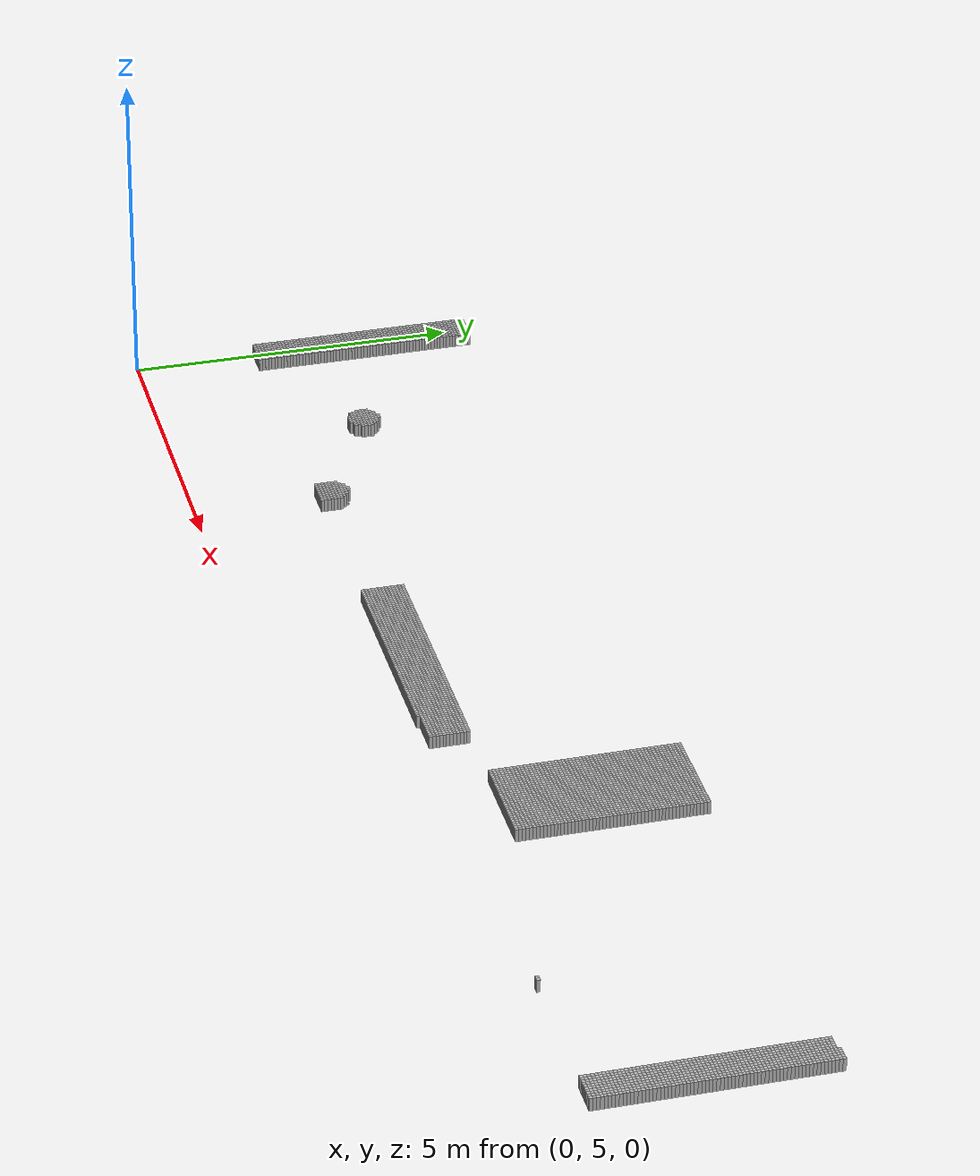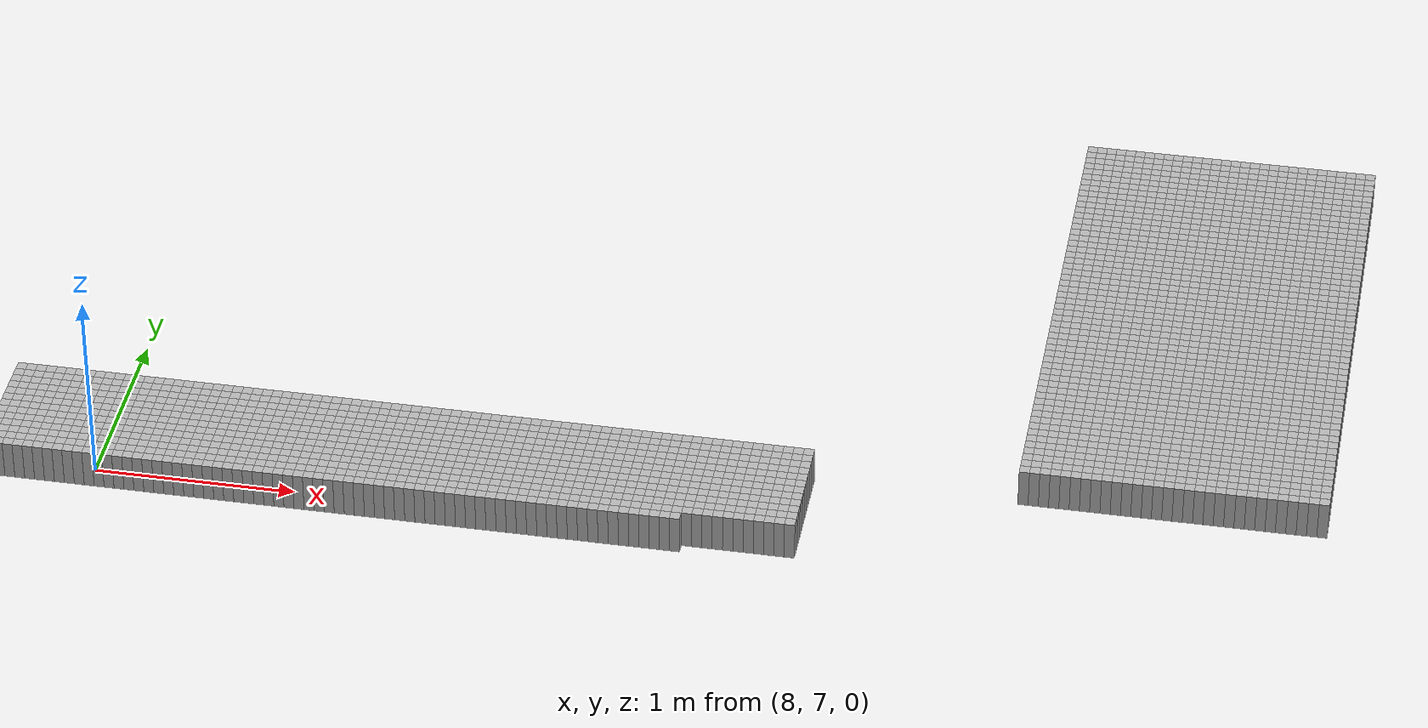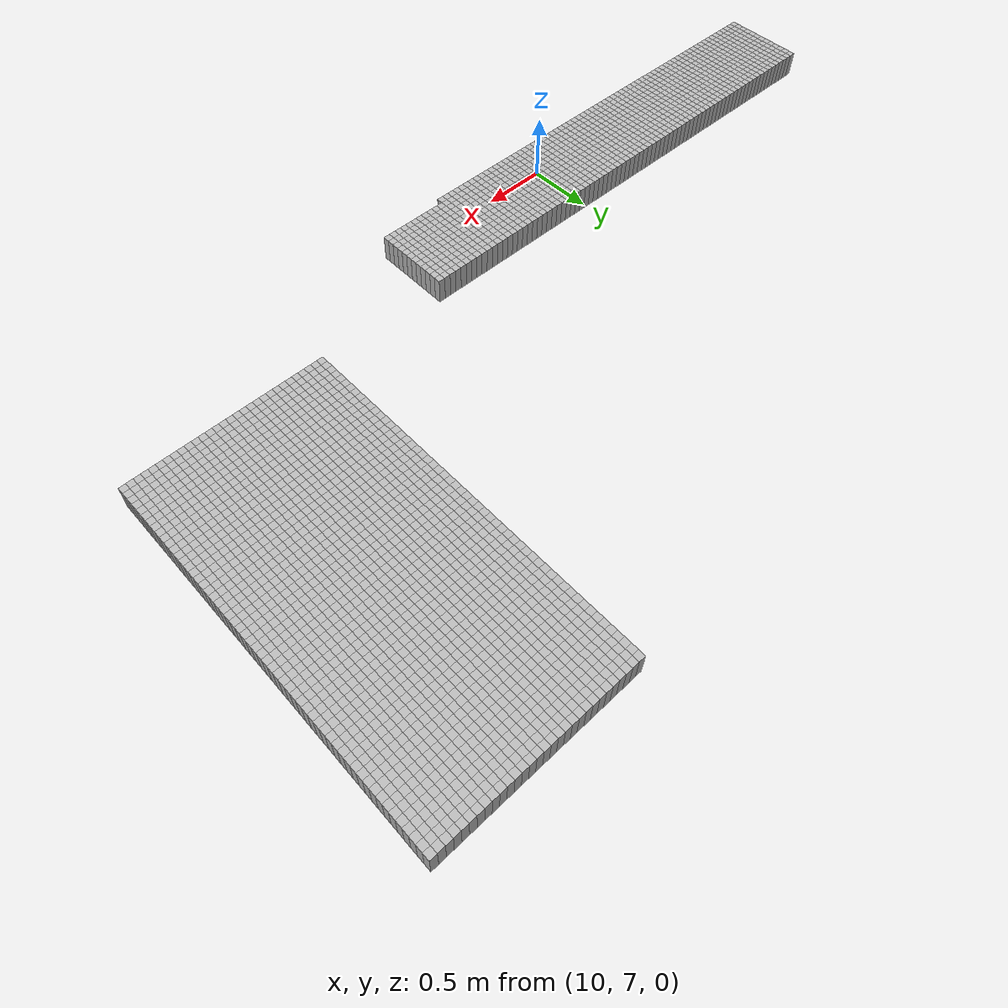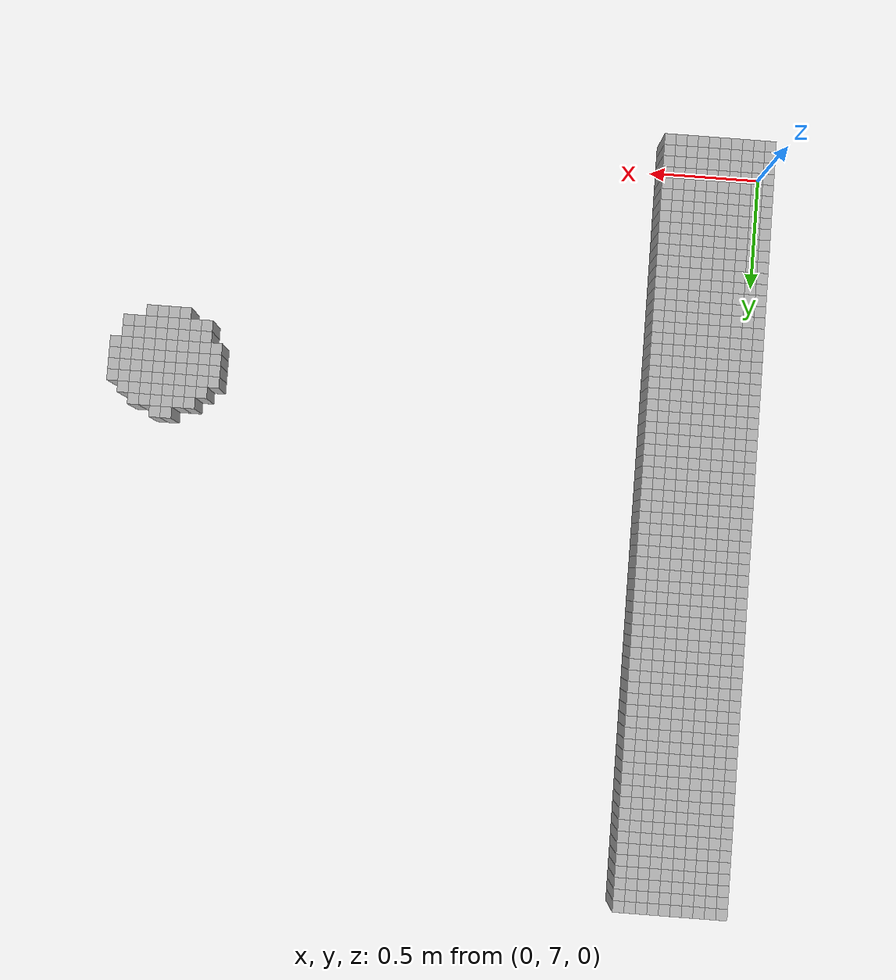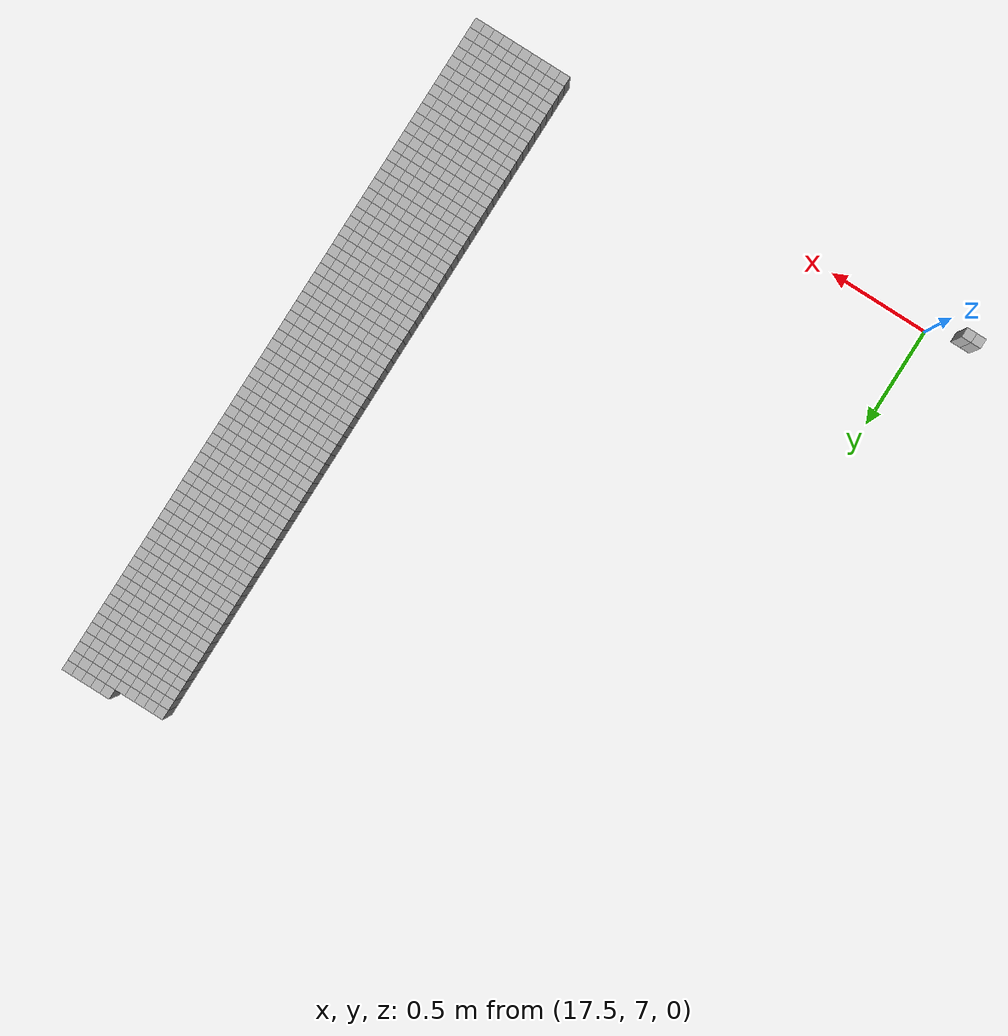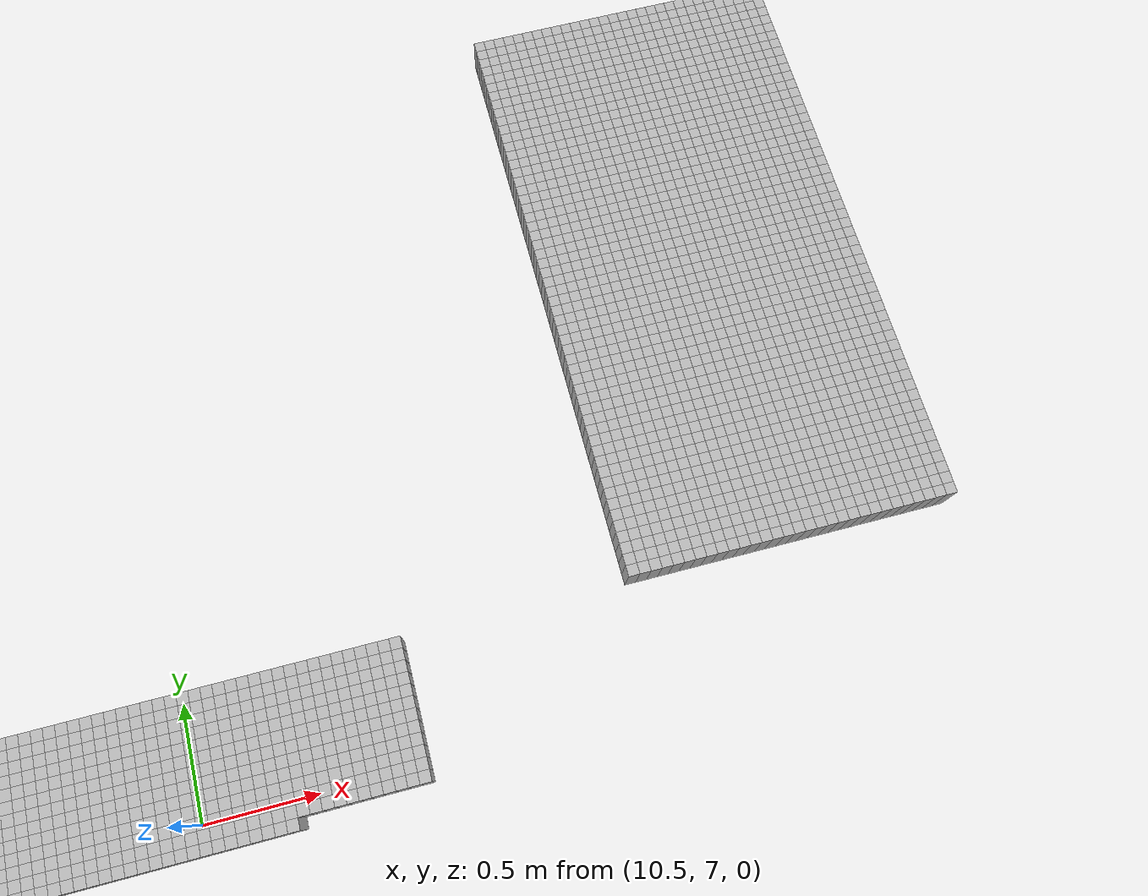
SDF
<sdf version="1.6">
 <world name="default">
  <model name="obstacle_395_193">
   <static>true</static>
   <link name="link">
    <pose>19.75 10.350000000000001 0.1 0 0 0</pose>
    <collision name="collision"><geometry><box><size>0.05 0.05 0.2</size></box></geometry></collision>
    <visual name="visual"><geometry><box><size>0.05 0.05 0.2</size></box></geometry></visual>
   </link>
  </model>
  <model name="obstacle_396_193">
   <static>true</static>
   <link name="link">
    <pose>19.8 10.350000000000001 0.1 0 0 0</pose>
    <collision name="collision"><geometry><box><size>0.05 0.05 0.2</size></box></geometry></collision>
    <visual name="visual"><geometry><box><size>0.05 0.05 0.2</size></box></geometry></visual>
   </link>
  </model>
  <model name="obstacle_397_193">
   <static>true</static>
   <link name="link">
    <pose>19.85 10.350000000000001 0.1 0 0 0</pose>
    <collision name="collision"><geometry><box><size>0.05 0.05 0.2</size></box></geometry></collision>
    <visual name="visual"><geometry><box><size>0.05 0.05 0.2</size></box></geometry></visual>
   </link>
  </model>
  <model name="obstacle_398_193">
   <static>true</static>
   <link name="link">
    <pose>19.900000000000002 10.350000000000001 0.1 0 0 0</pose>
    <collision name="collision"><geometry><box><size>0.05 0.05 0.2</size></box></geometry></collision>
    <visual name="visual"><geometry><box><size>0.05 0.05 0.2</size></box></geometry></visual>
   </link>
  </model>
  <model name="obstacle_399_193">
   <static>true</static>
   <link name="link">
    <pose>19.950000000000003 10.350000000000001 0.1 0 0 0</pose>
    <collision name="collision"><geometry><box><size>0.05 0.05 0.2</size></box></geometry></collision>
    <visual name="visual"><geometry><box><size>0.05 0.05 0.2</size></box></geometry></visual>
   </link>
  </model>
  <model name="obstacle_0_194">
   <static>true</static>
   <link name="link">
    <pose>0.0 10.3 0.1 0 0 0</pose>
    <collision name="collision"><geometry><box><size>0.05 0.05 0.2</size></box></geometry></collision>
    <visual name="visual"><geometry><box><size>0.05 0.05 0.2</size></box></geometry></visual>
   </link>
  </model>
  <model name="obstacle_1_194">
   <static>true</static>
   <link name="link">
    <pose>0.05 10.3 0.1 0 0 0</pose>
    <collision name="collision"><geometry><box><size>0.05 0.05 0.2</size></box></geometry></collision>
    <visual name="visual"><geometry><box><size>0.05 0.05 0.2</size></box></geometry></visual>
   </link>
  </model>
  <model name="obstacle_2_194">
   <static>true</static>
   <link name="link">
    <pose>0.1 10.3 0.1 0 0 0</pose>
    <collision name="collision"><geometry><box><size>0.05 0.05 0.2</size></box></geometry></collision>
    <visual name="visual"><geometry><box><size>0.05 0.05 0.2</size></box></geometry></visual>
   </link>
  </model>
  <model name="obstacle_3_194">
   <static>true</static>
   <link name="link">
    <pose>0.15000000000000002 10.3 0.1 0 0 0</pose>
    <collision name="collision"><geometry><box><size>0.05 0.05 0.2</size></box></geometry></collision>
    <visual name="visual"><geometry><box><size>0.05 0.05 0.2</size></box></geometry></visual>
   </link>
  </model>
  <model name="obstacle_4_194">
   <static>true</static>
   <link name="link">
    <pose>0.2 10.3 0.1 0 0 0</pose>
    <collision name="collision"><geometry><box><size>0.05 0.05 0.2</size></box></geometry></collision>
    <visual name="visual"><geometry><box><size>0.05 0.05 0.2</size></box></geometry></visual>
   </link>
  </model>
  <model name="obstacle_5_194">
   <static>true</static>
   <link name="link">
    <pose>0.25 10.3 0.1 0 0 0</pose>
    <collision name="collision"><geometry><box><size>0.05 0.05 0.2</size></box></geometry></collision>
    <visual name="visual"><geometry><box><size>0.05 0.05 0.2</size></box></geometry></visual>
   </link>
  </model>
  <model name="obstacle_6_194">
   <static>true</static>
   <link name="link">
    <pose>0.30000000000000004 10.3 0.1 0 0 0</pose>
    <collision name="collision"><geometry><box><size>0.05 0.05 0.2</size></box></geometry></collision>
    <visual name="visual"><geometry><box><size>0.05 0.05 0.2</size></box></geometry></visual>
   </link>
  </model>
  <model name="obstacle_7_194">
   <static>true</static>
   <link name="link">
    <pose>0.35000000000000003 10.3 0.1 0 0 0</pose>
    <collision name="collision"><geometry><box><size>0.05 0.05 0.2</size></box></geometry></collision>
    <visual name="visual"><geometry><box><size>0.05 0.05 0.2</size></box></geometry></visual>
   </link>
  </model>
  <model name="obstacle_8_194">
   <static>true</static>
   <link name="link">
    <pose>0.4 10.3 0.1 0 0 0</pose>
    <collision name="collision"><geometry><box><size>0.05 0.05 0.2</size></box></geometry></collision>
    <visual name="visual"><geometry><box><size>0.05 0.05 0.2</size></box></geometry></visual>
   </link>
  </model>
  <model name="obstacle_9_194">
   <static>true</static>
   <link name="link">
    <pose>0.45 10.3 0.1 0 0 0</pose>
    <collision name="collision"><geometry><box><size>0.05 0.05 0.2</size></box></geometry></collision>
    <visual name="visual"><geometry><box><size>0.05 0.05 0.2</size></box></geometry></visual>
   </link>
  </model>
  <model name="obstacle_250_194">
   <static>true</static>
   <link name="link">
    <pose>12.5 10.3 0.1 0 0 0</pose>
    <collision name="collision"><geometry><box><size>0.05 0.05 0.2</size></box></geometry></collision>
    <visual name="visual"><geometry><box><size>0.05 0.05 0.2</size></box></geometry></visual>
   </link>
  </model>
  <model name="obstacle_251_194">
   <static>true</static>
   <link name="link">
    <pose>12.55 10.3 0.1 0 0 0</pose>
    <collision name="collision"><geometry><box><size>0.05 0.05 0.2</size></box></geometry></collision>
    <visual name="visual"><geometry><box><size>0.05 0.05 0.2</size></box></geometry></visual>
   </link>
  </model>
  <model name="obstacle_252_194">
   <static>true</static>
   <link name="link">
    <pose>12.600000000000001 10.3 0.1 0 0 0</pose>
    <collision name="collision"><geometry><box><size>0.05 0.05 0.2</size></box></geometry></collision>
    <visual name="visual"><geometry><box><size>0.05 0.05 0.2</size></box></geometry></visual>
   </link>
  </model>
  <model name="obstacle_253_194">
   <static>true</static>
   <link name="link">
    <pose>12.65 10.3 0.1 0 0 0</pose>
    <collision name="collision"><geometry><box><size>0.05 0.05 0.2</size></box></geometry></collision>
    <visual name="visual"><geometry><box><size>0.05 0.05 0.2</size></box></geometry></visual>
   </link>
  </model>
  <model name="obstacle_254_194">
   <static>true</static>
   <link name="link">
    <pose>12.700000000000001 10.3 0.1 0 0 0</pose>
    <collision name="collision"><geometry><box><size>0.05 0.05 0.2</size></box></geometry></collision>
    <visual name="visual"><geometry><box><size>0.05 0.05 0.2</size></box></geometry></visual>
   </link>
  </model>
  <model name="obstacle_255_194">
   <static>true</static>
   <link name="link">
    <pose>12.75 10.3 0.1 0 0 0</pose>
    <collision name="collision"><geometry><box><size>0.05 0.05 0.2</size></box></geometry></collision>
    <visual name="visual"><geometry><box><size>0.05 0.05 0.2</size></box></geometry></visual>
   </link>
  </model>
  <model name="obstacle_256_194">
   <static>true</static>
   <link name="link">
    <pose>12.8 10.3 0.1 0 0 0</pose>
    <collision name="collision"><geometry><box><size>0.05 0.05 0.2</size></box></geometry></collision>
    <visual name="visual"><geometry><box><size>0.05 0.05 0.2</size></box></geometry></visual>
   </link>
  </model>
  <model name="obstacle_257_194">
   <static>true</static>
   <link name="link">
    <pose>12.850000000000001 10.3 0.1 0 0 0</pose>
    <collision name="collision"><geometry><box><size>0.05 0.05 0.2</size></box></geometry></collision>
    <visual name="visual"><geometry><box><size>0.05 0.05 0.2</size></box></geometry></visual>
   </link>
  </model>
  <model name="obstacle_258_194">
   <static>true</static>
   <link name="link">
    <pose>12.9 10.3 0.1 0 0 0</pose>
    <collision name="collision"><geometry><box><size>0.05 0.05 0.2</size></box></geometry></collision>
    <visual name="visual"><geometry><box><size>0.05 0.05 0.2</size></box></geometry></visual>
   </link>
  </model>
  <model name="obstacle_259_194">
   <static>true</static>
   <link name="link">
    <pose>12.950000000000001 10.3 0.1 0 0 0</pose>
    <collision name="collision"><geometry><box><size>0.05 0.05 0.2</size></box></geometry></collision>
    <visual name="visual"><geometry><box><size>0.05 0.05 0.2</size></box></geometry></visual>
   </link>
  </model>
  <model name="obstacle_260_194">
   <static>true</static>
   <link name="link">
    <pose>13.0 10.3 0.1 0 0 0</pose>
    <collision name="collision"><geometry><box><size>0.05 0.05 0.2</size></box></geometry></collision>
    <visual name="visual"><geometry><box><size>0.05 0.05 0.2</size></box></geometry></visual>
   </link>
  </model>
  <model name="obstacle_261_194">
   <static>true</static>
   <link name="link">
    <pose>13.05 10.3 0.1 0 0 0</pose>
    <collision name="collision"><geometry><box><size>0.05 0.05 0.2</size></box></geometry></collision>
    <visual name="visual"><geometry><box><size>0.05 0.05 0.2</size></box></geometry></visual>
   </link>
  </model>
  <model name="obstacle_262_194">
   <static>true</static>
   <link name="link">
    <pose>13.100000000000001 10.3 0.1 0 0 0</pose>
    <collision name="collision"><geometry><box><size>0.05 0.05 0.2</size></box></geometry></collision>
    <visual name="visual"><geometry><box><size>0.05 0.05 0.2</size></box></geometry></visual>
   </link>
  </model>
  <model name="obstacle_263_194">
   <static>true</static>
   <link name="link">
    <pose>13.15 10.3 0.1 0 0 0</pose>
    <collision name="collision"><geometry><box><size>0.05 0.05 0.2</size></box></geometry></collision>
    <visual name="visual"><geometry><box><size>0.05 0.05 0.2</size></box></geometry></visual>
   </link>
  </model>
  <model name="obstacle_264_194">
   <static>true</static>
   <link name="link">
    <pose>13.200000000000001 10.3 0.1 0 0 0</pose>
    <collision name="collision"><geometry><box><size>0.05 0.05 0.2</size></box></geometry></collision>
    <visual name="visual"><geometry><box><size>0.05 0.05 0.2</size></box></geometry></visual>
   </link>
  </model>
  <model name="obstacle_265_194">
   <static>true</static>
   <link name="link">
    <pose>13.25 10.3 0.1 0 0 0</pose>
    <collision name="collision"><geometry><box><size>0.05 0.05 0.2</size></box></geometry></collision>
    <visual name="visual"><geometry><box><size>0.05 0.05 0.2</size></box></geometry></visual>
   </link>
  </model>
  <model name="obstacle_266_194">
   <static>true</static>
   <link name="link">
    <pose>13.3 10.3 0.1 0 0 0</pose>
    <collision name="collision"><geometry><box><size>0.05 0.05 0.2</size></box></geometry></collision>
    <visual name="visual"><geometry><box><size>0.05 0.05 0.2</size></box></geometry></visual>
   </link>
  </model>
  <model name="obstacle_267_194">
   <static>true</static>
   <link name="link">
    <pose>13.350000000000001 10.3 0.1 0 0 0</pose>
    <collision name="collision"><geometry><box><size>0.05 0.05 0.2</size></box></geometry></collision>
    <visual name="visual"><geometry><box><size>0.05 0.05 0.2</size></box></geometry></visual>
   </link>
  </model>
  <model name="obstacle_268_194">
   <static>true</static>
   <link name="link">
    <pose>13.4 10.3 0.1 0 0 0</pose>
    <collision name="collision"><geometry><box><size>0.05 0.05 0.2</size></box></geometry></collision>
    <visual name="visual"><geometry><box><size>0.05 0.05 0.2</size></box></geometry></visual>
   </link>
  </model>
  <model name="obstacle_269_194">
   <static>true</static>
   <link name="link">
    <pose>13.450000000000001 10.3 0.1 0 0 0</pose>
    <collision name="collision"><geometry><box><size>0.05 0.05 0.2</size></box></geometry></collision>
    <visual name="visual"><geometry><box><size>0.05 0.05 0.2</size></box></geometry></visual>
   </link>
  </model>
  <model name="obstacle_270_194">
   <static>true</static>
   <link name="link">
    <pose>13.5 10.3 0.1 0 0 0</pose>
    <collision name="collision"><geometry><box><size>0.05 0.05 0.2</size></box></geometry></collision>
    <visual name="visual"><geometry><box><size>0.05 0.05 0.2</size></box></geometry></visual>
   </link>
  </model>
  <model name="obstacle_271_194">
   <static>true</static>
   <link name="link">
    <pose>13.55 10.3 0.1 0 0 0</pose>
    <collision name="collision"><geometry><box><size>0.05 0.05 0.2</size></box></geometry></collision>
    <visual name="visual"><geometry><box><size>0.05 0.05 0.2</size></box></geometry></visual>
   </link>
  </model>
  <model name="obstacle_272_194">
   <static>true</static>
   <link name="link">
    <pose>13.600000000000001 10.3 0.1 0 0 0</pose>
    <collision name="collision"><geometry><box><size>0.05 0.05 0.2</size></box></geometry></collision>
    <visual name="visual"><geometry><box><size>0.05 0.05 0.2</size></box></geometry></visual>
   </link>
  </model>
  <model name="obstacle_273_194">
   <static>true</static>
   <link name="link">
    <pose>13.65 10.3 0.1 0 0 0</pose>
    <collision name="collision"><geometry><box><size>0.05 0.05 0.2</size></box></geometry></collision>
    <visual name="visual"><geometry><box><size>0.05 0.05 0.2</size></box></geometry></visual>
   </link>
  </model>
  <model name="obstacle_274_194">
   <static>true</static>
   <link name="link">
    <pose>13.700000000000001 10.3 0.1 0 0 0</pose>
    <collision name="collision"><geometry><box><size>0.05 0.05 0.2</size></box></geometry></collision>
    <visual name="visual"><geometry><box><size>0.05 0.05 0.2</size></box></geometry></visual>
   </link>
  </model>
  <model name="obstacle_275_194">
   <static>true</static>
   <link name="link">
    <pose>13.75 10.3 0.1 0 0 0</pose>
    <collision name="collision"><geometry><box><size>0.05 0.05 0.2</size></box></geometry></collision>
    <visual name="visual"><geometry><box><size>0.05 0.05 0.2</size></box></geometry></visual>
   </link>
  </model>
  <model name="obstacle_276_194">
   <static>true</static>
   <link name="link">
    <pose>13.8 10.3 0.1 0 0 0</pose>
    <collision name="collision"><geometry><box><size>0.05 0.05 0.2</size></box></geometry></collision>
    <visual name="visual"><geometry><box><size>0.05 0.05 0.2</size></box></geometry></visual>
   </link>
  </model>
  <model name="obstacle_277_194">
   <static>true</static>
   <link name="link">
    <pose>13.850000000000001 10.3 0.1 0 0 0</pose>
    <collision name="collision"><geometry><box><size>0.05 0.05 0.2</size></box></geometry></collision>
    <visual name="visual"><geometry><box><size>0.05 0.05 0.2</size></box></geometry></visual>
   </link>
  </model>
  <model name="obstacle_278_194">
   <static>true</static>
   <link name="link">
    <pose>13.9 10.3 0.1 0 0 0</pose>
    <collision name="collision"><geometry><box><size>0.05 0.05 0.2</size></box></geometry></collision>
    <visual name="visual"><geometry><box><size>0.05 0.05 0.2</size></box></geometry></visual>
   </link>
  </model>
  <model name="obstacle_279_194">
   <static>true</static>
   <link name="link">
    <pose>13.950000000000001 10.3 0.1 0 0 0</pose>
    <collision name="collision"><geometry><box><size>0.05 0.05 0.2</size></box></geometry></collision>
    <visual name="visual"><geometry><box><size>0.05 0.05 0.2</size></box></geometry></visual>
   </link>
  </model>
  <model name="obstacle_390_194">
   <static>true</static>
   <link name="link">
    <pose>19.5 10.3 0.1 0 0 0</pose>
    <collision name="collision"><geometry><box><size>0.05 0.05 0.2</size></box></geometry></collision>
    <visual name="visual"><geometry><box><size>0.05 0.05 0.2</size></box></geometry></visual>
   </link>
  </model>
  <model name="obstacle_391_194">
   <static>true</static>
   <link name="link">
    <pose>19.55 10.3 0.1 0 0 0</pose>
    <collision name="collision"><geometry><box><size>0.05 0.05 0.2</size></box></geometry></collision>
    <visual name="visual"><geometry><box><size>0.05 0.05 0.2</size></box></geometry></visual>
   </link>
  </model>
  <model name="obstacle_392_194">
   <static>true</static>
   <link name="link">
    <pose>19.6 10.3 0.1 0 0 0</pose>
    <collision name="collision"><geometry><box><size>0.05 0.05 0.2</size></box></geometry></collision>
    <visual name="visual"><geometry><box><size>0.05 0.05 0.2</size></box></geometry></visual>
   </link>
  </model>
  <model name="obstacle_393_194">
   <static>true</static>
   <link name="link">
    <pose>19.650000000000002 10.3 0.1 0 0 0</pose>
    <collision name="collision"><geometry><box><size>0.05 0.05 0.2</size></box></geometry></collision>
    <visual name="visual"><geometry><box><size>0.05 0.05 0.2</size></box></geometry></visual>
   </link>
  </model>
  <model name="obstacle_394_194">
   <static>true</static>
   <link name="link">
    <pose>19.700000000000003 10.3 0.1 0 0 0</pose>
    <collision name="collision"><geometry><box><size>0.05 0.05 0.2</size></box></geometry></collision>
    <visual name="visual"><geometry><box><size>0.05 0.05 0.2</size></box></geometry></visual>
   </link>
  </model>
  <model name="obstacle_395_194">
   <static>true</static>
   <link name="link">
    <pose>19.75 10.3 0.1 0 0 0</pose>
    <collision name="collision"><geometry><box><size>0.05 0.05 0.2</size></box></geometry></collision>
    <visual name="visual"><geometry><box><size>0.05 0.05 0.2</size></box></geometry></visual>
   </link>
  </model>
  <model name="obstacle_396_194">
   <static>true</static>
   <link name="link">
    <pose>19.8 10.3 0.1 0 0 0</pose>
    <collision name="collision"><geometry><box><size>0.05 0.05 0.2</size></box></geometry></collision>
    <visual name="visual"><geometry><box><size>0.05 0.05 0.2</size></box></geometry></visual>
   </link>
  </model>
  <model name="obstacle_397_194">
   <static>true</static>
   <link name="link">
    <pose>19.85 10.3 0.1 0 0 0</pose>
    <collision name="collision"><geometry><box><size>0.05 0.05 0.2</size></box></geometry></collision>
    <visual name="visual"><geometry><box><size>0.05 0.05 0.2</size></box></geometry></visual>
   </link>
  </model>
  <model name="obstacle_398_194">
   <static>true</static>
   <link name="link">
    <pose>19.900000000000002 10.3 0.1 0 0 0</pose>
    <collision name="collision"><geometry><box><size>0.05 0.05 0.2</size></box></geometry></collision>
    <visual name="visual"><geometry><box><size>0.05 0.05 0.2</size></box></geometry></visual>
   </link>
  </model>
  <model name="obstacle_399_194">
   <static>true</static>
   <link name="link">
    <pose>19.950000000000003 10.3 0.1 0 0 0</pose>
    <collision name="collision"><geometry><box><size>0.05 0.05 0.2</size></box></geometry></collision>
    <visual name="visual"><geometry><box><size>0.05 0.05 0.2</size></box></geometry></visual>
   </link>
  </model>
  <model name="obstacle_0_195">
   <static>true</static>
   <link name="link">
    <pose>0.0 10.25 0.1 0 0 0</pose>
    <collision name="collision"><geometry><box><size>0.05 0.05 0.2</size></box></geometry></collision>
    <visual name="visual"><geometry><box><size>0.05 0.05 0.2</size></box></geometry></visual>
   </link>
  </model>
  <model name="obstacle_1_195">
   <static>true</static>
   <link name="link">
    <pose>0.05 10.25 0.1 0 0 0</pose>
    <collision name="collision"><geometry><box><size>0.05 0.05 0.2</size></box></geometry></collision>
    <visual name="visual"><geometry><box><size>0.05 0.05 0.2</size></box></geometry></visual>
   </link>
  </model>
  <model name="obstacle_2_195">
   <static>true</static>
   <link name="link">
    <pose>0.1 10.25 0.1 0 0 0</pose>
    <collision name="collision"><geometry><box><size>0.05 0.05 0.2</size></box></geometry></collision>
    <visual name="visual"><geometry><box><size>0.05 0.05 0.2</size></box></geometry></visual>
   </link>
  </model>
  <model name="obstacle_3_195">
   <static>true</static>
   <link name="link">
    <pose>0.15000000000000002 10.25 0.1 0 0 0</pose>
    <collision name="collision"><geometry><box><size>0.05 0.05 0.2</size></box></geometry></collision>
    <visual name="visual"><geometry><box><size>0.05 0.05 0.2</size></box></geometry></visual>
   </link>
  </model>
  <model name="obstacle_4_195">
   <static>true</static>
   <link name="link">
    <pose>0.2 10.25 0.1 0 0 0</pose>
    <collision name="collision"><geometry><box><size>0.05 0.05 0.2</size></box></geometry></collision>
    <visual name="visual"><geometry><box><size>0.05 0.05 0.2</size></box></geometry></visual>
   </link>
  </model>
  <model name="obstacle_5_195">
   <static>true</static>
   <link name="link">
    <pose>0.25 10.25 0.1 0 0 0</pose>
    <collision name="collision"><geometry><box><size>0.05 0.05 0.2</size></box></geometry></collision>
    <visual name="visual"><geometry><box><size>0.05 0.05 0.2</size></box></geometry></visual>
   </link>
  </model>
  <model name="obstacle_6_195">
   <static>true</static>
   <link name="link">
    <pose>0.30000000000000004 10.25 0.1 0 0 0</pose>
    <collision name="collision"><geometry><box><size>0.05 0.05 0.2</size></box></geometry></collision>
    <visual name="visual"><geometry><box><size>0.05 0.05 0.2</size></box></geometry></visual>
   </link>
  </model>
  <model name="obstacle_7_195">
   <static>true</static>
   <link name="link">
    <pose>0.35000000000000003 10.25 0.1 0 0 0</pose>
    <collision name="collision"><geometry><box><size>0.05 0.05 0.2</size></box></geometry></collision>
    <visual name="visual"><geometry><box><size>0.05 0.05 0.2</size></box></geometry></visual>
   </link>
  </model>
  <model name="obstacle_8_195">
   <static>true</static>
   <link name="link">
    <pose>0.4 10.25 0.1 0 0 0</pose>
    <collision name="collision"><geometry><box><size>0.05 0.05 0.2</size></box></geometry></collision>
    <visual name="visual"><geometry><box><size>0.05 0.05 0.2</size></box></geometry></visual>
   </link>
  </model>
  <model name="obstacle_9_195">
   <static>true</static>
   <link name="link">
    <pose>0.45 10.25 0.1 0 0 0</pose>
    <collision name="collision"><geometry><box><size>0.05 0.05 0.2</size></box></geometry></collision>
    <visual name="visual"><geometry><box><size>0.05 0.05 0.2</size></box></geometry></visual>
   </link>
  </model>
  <model name="obstacle_250_195">
   <static>true</static>
   <link name="link">
    <pose>12.5 10.25 0.1 0 0 0</pose>
    <collision name="collision"><geometry><box><size>0.05 0.05 0.2</size></box></geometry></collision>
    <visual name="visual"><geometry><box><size>0.05 0.05 0.2</size></box></geometry></visual>
   </link>
  </model>
  <model name="obstacle_251_195">
   <static>true</static>
   <link name="link">
    <pose>12.55 10.25 0.1 0 0 0</pose>
    <collision name="collision"><geometry><box><size>0.05 0.05 0.2</size></box></geometry></collision>
    <visual name="visual"><geometry><box><size>0.05 0.05 0.2</size></box></geometry></visual>
   </link>
  </model>
  <model name="obstacle_252_195">
   <static>true</static>
   <link name="link">
    <pose>12.600000000000001 10.25 0.1 0 0 0</pose>
    <collision name="collision"><geometry><box><size>0.05 0.05 0.2</size></box></geometry></collision>
    <visual name="visual"><geometry><box><size>0.05 0.05 0.2</size></box></geometry></visual>
   </link>
  </model>
  <model name="obstacle_253_195">
   <static>true</static>
   <link name="link">
    <pose>12.65 10.25 0.1 0 0 0</pose>
    <collision name="collision"><geometry><box><size>0.05 0.05 0.2</size></box></geometry></collision>
    <visual name="visual"><geometry><box><size>0.05 0.05 0.2</size></box></geometry></visual>
   </link>
  </model>
  <model name="obstacle_254_195">
   <static>true</static>
   <link name="link">
    <pose>12.700000000000001 10.25 0.1 0 0 0</pose>
    <collision name="collision"><geometry><box><size>0.05 0.05 0.2</size></box></geometry></collision>
    <visual name="visual"><geometry><box><size>0.05 0.05 0.2</size></box></geometry></visual>
   </link>
  </model>
  <model name="obstacle_255_195">
   <static>true</static>
   <link name="link">
    <pose>12.75 10.25 0.1 0 0 0</pose>
    <collision name="collision"><geometry><box><size>0.05 0.05 0.2</size></box></geometry></collision>
    <visual name="visual"><geometry><box><size>0.05 0.05 0.2</size></box></geometry></visual>
   </link>
  </model>
  <model name="obstacle_256_195">
   <static>true</static>
   <link name="link">
    <pose>12.8 10.25 0.1 0 0 0</pose>
    <collision name="collision"><geometry><box><size>0.05 0.05 0.2</size></box></geometry></collision>
    <visual name="visual"><geometry><box><size>0.05 0.05 0.2</size></box></geometry></visual>
   </link>
  </model>
  <model name="obstacle_257_195">
   <static>true</static>
   <link name="link">
    <pose>12.850000000000001 10.25 0.1 0 0 0</pose>
    <collision name="collision"><geometry><box><size>0.05 0.05 0.2</size></box></geometry></collision>
    <visual name="visual"><geometry><box><size>0.05 0.05 0.2</size></box></geometry></visual>
   </link>
  </model>
  <model name="obstacle_258_195">
   <static>true</static>
   <link name="link">
    <pose>12.9 10.25 0.1 0 0 0</pose>
    <collision name="collision"><geometry><box><size>0.05 0.05 0.2</size></box></geometry></collision>
    <visual name="visual"><geometry><box><size>0.05 0.05 0.2</size></box></geometry></visual>
   </link>
  </model>
  <model name="obstacle_259_195">
   <static>true</static>
   <link name="link">
    <pose>12.950000000000001 10.25 0.1 0 0 0</pose>
    <collision name="collision"><geometry><box><size>0.05 0.05 0.2</size></box></geometry></collision>
    <visual name="visual"><geometry><box><size>0.05 0.05 0.2</size></box></geometry></visual>
   </link>
  </model>
  <model name="obstacle_260_195">
   <static>true</static>
   <link name="link">
    <pose>13.0 10.25 0.1 0 0 0</pose>
    <collision name="collision"><geometry><box><size>0.05 0.05 0.2</size></box></geometry></collision>
    <visual name="visual"><geometry><box><size>0.05 0.05 0.2</size></box></geometry></visual>
   </link>
  </model>
  <model name="obstacle_261_195">
   <static>true</static>
   <link name="link">
    <pose>13.05 10.25 0.1 0 0 0</pose>
    <collision name="collision"><geometry><box><size>0.05 0.05 0.2</size></box></geometry></collision>
    <visual name="visual"><geometry><box><size>0.05 0.05 0.2</size></box></geometry></visual>
   </link>
  </model>
  <model name="obstacle_262_195">
   <static>true</static>
   <link name="link">
    <pose>13.100000000000001 10.25 0.1 0 0 0</pose>
    <collision name="collision"><geometry><box><size>0.05 0.05 0.2</size></box></geometry></collision>
    <visual name="visual"><geometry><box><size>0.05 0.05 0.2</size></box></geometry></visual>
   </link>
  </model>
  <model name="obstacle_263_195">
   <static>true</static>
   <link name="link">
    <pose>13.15 10.25 0.1 0 0 0</pose>
    <collision name="collision"><geometry><box><size>0.05 0.05 0.2</size></box></geometry></collision>
    <visual name="visual"><geometry><box><size>0.05 0.05 0.2</size></box></geometry></visual>
   </link>
  </model>
  <model name="obstacle_264_195">
   <static>true</static>
   <link name="link">
    <pose>13.200000000000001 10.25 0.1 0 0 0</pose>
    <collision name="collision"><geometry><box><size>0.05 0.05 0.2</size></box></geometry></collision>
    <visual name="visual"><geometry><box><size>0.05 0.05 0.2</size></box></geometry></visual>
   </link>
  </model>
  <model name="obstacle_265_195">
   <static>true</static>
   <link name="link">
    <pose>13.25 10.25 0.1 0 0 0</pose>
    <collision name="collision"><geometry><box><size>0.05 0.05 0.2</size></box></geometry></collision>
    <visual name="visual"><geometry><box><size>0.05 0.05 0.2</size></box></geometry></visual>
   </link>
  </model>
  <model name="obstacle_266_195">
   <static>true</static>
   <link name="link">
    <pose>13.3 10.25 0.1 0 0 0</pose>
    <collision name="collision"><geometry><box><size>0.05 0.05 0.2</size></box></geometry></collision>
    <visual name="visual"><geometry><box><size>0.05 0.05 0.2</size></box></geometry></visual>
   </link>
  </model>
  <model name="obstacle_267_195">
   <static>true</static>
   <link name="link">
    <pose>13.350000000000001 10.25 0.1 0 0 0</pose>
    <collision name="collision"><geometry><box><size>0.05 0.05 0.2</size></box></geometry></collision>
    <visual name="visual"><geometry><box><size>0.05 0.05 0.2</size></box></geometry></visual>
   </link>
  </model>
  <model name="obstacle_268_195">
   <static>true</static>
   <link name="link">
    <pose>13.4 10.25 0.1 0 0 0</pose>
    <collision name="collision"><geometry><box><size>0.05 0.05 0.2</size></box></geometry></collision>
    <visual name="visual"><geometry><box><size>0.05 0.05 0.2</size></box></geometry></visual>
   </link>
  </model>
  <model name="obstacle_269_195">
   <static>true</static>
   <link name="link">
    <pose>13.450000000000001 10.25 0.1 0 0 0</pose>
    <collision name="collision"><geometry><box><size>0.05 0.05 0.2</size></box></geometry></collision>
    <visual name="visual"><geometry><box><size>0.05 0.05 0.2</size></box></geometry></visual>
   </link>
  </model>
  <model name="obstacle_270_195">
   <static>true</static>
   <link name="link">
    <pose>13.5 10.25 0.1 0 0 0</pose>
    <collision name="collision"><geometry><box><size>0.05 0.05 0.2</size></box></geometry></collision>
    <visual name="visual"><geometry><box><size>0.05 0.05 0.2</size></box></geometry></visual>
   </link>
  </model>
  <model name="obstacle_271_195">
   <static>true</static>
   <link name="link">
    <pose>13.55 10.25 0.1 0 0 0</pose>
    <collision name="collision"><geometry><box><size>0.05 0.05 0.2</size></box></geometry></collision>
    <visual name="visual"><geometry><box><size>0.05 0.05 0.2</size></box></geometry></visual>
   </link>
  </model>
  <model name="obstacle_272_195">
   <static>true</static>
   <link name="link">
    <pose>13.600000000000001 10.25 0.1 0 0 0</pose>
    <collision name="collision"><geometry><box><size>0.05 0.05 0.2</size></box></geometry></collision>
    <visual name="visual"><geometry><box><size>0.05 0.05 0.2</size></box></geometry></visual>
   </link>
  </model>
  <model name="obstacle_273_195">
   <static>true</static>
   <link name="link">
    <pose>13.65 10.25 0.1 0 0 0</pose>
    <collision name="collision"><geometry><box><size>0.05 0.05 0.2</size></box></geometry></collision>
    <visual name="visual"><geometry><box><size>0.05 0.05 0.2</size></box></geometry></visual>
   </link>
  </model>
  <model name="obstacle_274_195">
   <static>true</static>
   <link name="link">
    <pose>13.700000000000001 10.25 0.1 0 0 0</pose>
    <collision name="collision"><geometry><box><size>0.05 0.05 0.2</size></box></geometry></collision>
    <visual name="visual"><geometry><box><size>0.05 0.05 0.2</size></box></geometry></visual>
   </link>
  </model>
  <model name="obstacle_275_195">
   <static>true</static>
   <link name="link">
    <pose>13.75 10.25 0.1 0 0 0</pose>
    <collision name="collision"><geometry><box><size>0.05 0.05 0.2</size></box></geometry></collision>
    <visual name="visual"><geometry><box><size>0.05 0.05 0.2</size></box></geometry></visual>
   </link>
  </model>
  <model name="obstacle_276_195">
   <static>true</static>
   <link name="link">
    <pose>13.8 10.25 0.1 0 0 0</pose>
    <collision name="collision"><geometry><box><size>0.05 0.05 0.2</size></box></geometry></collision>
    <visual name="visual"><geometry><box><size>0.05 0.05 0.2</size></box></geometry></visual>
   </link>
  </model>
  <model name="obstacle_277_195">
   <static>true</static>
   <link name="link">
    <pose>13.850000000000001 10.25 0.1 0 0 0</pose>
    <collision name="collision"><geometry><box><size>0.05 0.05 0.2</size></box></geometry></collision>
    <visual name="visual"><geometry><box><size>0.05 0.05 0.2</size></box></geometry></visual>
   </link>
  </model>
  <model name="obstacle_278_195">
   <static>true</static>
   <link name="link">
    <pose>13.9 10.25 0.1 0 0 0</pose>
    <collision name="collision"><geometry><box><size>0.05 0.05 0.2</size></box></geometry></collision>
    <visual name="visual"><geometry><box><size>0.05 0.05 0.2</size></box></geometry></visual>
   </link>
  </model>
  <model name="obstacle_279_195">
   <static>true</static>
   <link name="link">
    <pose>13.950000000000001 10.25 0.1 0 0 0</pose>
    <collision name="collision"><geometry><box><size>0.05 0.05 0.2</size></box></geometry></collision>
    <visual name="visual"><geometry><box><size>0.05 0.05 0.2</size></box></geometry></visual>
   </link>
  </model>
  <model name="obstacle_390_195">
   <static>true</static>
   <link name="link">
    <pose>19.5 10.25 0.1 0 0 0</pose>
    <collision name="collision"><geometry><box><size>0.05 0.05 0.2</size></box></geometry></collision>
    <visual name="visual"><geometry><box><size>0.05 0.05 0.2</size></box></geometry></visual>
   </link>
  </model>
  <model name="obstacle_391_195">
   <static>true</static>
   <link name="link">
    <pose>19.55 10.25 0.1 0 0 0</pose>
    <collision name="collision"><geometry><box><size>0.05 0.05 0.2</size></box></geometry></collision>
    <visual name="visual"><geometry><box><size>0.05 0.05 0.2</size></box></geometry></visual>
   </link>
  </model>
  <model name="obstacle_392_195">
   <static>true</static>
   <link name="link">
    <pose>19.6 10.25 0.1 0 0 0</pose>
    <collision name="collision"><geometry><box><size>0.05 0.05 0.2</size></box></geometry></collision>
    <visual name="visual"><geometry><box><size>0.05 0.05 0.2</size></box></geometry></visual>
   </link>
  </model>
  <model name="obstacle_393_195">
   <static>true</static>
   <link name="link">
    <pose>19.650000000000002 10.25 0.1 0 0 0</pose>
    <collision name="collision"><geometry><box><size>0.05 0.05 0.2</size></box></geometry></collision>
    <visual name="visual"><geometry><box><size>0.05 0.05 0.2</size></box></geometry></visual>
   </link>
  </model>
  <model name="obstacle_394_195">
   <static>true</static>
   <link name="link">
    <pose>19.700000000000003 10.25 0.1 0 0 0</pose>
    <collision name="collision"><geometry><box><size>0.05 0.05 0.2</size></box></geometry></collision>
    <visual name="visual"><geometry><box><size>0.05 0.05 0.2</size></box></geometry></visual>
   </link>
  </model>
  <model name="obstacle_395_195">
   <static>true</static>
   <link name="link">
    <pose>19.75 10.25 0.1 0 0 0</pose>
    <collision name="collision"><geometry><box><size>0.05 0.05 0.2</size></box></geometry></collision>
    <visual name="visual"><geometry><box><size>0.05 0.05 0.2</size></box></geometry></visual>
   </link>
  </model>
  <model name="obstacle_396_195">
   <static>true</static>
   <link name="link">
    <pose>19.8 10.25 0.1 0 0 0</pose>
    <collision name="collision"><geometry><box><size>0.05 0.05 0.2</size></box></geometry></collision>
    <visual name="visual"><geometry><box><size>0.05 0.05 0.2</size></box></geometry></visual>
   </link>
  </model>
  <model name="obstacle_397_195">
   <static>true</static>
   <link name="link">
    <pose>19.85 10.25 0.1 0 0 0</pose>
    <collision name="collision"><geometry><box><size>0.05 0.05 0.2</size></box></geometry></collision>
    <visual name="visual"><geometry><box><size>0.05 0.05 0.2</size></box></geometry></visual>
   </link>
  </model>
  <model name="obstacle_398_195">
   <static>true</static>
   <link name="link">
    <pose>19.900000000000002 10.25 0.1 0 0 0</pose>
    <collision name="collision"><geometry><box><size>0.05 0.05 0.2</size></box></geometry></collision>
    <visual name="visual"><geometry><box><size>0.05 0.05 0.2</size></box></geometry></visual>
   </link>
  </model>
  <model name="obstacle_399_195">
   <static>true</static>
   <link name="link">
    <pose>19.950000000000003 10.25 0.1 0 0 0</pose>
    <collision name="collision"><geometry><box><size>0.05 0.05 0.2</size></box></geometry></collision>
    <visual name="visual"><geometry><box><size>0.05 0.05 0.2</size></box></geometry></visual>
   </link>
  </model>
  <model name="obstacle_0_196">
   <static>true</static>
   <link name="link">
    <pose>0.0 10.200000000000001 0.1 0 0 0</pose>
    <collision name="collision"><geometry><box><size>0.05 0.05 0.2</size></box></geometry></collision>
    <visual name="visual"><geometry><box><size>0.05 0.05 0.2</size></box></geometry></visual>
   </link>
  </model>
  <model name="obstacle_1_196">
   <static>true</static>
   <link name="link">
    <pose>0.05 10.200000000000001 0.1 0 0 0</pose>
    <collision name="collision"><geometry><box><size>0.05 0.05 0.2</size></box></geometry></collision>
    <visual name="visual"><geometry><box><size>0.05 0.05 0.2</size></box></geometry></visual>
   </link>
  </model>
  <model name="obstacle_2_196">
   <static>true</static>
   <link name="link">
    <pose>0.1 10.200000000000001 0.1 0 0 0</pose>
    <collision name="collision"><geometry><box><size>0.05 0.05 0.2</size></box></geometry></collision>
    <visual name="visual"><geometry><box><size>0.05 0.05 0.2</size></box></geometry></visual>
   </link>
  </model>
  <model name="obstacle_3_196">
   <static>true</static>
   <link name="link">
    <pose>0.15000000000000002 10.200000000000001 0.1 0 0 0</pose>
    <collision name="collision"><geometry><box><size>0.05 0.05 0.2</size></box></geometry></collision>
    <visual name="visual"><geometry><box><size>0.05 0.05 0.2</size></box></geometry></visual>
   </link>
  </model>
  <model name="obstacle_4_196">
   <static>true</static>
   <link name="link">
    <pose>0.2 10.200000000000001 0.1 0 0 0</pose>
    <collision name="collision"><geometry><box><size>0.05 0.05 0.2</size></box></geometry></collision>
    <visual name="visual"><geometry><box><size>0.05 0.05 0.2</size></box></geometry></visual>
   </link>
  </model>
  <model name="obstacle_5_196">
   <static>true</static>
   <link name="link">
    <pose>0.25 10.200000000000001 0.1 0 0 0</pose>
    <collision name="collision"><geometry><box><size>0.05 0.05 0.2</size></box></geometry></collision>
    <visual name="visual"><geometry><box><size>0.05 0.05 0.2</size></box></geometry></visual>
   </link>
  </model>
  <model name="obstacle_6_196">
   <static>true</static>
   <link name="link">
    <pose>0.30000000000000004 10.200000000000001 0.1 0 0 0</pose>
    <collision name="collision"><geometry><box><size>0.05 0.05 0.2</size></box></geometry></collision>
    <visual name="visual"><geometry><box><size>0.05 0.05 0.2</size></box></geometry></visual>
   </link>
  </model>
  <model name="obstacle_7_196">
   <static>true</static>
   <link name="link">
    <pose>0.35000000000000003 10.200000000000001 0.1 0 0 0</pose>
    <collision name="collision"><geometry><box><size>0.05 0.05 0.2</size></box></geometry></collision>
    <visual name="visual"><geometry><box><size>0.05 0.05 0.2</size></box></geometry></visual>
   </link>
  </model>
  <model name="obstacle_8_196">
   <static>true</static>
   <link name="link">
    <pose>0.4 10.200000000000001 0.1 0 0 0</pose>
    <collision name="collision"><geometry><box><size>0.05 0.05 0.2</size></box></geometry></collision>
    <visual name="visual"><geometry><box><size>0.05 0.05 0.2</size></box></geometry></visual>
   </link>
  </model>
  <model name="obstacle_9_196">
   <static>true</static>
   <link name="link">
    <pose>0.45 10.200000000000001 0.1 0 0 0</pose>
    <collision name="collision"><geometry><box><size>0.05 0.05 0.2</size></box></geometry></collision>
    <visual name="visual"><geometry><box><size>0.05 0.05 0.2</size></box></geometry></visual>
   </link>
  </model>
  <model name="obstacle_250_196">
   <static>true</static>
   <link name="link">
    <pose>12.5 10.200000000000001 0.1 0 0 0</pose>
    <collision name="collision"><geometry><box><size>0.05 0.05 0.2</size></box></geometry></collision>
    <visual name="visual"><geometry><box><size>0.05 0.05 0.2</size></box></geometry></visual>
   </link>
  </model>
  <model name="obstacle_251_196">
   <static>true</static>
   <link name="link">
    <pose>12.55 10.200000000000001 0.1 0 0 0</pose>
    <collision name="collision"><geometry><box><size>0.05 0.05 0.2</size></box></geometry></collision>
    <visual name="visual"><geometry><box><size>0.05 0.05 0.2</size></box></geometry></visual>
   </link>
  </model>
  <model name="obstacle_252_196">
   <static>true</static>
   <link name="link">
    <pose>12.600000000000001 10.200000000000001 0.1 0 0 0</pose>
    <collision name="collision"><geometry><box><size>0.05 0.05 0.2</size></box></geometry></collision>
    <visual name="visual"><geometry><box><size>0.05 0.05 0.2</size></box></geometry></visual>
   </link>
  </model>
  <model name="obstacle_253_196">
   <static>true</static>
   <link name="link">
    <pose>12.65 10.200000000000001 0.1 0 0 0</pose>
    <collision name="collision"><geometry><box><size>0.05 0.05 0.2</size></box></geometry></collision>
    <visual name="visual"><geometry><box><size>0.05 0.05 0.2</size></box></geometry></visual>
   </link>
  </model>
  <model name="obstacle_254_196">
   <static>true</static>
   <link name="link">
    <pose>12.700000000000001 10.200000000000001 0.1 0 0 0</pose>
    <collision name="collision"><geometry><box><size>0.05 0.05 0.2</size></box></geometry></collision>
    <visual name="visual"><geometry><box><size>0.05 0.05 0.2</size></box></geometry></visual>
   </link>
  </model>
  <model name="obstacle_255_196">
   <static>true</static>
   <link name="link">
    <pose>12.75 10.200000000000001 0.1 0 0 0</pose>
    <collision name="collision"><geometry><box><size>0.05 0.05 0.2</size></box></geometry></collision>
    <visual name="visual"><geometry><box><size>0.05 0.05 0.2</size></box></geometry></visual>
   </link>
  </model>
  <model name="obstacle_256_196">
   <static>true</static>
   <link name="link">
    <pose>12.8 10.200000000000001 0.1 0 0 0</pose>
    <collision name="collision"><geometry><box><size>0.05 0.05 0.2</size></box></geometry></collision>
    <visual name="visual"><geometry><box><size>0.05 0.05 0.2</size></box></geometry></visual>
   </link>
  </model>
  <model name="obstacle_257_196">
   <static>true</static>
   <link name="link">
    <pose>12.850000000000001 10.200000000000001 0.1 0 0 0</pose>
    <collision name="collision"><geometry><box><size>0.05 0.05 0.2</size></box></geometry></collision>
    <visual name="visual"><geometry><box><size>0.05 0.05 0.2</size></box></geometry></visual>
   </link>
  </model>
  <model name="obstacle_258_196">
   <static>true</static>
   <link name="link">
    <pose>12.9 10.200000000000001 0.1 0 0 0</pose>
    <collision name="collision"><geometry><box><size>0.05 0.05 0.2</size></box></geometry></collision>
    <visual name="visual"><geometry><box><size>0.05 0.05 0.2</size></box></geometry></visual>
   </link>
  </model>
  <model name="obstacle_259_196">
   <static>true</static>
   <link name="link">
    <pose>12.950000000000001 10.200000000000001 0.1 0 0 0</pose>
    <collision name="collision"><geometry><box><size>0.05 0.05 0.2</size></box></geometry></collision>
    <visual name="visual"><geometry><box><size>0.05 0.05 0.2</size></box></geometry></visual>
   </link>
  </model>
  <model name="obstacle_260_196">
   <static>true</static>
   <link name="link">
    <pose>13.0 10.200000000000001 0.1 0 0 0</pose>
    <collision name="collision"><geometry><box><size>0.05 0.05 0.2</size></box></geometry></collision>
    <visual name="visual"><geometry><box><size>0.05 0.05 0.2</size></box></geometry></visual>
   </link>
  </model>
  <model name="obstacle_261_196">
   <static>true</static>
   <link name="link">
    <pose>13.05 10.200000000000001 0.1 0 0 0</pose>
    <collision name="collision"><geometry><box><size>0.05 0.05 0.2</size></box></geometry></collision>
    <visual name="visual"><geometry><box><size>0.05 0.05 0.2</size></box></geometry></visual>
   </link>
  </model>
  <model name="obstacle_262_196">
   <static>true</static>
   <link name="link">
    <pose>13.100000000000001 10.200000000000001 0.1 0 0 0</pose>
    <collision name="collision"><geometry><box><size>0.05 0.05 0.2</size></box></geometry></collision>
    <visual name="visual"><geometry><box><size>0.05 0.05 0.2</size></box></geometry></visual>
   </link>
  </model>
  <model name="obstacle_263_196">
   <static>true</static>
   <link name="link">
    <pose>13.15 10.200000000000001 0.1 0 0 0</pose>
    <collision name="collision"><geometry><box><size>0.05 0.05 0.2</size></box></geometry></collision>
    <visual name="visual"><geometry><box><size>0.05 0.05 0.2</size></box></geometry></visual>
   </link>
  </model>
  <model name="obstacle_264_196">
   <static>true</static>
   <link name="link">
    <pose>13.200000000000001 10.200000000000001 0.1 0 0 0</pose>
    <collision name="collision"><geometry><box><size>0.05 0.05 0.2</size></box></geometry></collision>
    <visual name="visual"><geometry><box><size>0.05 0.05 0.2</size></box></geometry></visual>
   </link>
  </model>
  <model name="obstacle_265_196">
   <static>true</static>
   <link name="link">
    <pose>13.25 10.200000000000001 0.1 0 0 0</pose>
    <collision name="collision"><geometry><box><size>0.05 0.05 0.2</size></box></geometry></collision>
    <visual name="visual"><geometry><box><size>0.05 0.05 0.2</size></box></geometry></visual>
   </link>
  </model>
  <model name="obstacle_266_196">
   <static>true</static>
   <link name="link">
    <pose>13.3 10.200000000000001 0.1 0 0 0</pose>
    <collision name="collision"><geometry><box><size>0.05 0.05 0.2</size></box></geometry></collision>
    <visual name="visual"><geometry><box><size>0.05 0.05 0.2</size></box></geometry></visual>
   </link>
  </model>
  <model name="obstacle_267_196">
   <static>true</static>
   <link name="link">
    <pose>13.350000000000001 10.200000000000001 0.1 0 0 0</pose>
    <collision name="collision"><geometry><box><size>0.05 0.05 0.2</size></box></geometry></collision>
    <visual name="visual"><geometry><box><size>0.05 0.05 0.2</size></box></geometry></visual>
   </link>
  </model>
  <model name="obstacle_268_196">
   <static>true</static>
   <link name="link">
    <pose>13.4 10.200000000000001 0.1 0 0 0</pose>
    <collision name="collision"><geometry><box><size>0.05 0.05 0.2</size></box></geometry></collision>
    <visual name="visual"><geometry><box><size>0.05 0.05 0.2</size></box></geometry></visual>
   </link>
  </model>
  <model name="obstacle_269_196">
   <static>true</static>
   <link name="link">
    <pose>13.450000000000001 10.200000000000001 0.1 0 0 0</pose>
    <collision name="collision"><geometry><box><size>0.05 0.05 0.2</size></box></geometry></collision>
    <visual name="visual"><geometry><box><size>0.05 0.05 0.2</size></box></geometry></visual>
   </link>
  </model>
  <model name="obstacle_270_196">
   <static>true</static>
   <link name="link">
    <pose>13.5 10.200000000000001 0.1 0 0 0</pose>
    <collision name="collision"><geometry><box><size>0.05 0.05 0.2</size></box></geometry></collision>
    <visual name="visual"><geometry><box><size>0.05 0.05 0.2</size></box></geometry></visual>
   </link>
  </model>
  <model name="obstacle_271_196">
   <static>true</static>
   <link name="link">
    <pose>13.55 10.200000000000001 0.1 0 0 0</pose>
    <collision name="collision"><geometry><box><size>0.05 0.05 0.2</size></box></geometry></collision>
    <visual name="visual"><geometry><box><size>0.05 0.05 0.2</size></box></geometry></visual>
   </link>
  </model>
  <model name="obstacle_272_196">
   <static>true</static>
   <link name="link">
    <pose>13.600000000000001 10.200000000000001 0.1 0 0 0</pose>
    <collision name="collision"><geometry><box><size>0.05 0.05 0.2</size></box></geometry></collision>
    <visual name="visual"><geometry><box><size>0.05 0.05 0.2</size></box></geometry></visual>
   </link>
  </model>
  <model name="obstacle_273_196">
   <static>true</static>
   <link name="link">
    <pose>13.65 10.200000000000001 0.1 0 0 0</pose>
    <collision name="collision"><geometry><box><size>0.05 0.05 0.2</size></box></geometry></collision>
    <visual name="visual"><geometry><box><size>0.05 0.05 0.2</size></box></geometry></visual>
   </link>
  </model>
  <model name="obstacle_274_196">
   <static>true</static>
   <link name="link">
    <pose>13.700000000000001 10.200000000000001 0.1 0 0 0</pose>
    <collision name="collision"><geometry><box><size>0.05 0.05 0.2</size></box></geometry></collision>
    <visual name="visual"><geometry><box><size>0.05 0.05 0.2</size></box></geometry></visual>
   </link>
  </model>
  <model name="obstacle_275_196">
   <static>true</static>
   <link name="link">
    <pose>13.75 10.200000000000001 0.1 0 0 0</pose>
    <collision name="collision"><geometry><box><size>0.05 0.05 0.2</size></box></geometry></collision>
    <visual name="visual"><geometry><box><size>0.05 0.05 0.2</size></box></geometry></visual>
   </link>
  </model>
  <model name="obstacle_276_196">
   <static>true</static>
   <link name="link">
    <pose>13.8 10.200000000000001 0.1 0 0 0</pose>
    <collision name="collision"><geometry><box><size>0.05 0.05 0.2</size></box></geometry></collision>
    <visual name="visual"><geometry><box><size>0.05 0.05 0.2</size></box></geometry></visual>
   </link>
  </model>
  <model name="obstacle_277_196">
   <static>true</static>
   <link name="link">
    <pose>13.850000000000001 10.200000000000001 0.1 0 0 0</pose>
    <collision name="collision"><geometry><box><size>0.05 0.05 0.2</size></box></geometry></collision>
    <visual name="visual"><geometry><box><size>0.05 0.05 0.2</size></box></geometry></visual>
   </link>
  </model>
  <model name="obstacle_278_196">
   <static>true</static>
   <link name="link">
    <pose>13.9 10.200000000000001 0.1 0 0 0</pose>
    <collision name="collision"><geometry><box><size>0.05 0.05 0.2</size></box></geometry></collision>
    <visual name="visual"><geometry><box><size>0.05 0.05 0.2</size></box></geometry></visual>
   </link>
  </model>
  <model name="obstacle_279_196">
   <static>true</static>
   <link name="link">
    <pose>13.950000000000001 10.200000000000001 0.1 0 0 0</pose>
    <collision name="collision"><geometry><box><size>0.05 0.05 0.2</size></box></geometry></collision>
    <visual name="visual"><geometry><box><size>0.05 0.05 0.2</size></box></geometry></visual>
   </link>
  </model>
  <model name="obstacle_390_196">
   <static>true</static>
   <link name="link">
    <pose>19.5 10.200000000000001 0.1 0 0 0</pose>
    <collision name="collision"><geometry><box><size>0.05 0.05 0.2</size></box></geometry></collision>
    <visual name="visual"><geometry><box><size>0.05 0.05 0.2</size></box></geometry></visual>
   </link>
  </model>
  <model name="obstacle_391_196">
   <static>true</static>
   <link name="link">
    <pose>19.55 10.200000000000001 0.1 0 0 0</pose>
    <collision name="collision"><geometry><box><size>0.05 0.05 0.2</size></box></geometry></collision>
    <visual name="visual"><geometry><box><size>0.05 0.05 0.2</size></box></geometry></visual>
   </link>
  </model>
  <model name="obstacle_392_196">
   <static>true</static>
   <link name="link">
    <pose>19.6 10.200000000000001 0.1 0 0 0</pose>
    <collision name="collision"><geometry><box><size>0.05 0.05 0.2</size></box></geometry></collision>
    <visual name="visual"><geometry><box><size>0.05 0.05 0.2</size></box></geometry></visual>
   </link>
  </model>
  <model name="obstacle_393_196">
   <static>true</static>
   <link name="link">
    <pose>19.650000000000002 10.200000000000001 0.1 0 0 0</pose>
    <collision name="collision"><geometry><box><size>0.05 0.05 0.2</size></box></geometry></collision>
    <visual name="visual"><geometry><box><size>0.05 0.05 0.2</size></box></geometry></visual>
   </link>
  </model>
  <model name="obstacle_394_196">
   <static>true</static>
   <link name="link">
    <pose>19.700000000000003 10.200000000000001 0.1 0 0 0</pose>
    <collision name="collision"><geometry><box><size>0.05 0.05 0.2</size></box></geometry></collision>
    <visual name="visual"><geometry><box><size>0.05 0.05 0.2</size></box></geometry></visual>
   </link>
  </model>
  <model name="obstacle_395_196">
   <static>true</static>
   <link name="link">
    <pose>19.75 10.200000000000001 0.1 0 0 0</pose>
    <collision name="collision"><geometry><box><size>0.05 0.05 0.2</size></box></geometry></collision>
    <visual name="visual"><geometry><box><size>0.05 0.05 0.2</size></box></geometry></visual>
   </link>
  </model>
  <model name="obstacle_396_196">
   <static>true</static>
   <link name="link">
    <pose>19.8 10.200000000000001 0.1 0 0 0</pose>
    <collision name="collision"><geometry><box><size>0.05 0.05 0.2</size></box></geometry></collision>
    <visual name="visual"><geometry><box><size>0.05 0.05 0.2</size></box></geometry></visual>
   </link>
  </model>
  <model name="obstacle_397_196">
   <static>true</static>
   <link name="link">
    <pose>19.85 10.200000000000001 0.1 0 0 0</pose>
    <collision name="collision"><geometry><box><size>0.05 0.05 0.2</size></box></geometry></collision>
    <visual name="visual"><geometry><box><size>0.05 0.05 0.2</size></box></geometry></visual>
   </link>
  </model>
  <model name="obstacle_398_196">
   <static>true</static>
   <link name="link">
    <pose>19.900000000000002 10.200000000000001 0.1 0 0 0</pose>
    <collision name="collision"><geometry><box><size>0.05 0.05 0.2</size></box></geometry></collision>
    <visual name="visual"><geometry><box><size>0.05 0.05 0.2</size></box></geometry></visual>
   </link>
  </model>
  <model name="obstacle_399_196">
   <static>true</static>
   <link name="link">
    <pose>19.950000000000003 10.200000000000001 0.1 0 0 0</pose>
    <collision name="collision"><geometry><box><size>0.05 0.05 0.2</size></box></geometry></collision>
    <visual name="visual"><geometry><box><size>0.05 0.05 0.2</size></box></geometry></visual>
   </link>
  </model>
  <model name="obstacle_0_197">
   <static>true</static>
   <link name="link">
    <pose>0.0 10.15 0.1 0 0 0</pose>
    <collision name="collision"><geometry><box><size>0.05 0.05 0.2</size></box></geometry></collision>
    <visual name="visual"><geometry><box><size>0.05 0.05 0.2</size></box></geometry></visual>
   </link>
  </model>
  <model name="obstacle_1_197">
   <static>true</static>
   <link name="link">
    <pose>0.05 10.15 0.1 0 0 0</pose>
    <collision name="collision"><geometry><box><size>0.05 0.05 0.2</size></box></geometry></collision>
    <visual name="visual"><geometry><box><size>0.05 0.05 0.2</size></box></geometry></visual>
   </link>
  </model>
  <model name="obstacle_2_197">
   <static>true</static>
   <link name="link">
    <pose>0.1 10.15 0.1 0 0 0</pose>
    <collision name="collision"><geometry><box><size>0.05 0.05 0.2</size></box></geometry></collision>
    <visual name="visual"><geometry><box><size>0.05 0.05 0.2</size></box></geometry></visual>
   </link>
  </model>
  <model name="obstacle_3_197">
   <static>true</static>
   <link name="link">
    <pose>0.15000000000000002 10.15 0.1 0 0 0</pose>
    <collision name="collision"><geometry><box><size>0.05 0.05 0.2</size></box></geometry></collision>
    <visual name="visual"><geometry><box><size>0.05 0.05 0.2</size></box></geometry></visual>
   </link>
  </model>
  <model name="obstacle_4_197">
   <static>true</static>
   <link name="link">
    <pose>0.2 10.15 0.1 0 0 0</pose>
    <collision name="collision"><geometry><box><size>0.05 0.05 0.2</size></box></geometry></collision>
    <visual name="visual"><geometry><box><size>0.05 0.05 0.2</size></box></geometry></visual>
   </link>
  </model>
  <model name="obstacle_5_197">
   <static>true</static>
   <link name="link">
    <pose>0.25 10.15 0.1 0 0 0</pose>
    <collision name="collision"><geometry><box><size>0.05 0.05 0.2</size></box></geometry></collision>
    <visual name="visual"><geometry><box><size>0.05 0.05 0.2</size></box></geometry></visual>
   </link>
  </model>
  <model name="obstacle_6_197">
   <static>true</static>
   <link name="link">
    <pose>0.30000000000000004 10.15 0.1 0 0 0</pose>
    <collision name="collision"><geometry><box><size>0.05 0.05 0.2</size></box></geometry></collision>
    <visual name="visual"><geometry><box><size>0.05 0.05 0.2</size></box></geometry></visual>
   </link>
  </model>
  <model name="obstacle_7_197">
   <static>true</static>
   <link name="link">
    <pose>0.35000000000000003 10.15 0.1 0 0 0</pose>
    <collision name="collision"><geometry><box><size>0.05 0.05 0.2</size></box></geometry></collision>
    <visual name="visual"><geometry><box><size>0.05 0.05 0.2</size></box></geometry></visual>
   </link>
  </model>
  <model name="obstacle_8_197">
   <static>true</static>
   <link name="link">
    <pose>0.4 10.15 0.1 0 0 0</pose>
    <collision name="collision"><geometry><box><size>0.05 0.05 0.2</size></box></geometry></collision>
    <visual name="visual"><geometry><box><size>0.05 0.05 0.2</size></box></geometry></visual>
   </link>
  </model>
  <model name="obstacle_9_197">
   <static>true</static>
   <link name="link">
    <pose>0.45 10.15 0.1 0 0 0</pose>
    <collision name="collision"><geometry><box><size>0.05 0.05 0.2</size></box></geometry></collision>
    <visual name="visual"><geometry><box><size>0.05 0.05 0.2</size></box></geometry></visual>
   </link>
  </model>
  <model name="obstacle_250_197">
   <static>true</static>
   <link name="link">
    <pose>12.5 10.15 0.1 0 0 0</pose>
    <collision name="collision"><geometry><box><size>0.05 0.05 0.2</size></box></geometry></collision>
    <visual name="visual"><geometry><box><size>0.05 0.05 0.2</size></box></geometry></visual>
   </link>
  </model>
  <model name="obstacle_251_197">
   <static>true</static>
   <link name="link">
    <pose>12.55 10.15 0.1 0 0 0</pose>
    <collision name="collision"><geometry><box><size>0.05 0.05 0.2</size></box></geometry></collision>
    <visual name="visual"><geometry><box><size>0.05 0.05 0.2</size></box></geometry></visual>
   </link>
  </model>
  <model name="obstacle_252_197">
   <static>true</static>
   <link name="link">
    <pose>12.600000000000001 10.15 0.1 0 0 0</pose>
    <collision name="collision"><geometry><box><size>0.05 0.05 0.2</size></box></geometry></collision>
    <visual name="visual"><geometry><box><size>0.05 0.05 0.2</size></box></geometry></visual>
   </link>
  </model>
  <model name="obstacle_253_197">
   <static>true</static>
   <link name="link">
    <pose>12.65 10.15 0.1 0 0 0</pose>
    <collision name="collision"><geometry><box><size>0.05 0.05 0.2</size></box></geometry></collision>
    <visual name="visual"><geometry><box><size>0.05 0.05 0.2</size></box></geometry></visual>
   </link>
  </model>
  <model name="obstacle_254_197">
   <static>true</static>
   <link name="link">
    <pose>12.700000000000001 10.15 0.1 0 0 0</pose>
    <collision name="collision"><geometry><box><size>0.05 0.05 0.2</size></box></geometry></collision>
    <visual name="visual"><geometry><box><size>0.05 0.05 0.2</size></box></geometry></visual>
   </link>
  </model>
  <model name="obstacle_255_197">
   <static>true</static>
   <link name="link">
    <pose>12.75 10.15 0.1 0 0 0</pose>
    <collision name="collision"><geometry><box><size>0.05 0.05 0.2</size></box></geometry></collision>
    <visual name="visual"><geometry><box><size>0.05 0.05 0.2</size></box></geometry></visual>
   </link>
  </model>
  <model name="obstacle_256_197">
   <static>true</static>
   <link name="link">
    <pose>12.8 10.15 0.1 0 0 0</pose>
    <collision name="collision"><geometry><box><size>0.05 0.05 0.2</size></box></geometry></collision>
    <visual name="visual"><geometry><box><size>0.05 0.05 0.2</size></box></geometry></visual>
   </link>
  </model>
  <model name="obstacle_257_197">
   <static>true</static>
   <link name="link">
    <pose>12.850000000000001 10.15 0.1 0 0 0</pose>
    <collision name="collision"><geometry><box><size>0.05 0.05 0.2</size></box></geometry></collision>
    <visual name="visual"><geometry><box><size>0.05 0.05 0.2</size></box></geometry></visual>
   </link>
  </model>
  <model name="obstacle_258_197">
   <static>true</static>
   <link name="link">
    <pose>12.9 10.15 0.1 0 0 0</pose>
    <collision name="collision"><geometry><box><size>0.05 0.05 0.2</size></box></geometry></collision>
    <visual name="visual"><geometry><box><size>0.05 0.05 0.2</size></box></geometry></visual>
   </link>
  </model>
  <model name="obstacle_259_197">
   <static>true</static>
   <link name="link">
    <pose>12.950000000000001 10.15 0.1 0 0 0</pose>
    <collision name="collision"><geometry><box><size>0.05 0.05 0.2</size></box></geometry></collision>
    <visual name="visual"><geometry><box><size>0.05 0.05 0.2</size></box></geometry></visual>
   </link>
  </model>
  <model name="obstacle_260_197">
   <static>true</static>
   <link name="link">
    <pose>13.0 10.15 0.1 0 0 0</pose>
    <collision name="collision"><geometry><box><size>0.05 0.05 0.2</size></box></geometry></collision>
    <visual name="visual"><geometry><box><size>0.05 0.05 0.2</size></box></geometry></visual>
   </link>
  </model>
  <model name="obstacle_261_197">
   <static>true</static>
   <link name="link">
    <pose>13.05 10.15 0.1 0 0 0</pose>
    <collision name="collision"><geometry><box><size>0.05 0.05 0.2</size></box></geometry></collision>
    <visual name="visual"><geometry><box><size>0.05 0.05 0.2</size></box></geometry></visual>
   </link>
  </model>
  <model name="obstacle_262_197">
   <static>true</static>
   <link name="link">
    <pose>13.100000000000001 10.15 0.1 0 0 0</pose>
    <collision name="collision"><geometry><box><size>0.05 0.05 0.2</size></box></geometry></collision>
    <visual name="visual"><geometry><box><size>0.05 0.05 0.2</size></box></geometry></visual>
   </link>
  </model>
  <model name="obstacle_263_197">
   <static>true</static>
   <link name="link">
    <pose>13.15 10.15 0.1 0 0 0</pose>
    <collision name="collision"><geometry><box><size>0.05 0.05 0.2</size></box></geometry></collision>
    <visual name="visual"><geometry><box><size>0.05 0.05 0.2</size></box></geometry></visual>
   </link>
  </model>
  <model name="obstacle_264_197">
   <static>true</static>
   <link name="link">
    <pose>13.200000000000001 10.15 0.1 0 0 0</pose>
    <collision name="collision"><geometry><box><size>0.05 0.05 0.2</size></box></geometry></collision>
    <visual name="visual"><geometry><box><size>0.05 0.05 0.2</size></box></geometry></visual>
   </link>
  </model>
  <model name="obstacle_265_197">
   <static>true</static>
   <link name="link">
    <pose>13.25 10.15 0.1 0 0 0</pose>
    <collision name="collision"><geometry><box><size>0.05 0.05 0.2</size></box></geometry></collision>
    <visual name="visual"><geometry><box><size>0.05 0.05 0.2</size></box></geometry></visual>
   </link>
  </model>
  <model name="obstacle_266_197">
   <static>true</static>
   <link name="link">
    <pose>13.3 10.15 0.1 0 0 0</pose>
    <collision name="collision"><geometry><box><size>0.05 0.05 0.2</size></box></geometry></collision>
    <visual name="visual"><geometry><box><size>0.05 0.05 0.2</size></box></geometry></visual>
   </link>
  </model>
  <model name="obstacle_267_197">
   <static>true</static>
   <link name="link">
    <pose>13.350000000000001 10.15 0.1 0 0 0</pose>
    <collision name="collision"><geometry><box><size>0.05 0.05 0.2</size></box></geometry></collision>
    <visual name="visual"><geometry><box><size>0.05 0.05 0.2</size></box></geometry></visual>
   </link>
  </model>
  <model name="obstacle_268_197">
   <static>true</static>
   <link name="link">
    <pose>13.4 10.15 0.1 0 0 0</pose>
    <collision name="collision"><geometry><box><size>0.05 0.05 0.2</size></box></geometry></collision>
    <visual name="visual"><geometry><box><size>0.05 0.05 0.2</size></box></geometry></visual>
   </link>
  </model>
  <model name="obstacle_269_197">
   <static>true</static>
   <link name="link">
    <pose>13.450000000000001 10.15 0.1 0 0 0</pose>
    <collision name="collision"><geometry><box><size>0.05 0.05 0.2</size></box></geometry></collision>
    <visual name="visual"><geometry><box><size>0.05 0.05 0.2</size></box></geometry></visual>
   </link>
  </model>
  <model name="obstacle_270_197">
   <static>true</static>
   <link name="link">
    <pose>13.5 10.15 0.1 0 0 0</pose>
    <collision name="collision"><geometry><box><size>0.05 0.05 0.2</size></box></geometry></collision>
    <visual name="visual"><geometry><box><size>0.05 0.05 0.2</size></box></geometry></visual>
   </link>
  </model>
  <model name="obstacle_271_197">
   <static>true</static>
   <link name="link">
    <pose>13.55 10.15 0.1 0 0 0</pose>
    <collision name="collision"><geometry><box><size>0.05 0.05 0.2</size></box></geometry></collision>
    <visual name="visual"><geometry><box><size>0.05 0.05 0.2</size></box></geometry></visual>
   </link>
  </model>
  <model name="obstacle_272_197">
   <static>true</static>
   <link name="link">
    <pose>13.600000000000001 10.15 0.1 0 0 0</pose>
    <collision name="collision"><geometry><box><size>0.05 0.05 0.2</size></box></geometry></collision>
    <visual name="visual"><geometry><box><size>0.05 0.05 0.2</size></box></geometry></visual>
   </link>
  </model>
  <model name="obstacle_273_197">
   <static>true</static>
   <link name="link">
    <pose>13.65 10.15 0.1 0 0 0</pose>
    <collision name="collision"><geometry><box><size>0.05 0.05 0.2</size></box></geometry></collision>
    <visual name="visual"><geometry><box><size>0.05 0.05 0.2</size></box></geometry></visual>
   </link>
  </model>
  <model name="obstacle_274_197">
   <static>true</static>
   <link name="link">
    <pose>13.700000000000001 10.15 0.1 0 0 0</pose>
    <collision name="collision"><geometry><box><size>0.05 0.05 0.2</size></box></geometry></collision>
    <visual name="visual"><geometry><box><size>0.05 0.05 0.2</size></box></geometry></visual>
   </link>
  </model>
  <model name="obstacle_275_197">
   <static>true</static>
   <link name="link">
    <pose>13.75 10.15 0.1 0 0 0</pose>
    <collision name="collision"><geometry><box><size>0.05 0.05 0.2</size></box></geometry></collision>
    <visual name="visual"><geometry><box><size>0.05 0.05 0.2</size></box></geometry></visual>
   </link>
  </model>
  <model name="obstacle_276_197">
   <static>true</static>
   <link name="link">
    <pose>13.8 10.15 0.1 0 0 0</pose>
    <collision name="collision"><geometry><box><size>0.05 0.05 0.2</size></box></geometry></collision>
    <visual name="visual"><geometry><box><size>0.05 0.05 0.2</size></box></geometry></visual>
   </link>
  </model>
  <model name="obstacle_277_197">
   <static>true</static>
   <link name="link">
    <pose>13.850000000000001 10.15 0.1 0 0 0</pose>
    <collision name="collision"><geometry><box><size>0.05 0.05 0.2</size></box></geometry></collision>
    <visual name="visual"><geometry><box><size>0.05 0.05 0.2</size></box></geometry></visual>
   </link>
  </model>
  <model name="obstacle_278_197">
   <static>true</static>
   <link name="link">
    <pose>13.9 10.15 0.1 0 0 0</pose>
    <collision name="collision"><geometry><box><size>0.05 0.05 0.2</size></box></geometry></collision>
    <visual name="visual"><geometry><box><size>0.05 0.05 0.2</size></box></geometry></visual>
   </link>
  </model>
  <model name="obstacle_279_197">
   <static>true</static>
   <link name="link">
    <pose>13.950000000000001 10.15 0.1 0 0 0</pose>
    <collision name="collision"><geometry><box><size>0.05 0.05 0.2</size></box></geometry></collision>
    <visual name="visual"><geometry><box><size>0.05 0.05 0.2</size></box></geometry></visual>
   </link>
  </model>
  <model name="obstacle_390_197">
   <static>true</static>
   <link name="link">
    <pose>19.5 10.15 0.1 0 0 0</pose>
    <collision name="collision"><geometry><box><size>0.05 0.05 0.2</size></box></geometry></collision>
    <visual name="visual"><geometry><box><size>0.05 0.05 0.2</size></box></geometry></visual>
   </link>
  </model>
  <model name="obstacle_391_197">
   <static>true</static>
   <link name="link">
    <pose>19.55 10.15 0.1 0 0 0</pose>
    <collision name="collision"><geometry><box><size>0.05 0.05 0.2</size></box></geometry></collision>
    <visual name="visual"><geometry><box><size>0.05 0.05 0.2</size></box></geometry></visual>
   </link>
  </model>
  <model name="obstacle_392_197">
   <static>true</static>
   <link name="link">
    <pose>19.6 10.15 0.1 0 0 0</pose>
    <collision name="collision"><geometry><box><size>0.05 0.05 0.2</size></box></geometry></collision>
    <visual name="visual"><geometry><box><size>0.05 0.05 0.2</size></box></geometry></visual>
   </link>
  </model>
  <model name="obstacle_393_197">
   <static>true</static>
   <link name="link">
    <pose>19.650000000000002 10.15 0.1 0 0 0</pose>
    <collision name="collision"><geometry><box><size>0.05 0.05 0.2</size></box></geometry></collision>
    <visual name="visual"><geometry><box><size>0.05 0.05 0.2</size></box></geometry></visual>
   </link>
  </model>
  <model name="obstacle_394_197">
   <static>true</static>
   <link name="link">
    <pose>19.700000000000003 10.15 0.1 0 0 0</pose>
    <collision name="collision"><geometry><box><size>0.05 0.05 0.2</size></box></geometry></collision>
    <visual name="visual"><geometry><box><size>0.05 0.05 0.2</size></box></geometry></visual>
   </link>
  </model>
  <model name="obstacle_395_197">
   <static>true</static>
   <link name="link">
    <pose>19.75 10.15 0.1 0 0 0</pose>
    <collision name="collision"><geometry><box><size>0.05 0.05 0.2</size></box></geometry></collision>
    <visual name="visual"><geometry><box><size>0.05 0.05 0.2</size></box></geometry></visual>
   </link>
  </model>
  <model name="obstacle_396_197">
   <static>true</static>
   <link name="link">
    <pose>19.8 10.15 0.1 0 0 0</pose>
    <collision name="collision"><geometry><box><size>0.05 0.05 0.2</size></box></geometry></collision>
    <visual name="visual"><geometry><box><size>0.05 0.05 0.2</size></box></geometry></visual>
   </link>
  </model>
  <model name="obstacle_397_197">
   <static>true</static>
   <link name="link">
    <pose>19.85 10.15 0.1 0 0 0</pose>
    <collision name="collision"><geometry><box><size>0.05 0.05 0.2</size></box></geometry></collision>
    <visual name="visual"><geometry><box><size>0.05 0.05 0.2</size></box></geometry></visual>
   </link>
  </model>
  <model name="obstacle_398_197">
   <static>true</static>
   <link name="link">
    <pose>19.900000000000002 10.15 0.1 0 0 0</pose>
    <collision name="collision"><geometry><box><size>0.05 0.05 0.2</size></box></geometry></collision>
    <visual name="visual"><geometry><box><size>0.05 0.05 0.2</size></box></geometry></visual>
   </link>
  </model>
  <model name="obstacle_399_197">
   <static>true</static>
   <link name="link">
    <pose>19.950000000000003 10.15 0.1 0 0 0</pose>
    <collision name="collision"><geometry><box><size>0.05 0.05 0.2</size></box></geometry></collision>
    <visual name="visual"><geometry><box><size>0.05 0.05 0.2</size></box></geometry></visual>
   </link>
  </model>
  <model name="obstacle_0_198">
   <static>true</static>
   <link name="link">
    <pose>0.0 10.100000000000001 0.1 0 0 0</pose>
    <collision name="collision"><geometry><box><size>0.05 0.05 0.2</size></box></geometry></collision>
    <visual name="visual"><geometry><box><size>0.05 0.05 0.2</size></box></geometry></visual>
   </link>
  </model>
  <model name="obstacle_1_198">
   <static>true</static>
   <link name="link">
    <pose>0.05 10.100000000000001 0.1 0 0 0</pose>
    <collision name="collision"><geometry><box><size>0.05 0.05 0.2</size></box></geometry></collision>
    <visual name="visual"><geometry><box><size>0.05 0.05 0.2</size></box></geometry></visual>
   </link>
  </model>
  <model name="obstacle_2_198">
   <static>true</static>
   <link name="link">
    <pose>0.1 10.100000000000001 0.1 0 0 0</pose>
    <collision name="collision"><geometry><box><size>0.05 0.05 0.2</size></box></geometry></collision>
    <visual name="visual"><geometry><box><size>0.05 0.05 0.2</size></box></geometry></visual>
   </link>
  </model>
  <model name="obstacle_3_198">
   <static>true</static>
   <link name="link">
    <pose>0.15000000000000002 10.100000000000001 0.1 0 0 0</pose>
    <collision name="collision"><geometry><box><size>0.05 0.05 0.2</size></box></geometry></collision>
    <visual name="visual"><geometry><box><size>0.05 0.05 0.2</size></box></geometry></visual>
   </link>
  </model>
  <model name="obstacle_4_198">
   <static>true</static>
   <link name="link">
    <pose>0.2 10.100000000000001 0.1 0 0 0</pose>
    <collision name="collision"><geometry><box><size>0.05 0.05 0.2</size></box></geometry></collision>
    <visual name="visual"><geometry><box><size>0.05 0.05 0.2</size></box></geometry></visual>
   </link>
  </model>
  <model name="obstacle_5_198">
   <static>true</static>
   <link name="link">
    <pose>0.25 10.100000000000001 0.1 0 0 0</pose>
    <collision name="collision"><geometry><box><size>0.05 0.05 0.2</size></box></geometry></collision>
    <visual name="visual"><geometry><box><size>0.05 0.05 0.2</size></box></geometry></visual>
   </link>
  </model>
  <model name="obstacle_6_198">
   <static>true</static>
   <link name="link">
    <pose>0.30000000000000004 10.100000000000001 0.1 0 0 0</pose>
    <collision name="collision"><geometry><box><size>0.05 0.05 0.2</size></box></geometry></collision>
    <visual name="visual"><geometry><box><size>0.05 0.05 0.2</size></box></geometry></visual>
   </link>
  </model>
  <model name="obstacle_7_198">
   <static>true</static>
   <link name="link">
    <pose>0.35000000000000003 10.100000000000001 0.1 0 0 0</pose>
    <collision name="collision"><geometry><box><size>0.05 0.05 0.2</size></box></geometry></collision>
    <visual name="visual"><geometry><box><size>0.05 0.05 0.2</size></box></geometry></visual>
   </link>
  </model>
  <model name="obstacle_8_198">
   <static>true</static>
   <link name="link">
    <pose>0.4 10.100000000000001 0.1 0 0 0</pose>
    <collision name="collision"><geometry><box><size>0.05 0.05 0.2</size></box></geometry></collision>
    <visual name="visual"><geometry><box><size>0.05 0.05 0.2</size></box></geometry></visual>
   </link>
  </model>
  <model name="obstacle_9_198">
   <static>true</static>
   <link name="link">
    <pose>0.45 10.100000000000001 0.1 0 0 0</pose>
    <collision name="collision"><geometry><box><size>0.05 0.05 0.2</size></box></geometry></collision>
    <visual name="visual"><geometry><box><size>0.05 0.05 0.2</size></box></geometry></visual>
   </link>
  </model>
  <model name="obstacle_250_198">
   <static>true</static>
   <link name="link">
    <pose>12.5 10.100000000000001 0.1 0 0 0</pose>
    <collision name="collision"><geometry><box><size>0.05 0.05 0.2</size></box></geometry></collision>
    <visual name="visual"><geometry><box><size>0.05 0.05 0.2</size></box></geometry></visual>
   </link>
  </model>
  <model name="obstacle_251_198">
   <static>true</static>
   <link name="link">
    <pose>12.55 10.100000000000001 0.1 0 0 0</pose>
    <collision name="collision"><geometry><box><size>0.05 0.05 0.2</size></box></geometry></collision>
    <visual name="visual"><geometry><box><size>0.05 0.05 0.2</size></box></geometry></visual>
   </link>
  </model>
  <model name="obstacle_252_198">
   <static>true</static>
   <link name="link">
    <pose>12.600000000000001 10.100000000000001 0.1 0 0 0</pose>
    <collision name="collision"><geometry><box><size>0.05 0.05 0.2</size></box></geometry></collision>
    <visual name="visual"><geometry><box><size>0.05 0.05 0.2</size></box></geometry></visual>
   </link>
  </model>
  <model name="obstacle_253_198">
   <static>true</static>
   <link name="link">
    <pose>12.65 10.100000000000001 0.1 0 0 0</pose>
    <collision name="collision"><geometry><box><size>0.05 0.05 0.2</size></box></geometry></collision>
    <visual name="visual"><geometry><box><size>0.05 0.05 0.2</size></box></geometry></visual>
   </link>
  </model>
  <model name="obstacle_254_198">
   <static>true</static>
   <link name="link">
    <pose>12.700000000000001 10.100000000000001 0.1 0 0 0</pose>
    <collision name="collision"><geometry><box><size>0.05 0.05 0.2</size></box></geometry></collision>
    <visual name="visual"><geometry><box><size>0.05 0.05 0.2</size></box></geometry></visual>
   </link>
  </model>
  <model name="obstacle_255_198">
   <static>true</static>
   <link name="link">
    <pose>12.75 10.100000000000001 0.1 0 0 0</pose>
    <collision name="collision"><geometry><box><size>0.05 0.05 0.2</size></box></geometry></collision>
    <visual name="visual"><geometry><box><size>0.05 0.05 0.2</size></box></geometry></visual>
   </link>
  </model>
  <model name="obstacle_256_198">
   <static>true</static>
   <link name="link">
    <pose>12.8 10.100000000000001 0.1 0 0 0</pose>
    <collision name="collision"><geometry><box><size>0.05 0.05 0.2</size></box></geometry></collision>
    <visual name="visual"><geometry><box><size>0.05 0.05 0.2</size></box></geometry></visual>
   </link>
  </model>
  <model name="obstacle_257_198">
   <static>true</static>
   <link name="link">
    <pose>12.850000000000001 10.100000000000001 0.1 0 0 0</pose>
    <collision name="collision"><geometry><box><size>0.05 0.05 0.2</size></box></geometry></collision>
    <visual name="visual"><geometry><box><size>0.05 0.05 0.2</size></box></geometry></visual>
   </link>
  </model>
  <model name="obstacle_258_198">
   <static>true</static>
   <link name="link">
    <pose>12.9 10.100000000000001 0.1 0 0 0</pose>
    <collision name="collision"><geometry><box><size>0.05 0.05 0.2</size></box></geometry></collision>
    <visual name="visual"><geometry><box><size>0.05 0.05 0.2</size></box></geometry></visual>
   </link>
  </model>
  <model name="obstacle_259_198">
   <static>true</static>
   <link name="link">
    <pose>12.950000000000001 10.100000000000001 0.1 0 0 0</pose>
    <collision name="collision"><geometry><box><size>0.05 0.05 0.2</size></box></geometry></collision>
    <visual name="visual"><geometry><box><size>0.05 0.05 0.2</size></box></geometry></visual>
   </link>
  </model>
  <model name="obstacle_260_198">
   <static>true</static>
   <link name="link">
    <pose>13.0 10.100000000000001 0.1 0 0 0</pose>
    <collision name="collision"><geometry><box><size>0.05 0.05 0.2</size></box></geometry></collision>
    <visual name="visual"><geometry><box><size>0.05 0.05 0.2</size></box></geometry></visual>
   </link>
  </model>
  <model name="obstacle_261_198">
   <static>true</static>
   <link name="link">
    <pose>13.05 10.100000000000001 0.1 0 0 0</pose>
    <collision name="collision"><geometry><box><size>0.05 0.05 0.2</size></box></geometry></collision>
    <visual name="visual"><geometry><box><size>0.05 0.05 0.2</size></box></geometry></visual>
   </link>
  </model>
  <model name="obstacle_262_198">
   <static>true</static>
   <link name="link">
    <pose>13.100000000000001 10.100000000000001 0.1 0 0 0</pose>
    <collision name="collision"><geometry><box><size>0.05 0.05 0.2</size></box></geometry></collision>
    <visual name="visual"><geometry><box><size>0.05 0.05 0.2</size></box></geometry></visual>
   </link>
  </model>
  <model name="obstacle_263_198">
   <static>true</static>
   <link name="link">
    <pose>13.15 10.100000000000001 0.1 0 0 0</pose>
    <collision name="collision"><geometry><box><size>0.05 0.05 0.2</size></box></geometry></collision>
    <visual name="visual"><geometry><box><size>0.05 0.05 0.2</size></box></geometry></visual>
   </link>
  </model>
  <model name="obstacle_264_198">
   <static>true</static>
   <link name="link">
    <pose>13.200000000000001 10.100000000000001 0.1 0 0 0</pose>
    <collision name="collision"><geometry><box><size>0.05 0.05 0.2</size></box></geometry></collision>
    <visual name="visual"><geometry><box><size>0.05 0.05 0.2</size></box></geometry></visual>
   </link>
  </model>
  <model name="obstacle_265_198">
   <static>true</static>
   <link name="link">
    <pose>13.25 10.100000000000001 0.1 0 0 0</pose>
    <collision name="collision"><geometry><box><size>0.05 0.05 0.2</size></box></geometry></collision>
    <visual name="visual"><geometry><box><size>0.05 0.05 0.2</size></box></geometry></visual>
   </link>
  </model>
  <model name="obstacle_266_198">
   <static>true</static>
   <link name="link">
    <pose>13.3 10.100000000000001 0.1 0 0 0</pose>
    <collision name="collision"><geometry><box><size>0.05 0.05 0.2</size></box></geometry></collision>
    <visual name="visual"><geometry><box><size>0.05 0.05 0.2</size></box></geometry></visual>
   </link>
  </model>
  <model name="obstacle_267_198">
   <static>true</static>
   <link name="link">
    <pose>13.350000000000001 10.100000000000001 0.1 0 0 0</pose>
    <collision name="collision"><geometry><box><size>0.05 0.05 0.2</size></box></geometry></collision>
    <visual name="visual"><geometry><box><size>0.05 0.05 0.2</size></box></geometry></visual>
   </link>
  </model>
  <model name="obstacle_268_198">
   <static>true</static>
   <link name="link">
    <pose>13.4 10.100000000000001 0.1 0 0 0</pose>
    <collision name="collision"><geometry><box><size>0.05 0.05 0.2</size></box></geometry></collision>
    <visual name="visual"><geometry><box><size>0.05 0.05 0.2</size></box></geometry></visual>
   </link>
  </model>
  <model name="obstacle_269_198">
   <static>true</static>
   <link name="link">
    <pose>13.450000000000001 10.100000000000001 0.1 0 0 0</pose>
    <collision name="collision"><geometry><box><size>0.05 0.05 0.2</size></box></geometry></collision>
    <visual name="visual"><geometry><box><size>0.05 0.05 0.2</size></box></geometry></visual>
   </link>
  </model>
  <model name="obstacle_270_198">
   <static>true</static>
   <link name="link">
    <pose>13.5 10.100000000000001 0.1 0 0 0</pose>
    <collision name="collision"><geometry><box><size>0.05 0.05 0.2</size></box></geometry></collision>
    <visual name="visual"><geometry><box><size>0.05 0.05 0.2</size></box></geometry></visual>
   </link>
  </model>
  <model name="obstacle_271_198">
   <static>true</static>
   <link name="link">
    <pose>13.55 10.100000000000001 0.1 0 0 0</pose>
    <collision name="collision"><geometry><box><size>0.05 0.05 0.2</size></box></geometry></collision>
    <visual name="visual"><geometry><box><size>0.05 0.05 0.2</size></box></geometry></visual>
   </link>
  </model>
  <model name="obstacle_272_198">
   <static>true</static>
   <link name="link">
    <pose>13.600000000000001 10.100000000000001 0.1 0 0 0</pose>
    <collision name="collision"><geometry><box><size>0.05 0.05 0.2</size></box></geometry></collision>
    <visual name="visual"><geometry><box><size>0.05 0.05 0.2</size></box></geometry></visual>
   </link>
  </model>
  <model name="obstacle_273_198">
   <static>true</static>
   <link name="link">
    <pose>13.65 10.100000000000001 0.1 0 0 0</pose>
    <collision name="collision"><geometry><box><size>0.05 0.05 0.2</size></box></geometry></collision>
    <visual name="visual"><geometry><box><size>0.05 0.05 0.2</size></box></geometry></visual>
   </link>
  </model>
  <model name="obstacle_274_198">
   <static>true</static>
   <link name="link">
    <pose>13.700000000000001 10.100000000000001 0.1 0 0 0</pose>
    <collision name="collision"><geometry><box><size>0.05 0.05 0.2</size></box></geometry></collision>
    <visual name="visual"><geometry><box><size>0.05 0.05 0.2</size></box></geometry></visual>
   </link>
  </model>
  <model name="obstacle_275_198">
   <static>true</static>
   <link name="link">
    <pose>13.75 10.100000000000001 0.1 0 0 0</pose>
    <collision name="collision"><geometry><box><size>0.05 0.05 0.2</size></box></geometry></collision>
    <visual name="visual"><geometry><box><size>0.05 0.05 0.2</size></box></geometry></visual>
   </link>
  </model>
  <model name="obstacle_276_198">
   <static>true</static>
   <link name="link">
    <pose>13.8 10.100000000000001 0.1 0 0 0</pose>
    <collision name="collision"><geometry><box><size>0.05 0.05 0.2</size></box></geometry></collision>
    <visual name="visual"><geometry><box><size>0.05 0.05 0.2</size></box></geometry></visual>
   </link>
  </model>
  <model name="obstacle_277_198">
   <static>true</static>
   <link name="link">
    <pose>13.850000000000001 10.100000000000001 0.1 0 0 0</pose>
    <collision name="collision"><geometry><box><size>0.05 0.05 0.2</size></box></geometry></collision>
    <visual name="visual"><geometry><box><size>0.05 0.05 0.2</size></box></geometry></visual>
   </link>
  </model>
  <model name="obstacle_278_198">
   <static>true</static>
   <link name="link">
    <pose>13.9 10.100000000000001 0.1 0 0 0</pose>
    <collision name="collision"><geometry><box><size>0.05 0.05 0.2</size></box></geometry></collision>
    <visual name="visual"><geometry><box><size>0.05 0.05 0.2</size></box></geometry></visual>
   </link>
  </model>
  <model name="obstacle_279_198">
   <static>true</static>
   <link name="link">
    <pose>13.950000000000001 10.100000000000001 0.1 0 0 0</pose>
    <collision name="collision"><geometry><box><size>0.05 0.05 0.2</size></box></geometry></collision>
    <visual name="visual"><geometry><box><size>0.05 0.05 0.2</size></box></geometry></visual>
   </link>
  </model>
  <model name="obstacle_390_198">
   <static>true</static>
   <link name="link">
    <pose>19.5 10.100000000000001 0.1 0 0 0</pose>
    <collision name="collision"><geometry><box><size>0.05 0.05 0.2</size></box></geometry></collision>
    <visual name="visual"><geometry><box><size>0.05 0.05 0.2</size></box></geometry></visual>
   </link>
  </model>
  <model name="obstacle_391_198">
   <static>true</static>
   <link name="link">
    <pose>19.55 10.100000000000001 0.1 0 0 0</pose>
    <collision name="collision"><geometry><box><size>0.05 0.05 0.2</size></box></geometry></collision>
    <visual name="visual"><geometry><box><size>0.05 0.05 0.2</size></box></geometry></visual>
   </link>
  </model>
  <model name="obstacle_392_198">
   <static>true</static>
   <link name="link">
    <pose>19.6 10.100000000000001 0.1 0 0 0</pose>
    <collision name="collision"><geometry><box><size>0.05 0.05 0.2</size></box></geometry></collision>
    <visual name="visual"><geometry><box><size>0.05 0.05 0.2</size></box></geometry></visual>
   </link>
  </model>
  <model name="obstacle_393_198">
   <static>true</static>
   <link name="link">
    <pose>19.650000000000002 10.100000000000001 0.1 0 0 0</pose>
    <collision name="collision"><geometry><box><size>0.05 0.05 0.2</size></box></geometry></collision>
    <visual name="visual"><geometry><box><size>0.05 0.05 0.2</size></box></geometry></visual>
   </link>
  </model>
  <model name="obstacle_394_198">
   <static>true</static>
   <link name="link">
    <pose>19.700000000000003 10.100000000000001 0.1 0 0 0</pose>
    <collision name="collision"><geometry><box><size>0.05 0.05 0.2</size></box></geometry></collision>
    <visual name="visual"><geometry><box><size>0.05 0.05 0.2</size></box></geometry></visual>
   </link>
  </model>
  <model name="obstacle_395_198">
   <static>true</static>
   <link name="link">
    <pose>19.75 10.100000000000001 0.1 0 0 0</pose>
    <collision name="collision"><geometry><box><size>0.05 0.05 0.2</size></box></geometry></collision>
    <visual name="visual"><geometry><box><size>0.05 0.05 0.2</size></box></geometry></visual>
   </link>
  </model>
  <model name="obstacle_396_198">
   <static>true</static>
   <link name="link">
    <pose>19.8 10.100000000000001 0.1 0 0 0</pose>
    <collision name="collision"><geometry><box><size>0.05 0.05 0.2</size></box></geometry></collision>
    <visual name="visual"><geometry><box><size>0.05 0.05 0.2</size></box></geometry></visual>
   </link>
  </model>
  <model name="obstacle_397_198">
   <static>true</static>
   <link name="link">
    <pose>19.85 10.100000000000001 0.1 0 0 0</pose>
    <collision name="collision"><geometry><box><size>0.05 0.05 0.2</size></box></geometry></collision>
    <visual name="visual"><geometry><box><size>0.05 0.05 0.2</size></box></geometry></visual>
   </link>
  </model>
  <model name="obstacle_398_198">
   <static>true</static>
   <link name="link">
    <pose>19.900000000000002 10.100000000000001 0.1 0 0 0</pose>
    <collision name="collision"><geometry><box><size>0.05 0.05 0.2</size></box></geometry></collision>
    <visual name="visual"><geometry><box><size>0.05 0.05 0.2</size></box></geometry></visual>
   </link>
  </model>
  <model name="obstacle_399_198">
   <static>true</static>
   <link name="link">
    <pose>19.950000000000003 10.100000000000001 0.1 0 0 0</pose>
    <collision name="collision"><geometry><box><size>0.05 0.05 0.2</size></box></geometry></collision>
    <visual name="visual"><geometry><box><size>0.05 0.05 0.2</size></box></geometry></visual>
   </link>
  </model>
  <model name="obstacle_0_199">
   <static>true</static>
   <link name="link">
    <pose>0.0 10.05 0.1 0 0 0</pose>
    <collision name="collision"><geometry><box><size>0.05 0.05 0.2</size></box></geometry></collision>
    <visual name="visual"><geometry><box><size>0.05 0.05 0.2</size></box></geometry></visual>
   </link>
  </model>
  <model name="obstacle_1_199">
   <static>true</static>
   <link name="link">
    <pose>0.05 10.05 0.1 0 0 0</pose>
    <collision name="collision"><geometry><box><size>0.05 0.05 0.2</size></box></geometry></collision>
    <visual name="visual"><geometry><box><size>0.05 0.05 0.2</size></box></geometry></visual>
   </link>
  </model>
  <model name="obstacle_2_199">
   <static>true</static>
   <link name="link">
    <pose>0.1 10.05 0.1 0 0 0</pose>
    <collision name="collision"><geometry><box><size>0.05 0.05 0.2</size></box></geometry></collision>
    <visual name="visual"><geometry><box><size>0.05 0.05 0.2</size></box></geometry></visual>
   </link>
  </model>
  <model name="obstacle_3_199">
   <static>true</static>
   <link name="link">
    <pose>0.15000000000000002 10.05 0.1 0 0 0</pose>
    <collision name="collision"><geometry><box><size>0.05 0.05 0.2</size></box></geometry></collision>
    <visual name="visual"><geometry><box><size>0.05 0.05 0.2</size></box></geometry></visual>
   </link>
  </model>
  <model name="obstacle_4_199">
   <static>true</static>
   <link name="link">
    <pose>0.2 10.05 0.1 0 0 0</pose>
    <collision name="collision"><geometry><box><size>0.05 0.05 0.2</size></box></geometry></collision>
    <visual name="visual"><geometry><box><size>0.05 0.05 0.2</size></box></geometry></visual>
   </link>
  </model>
  <model name="obstacle_5_199">
   <static>true</static>
   <link name="link">
    <pose>0.25 10.05 0.1 0 0 0</pose>
    <collision name="collision"><geometry><box><size>0.05 0.05 0.2</size></box></geometry></collision>
    <visual name="visual"><geometry><box><size>0.05 0.05 0.2</size></box></geometry></visual>
   </link>
  </model>
  <model name="obstacle_6_199">
   <static>true</static>
   <link name="link">
    <pose>0.30000000000000004 10.05 0.1 0 0 0</pose>
    <collision name="collision"><geometry><box><size>0.05 0.05 0.2</size></box></geometry></collision>
    <visual name="visual"><geometry><box><size>0.05 0.05 0.2</size></box></geometry></visual>
   </link>
  </model>
  <model name="obstacle_7_199">
   <static>true</static>
   <link name="link">
    <pose>0.35000000000000003 10.05 0.1 0 0 0</pose>
    <collision name="collision"><geometry><box><size>0.05 0.05 0.2</size></box></geometry></collision>
    <visual name="visual"><geometry><box><size>0.05 0.05 0.2</size></box></geometry></visual>
   </link>
  </model>
  <model name="obstacle_8_199">
   <static>true</static>
   <link name="link">
    <pose>0.4 10.05 0.1 0 0 0</pose>
    <collision name="collision"><geometry><box><size>0.05 0.05 0.2</size></box></geometry></collision>
    <visual name="visual"><geometry><box><size>0.05 0.05 0.2</size></box></geometry></visual>
   </link>
  </model>
  <model name="obstacle_9_199">
   <static>true</static>
   <link name="link">
    <pose>0.45 10.05 0.1 0 0 0</pose>
    <collision name="collision"><geometry><box><size>0.05 0.05 0.2</size></box></geometry></collision>
    <visual name="visual"><geometry><box><size>0.05 0.05 0.2</size></box></geometry></visual>
   </link>
  </model>
  <model name="obstacle_250_199">
   <static>true</static>
   <link name="link">
    <pose>12.5 10.05 0.1 0 0 0</pose>
    <collision name="collision"><geometry><box><size>0.05 0.05 0.2</size></box></geometry></collision>
    <visual name="visual"><geometry><box><size>0.05 0.05 0.2</size></box></geometry></visual>
   </link>
  </model>
  <model name="obstacle_251_199">
   <static>true</static>
   <link name="link">
    <pose>12.55 10.05 0.1 0 0 0</pose>
    <collision name="collision"><geometry><box><size>0.05 0.05 0.2</size></box></geometry></collision>
    <visual name="visual"><geometry><box><size>0.05 0.05 0.2</size></box></geometry></visual>
   </link>
  </model>
  <model name="obstacle_252_199">
   <static>true</static>
   <link name="link">
    <pose>12.600000000000001 10.05 0.1 0 0 0</pose>
    <collision name="collision"><geometry><box><size>0.05 0.05 0.2</size></box></geometry></collision>
    <visual name="visual"><geometry><box><size>0.05 0.05 0.2</size></box></geometry></visual>
   </link>
  </model>
  <model name="obstacle_253_199">
   <static>true</static>
   <link name="link">
    <pose>12.65 10.05 0.1 0 0 0</pose>
    <collision name="collision"><geometry><box><size>0.05 0.05 0.2</size></box></geometry></collision>
    <visual name="visual"><geometry><box><size>0.05 0.05 0.2</size></box></geometry></visual>
   </link>
  </model>
  <model name="obstacle_254_199">
   <static>true</static>
   <link name="link">
    <pose>12.700000000000001 10.05 0.1 0 0 0</pose>
    <collision name="collision"><geometry><box><size>0.05 0.05 0.2</size></box></geometry></collision>
    <visual name="visual"><geometry><box><size>0.05 0.05 0.2</size></box></geometry></visual>
   </link>
  </model>
  <model name="obstacle_255_199">
   <static>true</static>
   <link name="link">
    <pose>12.75 10.05 0.1 0 0 0</pose>
    <collision name="collision"><geometry><box><size>0.05 0.05 0.2</size></box></geometry></collision>
    <visual name="visual"><geometry><box><size>0.05 0.05 0.2</size></box></geometry></visual>
   </link>
  </model>
  <model name="obstacle_256_199">
   <static>true</static>
   <link name="link">
    <pose>12.8 10.05 0.1 0 0 0</pose>
    <collision name="collision"><geometry><box><size>0.05 0.05 0.2</size></box></geometry></collision>
    <visual name="visual"><geometry><box><size>0.05 0.05 0.2</size></box></geometry></visual>
   </link>
  </model>
  <model name="obstacle_257_199">
   <static>true</static>
   <link name="link">
    <pose>12.850000000000001 10.05 0.1 0 0 0</pose>
    <collision name="collision"><geometry><box><size>0.05 0.05 0.2</size></box></geometry></collision>
    <visual name="visual"><geometry><box><size>0.05 0.05 0.2</size></box></geometry></visual>
   </link>
  </model>
  <model name="obstacle_258_199">
   <static>true</static>
   <link name="link">
    <pose>12.9 10.05 0.1 0 0 0</pose>
    <collision name="collision"><geometry><box><size>0.05 0.05 0.2</size></box></geometry></collision>
    <visual name="visual"><geometry><box><size>0.05 0.05 0.2</size></box></geometry></visual>
   </link>
  </model>
  <model name="obstacle_259_199">
   <static>true</static>
   <link name="link">
    <pose>12.950000000000001 10.05 0.1 0 0 0</pose>
    <collision name="collision"><geometry><box><size>0.05 0.05 0.2</size></box></geometry></collision>
    <visual name="visual"><geometry><box><size>0.05 0.05 0.2</size></box></geometry></visual>
   </link>
  </model>
  <model name="obstacle_260_199">
   <static>true</static>
   <link name="link">
    <pose>13.0 10.05 0.1 0 0 0</pose>
    <collision name="collision"><geometry><box><size>0.05 0.05 0.2</size></box></geometry></collision>
    <visual name="visual"><geometry><box><size>0.05 0.05 0.2</size></box></geometry></visual>
   </link>
  </model>
  <model name="obstacle_261_199">
   <static>true</static>
   <link name="link">
    <pose>13.05 10.05 0.1 0 0 0</pose>
    <collision name="collision"><geometry><box><size>0.05 0.05 0.2</size></box></geometry></collision>
    <visual name="visual"><geometry><box><size>0.05 0.05 0.2</size></box></geometry></visual>
   </link>
  </model>
  <model name="obstacle_262_199">
   <static>true</static>
   <link name="link">
    <pose>13.100000000000001 10.05 0.1 0 0 0</pose>
    <collision name="collision"><geometry><box><size>0.05 0.05 0.2</size></box></geometry></collision>
    <visual name="visual"><geometry><box><size>0.05 0.05 0.2</size></box></geometry></visual>
   </link>
  </model>
  <model name="obstacle_263_199">
   <static>true</static>
   <link name="link">
    <pose>13.15 10.05 0.1 0 0 0</pose>
    <collision name="collision"><geometry><box><size>0.05 0.05 0.2</size></box></geometry></collision>
    <visual name="visual"><geometry><box><size>0.05 0.05 0.2</size></box></geometry></visual>
   </link>
  </model>
  <model name="obstacle_264_199">
   <static>true</static>
   <link name="link">
    <pose>13.200000000000001 10.05 0.1 0 0 0</pose>
    <collision name="collision"><geometry><box><size>0.05 0.05 0.2</size></box></geometry></collision>
    <visual name="visual"><geometry><box><size>0.05 0.05 0.2</size></box></geometry></visual>
   </link>
  </model>
  <model name="obstacle_265_199">
   <static>true</static>
   <link name="link">
    <pose>13.25 10.05 0.1 0 0 0</pose>
    <collision name="collision"><geometry><box><size>0.05 0.05 0.2</size></box></geometry></collision>
    <visual name="visual"><geometry><box><size>0.05 0.05 0.2</size></box></geometry></visual>
   </link>
  </model>
  <model name="obstacle_266_199">
   <static>true</static>
   <link name="link">
    <pose>13.3 10.05 0.1 0 0 0</pose>
    <collision name="collision"><geometry><box><size>0.05 0.05 0.2</size></box></geometry></collision>
    <visual name="visual"><geometry><box><size>0.05 0.05 0.2</size></box></geometry></visual>
   </link>
  </model>
  <model name="obstacle_267_199">
   <static>true</static>
   <link name="link">
    <pose>13.350000000000001 10.05 0.1 0 0 0</pose>
    <collision name="collision"><geometry><box><size>0.05 0.05 0.2</size></box></geometry></collision>
    <visual name="visual"><geometry><box><size>0.05 0.05 0.2</size></box></geometry></visual>
   </link>
  </model>
  <model name="obstacle_268_199">
   <static>true</static>
   <link name="link">
    <pose>13.4 10.05 0.1 0 0 0</pose>
    <collision name="collision"><geometry><box><size>0.05 0.05 0.2</size></box></geometry></collision>
    <visual name="visual"><geometry><box><size>0.05 0.05 0.2</size></box></geometry></visual>
   </link>
  </model>
  <model name="obstacle_269_199">
   <static>true</static>
   <link name="link">
    <pose>13.450000000000001 10.05 0.1 0 0 0</pose>
    <collision name="collision"><geometry><box><size>0.05 0.05 0.2</size></box></geometry></collision>
    <visual name="visual"><geometry><box><size>0.05 0.05 0.2</size></box></geometry></visual>
   </link>
  </model>
  <model name="obstacle_270_199">
   <static>true</static>
   <link name="link">
    <pose>13.5 10.05 0.1 0 0 0</pose>
    <collision name="collision"><geometry><box><size>0.05 0.05 0.2</size></box></geometry></collision>
    <visual name="visual"><geometry><box><size>0.05 0.05 0.2</size></box></geometry></visual>
   </link>
  </model>
  <model name="obstacle_271_199">
   <static>true</static>
   <link name="link">
    <pose>13.55 10.05 0.1 0 0 0</pose>
    <collision name="collision"><geometry><box><size>0.05 0.05 0.2</size></box></geometry></collision>
    <visual name="visual"><geometry><box><size>0.05 0.05 0.2</size></box></geometry></visual>
   </link>
  </model>
  <model name="obstacle_272_199">
   <static>true</static>
   <link name="link">
    <pose>13.600000000000001 10.05 0.1 0 0 0</pose>
    <collision name="collision"><geometry><box><size>0.05 0.05 0.2</size></box></geometry></collision>
    <visual name="visual"><geometry><box><size>0.05 0.05 0.2</size></box></geometry></visual>
   </link>
  </model>
  <model name="obstacle_273_199">
   <static>true</static>
   <link name="link">
    <pose>13.65 10.05 0.1 0 0 0</pose>
    <collision name="collision"><geometry><box><size>0.05 0.05 0.2</size></box></geometry></collision>
    <visual name="visual"><geometry><box><size>0.05 0.05 0.2</size></box></geometry></visual>
   </link>
  </model>
  <model name="obstacle_274_199">
   <static>true</static>
   <link name="link">
    <pose>13.700000000000001 10.05 0.1 0 0 0</pose>
    <collision name="collision"><geometry><box><size>0.05 0.05 0.2</size></box></geometry></collision>
    <visual name="visual"><geometry><box><size>0.05 0.05 0.2</size></box></geometry></visual>
   </link>
  </model>
  <model name="obstacle_275_199">
   <static>true</static>
   <link name="link">
    <pose>13.75 10.05 0.1 0 0 0</pose>
    <collision name="collision"><geometry><box><size>0.05 0.05 0.2</size></box></geometry></collision>
    <visual name="visual"><geometry><box><size>0.05 0.05 0.2</size></box></geometry></visual>
   </link>
  </model>
  <model name="obstacle_276_199">
   <static>true</static>
   <link name="link">
    <pose>13.8 10.05 0.1 0 0 0</pose>
    <collision name="collision"><geometry><box><size>0.05 0.05 0.2</size></box></geometry></collision>
    <visual name="visual"><geometry><box><size>0.05 0.05 0.2</size></box></geometry></visual>
   </link>
  </model>
  <model name="obstacle_277_199">
   <static>true</static>
   <link name="link">
    <pose>13.850000000000001 10.05 0.1 0 0 0</pose>
    <collision name="collision"><geometry><box><size>0.05 0.05 0.2</size></box></geometry></collision>
    <visual name="visual"><geometry><box><size>0.05 0.05 0.2</size></box></geometry></visual>
   </link>
  </model>
  <model name="obstacle_278_199">
   <static>true</static>
   <link name="link">
    <pose>13.9 10.05 0.1 0 0 0</pose>
    <collision name="collision"><geometry><box><size>0.05 0.05 0.2</size></box></geometry></collision>
    <visual name="visual"><geometry><box><size>0.05 0.05 0.2</size></box></geometry></visual>
   </link>
  </model>
  <model name="obstacle_279_199">
   <static>true</static>
   <link name="link">
    <pose>13.950000000000001 10.05 0.1 0 0 0</pose>
    <collision name="collision"><geometry><box><size>0.05 0.05 0.2</size></box></geometry></collision>
    <visual name="visual"><geometry><box><size>0.05 0.05 0.2</size></box></geometry></visual>
   </link>
  </model>
  <model name="obstacle_390_199">
   <static>true</static>
   <link name="link">
    <pose>19.5 10.05 0.1 0 0 0</pose>
    <collision name="collision"><geometry><box><size>0.05 0.05 0.2</size></box></geometry></collision>
    <visual name="visual"><geometry><box><size>0.05 0.05 0.2</size></box></geometry></visual>
   </link>
  </model>
  <model name="obstacle_391_199">
   <static>true</static>
   <link name="link">
    <pose>19.55 10.05 0.1 0 0 0</pose>
    <collision name="collision"><geometry><box><size>0.05 0.05 0.2</size></box></geometry></collision>
    <visual name="visual"><geometry><box><size>0.05 0.05 0.2</size></box></geometry></visual>
   </link>
  </model>
  <model name="obstacle_392_199">
   <static>true</static>
   <link name="link">
    <pose>19.6 10.05 0.1 0 0 0</pose>
    <collision name="collision"><geometry><box><size>0.05 0.05 0.2</size></box></geometry></collision>
    <visual name="visual"><geometry><box><size>0.05 0.05 0.2</size></box></geometry></visual>
   </link>
  </model>
  <model name="obstacle_393_199">
   <static>true</static>
   <link name="link">
    <pose>19.650000000000002 10.05 0.1 0 0 0</pose>
    <collision name="collision"><geometry><box><size>0.05 0.05 0.2</size></box></geometry></collision>
    <visual name="visual"><geometry><box><size>0.05 0.05 0.2</size></box></geometry></visual>
   </link>
  </model>
  <model name="obstacle_394_199">
   <static>true</static>
   <link name="link">
    <pose>19.700000000000003 10.05 0.1 0 0 0</pose>
    <collision name="collision"><geometry><box><size>0.05 0.05 0.2</size></box></geometry></collision>
    <visual name="visual"><geometry><box><size>0.05 0.05 0.2</size></box></geometry></visual>
   </link>
  </model>
  <model name="obstacle_395_199">
   <static>true</static>
   <link name="link">
    <pose>19.75 10.05 0.1 0 0 0</pose>
    <collision name="collision"><geometry><box><size>0.05 0.05 0.2</size></box></geometry></collision>
    <visual name="visual"><geometry><box><size>0.05 0.05 0.2</size></box></geometry></visual>
   </link>
  </model>
  <model name="obstacle_396_199">
   <static>true</static>
   <link name="link">
    <pose>19.8 10.05 0.1 0 0 0</pose>
    <collision name="collision"><geometry><box><size>0.05 0.05 0.2</size></box></geometry></collision>
    <visual name="visual"><geometry><box><size>0.05 0.05 0.2</size></box></geometry></visual>
   </link>
  </model>
  <model name="obstacle_397_199">
   <static>true</static>
   <link name="link">
    <pose>19.85 10.05 0.1 0 0 0</pose>
    <collision name="collision"><geometry><box><size>0.05 0.05 0.2</size></box></geometry></collision>
    <visual name="visual"><geometry><box><size>0.05 0.05 0.2</size></box></geometry></visual>
   </link>
  </model>
  <model name="obstacle_398_199">
   <static>true</static>
   <link name="link">
    <pose>19.900000000000002 10.05 0.1 0 0 0</pose>
    <collision name="collision"><geometry><box><size>0.05 0.05 0.2</size></box></geometry></collision>
    <visual name="visual"><geometry><box><size>0.05 0.05 0.2</size></box></geometry></visual>
   </link>
  </model>
  <model name="obstacle_399_199">
   <static>true</static>
   <link name="link">
    <pose>19.950000000000003 10.05 0.1 0 0 0</pose>
    <collision name="collision"><geometry><box><size>0.05 0.05 0.2</size></box></geometry></collision>
    <visual name="visual"><geometry><box><size>0.05 0.05 0.2</size></box></geometry></visual>
   </link>
  </model>
  <model name="obstacle_0_200">
   <static>true</static>
   <link name="link">
    <pose>0.0 10.0 0.1 0 0 0</pose>
    <collision name="collision"><geometry><box><size>0.05 0.05 0.2</size></box></geometry></collision>
    <visual name="visual"><geometry><box><size>0.05 0.05 0.2</size></box></geometry></visual>
   </link>
  </model>
  <model name="obstacle_1_200">
   <static>true</static>
   <link name="link">
    <pose>0.05 10.0 0.1 0 0 0</pose>
    <collision name="collision"><geometry><box><size>0.05 0.05 0.2</size></box></geometry></collision>
    <visual name="visual"><geometry><box><size>0.05 0.05 0.2</size></box></geometry></visual>
   </link>
  </model>
  <model name="obstacle_2_200">
   <static>true</static>
   <link name="link">
    <pose>0.1 10.0 0.1 0 0 0</pose>
    <collision name="collision"><geometry><box><size>0.05 0.05 0.2</size></box></geometry></collision>
    <visual name="visual"><geometry><box><size>0.05 0.05 0.2</size></box></geometry></visual>
   </link>
  </model>
  <model name="obstacle_3_200">
   <static>true</static>
   <link name="link">
    <pose>0.15000000000000002 10.0 0.1 0 0 0</pose>
    <collision name="collision"><geometry><box><size>0.05 0.05 0.2</size></box></geometry></collision>
    <visual name="visual"><geometry><box><size>0.05 0.05 0.2</size></box></geometry></visual>
   </link>
  </model>
  <model name="obstacle_4_200">
   <static>true</static>
   <link name="link">
    <pose>0.2 10.0 0.1 0 0 0</pose>
    <collision name="collision"><geometry><box><size>0.05 0.05 0.2</size></box></geometry></collision>
    <visual name="visual"><geometry><box><size>0.05 0.05 0.2</size></box></geometry></visual>
   </link>
  </model>
  <model name="obstacle_5_200">
   <static>true</static>
   <link name="link">
    <pose>0.25 10.0 0.1 0 0 0</pose>
    <collision name="collision"><geometry><box><size>0.05 0.05 0.2</size></box></geometry></collision>
    <visual name="visual"><geometry><box><size>0.05 0.05 0.2</size></box></geometry></visual>
   </link>
  </model>
  <model name="obstacle_6_200">
   <static>true</static>
   <link name="link">
    <pose>0.30000000000000004 10.0 0.1 0 0 0</pose>
    <collision name="collision"><geometry><box><size>0.05 0.05 0.2</size></box></geometry></collision>
    <visual name="visual"><geometry><box><size>0.05 0.05 0.2</size></box></geometry></visual>
   </link>
  </model>
  <model name="obstacle_7_200">
   <static>true</static>
   <link name="link">
    <pose>0.35000000000000003 10.0 0.1 0 0 0</pose>
    <collision name="collision"><geometry><box><size>0.05 0.05 0.2</size></box></geometry></collision>
    <visual name="visual"><geometry><box><size>0.05 0.05 0.2</size></box></geometry></visual>
   </link>
  </model>
  <model name="obstacle_8_200">
   <static>true</static>
   <link name="link">
    <pose>0.4 10.0 0.1 0 0 0</pose>
    <collision name="collision"><geometry><box><size>0.05 0.05 0.2</size></box></geometry></collision>
    <visual name="visual"><geometry><box><size>0.05 0.05 0.2</size></box></geometry></visual>
   </link>
  </model>
  <model name="obstacle_9_200">
   <static>true</static>
   <link name="link">
    <pose>0.45 10.0 0.1 0 0 0</pose>
    <collision name="collision"><geometry><box><size>0.05 0.05 0.2</size></box></geometry></collision>
    <visual name="visual"><geometry><box><size>0.05 0.05 0.2</size></box></geometry></visual>
   </link>
  </model>
  <model name="obstacle_250_200">
   <static>true</static>
   <link name="link">
    <pose>12.5 10.0 0.1 0 0 0</pose>
    <collision name="collision"><geometry><box><size>0.05 0.05 0.2</size></box></geometry></collision>
    <visual name="visual"><geometry><box><size>0.05 0.05 0.2</size></box></geometry></visual>
   </link>
  </model>
  <model name="obstacle_251_200">
   <static>true</static>
   <link name="link">
    <pose>12.55 10.0 0.1 0 0 0</pose>
    <collision name="collision"><geometry><box><size>0.05 0.05 0.2</size></box></geometry></collision>
    <visual name="visual"><geometry><box><size>0.05 0.05 0.2</size></box></geometry></visual>
   </link>
  </model>
  <model name="obstacle_252_200">
   <static>true</static>
   <link name="link">
    <pose>12.600000000000001 10.0 0.1 0 0 0</pose>
    <collision name="collision"><geometry><box><size>0.05 0.05 0.2</size></box></geometry></collision>
    <visual name="visual"><geometry><box><size>0.05 0.05 0.2</size></box></geometry></visual>
   </link>
  </model>
  <model name="obstacle_253_200">
   <static>true</static>
   <link name="link">
    <pose>12.65 10.0 0.1 0 0 0</pose>
    <collision name="collision"><geometry><box><size>0.05 0.05 0.2</size></box></geometry></collision>
    <visual name="visual"><geometry><box><size>0.05 0.05 0.2</size></box></geometry></visual>
   </link>
  </model>
  <model name="obstacle_254_200">
   <static>true</static>
   <link name="link">
    <pose>12.700000000000001 10.0 0.1 0 0 0</pose>
    <collision name="collision"><geometry><box><size>0.05 0.05 0.2</size></box></geometry></collision>
    <visual name="visual"><geometry><box><size>0.05 0.05 0.2</size></box></geometry></visual>
   </link>
  </model>
  <model name="obstacle_255_200">
   <static>true</static>
   <link name="link">
    <pose>12.75 10.0 0.1 0 0 0</pose>
    <collision name="collision"><geometry><box><size>0.05 0.05 0.2</size></box></geometry></collision>
    <visual name="visual"><geometry><box><size>0.05 0.05 0.2</size></box></geometry></visual>
   </link>
  </model>
  <model name="obstacle_256_200">
   <static>true</static>
   <link name="link">
    <pose>12.8 10.0 0.1 0 0 0</pose>
    <collision name="collision"><geometry><box><size>0.05 0.05 0.2</size></box></geometry></collision>
    <visual name="visual"><geometry><box><size>0.05 0.05 0.2</size></box></geometry></visual>
   </link>
  </model>
  <model name="obstacle_257_200">
   <static>true</static>
   <link name="link">
    <pose>12.850000000000001 10.0 0.1 0 0 0</pose>
    <collision name="collision"><geometry><box><size>0.05 0.05 0.2</size></box></geometry></collision>
    <visual name="visual"><geometry><box><size>0.05 0.05 0.2</size></box></geometry></visual>
   </link>
  </model>
  <model name="obstacle_258_200">
   <static>true</static>
   <link name="link">
    <pose>12.9 10.0 0.1 0 0 0</pose>
    <collision name="collision"><geometry><box><size>0.05 0.05 0.2</size></box></geometry></collision>
    <visual name="visual"><geometry><box><size>0.05 0.05 0.2</size></box></geometry></visual>
   </link>
  </model>
  <model name="obstacle_259_200">
   <static>true</static>
   <link name="link">
    <pose>12.950000000000001 10.0 0.1 0 0 0</pose>
    <collision name="collision"><geometry><box><size>0.05 0.05 0.2</size></box></geometry></collision>
    <visual name="visual"><geometry><box><size>0.05 0.05 0.2</size></box></geometry></visual>
   </link>
  </model>
  <model name="obstacle_260_200">
   <static>true</static>
   <link name="link">
    <pose>13.0 10.0 0.1 0 0 0</pose>
    <collision name="collision"><geometry><box><size>0.05 0.05 0.2</size></box></geometry></collision>
    <visual name="visual"><geometry><box><size>0.05 0.05 0.2</size></box></geometry></visual>
   </link>
  </model>
  <model name="obstacle_261_200">
   <static>true</static>
   <link name="link">
    <pose>13.05 10.0 0.1 0 0 0</pose>
    <collision name="collision"><geometry><box><size>0.05 0.05 0.2</size></box></geometry></collision>
    <visual name="visual"><geometry><box><size>0.05 0.05 0.2</size></box></geometry></visual>
   </link>
  </model>
  <model name="obstacle_262_200">
   <static>true</static>
   <link name="link">
    <pose>13.100000000000001 10.0 0.1 0 0 0</pose>
    <collision name="collision"><geometry><box><size>0.05 0.05 0.2</size></box></geometry></collision>
    <visual name="visual"><geometry><box><size>0.05 0.05 0.2</size></box></geometry></visual>
   </link>
  </model>
  <model name="obstacle_263_200">
   <static>true</static>
   <link name="link">
    <pose>13.15 10.0 0.1 0 0 0</pose>
    <collision name="collision"><geometry><box><size>0.05 0.05 0.2</size></box></geometry></collision>
    <visual name="visual"><geometry><box><size>0.05 0.05 0.2</size></box></geometry></visual>
   </link>
  </model>
  <model name="obstacle_264_200">
   <static>true</static>
   <link name="link">
    <pose>13.200000000000001 10.0 0.1 0 0 0</pose>
    <collision name="collision"><geometry><box><size>0.05 0.05 0.2</size></box></geometry></collision>
    <visual name="visual"><geometry><box><size>0.05 0.05 0.2</size></box></geometry></visual>
   </link>
  </model>
  <model name="obstacle_265_200">
   <static>true</static>
   <link name="link">
    <pose>13.25 10.0 0.1 0 0 0</pose>
    <collision name="collision"><geometry><box><size>0.05 0.05 0.2</size></box></geometry></collision>
    <visual name="visual"><geometry><box><size>0.05 0.05 0.2</size></box></geometry></visual>
   </link>
  </model>
  <model name="obstacle_266_200">
   <static>true</static>
   <link name="link">
    <pose>13.3 10.0 0.1 0 0 0</pose>
    <collision name="collision"><geometry><box><size>0.05 0.05 0.2</size></box></geometry></collision>
    <visual name="visual"><geometry><box><size>0.05 0.05 0.2</size></box></geometry></visual>
   </link>
  </model>
  <model name="obstacle_267_200">
   <static>true</static>
   <link name="link">
    <pose>13.350000000000001 10.0 0.1 0 0 0</pose>
    <collision name="collision"><geometry><box><size>0.05 0.05 0.2</size></box></geometry></collision>
    <visual name="visual"><geometry><box><size>0.05 0.05 0.2</size></box></geometry></visual>
   </link>
  </model>
  <model name="obstacle_268_200">
   <static>true</static>
   <link name="link">
    <pose>13.4 10.0 0.1 0 0 0</pose>
    <collision name="collision"><geometry><box><size>0.05 0.05 0.2</size></box></geometry></collision>
    <visual name="visual"><geometry><box><size>0.05 0.05 0.2</size></box></geometry></visual>
   </link>
  </model>
  <model name="obstacle_269_200">
   <static>true</static>
   <link name="link">
    <pose>13.450000000000001 10.0 0.1 0 0 0</pose>
    <collision name="collision"><geometry><box><size>0.05 0.05 0.2</size></box></geometry></collision>
    <visual name="visual"><geometry><box><size>0.05 0.05 0.2</size></box></geometry></visual>
   </link>
  </model>
  <model name="obstacle_270_200">
   <static>true</static>
   <link name="link">
    <pose>13.5 10.0 0.1 0 0 0</pose>
    <collision name="collision"><geometry><box><size>0.05 0.05 0.2</size></box></geometry></collision>
    <visual name="visual"><geometry><box><size>0.05 0.05 0.2</size></box></geometry></visual>
   </link>
  </model>
  <model name="obstacle_271_200">
   <static>true</static>
   <link name="link">
    <pose>13.55 10.0 0.1 0 0 0</pose>
    <collision name="collision"><geometry><box><size>0.05 0.05 0.2</size></box></geometry></collision>
    <visual name="visual"><geometry><box><size>0.05 0.05 0.2</size></box></geometry></visual>
   </link>
  </model>
  <model name="obstacle_272_200">
   <static>true</static>
   <link name="link">
    <pose>13.600000000000001 10.0 0.1 0 0 0</pose>
    <collision name="collision"><geometry><box><size>0.05 0.05 0.2</size></box></geometry></collision>
    <visual name="visual"><geometry><box><size>0.05 0.05 0.2</size></box></geometry></visual>
   </link>
  </model>
  <model name="obstacle_273_200">
   <static>true</static>
   <link name="link">
    <pose>13.65 10.0 0.1 0 0 0</pose>
    <collision name="collision"><geometry><box><size>0.05 0.05 0.2</size></box></geometry></collision>
    <visual name="visual"><geometry><box><size>0.05 0.05 0.2</size></box></geometry></visual>
   </link>
  </model>
  <model name="obstacle_274_200">
   <static>true</static>
   <link name="link">
    <pose>13.700000000000001 10.0 0.1 0 0 0</pose>
    <collision name="collision"><geometry><box><size>0.05 0.05 0.2</size></box></geometry></collision>
    <visual name="visual"><geometry><box><size>0.05 0.05 0.2</size></box></geometry></visual>
   </link>
  </model>
  <model name="obstacle_275_200">
   <static>true</static>
   <link name="link">
    <pose>13.75 10.0 0.1 0 0 0</pose>
    <collision name="collision"><geometry><box><size>0.05 0.05 0.2</size></box></geometry></collision>
    <visual name="visual"><geometry><box><size>0.05 0.05 0.2</size></box></geometry></visual>
   </link>
  </model>
  <model name="obstacle_276_200">
   <static>true</static>
   <link name="link">
    <pose>13.8 10.0 0.1 0 0 0</pose>
    <collision name="collision"><geometry><box><size>0.05 0.05 0.2</size></box></geometry></collision>
    <visual name="visual"><geometry><box><size>0.05 0.05 0.2</size></box></geometry></visual>
   </link>
  </model>
  <model name="obstacle_277_200">
   <static>true</static>
   <link name="link">
    <pose>13.850000000000001 10.0 0.1 0 0 0</pose>
    <collision name="collision"><geometry><box><size>0.05 0.05 0.2</size></box></geometry></collision>
    <visual name="visual"><geometry><box><size>0.05 0.05 0.2</size></box></geometry></visual>
   </link>
  </model>
  <model name="obstacle_278_200">
   <static>true</static>
   <link name="link">
    <pose>13.9 10.0 0.1 0 0 0</pose>
    <collision name="collision"><geometry><box><size>0.05 0.05 0.2</size></box></geometry></collision>
    <visual name="visual"><geometry><box><size>0.05 0.05 0.2</size></box></geometry></visual>
   </link>
  </model>
  <model name="obstacle_279_200">
   <static>true</static>
   <link name="link">
    <pose>13.950000000000001 10.0 0.1 0 0 0</pose>
    <collision name="collision"><geometry><box><size>0.05 0.05 0.2</size></box></geometry></collision>
    <visual name="visual"><geometry><box><size>0.05 0.05 0.2</size></box></geometry></visual>
   </link>
  </model>
  <model name="obstacle_390_200">
   <static>true</static>
   <link name="link">
    <pose>19.5 10.0 0.1 0 0 0</pose>
    <collision name="collision"><geometry><box><size>0.05 0.05 0.2</size></box></geometry></collision>
    <visual name="visual"><geometry><box><size>0.05 0.05 0.2</size></box></geometry></visual>
   </link>
  </model>
  <model name="obstacle_391_200">
   <static>true</static>
   <link name="link">
    <pose>19.55 10.0 0.1 0 0 0</pose>
    <collision name="collision"><geometry><box><size>0.05 0.05 0.2</size></box></geometry></collision>
    <visual name="visual"><geometry><box><size>0.05 0.05 0.2</size></box></geometry></visual>
   </link>
  </model>
  <model name="obstacle_392_200">
   <static>true</static>
   <link name="link">
    <pose>19.6 10.0 0.1 0 0 0</pose>
    <collision name="collision"><geometry><box><size>0.05 0.05 0.2</size></box></geometry></collision>
    <visual name="visual"><geometry><box><size>0.05 0.05 0.2</size></box></geometry></visual>
   </link>
  </model>
  <model name="obstacle_393_200">
   <static>true</static>
   <link name="link">
    <pose>19.650000000000002 10.0 0.1 0 0 0</pose>
    <collision name="collision"><geometry><box><size>0.05 0.05 0.2</size></box></geometry></collision>
    <visual name="visual"><geometry><box><size>0.05 0.05 0.2</size></box></geometry></visual>
   </link>
  </model>
  <model name="obstacle_394_200">
   <static>true</static>
   <link name="link">
    <pose>19.700000000000003 10.0 0.1 0 0 0</pose>
    <collision name="collision"><geometry><box><size>0.05 0.05 0.2</size></box></geometry></collision>
    <visual name="visual"><geometry><box><size>0.05 0.05 0.2</size></box></geometry></visual>
   </link>
  </model>
  <model name="obstacle_395_200">
   <static>true</static>
   <link name="link">
    <pose>19.75 10.0 0.1 0 0 0</pose>
    <collision name="collision"><geometry><box><size>0.05 0.05 0.2</size></box></geometry></collision>
    <visual name="visual"><geometry><box><size>0.05 0.05 0.2</size></box></geometry></visual>
   </link>
  </model>
  <model name="obstacle_396_200">
   <static>true</static>
   <link name="link">
    <pose>19.8 10.0 0.1 0 0 0</pose>
    <collision name="collision"><geometry><box><size>0.05 0.05 0.2</size></box></geometry></collision>
    <visual name="visual"><geometry><box><size>0.05 0.05 0.2</size></box></geometry></visual>
   </link>
  </model>
  <model name="obstacle_397_200">
   <static>true</static>
   <link name="link">
    <pose>19.85 10.0 0.1 0 0 0</pose>
    <collision name="collision"><geometry><box><size>0.05 0.05 0.2</size></box></geometry></collision>
    <visual name="visual"><geometry><box><size>0.05 0.05 0.2</size></box></geometry></visual>
   </link>
  </model>
  <model name="obstacle_398_200">
   <static>true</static>
   <link name="link">
    <pose>19.900000000000002 10.0 0.1 0 0 0</pose>
    <collision name="collision"><geometry><box><size>0.05 0.05 0.2</size></box></geometry></collision>
    <visual name="visual"><geometry><box><size>0.05 0.05 0.2</size></box></geometry></visual>
   </link>
  </model>
  <model name="obstacle_399_200">
   <static>true</static>
   <link name="link">
    <pose>19.950000000000003 10.0 0.1 0 0 0</pose>
    <collision name="collision"><geometry><box><size>0.05 0.05 0.2</size></box></geometry></collision>
    <visual name="visual"><geometry><box><size>0.05 0.05 0.2</size></box></geometry></visual>
   </link>
  </model>
  <model name="obstacle_0_201">
   <static>true</static>
   <link name="link">
    <pose>0.0 9.950000000000001 0.1 0 0 0</pose>
    <collision name="collision"><geometry><box><size>0.05 0.05 0.2</size></box></geometry></collision>
    <visual name="visual"><geometry><box><size>0.05 0.05 0.2</size></box></geometry></visual>
   </link>
  </model>
  <model name="obstacle_1_201">
   <static>true</static>
   <link name="link">
    <pose>0.05 9.950000000000001 0.1 0 0 0</pose>
    <collision name="collision"><geometry><box><size>0.05 0.05 0.2</size></box></geometry></collision>
    <visual name="visual"><geometry><box><size>0.05 0.05 0.2</size></box></geometry></visual>
   </link>
  </model>
  <model name="obstacle_2_201">
   <static>true</static>
   <link name="link">
    <pose>0.1 9.950000000000001 0.1 0 0 0</pose>
    <collision name="collision"><geometry><box><size>0.05 0.05 0.2</size></box></geometry></collision>
    <visual name="visual"><geometry><box><size>0.05 0.05 0.2</size></box></geometry></visual>
   </link>
  </model>
  <model name="obstacle_3_201">
   <static>true</static>
   <link name="link">
    <pose>0.15000000000000002 9.950000000000001 0.1 0 0 0</pose>
    <collision name="collision"><geometry><box><size>0.05 0.05 0.2</size></box></geometry></collision>
    <visual name="visual"><geometry><box><size>0.05 0.05 0.2</size></box></geometry></visual>
   </link>
  </model>
  <model name="obstacle_4_201">
   <static>true</static>
   <link name="link">
    <pose>0.2 9.950000000000001 0.1 0 0 0</pose>
    <collision name="collision"><geometry><box><size>0.05 0.05 0.2</size></box></geometry></collision>
    <visual name="visual"><geometry><box><size>0.05 0.05 0.2</size></box></geometry></visual>
   </link>
  </model>
  <model name="obstacle_5_201">
   <static>true</static>
   <link name="link">
    <pose>0.25 9.950000000000001 0.1 0 0 0</pose>
    <collision name="collision"><geometry><box><size>0.05 0.05 0.2</size></box></geometry></collision>
    <visual name="visual"><geometry><box><size>0.05 0.05 0.2</size></box></geometry></visual>
   </link>
  </model>
  <model name="obstacle_6_201">
   <static>true</static>
   <link name="link">
    <pose>0.30000000000000004 9.950000000000001 0.1 0 0 0</pose>
    <collision name="collision"><geometry><box><size>0.05 0.05 0.2</size></box></geometry></collision>
    <visual name="visual"><geometry><box><size>0.05 0.05 0.2</size></box></geometry></visual>
   </link>
  </model>
  <model name="obstacle_7_201">
   <static>true</static>
   <link name="link">
    <pose>0.35000000000000003 9.950000000000001 0.1 0 0 0</pose>
    <collision name="collision"><geometry><box><size>0.05 0.05 0.2</size></box></geometry></collision>
    <visual name="visual"><geometry><box><size>0.05 0.05 0.2</size></box></geometry></visual>
   </link>
  </model>
  <model name="obstacle_8_201">
   <static>true</static>
   <link name="link">
    <pose>0.4 9.950000000000001 0.1 0 0 0</pose>
    <collision name="collision"><geometry><box><size>0.05 0.05 0.2</size></box></geometry></collision>
    <visual name="visual"><geometry><box><size>0.05 0.05 0.2</size></box></geometry></visual>
   </link>
  </model>
  <model name="obstacle_9_201">
   <static>true</static>
   <link name="link">
    <pose>0.45 9.950000000000001 0.1 0 0 0</pose>
    <collision name="collision"><geometry><box><size>0.05 0.05 0.2</size></box></geometry></collision>
    <visual name="visual"><geometry><box><size>0.05 0.05 0.2</size></box></geometry></visual>
   </link>
  </model>
  <model name="obstacle_250_201">
   <static>true</static>
   <link name="link">
    <pose>12.5 9.950000000000001 0.1 0 0 0</pose>
    <collision name="collision"><geometry><box><size>0.05 0.05 0.2</size></box></geometry></collision>
    <visual name="visual"><geometry><box><size>0.05 0.05 0.2</size></box></geometry></visual>
   </link>
  </model>
  <model name="obstacle_251_201">
   <static>true</static>
   <link name="link">
    <pose>12.55 9.950000000000001 0.1 0 0 0</pose>
    <collision name="collision"><geometry><box><size>0.05 0.05 0.2</size></box></geometry></collision>
    <visual name="visual"><geometry><box><size>0.05 0.05 0.2</size></box></geometry></visual>
   </link>
  </model>
  <model name="obstacle_252_201">
   <static>true</static>
   <link name="link">
    <pose>12.600000000000001 9.950000000000001 0.1 0 0 0</pose>
    <collision name="collision"><geometry><box><size>0.05 0.05 0.2</size></box></geometry></collision>
    <visual name="visual"><geometry><box><size>0.05 0.05 0.2</size></box></geometry></visual>
   </link>
  </model>
  <model name="obstacle_253_201">
   <static>true</static>
   <link name="link">
    <pose>12.65 9.950000000000001 0.1 0 0 0</pose>
    <collision name="collision"><geometry><box><size>0.05 0.05 0.2</size></box></geometry></collision>
    <visual name="visual"><geometry><box><size>0.05 0.05 0.2</size></box></geometry></visual>
   </link>
  </model>
  <model name="obstacle_254_201">
   <static>true</static>
   <link name="link">
    <pose>12.700000000000001 9.950000000000001 0.1 0 0 0</pose>
    <collision name="collision"><geometry><box><size>0.05 0.05 0.2</size></box></geometry></collision>
    <visual name="visual"><geometry><box><size>0.05 0.05 0.2</size></box></geometry></visual>
   </link>
  </model>
  <model name="obstacle_255_201">
   <static>true</static>
   <link name="link">
    <pose>12.75 9.950000000000001 0.1 0 0 0</pose>
    <collision name="collision"><geometry><box><size>0.05 0.05 0.2</size></box></geometry></collision>
    <visual name="visual"><geometry><box><size>0.05 0.05 0.2</size></box></geometry></visual>
   </link>
  </model>
  <model name="obstacle_256_201">
   <static>true</static>
   <link name="link">
    <pose>12.8 9.950000000000001 0.1 0 0 0</pose>
    <collision name="collision"><geometry><box><size>0.05 0.05 0.2</size></box></geometry></collision>
    <visual name="visual"><geometry><box><size>0.05 0.05 0.2</size></box></geometry></visual>
   </link>
  </model>
  <model name="obstacle_257_201">
   <static>true</static>
   <link name="link">
    <pose>12.850000000000001 9.950000000000001 0.1 0 0 0</pose>
    <collision name="collision"><geometry><box><size>0.05 0.05 0.2</size></box></geometry></collision>
    <visual name="visual"><geometry><box><size>0.05 0.05 0.2</size></box></geometry></visual>
   </link>
  </model>
  <model name="obstacle_258_201">
   <static>true</static>
   <link name="link">
    <pose>12.9 9.950000000000001 0.1 0 0 0</pose>
    <collision name="collision"><geometry><box><size>0.05 0.05 0.2</size></box></geometry></collision>
    <visual name="visual"><geometry><box><size>0.05 0.05 0.2</size></box></geometry></visual>
   </link>
  </model>
  <model name="obstacle_259_201">
   <static>true</static>
   <link name="link">
    <pose>12.950000000000001 9.950000000000001 0.1 0 0 0</pose>
    <collision name="collision"><geometry><box><size>0.05 0.05 0.2</size></box></geometry></collision>
    <visual name="visual"><geometry><box><size>0.05 0.05 0.2</size></box></geometry></visual>
   </link>
  </model>
  <model name="obstacle_260_201">
   <static>true</static>
   <link name="link">
    <pose>13.0 9.950000000000001 0.1 0 0 0</pose>
    <collision name="collision"><geometry><box><size>0.05 0.05 0.2</size></box></geometry></collision>
    <visual name="visual"><geometry><box><size>0.05 0.05 0.2</size></box></geometry></visual>
   </link>
  </model>
  <model name="obstacle_261_201">
   <static>true</static>
   <link name="link">
    <pose>13.05 9.950000000000001 0.1 0 0 0</pose>
    <collision name="collision"><geometry><box><size>0.05 0.05 0.2</size></box></geometry></collision>
    <visual name="visual"><geometry><box><size>0.05 0.05 0.2</size></box></geometry></visual>
   </link>
  </model>
  <model name="obstacle_262_201">
   <static>true</static>
   <link name="link">
    <pose>13.100000000000001 9.950000000000001 0.1 0 0 0</pose>
    <collision name="collision"><geometry><box><size>0.05 0.05 0.2</size></box></geometry></collision>
    <visual name="visual"><geometry><box><size>0.05 0.05 0.2</size></box></geometry></visual>
   </link>
  </model>
  <model name="obstacle_263_201">
   <static>true</static>
   <link name="link">
    <pose>13.15 9.950000000000001 0.1 0 0 0</pose>
    <collision name="collision"><geometry><box><size>0.05 0.05 0.2</size></box></geometry></collision>
    <visual name="visual"><geometry><box><size>0.05 0.05 0.2</size></box></geometry></visual>
   </link>
  </model>
  <model name="obstacle_264_201">
   <static>true</static>
   <link name="link">
    <pose>13.200000000000001 9.950000000000001 0.1 0 0 0</pose>
    <collision name="collision"><geometry><box><size>0.05 0.05 0.2</size></box></geometry></collision>
    <visual name="visual"><geometry><box><size>0.05 0.05 0.2</size></box></geometry></visual>
   </link>
  </model>
  <model name="obstacle_265_201">
   <static>true</static>
   <link name="link">
    <pose>13.25 9.950000000000001 0.1 0 0 0</pose>
    <collision name="collision"><geometry><box><size>0.05 0.05 0.2</size></box></geometry></collision>
    <visual name="visual"><geometry><box><size>0.05 0.05 0.2</size></box></geometry></visual>
   </link>
  </model>
  <model name="obstacle_266_201">
   <static>true</static>
   <link name="link">
    <pose>13.3 9.950000000000001 0.1 0 0 0</pose>
    <collision name="collision"><geometry><box><size>0.05 0.05 0.2</size></box></geometry></collision>
    <visual name="visual"><geometry><box><size>0.05 0.05 0.2</size></box></geometry></visual>
   </link>
  </model>
  <model name="obstacle_267_201">
   <static>true</static>
   <link name="link">
    <pose>13.350000000000001 9.950000000000001 0.1 0 0 0</pose>
    <collision name="collision"><geometry><box><size>0.05 0.05 0.2</size></box></geometry></collision>
    <visual name="visual"><geometry><box><size>0.05 0.05 0.2</size></box></geometry></visual>
   </link>
  </model>
  <model name="obstacle_268_201">
   <static>true</static>
   <link name="link">
    <pose>13.4 9.950000000000001 0.1 0 0 0</pose>
    <collision name="collision"><geometry><box><size>0.05 0.05 0.2</size></box></geometry></collision>
    <visual name="visual"><geometry><box><size>0.05 0.05 0.2</size></box></geometry></visual>
   </link>
  </model>
  <model name="obstacle_269_201">
   <static>true</static>
   <link name="link">
    <pose>13.450000000000001 9.950000000000001 0.1 0 0 0</pose>
    <collision name="collision"><geometry><box><size>0.05 0.05 0.2</size></box></geometry></collision>
    <visual name="visual"><geometry><box><size>0.05 0.05 0.2</size></box></geometry></visual>
   </link>
  </model>
  <model name="obstacle_270_201">
   <static>true</static>
   <link name="link">
    <pose>13.5 9.950000000000001 0.1 0 0 0</pose>
    <collision name="collision"><geometry><box><size>0.05 0.05 0.2</size></box></geometry></collision>
    <visual name="visual"><geometry><box><size>0.05 0.05 0.2</size></box></geometry></visual>
   </link>
  </model>
  <model name="obstacle_271_201">
   <static>true</static>
   <link name="link">
    <pose>13.55 9.950000000000001 0.1 0 0 0</pose>
    <collision name="collision"><geometry><box><size>0.05 0.05 0.2</size></box></geometry></collision>
    <visual name="visual"><geometry><box><size>0.05 0.05 0.2</size></box></geometry></visual>
   </link>
  </model>
  <model name="obstacle_272_201">
   <static>true</static>
   <link name="link">
    <pose>13.600000000000001 9.950000000000001 0.1 0 0 0</pose>
    <collision name="collision"><geometry><box><size>0.05 0.05 0.2</size></box></geometry></collision>
    <visual name="visual"><geometry><box><size>0.05 0.05 0.2</size></box></geometry></visual>
   </link>
  </model>
  <model name="obstacle_273_201">
   <static>true</static>
   <link name="link">
    <pose>13.65 9.950000000000001 0.1 0 0 0</pose>
    <collision name="collision"><geometry><box><size>0.05 0.05 0.2</size></box></geometry></collision>
    <visual name="visual"><geometry><box><size>0.05 0.05 0.2</size></box></geometry></visual>
   </link>
  </model>
  <model name="obstacle_274_201">
   <static>true</static>
   <link name="link">
    <pose>13.700000000000001 9.950000000000001 0.1 0 0 0</pose>
    <collision name="collision"><geometry><box><size>0.05 0.05 0.2</size></box></geometry></collision>
    <visual name="visual"><geometry><box><size>0.05 0.05 0.2</size></box></geometry></visual>
   </link>
  </model>
  <model name="obstacle_275_201">
   <static>true</static>
   <link name="link">
    <pose>13.75 9.950000000000001 0.1 0 0 0</pose>
    <collision name="collision"><geometry><box><size>0.05 0.05 0.2</size></box></geometry></collision>
    <visual name="visual"><geometry><box><size>0.05 0.05 0.2</size></box></geometry></visual>
   </link>
  </model>
  <model name="obstacle_276_201">
   <static>true</static>
   <link name="link">
    <pose>13.8 9.950000000000001 0.1 0 0 0</pose>
    <collision name="collision"><geometry><box><size>0.05 0.05 0.2</size></box></geometry></collision>
    <visual name="visual"><geometry><box><size>0.05 0.05 0.2</size></box></geometry></visual>
   </link>
  </model>
  <model name="obstacle_277_201">
   <static>true</static>
   <link name="link">
    <pose>13.850000000000001 9.950000000000001 0.1 0 0 0</pose>
    <collision name="collision"><geometry><box><size>0.05 0.05 0.2</size></box></geometry></collision>
    <visual name="visual"><geometry><box><size>0.05 0.05 0.2</size></box></geometry></visual>
   </link>
  </model>
  <model name="obstacle_278_201">
   <static>true</static>
   <link name="link">
    <pose>13.9 9.950000000000001 0.1 0 0 0</pose>
    <collision name="collision"><geometry><box><size>0.05 0.05 0.2</size></box></geometry></collision>
    <visual name="visual"><geometry><box><size>0.05 0.05 0.2</size></box></geometry></visual>
   </link>
  </model>
  <model name="obstacle_279_201">
   <static>true</static>
   <link name="link">
    <pose>13.950000000000001 9.950000000000001 0.1 0 0 0</pose>
    <collision name="collision"><geometry><box><size>0.05 0.05 0.2</size></box></geometry></collision>
    <visual name="visual"><geometry><box><size>0.05 0.05 0.2</size></box></geometry></visual>
   </link>
  </model>
  <model name="obstacle_390_201">
   <static>true</static>
   <link name="link">
    <pose>19.5 9.950000000000001 0.1 0 0 0</pose>
    <collision name="collision"><geometry><box><size>0.05 0.05 0.2</size></box></geometry></collision>
    <visual name="visual"><geometry><box><size>0.05 0.05 0.2</size></box></geometry></visual>
   </link>
  </model>
  <model name="obstacle_391_201">
   <static>true</static>
   <link name="link">
    <pose>19.55 9.950000000000001 0.1 0 0 0</pose>
    <collision name="collision"><geometry><box><size>0.05 0.05 0.2</size></box></geometry></collision>
    <visual name="visual"><geometry><box><size>0.05 0.05 0.2</size></box></geometry></visual>
   </link>
  </model>
  <model name="obstacle_392_201">
   <static>true</static>
   <link name="link">
    <pose>19.6 9.950000000000001 0.1 0 0 0</pose>
    <collision name="collision"><geometry><box><size>0.05 0.05 0.2</size></box></geometry></collision>
    <visual name="visual"><geometry><box><size>0.05 0.05 0.2</size></box></geometry></visual>
   </link>
  </model>
  <model name="obstacle_393_201">
   <static>true</static>
   <link name="link">
    <pose>19.650000000000002 9.950000000000001 0.1 0 0 0</pose>
    <collision name="collision"><geometry><box><size>0.05 0.05 0.2</size></box></geometry></collision>
    <visual name="visual"><geometry><box><size>0.05 0.05 0.2</size></box></geometry></visual>
   </link>
  </model>
  <model name="obstacle_394_201">
   <static>true</static>
   <link name="link">
    <pose>19.700000000000003 9.950000000000001 0.1 0 0 0</pose>
    <collision name="collision"><geometry><box><size>0.05 0.05 0.2</size></box></geometry></collision>
    <visual name="visual"><geometry><box><size>0.05 0.05 0.2</size></box></geometry></visual>
   </link>
  </model>
  <model name="obstacle_395_201">
   <static>true</static>
   <link name="link">
    <pose>19.75 9.950000000000001 0.1 0 0 0</pose>
    <collision name="collision"><geometry><box><size>0.05 0.05 0.2</size></box></geometry></collision>
    <visual name="visual"><geometry><box><size>0.05 0.05 0.2</size></box></geometry></visual>
   </link>
  </model>
  <model name="obstacle_396_201">
   <static>true</static>
   <link name="link">
    <pose>19.8 9.950000000000001 0.1 0 0 0</pose>
    <collision name="collision"><geometry><box><size>0.05 0.05 0.2</size></box></geometry></collision>
    <visual name="visual"><geometry><box><size>0.05 0.05 0.2</size></box></geometry></visual>
   </link>
  </model>
  <model name="obstacle_397_201">
   <static>true</static>
   <link name="link">
    <pose>19.85 9.950000000000001 0.1 0 0 0</pose>
    <collision name="collision"><geometry><box><size>0.05 0.05 0.2</size></box></geometry></collision>
    <visual name="visual"><geometry><box><size>0.05 0.05 0.2</size></box></geometry></visual>
   </link>
  </model>
  <model name="obstacle_398_201">
   <static>true</static>
   <link name="link">
    <pose>19.900000000000002 9.950000000000001 0.1 0 0 0</pose>
    <collision name="collision"><geometry><box><size>0.05 0.05 0.2</size></box></geometry></collision>
    <visual name="visual"><geometry><box><size>0.05 0.05 0.2</size></box></geometry></visual>
   </link>
  </model>
  <model name="obstacle_399_201">
   <static>true</static>
   <link name="link">
    <pose>19.950000000000003 9.950000000000001 0.1 0 0 0</pose>
    <collision name="collision"><geometry><box><size>0.05 0.05 0.2</size></box></geometry></collision>
    <visual name="visual"><geometry><box><size>0.05 0.05 0.2</size></box></geometry></visual>
   </link>
  </model>
  <model name="obstacle_0_202">
   <static>true</static>
   <link name="link">
    <pose>0.0 9.9 0.1 0 0 0</pose>
    <collision name="collision"><geometry><box><size>0.05 0.05 0.2</size></box></geometry></collision>
    <visual name="visual"><geometry><box><size>0.05 0.05 0.2</size></box></geometry></visual>
   </link>
  </model>
  <model name="obstacle_1_202">
   <static>true</static>
   <link name="link">
    <pose>0.05 9.9 0.1 0 0 0</pose>
    <collision name="collision"><geometry><box><size>0.05 0.05 0.2</size></box></geometry></collision>
    <visual name="visual"><geometry><box><size>0.05 0.05 0.2</size></box></geometry></visual>
   </link>
  </model>
  <model name="obstacle_2_202">
   <static>true</static>
   <link name="link">
    <pose>0.1 9.9 0.1 0 0 0</pose>
    <collision name="collision"><geometry><box><size>0.05 0.05 0.2</size></box></geometry></collision>
    <visual name="visual"><geometry><box><size>0.05 0.05 0.2</size></box></geometry></visual>
   </link>
  </model>
  <model name="obstacle_3_202">
   <static>true</static>
   <link name="link">
    <pose>0.15000000000000002 9.9 0.1 0 0 0</pose>
    <collision name="collision"><geometry><box><size>0.05 0.05 0.2</size></box></geometry></collision>
    <visual name="visual"><geometry><box><size>0.05 0.05 0.2</size></box></geometry></visual>
   </link>
  </model>
  <model name="obstacle_4_202">
   <static>true</static>
   <link name="link">
    <pose>0.2 9.9 0.1 0 0 0</pose>
    <collision name="collision"><geometry><box><size>0.05 0.05 0.2</size></box></geometry></collision>
    <visual name="visual"><geometry><box><size>0.05 0.05 0.2</size></box></geometry></visual>
   </link>
  </model>
  <model name="obstacle_5_202">
   <static>true</static>
   <link name="link">
    <pose>0.25 9.9 0.1 0 0 0</pose>
    <collision name="collision"><geometry><box><size>0.05 0.05 0.2</size></box></geometry></collision>
    <visual name="visual"><geometry><box><size>0.05 0.05 0.2</size></box></geometry></visual>
   </link>
  </model>
  <model name="obstacle_6_202">
   <static>true</static>
   <link name="link">
    <pose>0.30000000000000004 9.9 0.1 0 0 0</pose>
    <collision name="collision"><geometry><box><size>0.05 0.05 0.2</size></box></geometry></collision>
    <visual name="visual"><geometry><box><size>0.05 0.05 0.2</size></box></geometry></visual>
   </link>
  </model>
  <model name="obstacle_7_202">
   <static>true</static>
   <link name="link">
    <pose>0.35000000000000003 9.9 0.1 0 0 0</pose>
    <collision name="collision"><geometry><box><size>0.05 0.05 0.2</size></box></geometry></collision>
    <visual name="visual"><geometry><box><size>0.05 0.05 0.2</size></box></geometry></visual>
   </link>
  </model>
  <model name="obstacle_8_202">
   <static>true</static>
   <link name="link">
    <pose>0.4 9.9 0.1 0 0 0</pose>
    <collision name="collision"><geometry><box><size>0.05 0.05 0.2</size></box></geometry></collision>
    <visual name="visual"><geometry><box><size>0.05 0.05 0.2</size></box></geometry></visual>
   </link>
  </model>
  <model name="obstacle_9_202">
   <static>true</static>
   <link name="link">
    <pose>0.45 9.9 0.1 0 0 0</pose>
    <collision name="collision"><geometry><box><size>0.05 0.05 0.2</size></box></geometry></collision>
    <visual name="visual"><geometry><box><size>0.05 0.05 0.2</size></box></geometry></visual>
   </link>
  </model>
  <model name="obstacle_250_202">
   <static>true</static>
   <link name="link">
    <pose>12.5 9.9 0.1 0 0 0</pose>
    <collision name="collision"><geometry><box><size>0.05 0.05 0.2</size></box></geometry></collision>
    <visual name="visual"><geometry><box><size>0.05 0.05 0.2</size></box></geometry></visual>
   </link>
  </model>
  <model name="obstacle_251_202">
   <static>true</static>
   <link name="link">
    <pose>12.55 9.9 0.1 0 0 0</pose>
    <collision name="collision"><geometry><box><size>0.05 0.05 0.2</size></box></geometry></collision>
    <visual name="visual"><geometry><box><size>0.05 0.05 0.2</size></box></geometry></visual>
   </link>
  </model>
  <model name="obstacle_252_202">
   <static>true</static>
   <link name="link">
    <pose>12.600000000000001 9.9 0.1 0 0 0</pose>
    <collision name="collision"><geometry><box><size>0.05 0.05 0.2</size></box></geometry></collision>
    <visual name="visual"><geometry><box><size>0.05 0.05 0.2</size></box></geometry></visual>
   </link>
  </model>
  <model name="obstacle_253_202">
   <static>true</static>
   <link name="link">
    <pose>12.65 9.9 0.1 0 0 0</pose>
    <collision name="collision"><geometry><box><size>0.05 0.05 0.2</size></box></geometry></collision>
    <visual name="visual"><geometry><box><size>0.05 0.05 0.2</size></box></geometry></visual>
   </link>
  </model>
  <model name="obstacle_254_202">
   <static>true</static>
   <link name="link">
    <pose>12.700000000000001 9.9 0.1 0 0 0</pose>
    <collision name="collision"><geometry><box><size>0.05 0.05 0.2</size></box></geometry></collision>
    <visual name="visual"><geometry><box><size>0.05 0.05 0.2</size></box></geometry></visual>
   </link>
  </model>
  <model name="obstacle_255_202">
   <static>true</static>
   <link name="link">
    <pose>12.75 9.9 0.1 0 0 0</pose>
    <collision name="collision"><geometry><box><size>0.05 0.05 0.2</size></box></geometry></collision>
    <visual name="visual"><geometry><box><size>0.05 0.05 0.2</size></box></geometry></visual>
   </link>
  </model>
  <model name="obstacle_256_202">
   <static>true</static>
   <link name="link">
    <pose>12.8 9.9 0.1 0 0 0</pose>
    <collision name="collision"><geometry><box><size>0.05 0.05 0.2</size></box></geometry></collision>
    <visual name="visual"><geometry><box><size>0.05 0.05 0.2</size></box></geometry></visual>
   </link>
  </model>
  <model name="obstacle_257_202">
   <static>true</static>
   <link name="link">
    <pose>12.850000000000001 9.9 0.1 0 0 0</pose>
    <collision name="collision"><geometry><box><size>0.05 0.05 0.2</size></box></geometry></collision>
    <visual name="visual"><geometry><box><size>0.05 0.05 0.2</size></box></geometry></visual>
   </link>
  </model>
  <model name="obstacle_258_202">
   <static>true</static>
   <link name="link">
    <pose>12.9 9.9 0.1 0 0 0</pose>
    <collision name="collision"><geometry><box><size>0.05 0.05 0.2</size></box></geometry></collision>
    <visual name="visual"><geometry><box><size>0.05 0.05 0.2</size></box></geometry></visual>
   </link>
  </model>
  <model name="obstacle_259_202">
   <static>true</static>
   <link name="link">
    <pose>12.950000000000001 9.9 0.1 0 0 0</pose>
    <collision name="collision"><geometry><box><size>0.05 0.05 0.2</size></box></geometry></collision>
    <visual name="visual"><geometry><box><size>0.05 0.05 0.2</size></box></geometry></visual>
   </link>
  </model>
  <model name="obstacle_260_202">
   <static>true</static>
   <link name="link">
    <pose>13.0 9.9 0.1 0 0 0</pose>
    <collision name="collision"><geometry><box><size>0.05 0.05 0.2</size></box></geometry></collision>
    <visual name="visual"><geometry><box><size>0.05 0.05 0.2</size></box></geometry></visual>
   </link>
  </model>
  <model name="obstacle_261_202">
   <static>true</static>
   <link name="link">
    <pose>13.05 9.9 0.1 0 0 0</pose>
    <collision name="collision"><geometry><box><size>0.05 0.05 0.2</size></box></geometry></collision>
    <visual name="visual"><geometry><box><size>0.05 0.05 0.2</size></box></geometry></visual>
   </link>
  </model>
  <model name="obstacle_262_202">
   <static>true</static>
   <link name="link">
    <pose>13.100000000000001 9.9 0.1 0 0 0</pose>
    <collision name="collision"><geometry><box><size>0.05 0.05 0.2</size></box></geometry></collision>
    <visual name="visual"><geometry><box><size>0.05 0.05 0.2</size></box></geometry></visual>
   </link>
  </model>
  <model name="obstacle_263_202">
   <static>true</static>
   <link name="link">
    <pose>13.15 9.9 0.1 0 0 0</pose>
    <collision name="collision"><geometry><box><size>0.05 0.05 0.2</size></box></geometry></collision>
    <visual name="visual"><geometry><box><size>0.05 0.05 0.2</size></box></geometry></visual>
   </link>
  </model>
  <model name="obstacle_264_202">
   <static>true</static>
   <link name="link">
    <pose>13.200000000000001 9.9 0.1 0 0 0</pose>
    <collision name="collision"><geometry><box><size>0.05 0.05 0.2</size></box></geometry></collision>
    <visual name="visual"><geometry><box><size>0.05 0.05 0.2</size></box></geometry></visual>
   </link>
  </model>
  <model name="obstacle_265_202">
   <static>true</static>
   <link name="link">
    <pose>13.25 9.9 0.1 0 0 0</pose>
    <collision name="collision"><geometry><box><size>0.05 0.05 0.2</size></box></geometry></collision>
    <visual name="visual"><geometry><box><size>0.05 0.05 0.2</size></box></geometry></visual>
   </link>
  </model>
  <model name="obstacle_266_202">
   <static>true</static>
   <link name="link">
    <pose>13.3 9.9 0.1 0 0 0</pose>
    <collision name="collision"><geometry><box><size>0.05 0.05 0.2</size></box></geometry></collision>
    <visual name="visual"><geometry><box><size>0.05 0.05 0.2</size></box></geometry></visual>
   </link>
  </model>
  <model name="obstacle_267_202">
   <static>true</static>
   <link name="link">
    <pose>13.350000000000001 9.9 0.1 0 0 0</pose>
    <collision name="collision"><geometry><box><size>0.05 0.05 0.2</size></box></geometry></collision>
    <visual name="visual"><geometry><box><size>0.05 0.05 0.2</size></box></geometry></visual>
   </link>
  </model>
  <model name="obstacle_268_202">
   <static>true</static>
   <link name="link">
    <pose>13.4 9.9 0.1 0 0 0</pose>
    <collision name="collision"><geometry><box><size>0.05 0.05 0.2</size></box></geometry></collision>
    <visual name="visual"><geometry><box><size>0.05 0.05 0.2</size></box></geometry></visual>
   </link>
  </model>
  <model name="obstacle_269_202">
   <static>true</static>
   <link name="link">
    <pose>13.450000000000001 9.9 0.1 0 0 0</pose>
    <collision name="collision"><geometry><box><size>0.05 0.05 0.2</size></box></geometry></collision>
    <visual name="visual"><geometry><box><size>0.05 0.05 0.2</size></box></geometry></visual>
   </link>
  </model>
  <model name="obstacle_270_202">
   <static>true</static>
   <link name="link">
    <pose>13.5 9.9 0.1 0 0 0</pose>
    <collision name="collision"><geometry><box><size>0.05 0.05 0.2</size></box></geometry></collision>
    <visual name="visual"><geometry><box><size>0.05 0.05 0.2</size></box></geometry></visual>
   </link>
  </model>
  <model name="obstacle_271_202">
   <static>true</static>
   <link name="link">
    <pose>13.55 9.9 0.1 0 0 0</pose>
    <collision name="collision"><geometry><box><size>0.05 0.05 0.2</size></box></geometry></collision>
    <visual name="visual"><geometry><box><size>0.05 0.05 0.2</size></box></geometry></visual>
   </link>
  </model>
  <model name="obstacle_272_202">
   <static>true</static>
   <link name="link">
    <pose>13.600000000000001 9.9 0.1 0 0 0</pose>
    <collision name="collision"><geometry><box><size>0.05 0.05 0.2</size></box></geometry></collision>
    <visual name="visual"><geometry><box><size>0.05 0.05 0.2</size></box></geometry></visual>
   </link>
  </model>
  <model name="obstacle_273_202">
   <static>true</static>
   <link name="link">
    <pose>13.65 9.9 0.1 0 0 0</pose>
    <collision name="collision"><geometry><box><size>0.05 0.05 0.2</size></box></geometry></collision>
    <visual name="visual"><geometry><box><size>0.05 0.05 0.2</size></box></geometry></visual>
   </link>
  </model>
  <model name="obstacle_274_202">
   <static>true</static>
   <link name="link">
    <pose>13.700000000000001 9.9 0.1 0 0 0</pose>
    <collision name="collision"><geometry><box><size>0.05 0.05 0.2</size></box></geometry></collision>
    <visual name="visual"><geometry><box><size>0.05 0.05 0.2</size></box></geometry></visual>
   </link>
  </model>
  <model name="obstacle_275_202">
   <static>true</static>
   <link name="link">
    <pose>13.75 9.9 0.1 0 0 0</pose>
    <collision name="collision"><geometry><box><size>0.05 0.05 0.2</size></box></geometry></collision>
    <visual name="visual"><geometry><box><size>0.05 0.05 0.2</size></box></geometry></visual>
   </link>
  </model>
  <model name="obstacle_276_202">
   <static>true</static>
   <link name="link">
    <pose>13.8 9.9 0.1 0 0 0</pose>
    <collision name="collision"><geometry><box><size>0.05 0.05 0.2</size></box></geometry></collision>
    <visual name="visual"><geometry><box><size>0.05 0.05 0.2</size></box></geometry></visual>
   </link>
  </model>
  <model name="obstacle_277_202">
   <static>true</static>
   <link name="link">
    <pose>13.850000000000001 9.9 0.1 0 0 0</pose>
    <collision name="collision"><geometry><box><size>0.05 0.05 0.2</size></box></geometry></collision>
    <visual name="visual"><geometry><box><size>0.05 0.05 0.2</size></box></geometry></visual>
   </link>
  </model>
  <model name="obstacle_278_202">
   <static>true</static>
   <link name="link">
    <pose>13.9 9.9 0.1 0 0 0</pose>
    <collision name="collision"><geometry><box><size>0.05 0.05 0.2</size></box></geometry></collision>
    <visual name="visual"><geometry><box><size>0.05 0.05 0.2</size></box></geometry></visual>
   </link>
  </model>
  <model name="obstacle_279_202">
   <static>true</static>
   <link name="link">
    <pose>13.950000000000001 9.9 0.1 0 0 0</pose>
    <collision name="collision"><geometry><box><size>0.05 0.05 0.2</size></box></geometry></collision>
    <visual name="visual"><geometry><box><size>0.05 0.05 0.2</size></box></geometry></visual>
   </link>
  </model>
  <model name="obstacle_390_202">
   <static>true</static>
   <link name="link">
    <pose>19.5 9.9 0.1 0 0 0</pose>
    <collision name="collision"><geometry><box><size>0.05 0.05 0.2</size></box></geometry></collision>
    <visual name="visual"><geometry><box><size>0.05 0.05 0.2</size></box></geometry></visual>
   </link>
  </model>
  <model name="obstacle_391_202">
   <static>true</static>
   <link name="link">
    <pose>19.55 9.9 0.1 0 0 0</pose>
    <collision name="collision"><geometry><box><size>0.05 0.05 0.2</size></box></geometry></collision>
    <visual name="visual"><geometry><box><size>0.05 0.05 0.2</size></box></geometry></visual>
   </link>
  </model>
  <model name="obstacle_392_202">
   <static>true</static>
   <link name="link">
    <pose>19.6 9.9 0.1 0 0 0</pose>
    <collision name="collision"><geometry><box><size>0.05 0.05 0.2</size></box></geometry></collision>
    <visual name="visual"><geometry><box><size>0.05 0.05 0.2</size></box></geometry></visual>
   </link>
  </model>
  <model name="obstacle_393_202">
   <static>true</static>
   <link name="link">
    <pose>19.650000000000002 9.9 0.1 0 0 0</pose>
    <collision name="collision"><geometry><box><size>0.05 0.05 0.2</size></box></geometry></collision>
    <visual name="visual"><geometry><box><size>0.05 0.05 0.2</size></box></geometry></visual>
   </link>
  </model>
  <model name="obstacle_394_202">
   <static>true</static>
   <link name="link">
    <pose>19.700000000000003 9.9 0.1 0 0 0</pose>
    <collision name="collision"><geometry><box><size>0.05 0.05 0.2</size></box></geometry></collision>
    <visual name="visual"><geometry><box><size>0.05 0.05 0.2</size></box></geometry></visual>
   </link>
  </model>
  <model name="obstacle_395_202">
   <static>true</static>
   <link name="link">
    <pose>19.75 9.9 0.1 0 0 0</pose>
    <collision name="collision"><geometry><box><size>0.05 0.05 0.2</size></box></geometry></collision>
    <visual name="visual"><geometry><box><size>0.05 0.05 0.2</size></box></geometry></visual>
   </link>
  </model>
  <model name="obstacle_396_202">
   <static>true</static>
   <link name="link">
    <pose>19.8 9.9 0.1 0 0 0</pose>
    <collision name="collision"><geometry><box><size>0.05 0.05 0.2</size></box></geometry></collision>
    <visual name="visual"><geometry><box><size>0.05 0.05 0.2</size></box></geometry></visual>
   </link>
  </model>
  <model name="obstacle_397_202">
   <static>true</static>
   <link name="link">
    <pose>19.85 9.9 0.1 0 0 0</pose>
    <collision name="collision"><geometry><box><size>0.05 0.05 0.2</size></box></geometry></collision>
    <visual name="visual"><geometry><box><size>0.05 0.05 0.2</size></box></geometry></visual>
   </link>
  </model>
  <model name="obstacle_398_202">
   <static>true</static>
   <link name="link">
    <pose>19.900000000000002 9.9 0.1 0 0 0</pose>
    <collision name="collision"><geometry><box><size>0.05 0.05 0.2</size></box></geometry></collision>
    <visual name="visual"><geometry><box><size>0.05 0.05 0.2</size></box></geometry></visual>
   </link>
  </model>
  <model name="obstacle_399_202">
   <static>true</static>
   <link name="link">
    <pose>19.950000000000003 9.9 0.1 0 0 0</pose>
    <collision name="collision"><geometry><box><size>0.05 0.05 0.2</size></box></geometry></collision>
    <visual name="visual"><geometry><box><size>0.05 0.05 0.2</size></box></geometry></visual>
   </link>
  </model>
  <model name="obstacle_0_203">
   <static>true</static>
   <link name="link">
    <pose>0.0 9.850000000000001 0.1 0 0 0</pose>
    <collision name="collision"><geometry><box><size>0.05 0.05 0.2</size></box></geometry></collision>
    <visual name="visual"><geometry><box><size>0.05 0.05 0.2</size></box></geometry></visual>
   </link>
  </model>
  <model name="obstacle_1_203">
   <static>true</static>
   <link name="link">
    <pose>0.05 9.850000000000001 0.1 0 0 0</pose>
    <collision name="collision"><geometry><box><size>0.05 0.05 0.2</size></box></geometry></collision>
    <visual name="visual"><geometry><box><size>0.05 0.05 0.2</size></box></geometry></visual>
   </link>
  </model>
  <model name="obstacle_2_203">
   <static>true</static>
   <link name="link">
    <pose>0.1 9.850000000000001 0.1 0 0 0</pose>
    <collision name="collision"><geometry><box><size>0.05 0.05 0.2</size></box></geometry></collision>
    <visual name="visual"><geometry><box><size>0.05 0.05 0.2</size></box></geometry></visual>
   </link>
  </model>
  <model name="obstacle_3_203">
   <static>true</static>
   <link name="link">
    <pose>0.15000000000000002 9.850000000000001 0.1 0 0 0</pose>
    <collision name="collision"><geometry><box><size>0.05 0.05 0.2</size></box></geometry></collision>
    <visual name="visual"><geometry><box><size>0.05 0.05 0.2</size></box></geometry></visual>
   </link>
  </model>
  <model name="obstacle_4_203">
   <static>true</static>
   <link name="link">
    <pose>0.2 9.850000000000001 0.1 0 0 0</pose>
    <collision name="collision"><geometry><box><size>0.05 0.05 0.2</size></box></geometry></collision>
    <visual name="visual"><geometry><box><size>0.05 0.05 0.2</size></box></geometry></visual>
   </link>
  </model>
  <model name="obstacle_5_203">
   <static>true</static>
   <link name="link">
    <pose>0.25 9.850000000000001 0.1 0 0 0</pose>
    <collision name="collision"><geometry><box><size>0.05 0.05 0.2</size></box></geometry></collision>
    <visual name="visual"><geometry><box><size>0.05 0.05 0.2</size></box></geometry></visual>
   </link>
  </model>
  <model name="obstacle_6_203">
   <static>true</static>
   <link name="link">
    <pose>0.30000000000000004 9.850000000000001 0.1 0 0 0</pose>
    <collision name="collision"><geometry><box><size>0.05 0.05 0.2</size></box></geometry></collision>
    <visual name="visual"><geometry><box><size>0.05 0.05 0.2</size></box></geometry></visual>
   </link>
  </model>
  <model name="obstacle_7_203">
   <static>true</static>
   <link name="link">
    <pose>0.35000000000000003 9.850000000000001 0.1 0 0 0</pose>
    <collision name="collision"><geometry><box><size>0.05 0.05 0.2</size></box></geometry></collision>
    <visual name="visual"><geometry><box><size>0.05 0.05 0.2</size></box></geometry></visual>
   </link>
  </model>
  <model name="obstacle_8_203">
   <static>true</static>
   <link name="link">
    <pose>0.4 9.850000000000001 0.1 0 0 0</pose>
    <collision name="collision"><geometry><box><size>0.05 0.05 0.2</size></box></geometry></collision>
    <visual name="visual"><geometry><box><size>0.05 0.05 0.2</size></box></geometry></visual>
   </link>
  </model>
  <model name="obstacle_9_203">
   <static>true</static>
   <link name="link">
    <pose>0.45 9.850000000000001 0.1 0 0 0</pose>
    <collision name="collision"><geometry><box><size>0.05 0.05 0.2</size></box></geometry></collision>
    <visual name="visual"><geometry><box><size>0.05 0.05 0.2</size></box></geometry></visual>
   </link>
  </model>
  <model name="obstacle_250_203">
   <static>true</static>
   <link name="link">
    <pose>12.5 9.850000000000001 0.1 0 0 0</pose>
    <collision name="collision"><geometry><box><size>0.05 0.05 0.2</size></box></geometry></collision>
    <visual name="visual"><geometry><box><size>0.05 0.05 0.2</size></box></geometry></visual>
   </link>
  </model>
  <model name="obstacle_251_203">
   <static>true</static>
   <link name="link">
    <pose>12.55 9.850000000000001 0.1 0 0 0</pose>
    <collision name="collision"><geometry><box><size>0.05 0.05 0.2</size></box></geometry></collision>
    <visual name="visual"><geometry><box><size>0.05 0.05 0.2</size></box></geometry></visual>
   </link>
  </model>
  <model name="obstacle_252_203">
   <static>true</static>
   <link name="link">
    <pose>12.600000000000001 9.850000000000001 0.1 0 0 0</pose>
    <collision name="collision"><geometry><box><size>0.05 0.05 0.2</size></box></geometry></collision>
    <visual name="visual"><geometry><box><size>0.05 0.05 0.2</size></box></geometry></visual>
   </link>
  </model>
  <model name="obstacle_253_203">
   <static>true</static>
   <link name="link">
    <pose>12.65 9.850000000000001 0.1 0 0 0</pose>
    <collision name="collision"><geometry><box><size>0.05 0.05 0.2</size></box></geometry></collision>
    <visual name="visual"><geometry><box><size>0.05 0.05 0.2</size></box></geometry></visual>
   </link>
  </model>
  <model name="obstacle_254_203">
   <static>true</static>
   <link name="link">
    <pose>12.700000000000001 9.850000000000001 0.1 0 0 0</pose>
    <collision name="collision"><geometry><box><size>0.05 0.05 0.2</size></box></geometry></collision>
    <visual name="visual"><geometry><box><size>0.05 0.05 0.2</size></box></geometry></visual>
   </link>
  </model>
  <model name="obstacle_255_203">
   <static>true</static>
   <link name="link">
    <pose>12.75 9.850000000000001 0.1 0 0 0</pose>
    <collision name="collision"><geometry><box><size>0.05 0.05 0.2</size></box></geometry></collision>
    <visual name="visual"><geometry><box><size>0.05 0.05 0.2</size></box></geometry></visual>
   </link>
  </model>
  <model name="obstacle_256_203">
   <static>true</static>
   <link name="link">
    <pose>12.8 9.850000000000001 0.1 0 0 0</pose>
    <collision name="collision"><geometry><box><size>0.05 0.05 0.2</size></box></geometry></collision>
    <visual name="visual"><geometry><box><size>0.05 0.05 0.2</size></box></geometry></visual>
   </link>
  </model>
  <model name="obstacle_257_203">
   <static>true</static>
   <link name="link">
    <pose>12.850000000000001 9.850000000000001 0.1 0 0 0</pose>
    <collision name="collision"><geometry><box><size>0.05 0.05 0.2</size></box></geometry></collision>
    <visual name="visual"><geometry><box><size>0.05 0.05 0.2</size></box></geometry></visual>
   </link>
  </model>
  <model name="obstacle_258_203">
   <static>true</static>
   <link name="link">
    <pose>12.9 9.850000000000001 0.1 0 0 0</pose>
    <collision name="collision"><geometry><box><size>0.05 0.05 0.2</size></box></geometry></collision>
    <visual name="visual"><geometry><box><size>0.05 0.05 0.2</size></box></geometry></visual>
   </link>
  </model>
  <model name="obstacle_259_203">
   <static>true</static>
   <link name="link">
    <pose>12.950000000000001 9.850000000000001 0.1 0 0 0</pose>
    <collision name="collision"><geometry><box><size>0.05 0.05 0.2</size></box></geometry></collision>
    <visual name="visual"><geometry><box><size>0.05 0.05 0.2</size></box></geometry></visual>
   </link>
  </model>
  <model name="obstacle_260_203">
   <static>true</static>
   <link name="link">
    <pose>13.0 9.850000000000001 0.1 0 0 0</pose>
    <collision name="collision"><geometry><box><size>0.05 0.05 0.2</size></box></geometry></collision>
    <visual name="visual"><geometry><box><size>0.05 0.05 0.2</size></box></geometry></visual>
   </link>
  </model>
  <model name="obstacle_261_203">
   <static>true</static>
   <link name="link">
    <pose>13.05 9.850000000000001 0.1 0 0 0</pose>
    <collision name="collision"><geometry><box><size>0.05 0.05 0.2</size></box></geometry></collision>
    <visual name="visual"><geometry><box><size>0.05 0.05 0.2</size></box></geometry></visual>
   </link>
  </model>
  <model name="obstacle_262_203">
   <static>true</static>
   <link name="link">
    <pose>13.100000000000001 9.850000000000001 0.1 0 0 0</pose>
    <collision name="collision"><geometry><box><size>0.05 0.05 0.2</size></box></geometry></collision>
    <visual name="visual"><geometry><box><size>0.05 0.05 0.2</size></box></geometry></visual>
   </link>
  </model>
  <model name="obstacle_263_203">
   <static>true</static>
   <link name="link">
    <pose>13.15 9.850000000000001 0.1 0 0 0</pose>
    <collision name="collision"><geometry><box><size>0.05 0.05 0.2</size></box></geometry></collision>
    <visual name="visual"><geometry><box><size>0.05 0.05 0.2</size></box></geometry></visual>
   </link>
  </model>
  <model name="obstacle_264_203">
   <static>true</static>
   <link name="link">
    <pose>13.200000000000001 9.850000000000001 0.1 0 0 0</pose>
    <collision name="collision"><geometry><box><size>0.05 0.05 0.2</size></box></geometry></collision>
    <visual name="visual"><geometry><box><size>0.05 0.05 0.2</size></box></geometry></visual>
   </link>
  </model>
  <model name="obstacle_265_203">
   <static>true</static>
   <link name="link">
    <pose>13.25 9.850000000000001 0.1 0 0 0</pose>
    <collision name="collision"><geometry><box><size>0.05 0.05 0.2</size></box></geometry></collision>
    <visual name="visual"><geometry><box><size>0.05 0.05 0.2</size></box></geometry></visual>
   </link>
  </model>
  <model name="obstacle_266_203">
   <static>true</static>
   <link name="link">
    <pose>13.3 9.850000000000001 0.1 0 0 0</pose>
    <collision name="collision"><geometry><box><size>0.05 0.05 0.2</size></box></geometry></collision>
    <visual name="visual"><geometry><box><size>0.05 0.05 0.2</size></box></geometry></visual>
   </link>
  </model>
  <model name="obstacle_267_203">
   <static>true</static>
   <link name="link">
    <pose>13.350000000000001 9.850000000000001 0.1 0 0 0</pose>
    <collision name="collision"><geometry><box><size>0.05 0.05 0.2</size></box></geometry></collision>
    <visual name="visual"><geometry><box><size>0.05 0.05 0.2</size></box></geometry></visual>
   </link>
  </model>
  <model name="obstacle_268_203">
   <static>true</static>
   <link name="link">
    <pose>13.4 9.850000000000001 0.1 0 0 0</pose>
    <collision name="collision"><geometry><box><size>0.05 0.05 0.2</size></box></geometry></collision>
    <visual name="visual"><geometry><box><size>0.05 0.05 0.2</size></box></geometry></visual>
   </link>
  </model>
  <model name="obstacle_269_203">
   <static>true</static>
   <link name="link">
    <pose>13.450000000000001 9.850000000000001 0.1 0 0 0</pose>
    <collision name="collision"><geometry><box><size>0.05 0.05 0.2</size></box></geometry></collision>
    <visual name="visual"><geometry><box><size>0.05 0.05 0.2</size></box></geometry></visual>
   </link>
  </model>
  <model name="obstacle_270_203">
   <static>true</static>
   <link name="link">
    <pose>13.5 9.850000000000001 0.1 0 0 0</pose>
    <collision name="collision"><geometry><box><size>0.05 0.05 0.2</size></box></geometry></collision>
    <visual name="visual"><geometry><box><size>0.05 0.05 0.2</size></box></geometry></visual>
   </link>
  </model>
  <model name="obstacle_271_203">
   <static>true</static>
   <link name="link">
    <pose>13.55 9.850000000000001 0.1 0 0 0</pose>
    <collision name="collision"><geometry><box><size>0.05 0.05 0.2</size></box></geometry></collision>
    <visual name="visual"><geometry><box><size>0.05 0.05 0.2</size></box></geometry></visual>
   </link>
  </model>
  <model name="obstacle_272_203">
   <static>true</static>
   <link name="link">
    <pose>13.600000000000001 9.850000000000001 0.1 0 0 0</pose>
    <collision name="collision"><geometry><box><size>0.05 0.05 0.2</size></box></geometry></collision>
    <visual name="visual"><geometry><box><size>0.05 0.05 0.2</size></box></geometry></visual>
   </link>
  </model>
  <model name="obstacle_273_203">
   <static>true</static>
   <link name="link">
    <pose>13.65 9.850000000000001 0.1 0 0 0</pose>
    <collision name="collision"><geometry><box><size>0.05 0.05 0.2</size></box></geometry></collision>
    <visual name="visual"><geometry><box><size>0.05 0.05 0.2</size></box></geometry></visual>
   </link>
  </model>
  <model name="obstacle_274_203">
   <static>true</static>
   <link name="link">
    <pose>13.700000000000001 9.850000000000001 0.1 0 0 0</pose>
    <collision name="collision"><geometry><box><size>0.05 0.05 0.2</size></box></geometry></collision>
    <visual name="visual"><geometry><box><size>0.05 0.05 0.2</size></box></geometry></visual>
   </link>
  </model>
  <model name="obstacle_275_203">
   <static>true</static>
   <link name="link">
    <pose>13.75 9.850000000000001 0.1 0 0 0</pose>
    <collision name="collision"><geometry><box><size>0.05 0.05 0.2</size></box></geometry></collision>
    <visual name="visual"><geometry><box><size>0.05 0.05 0.2</size></box></geometry></visual>
   </link>
  </model>
  <model name="obstacle_276_203">
   <static>true</static>
   <link name="link">
    <pose>13.8 9.850000000000001 0.1 0 0 0</pose>
    <collision name="collision"><geometry><box><size>0.05 0.05 0.2</size></box></geometry></collision>
    <visual name="visual"><geometry><box><size>0.05 0.05 0.2</size></box></geometry></visual>
   </link>
  </model>
  <model name="obstacle_277_203">
   <static>true</static>
   <link name="link">
    <pose>13.850000000000001 9.850000000000001 0.1 0 0 0</pose>
    <collision name="collision"><geometry><box><size>0.05 0.05 0.2</size></box></geometry></collision>
    <visual name="visual"><geometry><box><size>0.05 0.05 0.2</size></box></geometry></visual>
   </link>
  </model>
  <model name="obstacle_278_203">
   <static>true</static>
   <link name="link">
    <pose>13.9 9.850000000000001 0.1 0 0 0</pose>
    <collision name="collision"><geometry><box><size>0.05 0.05 0.2</size></box></geometry></collision>
    <visual name="visual"><geometry><box><size>0.05 0.05 0.2</size></box></geometry></visual>
   </link>
  </model>
  <model name="obstacle_279_203">
   <static>true</static>
   <link name="link">
    <pose>13.950000000000001 9.850000000000001 0.1 0 0 0</pose>
    <collision name="collision"><geometry><box><size>0.05 0.05 0.2</size></box></geometry></collision>
    <visual name="visual"><geometry><box><size>0.05 0.05 0.2</size></box></geometry></visual>
   </link>
  </model>
  <model name="obstacle_390_203">
   <static>true</static>
   <link name="link">
    <pose>19.5 9.850000000000001 0.1 0 0 0</pose>
    <collision name="collision"><geometry><box><size>0.05 0.05 0.2</size></box></geometry></collision>
    <visual name="visual"><geometry><box><size>0.05 0.05 0.2</size></box></geometry></visual>
   </link>
  </model>
  <model name="obstacle_391_203">
   <static>true</static>
   <link name="link">
    <pose>19.55 9.850000000000001 0.1 0 0 0</pose>
    <collision name="collision"><geometry><box><size>0.05 0.05 0.2</size></box></geometry></collision>
    <visual name="visual"><geometry><box><size>0.05 0.05 0.2</size></box></geometry></visual>
   </link>
  </model>
  <model name="obstacle_392_203">
   <static>true</static>
   <link name="link">
    <pose>19.6 9.850000000000001 0.1 0 0 0</pose>
    <collision name="collision"><geometry><box><size>0.05 0.05 0.2</size></box></geometry></collision>
    <visual name="visual"><geometry><box><size>0.05 0.05 0.2</size></box></geometry></visual>
   </link>
  </model>
  <model name="obstacle_393_203">
   <static>true</static>
   <link name="link">
    <pose>19.650000000000002 9.850000000000001 0.1 0 0 0</pose>
    <collision name="collision"><geometry><box><size>0.05 0.05 0.2</size></box></geometry></collision>
    <visual name="visual"><geometry><box><size>0.05 0.05 0.2</size></box></geometry></visual>
   </link>
  </model>
  <model name="obstacle_394_203">
   <static>true</static>
   <link name="link">
    <pose>19.700000000000003 9.850000000000001 0.1 0 0 0</pose>
    <collision name="collision"><geometry><box><size>0.05 0.05 0.2</size></box></geometry></collision>
    <visual name="visual"><geometry><box><size>0.05 0.05 0.2</size></box></geometry></visual>
   </link>
  </model>
  <model name="obstacle_395_203">
   <static>true</static>
   <link name="link">
    <pose>19.75 9.850000000000001 0.1 0 0 0</pose>
    <collision name="collision"><geometry><box><size>0.05 0.05 0.2</size></box></geometry></collision>
    <visual name="visual"><geometry><box><size>0.05 0.05 0.2</size></box></geometry></visual>
   </link>
  </model>
  <model name="obstacle_396_203">
   <static>true</static>
   <link name="link">
    <pose>19.8 9.850000000000001 0.1 0 0 0</pose>
    <collision name="collision"><geometry><box><size>0.05 0.05 0.2</size></box></geometry></collision>
    <visual name="visual"><geometry><box><size>0.05 0.05 0.2</size></box></geometry></visual>
   </link>
  </model>
  <model name="obstacle_397_203">
   <static>true</static>
   <link name="link">
    <pose>19.85 9.850000000000001 0.1 0 0 0</pose>
    <collision name="collision"><geometry><box><size>0.05 0.05 0.2</size></box></geometry></collision>
    <visual name="visual"><geometry><box><size>0.05 0.05 0.2</size></box></geometry></visual>
   </link>
  </model>
  <model name="obstacle_398_203">
   <static>true</static>
   <link name="link">
    <pose>19.900000000000002 9.850000000000001 0.1 0 0 0</pose>
    <collision name="collision"><geometry><box><size>0.05 0.05 0.2</size></box></geometry></collision>
    <visual name="visual"><geometry><box><size>0.05 0.05 0.2</size></box></geometry></visual>
   </link>
  </model>
  <model name="obstacle_399_203">
   <static>true</static>
   <link name="link">
    <pose>19.950000000000003 9.850000000000001 0.1 0 0 0</pose>
    <collision name="collision"><geometry><box><size>0.05 0.05 0.2</size></box></geometry></collision>
    <visual name="visual"><geometry><box><size>0.05 0.05 0.2</size></box></geometry></visual>
   </link>
  </model>
  <model name="obstacle_0_204">
   <static>true</static>
   <link name="link">
    <pose>0.0 9.8 0.1 0 0 0</pose>
    <collision name="collision"><geometry><box><size>0.05 0.05 0.2</size></box></geometry></collision>
    <visual name="visual"><geometry><box><size>0.05 0.05 0.2</size></box></geometry></visual>
   </link>
  </model>
  <model name="obstacle_1_204">
   <static>true</static>
   <link name="link">
    <pose>0.05 9.8 0.1 0 0 0</pose>
    <collision name="collision"><geometry><box><size>0.05 0.05 0.2</size></box></geometry></collision>
    <visual name="visual"><geometry><box><size>0.05 0.05 0.2</size></box></geometry></visual>
   </link>
  </model>
  <model name="obstacle_2_204">
   <static>true</static>
   <link name="link">
    <pose>0.1 9.8 0.1 0 0 0</pose>
    <collision name="collision"><geometry><box><size>0.05 0.05 0.2</size></box></geometry></collision>
    <visual name="visual"><geometry><box><size>0.05 0.05 0.2</size></box></geometry></visual>
   </link>
  </model>
  <model name="obstacle_3_204">
   <static>true</static>
   <link name="link">
    <pose>0.15000000000000002 9.8 0.1 0 0 0</pose>
    <collision name="collision"><geometry><box><size>0.05 0.05 0.2</size></box></geometry></collision>
    <visual name="visual"><geometry><box><size>0.05 0.05 0.2</size></box></geometry></visual>
   </link>
  </model>
  <model name="obstacle_4_204">
   <static>true</static>
   <link name="link">
    <pose>0.2 9.8 0.1 0 0 0</pose>
    <collision name="collision"><geometry><box><size>0.05 0.05 0.2</size></box></geometry></collision>
    <visual name="visual"><geometry><box><size>0.05 0.05 0.2</size></box></geometry></visual>
   </link>
  </model>
  <model name="obstacle_5_204">
   <static>true</static>
   <link name="link">
    <pose>0.25 9.8 0.1 0 0 0</pose>
    <collision name="collision"><geometry><box><size>0.05 0.05 0.2</size></box></geometry></collision>
    <visual name="visual"><geometry><box><size>0.05 0.05 0.2</size></box></geometry></visual>
   </link>
  </model>
  <model name="obstacle_6_204">
   <static>true</static>
   <link name="link">
    <pose>0.30000000000000004 9.8 0.1 0 0 0</pose>
    <collision name="collision"><geometry><box><size>0.05 0.05 0.2</size></box></geometry></collision>
    <visual name="visual"><geometry><box><size>0.05 0.05 0.2</size></box></geometry></visual>
   </link>
  </model>
  <model name="obstacle_7_204">
   <static>true</static>
   <link name="link">
    <pose>0.35000000000000003 9.8 0.1 0 0 0</pose>
    <collision name="collision"><geometry><box><size>0.05 0.05 0.2</size></box></geometry></collision>
    <visual name="visual"><geometry><box><size>0.05 0.05 0.2</size></box></geometry></visual>
   </link>
  </model>
  <model name="obstacle_8_204">
   <static>true</static>
   <link name="link">
    <pose>0.4 9.8 0.1 0 0 0</pose>
    <collision name="collision"><geometry><box><size>0.05 0.05 0.2</size></box></geometry></collision>
    <visual name="visual"><geometry><box><size>0.05 0.05 0.2</size></box></geometry></visual>
   </link>
  </model>
  <model name="obstacle_9_204">
   <static>true</static>
   <link name="link">
    <pose>0.45 9.8 0.1 0 0 0</pose>
    <collision name="collision"><geometry><box><size>0.05 0.05 0.2</size></box></geometry></collision>
    <visual name="visual"><geometry><box><size>0.05 0.05 0.2</size></box></geometry></visual>
   </link>
  </model>
  <model name="obstacle_250_204">
   <static>true</static>
   <link name="link">
    <pose>12.5 9.8 0.1 0 0 0</pose>
    <collision name="collision"><geometry><box><size>0.05 0.05 0.2</size></box></geometry></collision>
    <visual name="visual"><geometry><box><size>0.05 0.05 0.2</size></box></geometry></visual>
   </link>
  </model>
  <model name="obstacle_251_204">
   <static>true</static>
   <link name="link">
    <pose>12.55 9.8 0.1 0 0 0</pose>
    <collision name="collision"><geometry><box><size>0.05 0.05 0.2</size></box></geometry></collision>
    <visual name="visual"><geometry><box><size>0.05 0.05 0.2</size></box></geometry></visual>
   </link>
  </model>
  <model name="obstacle_252_204">
   <static>true</static>
   <link name="link">
    <pose>12.600000000000001 9.8 0.1 0 0 0</pose>
    <collision name="collision"><geometry><box><size>0.05 0.05 0.2</size></box></geometry></collision>
    <visual name="visual"><geometry><box><size>0.05 0.05 0.2</size></box></geometry></visual>
   </link>
  </model>
  <model name="obstacle_253_204">
   <static>true</static>
   <link name="link">
    <pose>12.65 9.8 0.1 0 0 0</pose>
    <collision name="collision"><geometry><box><size>0.05 0.05 0.2</size></box></geometry></collision>
    <visual name="visual"><geometry><box><size>0.05 0.05 0.2</size></box></geometry></visual>
   </link>
  </model>
  <model name="obstacle_254_204">
   <static>true</static>
   <link name="link">
    <pose>12.700000000000001 9.8 0.1 0 0 0</pose>
    <collision name="collision"><geometry><box><size>0.05 0.05 0.2</size></box></geometry></collision>
    <visual name="visual"><geometry><box><size>0.05 0.05 0.2</size></box></geometry></visual>
   </link>
  </model>
  <model name="obstacle_255_204">
   <static>true</static>
   <link name="link">
    <pose>12.75 9.8 0.1 0 0 0</pose>
    <collision name="collision"><geometry><box><size>0.05 0.05 0.2</size></box></geometry></collision>
    <visual name="visual"><geometry><box><size>0.05 0.05 0.2</size></box></geometry></visual>
   </link>
  </model>
  <model name="obstacle_256_204">
   <static>true</static>
   <link name="link">
    <pose>12.8 9.8 0.1 0 0 0</pose>
    <collision name="collision"><geometry><box><size>0.05 0.05 0.2</size></box></geometry></collision>
    <visual name="visual"><geometry><box><size>0.05 0.05 0.2</size></box></geometry></visual>
   </link>
  </model>
  <model name="obstacle_257_204">
   <static>true</static>
   <link name="link">
    <pose>12.850000000000001 9.8 0.1 0 0 0</pose>
    <collision name="collision"><geometry><box><size>0.05 0.05 0.2</size></box></geometry></collision>
    <visual name="visual"><geometry><box><size>0.05 0.05 0.2</size></box></geometry></visual>
   </link>
  </model>
  <model name="obstacle_258_204">
   <static>true</static>
   <link name="link">
    <pose>12.9 9.8 0.1 0 0 0</pose>
    <collision name="collision"><geometry><box><size>0.05 0.05 0.2</size></box></geometry></collision>
    <visual name="visual"><geometry><box><size>0.05 0.05 0.2</size></box></geometry></visual>
   </link>
  </model>
  <model name="obstacle_259_204">
   <static>true</static>
   <link name="link">
    <pose>12.950000000000001 9.8 0.1 0 0 0</pose>
    <collision name="collision"><geometry><box><size>0.05 0.05 0.2</size></box></geometry></collision>
    <visual name="visual"><geometry><box><size>0.05 0.05 0.2</size></box></geometry></visual>
   </link>
  </model>
  <model name="obstacle_260_204">
   <static>true</static>
   <link name="link">
    <pose>13.0 9.8 0.1 0 0 0</pose>
    <collision name="collision"><geometry><box><size>0.05 0.05 0.2</size></box></geometry></collision>
    <visual name="visual"><geometry><box><size>0.05 0.05 0.2</size></box></geometry></visual>
   </link>
  </model>
  <model name="obstacle_261_204">
   <static>true</static>
   <link name="link">
    <pose>13.05 9.8 0.1 0 0 0</pose>
    <collision name="collision"><geometry><box><size>0.05 0.05 0.2</size></box></geometry></collision>
    <visual name="visual"><geometry><box><size>0.05 0.05 0.2</size></box></geometry></visual>
   </link>
  </model>
  <model name="obstacle_262_204">
   <static>true</static>
   <link name="link">
    <pose>13.100000000000001 9.8 0.1 0 0 0</pose>
    <collision name="collision"><geometry><box><size>0.05 0.05 0.2</size></box></geometry></collision>
    <visual name="visual"><geometry><box><size>0.05 0.05 0.2</size></box></geometry></visual>
   </link>
  </model>
  <model name="obstacle_263_204">
   <static>true</static>
   <link name="link">
    <pose>13.15 9.8 0.1 0 0 0</pose>
    <collision name="collision"><geometry><box><size>0.05 0.05 0.2</size></box></geometry></collision>
    <visual name="visual"><geometry><box><size>0.05 0.05 0.2</size></box></geometry></visual>
   </link>
  </model>
  <model name="obstacle_264_204">
   <static>true</static>
   <link name="link">
    <pose>13.200000000000001 9.8 0.1 0 0 0</pose>
    <collision name="collision"><geometry><box><size>0.05 0.05 0.2</size></box></geometry></collision>
    <visual name="visual"><geometry><box><size>0.05 0.05 0.2</size></box></geometry></visual>
   </link>
  </model>
  <model name="obstacle_265_204">
   <static>true</static>
   <link name="link">
    <pose>13.25 9.8 0.1 0 0 0</pose>
    <collision name="collision"><geometry><box><size>0.05 0.05 0.2</size></box></geometry></collision>
    <visual name="visual"><geometry><box><size>0.05 0.05 0.2</size></box></geometry></visual>
   </link>
  </model>
  <model name="obstacle_266_204">
   <static>true</static>
   <link name="link">
    <pose>13.3 9.8 0.1 0 0 0</pose>
    <collision name="collision"><geometry><box><size>0.05 0.05 0.2</size></box></geometry></collision>
    <visual name="visual"><geometry><box><size>0.05 0.05 0.2</size></box></geometry></visual>
   </link>
  </model>
  <model name="obstacle_267_204">
   <static>true</static>
   <link name="link">
    <pose>13.350000000000001 9.8 0.1 0 0 0</pose>
    <collision name="collision"><geometry><box><size>0.05 0.05 0.2</size></box></geometry></collision>
    <visual name="visual"><geometry><box><size>0.05 0.05 0.2</size></box></geometry></visual>
   </link>
  </model>
  <model name="obstacle_268_204">
   <static>true</static>
   <link name="link">
    <pose>13.4 9.8 0.1 0 0 0</pose>
    <collision name="collision"><geometry><box><size>0.05 0.05 0.2</size></box></geometry></collision>
    <visual name="visual"><geometry><box><size>0.05 0.05 0.2</size></box></geometry></visual>
   </link>
  </model>
  <model name="obstacle_269_204">
   <static>true</static>
   <link name="link">
    <pose>13.450000000000001 9.8 0.1 0 0 0</pose>
    <collision name="collision"><geometry><box><size>0.05 0.05 0.2</size></box></geometry></collision>
    <visual name="visual"><geometry><box><size>0.05 0.05 0.2</size></box></geometry></visual>
   </link>
  </model>
  <model name="obstacle_270_204">
   <static>true</static>
   <link name="link">
    <pose>13.5 9.8 0.1 0 0 0</pose>
    <collision name="collision"><geometry><box><size>0.05 0.05 0.2</size></box></geometry></collision>
    <visual name="visual"><geometry><box><size>0.05 0.05 0.2</size></box></geometry></visual>
   </link>
  </model>
  <model name="obstacle_271_204">
   <static>true</static>
   <link name="link">
    <pose>13.55 9.8 0.1 0 0 0</pose>
    <collision name="collision"><geometry><box><size>0.05 0.05 0.2</size></box></geometry></collision>
    <visual name="visual"><geometry><box><size>0.05 0.05 0.2</size></box></geometry></visual>
   </link>
  </model>
  <model name="obstacle_272_204">
   <static>true</static>
   <link name="link">
    <pose>13.600000000000001 9.8 0.1 0 0 0</pose>
    <collision name="collision"><geometry><box><size>0.05 0.05 0.2</size></box></geometry></collision>
    <visual name="visual"><geometry><box><size>0.05 0.05 0.2</size></box></geometry></visual>
   </link>
  </model>
  <model name="obstacle_273_204">
   <static>true</static>
   <link name="link">
    <pose>13.65 9.8 0.1 0 0 0</pose>
    <collision name="collision"><geometry><box><size>0.05 0.05 0.2</size></box></geometry></collision>
    <visual name="visual"><geometry><box><size>0.05 0.05 0.2</size></box></geometry></visual>
   </link>
  </model>
  <model name="obstacle_274_204">
   <static>true</static>
   <link name="link">
    <pose>13.700000000000001 9.8 0.1 0 0 0</pose>
    <collision name="collision"><geometry><box><size>0.05 0.05 0.2</size></box></geometry></collision>
    <visual name="visual"><geometry><box><size>0.05 0.05 0.2</size></box></geometry></visual>
   </link>
  </model>
  <model name="obstacle_275_204">
   <static>true</static>
   <link name="link">
    <pose>13.75 9.8 0.1 0 0 0</pose>
    <collision name="collision"><geometry><box><size>0.05 0.05 0.2</size></box></geometry></collision>
    <visual name="visual"><geometry><box><size>0.05 0.05 0.2</size></box></geometry></visual>
   </link>
  </model>
  <model name="obstacle_276_204">
   <static>true</static>
   <link name="link">
    <pose>13.8 9.8 0.1 0 0 0</pose>
    <collision name="collision"><geometry><box><size>0.05 0.05 0.2</size></box></geometry></collision>
    <visual name="visual"><geometry><box><size>0.05 0.05 0.2</size></box></geometry></visual>
   </link>
  </model>
  <model name="obstacle_277_204">
   <static>true</static>
   <link name="link">
    <pose>13.850000000000001 9.8 0.1 0 0 0</pose>
    <collision name="collision"><geometry><box><size>0.05 0.05 0.2</size></box></geometry></collision>
    <visual name="visual"><geometry><box><size>0.05 0.05 0.2</size></box></geometry></visual>
   </link>
  </model>
  <model name="obstacle_278_204">
   <static>true</static>
   <link name="link">
    <pose>13.9 9.8 0.1 0 0 0</pose>
    <collision name="collision"><geometry><box><size>0.05 0.05 0.2</size></box></geometry></collision>
    <visual name="visual"><geometry><box><size>0.05 0.05 0.2</size></box></geometry></visual>
   </link>
  </model>
  <model name="obstacle_279_204">
   <static>true</static>
   <link name="link">
    <pose>13.950000000000001 9.8 0.1 0 0 0</pose>
    <collision name="collision"><geometry><box><size>0.05 0.05 0.2</size></box></geometry></collision>
    <visual name="visual"><geometry><box><size>0.05 0.05 0.2</size></box></geometry></visual>
   </link>
  </model>
  <model name="obstacle_390_204">
   <static>true</static>
   <link name="link">
    <pose>19.5 9.8 0.1 0 0 0</pose>
    <collision name="collision"><geometry><box><size>0.05 0.05 0.2</size></box></geometry></collision>
    <visual name="visual"><geometry><box><size>0.05 0.05 0.2</size></box></geometry></visual>
   </link>
  </model>
  <model name="obstacle_391_204">
   <static>true</static>
   <link name="link">
    <pose>19.55 9.8 0.1 0 0 0</pose>
    <collision name="collision"><geometry><box><size>0.05 0.05 0.2</size></box></geometry></collision>
    <visual name="visual"><geometry><box><size>0.05 0.05 0.2</size></box></geometry></visual>
   </link>
  </model>
  <model name="obstacle_392_204">
   <static>true</static>
   <link name="link">
    <pose>19.6 9.8 0.1 0 0 0</pose>
    <collision name="collision"><geometry><box><size>0.05 0.05 0.2</size></box></geometry></collision>
    <visual name="visual"><geometry><box><size>0.05 0.05 0.2</size></box></geometry></visual>
   </link>
  </model>
  <model name="obstacle_393_204">
   <static>true</static>
   <link name="link">
    <pose>19.650000000000002 9.8 0.1 0 0 0</pose>
    <collision name="collision"><geometry><box><size>0.05 0.05 0.2</size></box></geometry></collision>
    <visual name="visual"><geometry><box><size>0.05 0.05 0.2</size></box></geometry></visual>
   </link>
  </model>
  <model name="obstacle_394_204">
   <static>true</static>
   <link name="link">
    <pose>19.700000000000003 9.8 0.1 0 0 0</pose>
    <collision name="collision"><geometry><box><size>0.05 0.05 0.2</size></box></geometry></collision>
    <visual name="visual"><geometry><box><size>0.05 0.05 0.2</size></box></geometry></visual>
   </link>
  </model>
  <model name="obstacle_395_204">
   <static>true</static>
   <link name="link">
    <pose>19.75 9.8 0.1 0 0 0</pose>
    <collision name="collision"><geometry><box><size>0.05 0.05 0.2</size></box></geometry></collision>
    <visual name="visual"><geometry><box><size>0.05 0.05 0.2</size></box></geometry></visual>
   </link>
  </model>
  <model name="obstacle_396_204">
   <static>true</static>
   <link name="link">
    <pose>19.8 9.8 0.1 0 0 0</pose>
    <collision name="collision"><geometry><box><size>0.05 0.05 0.2</size></box></geometry></collision>
    <visual name="visual"><geometry><box><size>0.05 0.05 0.2</size></box></geometry></visual>
   </link>
  </model>
  <model name="obstacle_397_204">
   <static>true</static>
   <link name="link">
    <pose>19.85 9.8 0.1 0 0 0</pose>
    <collision name="collision"><geometry><box><size>0.05 0.05 0.2</size></box></geometry></collision>
    <visual name="visual"><geometry><box><size>0.05 0.05 0.2</size></box></geometry></visual>
   </link>
  </model>
  <model name="obstacle_398_204">
   <static>true</static>
   <link name="link">
    <pose>19.900000000000002 9.8 0.1 0 0 0</pose>
    <collision name="collision"><geometry><box><size>0.05 0.05 0.2</size></box></geometry></collision>
    <visual name="visual"><geometry><box><size>0.05 0.05 0.2</size></box></geometry></visual>
   </link>
  </model>
  <model name="obstacle_399_204">
   <static>true</static>
   <link name="link">
    <pose>19.950000000000003 9.8 0.1 0 0 0</pose>
    <collision name="collision"><geometry><box><size>0.05 0.05 0.2</size></box></geometry></collision>
    <visual name="visual"><geometry><box><size>0.05 0.05 0.2</size></box></geometry></visual>
   </link>
  </model>
  <model name="obstacle_0_205">
   <static>true</static>
   <link name="link">
    <pose>0.0 9.75 0.1 0 0 0</pose>
    <collision name="collision"><geometry><box><size>0.05 0.05 0.2</size></box></geometry></collision>
    <visual name="visual"><geometry><box><size>0.05 0.05 0.2</size></box></geometry></visual>
   </link>
  </model>
  <model name="obstacle_1_205">
   <static>true</static>
   <link name="link">
    <pose>0.05 9.75 0.1 0 0 0</pose>
    <collision name="collision"><geometry><box><size>0.05 0.05 0.2</size></box></geometry></collision>
    <visual name="visual"><geometry><box><size>0.05 0.05 0.2</size></box></geometry></visual>
   </link>
  </model>
  <model name="obstacle_2_205">
   <static>true</static>
   <link name="link">
    <pose>0.1 9.75 0.1 0 0 0</pose>
    <collision name="collision"><geometry><box><size>0.05 0.05 0.2</size></box></geometry></collision>
    <visual name="visual"><geometry><box><size>0.05 0.05 0.2</size></box></geometry></visual>
   </link>
  </model>
  <model name="obstacle_3_205">
   <static>true</static>
   <link name="link">
    <pose>0.15000000000000002 9.75 0.1 0 0 0</pose>
    <collision name="collision"><geometry><box><size>0.05 0.05 0.2</size></box></geometry></collision>
    <visual name="visual"><geometry><box><size>0.05 0.05 0.2</size></box></geometry></visual>
   </link>
  </model>
  <model name="obstacle_4_205">
   <static>true</static>
   <link name="link">
    <pose>0.2 9.75 0.1 0 0 0</pose>
    <collision name="collision"><geometry><box><size>0.05 0.05 0.2</size></box></geometry></collision>
    <visual name="visual"><geometry><box><size>0.05 0.05 0.2</size></box></geometry></visual>
   </link>
  </model>
  <model name="obstacle_5_205">
   <static>true</static>
   <link name="link">
    <pose>0.25 9.75 0.1 0 0 0</pose>
    <collision name="collision"><geometry><box><size>0.05 0.05 0.2</size></box></geometry></collision>
    <visual name="visual"><geometry><box><size>0.05 0.05 0.2</size></box></geometry></visual>
   </link>
  </model>
  <model name="obstacle_6_205">
   <static>true</static>
   <link name="link">
    <pose>0.30000000000000004 9.75 0.1 0 0 0</pose>
    <collision name="collision"><geometry><box><size>0.05 0.05 0.2</size></box></geometry></collision>
    <visual name="visual"><geometry><box><size>0.05 0.05 0.2</size></box></geometry></visual>
   </link>
  </model>
  <model name="obstacle_7_205">
   <static>true</static>
   <link name="link">
    <pose>0.35000000000000003 9.75 0.1 0 0 0</pose>
    <collision name="collision"><geometry><box><size>0.05 0.05 0.2</size></box></geometry></collision>
    <visual name="visual"><geometry><box><size>0.05 0.05 0.2</size></box></geometry></visual>
   </link>
  </model>
  <model name="obstacle_8_205">
   <static>true</static>
   <link name="link">
    <pose>0.4 9.75 0.1 0 0 0</pose>
    <collision name="collision"><geometry><box><size>0.05 0.05 0.2</size></box></geometry></collision>
    <visual name="visual"><geometry><box><size>0.05 0.05 0.2</size></box></geometry></visual>
   </link>
  </model>
  <model name="obstacle_9_205">
   <static>true</static>
   <link name="link">
    <pose>0.45 9.75 0.1 0 0 0</pose>
    <collision name="collision"><geometry><box><size>0.05 0.05 0.2</size></box></geometry></collision>
    <visual name="visual"><geometry><box><size>0.05 0.05 0.2</size></box></geometry></visual>
   </link>
  </model>
  <model name="obstacle_250_205">
   <static>true</static>
   <link name="link">
    <pose>12.5 9.75 0.1 0 0 0</pose>
    <collision name="collision"><geometry><box><size>0.05 0.05 0.2</size></box></geometry></collision>
    <visual name="visual"><geometry><box><size>0.05 0.05 0.2</size></box></geometry></visual>
   </link>
  </model>
  <model name="obstacle_251_205">
   <static>true</static>
   <link name="link">
    <pose>12.55 9.75 0.1 0 0 0</pose>
    <collision name="collision"><geometry><box><size>0.05 0.05 0.2</size></box></geometry></collision>
    <visual name="visual"><geometry><box><size>0.05 0.05 0.2</size></box></geometry></visual>
   </link>
  </model>
  <model name="obstacle_252_205">
   <static>true</static>
   <link name="link">
    <pose>12.600000000000001 9.75 0.1 0 0 0</pose>
    <collision name="collision"><geometry><box><size>0.05 0.05 0.2</size></box></geometry></collision>
    <visual name="visual"><geometry><box><size>0.05 0.05 0.2</size></box></geometry></visual>
   </link>
  </model>
  <model name="obstacle_253_205">
   <static>true</static>
   <link name="link">
    <pose>12.65 9.75 0.1 0 0 0</pose>
    <collision name="collision"><geometry><box><size>0.05 0.05 0.2</size></box></geometry></collision>
    <visual name="visual"><geometry><box><size>0.05 0.05 0.2</size></box></geometry></visual>
   </link>
  </model>
  <model name="obstacle_254_205">
   <static>true</static>
   <link name="link">
    <pose>12.700000000000001 9.75 0.1 0 0 0</pose>
    <collision name="collision"><geometry><box><size>0.05 0.05 0.2</size></box></geometry></collision>
    <visual name="visual"><geometry><box><size>0.05 0.05 0.2</size></box></geometry></visual>
   </link>
  </model>
  <model name="obstacle_255_205">
   <static>true</static>
   <link name="link">
    <pose>12.75 9.75 0.1 0 0 0</pose>
    <collision name="collision"><geometry><box><size>0.05 0.05 0.2</size></box></geometry></collision>
    <visual name="visual"><geometry><box><size>0.05 0.05 0.2</size></box></geometry></visual>
   </link>
  </model>
  <model name="obstacle_256_205">
   <static>true</static>
   <link name="link">
    <pose>12.8 9.75 0.1 0 0 0</pose>
    <collision name="collision"><geometry><box><size>0.05 0.05 0.2</size></box></geometry></collision>
    <visual name="visual"><geometry><box><size>0.05 0.05 0.2</size></box></geometry></visual>
   </link>
  </model>
  <model name="obstacle_257_205">
   <static>true</static>
   <link name="link">
    <pose>12.850000000000001 9.75 0.1 0 0 0</pose>
    <collision name="collision"><geometry><box><size>0.05 0.05 0.2</size></box></geometry></collision>
    <visual name="visual"><geometry><box><size>0.05 0.05 0.2</size></box></geometry></visual>
   </link>
  </model>
  <model name="obstacle_258_205">
   <static>true</static>
   <link name="link">
    <pose>12.9 9.75 0.1 0 0 0</pose>
    <collision name="collision"><geometry><box><size>0.05 0.05 0.2</size></box></geometry></collision>
    <visual name="visual"><geometry><box><size>0.05 0.05 0.2</size></box></geometry></visual>
   </link>
  </model>
  <model name="obstacle_259_205">
   <static>true</static>
   <link name="link">
    <pose>12.950000000000001 9.75 0.1 0 0 0</pose>
    <collision name="collision"><geometry><box><size>0.05 0.05 0.2</size></box></geometry></collision>
    <visual name="visual"><geometry><box><size>0.05 0.05 0.2</size></box></geometry></visual>
   </link>
  </model>
  <model name="obstacle_260_205">
   <static>true</static>
   <link name="link">
    <pose>13.0 9.75 0.1 0 0 0</pose>
    <collision name="collision"><geometry><box><size>0.05 0.05 0.2</size></box></geometry></collision>
    <visual name="visual"><geometry><box><size>0.05 0.05 0.2</size></box></geometry></visual>
   </link>
  </model>
  <model name="obstacle_261_205">
   <static>true</static>
   <link name="link">
    <pose>13.05 9.75 0.1 0 0 0</pose>
    <collision name="collision"><geometry><box><size>0.05 0.05 0.2</size></box></geometry></collision>
    <visual name="visual"><geometry><box><size>0.05 0.05 0.2</size></box></geometry></visual>
   </link>
  </model>
  <model name="obstacle_262_205">
   <static>true</static>
   <link name="link">
    <pose>13.100000000000001 9.75 0.1 0 0 0</pose>
    <collision name="collision"><geometry><box><size>0.05 0.05 0.2</size></box></geometry></collision>
    <visual name="visual"><geometry><box><size>0.05 0.05 0.2</size></box></geometry></visual>
   </link>
  </model>
  <model name="obstacle_263_205">
   <static>true</static>
   <link name="link">
    <pose>13.15 9.75 0.1 0 0 0</pose>
    <collision name="collision"><geometry><box><size>0.05 0.05 0.2</size></box></geometry></collision>
    <visual name="visual"><geometry><box><size>0.05 0.05 0.2</size></box></geometry></visual>
   </link>
  </model>
  <model name="obstacle_264_205">
   <static>true</static>
   <link name="link">
    <pose>13.200000000000001 9.75 0.1 0 0 0</pose>
    <collision name="collision"><geometry><box><size>0.05 0.05 0.2</size></box></geometry></collision>
    <visual name="visual"><geometry><box><size>0.05 0.05 0.2</size></box></geometry></visual>
   </link>
  </model>
  <model name="obstacle_265_205">
   <static>true</static>
   <link name="link">
    <pose>13.25 9.75 0.1 0 0 0</pose>
    <collision name="collision"><geometry><box><size>0.05 0.05 0.2</size></box></geometry></collision>
    <visual name="visual"><geometry><box><size>0.05 0.05 0.2</size></box></geometry></visual>
   </link>
  </model>
  <model name="obstacle_266_205">
   <static>true</static>
   <link name="link">
    <pose>13.3 9.75 0.1 0 0 0</pose>
    <collision name="collision"><geometry><box><size>0.05 0.05 0.2</size></box></geometry></collision>
    <visual name="visual"><geometry><box><size>0.05 0.05 0.2</size></box></geometry></visual>
   </link>
  </model>
  <model name="obstacle_267_205">
   <static>true</static>
   <link name="link">
    <pose>13.350000000000001 9.75 0.1 0 0 0</pose>
    <collision name="collision"><geometry><box><size>0.05 0.05 0.2</size></box></geometry></collision>
    <visual name="visual"><geometry><box><size>0.05 0.05 0.2</size></box></geometry></visual>
   </link>
  </model>
  <model name="obstacle_268_205">
   <static>true</static>
   <link name="link">
    <pose>13.4 9.75 0.1 0 0 0</pose>
    <collision name="collision"><geometry><box><size>0.05 0.05 0.2</size></box></geometry></collision>
    <visual name="visual"><geometry><box><size>0.05 0.05 0.2</size></box></geometry></visual>
   </link>
  </model>
  <model name="obstacle_269_205">
   <static>true</static>
   <link name="link">
    <pose>13.450000000000001 9.75 0.1 0 0 0</pose>
    <collision name="collision"><geometry><box><size>0.05 0.05 0.2</size></box></geometry></collision>
    <visual name="visual"><geometry><box><size>0.05 0.05 0.2</size></box></geometry></visual>
   </link>
  </model>
  <model name="obstacle_270_205">
   <static>true</static>
   <link name="link">
    <pose>13.5 9.75 0.1 0 0 0</pose>
    <collision name="collision"><geometry><box><size>0.05 0.05 0.2</size></box></geometry></collision>
    <visual name="visual"><geometry><box><size>0.05 0.05 0.2</size></box></geometry></visual>
   </link>
  </model>
  <model name="obstacle_271_205">
   <static>true</static>
   <link name="link">
    <pose>13.55 9.75 0.1 0 0 0</pose>
    <collision name="collision"><geometry><box><size>0.05 0.05 0.2</size></box></geometry></collision>
    <visual name="visual"><geometry><box><size>0.05 0.05 0.2</size></box></geometry></visual>
   </link>
  </model>
  <model name="obstacle_272_205">
   <static>true</static>
   <link name="link">
    <pose>13.600000000000001 9.75 0.1 0 0 0</pose>
    <collision name="collision"><geometry><box><size>0.05 0.05 0.2</size></box></geometry></collision>
    <visual name="visual"><geometry><box><size>0.05 0.05 0.2</size></box></geometry></visual>
   </link>
  </model>
  <model name="obstacle_273_205">
   <static>true</static>
   <link name="link">
    <pose>13.65 9.75 0.1 0 0 0</pose>
    <collision name="collision"><geometry><box><size>0.05 0.05 0.2</size></box></geometry></collision>
    <visual name="visual"><geometry><box><size>0.05 0.05 0.2</size></box></geometry></visual>
   </link>
  </model>
  <model name="obstacle_274_205">
   <static>true</static>
   <link name="link">
    <pose>13.700000000000001 9.75 0.1 0 0 0</pose>
    <collision name="collision"><geometry><box><size>0.05 0.05 0.2</size></box></geometry></collision>
    <visual name="visual"><geometry><box><size>0.05 0.05 0.2</size></box></geometry></visual>
   </link>
  </model>
  <model name="obstacle_275_205">
   <static>true</static>
   <link name="link">
    <pose>13.75 9.75 0.1 0 0 0</pose>
    <collision name="collision"><geometry><box><size>0.05 0.05 0.2</size></box></geometry></collision>
    <visual name="visual"><geometry><box><size>0.05 0.05 0.2</size></box></geometry></visual>
   </link>
  </model>
  <model name="obstacle_276_205">
   <static>true</static>
   <link name="link">
    <pose>13.8 9.75 0.1 0 0 0</pose>
    <collision name="collision"><geometry><box><size>0.05 0.05 0.2</size></box></geometry></collision>
    <visual name="visual"><geometry><box><size>0.05 0.05 0.2</size></box></geometry></visual>
   </link>
  </model>
  <model name="obstacle_277_205">
   <static>true</static>
   <link name="link">
    <pose>13.850000000000001 9.75 0.1 0 0 0</pose>
    <collision name="collision"><geometry><box><size>0.05 0.05 0.2</size></box></geometry></collision>
    <visual name="visual"><geometry><box><size>0.05 0.05 0.2</size></box></geometry></visual>
   </link>
  </model>
  <model name="obstacle_278_205">
   <static>true</static>
   <link name="link">
    <pose>13.9 9.75 0.1 0 0 0</pose>
    <collision name="collision"><geometry><box><size>0.05 0.05 0.2</size></box></geometry></collision>
    <visual name="visual"><geometry><box><size>0.05 0.05 0.2</size></box></geometry></visual>
   </link>
  </model>
  <model name="obstacle_279_205">
   <static>true</static>
   <link name="link">
    <pose>13.950000000000001 9.75 0.1 0 0 0</pose>
    <collision name="collision"><geometry><box><size>0.05 0.05 0.2</size></box></geometry></collision>
    <visual name="visual"><geometry><box><size>0.05 0.05 0.2</size></box></geometry></visual>
   </link>
  </model>
  <model name="obstacle_390_205">
   <static>true</static>
   <link name="link">
    <pose>19.5 9.75 0.1 0 0 0</pose>
    <collision name="collision"><geometry><box><size>0.05 0.05 0.2</size></box></geometry></collision>
    <visual name="visual"><geometry><box><size>0.05 0.05 0.2</size></box></geometry></visual>
   </link>
  </model>
  <model name="obstacle_391_205">
   <static>true</static>
   <link name="link">
    <pose>19.55 9.75 0.1 0 0 0</pose>
    <collision name="collision"><geometry><box><size>0.05 0.05 0.2</size></box></geometry></collision>
    <visual name="visual"><geometry><box><size>0.05 0.05 0.2</size></box></geometry></visual>
   </link>
  </model>
  <model name="obstacle_392_205">
   <static>true</static>
   <link name="link">
    <pose>19.6 9.75 0.1 0 0 0</pose>
    <collision name="collision"><geometry><box><size>0.05 0.05 0.2</size></box></geometry></collision>
    <visual name="visual"><geometry><box><size>0.05 0.05 0.2</size></box></geometry></visual>
   </link>
  </model>
  <model name="obstacle_393_205">
   <static>true</static>
   <link name="link">
    <pose>19.650000000000002 9.75 0.1 0 0 0</pose>
    <collision name="collision"><geometry><box><size>0.05 0.05 0.2</size></box></geometry></collision>
    <visual name="visual"><geometry><box><size>0.05 0.05 0.2</size></box></geometry></visual>
   </link>
  </model>
  <model name="obstacle_394_205">
   <static>true</static>
   <link name="link">
    <pose>19.700000000000003 9.75 0.1 0 0 0</pose>
    <collision name="collision"><geometry><box><size>0.05 0.05 0.2</size></box></geometry></collision>
    <visual name="visual"><geometry><box><size>0.05 0.05 0.2</size></box></geometry></visual>
   </link>
  </model>
  <model name="obstacle_395_205">
   <static>true</static>
   <link name="link">
    <pose>19.75 9.75 0.1 0 0 0</pose>
    <collision name="collision"><geometry><box><size>0.05 0.05 0.2</size></box></geometry></collision>
    <visual name="visual"><geometry><box><size>0.05 0.05 0.2</size></box></geometry></visual>
   </link>
  </model>
  <model name="obstacle_396_205">
   <static>true</static>
   <link name="link">
    <pose>19.8 9.75 0.1 0 0 0</pose>
    <collision name="collision"><geometry><box><size>0.05 0.05 0.2</size></box></geometry></collision>
    <visual name="visual"><geometry><box><size>0.05 0.05 0.2</size></box></geometry></visual>
   </link>
  </model>
  <model name="obstacle_397_205">
   <static>true</static>
   <link name="link">
    <pose>19.85 9.75 0.1 0 0 0</pose>
    <collision name="collision"><geometry><box><size>0.05 0.05 0.2</size></box></geometry></collision>
    <visual name="visual"><geometry><box><size>0.05 0.05 0.2</size></box></geometry></visual>
   </link>
  </model>
  <model name="obstacle_398_205">
   <static>true</static>
   <link name="link">
    <pose>19.900000000000002 9.75 0.1 0 0 0</pose>
    <collision name="collision"><geometry><box><size>0.05 0.05 0.2</size></box></geometry></collision>
    <visual name="visual"><geometry><box><size>0.05 0.05 0.2</size></box></geometry></visual>
   </link>
  </model>
  <model name="obstacle_399_205">
   <static>true</static>
   <link name="link">
    <pose>19.950000000000003 9.75 0.1 0 0 0</pose>
    <collision name="collision"><geometry><box><size>0.05 0.05 0.2</size></box></geometry></collision>
    <visual name="visual"><geometry><box><size>0.05 0.05 0.2</size></box></geometry></visual>
   </link>
  </model>
  <model name="obstacle_0_206">
   <static>true</static>
   <link name="link">
    <pose>0.0 9.700000000000001 0.1 0 0 0</pose>
    <collision name="collision"><geometry><box><size>0.05 0.05 0.2</size></box></geometry></collision>
    <visual name="visual"><geometry><box><size>0.05 0.05 0.2</size></box></geometry></visual>
   </link>
  </model>
  <model name="obstacle_1_206">
   <static>true</static>
   <link name="link">
    <pose>0.05 9.700000000000001 0.1 0 0 0</pose>
    <collision name="collision"><geometry><box><size>0.05 0.05 0.2</size></box></geometry></collision>
    <visual name="visual"><geometry><box><size>0.05 0.05 0.2</size></box></geometry></visual>
   </link>
  </model>
  <model name="obstacle_2_206">
   <static>true</static>
   <link name="link">
    <pose>0.1 9.700000000000001 0.1 0 0 0</pose>
    <collision name="collision"><geometry><box><size>0.05 0.05 0.2</size></box></geometry></collision>
    <visual name="visual"><geometry><box><size>0.05 0.05 0.2</size></box></geometry></visual>
   </link>
  </model>
  <model name="obstacle_3_206">
   <static>true</static>
   <link name="link">
    <pose>0.15000000000000002 9.700000000000001 0.1 0 0 0</pose>
    <collision name="collision"><geometry><box><size>0.05 0.05 0.2</size></box></geometry></collision>
    <visual name="visual"><geometry><box><size>0.05 0.05 0.2</size></box></geometry></visual>
   </link>
  </model>
  <model name="obstacle_4_206">
   <static>true</static>
   <link name="link">
    <pose>0.2 9.700000000000001 0.1 0 0 0</pose>
    <collision name="collision"><geometry><box><size>0.05 0.05 0.2</size></box></geometry></collision>
    <visual name="visual"><geometry><box><size>0.05 0.05 0.2</size></box></geometry></visual>
   </link>
  </model>
  <model name="obstacle_5_206">
   <static>true</static>
   <link name="link">
    <pose>0.25 9.700000000000001 0.1 0 0 0</pose>
    <collision name="collision"><geometry><box><size>0.05 0.05 0.2</size></box></geometry></collision>
    <visual name="visual"><geometry><box><size>0.05 0.05 0.2</size></box></geometry></visual>
   </link>
  </model>
  <model name="obstacle_6_206">
   <static>true</static>
   <link name="link">
    <pose>0.30000000000000004 9.700000000000001 0.1 0 0 0</pose>
    <collision name="collision"><geometry><box><size>0.05 0.05 0.2</size></box></geometry></collision>
    <visual name="visual"><geometry><box><size>0.05 0.05 0.2</size></box></geometry></visual>
   </link>
  </model>
  <model name="obstacle_7_206">
   <static>true</static>
   <link name="link">
    <pose>0.35000000000000003 9.700000000000001 0.1 0 0 0</pose>
    <collision name="collision"><geometry><box><size>0.05 0.05 0.2</size></box></geometry></collision>
    <visual name="visual"><geometry><box><size>0.05 0.05 0.2</size></box></geometry></visual>
   </link>
  </model>
  <model name="obstacle_8_206">
   <static>true</static>
   <link name="link">
    <pose>0.4 9.700000000000001 0.1 0 0 0</pose>
    <collision name="collision"><geometry><box><size>0.05 0.05 0.2</size></box></geometry></collision>
    <visual name="visual"><geometry><box><size>0.05 0.05 0.2</size></box></geometry></visual>
   </link>
  </model>
  <model name="obstacle_9_206">
   <static>true</static>
   <link name="link">
    <pose>0.45 9.700000000000001 0.1 0 0 0</pose>
    <collision name="collision"><geometry><box><size>0.05 0.05 0.2</size></box></geometry></collision>
    <visual name="visual"><geometry><box><size>0.05 0.05 0.2</size></box></geometry></visual>
   </link>
  </model>
  <model name="obstacle_250_206">
   <static>true</static>
   <link name="link">
    <pose>12.5 9.700000000000001 0.1 0 0 0</pose>
    <collision name="collision"><geometry><box><size>0.05 0.05 0.2</size></box></geometry></collision>
    <visual name="visual"><geometry><box><size>0.05 0.05 0.2</size></box></geometry></visual>
   </link>
  </model>
  <model name="obstacle_251_206">
   <static>true</static>
   <link name="link">
    <pose>12.55 9.700000000000001 0.1 0 0 0</pose>
    <collision name="collision"><geometry><box><size>0.05 0.05 0.2</size></box></geometry></collision>
    <visual name="visual"><geometry><box><size>0.05 0.05 0.2</size></box></geometry></visual>
   </link>
  </model>
  <model name="obstacle_252_206">
   <static>true</static>
   <link name="link">
    <pose>12.600000000000001 9.700000000000001 0.1 0 0 0</pose>
    <collision name="collision"><geometry><box><size>0.05 0.05 0.2</size></box></geometry></collision>
    <visual name="visual"><geometry><box><size>0.05 0.05 0.2</size></box></geometry></visual>
   </link>
  </model>
  <model name="obstacle_253_206">
   <static>true</static>
   <link name="link">
    <pose>12.65 9.700000000000001 0.1 0 0 0</pose>
    <collision name="collision"><geometry><box><size>0.05 0.05 0.2</size></box></geometry></collision>
    <visual name="visual"><geometry><box><size>0.05 0.05 0.2</size></box></geometry></visual>
   </link>
  </model>
  <model name="obstacle_254_206">
   <static>true</static>
   <link name="link">
    <pose>12.700000000000001 9.700000000000001 0.1 0 0 0</pose>
    <collision name="collision"><geometry><box><size>0.05 0.05 0.2</size></box></geometry></collision>
    <visual name="visual"><geometry><box><size>0.05 0.05 0.2</size></box></geometry></visual>
   </link>
  </model>
  <model name="obstacle_255_206">
   <static>true</static>
   <link name="link">
    <pose>12.75 9.700000000000001 0.1 0 0 0</pose>
    <collision name="collision"><geometry><box><size>0.05 0.05 0.2</size></box></geometry></collision>
    <visual name="visual"><geometry><box><size>0.05 0.05 0.2</size></box></geometry></visual>
   </link>
  </model>
  <model name="obstacle_256_206">
   <static>true</static>
   <link name="link">
    <pose>12.8 9.700000000000001 0.1 0 0 0</pose>
    <collision name="collision"><geometry><box><size>0.05 0.05 0.2</size></box></geometry></collision>
    <visual name="visual"><geometry><box><size>0.05 0.05 0.2</size></box></geometry></visual>
   </link>
  </model>
  <model name="obstacle_257_206">
   <static>true</static>
   <link name="link">
    <pose>12.850000000000001 9.700000000000001 0.1 0 0 0</pose>
    <collision name="collision"><geometry><box><size>0.05 0.05 0.2</size></box></geometry></collision>
    <visual name="visual"><geometry><box><size>0.05 0.05 0.2</size></box></geometry></visual>
   </link>
  </model>
  <model name="obstacle_258_206">
   <static>true</static>
   <link name="link">
    <pose>12.9 9.700000000000001 0.1 0 0 0</pose>
    <collision name="collision"><geometry><box><size>0.05 0.05 0.2</size></box></geometry></collision>
    <visual name="visual"><geometry><box><size>0.05 0.05 0.2</size></box></geometry></visual>
   </link>
  </model>
  <model name="obstacle_259_206">
   <static>true</static>
   <link name="link">
    <pose>12.950000000000001 9.700000000000001 0.1 0 0 0</pose>
    <collision name="collision"><geometry><box><size>0.05 0.05 0.2</size></box></geometry></collision>
    <visual name="visual"><geometry><box><size>0.05 0.05 0.2</size></box></geometry></visual>
   </link>
  </model>
  <model name="obstacle_260_206">
   <static>true</static>
   <link name="link">
    <pose>13.0 9.700000000000001 0.1 0 0 0</pose>
    <collision name="collision"><geometry><box><size>0.05 0.05 0.2</size></box></geometry></collision>
    <visual name="visual"><geometry><box><size>0.05 0.05 0.2</size></box></geometry></visual>
   </link>
  </model>
  <model name="obstacle_261_206">
   <static>true</static>
   <link name="link">
    <pose>13.05 9.700000000000001 0.1 0 0 0</pose>
    <collision name="collision"><geometry><box><size>0.05 0.05 0.2</size></box></geometry></collision>
    <visual name="visual"><geometry><box><size>0.05 0.05 0.2</size></box></geometry></visual>
   </link>
  </model>
  <model name="obstacle_262_206">
   <static>true</static>
   <link name="link">
    <pose>13.100000000000001 9.700000000000001 0.1 0 0 0</pose>
    <collision name="collision"><geometry><box><size>0.05 0.05 0.2</size></box></geometry></collision>
    <visual name="visual"><geometry><box><size>0.05 0.05 0.2</size></box></geometry></visual>
   </link>
  </model>
  <model name="obstacle_263_206">
   <static>true</static>
   <link name="link">
    <pose>13.15 9.700000000000001 0.1 0 0 0</pose>
    <collision name="collision"><geometry><box><size>0.05 0.05 0.2</size></box></geometry></collision>
    <visual name="visual"><geometry><box><size>0.05 0.05 0.2</size></box></geometry></visual>
   </link>
  </model>
  <model name="obstacle_264_206">
   <static>true</static>
   <link name="link">
    <pose>13.200000000000001 9.700000000000001 0.1 0 0 0</pose>
    <collision name="collision"><geometry><box><size>0.05 0.05 0.2</size></box></geometry></collision>
    <visual name="visual"><geometry><box><size>0.05 0.05 0.2</size></box></geometry></visual>
   </link>
  </model>
  <model name="obstacle_265_206">
   <static>true</static>
   <link name="link">
    <pose>13.25 9.700000000000001 0.1 0 0 0</pose>
    <collision name="collision"><geometry><box><size>0.05 0.05 0.2</size></box></geometry></collision>
    <visual name="visual"><geometry><box><size>0.05 0.05 0.2</size></box></geometry></visual>
   </link>
  </model>
  <model name="obstacle_266_206">
   <static>true</static>
   <link name="link">
    <pose>13.3 9.700000000000001 0.1 0 0 0</pose>
    <collision name="collision"><geometry><box><size>0.05 0.05 0.2</size></box></geometry></collision>
    <visual name="visual"><geometry><box><size>0.05 0.05 0.2</size></box></geometry></visual>
   </link>
  </model>
  <model name="obstacle_267_206">
   <static>true</static>
   <link name="link">
    <pose>13.350000000000001 9.700000000000001 0.1 0 0 0</pose>
    <collision name="collision"><geometry><box><size>0.05 0.05 0.2</size></box></geometry></collision>
    <visual name="visual"><geometry><box><size>0.05 0.05 0.2</size></box></geometry></visual>
   </link>
  </model>
  <model name="obstacle_268_206">
   <static>true</static>
   <link name="link">
    <pose>13.4 9.700000000000001 0.1 0 0 0</pose>
    <collision name="collision"><geometry><box><size>0.05 0.05 0.2</size></box></geometry></collision>
    <visual name="visual"><geometry><box><size>0.05 0.05 0.2</size></box></geometry></visual>
   </link>
  </model>
  <model name="obstacle_269_206">
   <static>true</static>
   <link name="link">
    <pose>13.450000000000001 9.700000000000001 0.1 0 0 0</pose>
    <collision name="collision"><geometry><box><size>0.05 0.05 0.2</size></box></geometry></collision>
    <visual name="visual"><geometry><box><size>0.05 0.05 0.2</size></box></geometry></visual>
   </link>
  </model>
  <model name="obstacle_270_206">
   <static>true</static>
   <link name="link">
    <pose>13.5 9.700000000000001 0.1 0 0 0</pose>
    <collision name="collision"><geometry><box><size>0.05 0.05 0.2</size></box></geometry></collision>
    <visual name="visual"><geometry><box><size>0.05 0.05 0.2</size></box></geometry></visual>
   </link>
  </model>
  <model name="obstacle_271_206">
   <static>true</static>
   <link name="link">
    <pose>13.55 9.700000000000001 0.1 0 0 0</pose>
    <collision name="collision"><geometry><box><size>0.05 0.05 0.2</size></box></geometry></collision>
    <visual name="visual"><geometry><box><size>0.05 0.05 0.2</size></box></geometry></visual>
   </link>
  </model>
  <model name="obstacle_272_206">
   <static>true</static>
   <link name="link">
    <pose>13.600000000000001 9.700000000000001 0.1 0 0 0</pose>
    <collision name="collision"><geometry><box><size>0.05 0.05 0.2</size></box></geometry></collision>
    <visual name="visual"><geometry><box><size>0.05 0.05 0.2</size></box></geometry></visual>
   </link>
  </model>
  <model name="obstacle_273_206">
   <static>true</static>
   <link name="link">
    <pose>13.65 9.700000000000001 0.1 0 0 0</pose>
    <collision name="collision"><geometry><box><size>0.05 0.05 0.2</size></box></geometry></collision>
    <visual name="visual"><geometry><box><size>0.05 0.05 0.2</size></box></geometry></visual>
   </link>
  </model>
  <model name="obstacle_274_206">
   <static>true</static>
   <link name="link">
    <pose>13.700000000000001 9.700000000000001 0.1 0 0 0</pose>
    <collision name="collision"><geometry><box><size>0.05 0.05 0.2</size></box></geometry></collision>
    <visual name="visual"><geometry><box><size>0.05 0.05 0.2</size></box></geometry></visual>
   </link>
  </model>
  <model name="obstacle_275_206">
   <static>true</static>
   <link name="link">
    <pose>13.75 9.700000000000001 0.1 0 0 0</pose>
    <collision name="collision"><geometry><box><size>0.05 0.05 0.2</size></box></geometry></collision>
    <visual name="visual"><geometry><box><size>0.05 0.05 0.2</size></box></geometry></visual>
   </link>
  </model>
  <model name="obstacle_276_206">
   <static>true</static>
   <link name="link">
    <pose>13.8 9.700000000000001 0.1 0 0 0</pose>
    <collision name="collision"><geometry><box><size>0.05 0.05 0.2</size></box></geometry></collision>
    <visual name="visual"><geometry><box><size>0.05 0.05 0.2</size></box></geometry></visual>
   </link>
  </model>
  <model name="obstacle_277_206">
   <static>true</static>
   <link name="link">
    <pose>13.850000000000001 9.700000000000001 0.1 0 0 0</pose>
    <collision name="collision"><geometry><box><size>0.05 0.05 0.2</size></box></geometry></collision>
    <visual name="visual"><geometry><box><size>0.05 0.05 0.2</size></box></geometry></visual>
   </link>
  </model>
  <model name="obstacle_278_206">
   <static>true</static>
   <link name="link">
    <pose>13.9 9.700000000000001 0.1 0 0 0</pose>
    <collision name="collision"><geometry><box><size>0.05 0.05 0.2</size></box></geometry></collision>
    <visual name="visual"><geometry><box><size>0.05 0.05 0.2</size></box></geometry></visual>
   </link>
  </model>
  <model name="obstacle_279_206">
   <static>true</static>
   <link name="link">
    <pose>13.950000000000001 9.700000000000001 0.1 0 0 0</pose>
    <collision name="collision"><geometry><box><size>0.05 0.05 0.2</size></box></geometry></collision>
    <visual name="visual"><geometry><box><size>0.05 0.05 0.2</size></box></geometry></visual>
   </link>
  </model>
  <model name="obstacle_390_206">
   <static>true</static>
   <link name="link">
    <pose>19.5 9.700000000000001 0.1 0 0 0</pose>
    <collision name="collision"><geometry><box><size>0.05 0.05 0.2</size></box></geometry></collision>
    <visual name="visual"><geometry><box><size>0.05 0.05 0.2</size></box></geometry></visual>
   </link>
  </model>
  <model name="obstacle_391_206">
   <static>true</static>
   <link name="link">
    <pose>19.55 9.700000000000001 0.1 0 0 0</pose>
    <collision name="collision"><geometry><box><size>0.05 0.05 0.2</size></box></geometry></collision>
    <visual name="visual"><geometry><box><size>0.05 0.05 0.2</size></box></geometry></visual>
   </link>
  </model>
  <model name="obstacle_392_206">
   <static>true</static>
   <link name="link">
    <pose>19.6 9.700000000000001 0.1 0 0 0</pose>
    <collision name="collision"><geometry><box><size>0.05 0.05 0.2</size></box></geometry></collision>
    <visual name="visual"><geometry><box><size>0.05 0.05 0.2</size></box></geometry></visual>
   </link>
  </model>
  <model name="obstacle_393_206">
   <static>true</static>
   <link name="link">
    <pose>19.650000000000002 9.700000000000001 0.1 0 0 0</pose>
    <collision name="collision"><geometry><box><size>0.05 0.05 0.2</size></box></geometry></collision>
    <visual name="visual"><geometry><box><size>0.05 0.05 0.2</size></box></geometry></visual>
   </link>
  </model>
  <model name="obstacle_394_206">
   <static>true</static>
   <link name="link">
    <pose>19.700000000000003 9.700000000000001 0.1 0 0 0</pose>
    <collision name="collision"><geometry><box><size>0.05 0.05 0.2</size></box></geometry></collision>
    <visual name="visual"><geometry><box><size>0.05 0.05 0.2</size></box></geometry></visual>
   </link>
  </model>
  <model name="obstacle_395_206">
   <static>true</static>
   <link name="link">
    <pose>19.75 9.700000000000001 0.1 0 0 0</pose>
    <collision name="collision"><geometry><box><size>0.05 0.05 0.2</size></box></geometry></collision>
    <visual name="visual"><geometry><box><size>0.05 0.05 0.2</size></box></geometry></visual>
   </link>
  </model>
  <model name="obstacle_396_206">
   <static>true</static>
   <link name="link">
    <pose>19.8 9.700000000000001 0.1 0 0 0</pose>
    <collision name="collision"><geometry><box><size>0.05 0.05 0.2</size></box></geometry></collision>
    <visual name="visual"><geometry><box><size>0.05 0.05 0.2</size></box></geometry></visual>
   </link>
  </model>
  <model name="obstacle_397_206">
   <static>true</static>
   <link name="link">
    <pose>19.85 9.700000000000001 0.1 0 0 0</pose>
    <collision name="collision"><geometry><box><size>0.05 0.05 0.2</size></box></geometry></collision>
    <visual name="visual"><geometry><box><size>0.05 0.05 0.2</size></box></geometry></visual>
   </link>
  </model>
  <model name="obstacle_398_206">
   <static>true</static>
   <link name="link">
    <pose>19.900000000000002 9.700000000000001 0.1 0 0 0</pose>
    <collision name="collision"><geometry><box><size>0.05 0.05 0.2</size></box></geometry></collision>
    <visual name="visual"><geometry><box><size>0.05 0.05 0.2</size></box></geometry></visual>
   </link>
  </model>
  <model name="obstacle_399_206">
   <static>true</static>
   <link name="link">
    <pose>19.950000000000003 9.700000000000001 0.1 0 0 0</pose>
    <collision name="collision"><geometry><box><size>0.05 0.05 0.2</size></box></geometry></collision>
    <visual name="visual"><geometry><box><size>0.05 0.05 0.2</size></box></geometry></visual>
   </link>
  </model>
  <model name="obstacle_0_207">
   <static>true</static>
   <link name="link">
    <pose>0.0 9.65 0.1 0 0 0</pose>
    <collision name="collision"><geometry><box><size>0.05 0.05 0.2</size></box></geometry></collision>
    <visual name="visual"><geometry><box><size>0.05 0.05 0.2</size></box></geometry></visual>
   </link>
  </model>
  <model name="obstacle_1_207">
   <static>true</static>
   <link name="link">
    <pose>0.05 9.65 0.1 0 0 0</pose>
    <collision name="collision"><geometry><box><size>0.05 0.05 0.2</size></box></geometry></collision>
    <visual name="visual"><geometry><box><size>0.05 0.05 0.2</size></box></geometry></visual>
   </link>
  </model>
  <model name="obstacle_2_207">
   <static>true</static>
   <link name="link">
    <pose>0.1 9.65 0.1 0 0 0</pose>
    <collision name="collision"><geometry><box><size>0.05 0.05 0.2</size></box></geometry></collision>
    <visual name="visual"><geometry><box><size>0.05 0.05 0.2</size></box></geometry></visual>
   </link>
  </model>
  <model name="obstacle_3_207">
   <static>true</static>
   <link name="link">
    <pose>0.15000000000000002 9.65 0.1 0 0 0</pose>
    <collision name="collision"><geometry><box><size>0.05 0.05 0.2</size></box></geometry></collision>
    <visual name="visual"><geometry><box><size>0.05 0.05 0.2</size></box></geometry></visual>
   </link>
  </model>
  <model name="obstacle_4_207">
   <static>true</static>
   <link name="link">
    <pose>0.2 9.65 0.1 0 0 0</pose>
    <collision name="collision"><geometry><box><size>0.05 0.05 0.2</size></box></geometry></collision>
    <visual name="visual"><geometry><box><size>0.05 0.05 0.2</size></box></geometry></visual>
   </link>
  </model>
  <model name="obstacle_5_207">
   <static>true</static>
   <link name="link">
    <pose>0.25 9.65 0.1 0 0 0</pose>
    <collision name="collision"><geometry><box><size>0.05 0.05 0.2</size></box></geometry></collision>
    <visual name="visual"><geometry><box><size>0.05 0.05 0.2</size></box></geometry></visual>
   </link>
  </model>
  <model name="obstacle_6_207">
   <static>true</static>
   <link name="link">
    <pose>0.30000000000000004 9.65 0.1 0 0 0</pose>
    <collision name="collision"><geometry><box><size>0.05 0.05 0.2</size></box></geometry></collision>
    <visual name="visual"><geometry><box><size>0.05 0.05 0.2</size></box></geometry></visual>
   </link>
  </model>
  <model name="obstacle_7_207">
   <static>true</static>
   <link name="link">
    <pose>0.35000000000000003 9.65 0.1 0 0 0</pose>
    <collision name="collision"><geometry><box><size>0.05 0.05 0.2</size></box></geometry></collision>
    <visual name="visual"><geometry><box><size>0.05 0.05 0.2</size></box></geometry></visual>
   </link>
  </model>
  <model name="obstacle_8_207">
   <static>true</static>
   <link name="link">
    <pose>0.4 9.65 0.1 0 0 0</pose>
    <collision name="collision"><geometry><box><size>0.05 0.05 0.2</size></box></geometry></collision>
    <visual name="visual"><geometry><box><size>0.05 0.05 0.2</size></box></geometry></visual>
   </link>
  </model>
  <model name="obstacle_9_207">
   <static>true</static>
   <link name="link">
    <pose>0.45 9.65 0.1 0 0 0</pose>
    <collision name="collision"><geometry><box><size>0.05 0.05 0.2</size></box></geometry></collision>
    <visual name="visual"><geometry><box><size>0.05 0.05 0.2</size></box></geometry></visual>
   </link>
  </model>
  <model name="obstacle_250_207">
   <static>true</static>
   <link name="link">
    <pose>12.5 9.65 0.1 0 0 0</pose>
    <collision name="collision"><geometry><box><size>0.05 0.05 0.2</size></box></geometry></collision>
    <visual name="visual"><geometry><box><size>0.05 0.05 0.2</size></box></geometry></visual>
   </link>
  </model>
  <model name="obstacle_251_207">
   <static>true</static>
   <link name="link">
    <pose>12.55 9.65 0.1 0 0 0</pose>
    <collision name="collision"><geometry><box><size>0.05 0.05 0.2</size></box></geometry></collision>
    <visual name="visual"><geometry><box><size>0.05 0.05 0.2</size></box></geometry></visual>
   </link>
  </model>
  <model name="obstacle_252_207">
   <static>true</static>
   <link name="link">
    <pose>12.600000000000001 9.65 0.1 0 0 0</pose>
    <collision name="collision"><geometry><box><size>0.05 0.05 0.2</size></box></geometry></collision>
    <visual name="visual"><geometry><box><size>0.05 0.05 0.2</size></box></geometry></visual>
   </link>
  </model>
  <model name="obstacle_253_207">
   <static>true</static>
   <link name="link">
    <pose>12.65 9.65 0.1 0 0 0</pose>
    <collision name="collision"><geometry><box><size>0.05 0.05 0.2</size></box></geometry></collision>
    <visual name="visual"><geometry><box><size>0.05 0.05 0.2</size></box></geometry></visual>
   </link>
  </model>
  <model name="obstacle_254_207">
   <static>true</static>
   <link name="link">
    <pose>12.700000000000001 9.65 0.1 0 0 0</pose>
    <collision name="collision"><geometry><box><size>0.05 0.05 0.2</size></box></geometry></collision>
    <visual name="visual"><geometry><box><size>0.05 0.05 0.2</size></box></geometry></visual>
   </link>
  </model>
  <model name="obstacle_255_207">
   <static>true</static>
   <link name="link">
    <pose>12.75 9.65 0.1 0 0 0</pose>
    <collision name="collision"><geometry><box><size>0.05 0.05 0.2</size></box></geometry></collision>
    <visual name="visual"><geometry><box><size>0.05 0.05 0.2</size></box></geometry></visual>
   </link>
  </model>
  <model name="obstacle_256_207">
   <static>true</static>
   <link name="link">
    <pose>12.8 9.65 0.1 0 0 0</pose>
    <collision name="collision"><geometry><box><size>0.05 0.05 0.2</size></box></geometry></collision>
    <visual name="visual"><geometry><box><size>0.05 0.05 0.2</size></box></geometry></visual>
   </link>
  </model>
  <model name="obstacle_257_207">
   <static>true</static>
   <link name="link">
    <pose>12.850000000000001 9.65 0.1 0 0 0</pose>
    <collision name="collision"><geometry><box><size>0.05 0.05 0.2</size></box></geometry></collision>
    <visual name="visual"><geometry><box><size>0.05 0.05 0.2</size></box></geometry></visual>
   </link>
  </model>
  <model name="obstacle_258_207">
   <static>true</static>
   <link name="link">
    <pose>12.9 9.65 0.1 0 0 0</pose>
    <collision name="collision"><geometry><box><size>0.05 0.05 0.2</size></box></geometry></collision>
    <visual name="visual"><geometry><box><size>0.05 0.05 0.2</size></box></geometry></visual>
   </link>
  </model>
  <model name="obstacle_259_207">
   <static>true</static>
   <link name="link">
    <pose>12.950000000000001 9.65 0.1 0 0 0</pose>
    <collision name="collision"><geometry><box><size>0.05 0.05 0.2</size></box></geometry></collision>
    <visual name="visual"><geometry><box><size>0.05 0.05 0.2</size></box></geometry></visual>
   </link>
  </model>
  <model name="obstacle_260_207">
   <static>true</static>
   <link name="link">
    <pose>13.0 9.65 0.1 0 0 0</pose>
    <collision name="collision"><geometry><box><size>0.05 0.05 0.2</size></box></geometry></collision>
    <visual name="visual"><geometry><box><size>0.05 0.05 0.2</size></box></geometry></visual>
   </link>
  </model>
  <model name="obstacle_261_207">
   <static>true</static>
   <link name="link">
    <pose>13.05 9.65 0.1 0 0 0</pose>
    <collision name="collision"><geometry><box><size>0.05 0.05 0.2</size></box></geometry></collision>
    <visual name="visual"><geometry><box><size>0.05 0.05 0.2</size></box></geometry></visual>
   </link>
  </model>
  <model name="obstacle_262_207">
   <static>true</static>
   <link name="link">
    <pose>13.100000000000001 9.65 0.1 0 0 0</pose>
    <collision name="collision"><geometry><box><size>0.05 0.05 0.2</size></box></geometry></collision>
    <visual name="visual"><geometry><box><size>0.05 0.05 0.2</size></box></geometry></visual>
   </link>
  </model>
  <model name="obstacle_263_207">
   <static>true</static>
   <link name="link">
    <pose>13.15 9.65 0.1 0 0 0</pose>
    <collision name="collision"><geometry><box><size>0.05 0.05 0.2</size></box></geometry></collision>
    <visual name="visual"><geometry><box><size>0.05 0.05 0.2</size></box></geometry></visual>
   </link>
  </model>
  <model name="obstacle_264_207">
   <static>true</static>
   <link name="link">
    <pose>13.200000000000001 9.65 0.1 0 0 0</pose>
    <collision name="collision"><geometry><box><size>0.05 0.05 0.2</size></box></geometry></collision>
    <visual name="visual"><geometry><box><size>0.05 0.05 0.2</size></box></geometry></visual>
   </link>
  </model>
  <model name="obstacle_265_207">
   <static>true</static>
   <link name="link">
    <pose>13.25 9.65 0.1 0 0 0</pose>
    <collision name="collision"><geometry><box><size>0.05 0.05 0.2</size></box></geometry></collision>
    <visual name="visual"><geometry><box><size>0.05 0.05 0.2</size></box></geometry></visual>
   </link>
  </model>
  <model name="obstacle_266_207">
   <static>true</static>
   <link name="link">
    <pose>13.3 9.65 0.1 0 0 0</pose>
    <collision name="collision"><geometry><box><size>0.05 0.05 0.2</size></box></geometry></collision>
    <visual name="visual"><geometry><box><size>0.05 0.05 0.2</size></box></geometry></visual>
   </link>
  </model>
  <model name="obstacle_267_207">
   <static>true</static>
   <link name="link">
    <pose>13.350000000000001 9.65 0.1 0 0 0</pose>
    <collision name="collision"><geometry><box><size>0.05 0.05 0.2</size></box></geometry></collision>
    <visual name="visual"><geometry><box><size>0.05 0.05 0.2</size></box></geometry></visual>
   </link>
  </model>
  <model name="obstacle_268_207">
   <static>true</static>
   <link name="link">
    <pose>13.4 9.65 0.1 0 0 0</pose>
    <collision name="collision"><geometry><box><size>0.05 0.05 0.2</size></box></geometry></collision>
    <visual name="visual"><geometry><box><size>0.05 0.05 0.2</size></box></geometry></visual>
   </link>
  </model>
  <model name="obstacle_269_207">
   <static>true</static>
   <link name="link">
    <pose>13.450000000000001 9.65 0.1 0 0 0</pose>
    <collision name="collision"><geometry><box><size>0.05 0.05 0.2</size></box></geometry></collision>
    <visual name="visual"><geometry><box><size>0.05 0.05 0.2</size></box></geometry></visual>
   </link>
  </model>
  <model name="obstacle_270_207">
   <static>true</static>
   <link name="link">
    <pose>13.5 9.65 0.1 0 0 0</pose>
    <collision name="collision"><geometry><box><size>0.05 0.05 0.2</size></box></geometry></collision>
    <visual name="visual"><geometry><box><size>0.05 0.05 0.2</size></box></geometry></visual>
   </link>
  </model>
  <model name="obstacle_271_207">
   <static>true</static>
   <link name="link">
    <pose>13.55 9.65 0.1 0 0 0</pose>
    <collision name="collision"><geometry><box><size>0.05 0.05 0.2</size></box></geometry></collision>
    <visual name="visual"><geometry><box><size>0.05 0.05 0.2</size></box></geometry></visual>
   </link>
  </model>
  <model name="obstacle_272_207">
   <static>true</static>
   <link name="link">
    <pose>13.600000000000001 9.65 0.1 0 0 0</pose>
    <collision name="collision"><geometry><box><size>0.05 0.05 0.2</size></box></geometry></collision>
    <visual name="visual"><geometry><box><size>0.05 0.05 0.2</size></box></geometry></visual>
   </link>
  </model>
  <model name="obstacle_273_207">
   <static>true</static>
   <link name="link">
    <pose>13.65 9.65 0.1 0 0 0</pose>
    <collision name="collision"><geometry><box><size>0.05 0.05 0.2</size></box></geometry></collision>
    <visual name="visual"><geometry><box><size>0.05 0.05 0.2</size></box></geometry></visual>
   </link>
  </model>
  <model name="obstacle_274_207">
   <static>true</static>
   <link name="link">
    <pose>13.700000000000001 9.65 0.1 0 0 0</pose>
    <collision name="collision"><geometry><box><size>0.05 0.05 0.2</size></box></geometry></collision>
    <visual name="visual"><geometry><box><size>0.05 0.05 0.2</size></box></geometry></visual>
   </link>
  </model>
  <model name="obstacle_275_207">
   <static>true</static>
   <link name="link">
    <pose>13.75 9.65 0.1 0 0 0</pose>
    <collision name="collision"><geometry><box><size>0.05 0.05 0.2</size></box></geometry></collision>
    <visual name="visual"><geometry><box><size>0.05 0.05 0.2</size></box></geometry></visual>
   </link>
  </model>
  <model name="obstacle_276_207">
   <static>true</static>
   <link name="link">
    <pose>13.8 9.65 0.1 0 0 0</pose>
    <collision name="collision"><geometry><box><size>0.05 0.05 0.2</size></box></geometry></collision>
    <visual name="visual"><geometry><box><size>0.05 0.05 0.2</size></box></geometry></visual>
   </link>
  </model>
  <model name="obstacle_277_207">
   <static>true</static>
   <link name="link">
    <pose>13.850000000000001 9.65 0.1 0 0 0</pose>
    <collision name="collision"><geometry><box><size>0.05 0.05 0.2</size></box></geometry></collision>
    <visual name="visual"><geometry><box><size>0.05 0.05 0.2</size></box></geometry></visual>
   </link>
  </model>
  <model name="obstacle_278_207">
   <static>true</static>
   <link name="link">
    <pose>13.9 9.65 0.1 0 0 0</pose>
    <collision name="collision"><geometry><box><size>0.05 0.05 0.2</size></box></geometry></collision>
    <visual name="visual"><geometry><box><size>0.05 0.05 0.2</size></box></geometry></visual>
   </link>
  </model>
  <model name="obstacle_279_207">
   <static>true</static>
   <link name="link">
    <pose>13.950000000000001 9.65 0.1 0 0 0</pose>
    <collision name="collision"><geometry><box><size>0.05 0.05 0.2</size></box></geometry></collision>
    <visual name="visual"><geometry><box><size>0.05 0.05 0.2</size></box></geometry></visual>
   </link>
  </model>
  <model name="obstacle_390_207">
   <static>true</static>
   <link name="link">
    <pose>19.5 9.65 0.1 0 0 0</pose>
    <collision name="collision"><geometry><box><size>0.05 0.05 0.2</size></box></geometry></collision>
    <visual name="visual"><geometry><box><size>0.05 0.05 0.2</size></box></geometry></visual>
   </link>
  </model>
  <model name="obstacle_391_207">
   <static>true</static>
   <link name="link">
    <pose>19.55 9.65 0.1 0 0 0</pose>
    <collision name="collision"><geometry><box><size>0.05 0.05 0.2</size></box></geometry></collision>
    <visual name="visual"><geometry><box><size>0.05 0.05 0.2</size></box></geometry></visual>
   </link>
  </model>
  <model name="obstacle_392_207">
   <static>true</static>
   <link name="link">
    <pose>19.6 9.65 0.1 0 0 0</pose>
    <collision name="collision"><geometry><box><size>0.05 0.05 0.2</size></box></geometry></collision>
    <visual name="visual"><geometry><box><size>0.05 0.05 0.2</size></box></geometry></visual>
   </link>
  </model>
  <model name="obstacle_393_207">
   <static>true</static>
   <link name="link">
    <pose>19.650000000000002 9.65 0.1 0 0 0</pose>
    <collision name="collision"><geometry><box><size>0.05 0.05 0.2</size></box></geometry></collision>
    <visual name="visual"><geometry><box><size>0.05 0.05 0.2</size></box></geometry></visual>
   </link>
  </model>
  <model name="obstacle_394_207">
   <static>true</static>
   <link name="link">
    <pose>19.700000000000003 9.65 0.1 0 0 0</pose>
    <collision name="collision"><geometry><box><size>0.05 0.05 0.2</size></box></geometry></collision>
    <visual name="visual"><geometry><box><size>0.05 0.05 0.2</size></box></geometry></visual>
   </link>
  </model>
  <model name="obstacle_395_207">
   <static>true</static>
   <link name="link">
    <pose>19.75 9.65 0.1 0 0 0</pose>
    <collision name="collision"><geometry><box><size>0.05 0.05 0.2</size></box></geometry></collision>
    <visual name="visual"><geometry><box><size>0.05 0.05 0.2</size></box></geometry></visual>
   </link>
  </model>
  <model name="obstacle_396_207">
   <static>true</static>
   <link name="link">
    <pose>19.8 9.65 0.1 0 0 0</pose>
    <collision name="collision"><geometry><box><size>0.05 0.05 0.2</size></box></geometry></collision>
    <visual name="visual"><geometry><box><size>0.05 0.05 0.2</size></box></geometry></visual>
   </link>
  </model>
  <model name="obstacle_397_207">
   <static>true</static>
   <link name="link">
    <pose>19.85 9.65 0.1 0 0 0</pose>
    <collision name="collision"><geometry><box><size>0.05 0.05 0.2</size></box></geometry></collision>
    <visual name="visual"><geometry><box><size>0.05 0.05 0.2</size></box></geometry></visual>
   </link>
  </model>
  <model name="obstacle_398_207">
   <static>true</static>
   <link name="link">
    <pose>19.900000000000002 9.65 0.1 0 0 0</pose>
    <collision name="collision"><geometry><box><size>0.05 0.05 0.2</size></box></geometry></collision>
    <visual name="visual"><geometry><box><size>0.05 0.05 0.2</size></box></geometry></visual>
   </link>
  </model>
  <model name="obstacle_399_207">
   <static>true</static>
   <link name="link">
    <pose>19.950000000000003 9.65 0.1 0 0 0</pose>
    <collision name="collision"><geometry><box><size>0.05 0.05 0.2</size></box></geometry></collision>
    <visual name="visual"><geometry><box><size>0.05 0.05 0.2</size></box></geometry></visual>
   </link>
  </model>
  <model name="obstacle_0_208">
   <static>true</static>
   <link name="link">
    <pose>0.0 9.600000000000001 0.1 0 0 0</pose>
    <collision name="collision"><geometry><box><size>0.05 0.05 0.2</size></box></geometry></collision>
    <visual name="visual"><geometry><box><size>0.05 0.05 0.2</size></box></geometry></visual>
   </link>
  </model>
  <model name="obstacle_1_208">
   <static>true</static>
   <link name="link">
    <pose>0.05 9.600000000000001 0.1 0 0 0</pose>
    <collision name="collision"><geometry><box><size>0.05 0.05 0.2</size></box></geometry></collision>
    <visual name="visual"><geometry><box><size>0.05 0.05 0.2</size></box></geometry></visual>
   </link>
  </model>
  <model name="obstacle_2_208">
   <static>true</static>
   <link name="link">
    <pose>0.1 9.600000000000001 0.1 0 0 0</pose>
    <collision name="collision"><geometry><box><size>0.05 0.05 0.2</size></box></geometry></collision>
    <visual name="visual"><geometry><box><size>0.05 0.05 0.2</size></box></geometry></visual>
   </link>
  </model>
  <model name="obstacle_3_208">
   <static>true</static>
   <link name="link">
    <pose>0.15000000000000002 9.600000000000001 0.1 0 0 0</pose>
    <collision name="collision"><geometry><box><size>0.05 0.05 0.2</size></box></geometry></collision>
    <visual name="visual"><geometry><box><size>0.05 0.05 0.2</size></box></geometry></visual>
   </link>
  </model>
  <model name="obstacle_4_208">
   <static>true</static>
   <link name="link">
    <pose>0.2 9.600000000000001 0.1 0 0 0</pose>
    <collision name="collision"><geometry><box><size>0.05 0.05 0.2</size></box></geometry></collision>
    <visual name="visual"><geometry><box><size>0.05 0.05 0.2</size></box></geometry></visual>
   </link>
  </model>
  <model name="obstacle_5_208">
   <static>true</static>
   <link name="link">
    <pose>0.25 9.600000000000001 0.1 0 0 0</pose>
    <collision name="collision"><geometry><box><size>0.05 0.05 0.2</size></box></geometry></collision>
    <visual name="visual"><geometry><box><size>0.05 0.05 0.2</size></box></geometry></visual>
   </link>
  </model>
  <model name="obstacle_6_208">
   <static>true</static>
   <link name="link">
    <pose>0.30000000000000004 9.600000000000001 0.1 0 0 0</pose>
    <collision name="collision"><geometry><box><size>0.05 0.05 0.2</size></box></geometry></collision>
    <visual name="visual"><geometry><box><size>0.05 0.05 0.2</size></box></geometry></visual>
   </link>
  </model>
  <model name="obstacle_7_208">
   <static>true</static>
   <link name="link">
    <pose>0.35000000000000003 9.600000000000001 0.1 0 0 0</pose>
    <collision name="collision"><geometry><box><size>0.05 0.05 0.2</size></box></geometry></collision>
    <visual name="visual"><geometry><box><size>0.05 0.05 0.2</size></box></geometry></visual>
   </link>
  </model>
  <model name="obstacle_8_208">
   <static>true</static>
   <link name="link">
    <pose>0.4 9.600000000000001 0.1 0 0 0</pose>
    <collision name="collision"><geometry><box><size>0.05 0.05 0.2</size></box></geometry></collision>
    <visual name="visual"><geometry><box><size>0.05 0.05 0.2</size></box></geometry></visual>
   </link>
  </model>
  <model name="obstacle_9_208">
   <static>true</static>
   <link name="link">
    <pose>0.45 9.600000000000001 0.1 0 0 0</pose>
    <collision name="collision"><geometry><box><size>0.05 0.05 0.2</size></box></geometry></collision>
    <visual name="visual"><geometry><box><size>0.05 0.05 0.2</size></box></geometry></visual>
   </link>
  </model>
  <model name="obstacle_250_208">
   <static>true</static>
   <link name="link">
    <pose>12.5 9.600000000000001 0.1 0 0 0</pose>
    <collision name="collision"><geometry><box><size>0.05 0.05 0.2</size></box></geometry></collision>
    <visual name="visual"><geometry><box><size>0.05 0.05 0.2</size></box></geometry></visual>
   </link>
  </model>
  <model name="obstacle_251_208">
   <static>true</static>
   <link name="link">
    <pose>12.55 9.600000000000001 0.1 0 0 0</pose>
    <collision name="collision"><geometry><box><size>0.05 0.05 0.2</size></box></geometry></collision>
    <visual name="visual"><geometry><box><size>0.05 0.05 0.2</size></box></geometry></visual>
   </link>
  </model>
  <model name="obstacle_252_208">
   <static>true</static>
   <link name="link">
    <pose>12.600000000000001 9.600000000000001 0.1 0 0 0</pose>
    <collision name="collision"><geometry><box><size>0.05 0.05 0.2</size></box></geometry></collision>
    <visual name="visual"><geometry><box><size>0.05 0.05 0.2</size></box></geometry></visual>
   </link>
  </model>
  <model name="obstacle_253_208">
   <static>true</static>
   <link name="link">
    <pose>12.65 9.600000000000001 0.1 0 0 0</pose>
    <collision name="collision"><geometry><box><size>0.05 0.05 0.2</size></box></geometry></collision>
    <visual name="visual"><geometry><box><size>0.05 0.05 0.2</size></box></geometry></visual>
   </link>
  </model>
  <model name="obstacle_254_208">
   <static>true</static>
   <link name="link">
    <pose>12.700000000000001 9.600000000000001 0.1 0 0 0</pose>
    <collision name="collision"><geometry><box><size>0.05 0.05 0.2</size></box></geometry></collision>
    <visual name="visual"><geometry><box><size>0.05 0.05 0.2</size></box></geometry></visual>
   </link>
  </model>
  <model name="obstacle_255_208">
   <static>true</static>
   <link name="link">
    <pose>12.75 9.600000000000001 0.1 0 0 0</pose>
    <collision name="collision"><geometry><box><size>0.05 0.05 0.2</size></box></geometry></collision>
    <visual name="visual"><geometry><box><size>0.05 0.05 0.2</size></box></geometry></visual>
   </link>
  </model>
  <model name="obstacle_256_208">
   <static>true</static>
   <link name="link">
    <pose>12.8 9.600000000000001 0.1 0 0 0</pose>
    <collision name="collision"><geometry><box><size>0.05 0.05 0.2</size></box></geometry></collision>
    <visual name="visual"><geometry><box><size>0.05 0.05 0.2</size></box></geometry></visual>
   </link>
  </model>
  <model name="obstacle_257_208">
   <static>true</static>
   <link name="link">
    <pose>12.850000000000001 9.600000000000001 0.1 0 0 0</pose>
    <collision name="collision"><geometry><box><size>0.05 0.05 0.2</size></box></geometry></collision>
    <visual name="visual"><geometry><box><size>0.05 0.05 0.2</size></box></geometry></visual>
   </link>
  </model>
  <model name="obstacle_258_208">
   <static>true</static>
   <link name="link">
    <pose>12.9 9.600000000000001 0.1 0 0 0</pose>
    <collision name="collision"><geometry><box><size>0.05 0.05 0.2</size></box></geometry></collision>
    <visual name="visual"><geometry><box><size>0.05 0.05 0.2</size></box></geometry></visual>
   </link>
  </model>
  <model name="obstacle_259_208">
   <static>true</static>
   <link name="link">
    <pose>12.950000000000001 9.600000000000001 0.1 0 0 0</pose>
    <collision name="collision"><geometry><box><size>0.05 0.05 0.2</size></box></geometry></collision>
    <visual name="visual"><geometry><box><size>0.05 0.05 0.2</size></box></geometry></visual>
   </link>
  </model>
  <model name="obstacle_260_208">
   <static>true</static>
   <link name="link">
    <pose>13.0 9.600000000000001 0.1 0 0 0</pose>
    <collision name="collision"><geometry><box><size>0.05 0.05 0.2</size></box></geometry></collision>
    <visual name="visual"><geometry><box><size>0.05 0.05 0.2</size></box></geometry></visual>
   </link>
  </model>
  <model name="obstacle_261_208">
   <static>true</static>
   <link name="link">
    <pose>13.05 9.600000000000001 0.1 0 0 0</pose>
    <collision name="collision"><geometry><box><size>0.05 0.05 0.2</size></box></geometry></collision>
    <visual name="visual"><geometry><box><size>0.05 0.05 0.2</size></box></geometry></visual>
   </link>
  </model>
  <model name="obstacle_262_208">
   <static>true</static>
   <link name="link">
    <pose>13.100000000000001 9.600000000000001 0.1 0 0 0</pose>
    <collision name="collision"><geometry><box><size>0.05 0.05 0.2</size></box></geometry></collision>
    <visual name="visual"><geometry><box><size>0.05 0.05 0.2</size></box></geometry></visual>
   </link>
  </model>
  <model name="obstacle_263_208">
   <static>true</static>
   <link name="link">
    <pose>13.15 9.600000000000001 0.1 0 0 0</pose>
    <collision name="collision"><geometry><box><size>0.05 0.05 0.2</size></box></geometry></collision>
    <visual name="visual"><geometry><box><size>0.05 0.05 0.2</size></box></geometry></visual>
   </link>
  </model>
  <model name="obstacle_264_208">
   <static>true</static>
   <link name="link">
    <pose>13.200000000000001 9.600000000000001 0.1 0 0 0</pose>
    <collision name="collision"><geometry><box><size>0.05 0.05 0.2</size></box></geometry></collision>
    <visual name="visual"><geometry><box><size>0.05 0.05 0.2</size></box></geometry></visual>
   </link>
  </model>
  <model name="obstacle_265_208">
   <static>true</static>
   <link name="link">
    <pose>13.25 9.600000000000001 0.1 0 0 0</pose>
    <collision name="collision"><geometry><box><size>0.05 0.05 0.2</size></box></geometry></collision>
    <visual name="visual"><geometry><box><size>0.05 0.05 0.2</size></box></geometry></visual>
   </link>
  </model>
  <model name="obstacle_266_208">
   <static>true</static>
   <link name="link">
    <pose>13.3 9.600000000000001 0.1 0 0 0</pose>
    <collision name="collision"><geometry><box><size>0.05 0.05 0.2</size></box></geometry></collision>
    <visual name="visual"><geometry><box><size>0.05 0.05 0.2</size></box></geometry></visual>
   </link>
  </model>
  <model name="obstacle_267_208">
   <static>true</static>
   <link name="link">
    <pose>13.350000000000001 9.600000000000001 0.1 0 0 0</pose>
    <collision name="collision"><geometry><box><size>0.05 0.05 0.2</size></box></geometry></collision>
    <visual name="visual"><geometry><box><size>0.05 0.05 0.2</size></box></geometry></visual>
   </link>
  </model>
  <model name="obstacle_268_208">
   <static>true</static>
   <link name="link">
    <pose>13.4 9.600000000000001 0.1 0 0 0</pose>
    <collision name="collision"><geometry><box><size>0.05 0.05 0.2</size></box></geometry></collision>
    <visual name="visual"><geometry><box><size>0.05 0.05 0.2</size></box></geometry></visual>
   </link>
  </model>
  <model name="obstacle_269_208">
   <static>true</static>
   <link name="link">
    <pose>13.450000000000001 9.600000000000001 0.1 0 0 0</pose>
    <collision name="collision"><geometry><box><size>0.05 0.05 0.2</size></box></geometry></collision>
    <visual name="visual"><geometry><box><size>0.05 0.05 0.2</size></box></geometry></visual>
   </link>
  </model>
  <model name="obstacle_270_208">
   <static>true</static>
   <link name="link">
    <pose>13.5 9.600000000000001 0.1 0 0 0</pose>
    <collision name="collision"><geometry><box><size>0.05 0.05 0.2</size></box></geometry></collision>
    <visual name="visual"><geometry><box><size>0.05 0.05 0.2</size></box></geometry></visual>
   </link>
  </model>
  <model name="obstacle_271_208">
   <static>true</static>
   <link name="link">
    <pose>13.55 9.600000000000001 0.1 0 0 0</pose>
    <collision name="collision"><geometry><box><size>0.05 0.05 0.2</size></box></geometry></collision>
    <visual name="visual"><geometry><box><size>0.05 0.05 0.2</size></box></geometry></visual>
   </link>
  </model>
  <model name="obstacle_272_208">
   <static>true</static>
   <link name="link">
    <pose>13.600000000000001 9.600000000000001 0.1 0 0 0</pose>
    <collision name="collision"><geometry><box><size>0.05 0.05 0.2</size></box></geometry></collision>
    <visual name="visual"><geometry><box><size>0.05 0.05 0.2</size></box></geometry></visual>
   </link>
  </model>
  <model name="obstacle_273_208">
   <static>true</static>
   <link name="link">
    <pose>13.65 9.600000000000001 0.1 0 0 0</pose>
    <collision name="collision"><geometry><box><size>0.05 0.05 0.2</size></box></geometry></collision>
    <visual name="visual"><geometry><box><size>0.05 0.05 0.2</size></box></geometry></visual>
   </link>
  </model>
  <model name="obstacle_274_208">
   <static>true</static>
   <link name="link">
    <pose>13.700000000000001 9.600000000000001 0.1 0 0 0</pose>
    <collision name="collision"><geometry><box><size>0.05 0.05 0.2</size></box></geometry></collision>
    <visual name="visual"><geometry><box><size>0.05 0.05 0.2</size></box></geometry></visual>
   </link>
  </model>
  <model name="obstacle_275_208">
   <static>true</static>
   <link name="link">
    <pose>13.75 9.600000000000001 0.1 0 0 0</pose>
    <collision name="collision"><geometry><box><size>0.05 0.05 0.2</size></box></geometry></collision>
    <visual name="visual"><geometry><box><size>0.05 0.05 0.2</size></box></geometry></visual>
   </link>
  </model>
  <model name="obstacle_276_208">
   <static>true</static>
   <link name="link">
    <pose>13.8 9.600000000000001 0.1 0 0 0</pose>
    <collision name="collision"><geometry><box><size>0.05 0.05 0.2</size></box></geometry></collision>
    <visual name="visual"><geometry><box><size>0.05 0.05 0.2</size></box></geometry></visual>
   </link>
  </model>
  <model name="obstacle_277_208">
   <static>true</static>
   <link name="link">
    <pose>13.850000000000001 9.600000000000001 0.1 0 0 0</pose>
    <collision name="collision"><geometry><box><size>0.05 0.05 0.2</size></box></geometry></collision>
    <visual name="visual"><geometry><box><size>0.05 0.05 0.2</size></box></geometry></visual>
   </link>
  </model>
  <model name="obstacle_278_208">
   <static>true</static>
   <link name="link">
    <pose>13.9 9.600000000000001 0.1 0 0 0</pose>
    <collision name="collision"><geometry><box><size>0.05 0.05 0.2</size></box></geometry></collision>
    <visual name="visual"><geometry><box><size>0.05 0.05 0.2</size></box></geometry></visual>
   </link>
  </model>
  <model name="obstacle_279_208">
   <static>true</static>
   <link name="link">
    <pose>13.950000000000001 9.600000000000001 0.1 0 0 0</pose>
    <collision name="collision"><geometry><box><size>0.05 0.05 0.2</size></box></geometry></collision>
    <visual name="visual"><geometry><box><size>0.05 0.05 0.2</size></box></geometry></visual>
   </link>
  </model>
  <model name="obstacle_390_208">
   <static>true</static>
   <link name="link">
    <pose>19.5 9.600000000000001 0.1 0 0 0</pose>
    <collision name="collision"><geometry><box><size>0.05 0.05 0.2</size></box></geometry></collision>
    <visual name="visual"><geometry><box><size>0.05 0.05 0.2</size></box></geometry></visual>
   </link>
  </model>
  <model name="obstacle_391_208">
   <static>true</static>
   <link name="link">
    <pose>19.55 9.600000000000001 0.1 0 0 0</pose>
    <collision name="collision"><geometry><box><size>0.05 0.05 0.2</size></box></geometry></collision>
    <visual name="visual"><geometry><box><size>0.05 0.05 0.2</size></box></geometry></visual>
   </link>
  </model>
  <model name="obstacle_392_208">
   <static>true</static>
   <link name="link">
    <pose>19.6 9.600000000000001 0.1 0 0 0</pose>
    <collision name="collision"><geometry><box><size>0.05 0.05 0.2</size></box></geometry></collision>
    <visual name="visual"><geometry><box><size>0.05 0.05 0.2</size></box></geometry></visual>
   </link>
  </model>
  <model name="obstacle_393_208">
   <static>true</static>
   <link name="link">
    <pose>19.650000000000002 9.600000000000001 0.1 0 0 0</pose>
    <collision name="collision"><geometry><box><size>0.05 0.05 0.2</size></box></geometry></collision>
    <visual name="visual"><geometry><box><size>0.05 0.05 0.2</size></box></geometry></visual>
   </link>
  </model>
  <model name="obstacle_394_208">
   <static>true</static>
   <link name="link">
    <pose>19.700000000000003 9.600000000000001 0.1 0 0 0</pose>
    <collision name="collision"><geometry><box><size>0.05 0.05 0.2</size></box></geometry></collision>
    <visual name="visual"><geometry><box><size>0.05 0.05 0.2</size></box></geometry></visual>
   </link>
  </model>
  <model name="obstacle_395_208">
   <static>true</static>
   <link name="link">
    <pose>19.75 9.600000000000001 0.1 0 0 0</pose>
    <collision name="collision"><geometry><box><size>0.05 0.05 0.2</size></box></geometry></collision>
    <visual name="visual"><geometry><box><size>0.05 0.05 0.2</size></box></geometry></visual>
   </link>
  </model>
  <model name="obstacle_396_208">
   <static>true</static>
   <link name="link">
    <pose>19.8 9.600000000000001 0.1 0 0 0</pose>
    <collision name="collision"><geometry><box><size>0.05 0.05 0.2</size></box></geometry></collision>
    <visual name="visual"><geometry><box><size>0.05 0.05 0.2</size></box></geometry></visual>
   </link>
  </model>
  <model name="obstacle_397_208">
   <static>true</static>
   <link name="link">
    <pose>19.85 9.600000000000001 0.1 0 0 0</pose>
    <collision name="collision"><geometry><box><size>0.05 0.05 0.2</size></box></geometry></collision>
    <visual name="visual"><geometry><box><size>0.05 0.05 0.2</size></box></geometry></visual>
   </link>
  </model>
  <model name="obstacle_398_208">
   <static>true</static>
   <link name="link">
    <pose>19.900000000000002 9.600000000000001 0.1 0 0 0</pose>
    <collision name="collision"><geometry><box><size>0.05 0.05 0.2</size></box></geometry></collision>
    <visual name="visual"><geometry><box><size>0.05 0.05 0.2</size></box></geometry></visual>
   </link>
  </model>
  <model name="obstacle_399_208">
   <static>true</static>
   <link name="link">
    <pose>19.950000000000003 9.600000000000001 0.1 0 0 0</pose>
    <collision name="collision"><geometry><box><size>0.05 0.05 0.2</size></box></geometry></collision>
    <visual name="visual"><geometry><box><size>0.05 0.05 0.2</size></box></geometry></visual>
   </link>
  </model>
  <model name="obstacle_0_209">
   <static>true</static>
   <link name="link">
    <pose>0.0 9.55 0.1 0 0 0</pose>
    <collision name="collision"><geometry><box><size>0.05 0.05 0.2</size></box></geometry></collision>
    <visual name="visual"><geometry><box><size>0.05 0.05 0.2</size></box></geometry></visual>
   </link>
  </model>
  <model name="obstacle_1_209">
   <static>true</static>
   <link name="link">
    <pose>0.05 9.55 0.1 0 0 0</pose>
    <collision name="collision"><geometry><box><size>0.05 0.05 0.2</size></box></geometry></collision>
    <visual name="visual"><geometry><box><size>0.05 0.05 0.2</size></box></geometry></visual>
   </link>
  </model>
  <model name="obstacle_2_209">
   <static>true</static>
   <link name="link">
    <pose>0.1 9.55 0.1 0 0 0</pose>
    <collision name="collision"><geometry><box><size>0.05 0.05 0.2</size></box></geometry></collision>
    <visual name="visual"><geometry><box><size>0.05 0.05 0.2</size></box></geometry></visual>
   </link>
  </model>
  <model name="obstacle_3_209">
   <static>true</static>
   <link name="link">
    <pose>0.15000000000000002 9.55 0.1 0 0 0</pose>
    <collision name="collision"><geometry><box><size>0.05 0.05 0.2</size></box></geometry></collision>
    <visual name="visual"><geometry><box><size>0.05 0.05 0.2</size></box></geometry></visual>
   </link>
  </model>
  <model name="obstacle_4_209">
   <static>true</static>
   <link name="link">
    <pose>0.2 9.55 0.1 0 0 0</pose>
    <collision name="collision"><geometry><box><size>0.05 0.05 0.2</size></box></geometry></collision>
    <visual name="visual"><geometry><box><size>0.05 0.05 0.2</size></box></geometry></visual>
   </link>
  </model>
  <model name="obstacle_5_209">
   <static>true</static>
   <link name="link">
    <pose>0.25 9.55 0.1 0 0 0</pose>
    <collision name="collision"><geometry><box><size>0.05 0.05 0.2</size></box></geometry></collision>
    <visual name="visual"><geometry><box><size>0.05 0.05 0.2</size></box></geometry></visual>
   </link>
  </model>
  <model name="obstacle_6_209">
   <static>true</static>
   <link name="link">
    <pose>0.30000000000000004 9.55 0.1 0 0 0</pose>
    <collision name="collision"><geometry><box><size>0.05 0.05 0.2</size></box></geometry></collision>
    <visual name="visual"><geometry><box><size>0.05 0.05 0.2</size></box></geometry></visual>
   </link>
  </model>
  <model name="obstacle_7_209">
   <static>true</static>
   <link name="link">
    <pose>0.35000000000000003 9.55 0.1 0 0 0</pose>
    <collision name="collision"><geometry><box><size>0.05 0.05 0.2</size></box></geometry></collision>
    <visual name="visual"><geometry><box><size>0.05 0.05 0.2</size></box></geometry></visual>
   </link>
  </model>
  <model name="obstacle_8_209">
   <static>true</static>
   <link name="link">
    <pose>0.4 9.55 0.1 0 0 0</pose>
    <collision name="collision"><geometry><box><size>0.05 0.05 0.2</size></box></geometry></collision>
    <visual name="visual"><geometry><box><size>0.05 0.05 0.2</size></box></geometry></visual>
   </link>
  </model>
  <model name="obstacle_9_209">
   <static>true</static>
   <link name="link">
    <pose>0.45 9.55 0.1 0 0 0</pose>
    <collision name="collision"><geometry><box><size>0.05 0.05 0.2</size></box></geometry></collision>
    <visual name="visual"><geometry><box><size>0.05 0.05 0.2</size></box></geometry></visual>
   </link>
  </model>
  <model name="obstacle_250_209">
   <static>true</static>
   <link name="link">
    <pose>12.5 9.55 0.1 0 0 0</pose>
    <collision name="collision"><geometry><box><size>0.05 0.05 0.2</size></box></geometry></collision>
    <visual name="visual"><geometry><box><size>0.05 0.05 0.2</size></box></geometry></visual>
   </link>
  </model>
  <model name="obstacle_251_209">
   <static>true</static>
   <link name="link">
    <pose>12.55 9.55 0.1 0 0 0</pose>
    <collision name="collision"><geometry><box><size>0.05 0.05 0.2</size></box></geometry></collision>
    <visual name="visual"><geometry><box><size>0.05 0.05 0.2</size></box></geometry></visual>
   </link>
  </model>
  <model name="obstacle_252_209">
   <static>true</static>
   <link name="link">
    <pose>12.600000000000001 9.55 0.1 0 0 0</pose>
    <collision name="collision"><geometry><box><size>0.05 0.05 0.2</size></box></geometry></collision>
    <visual name="visual"><geometry><box><size>0.05 0.05 0.2</size></box></geometry></visual>
   </link>
  </model>
  <model name="obstacle_253_209">
   <static>true</static>
   <link name="link">
    <pose>12.65 9.55 0.1 0 0 0</pose>
    <collision name="collision"><geometry><box><size>0.05 0.05 0.2</size></box></geometry></collision>
    <visual name="visual"><geometry><box><size>0.05 0.05 0.2</size></box></geometry></visual>
   </link>
  </model>
  <model name="obstacle_254_209">
   <static>true</static>
   <link name="link">
    <pose>12.700000000000001 9.55 0.1 0 0 0</pose>
    <collision name="collision"><geometry><box><size>0.05 0.05 0.2</size></box></geometry></collision>
    <visual name="visual"><geometry><box><size>0.05 0.05 0.2</size></box></geometry></visual>
   </link>
  </model>
  <model name="obstacle_255_209">
   <static>true</static>
   <link name="link">
    <pose>12.75 9.55 0.1 0 0 0</pose>
    <collision name="collision"><geometry><box><size>0.05 0.05 0.2</size></box></geometry></collision>
    <visual name="visual"><geometry><box><size>0.05 0.05 0.2</size></box></geometry></visual>
   </link>
  </model>
  <model name="obstacle_256_209">
   <static>true</static>
   <link name="link">
    <pose>12.8 9.55 0.1 0 0 0</pose>
    <collision name="collision"><geometry><box><size>0.05 0.05 0.2</size></box></geometry></collision>
    <visual name="visual"><geometry><box><size>0.05 0.05 0.2</size></box></geometry></visual>
   </link>
  </model>
  <model name="obstacle_257_209">
   <static>true</static>
   <link name="link">
    <pose>12.850000000000001 9.55 0.1 0 0 0</pose>
    <collision name="collision"><geometry><box><size>0.05 0.05 0.2</size></box></geometry></collision>
    <visual name="visual"><geometry><box><size>0.05 0.05 0.2</size></box></geometry></visual>
   </link>
  </model>
  <model name="obstacle_258_209">
   <static>true</static>
   <link name="link">
    <pose>12.9 9.55 0.1 0 0 0</pose>
    <collision name="collision"><geometry><box><size>0.05 0.05 0.2</size></box></geometry></collision>
    <visual name="visual"><geometry><box><size>0.05 0.05 0.2</size></box></geometry></visual>
   </link>
  </model>
  <model name="obstacle_259_209">
   <static>true</static>
   <link name="link">
    <pose>12.950000000000001 9.55 0.1 0 0 0</pose>
    <collision name="collision"><geometry><box><size>0.05 0.05 0.2</size></box></geometry></collision>
    <visual name="visual"><geometry><box><size>0.05 0.05 0.2</size></box></geometry></visual>
   </link>
  </model>
  <model name="obstacle_260_209">
   <static>true</static>
   <link name="link">
    <pose>13.0 9.55 0.1 0 0 0</pose>
    <collision name="collision"><geometry><box><size>0.05 0.05 0.2</size></box></geometry></collision>
    <visual name="visual"><geometry><box><size>0.05 0.05 0.2</size></box></geometry></visual>
   </link>
  </model>
  <model name="obstacle_261_209">
   <static>true</static>
   <link name="link">
    <pose>13.05 9.55 0.1 0 0 0</pose>
    <collision name="collision"><geometry><box><size>0.05 0.05 0.2</size></box></geometry></collision>
    <visual name="visual"><geometry><box><size>0.05 0.05 0.2</size></box></geometry></visual>
   </link>
  </model>
  <model name="obstacle_262_209">
   <static>true</static>
   <link name="link">
    <pose>13.100000000000001 9.55 0.1 0 0 0</pose>
    <collision name="collision"><geometry><box><size>0.05 0.05 0.2</size></box></geometry></collision>
    <visual name="visual"><geometry><box><size>0.05 0.05 0.2</size></box></geometry></visual>
   </link>
  </model>
  <model name="obstacle_263_209">
   <static>true</static>
   <link name="link">
    <pose>13.15 9.55 0.1 0 0 0</pose>
    <collision name="collision"><geometry><box><size>0.05 0.05 0.2</size></box></geometry></collision>
    <visual name="visual"><geometry><box><size>0.05 0.05 0.2</size></box></geometry></visual>
   </link>
  </model>
  <model name="obstacle_264_209">
   <static>true</static>
   <link name="link">
    <pose>13.200000000000001 9.55 0.1 0 0 0</pose>
    <collision name="collision"><geometry><box><size>0.05 0.05 0.2</size></box></geometry></collision>
    <visual name="visual"><geometry><box><size>0.05 0.05 0.2</size></box></geometry></visual>
   </link>
  </model>
  <model name="obstacle_265_209">
   <static>true</static>
   <link name="link">
    <pose>13.25 9.55 0.1 0 0 0</pose>
    <collision name="collision"><geometry><box><size>0.05 0.05 0.2</size></box></geometry></collision>
    <visual name="visual"><geometry><box><size>0.05 0.05 0.2</size></box></geometry></visual>
   </link>
  </model>
  <model name="obstacle_266_209">
   <static>true</static>
   <link name="link">
    <pose>13.3 9.55 0.1 0 0 0</pose>
    <collision name="collision"><geometry><box><size>0.05 0.05 0.2</size></box></geometry></collision>
    <visual name="visual"><geometry><box><size>0.05 0.05 0.2</size></box></geometry></visual>
   </link>
  </model>
  <model name="obstacle_267_209">
   <static>true</static>
   <link name="link">
    <pose>13.350000000000001 9.55 0.1 0 0 0</pose>
    <collision name="collision"><geometry><box><size>0.05 0.05 0.2</size></box></geometry></collision>
    <visual name="visual"><geometry><box><size>0.05 0.05 0.2</size></box></geometry></visual>
   </link>
  </model>
  <model name="obstacle_268_209">
   <static>true</static>
   <link name="link">
    <pose>13.4 9.55 0.1 0 0 0</pose>
    <collision name="collision"><geometry><box><size>0.05 0.05 0.2</size></box></geometry></collision>
    <visual name="visual"><geometry><box><size>0.05 0.05 0.2</size></box></geometry></visual>
   </link>
  </model>
  <model name="obstacle_269_209">
   <static>true</static>
   <link name="link">
    <pose>13.450000000000001 9.55 0.1 0 0 0</pose>
    <collision name="collision"><geometry><box><size>0.05 0.05 0.2</size></box></geometry></collision>
    <visual name="visual"><geometry><box><size>0.05 0.05 0.2</size></box></geometry></visual>
   </link>
  </model>
  <model name="obstacle_270_209">
   <static>true</static>
   <link name="link">
    <pose>13.5 9.55 0.1 0 0 0</pose>
    <collision name="collision"><geometry><box><size>0.05 0.05 0.2</size></box></geometry></collision>
    <visual name="visual"><geometry><box><size>0.05 0.05 0.2</size></box></geometry></visual>
   </link>
  </model>
  <model name="obstacle_271_209">
   <static>true</static>
   <link name="link">
    <pose>13.55 9.55 0.1 0 0 0</pose>
    <collision name="collision"><geometry><box><size>0.05 0.05 0.2</size></box></geometry></collision>
    <visual name="visual"><geometry><box><size>0.05 0.05 0.2</size></box></geometry></visual>
   </link>
  </model>
  <model name="obstacle_272_209">
   <static>true</static>
   <link name="link">
    <pose>13.600000000000001 9.55 0.1 0 0 0</pose>
    <collision name="collision"><geometry><box><size>0.05 0.05 0.2</size></box></geometry></collision>
    <visual name="visual"><geometry><box><size>0.05 0.05 0.2</size></box></geometry></visual>
   </link>
  </model>
  <model name="obstacle_273_209">
   <static>true</static>
   <link name="link">
    <pose>13.65 9.55 0.1 0 0 0</pose>
    <collision name="collision"><geometry><box><size>0.05 0.05 0.2</size></box></geometry></collision>
    <visual name="visual"><geometry><box><size>0.05 0.05 0.2</size></box></geometry></visual>
   </link>
  </model>
  <model name="obstacle_274_209">
   <static>true</static>
   <link name="link">
    <pose>13.700000000000001 9.55 0.1 0 0 0</pose>
    <collision name="collision"><geometry><box><size>0.05 0.05 0.2</size></box></geometry></collision>
    <visual name="visual"><geometry><box><size>0.05 0.05 0.2</size></box></geometry></visual>
   </link>
  </model>
  <model name="obstacle_275_209">
   <static>true</static>
   <link name="link">
    <pose>13.75 9.55 0.1 0 0 0</pose>
    <collision name="collision"><geometry><box><size>0.05 0.05 0.2</size></box></geometry></collision>
    <visual name="visual"><geometry><box><size>0.05 0.05 0.2</size></box></geometry></visual>
   </link>
  </model>
  <model name="obstacle_276_209">
   <static>true</static>
   <link name="link">
    <pose>13.8 9.55 0.1 0 0 0</pose>
    <collision name="collision"><geometry><box><size>0.05 0.05 0.2</size></box></geometry></collision>
    <visual name="visual"><geometry><box><size>0.05 0.05 0.2</size></box></geometry></visual>
   </link>
  </model>
  <model name="obstacle_277_209">
   <static>true</static>
   <link name="link">
    <pose>13.850000000000001 9.55 0.1 0 0 0</pose>
    <collision name="collision"><geometry><box><size>0.05 0.05 0.2</size></box></geometry></collision>
    <visual name="visual"><geometry><box><size>0.05 0.05 0.2</size></box></geometry></visual>
   </link>
  </model>
  <model name="obstacle_278_209">
   <static>true</static>
   <link name="link">
    <pose>13.9 9.55 0.1 0 0 0</pose>
    <collision name="collision"><geometry><box><size>0.05 0.05 0.2</size></box></geometry></collision>
    <visual name="visual"><geometry><box><size>0.05 0.05 0.2</size></box></geometry></visual>
   </link>
  </model>
  <model name="obstacle_279_209">
   <static>true</static>
   <link name="link">
    <pose>13.950000000000001 9.55 0.1 0 0 0</pose>
    <collision name="collision"><geometry><box><size>0.05 0.05 0.2</size></box></geometry></collision>
    <visual name="visual"><geometry><box><size>0.05 0.05 0.2</size></box></geometry></visual>
   </link>
  </model>
  <model name="obstacle_390_209">
   <static>true</static>
   <link name="link">
    <pose>19.5 9.55 0.1 0 0 0</pose>
    <collision name="collision"><geometry><box><size>0.05 0.05 0.2</size></box></geometry></collision>
    <visual name="visual"><geometry><box><size>0.05 0.05 0.2</size></box></geometry></visual>
   </link>
  </model>
  <model name="obstacle_391_209">
   <static>true</static>
   <link name="link">
    <pose>19.55 9.55 0.1 0 0 0</pose>
    <collision name="collision"><geometry><box><size>0.05 0.05 0.2</size></box></geometry></collision>
    <visual name="visual"><geometry><box><size>0.05 0.05 0.2</size></box></geometry></visual>
   </link>
  </model>
  <model name="obstacle_392_209">
   <static>true</static>
   <link name="link">
    <pose>19.6 9.55 0.1 0 0 0</pose>
    <collision name="collision"><geometry><box><size>0.05 0.05 0.2</size></box></geometry></collision>
    <visual name="visual"><geometry><box><size>0.05 0.05 0.2</size></box></geometry></visual>
   </link>
  </model>
  <model name="obstacle_393_209">
   <static>true</static>
   <link name="link">
    <pose>19.650000000000002 9.55 0.1 0 0 0</pose>
    <collision name="collision"><geometry><box><size>0.05 0.05 0.2</size></box></geometry></collision>
    <visual name="visual"><geometry><box><size>0.05 0.05 0.2</size></box></geometry></visual>
   </link>
  </model>
  <model name="obstacle_394_209">
   <static>true</static>
   <link name="link">
    <pose>19.700000000000003 9.55 0.1 0 0 0</pose>
    <collision name="collision"><geometry><box><size>0.05 0.05 0.2</size></box></geometry></collision>
    <visual name="visual"><geometry><box><size>0.05 0.05 0.2</size></box></geometry></visual>
   </link>
  </model>
  <model name="obstacle_395_209">
   <static>true</static>
   <link name="link">
    <pose>19.75 9.55 0.1 0 0 0</pose>
    <collision name="collision"><geometry><box><size>0.05 0.05 0.2</size></box></geometry></collision>
    <visual name="visual"><geometry><box><size>0.05 0.05 0.2</size></box></geometry></visual>
   </link>
  </model>
  <model name="obstacle_396_209">
   <static>true</static>
   <link name="link">
    <pose>19.8 9.55 0.1 0 0 0</pose>
    <collision name="collision"><geometry><box><size>0.05 0.05 0.2</size></box></geometry></collision>
    <visual name="visual"><geometry><box><size>0.05 0.05 0.2</size></box></geometry></visual>
   </link>
  </model>
  <model name="obstacle_397_209">
   <static>true</static>
   <link name="link">
    <pose>19.85 9.55 0.1 0 0 0</pose>
    <collision name="collision"><geometry><box><size>0.05 0.05 0.2</size></box></geometry></collision>
    <visual name="visual"><geometry><box><size>0.05 0.05 0.2</size></box></geometry></visual>
   </link>
  </model>
  <model name="obstacle_398_209">
   <static>true</static>
   <link name="link">
    <pose>19.900000000000002 9.55 0.1 0 0 0</pose>
    <collision name="collision"><geometry><box><size>0.05 0.05 0.2</size></box></geometry></collision>
    <visual name="visual"><geometry><box><size>0.05 0.05 0.2</size></box></geometry></visual>
   </link>
  </model>
  <model name="obstacle_399_209">
   <static>true</static>
   <link name="link">
    <pose>19.950000000000003 9.55 0.1 0 0 0</pose>
    <collision name="collision"><geometry><box><size>0.05 0.05 0.2</size></box></geometry></collision>
    <visual name="visual"><geometry><box><size>0.05 0.05 0.2</size></box></geometry></visual>
   </link>
  </model>
  <model name="obstacle_0_210">
   <static>true</static>
   <link name="link">
    <pose>0.0 9.5 0.1 0 0 0</pose>
    <collision name="collision"><geometry><box><size>0.05 0.05 0.2</size></box></geometry></collision>
    <visual name="visual"><geometry><box><size>0.05 0.05 0.2</size></box></geometry></visual>
   </link>
  </model>
  <model name="obstacle_1_210">
   <static>true</static>
   <link name="link">
    <pose>0.05 9.5 0.1 0 0 0</pose>
    <collision name="collision"><geometry><box><size>0.05 0.05 0.2</size></box></geometry></collision>
    <visual name="visual"><geometry><box><size>0.05 0.05 0.2</size></box></geometry></visual>
   </link>
  </model>
  <model name="obstacle_2_210">
   <static>true</static>
   <link name="link">
    <pose>0.1 9.5 0.1 0 0 0</pose>
    <collision name="collision"><geometry><box><size>0.05 0.05 0.2</size></box></geometry></collision>
    <visual name="visual"><geometry><box><size>0.05 0.05 0.2</size></box></geometry></visual>
   </link>
  </model>
  <model name="obstacle_3_210">
   <static>true</static>
   <link name="link">
    <pose>0.15000000000000002 9.5 0.1 0 0 0</pose>
    <collision name="collision"><geometry><box><size>0.05 0.05 0.2</size></box></geometry></collision>
    <visual name="visual"><geometry><box><size>0.05 0.05 0.2</size></box></geometry></visual>
   </link>
  </model>
  <model name="obstacle_4_210">
   <static>true</static>
   <link name="link">
    <pose>0.2 9.5 0.1 0 0 0</pose>
    <collision name="collision"><geometry><box><size>0.05 0.05 0.2</size></box></geometry></collision>
    <visual name="visual"><geometry><box><size>0.05 0.05 0.2</size></box></geometry></visual>
   </link>
  </model>
  <model name="obstacle_5_210">
   <static>true</static>
   <link name="link">
    <pose>0.25 9.5 0.1 0 0 0</pose>
    <collision name="collision"><geometry><box><size>0.05 0.05 0.2</size></box></geometry></collision>
    <visual name="visual"><geometry><box><size>0.05 0.05 0.2</size></box></geometry></visual>
   </link>
  </model>
  <model name="obstacle_6_210">
   <static>true</static>
   <link name="link">
    <pose>0.30000000000000004 9.5 0.1 0 0 0</pose>
    <collision name="collision"><geometry><box><size>0.05 0.05 0.2</size></box></geometry></collision>
    <visual name="visual"><geometry><box><size>0.05 0.05 0.2</size></box></geometry></visual>
   </link>
  </model>
  <model name="obstacle_7_210">
   <static>true</static>
   <link name="link">
    <pose>0.35000000000000003 9.5 0.1 0 0 0</pose>
    <collision name="collision"><geometry><box><size>0.05 0.05 0.2</size></box></geometry></collision>
    <visual name="visual"><geometry><box><size>0.05 0.05 0.2</size></box></geometry></visual>
   </link>
  </model>
  <model name="obstacle_8_210">
   <static>true</static>
   <link name="link">
    <pose>0.4 9.5 0.1 0 0 0</pose>
    <collision name="collision"><geometry><box><size>0.05 0.05 0.2</size></box></geometry></collision>
    <visual name="visual"><geometry><box><size>0.05 0.05 0.2</size></box></geometry></visual>
   </link>
  </model>
  <model name="obstacle_9_210">
   <static>true</static>
   <link name="link">
    <pose>0.45 9.5 0.1 0 0 0</pose>
    <collision name="collision"><geometry><box><size>0.05 0.05 0.2</size></box></geometry></collision>
    <visual name="visual"><geometry><box><size>0.05 0.05 0.2</size></box></geometry></visual>
   </link>
  </model>
  <model name="obstacle_250_210">
   <static>true</static>
   <link name="link">
    <pose>12.5 9.5 0.1 0 0 0</pose>
    <collision name="collision"><geometry><box><size>0.05 0.05 0.2</size></box></geometry></collision>
    <visual name="visual"><geometry><box><size>0.05 0.05 0.2</size></box></geometry></visual>
   </link>
  </model>
  <model name="obstacle_251_210">
   <static>true</static>
   <link name="link">
    <pose>12.55 9.5 0.1 0 0 0</pose>
    <collision name="collision"><geometry><box><size>0.05 0.05 0.2</size></box></geometry></collision>
    <visual name="visual"><geometry><box><size>0.05 0.05 0.2</size></box></geometry></visual>
   </link>
  </model>
  <model name="obstacle_252_210">
   <static>true</static>
   <link name="link">
    <pose>12.600000000000001 9.5 0.1 0 0 0</pose>
    <collision name="collision"><geometry><box><size>0.05 0.05 0.2</size></box></geometry></collision>
    <visual name="visual"><geometry><box><size>0.05 0.05 0.2</size></box></geometry></visual>
   </link>
  </model>
  <model name="obstacle_253_210">
   <static>true</static>
   <link name="link">
    <pose>12.65 9.5 0.1 0 0 0</pose>
    <collision name="collision"><geometry><box><size>0.05 0.05 0.2</size></box></geometry></collision>
    <visual name="visual"><geometry><box><size>0.05 0.05 0.2</size></box></geometry></visual>
   </link>
  </model>
  <model name="obstacle_254_210">
   <static>true</static>
   <link name="link">
    <pose>12.700000000000001 9.5 0.1 0 0 0</pose>
    <collision name="collision"><geometry><box><size>0.05 0.05 0.2</size></box></geometry></collision>
    <visual name="visual"><geometry><box><size>0.05 0.05 0.2</size></box></geometry></visual>
   </link>
  </model>
  <model name="obstacle_255_210">
   <static>true</static>
   <link name="link">
    <pose>12.75 9.5 0.1 0 0 0</pose>
    <collision name="collision"><geometry><box><size>0.05 0.05 0.2</size></box></geometry></collision>
    <visual name="visual"><geometry><box><size>0.05 0.05 0.2</size></box></geometry></visual>
   </link>
  </model>
  <model name="obstacle_256_210">
   <static>true</static>
   <link name="link">
    <pose>12.8 9.5 0.1 0 0 0</pose>
    <collision name="collision"><geometry><box><size>0.05 0.05 0.2</size></box></geometry></collision>
    <visual name="visual"><geometry><box><size>0.05 0.05 0.2</size></box></geometry></visual>
   </link>
  </model>
  <model name="obstacle_257_210">
   <static>true</static>
   <link name="link">
    <pose>12.850000000000001 9.5 0.1 0 0 0</pose>
    <collision name="collision"><geometry><box><size>0.05 0.05 0.2</size></box></geometry></collision>
    <visual name="visual"><geometry><box><size>0.05 0.05 0.2</size></box></geometry></visual>
   </link>
  </model>
  <model name="obstacle_258_210">
   <static>true</static>
   <link name="link">
    <pose>12.9 9.5 0.1 0 0 0</pose>
    <collision name="collision"><geometry><box><size>0.05 0.05 0.2</size></box></geometry></collision>
    <visual name="visual"><geometry><box><size>0.05 0.05 0.2</size></box></geometry></visual>
   </link>
  </model>
  <model name="obstacle_259_210">
   <static>true</static>
   <link name="link">
    <pose>12.950000000000001 9.5 0.1 0 0 0</pose>
    <collision name="collision"><geometry><box><size>0.05 0.05 0.2</size></box></geometry></collision>
    <visual name="visual"><geometry><box><size>0.05 0.05 0.2</size></box></geometry></visual>
   </link>
  </model>
  <model name="obstacle_260_210">
   <static>true</static>
   <link name="link">
    <pose>13.0 9.5 0.1 0 0 0</pose>
    <collision name="collision"><geometry><box><size>0.05 0.05 0.2</size></box></geometry></collision>
    <visual name="visual"><geometry><box><size>0.05 0.05 0.2</size></box></geometry></visual>
   </link>
  </model>
  <model name="obstacle_261_210">
   <static>true</static>
   <link name="link">
    <pose>13.05 9.5 0.1 0 0 0</pose>
    <collision name="collision"><geometry><box><size>0.05 0.05 0.2</size></box></geometry></collision>
    <visual name="visual"><geometry><box><size>0.05 0.05 0.2</size></box></geometry></visual>
   </link>
  </model>
  <model name="obstacle_262_210">
   <static>true</static>
   <link name="link">
    <pose>13.100000000000001 9.5 0.1 0 0 0</pose>
    <collision name="collision"><geometry><box><size>0.05 0.05 0.2</size></box></geometry></collision>
    <visual name="visual"><geometry><box><size>0.05 0.05 0.2</size></box></geometry></visual>
   </link>
  </model>
  <model name="obstacle_263_210">
   <static>true</static>
   <link name="link">
    <pose>13.15 9.5 0.1 0 0 0</pose>
    <collision name="collision"><geometry><box><size>0.05 0.05 0.2</size></box></geometry></collision>
    <visual name="visual"><geometry><box><size>0.05 0.05 0.2</size></box></geometry></visual>
   </link>
  </model>
  <model name="obstacle_264_210">
   <static>true</static>
   <link name="link">
    <pose>13.200000000000001 9.5 0.1 0 0 0</pose>
    <collision name="collision"><geometry><box><size>0.05 0.05 0.2</size></box></geometry></collision>
    <visual name="visual"><geometry><box><size>0.05 0.05 0.2</size></box></geometry></visual>
   </link>
  </model>
  <model name="obstacle_265_210">
   <static>true</static>
   <link name="link">
    <pose>13.25 9.5 0.1 0 0 0</pose>
    <collision name="collision"><geometry><box><size>0.05 0.05 0.2</size></box></geometry></collision>
    <visual name="visual"><geometry><box><size>0.05 0.05 0.2</size></box></geometry></visual>
   </link>
  </model>
  <model name="obstacle_266_210">
   <static>true</static>
   <link name="link">
    <pose>13.3 9.5 0.1 0 0 0</pose>
    <collision name="collision"><geometry><box><size>0.05 0.05 0.2</size></box></geometry></collision>
    <visual name="visual"><geometry><box><size>0.05 0.05 0.2</size></box></geometry></visual>
   </link>
  </model>
  <model name="obstacle_267_210">
   <static>true</static>
   <link name="link">
    <pose>13.350000000000001 9.5 0.1 0 0 0</pose>
    <collision name="collision"><geometry><box><size>0.05 0.05 0.2</size></box></geometry></collision>
    <visual name="visual"><geometry><box><size>0.05 0.05 0.2</size></box></geometry></visual>
   </link>
  </model>
  <model name="obstacle_268_210">
   <static>true</static>
   <link name="link">
    <pose>13.4 9.5 0.1 0 0 0</pose>
    <collision name="collision"><geometry><box><size>0.05 0.05 0.2</size></box></geometry></collision>
    <visual name="visual"><geometry><box><size>0.05 0.05 0.2</size></box></geometry></visual>
   </link>
  </model>
  <model name="obstacle_269_210">
   <static>true</static>
   <link name="link">
    <pose>13.450000000000001 9.5 0.1 0 0 0</pose>
    <collision name="collision"><geometry><box><size>0.05 0.05 0.2</size></box></geometry></collision>
    <visual name="visual"><geometry><box><size>0.05 0.05 0.2</size></box></geometry></visual>
   </link>
  </model>
  <model name="obstacle_270_210">
   <static>true</static>
   <link name="link">
    <pose>13.5 9.5 0.1 0 0 0</pose>
    <collision name="collision"><geometry><box><size>0.05 0.05 0.2</size></box></geometry></collision>
    <visual name="visual"><geometry><box><size>0.05 0.05 0.2</size></box></geometry></visual>
   </link>
  </model>
  <model name="obstacle_271_210">
   <static>true</static>
   <link name="link">
    <pose>13.55 9.5 0.1 0 0 0</pose>
    <collision name="collision"><geometry><box><size>0.05 0.05 0.2</size></box></geometry></collision>
    <visual name="visual"><geometry><box><size>0.05 0.05 0.2</size></box></geometry></visual>
   </link>
  </model>
  <model name="obstacle_272_210">
   <static>true</static>
   <link name="link">
    <pose>13.600000000000001 9.5 0.1 0 0 0</pose>
    <collision name="collision"><geometry><box><size>0.05 0.05 0.2</size></box></geometry></collision>
    <visual name="visual"><geometry><box><size>0.05 0.05 0.2</size></box></geometry></visual>
   </link>
  </model>
  <model name="obstacle_273_210">
   <static>true</static>
   <link name="link">
    <pose>13.65 9.5 0.1 0 0 0</pose>
    <collision name="collision"><geometry><box><size>0.05 0.05 0.2</size></box></geometry></collision>
    <visual name="visual"><geometry><box><size>0.05 0.05 0.2</size></box></geometry></visual>
   </link>
  </model>
  <model name="obstacle_274_210">
   <static>true</static>
   <link name="link">
    <pose>13.700000000000001 9.5 0.1 0 0 0</pose>
    <collision name="collision"><geometry><box><size>0.05 0.05 0.2</size></box></geometry></collision>
    <visual name="visual"><geometry><box><size>0.05 0.05 0.2</size></box></geometry></visual>
   </link>
  </model>
  <model name="obstacle_275_210">
   <static>true</static>
   <link name="link">
    <pose>13.75 9.5 0.1 0 0 0</pose>
    <collision name="collision"><geometry><box><size>0.05 0.05 0.2</size></box></geometry></collision>
    <visual name="visual"><geometry><box><size>0.05 0.05 0.2</size></box></geometry></visual>
   </link>
  </model>
  <model name="obstacle_276_210">
   <static>true</static>
   <link name="link">
    <pose>13.8 9.5 0.1 0 0 0</pose>
    <collision name="collision"><geometry><box><size>0.05 0.05 0.2</size></box></geometry></collision>
    <visual name="visual"><geometry><box><size>0.05 0.05 0.2</size></box></geometry></visual>
   </link>
  </model>
  <model name="obstacle_277_210">
   <static>true</static>
   <link name="link">
    <pose>13.850000000000001 9.5 0.1 0 0 0</pose>
    <collision name="collision"><geometry><box><size>0.05 0.05 0.2</size></box></geometry></collision>
    <visual name="visual"><geometry><box><size>0.05 0.05 0.2</size></box></geometry></visual>
   </link>
  </model>
  <model name="obstacle_278_210">
   <static>true</static>
   <link name="link">
    <pose>13.9 9.5 0.1 0 0 0</pose>
    <collision name="collision"><geometry><box><size>0.05 0.05 0.2</size></box></geometry></collision>
    <visual name="visual"><geometry><box><size>0.05 0.05 0.2</size></box></geometry></visual>
   </link>
  </model>
  <model name="obstacle_279_210">
   <static>true</static>
   <link name="link">
    <pose>13.950000000000001 9.5 0.1 0 0 0</pose>
    <collision name="collision"><geometry><box><size>0.05 0.05 0.2</size></box></geometry></collision>
    <visual name="visual"><geometry><box><size>0.05 0.05 0.2</size></box></geometry></visual>
   </link>
  </model>
  <model name="obstacle_390_210">
   <static>true</static>
   <link name="link">
    <pose>19.5 9.5 0.1 0 0 0</pose>
    <collision name="collision"><geometry><box><size>0.05 0.05 0.2</size></box></geometry></collision>
    <visual name="visual"><geometry><box><size>0.05 0.05 0.2</size></box></geometry></visual>
   </link>
  </model>
  <model name="obstacle_391_210">
   <static>true</static>
   <link name="link">
    <pose>19.55 9.5 0.1 0 0 0</pose>
    <collision name="collision"><geometry><box><size>0.05 0.05 0.2</size></box></geometry></collision>
    <visual name="visual"><geometry><box><size>0.05 0.05 0.2</size></box></geometry></visual>
   </link>
  </model>
  <model name="obstacle_392_210">
   <static>true</static>
   <link name="link">
    <pose>19.6 9.5 0.1 0 0 0</pose>
    <collision name="collision"><geometry><box><size>0.05 0.05 0.2</size></box></geometry></collision>
    <visual name="visual"><geometry><box><size>0.05 0.05 0.2</size></box></geometry></visual>
   </link>
  </model>
  <model name="obstacle_393_210">
   <static>true</static>
   <link name="link">
    <pose>19.650000000000002 9.5 0.1 0 0 0</pose>
    <collision name="collision"><geometry><box><size>0.05 0.05 0.2</size></box></geometry></collision>
    <visual name="visual"><geometry><box><size>0.05 0.05 0.2</size></box></geometry></visual>
   </link>
  </model>
  <model name="obstacle_394_210">
   <static>true</static>
   <link name="link">
    <pose>19.700000000000003 9.5 0.1 0 0 0</pose>
    <collision name="collision"><geometry><box><size>0.05 0.05 0.2</size></box></geometry></collision>
    <visual name="visual"><geometry><box><size>0.05 0.05 0.2</size></box></geometry></visual>
   </link>
  </model>
  <model name="obstacle_395_210">
   <static>true</static>
   <link name="link">
    <pose>19.75 9.5 0.1 0 0 0</pose>
    <collision name="collision"><geometry><box><size>0.05 0.05 0.2</size></box></geometry></collision>
    <visual name="visual"><geometry><box><size>0.05 0.05 0.2</size></box></geometry></visual>
   </link>
  </model>
  <model name="obstacle_396_210">
   <static>true</static>
   <link name="link">
    <pose>19.8 9.5 0.1 0 0 0</pose>
    <collision name="collision"><geometry><box><size>0.05 0.05 0.2</size></box></geometry></collision>
    <visual name="visual"><geometry><box><size>0.05 0.05 0.2</size></box></geometry></visual>
   </link>
  </model>
  <model name="obstacle_397_210">
   <static>true</static>
   <link name="link">
    <pose>19.85 9.5 0.1 0 0 0</pose>
    <collision name="collision"><geometry><box><size>0.05 0.05 0.2</size></box></geometry></collision>
    <visual name="visual"><geometry><box><size>0.05 0.05 0.2</size></box></geometry></visual>
   </link>
  </model>
  <model name="obstacle_398_210">
   <static>true</static>
   <link name="link">
    <pose>19.900000000000002 9.5 0.1 0 0 0</pose>
    <collision name="collision"><geometry><box><size>0.05 0.05 0.2</size></box></geometry></collision>
    <visual name="visual"><geometry><box><size>0.05 0.05 0.2</size></box></geometry></visual>
   </link>
  </model>
  <model name="obstacle_399_210">
   <static>true</static>
   <link name="link">
    <pose>19.950000000000003 9.5 0.1 0 0 0</pose>
    <collision name="collision"><geometry><box><size>0.05 0.05 0.2</size></box></geometry></collision>
    <visual name="visual"><geometry><box><size>0.05 0.05 0.2</size></box></geometry></visual>
   </link>
  </model>
  <model name="obstacle_0_211">
   <static>true</static>
   <link name="link">
    <pose>0.0 9.450000000000001 0.1 0 0 0</pose>
    <collision name="collision"><geometry><box><size>0.05 0.05 0.2</size></box></geometry></collision>
    <visual name="visual"><geometry><box><size>0.05 0.05 0.2</size></box></geometry></visual>
   </link>
  </model>
  <model name="obstacle_1_211">
   <static>true</static>
   <link name="link">
    <pose>0.05 9.450000000000001 0.1 0 0 0</pose>
    <collision name="collision"><geometry><box><size>0.05 0.05 0.2</size></box></geometry></collision>
    <visual name="visual"><geometry><box><size>0.05 0.05 0.2</size></box></geometry></visual>
   </link>
  </model>
  <model name="obstacle_2_211">
   <static>true</static>
   <link name="link">
    <pose>0.1 9.450000000000001 0.1 0 0 0</pose>
    <collision name="collision"><geometry><box><size>0.05 0.05 0.2</size></box></geometry></collision>
    <visual name="visual"><geometry><box><size>0.05 0.05 0.2</size></box></geometry></visual>
   </link>
  </model>
  <model name="obstacle_3_211">
   <static>true</static>
   <link name="link">
    <pose>0.15000000000000002 9.450000000000001 0.1 0 0 0</pose>
    <collision name="collision"><geometry><box><size>0.05 0.05 0.2</size></box></geometry></collision>
    <visual name="visual"><geometry><box><size>0.05 0.05 0.2</size></box></geometry></visual>
   </link>
  </model>
  <model name="obstacle_4_211">
   <static>true</static>
   <link name="link">
    <pose>0.2 9.450000000000001 0.1 0 0 0</pose>
    <collision name="collision"><geometry><box><size>0.05 0.05 0.2</size></box></geometry></collision>
    <visual name="visual"><geometry><box><size>0.05 0.05 0.2</size></box></geometry></visual>
   </link>
  </model>
  <model name="obstacle_5_211">
   <static>true</static>
   <link name="link">
    <pose>0.25 9.450000000000001 0.1 0 0 0</pose>
    <collision name="collision"><geometry><box><size>0.05 0.05 0.2</size></box></geometry></collision>
    <visual name="visual"><geometry><box><size>0.05 0.05 0.2</size></box></geometry></visual>
   </link>
  </model>
  <model name="obstacle_6_211">
   <static>true</static>
   <link name="link">
    <pose>0.30000000000000004 9.450000000000001 0.1 0 0 0</pose>
    <collision name="collision"><geometry><box><size>0.05 0.05 0.2</size></box></geometry></collision>
    <visual name="visual"><geometry><box><size>0.05 0.05 0.2</size></box></geometry></visual>
   </link>
  </model>
  <model name="obstacle_7_211">
   <static>true</static>
   <link name="link">
    <pose>0.35000000000000003 9.450000000000001 0.1 0 0 0</pose>
    <collision name="collision"><geometry><box><size>0.05 0.05 0.2</size></box></geometry></collision>
    <visual name="visual"><geometry><box><size>0.05 0.05 0.2</size></box></geometry></visual>
   </link>
  </model>
  <model name="obstacle_8_211">
   <static>true</static>
   <link name="link">
    <pose>0.4 9.450000000000001 0.1 0 0 0</pose>
    <collision name="collision"><geometry><box><size>0.05 0.05 0.2</size></box></geometry></collision>
    <visual name="visual"><geometry><box><size>0.05 0.05 0.2</size></box></geometry></visual>
   </link>
  </model>
  <model name="obstacle_9_211">
   <static>true</static>
   <link name="link">
    <pose>0.45 9.450000000000001 0.1 0 0 0</pose>
    <collision name="collision"><geometry><box><size>0.05 0.05 0.2</size></box></geometry></collision>
    <visual name="visual"><geometry><box><size>0.05 0.05 0.2</size></box></geometry></visual>
   </link>
  </model>
  <model name="obstacle_250_211">
   <static>true</static>
   <link name="link">
    <pose>12.5 9.450000000000001 0.1 0 0 0</pose>
    <collision name="collision"><geometry><box><size>0.05 0.05 0.2</size></box></geometry></collision>
    <visual name="visual"><geometry><box><size>0.05 0.05 0.2</size></box></geometry></visual>
   </link>
  </model>
  <model name="obstacle_251_211">
   <static>true</static>
   <link name="link">
    <pose>12.55 9.450000000000001 0.1 0 0 0</pose>
    <collision name="collision"><geometry><box><size>0.05 0.05 0.2</size></box></geometry></collision>
    <visual name="visual"><geometry><box><size>0.05 0.05 0.2</size></box></geometry></visual>
   </link>
  </model>
  <model name="obstacle_252_211">
   <static>true</static>
   <link name="link">
    <pose>12.600000000000001 9.450000000000001 0.1 0 0 0</pose>
    <collision name="collision"><geometry><box><size>0.05 0.05 0.2</size></box></geometry></collision>
    <visual name="visual"><geometry><box><size>0.05 0.05 0.2</size></box></geometry></visual>
   </link>
  </model>
  <model name="obstacle_253_211">
   <static>true</static>
   <link name="link">
    <pose>12.65 9.450000000000001 0.1 0 0 0</pose>
    <collision name="collision"><geometry><box><size>0.05 0.05 0.2</size></box></geometry></collision>
    <visual name="visual"><geometry><box><size>0.05 0.05 0.2</size></box></geometry></visual>
   </link>
  </model>
  <model name="obstacle_254_211">
   <static>true</static>
   <link name="link">
    <pose>12.700000000000001 9.450000000000001 0.1 0 0 0</pose>
    <collision name="collision"><geometry><box><size>0.05 0.05 0.2</size></box></geometry></collision>
    <visual name="visual"><geometry><box><size>0.05 0.05 0.2</size></box></geometry></visual>
   </link>
  </model>
  <model name="obstacle_255_211">
   <static>true</static>
   <link name="link">
    <pose>12.75 9.450000000000001 0.1 0 0 0</pose>
    <collision name="collision"><geometry><box><size>0.05 0.05 0.2</size></box></geometry></collision>
    <visual name="visual"><geometry><box><size>0.05 0.05 0.2</size></box></geometry></visual>
   </link>
  </model>
  <model name="obstacle_256_211">
   <static>true</static>
   <link name="link">
    <pose>12.8 9.450000000000001 0.1 0 0 0</pose>
    <collision name="collision"><geometry><box><size>0.05 0.05 0.2</size></box></geometry></collision>
    <visual name="visual"><geometry><box><size>0.05 0.05 0.2</size></box></geometry></visual>
   </link>
  </model>
  <model name="obstacle_257_211">
   <static>true</static>
   <link name="link">
    <pose>12.850000000000001 9.450000000000001 0.1 0 0 0</pose>
    <collision name="collision"><geometry><box><size>0.05 0.05 0.2</size></box></geometry></collision>
    <visual name="visual"><geometry><box><size>0.05 0.05 0.2</size></box></geometry></visual>
   </link>
  </model>
  <model name="obstacle_258_211">
   <static>true</static>
   <link name="link">
    <pose>12.9 9.450000000000001 0.1 0 0 0</pose>
    <collision name="collision"><geometry><box><size>0.05 0.05 0.2</size></box></geometry></collision>
    <visual name="visual"><geometry><box><size>0.05 0.05 0.2</size></box></geometry></visual>
   </link>
  </model>
  <model name="obstacle_259_211">
   <static>true</static>
   <link name="link">
    <pose>12.950000000000001 9.450000000000001 0.1 0 0 0</pose>
    <collision name="collision"><geometry><box><size>0.05 0.05 0.2</size></box></geometry></collision>
    <visual name="visual"><geometry><box><size>0.05 0.05 0.2</size></box></geometry></visual>
   </link>
  </model>
  <model name="obstacle_260_211">
   <static>true</static>
   <link name="link">
    <pose>13.0 9.450000000000001 0.1 0 0 0</pose>
    <collision name="collision"><geometry><box><size>0.05 0.05 0.2</size></box></geometry></collision>
    <visual name="visual"><geometry><box><size>0.05 0.05 0.2</size></box></geometry></visual>
   </link>
  </model>
  <model name="obstacle_261_211">
   <static>true</static>
   <link name="link">
    <pose>13.05 9.450000000000001 0.1 0 0 0</pose>
    <collision name="collision"><geometry><box><size>0.05 0.05 0.2</size></box></geometry></collision>
    <visual name="visual"><geometry><box><size>0.05 0.05 0.2</size></box></geometry></visual>
   </link>
  </model>
  <model name="obstacle_262_211">
   <static>true</static>
   <link name="link">
    <pose>13.100000000000001 9.450000000000001 0.1 0 0 0</pose>
    <collision name="collision"><geometry><box><size>0.05 0.05 0.2</size></box></geometry></collision>
    <visual name="visual"><geometry><box><size>0.05 0.05 0.2</size></box></geometry></visual>
   </link>
  </model>
  <model name="obstacle_263_211">
   <static>true</static>
   <link name="link">
    <pose>13.15 9.450000000000001 0.1 0 0 0</pose>
    <collision name="collision"><geometry><box><size>0.05 0.05 0.2</size></box></geometry></collision>
    <visual name="visual"><geometry><box><size>0.05 0.05 0.2</size></box></geometry></visual>
   </link>
  </model>
  <model name="obstacle_264_211">
   <static>true</static>
   <link name="link">
    <pose>13.200000000000001 9.450000000000001 0.1 0 0 0</pose>
    <collision name="collision"><geometry><box><size>0.05 0.05 0.2</size></box></geometry></collision>
    <visual name="visual"><geometry><box><size>0.05 0.05 0.2</size></box></geometry></visual>
   </link>
  </model>
  <model name="obstacle_265_211">
   <static>true</static>
   <link name="link">
    <pose>13.25 9.450000000000001 0.1 0 0 0</pose>
    <collision name="collision"><geometry><box><size>0.05 0.05 0.2</size></box></geometry></collision>
    <visual name="visual"><geometry><box><size>0.05 0.05 0.2</size></box></geometry></visual>
   </link>
  </model>
  <model name="obstacle_266_211">
   <static>true</static>
   <link name="link">
    <pose>13.3 9.450000000000001 0.1 0 0 0</pose>
    <collision name="collision"><geometry><box><size>0.05 0.05 0.2</size></box></geometry></collision>
    <visual name="visual"><geometry><box><size>0.05 0.05 0.2</size></box></geometry></visual>
   </link>
  </model>
  <model name="obstacle_267_211">
   <static>true</static>
   <link name="link">
    <pose>13.350000000000001 9.450000000000001 0.1 0 0 0</pose>
    <collision name="collision"><geometry><box><size>0.05 0.05 0.2</size></box></geometry></collision>
    <visual name="visual"><geometry><box><size>0.05 0.05 0.2</size></box></geometry></visual>
   </link>
  </model>
  <model name="obstacle_268_211">
   <static>true</static>
   <link name="link">
    <pose>13.4 9.450000000000001 0.1 0 0 0</pose>
    <collision name="collision"><geometry><box><size>0.05 0.05 0.2</size></box></geometry></collision>
    <visual name="visual"><geometry><box><size>0.05 0.05 0.2</size></box></geometry></visual>
   </link>
  </model>
  <model name="obstacle_269_211">
   <static>true</static>
   <link name="link">
    <pose>13.450000000000001 9.450000000000001 0.1 0 0 0</pose>
    <collision name="collision"><geometry><box><size>0.05 0.05 0.2</size></box></geometry></collision>
    <visual name="visual"><geometry><box><size>0.05 0.05 0.2</size></box></geometry></visual>
   </link>
  </model>
  <model name="obstacle_270_211">
   <static>true</static>
   <link name="link">
    <pose>13.5 9.450000000000001 0.1 0 0 0</pose>
    <collision name="collision"><geometry><box><size>0.05 0.05 0.2</size></box></geometry></collision>
    <visual name="visual"><geometry><box><size>0.05 0.05 0.2</size></box></geometry></visual>
   </link>
  </model>
  <model name="obstacle_271_211">
   <static>true</static>
   <link name="link">
    <pose>13.55 9.450000000000001 0.1 0 0 0</pose>
    <collision name="collision"><geometry><box><size>0.05 0.05 0.2</size></box></geometry></collision>
    <visual name="visual"><geometry><box><size>0.05 0.05 0.2</size></box></geometry></visual>
   </link>
  </model>
  <model name="obstacle_272_211">
   <static>true</static>
   <link name="link">
    <pose>13.600000000000001 9.450000000000001 0.1 0 0 0</pose>
    <collision name="collision"><geometry><box><size>0.05 0.05 0.2</size></box></geometry></collision>
    <visual name="visual"><geometry><box><size>0.05 0.05 0.2</size></box></geometry></visual>
   </link>
  </model>
  <model name="obstacle_273_211">
   <static>true</static>
   <link name="link">
    <pose>13.65 9.450000000000001 0.1 0 0 0</pose>
    <collision name="collision"><geometry><box><size>0.05 0.05 0.2</size></box></geometry></collision>
    <visual name="visual"><geometry><box><size>0.05 0.05 0.2</size></box></geometry></visual>
   </link>
  </model>
  <model name="obstacle_274_211">
   <static>true</static>
   <link name="link">
    <pose>13.700000000000001 9.450000000000001 0.1 0 0 0</pose>
    <collision name="collision"><geometry><box><size>0.05 0.05 0.2</size></box></geometry></collision>
    <visual name="visual"><geometry><box><size>0.05 0.05 0.2</size></box></geometry></visual>
   </link>
  </model>
  <model name="obstacle_275_211">
   <static>true</static>
   <link name="link">
    <pose>13.75 9.450000000000001 0.1 0 0 0</pose>
    <collision name="collision"><geometry><box><size>0.05 0.05 0.2</size></box></geometry></collision>
    <visual name="visual"><geometry><box><size>0.05 0.05 0.2</size></box></geometry></visual>
   </link>
  </model>
  <model name="obstacle_276_211">
   <static>true</static>
   <link name="link">
    <pose>13.8 9.450000000000001 0.1 0 0 0</pose>
    <collision name="collision"><geometry><box><size>0.05 0.05 0.2</size></box></geometry></collision>
    <visual name="visual"><geometry><box><size>0.05 0.05 0.2</size></box></geometry></visual>
   </link>
  </model>
  <model name="obstacle_277_211">
   <static>true</static>
   <link name="link">
    <pose>13.850000000000001 9.450000000000001 0.1 0 0 0</pose>
    <collision name="collision"><geometry><box><size>0.05 0.05 0.2</size></box></geometry></collision>
    <visual name="visual"><geometry><box><size>0.05 0.05 0.2</size></box></geometry></visual>
   </link>
  </model>
  <model name="obstacle_278_211">
   <static>true</static>
   <link name="link">
    <pose>13.9 9.450000000000001 0.1 0 0 0</pose>
    <collision name="collision"><geometry><box><size>0.05 0.05 0.2</size></box></geometry></collision>
    <visual name="visual"><geometry><box><size>0.05 0.05 0.2</size></box></geometry></visual>
   </link>
  </model>
  <model name="obstacle_279_211">
   <static>true</static>
   <link name="link">
    <pose>13.950000000000001 9.450000000000001 0.1 0 0 0</pose>
    <collision name="collision"><geometry><box><size>0.05 0.05 0.2</size></box></geometry></collision>
    <visual name="visual"><geometry><box><size>0.05 0.05 0.2</size></box></geometry></visual>
   </link>
  </model>
  <model name="obstacle_390_211">
   <static>true</static>
   <link name="link">
    <pose>19.5 9.450000000000001 0.1 0 0 0</pose>
    <collision name="collision"><geometry><box><size>0.05 0.05 0.2</size></box></geometry></collision>
    <visual name="visual"><geometry><box><size>0.05 0.05 0.2</size></box></geometry></visual>
   </link>
  </model>
  <model name="obstacle_391_211">
   <static>true</static>
   <link name="link">
    <pose>19.55 9.450000000000001 0.1 0 0 0</pose>
    <collision name="collision"><geometry><box><size>0.05 0.05 0.2</size></box></geometry></collision>
    <visual name="visual"><geometry><box><size>0.05 0.05 0.2</size></box></geometry></visual>
   </link>
  </model>
  <model name="obstacle_392_211">
   <static>true</static>
   <link name="link">
    <pose>19.6 9.450000000000001 0.1 0 0 0</pose>
    <collision name="collision"><geometry><box><size>0.05 0.05 0.2</size></box></geometry></collision>
    <visual name="visual"><geometry><box><size>0.05 0.05 0.2</size></box></geometry></visual>
   </link>
  </model>
  <model name="obstacle_393_211">
   <static>true</static>
   <link name="link">
    <pose>19.650000000000002 9.450000000000001 0.1 0 0 0</pose>
    <collision name="collision"><geometry><box><size>0.05 0.05 0.2</size></box></geometry></collision>
    <visual name="visual"><geometry><box><size>0.05 0.05 0.2</size></box></geometry></visual>
   </link>
  </model>
  <model name="obstacle_394_211">
   <static>true</static>
   <link name="link">
    <pose>19.700000000000003 9.450000000000001 0.1 0 0 0</pose>
    <collision name="collision"><geometry><box><size>0.05 0.05 0.2</size></box></geometry></collision>
    <visual name="visual"><geometry><box><size>0.05 0.05 0.2</size></box></geometry></visual>
   </link>
  </model>
  <model name="obstacle_395_211">
   <static>true</static>
   <link name="link">
    <pose>19.75 9.450000000000001 0.1 0 0 0</pose>
    <collision name="collision"><geometry><box><size>0.05 0.05 0.2</size></box></geometry></collision>
    <visual name="visual"><geometry><box><size>0.05 0.05 0.2</size></box></geometry></visual>
   </link>
  </model>
  <model name="obstacle_396_211">
   <static>true</static>
   <link name="link">
    <pose>19.8 9.450000000000001 0.1 0 0 0</pose>
    <collision name="collision"><geometry><box><size>0.05 0.05 0.2</size></box></geometry></collision>
    <visual name="visual"><geometry><box><size>0.05 0.05 0.2</size></box></geometry></visual>
   </link>
  </model>
  <model name="obstacle_397_211">
   <static>true</static>
   <link name="link">
    <pose>19.85 9.450000000000001 0.1 0 0 0</pose>
    <collision name="collision"><geometry><box><size>0.05 0.05 0.2</size></box></geometry></collision>
    <visual name="visual"><geometry><box><size>0.05 0.05 0.2</size></box></geometry></visual>
   </link>
  </model>
  <model name="obstacle_398_211">
   <static>true</static>
   <link name="link">
    <pose>19.900000000000002 9.450000000000001 0.1 0 0 0</pose>
    <collision name="collision"><geometry><box><size>0.05 0.05 0.2</size></box></geometry></collision>
    <visual name="visual"><geometry><box><size>0.05 0.05 0.2</size></box></geometry></visual>
   </link>
  </model>
  <model name="obstacle_399_211">
   <static>true</static>
   <link name="link">
    <pose>19.950000000000003 9.450000000000001 0.1 0 0 0</pose>
    <collision name="collision"><geometry><box><size>0.05 0.05 0.2</size></box></geometry></collision>
    <visual name="visual"><geometry><box><size>0.05 0.05 0.2</size></box></geometry></visual>
   </link>
  </model>
  <model name="obstacle_0_212">
   <static>true</static>
   <link name="link">
    <pose>0.0 9.4 0.1 0 0 0</pose>
    <collision name="collision"><geometry><box><size>0.05 0.05 0.2</size></box></geometry></collision>
    <visual name="visual"><geometry><box><size>0.05 0.05 0.2</size></box></geometry></visual>
   </link>
  </model>
  <model name="obstacle_1_212">
   <static>true</static>
   <link name="link">
    <pose>0.05 9.4 0.1 0 0 0</pose>
    <collision name="collision"><geometry><box><size>0.05 0.05 0.2</size></box></geometry></collision>
    <visual name="visual"><geometry><box><size>0.05 0.05 0.2</size></box></geometry></visual>
   </link>
  </model>
  <model name="obstacle_2_212">
   <static>true</static>
   <link name="link">
    <pose>0.1 9.4 0.1 0 0 0</pose>
    <collision name="collision"><geometry><box><size>0.05 0.05 0.2</size></box></geometry></collision>
    <visual name="visual"><geometry><box><size>0.05 0.05 0.2</size></box></geometry></visual>
   </link>
  </model>
  <model name="obstacle_3_212">
   <static>true</static>
   <link name="link">
    <pose>0.15000000000000002 9.4 0.1 0 0 0</pose>
    <collision name="collision"><geometry><box><size>0.05 0.05 0.2</size></box></geometry></collision>
    <visual name="visual"><geometry><box><size>0.05 0.05 0.2</size></box></geometry></visual>
   </link>
  </model>
  <model name="obstacle_4_212">
   <static>true</static>
   <link name="link">
    <pose>0.2 9.4 0.1 0 0 0</pose>
    <collision name="collision"><geometry><box><size>0.05 0.05 0.2</size></box></geometry></collision>
    <visual name="visual"><geometry><box><size>0.05 0.05 0.2</size></box></geometry></visual>
   </link>
  </model>
  <model name="obstacle_5_212">
   <static>true</static>
   <link name="link">
    <pose>0.25 9.4 0.1 0 0 0</pose>
    <collision name="collision"><geometry><box><size>0.05 0.05 0.2</size></box></geometry></collision>
    <visual name="visual"><geometry><box><size>0.05 0.05 0.2</size></box></geometry></visual>
   </link>
  </model>
  <model name="obstacle_6_212">
   <static>true</static>
   <link name="link">
    <pose>0.30000000000000004 9.4 0.1 0 0 0</pose>
    <collision name="collision"><geometry><box><size>0.05 0.05 0.2</size></box></geometry></collision>
    <visual name="visual"><geometry><box><size>0.05 0.05 0.2</size></box></geometry></visual>
   </link>
  </model>
  <model name="obstacle_7_212">
   <static>true</static>
   <link name="link">
    <pose>0.35000000000000003 9.4 0.1 0 0 0</pose>
    <collision name="collision"><geometry><box><size>0.05 0.05 0.2</size></box></geometry></collision>
    <visual name="visual"><geometry><box><size>0.05 0.05 0.2</size></box></geometry></visual>
   </link>
  </model>
  <model name="obstacle_8_212">
   <static>true</static>
   <link name="link">
    <pose>0.4 9.4 0.1 0 0 0</pose>
    <collision name="collision"><geometry><box><size>0.05 0.05 0.2</size></box></geometry></collision>
    <visual name="visual"><geometry><box><size>0.05 0.05 0.2</size></box></geometry></visual>
   </link>
  </model>
  <model name="obstacle_9_212">
   <static>true</static>
   <link name="link">
    <pose>0.45 9.4 0.1 0 0 0</pose>
    <collision name="collision"><geometry><box><size>0.05 0.05 0.2</size></box></geometry></collision>
    <visual name="visual"><geometry><box><size>0.05 0.05 0.2</size></box></geometry></visual>
   </link>
  </model>
  <model name="obstacle_250_212">
   <static>true</static>
   <link name="link">
    <pose>12.5 9.4 0.1 0 0 0</pose>
    <collision name="collision"><geometry><box><size>0.05 0.05 0.2</size></box></geometry></collision>
    <visual name="visual"><geometry><box><size>0.05 0.05 0.2</size></box></geometry></visual>
   </link>
  </model>
  <model name="obstacle_251_212">
   <static>true</static>
   <link name="link">
    <pose>12.55 9.4 0.1 0 0 0</pose>
    <collision name="collision"><geometry><box><size>0.05 0.05 0.2</size></box></geometry></collision>
    <visual name="visual"><geometry><box><size>0.05 0.05 0.2</size></box></geometry></visual>
   </link>
  </model>
  <model name="obstacle_252_212">
   <static>true</static>
   <link name="link">
    <pose>12.600000000000001 9.4 0.1 0 0 0</pose>
    <collision name="collision"><geometry><box><size>0.05 0.05 0.2</size></box></geometry></collision>
    <visual name="visual"><geometry><box><size>0.05 0.05 0.2</size></box></geometry></visual>
   </link>
  </model>
  <model name="obstacle_253_212">
   <static>true</static>
   <link name="link">
    <pose>12.65 9.4 0.1 0 0 0</pose>
    <collision name="collision"><geometry><box><size>0.05 0.05 0.2</size></box></geometry></collision>
    <visual name="visual"><geometry><box><size>0.05 0.05 0.2</size></box></geometry></visual>
   </link>
  </model>
  <model name="obstacle_254_212">
   <static>true</static>
   <link name="link">
    <pose>12.700000000000001 9.4 0.1 0 0 0</pose>
    <collision name="collision"><geometry><box><size>0.05 0.05 0.2</size></box></geometry></collision>
    <visual name="visual"><geometry><box><size>0.05 0.05 0.2</size></box></geometry></visual>
   </link>
  </model>
  <model name="obstacle_255_212">
   <static>true</static>
   <link name="link">
    <pose>12.75 9.4 0.1 0 0 0</pose>
    <collision name="collision"><geometry><box><size>0.05 0.05 0.2</size></box></geometry></collision>
    <visual name="visual"><geometry><box><size>0.05 0.05 0.2</size></box></geometry></visual>
   </link>
  </model>
  <model name="obstacle_256_212">
   <static>true</static>
   <link name="link">
    <pose>12.8 9.4 0.1 0 0 0</pose>
    <collision name="collision"><geometry><box><size>0.05 0.05 0.2</size></box></geometry></collision>
    <visual name="visual"><geometry><box><size>0.05 0.05 0.2</size></box></geometry></visual>
   </link>
  </model>
  <model name="obstacle_257_212">
   <static>true</static>
   <link name="link">
    <pose>12.850000000000001 9.4 0.1 0 0 0</pose>
    <collision name="collision"><geometry><box><size>0.05 0.05 0.2</size></box></geometry></collision>
    <visual name="visual"><geometry><box><size>0.05 0.05 0.2</size></box></geometry></visual>
   </link>
  </model>
  <model name="obstacle_258_212">
   <static>true</static>
   <link name="link">
    <pose>12.9 9.4 0.1 0 0 0</pose>
    <collision name="collision"><geometry><box><size>0.05 0.05 0.2</size></box></geometry></collision>
    <visual name="visual"><geometry><box><size>0.05 0.05 0.2</size></box></geometry></visual>
   </link>
  </model>
  <model name="obstacle_259_212">
   <static>true</static>
   <link name="link">
    <pose>12.950000000000001 9.4 0.1 0 0 0</pose>
    <collision name="collision"><geometry><box><size>0.05 0.05 0.2</size></box></geometry></collision>
    <visual name="visual"><geometry><box><size>0.05 0.05 0.2</size></box></geometry></visual>
   </link>
  </model>
  <model name="obstacle_260_212">
   <static>true</static>
   <link name="link">
    <pose>13.0 9.4 0.1 0 0 0</pose>
    <collision name="collision"><geometry><box><size>0.05 0.05 0.2</size></box></geometry></collision>
    <visual name="visual"><geometry><box><size>0.05 0.05 0.2</size></box></geometry></visual>
   </link>
  </model>
  <model name="obstacle_261_212">
   <static>true</static>
   <link name="link">
    <pose>13.05 9.4 0.1 0 0 0</pose>
    <collision name="collision"><geometry><box><size>0.05 0.05 0.2</size></box></geometry></collision>
    <visual name="visual"><geometry><box><size>0.05 0.05 0.2</size></box></geometry></visual>
   </link>
  </model>
  <model name="obstacle_262_212">
   <static>true</static>
   <link name="link">
    <pose>13.100000000000001 9.4 0.1 0 0 0</pose>
    <collision name="collision"><geometry><box><size>0.05 0.05 0.2</size></box></geometry></collision>
    <visual name="visual"><geometry><box><size>0.05 0.05 0.2</size></box></geometry></visual>
   </link>
  </model>
  <model name="obstacle_263_212">
   <static>true</static>
   <link name="link">
    <pose>13.15 9.4 0.1 0 0 0</pose>
    <collision name="collision"><geometry><box><size>0.05 0.05 0.2</size></box></geometry></collision>
    <visual name="visual"><geometry><box><size>0.05 0.05 0.2</size></box></geometry></visual>
   </link>
  </model>
  <model name="obstacle_264_212">
   <static>true</static>
   <link name="link">
    <pose>13.200000000000001 9.4 0.1 0 0 0</pose>
    <collision name="collision"><geometry><box><size>0.05 0.05 0.2</size></box></geometry></collision>
    <visual name="visual"><geometry><box><size>0.05 0.05 0.2</size></box></geometry></visual>
   </link>
  </model>
  <model name="obstacle_265_212">
   <static>true</static>
   <link name="link">
    <pose>13.25 9.4 0.1 0 0 0</pose>
    <collision name="collision"><geometry><box><size>0.05 0.05 0.2</size></box></geometry></collision>
    <visual name="visual"><geometry><box><size>0.05 0.05 0.2</size></box></geometry></visual>
   </link>
  </model>
  <model name="obstacle_266_212">
   <static>true</static>
   <link name="link">
    <pose>13.3 9.4 0.1 0 0 0</pose>
    <collision name="collision"><geometry><box><size>0.05 0.05 0.2</size></box></geometry></collision>
    <visual name="visual"><geometry><box><size>0.05 0.05 0.2</size></box></geometry></visual>
   </link>
  </model>
  <model name="obstacle_267_212">
   <static>true</static>
   <link name="link">
    <pose>13.350000000000001 9.4 0.1 0 0 0</pose>
    <collision name="collision"><geometry><box><size>0.05 0.05 0.2</size></box></geometry></collision>
    <visual name="visual"><geometry><box><size>0.05 0.05 0.2</size></box></geometry></visual>
   </link>
  </model>
  <model name="obstacle_268_212">
   <static>true</static>
   <link name="link">
    <pose>13.4 9.4 0.1 0 0 0</pose>
    <collision name="collision"><geometry><box><size>0.05 0.05 0.2</size></box></geometry></collision>
    <visual name="visual"><geometry><box><size>0.05 0.05 0.2</size></box></geometry></visual>
   </link>
  </model>
  <model name="obstacle_269_212">
   <static>true</static>
   <link name="link">
    <pose>13.450000000000001 9.4 0.1 0 0 0</pose>
    <collision name="collision"><geometry><box><size>0.05 0.05 0.2</size></box></geometry></collision>
    <visual name="visual"><geometry><box><size>0.05 0.05 0.2</size></box></geometry></visual>
   </link>
  </model>
  <model name="obstacle_270_212">
   <static>true</static>
   <link name="link">
    <pose>13.5 9.4 0.1 0 0 0</pose>
    <collision name="collision"><geometry><box><size>0.05 0.05 0.2</size></box></geometry></collision>
    <visual name="visual"><geometry><box><size>0.05 0.05 0.2</size></box></geometry></visual>
   </link>
  </model>
  <model name="obstacle_271_212">
   <static>true</static>
   <link name="link">
    <pose>13.55 9.4 0.1 0 0 0</pose>
    <collision name="collision"><geometry><box><size>0.05 0.05 0.2</size></box></geometry></collision>
    <visual name="visual"><geometry><box><size>0.05 0.05 0.2</size></box></geometry></visual>
   </link>
  </model>
  <model name="obstacle_272_212">
   <static>true</static>
   <link name="link">
    <pose>13.600000000000001 9.4 0.1 0 0 0</pose>
    <collision name="collision"><geometry><box><size>0.05 0.05 0.2</size></box></geometry></collision>
    <visual name="visual"><geometry><box><size>0.05 0.05 0.2</size></box></geometry></visual>
   </link>
  </model>
  <model name="obstacle_273_212">
   <static>true</static>
   <link name="link">
    <pose>13.65 9.4 0.1 0 0 0</pose>
    <collision name="collision"><geometry><box><size>0.05 0.05 0.2</size></box></geometry></collision>
    <visual name="visual"><geometry><box><size>0.05 0.05 0.2</size></box></geometry></visual>
   </link>
  </model>
  <model name="obstacle_274_212">
   <static>true</static>
   <link name="link">
    <pose>13.700000000000001 9.4 0.1 0 0 0</pose>
    <collision name="collision"><geometry><box><size>0.05 0.05 0.2</size></box></geometry></collision>
    <visual name="visual"><geometry><box><size>0.05 0.05 0.2</size></box></geometry></visual>
   </link>
  </model>
  <model name="obstacle_275_212">
   <static>true</static>
   <link name="link">
    <pose>13.75 9.4 0.1 0 0 0</pose>
    <collision name="collision"><geometry><box><size>0.05 0.05 0.2</size></box></geometry></collision>
    <visual name="visual"><geometry><box><size>0.05 0.05 0.2</size></box></geometry></visual>
   </link>
  </model>
  <model name="obstacle_276_212">
   <static>true</static>
   <link name="link">
    <pose>13.8 9.4 0.1 0 0 0</pose>
    <collision name="collision"><geometry><box><size>0.05 0.05 0.2</size></box></geometry></collision>
    <visual name="visual"><geometry><box><size>0.05 0.05 0.2</size></box></geometry></visual>
   </link>
  </model>
  <model name="obstacle_277_212">
   <static>true</static>
   <link name="link">
    <pose>13.850000000000001 9.4 0.1 0 0 0</pose>
    <collision name="collision"><geometry><box><size>0.05 0.05 0.2</size></box></geometry></collision>
    <visual name="visual"><geometry><box><size>0.05 0.05 0.2</size></box></geometry></visual>
   </link>
  </model>
  <model name="obstacle_278_212">
   <static>true</static>
   <link name="link">
    <pose>13.9 9.4 0.1 0 0 0</pose>
    <collision name="collision"><geometry><box><size>0.05 0.05 0.2</size></box></geometry></collision>
    <visual name="visual"><geometry><box><size>0.05 0.05 0.2</size></box></geometry></visual>
   </link>
  </model>
  <model name="obstacle_279_212">
   <static>true</static>
   <link name="link">
    <pose>13.950000000000001 9.4 0.1 0 0 0</pose>
    <collision name="collision"><geometry><box><size>0.05 0.05 0.2</size></box></geometry></collision>
    <visual name="visual"><geometry><box><size>0.05 0.05 0.2</size></box></geometry></visual>
   </link>
  </model>
  <model name="obstacle_390_212">
   <static>true</static>
   <link name="link">
    <pose>19.5 9.4 0.1 0 0 0</pose>
    <collision name="collision"><geometry><box><size>0.05 0.05 0.2</size></box></geometry></collision>
    <visual name="visual"><geometry><box><size>0.05 0.05 0.2</size></box></geometry></visual>
   </link>
  </model>
  <model name="obstacle_391_212">
   <static>true</static>
   <link name="link">
    <pose>19.55 9.4 0.1 0 0 0</pose>
    <collision name="collision"><geometry><box><size>0.05 0.05 0.2</size></box></geometry></collision>
    <visual name="visual"><geometry><box><size>0.05 0.05 0.2</size></box></geometry></visual>
   </link>
  </model>
  <model name="obstacle_392_212">
   <static>true</static>
   <link name="link">
    <pose>19.6 9.4 0.1 0 0 0</pose>
    <collision name="collision"><geometry><box><size>0.05 0.05 0.2</size></box></geometry></collision>
    <visual name="visual"><geometry><box><size>0.05 0.05 0.2</size></box></geometry></visual>
   </link>
  </model>
  <model name="obstacle_393_212">
   <static>true</static>
   <link name="link">
    <pose>19.650000000000002 9.4 0.1 0 0 0</pose>
    <collision name="collision"><geometry><box><size>0.05 0.05 0.2</size></box></geometry></collision>
    <visual name="visual"><geometry><box><size>0.05 0.05 0.2</size></box></geometry></visual>
   </link>
  </model>
  <model name="obstacle_394_212">
   <static>true</static>
   <link name="link">
    <pose>19.700000000000003 9.4 0.1 0 0 0</pose>
    <collision name="collision"><geometry><box><size>0.05 0.05 0.2</size></box></geometry></collision>
    <visual name="visual"><geometry><box><size>0.05 0.05 0.2</size></box></geometry></visual>
   </link>
  </model>
  <model name="obstacle_395_212">
   <static>true</static>
   <link name="link">
    <pose>19.75 9.4 0.1 0 0 0</pose>
    <collision name="collision"><geometry><box><size>0.05 0.05 0.2</size></box></geometry></collision>
    <visual name="visual"><geometry><box><size>0.05 0.05 0.2</size></box></geometry></visual>
   </link>
  </model>
  <model name="obstacle_396_212">
   <static>true</static>
   <link name="link">
    <pose>19.8 9.4 0.1 0 0 0</pose>
    <collision name="collision"><geometry><box><size>0.05 0.05 0.2</size></box></geometry></collision>
    <visual name="visual"><geometry><box><size>0.05 0.05 0.2</size></box></geometry></visual>
   </link>
  </model>
  <model name="obstacle_397_212">
   <static>true</static>
   <link name="link">
    <pose>19.85 9.4 0.1 0 0 0</pose>
    <collision name="collision"><geometry><box><size>0.05 0.05 0.2</size></box></geometry></collision>
    <visual name="visual"><geometry><box><size>0.05 0.05 0.2</size></box></geometry></visual>
   </link>
  </model>
  <model name="obstacle_398_212">
   <static>true</static>
   <link name="link">
    <pose>19.900000000000002 9.4 0.1 0 0 0</pose>
    <collision name="collision"><geometry><box><size>0.05 0.05 0.2</size></box></geometry></collision>
    <visual name="visual"><geometry><box><size>0.05 0.05 0.2</size></box></geometry></visual>
   </link>
  </model>
  <model name="obstacle_399_212">
   <static>true</static>
   <link name="link">
    <pose>19.950000000000003 9.4 0.1 0 0 0</pose>
    <collision name="collision"><geometry><box><size>0.05 0.05 0.2</size></box></geometry></collision>
    <visual name="visual"><geometry><box><size>0.05 0.05 0.2</size></box></geometry></visual>
   </link>
  </model>
  <model name="obstacle_0_213">
   <static>true</static>
   <link name="link">
    <pose>0.0 9.35 0.1 0 0 0</pose>
    <collision name="collision"><geometry><box><size>0.05 0.05 0.2</size></box></geometry></collision>
    <visual name="visual"><geometry><box><size>0.05 0.05 0.2</size></box></geometry></visual>
   </link>
  </model>
  <model name="obstacle_1_213">
   <static>true</static>
   <link name="link">
    <pose>0.05 9.35 0.1 0 0 0</pose>
    <collision name="collision"><geometry><box><size>0.05 0.05 0.2</size></box></geometry></collision>
    <visual name="visual"><geometry><box><size>0.05 0.05 0.2</size></box></geometry></visual>
   </link>
  </model>
  <model name="obstacle_2_213">
   <static>true</static>
   <link name="link">
    <pose>0.1 9.35 0.1 0 0 0</pose>
    <collision name="collision"><geometry><box><size>0.05 0.05 0.2</size></box></geometry></collision>
    <visual name="visual"><geometry><box><size>0.05 0.05 0.2</size></box></geometry></visual>
   </link>
  </model>
  <model name="obstacle_3_213">
   <static>true</static>
   <link name="link">
    <pose>0.15000000000000002 9.35 0.1 0 0 0</pose>
    <collision name="collision"><geometry><box><size>0.05 0.05 0.2</size></box></geometry></collision>
    <visual name="visual"><geometry><box><size>0.05 0.05 0.2</size></box></geometry></visual>
   </link>
  </model>
  <model name="obstacle_4_213">
   <static>true</static>
   <link name="link">
    <pose>0.2 9.35 0.1 0 0 0</pose>
    <collision name="collision"><geometry><box><size>0.05 0.05 0.2</size></box></geometry></collision>
    <visual name="visual"><geometry><box><size>0.05 0.05 0.2</size></box></geometry></visual>
   </link>
  </model>
  <model name="obstacle_5_213">
   <static>true</static>
   <link name="link">
    <pose>0.25 9.35 0.1 0 0 0</pose>
    <collision name="collision"><geometry><box><size>0.05 0.05 0.2</size></box></geometry></collision>
    <visual name="visual"><geometry><box><size>0.05 0.05 0.2</size></box></geometry></visual>
   </link>
  </model>
  <model name="obstacle_6_213">
   <static>true</static>
   <link name="link">
    <pose>0.30000000000000004 9.35 0.1 0 0 0</pose>
    <collision name="collision"><geometry><box><size>0.05 0.05 0.2</size></box></geometry></collision>
    <visual name="visual"><geometry><box><size>0.05 0.05 0.2</size></box></geometry></visual>
   </link>
  </model>
  <model name="obstacle_7_213">
   <static>true</static>
   <link name="link">
    <pose>0.35000000000000003 9.35 0.1 0 0 0</pose>
    <collision name="collision"><geometry><box><size>0.05 0.05 0.2</size></box></geometry></collision>
    <visual name="visual"><geometry><box><size>0.05 0.05 0.2</size></box></geometry></visual>
   </link>
  </model>
  <model name="obstacle_8_213">
   <static>true</static>
   <link name="link">
    <pose>0.4 9.35 0.1 0 0 0</pose>
    <collision name="collision"><geometry><box><size>0.05 0.05 0.2</size></box></geometry></collision>
    <visual name="visual"><geometry><box><size>0.05 0.05 0.2</size></box></geometry></visual>
   </link>
  </model>
  <model name="obstacle_9_213">
   <static>true</static>
   <link name="link">
    <pose>0.45 9.35 0.1 0 0 0</pose>
    <collision name="collision"><geometry><box><size>0.05 0.05 0.2</size></box></geometry></collision>
    <visual name="visual"><geometry><box><size>0.05 0.05 0.2</size></box></geometry></visual>
   </link>
  </model>
  <model name="obstacle_250_213">
   <static>true</static>
   <link name="link">
    <pose>12.5 9.35 0.1 0 0 0</pose>
    <collision name="collision"><geometry><box><size>0.05 0.05 0.2</size></box></geometry></collision>
    <visual name="visual"><geometry><box><size>0.05 0.05 0.2</size></box></geometry></visual>
   </link>
  </model>
  <model name="obstacle_251_213">
   <static>true</static>
   <link name="link">
    <pose>12.55 9.35 0.1 0 0 0</pose>
    <collision name="collision"><geometry><box><size>0.05 0.05 0.2</size></box></geometry></collision>
    <visual name="visual"><geometry><box><size>0.05 0.05 0.2</size></box></geometry></visual>
   </link>
  </model>
  <model name="obstacle_252_213">
   <static>true</static>
   <link name="link">
    <pose>12.600000000000001 9.35 0.1 0 0 0</pose>
    <collision name="collision"><geometry><box><size>0.05 0.05 0.2</size></box></geometry></collision>
    <visual name="visual"><geometry><box><size>0.05 0.05 0.2</size></box></geometry></visual>
   </link>
  </model>
  <model name="obstacle_253_213">
   <static>true</static>
   <link name="link">
    <pose>12.65 9.35 0.1 0 0 0</pose>
    <collision name="collision"><geometry><box><size>0.05 0.05 0.2</size></box></geometry></collision>
    <visual name="visual"><geometry><box><size>0.05 0.05 0.2</size></box></geometry></visual>
   </link>
  </model>
  <model name="obstacle_254_213">
   <static>true</static>
   <link name="link">
    <pose>12.700000000000001 9.35 0.1 0 0 0</pose>
    <collision name="collision"><geometry><box><size>0.05 0.05 0.2</size></box></geometry></collision>
    <visual name="visual"><geometry><box><size>0.05 0.05 0.2</size></box></geometry></visual>
   </link>
  </model>
  <model name="obstacle_255_213">
   <static>true</static>
   <link name="link">
    <pose>12.75 9.35 0.1 0 0 0</pose>
    <collision name="collision"><geometry><box><size>0.05 0.05 0.2</size></box></geometry></collision>
    <visual name="visual"><geometry><box><size>0.05 0.05 0.2</size></box></geometry></visual>
   </link>
  </model>
  <model name="obstacle_256_213">
   <static>true</static>
   <link name="link">
    <pose>12.8 9.35 0.1 0 0 0</pose>
    <collision name="collision"><geometry><box><size>0.05 0.05 0.2</size></box></geometry></collision>
    <visual name="visual"><geometry><box><size>0.05 0.05 0.2</size></box></geometry></visual>
   </link>
  </model>
  <model name="obstacle_257_213">
   <static>true</static>
   <link name="link">
    <pose>12.850000000000001 9.35 0.1 0 0 0</pose>
    <collision name="collision"><geometry><box><size>0.05 0.05 0.2</size></box></geometry></collision>
    <visual name="visual"><geometry><box><size>0.05 0.05 0.2</size></box></geometry></visual>
   </link>
  </model>
  <model name="obstacle_258_213">
   <static>true</static>
   <link name="link">
    <pose>12.9 9.35 0.1 0 0 0</pose>
    <collision name="collision"><geometry><box><size>0.05 0.05 0.2</size></box></geometry></collision>
    <visual name="visual"><geometry><box><size>0.05 0.05 0.2</size></box></geometry></visual>
   </link>
  </model>
  <model name="obstacle_259_213">
   <static>true</static>
   <link name="link">
    <pose>12.950000000000001 9.35 0.1 0 0 0</pose>
    <collision name="collision"><geometry><box><size>0.05 0.05 0.2</size></box></geometry></collision>
    <visual name="visual"><geometry><box><size>0.05 0.05 0.2</size></box></geometry></visual>
   </link>
  </model>
  <model name="obstacle_260_213">
   <static>true</static>
   <link name="link">
    <pose>13.0 9.35 0.1 0 0 0</pose>
    <collision name="collision"><geometry><box><size>0.05 0.05 0.2</size></box></geometry></collision>
    <visual name="visual"><geometry><box><size>0.05 0.05 0.2</size></box></geometry></visual>
   </link>
  </model>
  <model name="obstacle_261_213">
   <static>true</static>
   <link name="link">
    <pose>13.05 9.35 0.1 0 0 0</pose>
    <collision name="collision"><geometry><box><size>0.05 0.05 0.2</size></box></geometry></collision>
    <visual name="visual"><geometry><box><size>0.05 0.05 0.2</size></box></geometry></visual>
   </link>
  </model>
  <model name="obstacle_262_213">
   <static>true</static>
   <link name="link">
    <pose>13.100000000000001 9.35 0.1 0 0 0</pose>
    <collision name="collision"><geometry><box><size>0.05 0.05 0.2</size></box></geometry></collision>
    <visual name="visual"><geometry><box><size>0.05 0.05 0.2</size></box></geometry></visual>
   </link>
  </model>
  <model name="obstacle_263_213">
   <static>true</static>
   <link name="link">
    <pose>13.15 9.35 0.1 0 0 0</pose>
    <collision name="collision"><geometry><box><size>0.05 0.05 0.2</size></box></geometry></collision>
    <visual name="visual"><geometry><box><size>0.05 0.05 0.2</size></box></geometry></visual>
   </link>
  </model>
  <model name="obstacle_264_213">
   <static>true</static>
   <link name="link">
    <pose>13.200000000000001 9.35 0.1 0 0 0</pose>
    <collision name="collision"><geometry><box><size>0.05 0.05 0.2</size></box></geometry></collision>
    <visual name="visual"><geometry><box><size>0.05 0.05 0.2</size></box></geometry></visual>
   </link>
  </model>
  <model name="obstacle_265_213">
   <static>true</static>
   <link name="link">
    <pose>13.25 9.35 0.1 0 0 0</pose>
    <collision name="collision"><geometry><box><size>0.05 0.05 0.2</size></box></geometry></collision>
    <visual name="visual"><geometry><box><size>0.05 0.05 0.2</size></box></geometry></visual>
   </link>
  </model>
  <model name="obstacle_266_213">
   <static>true</static>
   <link name="link">
    <pose>13.3 9.35 0.1 0 0 0</pose>
    <collision name="collision"><geometry><box><size>0.05 0.05 0.2</size></box></geometry></collision>
    <visual name="visual"><geometry><box><size>0.05 0.05 0.2</size></box></geometry></visual>
   </link>
  </model>
  <model name="obstacle_267_213">
   <static>true</static>
   <link name="link">
    <pose>13.350000000000001 9.35 0.1 0 0 0</pose>
    <collision name="collision"><geometry><box><size>0.05 0.05 0.2</size></box></geometry></collision>
    <visual name="visual"><geometry><box><size>0.05 0.05 0.2</size></box></geometry></visual>
   </link>
  </model>
  <model name="obstacle_268_213">
   <static>true</static>
   <link name="link">
    <pose>13.4 9.35 0.1 0 0 0</pose>
    <collision name="collision"><geometry><box><size>0.05 0.05 0.2</size></box></geometry></collision>
    <visual name="visual"><geometry><box><size>0.05 0.05 0.2</size></box></geometry></visual>
   </link>
  </model>
  <model name="obstacle_269_213">
   <static>true</static>
   <link name="link">
    <pose>13.450000000000001 9.35 0.1 0 0 0</pose>
    <collision name="collision"><geometry><box><size>0.05 0.05 0.2</size></box></geometry></collision>
    <visual name="visual"><geometry><box><size>0.05 0.05 0.2</size></box></geometry></visual>
   </link>
  </model>
  <model name="obstacle_270_213">
   <static>true</static>
   <link name="link">
    <pose>13.5 9.35 0.1 0 0 0</pose>
    <collision name="collision"><geometry><box><size>0.05 0.05 0.2</size></box></geometry></collision>
    <visual name="visual"><geometry><box><size>0.05 0.05 0.2</size></box></geometry></visual>
   </link>
  </model>
  <model name="obstacle_271_213">
   <static>true</static>
   <link name="link">
    <pose>13.55 9.35 0.1 0 0 0</pose>
    <collision name="collision"><geometry><box><size>0.05 0.05 0.2</size></box></geometry></collision>
    <visual name="visual"><geometry><box><size>0.05 0.05 0.2</size></box></geometry></visual>
   </link>
  </model>
  <model name="obstacle_272_213">
   <static>true</static>
   <link name="link">
    <pose>13.600000000000001 9.35 0.1 0 0 0</pose>
    <collision name="collision"><geometry><box><size>0.05 0.05 0.2</size></box></geometry></collision>
    <visual name="visual"><geometry><box><size>0.05 0.05 0.2</size></box></geometry></visual>
   </link>
  </model>
  <model name="obstacle_273_213">
   <static>true</static>
   <link name="link">
    <pose>13.65 9.35 0.1 0 0 0</pose>
    <collision name="collision"><geometry><box><size>0.05 0.05 0.2</size></box></geometry></collision>
    <visual name="visual"><geometry><box><size>0.05 0.05 0.2</size></box></geometry></visual>
   </link>
  </model>
  <model name="obstacle_274_213">
   <static>true</static>
   <link name="link">
    <pose>13.700000000000001 9.35 0.1 0 0 0</pose>
    <collision name="collision"><geometry><box><size>0.05 0.05 0.2</size></box></geometry></collision>
    <visual name="visual"><geometry><box><size>0.05 0.05 0.2</size></box></geometry></visual>
   </link>
  </model>
  <model name="obstacle_275_213">
   <static>true</static>
   <link name="link">
    <pose>13.75 9.35 0.1 0 0 0</pose>
    <collision name="collision"><geometry><box><size>0.05 0.05 0.2</size></box></geometry></collision>
    <visual name="visual"><geometry><box><size>0.05 0.05 0.2</size></box></geometry></visual>
   </link>
  </model>
  <model name="obstacle_276_213">
   <static>true</static>
   <link name="link">
    <pose>13.8 9.35 0.1 0 0 0</pose>
    <collision name="collision"><geometry><box><size>0.05 0.05 0.2</size></box></geometry></collision>
    <visual name="visual"><geometry><box><size>0.05 0.05 0.2</size></box></geometry></visual>
   </link>
  </model>
  <model name="obstacle_277_213">
   <static>true</static>
   <link name="link">
    <pose>13.850000000000001 9.35 0.1 0 0 0</pose>
    <collision name="collision"><geometry><box><size>0.05 0.05 0.2</size></box></geometry></collision>
    <visual name="visual"><geometry><box><size>0.05 0.05 0.2</size></box></geometry></visual>
   </link>
  </model>
  <model name="obstacle_278_213">
   <static>true</static>
   <link name="link">
    <pose>13.9 9.35 0.1 0 0 0</pose>
    <collision name="collision"><geometry><box><size>0.05 0.05 0.2</size></box></geometry></collision>
    <visual name="visual"><geometry><box><size>0.05 0.05 0.2</size></box></geometry></visual>
   </link>
  </model>
  <model name="obstacle_279_213">
   <static>true</static>
   <link name="link">
    <pose>13.950000000000001 9.35 0.1 0 0 0</pose>
    <collision name="collision"><geometry><box><size>0.05 0.05 0.2</size></box></geometry></collision>
    <visual name="visual"><geometry><box><size>0.05 0.05 0.2</size></box></geometry></visual>
   </link>
  </model>
  <model name="obstacle_390_213">
   <static>true</static>
   <link name="link">
    <pose>19.5 9.35 0.1 0 0 0</pose>
    <collision name="collision"><geometry><box><size>0.05 0.05 0.2</size></box></geometry></collision>
    <visual name="visual"><geometry><box><size>0.05 0.05 0.2</size></box></geometry></visual>
   </link>
  </model>
  <model name="obstacle_391_213">
   <static>true</static>
   <link name="link">
    <pose>19.55 9.35 0.1 0 0 0</pose>
    <collision name="collision"><geometry><box><size>0.05 0.05 0.2</size></box></geometry></collision>
    <visual name="visual"><geometry><box><size>0.05 0.05 0.2</size></box></geometry></visual>
   </link>
  </model>
  <model name="obstacle_392_213">
   <static>true</static>
   <link name="link">
    <pose>19.6 9.35 0.1 0 0 0</pose>
    <collision name="collision"><geometry><box><size>0.05 0.05 0.2</size></box></geometry></collision>
    <visual name="visual"><geometry><box><size>0.05 0.05 0.2</size></box></geometry></visual>
   </link>
  </model>
  <model name="obstacle_393_213">
   <static>true</static>
   <link name="link">
    <pose>19.650000000000002 9.35 0.1 0 0 0</pose>
    <collision name="collision"><geometry><box><size>0.05 0.05 0.2</size></box></geometry></collision>
    <visual name="visual"><geometry><box><size>0.05 0.05 0.2</size></box></geometry></visual>
   </link>
  </model>
  <model name="obstacle_394_213">
   <static>true</static>
   <link name="link">
    <pose>19.700000000000003 9.35 0.1 0 0 0</pose>
    <collision name="collision"><geometry><box><size>0.05 0.05 0.2</size></box></geometry></collision>
    <visual name="visual"><geometry><box><size>0.05 0.05 0.2</size></box></geometry></visual>
   </link>
  </model>
  <model name="obstacle_395_213">
   <static>true</static>
   <link name="link">
    <pose>19.75 9.35 0.1 0 0 0</pose>
    <collision name="collision"><geometry><box><size>0.05 0.05 0.2</size></box></geometry></collision>
    <visual name="visual"><geometry><box><size>0.05 0.05 0.2</size></box></geometry></visual>
   </link>
  </model>
  <model name="obstacle_396_213">
   <static>true</static>
   <link name="link">
    <pose>19.8 9.35 0.1 0 0 0</pose>
    <collision name="collision"><geometry><box><size>0.05 0.05 0.2</size></box></geometry></collision>
    <visual name="visual"><geometry><box><size>0.05 0.05 0.2</size></box></geometry></visual>
   </link>
  </model>
  <model name="obstacle_397_213">
   <static>true</static>
   <link name="link">
    <pose>19.85 9.35 0.1 0 0 0</pose>
    <collision name="collision"><geometry><box><size>0.05 0.05 0.2</size></box></geometry></collision>
    <visual name="visual"><geometry><box><size>0.05 0.05 0.2</size></box></geometry></visual>
   </link>
  </model>
  <model name="obstacle_398_213">
   <static>true</static>
   <link name="link">
    <pose>19.900000000000002 9.35 0.1 0 0 0</pose>
    <collision name="collision"><geometry><box><size>0.05 0.05 0.2</size></box></geometry></collision>
    <visual name="visual"><geometry><box><size>0.05 0.05 0.2</size></box></geometry></visual>
   </link>
  </model>
  <model name="obstacle_399_213">
   <static>true</static>
   <link name="link">
    <pose>19.950000000000003 9.35 0.1 0 0 0</pose>
    <collision name="collision"><geometry><box><size>0.05 0.05 0.2</size></box></geometry></collision>
    <visual name="visual"><geometry><box><size>0.05 0.05 0.2</size></box></geometry></visual>
   </link>
  </model>
  <model name="obstacle_0_214">
   <static>true</static>
   <link name="link">
    <pose>0.0 9.3 0.1 0 0 0</pose>
    <collision name="collision"><geometry><box><size>0.05 0.05 0.2</size></box></geometry></collision>
    <visual name="visual"><geometry><box><size>0.05 0.05 0.2</size></box></geometry></visual>
   </link>
  </model>
  <model name="obstacle_1_214">
   <static>true</static>
   <link name="link">
    <pose>0.05 9.3 0.1 0 0 0</pose>
    <collision name="collision"><geometry><box><size>0.05 0.05 0.2</size></box></geometry></collision>
    <visual name="visual"><geometry><box><size>0.05 0.05 0.2</size></box></geometry></visual>
   </link>
  </model>
  <model name="obstacle_2_214">
   <static>true</static>
   <link name="link">
    <pose>0.1 9.3 0.1 0 0 0</pose>
    <collision name="collision"><geometry><box><size>0.05 0.05 0.2</size></box></geometry></collision>
    <visual name="visual"><geometry><box><size>0.05 0.05 0.2</size></box></geometry></visual>
   </link>
  </model>
  <model name="obstacle_3_214">
   <static>true</static>
   <link name="link">
    <pose>0.15000000000000002 9.3 0.1 0 0 0</pose>
    <collision name="collision"><geometry><box><size>0.05 0.05 0.2</size></box></geometry></collision>
    <visual name="visual"><geometry><box><size>0.05 0.05 0.2</size></box></geometry></visual>
   </link>
  </model>
  <model name="obstacle_4_214">
   <static>true</static>
   <link name="link">
    <pose>0.2 9.3 0.1 0 0 0</pose>
    <collision name="collision"><geometry><box><size>0.05 0.05 0.2</size></box></geometry></collision>
    <visual name="visual"><geometry><box><size>0.05 0.05 0.2</size></box></geometry></visual>
   </link>
  </model>
  <model name="obstacle_5_214">
   <static>true</static>
   <link name="link">
    <pose>0.25 9.3 0.1 0 0 0</pose>
    <collision name="collision"><geometry><box><size>0.05 0.05 0.2</size></box></geometry></collision>
    <visual name="visual"><geometry><box><size>0.05 0.05 0.2</size></box></geometry></visual>
   </link>
  </model>
  <model name="obstacle_6_214">
   <static>true</static>
   <link name="link">
    <pose>0.30000000000000004 9.3 0.1 0 0 0</pose>
    <collision name="collision"><geometry><box><size>0.05 0.05 0.2</size></box></geometry></collision>
    <visual name="visual"><geometry><box><size>0.05 0.05 0.2</size></box></geometry></visual>
   </link>
  </model>
  <model name="obstacle_7_214">
   <static>true</static>
   <link name="link">
    <pose>0.35000000000000003 9.3 0.1 0 0 0</pose>
    <collision name="collision"><geometry><box><size>0.05 0.05 0.2</size></box></geometry></collision>
    <visual name="visual"><geometry><box><size>0.05 0.05 0.2</size></box></geometry></visual>
   </link>
  </model>
  <model name="obstacle_8_214">
   <static>true</static>
   <link name="link">
    <pose>0.4 9.3 0.1 0 0 0</pose>
    <collision name="collision"><geometry><box><size>0.05 0.05 0.2</size></box></geometry></collision>
    <visual name="visual"><geometry><box><size>0.05 0.05 0.2</size></box></geometry></visual>
   </link>
  </model>
  <model name="obstacle_9_214">
   <static>true</static>
   <link name="link">
    <pose>0.45 9.3 0.1 0 0 0</pose>
    <collision name="collision"><geometry><box><size>0.05 0.05 0.2</size></box></geometry></collision>
    <visual name="visual"><geometry><box><size>0.05 0.05 0.2</size></box></geometry></visual>
   </link>
  </model>
  <model name="obstacle_250_214">
   <static>true</static>
   <link name="link">
    <pose>12.5 9.3 0.1 0 0 0</pose>
    <collision name="collision"><geometry><box><size>0.05 0.05 0.2</size></box></geometry></collision>
    <visual name="visual"><geometry><box><size>0.05 0.05 0.2</size></box></geometry></visual>
   </link>
  </model>
  <model name="obstacle_251_214">
   <static>true</static>
   <link name="link">
    <pose>12.55 9.3 0.1 0 0 0</pose>
    <collision name="collision"><geometry><box><size>0.05 0.05 0.2</size></box></geometry></collision>
    <visual name="visual"><geometry><box><size>0.05 0.05 0.2</size></box></geometry></visual>
   </link>
  </model>
  <model name="obstacle_252_214">
   <static>true</static>
   <link name="link">
    <pose>12.600000000000001 9.3 0.1 0 0 0</pose>
    <collision name="collision"><geometry><box><size>0.05 0.05 0.2</size></box></geometry></collision>
    <visual name="visual"><geometry><box><size>0.05 0.05 0.2</size></box></geometry></visual>
   </link>
  </model>
  <model name="obstacle_253_214">
   <static>true</static>
   <link name="link">
    <pose>12.65 9.3 0.1 0 0 0</pose>
    <collision name="collision"><geometry><box><size>0.05 0.05 0.2</size></box></geometry></collision>
    <visual name="visual"><geometry><box><size>0.05 0.05 0.2</size></box></geometry></visual>
   </link>
  </model>
  <model name="obstacle_254_214">
   <static>true</static>
   <link name="link">
    <pose>12.700000000000001 9.3 0.1 0 0 0</pose>
    <collision name="collision"><geometry><box><size>0.05 0.05 0.2</size></box></geometry></collision>
    <visual name="visual"><geometry><box><size>0.05 0.05 0.2</size></box></geometry></visual>
   </link>
  </model>
  <model name="obstacle_255_214">
   <static>true</static>
   <link name="link">
    <pose>12.75 9.3 0.1 0 0 0</pose>
    <collision name="collision"><geometry><box><size>0.05 0.05 0.2</size></box></geometry></collision>
    <visual name="visual"><geometry><box><size>0.05 0.05 0.2</size></box></geometry></visual>
   </link>
  </model>
  <model name="obstacle_256_214">
   <static>true</static>
   <link name="link">
    <pose>12.8 9.3 0.1 0 0 0</pose>
    <collision name="collision"><geometry><box><size>0.05 0.05 0.2</size></box></geometry></collision>
    <visual name="visual"><geometry><box><size>0.05 0.05 0.2</size></box></geometry></visual>
   </link>
  </model>
  <model name="obstacle_257_214">
   <static>true</static>
   <link name="link">
    <pose>12.850000000000001 9.3 0.1 0 0 0</pose>
    <collision name="collision"><geometry><box><size>0.05 0.05 0.2</size></box></geometry></collision>
    <visual name="visual"><geometry><box><size>0.05 0.05 0.2</size></box></geometry></visual>
   </link>
  </model>
  <model name="obstacle_258_214">
   <static>true</static>
   <link name="link">
    <pose>12.9 9.3 0.1 0 0 0</pose>
    <collision name="collision"><geometry><box><size>0.05 0.05 0.2</size></box></geometry></collision>
    <visual name="visual"><geometry><box><size>0.05 0.05 0.2</size></box></geometry></visual>
   </link>
  </model>
  <model name="obstacle_259_214">
   <static>true</static>
   <link name="link">
    <pose>12.950000000000001 9.3 0.1 0 0 0</pose>
    <collision name="collision"><geometry><box><size>0.05 0.05 0.2</size></box></geometry></collision>
    <visual name="visual"><geometry><box><size>0.05 0.05 0.2</size></box></geometry></visual>
   </link>
  </model>
  <model name="obstacle_260_214">
   <static>true</static>
   <link name="link">
    <pose>13.0 9.3 0.1 0 0 0</pose>
    <collision name="collision"><geometry><box><size>0.05 0.05 0.2</size></box></geometry></collision>
    <visual name="visual"><geometry><box><size>0.05 0.05 0.2</size></box></geometry></visual>
   </link>
  </model>
  <model name="obstacle_261_214">
   <static>true</static>
   <link name="link">
    <pose>13.05 9.3 0.1 0 0 0</pose>
    <collision name="collision"><geometry><box><size>0.05 0.05 0.2</size></box></geometry></collision>
    <visual name="visual"><geometry><box><size>0.05 0.05 0.2</size></box></geometry></visual>
   </link>
  </model>
  <model name="obstacle_262_214">
   <static>true</static>
   <link name="link">
    <pose>13.100000000000001 9.3 0.1 0 0 0</pose>
    <collision name="collision"><geometry><box><size>0.05 0.05 0.2</size></box></geometry></collision>
    <visual name="visual"><geometry><box><size>0.05 0.05 0.2</size></box></geometry></visual>
   </link>
  </model>
  <model name="obstacle_263_214">
   <static>true</static>
   <link name="link">
    <pose>13.15 9.3 0.1 0 0 0</pose>
    <collision name="collision"><geometry><box><size>0.05 0.05 0.2</size></box></geometry></collision>
    <visual name="visual"><geometry><box><size>0.05 0.05 0.2</size></box></geometry></visual>
   </link>
  </model>
  <model name="obstacle_264_214">
   <static>true</static>
   <link name="link">
    <pose>13.200000000000001 9.3 0.1 0 0 0</pose>
    <collision name="collision"><geometry><box><size>0.05 0.05 0.2</size></box></geometry></collision>
    <visual name="visual"><geometry><box><size>0.05 0.05 0.2</size></box></geometry></visual>
   </link>
  </model>
  <model name="obstacle_265_214">
   <static>true</static>
   <link name="link">
    <pose>13.25 9.3 0.1 0 0 0</pose>
    <collision name="collision"><geometry><box><size>0.05 0.05 0.2</size></box></geometry></collision>
    <visual name="visual"><geometry><box><size>0.05 0.05 0.2</size></box></geometry></visual>
   </link>
  </model>
  <model name="obstacle_266_214">
   <static>true</static>
   <link name="link">
    <pose>13.3 9.3 0.1 0 0 0</pose>
    <collision name="collision"><geometry><box><size>0.05 0.05 0.2</size></box></geometry></collision>
    <visual name="visual"><geometry><box><size>0.05 0.05 0.2</size></box></geometry></visual>
   </link>
  </model>
  <model name="obstacle_267_214">
   <static>true</static>
   <link name="link">
    <pose>13.350000000000001 9.3 0.1 0 0 0</pose>
    <collision name="collision"><geometry><box><size>0.05 0.05 0.2</size></box></geometry></collision>
    <visual name="visual"><geometry><box><size>0.05 0.05 0.2</size></box></geometry></visual>
   </link>
  </model>
  <model name="obstacle_268_214">
   <static>true</static>
   <link name="link">
    <pose>13.4 9.3 0.1 0 0 0</pose>
    <collision name="collision"><geometry><box><size>0.05 0.05 0.2</size></box></geometry></collision>
    <visual name="visual"><geometry><box><size>0.05 0.05 0.2</size></box></geometry></visual>
   </link>
  </model>
  <model name="obstacle_269_214">
   <static>true</static>
   <link name="link">
    <pose>13.450000000000001 9.3 0.1 0 0 0</pose>
    <collision name="collision"><geometry><box><size>0.05 0.05 0.2</size></box></geometry></collision>
    <visual name="visual"><geometry><box><size>0.05 0.05 0.2</size></box></geometry></visual>
   </link>
  </model>
  <model name="obstacle_270_214">
   <static>true</static>
   <link name="link">
    <pose>13.5 9.3 0.1 0 0 0</pose>
    <collision name="collision"><geometry><box><size>0.05 0.05 0.2</size></box></geometry></collision>
    <visual name="visual"><geometry><box><size>0.05 0.05 0.2</size></box></geometry></visual>
   </link>
  </model>
  <model name="obstacle_271_214">
   <static>true</static>
   <link name="link">
    <pose>13.55 9.3 0.1 0 0 0</pose>
    <collision name="collision"><geometry><box><size>0.05 0.05 0.2</size></box></geometry></collision>
    <visual name="visual"><geometry><box><size>0.05 0.05 0.2</size></box></geometry></visual>
   </link>
  </model>
  <model name="obstacle_272_214">
   <static>true</static>
   <link name="link">
    <pose>13.600000000000001 9.3 0.1 0 0 0</pose>
    <collision name="collision"><geometry><box><size>0.05 0.05 0.2</size></box></geometry></collision>
    <visual name="visual"><geometry><box><size>0.05 0.05 0.2</size></box></geometry></visual>
   </link>
  </model>
  <model name="obstacle_273_214">
   <static>true</static>
   <link name="link">
    <pose>13.65 9.3 0.1 0 0 0</pose>
    <collision name="collision"><geometry><box><size>0.05 0.05 0.2</size></box></geometry></collision>
    <visual name="visual"><geometry><box><size>0.05 0.05 0.2</size></box></geometry></visual>
   </link>
  </model>
  <model name="obstacle_274_214">
   <static>true</static>
   <link name="link">
    <pose>13.700000000000001 9.3 0.1 0 0 0</pose>
    <collision name="collision"><geometry><box><size>0.05 0.05 0.2</size></box></geometry></collision>
    <visual name="visual"><geometry><box><size>0.05 0.05 0.2</size></box></geometry></visual>
   </link>
  </model>
  <model name="obstacle_275_214">
   <static>true</static>
   <link name="link">
    <pose>13.75 9.3 0.1 0 0 0</pose>
    <collision name="collision"><geometry><box><size>0.05 0.05 0.2</size></box></geometry></collision>
    <visual name="visual"><geometry><box><size>0.05 0.05 0.2</size></box></geometry></visual>
   </link>
  </model>
  <model name="obstacle_276_214">
   <static>true</static>
   <link name="link">
    <pose>13.8 9.3 0.1 0 0 0</pose>
    <collision name="collision"><geometry><box><size>0.05 0.05 0.2</size></box></geometry></collision>
    <visual name="visual"><geometry><box><size>0.05 0.05 0.2</size></box></geometry></visual>
   </link>
  </model>
  <model name="obstacle_277_214">
   <static>true</static>
   <link name="link">
    <pose>13.850000000000001 9.3 0.1 0 0 0</pose>
    <collision name="collision"><geometry><box><size>0.05 0.05 0.2</size></box></geometry></collision>
    <visual name="visual"><geometry><box><size>0.05 0.05 0.2</size></box></geometry></visual>
   </link>
  </model>
  <model name="obstacle_278_214">
   <static>true</static>
   <link name="link">
    <pose>13.9 9.3 0.1 0 0 0</pose>
    <collision name="collision"><geometry><box><size>0.05 0.05 0.2</size></box></geometry></collision>
    <visual name="visual"><geometry><box><size>0.05 0.05 0.2</size></box></geometry></visual>
   </link>
  </model>
  <model name="obstacle_279_214">
   <static>true</static>
   <link name="link">
    <pose>13.950000000000001 9.3 0.1 0 0 0</pose>
    <collision name="collision"><geometry><box><size>0.05 0.05 0.2</size></box></geometry></collision>
    <visual name="visual"><geometry><box><size>0.05 0.05 0.2</size></box></geometry></visual>
   </link>
  </model>
  <model name="obstacle_390_214">
   <static>true</static>
   <link name="link">
    <pose>19.5 9.3 0.1 0 0 0</pose>
    <collision name="collision"><geometry><box><size>0.05 0.05 0.2</size></box></geometry></collision>
    <visual name="visual"><geometry><box><size>0.05 0.05 0.2</size></box></geometry></visual>
   </link>
  </model>
  <model name="obstacle_391_214">
   <static>true</static>
   <link name="link">
    <pose>19.55 9.3 0.1 0 0 0</pose>
    <collision name="collision"><geometry><box><size>0.05 0.05 0.2</size></box></geometry></collision>
    <visual name="visual"><geometry><box><size>0.05 0.05 0.2</size></box></geometry></visual>
   </link>
  </model>
  <model name="obstacle_392_214">
   <static>true</static>
   <link name="link">
    <pose>19.6 9.3 0.1 0 0 0</pose>
    <collision name="collision"><geometry><box><size>0.05 0.05 0.2</size></box></geometry></collision>
    <visual name="visual"><geometry><box><size>0.05 0.05 0.2</size></box></geometry></visual>
   </link>
  </model>
  <model name="obstacle_393_214">
   <static>true</static>
   <link name="link">
    <pose>19.650000000000002 9.3 0.1 0 0 0</pose>
    <collision name="collision"><geometry><box><size>0.05 0.05 0.2</size></box></geometry></collision>
    <visual name="visual"><geometry><box><size>0.05 0.05 0.2</size></box></geometry></visual>
   </link>
  </model>
  <model name="obstacle_394_214">
   <static>true</static>
   <link name="link">
    <pose>19.700000000000003 9.3 0.1 0 0 0</pose>
    <collision name="collision"><geometry><box><size>0.05 0.05 0.2</size></box></geometry></collision>
    <visual name="visual"><geometry><box><size>0.05 0.05 0.2</size></box></geometry></visual>
   </link>
  </model>
  <model name="obstacle_395_214">
   <static>true</static>
   <link name="link">
    <pose>19.75 9.3 0.1 0 0 0</pose>
    <collision name="collision"><geometry><box><size>0.05 0.05 0.2</size></box></geometry></collision>
    <visual name="visual"><geometry><box><size>0.05 0.05 0.2</size></box></geometry></visual>
   </link>
  </model>
  <model name="obstacle_396_214">
   <static>true</static>
   <link name="link">
    <pose>19.8 9.3 0.1 0 0 0</pose>
    <collision name="collision"><geometry><box><size>0.05 0.05 0.2</size></box></geometry></collision>
    <visual name="visual"><geometry><box><size>0.05 0.05 0.2</size></box></geometry></visual>
   </link>
  </model>
  <model name="obstacle_397_214">
   <static>true</static>
   <link name="link">
    <pose>19.85 9.3 0.1 0 0 0</pose>
    <collision name="collision"><geometry><box><size>0.05 0.05 0.2</size></box></geometry></collision>
    <visual name="visual"><geometry><box><size>0.05 0.05 0.2</size></box></geometry></visual>
   </link>
  </model>
  <model name="obstacle_398_214">
   <static>true</static>
   <link name="link">
    <pose>19.900000000000002 9.3 0.1 0 0 0</pose>
    <collision name="collision"><geometry><box><size>0.05 0.05 0.2</size></box></geometry></collision>
    <visual name="visual"><geometry><box><size>0.05 0.05 0.2</size></box></geometry></visual>
   </link>
  </model>
  <model name="obstacle_399_214">
   <static>true</static>
   <link name="link">
    <pose>19.950000000000003 9.3 0.1 0 0 0</pose>
    <collision name="collision"><geometry><box><size>0.05 0.05 0.2</size></box></geometry></collision>
    <visual name="visual"><geometry><box><size>0.05 0.05 0.2</size></box></geometry></visual>
   </link>
  </model>
  <model name="obstacle_0_215">
   <static>true</static>
   <link name="link">
    <pose>0.0 9.25 0.1 0 0 0</pose>
    <collision name="collision"><geometry><box><size>0.05 0.05 0.2</size></box></geometry></collision>
    <visual name="visual"><geometry><box><size>0.05 0.05 0.2</size></box></geometry></visual>
   </link>
  </model>
  <model name="obstacle_1_215">
   <static>true</static>
   <link name="link">
    <pose>0.05 9.25 0.1 0 0 0</pose>
    <collision name="collision"><geometry><box><size>0.05 0.05 0.2</size></box></geometry></collision>
    <visual name="visual"><geometry><box><size>0.05 0.05 0.2</size></box></geometry></visual>
   </link>
  </model>
  <model name="obstacle_2_215">
   <static>true</static>
   <link name="link">
    <pose>0.1 9.25 0.1 0 0 0</pose>
    <collision name="collision"><geometry><box><size>0.05 0.05 0.2</size></box></geometry></collision>
    <visual name="visual"><geometry><box><size>0.05 0.05 0.2</size></box></geometry></visual>
   </link>
  </model>
  <model name="obstacle_3_215">
   <static>true</static>
   <link name="link">
    <pose>0.15000000000000002 9.25 0.1 0 0 0</pose>
    <collision name="collision"><geometry><box><size>0.05 0.05 0.2</size></box></geometry></collision>
    <visual name="visual"><geometry><box><size>0.05 0.05 0.2</size></box></geometry></visual>
   </link>
  </model>
  <model name="obstacle_4_215">
   <static>true</static>
   <link name="link">
    <pose>0.2 9.25 0.1 0 0 0</pose>
    <collision name="collision"><geometry><box><size>0.05 0.05 0.2</size></box></geometry></collision>
    <visual name="visual"><geometry><box><size>0.05 0.05 0.2</size></box></geometry></visual>
   </link>
  </model>
  <model name="obstacle_5_215">
   <static>true</static>
   <link name="link">
    <pose>0.25 9.25 0.1 0 0 0</pose>
    <collision name="collision"><geometry><box><size>0.05 0.05 0.2</size></box></geometry></collision>
    <visual name="visual"><geometry><box><size>0.05 0.05 0.2</size></box></geometry></visual>
   </link>
  </model>
  <model name="obstacle_6_215">
   <static>true</static>
   <link name="link">
    <pose>0.30000000000000004 9.25 0.1 0 0 0</pose>
    <collision name="collision"><geometry><box><size>0.05 0.05 0.2</size></box></geometry></collision>
    <visual name="visual"><geometry><box><size>0.05 0.05 0.2</size></box></geometry></visual>
   </link>
  </model>
  <model name="obstacle_7_215">
   <static>true</static>
   <link name="link">
    <pose>0.35000000000000003 9.25 0.1 0 0 0</pose>
    <collision name="collision"><geometry><box><size>0.05 0.05 0.2</size></box></geometry></collision>
    <visual name="visual"><geometry><box><size>0.05 0.05 0.2</size></box></geometry></visual>
   </link>
  </model>
  <model name="obstacle_8_215">
   <static>true</static>
   <link name="link">
    <pose>0.4 9.25 0.1 0 0 0</pose>
    <collision name="collision"><geometry><box><size>0.05 0.05 0.2</size></box></geometry></collision>
    <visual name="visual"><geometry><box><size>0.05 0.05 0.2</size></box></geometry></visual>
   </link>
  </model>
  <model name="obstacle_9_215">
   <static>true</static>
   <link name="link">
    <pose>0.45 9.25 0.1 0 0 0</pose>
    <collision name="collision"><geometry><box><size>0.05 0.05 0.2</size></box></geometry></collision>
    <visual name="visual"><geometry><box><size>0.05 0.05 0.2</size></box></geometry></visual>
   </link>
  </model>
  <model name="obstacle_250_215">
   <static>true</static>
   <link name="link">
    <pose>12.5 9.25 0.1 0 0 0</pose>
    <collision name="collision"><geometry><box><size>0.05 0.05 0.2</size></box></geometry></collision>
    <visual name="visual"><geometry><box><size>0.05 0.05 0.2</size></box></geometry></visual>
   </link>
  </model>
  <model name="obstacle_251_215">
   <static>true</static>
   <link name="link">
    <pose>12.55 9.25 0.1 0 0 0</pose>
    <collision name="collision"><geometry><box><size>0.05 0.05 0.2</size></box></geometry></collision>
    <visual name="visual"><geometry><box><size>0.05 0.05 0.2</size></box></geometry></visual>
   </link>
  </model>
  <model name="obstacle_252_215">
   <static>true</static>
   <link name="link">
    <pose>12.600000000000001 9.25 0.1 0 0 0</pose>
    <collision name="collision"><geometry><box><size>0.05 0.05 0.2</size></box></geometry></collision>
    <visual name="visual"><geometry><box><size>0.05 0.05 0.2</size></box></geometry></visual>
   </link>
  </model>
  <model name="obstacle_253_215">
   <static>true</static>
   <link name="link">
    <pose>12.65 9.25 0.1 0 0 0</pose>
    <collision name="collision"><geometry><box><size>0.05 0.05 0.2</size></box></geometry></collision>
    <visual name="visual"><geometry><box><size>0.05 0.05 0.2</size></box></geometry></visual>
   </link>
  </model>
  <model name="obstacle_254_215">
   <static>true</static>
   <link name="link">
    <pose>12.700000000000001 9.25 0.1 0 0 0</pose>
    <collision name="collision"><geometry><box><size>0.05 0.05 0.2</size></box></geometry></collision>
    <visual name="visual"><geometry><box><size>0.05 0.05 0.2</size></box></geometry></visual>
   </link>
  </model>
  <model name="obstacle_255_215">
   <static>true</static>
   <link name="link">
    <pose>12.75 9.25 0.1 0 0 0</pose>
    <collision name="collision"><geometry><box><size>0.05 0.05 0.2</size></box></geometry></collision>
    <visual name="visual"><geometry><box><size>0.05 0.05 0.2</size></box></geometry></visual>
   </link>
  </model>
  <model name="obstacle_256_215">
   <static>true</static>
   <link name="link">
    <pose>12.8 9.25 0.1 0 0 0</pose>
    <collision name="collision"><geometry><box><size>0.05 0.05 0.2</size></box></geometry></collision>
    <visual name="visual"><geometry><box><size>0.05 0.05 0.2</size></box></geometry></visual>
   </link>
  </model>
  <model name="obstacle_257_215">
   <static>true</static>
   <link name="link">
    <pose>12.850000000000001 9.25 0.1 0 0 0</pose>
    <collision name="collision"><geometry><box><size>0.05 0.05 0.2</size></box></geometry></collision>
    <visual name="visual"><geometry><box><size>0.05 0.05 0.2</size></box></geometry></visual>
   </link>
  </model>
  <model name="obstacle_258_215">
   <static>true</static>
   <link name="link">
    <pose>12.9 9.25 0.1 0 0 0</pose>
    <collision name="collision"><geometry><box><size>0.05 0.05 0.2</size></box></geometry></collision>
    <visual name="visual"><geometry><box><size>0.05 0.05 0.2</size></box></geometry></visual>
   </link>
  </model>
  <model name="obstacle_259_215">
   <static>true</static>
   <link name="link">
    <pose>12.950000000000001 9.25 0.1 0 0 0</pose>
    <collision name="collision"><geometry><box><size>0.05 0.05 0.2</size></box></geometry></collision>
    <visual name="visual"><geometry><box><size>0.05 0.05 0.2</size></box></geometry></visual>
   </link>
  </model>
  <model name="obstacle_260_215">
   <static>true</static>
   <link name="link">
    <pose>13.0 9.25 0.1 0 0 0</pose>
    <collision name="collision"><geometry><box><size>0.05 0.05 0.2</size></box></geometry></collision>
    <visual name="visual"><geometry><box><size>0.05 0.05 0.2</size></box></geometry></visual>
   </link>
  </model>
  <model name="obstacle_261_215">
   <static>true</static>
   <link name="link">
    <pose>13.05 9.25 0.1 0 0 0</pose>
    <collision name="collision"><geometry><box><size>0.05 0.05 0.2</size></box></geometry></collision>
    <visual name="visual"><geometry><box><size>0.05 0.05 0.2</size></box></geometry></visual>
   </link>
  </model>
  <model name="obstacle_262_215">
   <static>true</static>
   <link name="link">
    <pose>13.100000000000001 9.25 0.1 0 0 0</pose>
    <collision name="collision"><geometry><box><size>0.05 0.05 0.2</size></box></geometry></collision>
    <visual name="visual"><geometry><box><size>0.05 0.05 0.2</size></box></geometry></visual>
   </link>
  </model>
  <model name="obstacle_263_215">
   <static>true</static>
   <link name="link">
    <pose>13.15 9.25 0.1 0 0 0</pose>
    <collision name="collision"><geometry><box><size>0.05 0.05 0.2</size></box></geometry></collision>
    <visual name="visual"><geometry><box><size>0.05 0.05 0.2</size></box></geometry></visual>
   </link>
  </model>
  <model name="obstacle_264_215">
   <static>true</static>
   <link name="link">
    <pose>13.200000000000001 9.25 0.1 0 0 0</pose>
    <collision name="collision"><geometry><box><size>0.05 0.05 0.2</size></box></geometry></collision>
    <visual name="visual"><geometry><box><size>0.05 0.05 0.2</size></box></geometry></visual>
   </link>
  </model>
  <model name="obstacle_265_215">
   <static>true</static>
   <link name="link">
    <pose>13.25 9.25 0.1 0 0 0</pose>
    <collision name="collision"><geometry><box><size>0.05 0.05 0.2</size></box></geometry></collision>
    <visual name="visual"><geometry><box><size>0.05 0.05 0.2</size></box></geometry></visual>
   </link>
  </model>
  <model name="obstacle_266_215">
   <static>true</static>
   <link name="link">
    <pose>13.3 9.25 0.1 0 0 0</pose>
    <collision name="collision"><geometry><box><size>0.05 0.05 0.2</size></box></geometry></collision>
    <visual name="visual"><geometry><box><size>0.05 0.05 0.2</size></box></geometry></visual>
   </link>
  </model>
  <model name="obstacle_267_215">
   <static>true</static>
   <link name="link">
    <pose>13.350000000000001 9.25 0.1 0 0 0</pose>
    <collision name="collision"><geometry><box><size>0.05 0.05 0.2</size></box></geometry></collision>
    <visual name="visual"><geometry><box><size>0.05 0.05 0.2</size></box></geometry></visual>
   </link>
  </model>
  <model name="obstacle_268_215">
   <static>true</static>
   <link name="link">
    <pose>13.4 9.25 0.1 0 0 0</pose>
    <collision name="collision"><geometry><box><size>0.05 0.05 0.2</size></box></geometry></collision>
    <visual name="visual"><geometry><box><size>0.05 0.05 0.2</size></box></geometry></visual>
   </link>
  </model>
  <model name="obstacle_269_215">
   <static>true</static>
   <link name="link">
    <pose>13.450000000000001 9.25 0.1 0 0 0</pose>
    <collision name="collision"><geometry><box><size>0.05 0.05 0.2</size></box></geometry></collision>
    <visual name="visual"><geometry><box><size>0.05 0.05 0.2</size></box></geometry></visual>
   </link>
  </model>
  <model name="obstacle_270_215">
   <static>true</static>
   <link name="link">
    <pose>13.5 9.25 0.1 0 0 0</pose>
    <collision name="collision"><geometry><box><size>0.05 0.05 0.2</size></box></geometry></collision>
    <visual name="visual"><geometry><box><size>0.05 0.05 0.2</size></box></geometry></visual>
   </link>
  </model>
  <model name="obstacle_271_215">
   <static>true</static>
   <link name="link">
    <pose>13.55 9.25 0.1 0 0 0</pose>
    <collision name="collision"><geometry><box><size>0.05 0.05 0.2</size></box></geometry></collision>
    <visual name="visual"><geometry><box><size>0.05 0.05 0.2</size></box></geometry></visual>
   </link>
  </model>
  <model name="obstacle_272_215">
   <static>true</static>
   <link name="link">
    <pose>13.600000000000001 9.25 0.1 0 0 0</pose>
    <collision name="collision"><geometry><box><size>0.05 0.05 0.2</size></box></geometry></collision>
    <visual name="visual"><geometry><box><size>0.05 0.05 0.2</size></box></geometry></visual>
   </link>
  </model>
  <model name="obstacle_273_215">
   <static>true</static>
   <link name="link">
    <pose>13.65 9.25 0.1 0 0 0</pose>
    <collision name="collision"><geometry><box><size>0.05 0.05 0.2</size></box></geometry></collision>
    <visual name="visual"><geometry><box><size>0.05 0.05 0.2</size></box></geometry></visual>
   </link>
  </model>
  <model name="obstacle_274_215">
   <static>true</static>
   <link name="link">
    <pose>13.700000000000001 9.25 0.1 0 0 0</pose>
    <collision name="collision"><geometry><box><size>0.05 0.05 0.2</size></box></geometry></collision>
    <visual name="visual"><geometry><box><size>0.05 0.05 0.2</size></box></geometry></visual>
   </link>
  </model>
  <model name="obstacle_275_215">
   <static>true</static>
   <link name="link">
    <pose>13.75 9.25 0.1 0 0 0</pose>
    <collision name="collision"><geometry><box><size>0.05 0.05 0.2</size></box></geometry></collision>
    <visual name="visual"><geometry><box><size>0.05 0.05 0.2</size></box></geometry></visual>
   </link>
  </model>
  <model name="obstacle_276_215">
   <static>true</static>
   <link name="link">
    <pose>13.8 9.25 0.1 0 0 0</pose>
    <collision name="collision"><geometry><box><size>0.05 0.05 0.2</size></box></geometry></collision>
    <visual name="visual"><geometry><box><size>0.05 0.05 0.2</size></box></geometry></visual>
   </link>
  </model>
  <model name="obstacle_277_215">
   <static>true</static>
   <link name="link">
    <pose>13.850000000000001 9.25 0.1 0 0 0</pose>
    <collision name="collision"><geometry><box><size>0.05 0.05 0.2</size></box></geometry></collision>
    <visual name="visual"><geometry><box><size>0.05 0.05 0.2</size></box></geometry></visual>
   </link>
  </model>
  <model name="obstacle_278_215">
   <static>true</static>
   <link name="link">
    <pose>13.9 9.25 0.1 0 0 0</pose>
    <collision name="collision"><geometry><box><size>0.05 0.05 0.2</size></box></geometry></collision>
    <visual name="visual"><geometry><box><size>0.05 0.05 0.2</size></box></geometry></visual>
   </link>
  </model>
  <model name="obstacle_279_215">
   <static>true</static>
   <link name="link">
    <pose>13.950000000000001 9.25 0.1 0 0 0</pose>
    <collision name="collision"><geometry><box><size>0.05 0.05 0.2</size></box></geometry></collision>
    <visual name="visual"><geometry><box><size>0.05 0.05 0.2</size></box></geometry></visual>
   </link>
  </model>
  <model name="obstacle_390_215">
   <static>true</static>
   <link name="link">
    <pose>19.5 9.25 0.1 0 0 0</pose>
    <collision name="collision"><geometry><box><size>0.05 0.05 0.2</size></box></geometry></collision>
    <visual name="visual"><geometry><box><size>0.05 0.05 0.2</size></box></geometry></visual>
   </link>
  </model>
  <model name="obstacle_391_215">
   <static>true</static>
   <link name="link">
    <pose>19.55 9.25 0.1 0 0 0</pose>
    <collision name="collision"><geometry><box><size>0.05 0.05 0.2</size></box></geometry></collision>
    <visual name="visual"><geometry><box><size>0.05 0.05 0.2</size></box></geometry></visual>
   </link>
  </model>
  <model name="obstacle_392_215">
   <static>true</static>
   <link name="link">
    <pose>19.6 9.25 0.1 0 0 0</pose>
    <collision name="collision"><geometry><box><size>0.05 0.05 0.2</size></box></geometry></collision>
    <visual name="visual"><geometry><box><size>0.05 0.05 0.2</size></box></geometry></visual>
   </link>
  </model>
  <model name="obstacle_393_215">
   <static>true</static>
   <link name="link">
    <pose>19.650000000000002 9.25 0.1 0 0 0</pose>
    <collision name="collision"><geometry><box><size>0.05 0.05 0.2</size></box></geometry></collision>
    <visual name="visual"><geometry><box><size>0.05 0.05 0.2</size></box></geometry></visual>
   </link>
  </model>
  <model name="obstacle_394_215">
   <static>true</static>
   <link name="link">
    <pose>19.700000000000003 9.25 0.1 0 0 0</pose>
    <collision name="collision"><geometry><box><size>0.05 0.05 0.2</size></box></geometry></collision>
    <visual name="visual"><geometry><box><size>0.05 0.05 0.2</size></box></geometry></visual>
   </link>
  </model>
  <model name="obstacle_395_215">
   <static>true</static>
   <link name="link">
    <pose>19.75 9.25 0.1 0 0 0</pose>
    <collision name="collision"><geometry><box><size>0.05 0.05 0.2</size></box></geometry></collision>
    <visual name="visual"><geometry><box><size>0.05 0.05 0.2</size></box></geometry></visual>
   </link>
  </model>
  <model name="obstacle_396_215">
   <static>true</static>
   <link name="link">
    <pose>19.8 9.25 0.1 0 0 0</pose>
    <collision name="collision"><geometry><box><size>0.05 0.05 0.2</size></box></geometry></collision>
    <visual name="visual"><geometry><box><size>0.05 0.05 0.2</size></box></geometry></visual>
   </link>
  </model>
  <model name="obstacle_397_215">
   <static>true</static>
   <link name="link">
    <pose>19.85 9.25 0.1 0 0 0</pose>
    <collision name="collision"><geometry><box><size>0.05 0.05 0.2</size></box></geometry></collision>
    <visual name="visual"><geometry><box><size>0.05 0.05 0.2</size></box></geometry></visual>
   </link>
  </model>
  <model name="obstacle_398_215">
   <static>true</static>
   <link name="link">
    <pose>19.900000000000002 9.25 0.1 0 0 0</pose>
    <collision name="collision"><geometry><box><size>0.05 0.05 0.2</size></box></geometry></collision>
    <visual name="visual"><geometry><box><size>0.05 0.05 0.2</size></box></geometry></visual>
   </link>
  </model>
  <model name="obstacle_399_215">
   <static>true</static>
   <link name="link">
    <pose>19.950000000000003 9.25 0.1 0 0 0</pose>
    <collision name="collision"><geometry><box><size>0.05 0.05 0.2</size></box></geometry></collision>
    <visual name="visual"><geometry><box><size>0.05 0.05 0.2</size></box></geometry></visual>
   </link>
  </model>
  <model name="obstacle_0_216">
   <static>true</static>
   <link name="link">
    <pose>0.0 9.200000000000001 0.1 0 0 0</pose>
    <collision name="collision"><geometry><box><size>0.05 0.05 0.2</size></box></geometry></collision>
    <visual name="visual"><geometry><box><size>0.05 0.05 0.2</size></box></geometry></visual>
   </link>
  </model>
  <model name="obstacle_1_216">
   <static>true</static>
   <link name="link">
    <pose>0.05 9.200000000000001 0.1 0 0 0</pose>
    <collision name="collision"><geometry><box><size>0.05 0.05 0.2</size></box></geometry></collision>
    <visual name="visual"><geometry><box><size>0.05 0.05 0.2</size></box></geometry></visual>
   </link>
  </model>
  <model name="obstacle_2_216">
   <static>true</static>
   <link name="link">
    <pose>0.1 9.200000000000001 0.1 0 0 0</pose>
    <collision name="collision"><geometry><box><size>0.05 0.05 0.2</size></box></geometry></collision>
    <visual name="visual"><geometry><box><size>0.05 0.05 0.2</size></box></geometry></visual>
   </link>
  </model>
  <model name="obstacle_3_216">
   <static>true</static>
   <link name="link">
    <pose>0.15000000000000002 9.200000000000001 0.1 0 0 0</pose>
    <collision name="collision"><geometry><box><size>0.05 0.05 0.2</size></box></geometry></collision>
    <visual name="visual"><geometry><box><size>0.05 0.05 0.2</size></box></geometry></visual>
   </link>
  </model>
  <model name="obstacle_4_216">
   <static>true</static>
   <link name="link">
    <pose>0.2 9.200000000000001 0.1 0 0 0</pose>
    <collision name="collision"><geometry><box><size>0.05 0.05 0.2</size></box></geometry></collision>
    <visual name="visual"><geometry><box><size>0.05 0.05 0.2</size></box></geometry></visual>
   </link>
  </model>
  <model name="obstacle_5_216">
   <static>true</static>
   <link name="link">
    <pose>0.25 9.200000000000001 0.1 0 0 0</pose>
    <collision name="collision"><geometry><box><size>0.05 0.05 0.2</size></box></geometry></collision>
    <visual name="visual"><geometry><box><size>0.05 0.05 0.2</size></box></geometry></visual>
   </link>
  </model>
  <model name="obstacle_6_216">
   <static>true</static>
   <link name="link">
    <pose>0.30000000000000004 9.200000000000001 0.1 0 0 0</pose>
    <collision name="collision"><geometry><box><size>0.05 0.05 0.2</size></box></geometry></collision>
    <visual name="visual"><geometry><box><size>0.05 0.05 0.2</size></box></geometry></visual>
   </link>
  </model>
  <model name="obstacle_7_216">
   <static>true</static>
   <link name="link">
    <pose>0.35000000000000003 9.200000000000001 0.1 0 0 0</pose>
    <collision name="collision"><geometry><box><size>0.05 0.05 0.2</size></box></geometry></collision>
    <visual name="visual"><geometry><box><size>0.05 0.05 0.2</size></box></geometry></visual>
   </link>
  </model>
  <model name="obstacle_8_216">
   <static>true</static>
   <link name="link">
    <pose>0.4 9.200000000000001 0.1 0 0 0</pose>
    <collision name="collision"><geometry><box><size>0.05 0.05 0.2</size></box></geometry></collision>
    <visual name="visual"><geometry><box><size>0.05 0.05 0.2</size></box></geometry></visual>
   </link>
  </model>
  <model name="obstacle_9_216">
   <static>true</static>
   <link name="link">
    <pose>0.45 9.200000000000001 0.1 0 0 0</pose>
    <collision name="collision"><geometry><box><size>0.05 0.05 0.2</size></box></geometry></collision>
    <visual name="visual"><geometry><box><size>0.05 0.05 0.2</size></box></geometry></visual>
   </link>
  </model>
  <model name="obstacle_250_216">
   <static>true</static>
   <link name="link">
    <pose>12.5 9.200000000000001 0.1 0 0 0</pose>
    <collision name="collision"><geometry><box><size>0.05 0.05 0.2</size></box></geometry></collision>
    <visual name="visual"><geometry><box><size>0.05 0.05 0.2</size></box></geometry></visual>
   </link>
  </model>
  <model name="obstacle_251_216">
   <static>true</static>
   <link name="link">
    <pose>12.55 9.200000000000001 0.1 0 0 0</pose>
    <collision name="collision"><geometry><box><size>0.05 0.05 0.2</size></box></geometry></collision>
    <visual name="visual"><geometry><box><size>0.05 0.05 0.2</size></box></geometry></visual>
   </link>
  </model>
  <model name="obstacle_252_216">
   <static>true</static>
   <link name="link">
    <pose>12.600000000000001 9.200000000000001 0.1 0 0 0</pose>
    <collision name="collision"><geometry><box><size>0.05 0.05 0.2</size></box></geometry></collision>
    <visual name="visual"><geometry><box><size>0.05 0.05 0.2</size></box></geometry></visual>
   </link>
  </model>
  <model name="obstacle_253_216">
   <static>true</static>
   <link name="link">
    <pose>12.65 9.200000000000001 0.1 0 0 0</pose>
    <collision name="collision"><geometry><box><size>0.05 0.05 0.2</size></box></geometry></collision>
    <visual name="visual"><geometry><box><size>0.05 0.05 0.2</size></box></geometry></visual>
   </link>
  </model>
  <model name="obstacle_254_216">
   <static>true</static>
   <link name="link">
    <pose>12.700000000000001 9.200000000000001 0.1 0 0 0</pose>
    <collision name="collision"><geometry><box><size>0.05 0.05 0.2</size></box></geometry></collision>
    <visual name="visual"><geometry><box><size>0.05 0.05 0.2</size></box></geometry></visual>
   </link>
  </model>
  <model name="obstacle_255_216">
   <static>true</static>
   <link name="link">
    <pose>12.75 9.200000000000001 0.1 0 0 0</pose>
    <collision name="collision"><geometry><box><size>0.05 0.05 0.2</size></box></geometry></collision>
    <visual name="visual"><geometry><box><size>0.05 0.05 0.2</size></box></geometry></visual>
   </link>
  </model>
  <model name="obstacle_256_216">
   <static>true</static>
   <link name="link">
    <pose>12.8 9.200000000000001 0.1 0 0 0</pose>
    <collision name="collision"><geometry><box><size>0.05 0.05 0.2</size></box></geometry></collision>
    <visual name="visual"><geometry><box><size>0.05 0.05 0.2</size></box></geometry></visual>
   </link>
  </model>
  <model name="obstacle_257_216">
   <static>true</static>
   <link name="link">
    <pose>12.850000000000001 9.200000000000001 0.1 0 0 0</pose>
    <collision name="collision"><geometry><box><size>0.05 0.05 0.2</size></box></geometry></collision>
    <visual name="visual"><geometry><box><size>0.05 0.05 0.2</size></box></geometry></visual>
   </link>
  </model>
  <model name="obstacle_258_216">
   <static>true</static>
   <link name="link">
    <pose>12.9 9.200000000000001 0.1 0 0 0</pose>
    <collision name="collision"><geometry><box><size>0.05 0.05 0.2</size></box></geometry></collision>
    <visual name="visual"><geometry><box><size>0.05 0.05 0.2</size></box></geometry></visual>
   </link>
  </model>
  <model name="obstacle_259_216">
   <static>true</static>
   <link name="link">
    <pose>12.950000000000001 9.200000000000001 0.1 0 0 0</pose>
    <collision name="collision"><geometry><box><size>0.05 0.05 0.2</size></box></geometry></collision>
    <visual name="visual"><geometry><box><size>0.05 0.05 0.2</size></box></geometry></visual>
   </link>
  </model>
  <model name="obstacle_260_216">
   <static>true</static>
   <link name="link">
    <pose>13.0 9.200000000000001 0.1 0 0 0</pose>
    <collision name="collision"><geometry><box><size>0.05 0.05 0.2</size></box></geometry></collision>
    <visual name="visual"><geometry><box><size>0.05 0.05 0.2</size></box></geometry></visual>
   </link>
  </model>
  <model name="obstacle_261_216">
   <static>true</static>
   <link name="link">
    <pose>13.05 9.200000000000001 0.1 0 0 0</pose>
    <collision name="collision"><geometry><box><size>0.05 0.05 0.2</size></box></geometry></collision>
    <visual name="visual"><geometry><box><size>0.05 0.05 0.2</size></box></geometry></visual>
   </link>
  </model>
  <model name="obstacle_262_216">
   <static>true</static>
   <link name="link">
    <pose>13.100000000000001 9.200000000000001 0.1 0 0 0</pose>
    <collision name="collision"><geometry><box><size>0.05 0.05 0.2</size></box></geometry></collision>
    <visual name="visual"><geometry><box><size>0.05 0.05 0.2</size></box></geometry></visual>
   </link>
  </model>
  <model name="obstacle_263_216">
   <static>true</static>
   <link name="link">
    <pose>13.15 9.200000000000001 0.1 0 0 0</pose>
    <collision name="collision"><geometry><box><size>0.05 0.05 0.2</size></box></geometry></collision>
    <visual name="visual"><geometry><box><size>0.05 0.05 0.2</size></box></geometry></visual>
   </link>
  </model>
  <model name="obstacle_264_216">
   <static>true</static>
   <link name="link">
    <pose>13.200000000000001 9.200000000000001 0.1 0 0 0</pose>
    <collision name="collision"><geometry><box><size>0.05 0.05 0.2</size></box></geometry></collision>
    <visual name="visual"><geometry><box><size>0.05 0.05 0.2</size></box></geometry></visual>
   </link>
  </model>
  <model name="obstacle_265_216">
   <static>true</static>
   <link name="link">
    <pose>13.25 9.200000000000001 0.1 0 0 0</pose>
    <collision name="collision"><geometry><box><size>0.05 0.05 0.2</size></box></geometry></collision>
    <visual name="visual"><geometry><box><size>0.05 0.05 0.2</size></box></geometry></visual>
   </link>
  </model>
  <model name="obstacle_266_216">
   <static>true</static>
   <link name="link">
    <pose>13.3 9.200000000000001 0.1 0 0 0</pose>
    <collision name="collision"><geometry><box><size>0.05 0.05 0.2</size></box></geometry></collision>
    <visual name="visual"><geometry><box><size>0.05 0.05 0.2</size></box></geometry></visual>
   </link>
  </model>
  <model name="obstacle_267_216">
   <static>true</static>
   <link name="link">
    <pose>13.350000000000001 9.200000000000001 0.1 0 0 0</pose>
    <collision name="collision"><geometry><box><size>0.05 0.05 0.2</size></box></geometry></collision>
    <visual name="visual"><geometry><box><size>0.05 0.05 0.2</size></box></geometry></visual>
   </link>
  </model>
  <model name="obstacle_268_216">
   <static>true</static>
   <link name="link">
    <pose>13.4 9.200000000000001 0.1 0 0 0</pose>
    <collision name="collision"><geometry><box><size>0.05 0.05 0.2</size></box></geometry></collision>
    <visual name="visual"><geometry><box><size>0.05 0.05 0.2</size></box></geometry></visual>
   </link>
  </model>
  <model name="obstacle_269_216">
   <static>true</static>
   <link name="link">
    <pose>13.450000000000001 9.200000000000001 0.1 0 0 0</pose>
    <collision name="collision"><geometry><box><size>0.05 0.05 0.2</size></box></geometry></collision>
    <visual name="visual"><geometry><box><size>0.05 0.05 0.2</size></box></geometry></visual>
   </link>
  </model>
  <model name="obstacle_270_216">
   <static>true</static>
   <link name="link">
    <pose>13.5 9.200000000000001 0.1 0 0 0</pose>
    <collision name="collision"><geometry><box><size>0.05 0.05 0.2</size></box></geometry></collision>
    <visual name="visual"><geometry><box><size>0.05 0.05 0.2</size></box></geometry></visual>
   </link>
  </model>
  <model name="obstacle_271_216">
   <static>true</static>
   <link name="link">
    <pose>13.55 9.200000000000001 0.1 0 0 0</pose>
    <collision name="collision"><geometry><box><size>0.05 0.05 0.2</size></box></geometry></collision>
    <visual name="visual"><geometry><box><size>0.05 0.05 0.2</size></box></geometry></visual>
   </link>
  </model>
  <model name="obstacle_272_216">
   <static>true</static>
   <link name="link">
    <pose>13.600000000000001 9.200000000000001 0.1 0 0 0</pose>
    <collision name="collision"><geometry><box><size>0.05 0.05 0.2</size></box></geometry></collision>
    <visual name="visual"><geometry><box><size>0.05 0.05 0.2</size></box></geometry></visual>
   </link>
  </model>
  <model name="obstacle_273_216">
   <static>true</static>
   <link name="link">
    <pose>13.65 9.200000000000001 0.1 0 0 0</pose>
    <collision name="collision"><geometry><box><size>0.05 0.05 0.2</size></box></geometry></collision>
    <visual name="visual"><geometry><box><size>0.05 0.05 0.2</size></box></geometry></visual>
   </link>
  </model>
  <model name="obstacle_274_216">
   <static>true</static>
   <link name="link">
    <pose>13.700000000000001 9.200000000000001 0.1 0 0 0</pose>
    <collision name="collision"><geometry><box><size>0.05 0.05 0.2</size></box></geometry></collision>
    <visual name="visual"><geometry><box><size>0.05 0.05 0.2</size></box></geometry></visual>
   </link>
  </model>
  <model name="obstacle_275_216">
   <static>true</static>
   <link name="link">
    <pose>13.75 9.200000000000001 0.1 0 0 0</pose>
    <collision name="collision"><geometry><box><size>0.05 0.05 0.2</size></box></geometry></collision>
    <visual name="visual"><geometry><box><size>0.05 0.05 0.2</size></box></geometry></visual>
   </link>
  </model>
  <model name="obstacle_276_216">
   <static>true</static>
   <link name="link">
    <pose>13.8 9.200000000000001 0.1 0 0 0</pose>
    <collision name="collision"><geometry><box><size>0.05 0.05 0.2</size></box></geometry></collision>
    <visual name="visual"><geometry><box><size>0.05 0.05 0.2</size></box></geometry></visual>
   </link>
  </model>
  <model name="obstacle_277_216">
   <static>true</static>
   <link name="link">
    <pose>13.850000000000001 9.200000000000001 0.1 0 0 0</pose>
    <collision name="collision"><geometry><box><size>0.05 0.05 0.2</size></box></geometry></collision>
    <visual name="visual"><geometry><box><size>0.05 0.05 0.2</size></box></geometry></visual>
   </link>
  </model>
  <model name="obstacle_278_216">
   <static>true</static>
   <link name="link">
    <pose>13.9 9.200000000000001 0.1 0 0 0</pose>
    <collision name="collision"><geometry><box><size>0.05 0.05 0.2</size></box></geometry></collision>
    <visual name="visual"><geometry><box><size>0.05 0.05 0.2</size></box></geometry></visual>
   </link>
  </model>
  <model name="obstacle_279_216">
   <static>true</static>
   <link name="link">
    <pose>13.950000000000001 9.200000000000001 0.1 0 0 0</pose>
    <collision name="collision"><geometry><box><size>0.05 0.05 0.2</size></box></geometry></collision>
    <visual name="visual"><geometry><box><size>0.05 0.05 0.2</size></box></geometry></visual>
   </link>
  </model>
  <model name="obstacle_390_216">
   <static>true</static>
   <link name="link">
    <pose>19.5 9.200000000000001 0.1 0 0 0</pose>
    <collision name="collision"><geometry><box><size>0.05 0.05 0.2</size></box></geometry></collision>
    <visual name="visual"><geometry><box><size>0.05 0.05 0.2</size></box></geometry></visual>
   </link>
  </model>
  <model name="obstacle_391_216">
   <static>true</static>
   <link name="link">
    <pose>19.55 9.200000000000001 0.1 0 0 0</pose>
    <collision name="collision"><geometry><box><size>0.05 0.05 0.2</size></box></geometry></collision>
    <visual name="visual"><geometry><box><size>0.05 0.05 0.2</size></box></geometry></visual>
   </link>
  </model>
  <model name="obstacle_392_216">
   <static>true</static>
   <link name="link">
    <pose>19.6 9.200000000000001 0.1 0 0 0</pose>
    <collision name="collision"><geometry><box><size>0.05 0.05 0.2</size></box></geometry></collision>
    <visual name="visual"><geometry><box><size>0.05 0.05 0.2</size></box></geometry></visual>
   </link>
  </model>
  <model name="obstacle_393_216">
   <static>true</static>
   <link name="link">
    <pose>19.650000000000002 9.200000000000001 0.1 0 0 0</pose>
    <collision name="collision"><geometry><box><size>0.05 0.05 0.2</size></box></geometry></collision>
    <visual name="visual"><geometry><box><size>0.05 0.05 0.2</size></box></geometry></visual>
   </link>
  </model>
  <model name="obstacle_394_216">
   <static>true</static>
   <link name="link">
    <pose>19.700000000000003 9.200000000000001 0.1 0 0 0</pose>
    <collision name="collision"><geometry><box><size>0.05 0.05 0.2</size></box></geometry></collision>
    <visual name="visual"><geometry><box><size>0.05 0.05 0.2</size></box></geometry></visual>
   </link>
  </model>
  <model name="obstacle_395_216">
   <static>true</static>
   <link name="link">
    <pose>19.75 9.200000000000001 0.1 0 0 0</pose>
    <collision name="collision"><geometry><box><size>0.05 0.05 0.2</size></box></geometry></collision>
    <visual name="visual"><geometry><box><size>0.05 0.05 0.2</size></box></geometry></visual>
   </link>
  </model>
  <model name="obstacle_396_216">
   <static>true</static>
   <link name="link">
    <pose>19.8 9.200000000000001 0.1 0 0 0</pose>
    <collision name="collision"><geometry><box><size>0.05 0.05 0.2</size></box></geometry></collision>
    <visual name="visual"><geometry><box><size>0.05 0.05 0.2</size></box></geometry></visual>
   </link>
  </model>
  <model name="obstacle_397_216">
   <static>true</static>
   <link name="link">
    <pose>19.85 9.200000000000001 0.1 0 0 0</pose>
    <collision name="collision"><geometry><box><size>0.05 0.05 0.2</size></box></geometry></collision>
    <visual name="visual"><geometry><box><size>0.05 0.05 0.2</size></box></geometry></visual>
   </link>
  </model>
  <model name="obstacle_398_216">
   <static>true</static>
   <link name="link">
    <pose>19.900000000000002 9.200000000000001 0.1 0 0 0</pose>
    <collision name="collision"><geometry><box><size>0.05 0.05 0.2</size></box></geometry></collision>
    <visual name="visual"><geometry><box><size>0.05 0.05 0.2</size></box></geometry></visual>
   </link>
  </model>
  <model name="obstacle_399_216">
   <static>true</static>
   <link name="link">
    <pose>19.950000000000003 9.200000000000001 0.1 0 0 0</pose>
    <collision name="collision"><geometry><box><size>0.05 0.05 0.2</size></box></geometry></collision>
    <visual name="visual"><geometry><box><size>0.05 0.05 0.2</size></box></geometry></visual>
   </link>
  </model>
  <model name="obstacle_0_217">
   <static>true</static>
   <link name="link">
    <pose>0.0 9.15 0.1 0 0 0</pose>
    <collision name="collision"><geometry><box><size>0.05 0.05 0.2</size></box></geometry></collision>
    <visual name="visual"><geometry><box><size>0.05 0.05 0.2</size></box></geometry></visual>
   </link>
  </model>
  <model name="obstacle_1_217">
   <static>true</static>
   <link name="link">
    <pose>0.05 9.15 0.1 0 0 0</pose>
    <collision name="collision"><geometry><box><size>0.05 0.05 0.2</size></box></geometry></collision>
    <visual name="visual"><geometry><box><size>0.05 0.05 0.2</size></box></geometry></visual>
   </link>
  </model>
  <model name="obstacle_2_217">
   <static>true</static>
   <link name="link">
    <pose>0.1 9.15 0.1 0 0 0</pose>
    <collision name="collision"><geometry><box><size>0.05 0.05 0.2</size></box></geometry></collision>
    <visual name="visual"><geometry><box><size>0.05 0.05 0.2</size></box></geometry></visual>
   </link>
  </model>
  <model name="obstacle_3_217">
   <static>true</static>
   <link name="link">
    <pose>0.15000000000000002 9.15 0.1 0 0 0</pose>
    <collision name="collision"><geometry><box><size>0.05 0.05 0.2</size></box></geometry></collision>
    <visual name="visual"><geometry><box><size>0.05 0.05 0.2</size></box></geometry></visual>
   </link>
  </model>
  <model name="obstacle_4_217">
   <static>true</static>
   <link name="link">
    <pose>0.2 9.15 0.1 0 0 0</pose>
    <collision name="collision"><geometry><box><size>0.05 0.05 0.2</size></box></geometry></collision>
    <visual name="visual"><geometry><box><size>0.05 0.05 0.2</size></box></geometry></visual>
   </link>
  </model>
  <model name="obstacle_5_217">
   <static>true</static>
   <link name="link">
    <pose>0.25 9.15 0.1 0 0 0</pose>
    <collision name="collision"><geometry><box><size>0.05 0.05 0.2</size></box></geometry></collision>
    <visual name="visual"><geometry><box><size>0.05 0.05 0.2</size></box></geometry></visual>
   </link>
  </model>
  <model name="obstacle_6_217">
   <static>true</static>
   <link name="link">
    <pose>0.30000000000000004 9.15 0.1 0 0 0</pose>
    <collision name="collision"><geometry><box><size>0.05 0.05 0.2</size></box></geometry></collision>
    <visual name="visual"><geometry><box><size>0.05 0.05 0.2</size></box></geometry></visual>
   </link>
  </model>
  <model name="obstacle_7_217">
   <static>true</static>
   <link name="link">
    <pose>0.35000000000000003 9.15 0.1 0 0 0</pose>
    <collision name="collision"><geometry><box><size>0.05 0.05 0.2</size></box></geometry></collision>
    <visual name="visual"><geometry><box><size>0.05 0.05 0.2</size></box></geometry></visual>
   </link>
  </model>
  <model name="obstacle_8_217">
   <static>true</static>
   <link name="link">
    <pose>0.4 9.15 0.1 0 0 0</pose>
    <collision name="collision"><geometry><box><size>0.05 0.05 0.2</size></box></geometry></collision>
    <visual name="visual"><geometry><box><size>0.05 0.05 0.2</size></box></geometry></visual>
   </link>
  </model>
  <model name="obstacle_9_217">
   <static>true</static>
   <link name="link">
    <pose>0.45 9.15 0.1 0 0 0</pose>
    <collision name="collision"><geometry><box><size>0.05 0.05 0.2</size></box></geometry></collision>
    <visual name="visual"><geometry><box><size>0.05 0.05 0.2</size></box></geometry></visual>
   </link>
  </model>
  <model name="obstacle_250_217">
   <static>true</static>
   <link name="link">
    <pose>12.5 9.15 0.1 0 0 0</pose>
    <collision name="collision"><geometry><box><size>0.05 0.05 0.2</size></box></geometry></collision>
    <visual name="visual"><geometry><box><size>0.05 0.05 0.2</size></box></geometry></visual>
   </link>
  </model>
  <model name="obstacle_251_217">
   <static>true</static>
   <link name="link">
    <pose>12.55 9.15 0.1 0 0 0</pose>
    <collision name="collision"><geometry><box><size>0.05 0.05 0.2</size></box></geometry></collision>
    <visual name="visual"><geometry><box><size>0.05 0.05 0.2</size></box></geometry></visual>
   </link>
  </model>
  <model name="obstacle_252_217">
   <static>true</static>
   <link name="link">
    <pose>12.600000000000001 9.15 0.1 0 0 0</pose>
    <collision name="collision"><geometry><box><size>0.05 0.05 0.2</size></box></geometry></collision>
    <visual name="visual"><geometry><box><size>0.05 0.05 0.2</size></box></geometry></visual>
   </link>
  </model>
  <model name="obstacle_253_217">
   <static>true</static>
   <link name="link">
    <pose>12.65 9.15 0.1 0 0 0</pose>
    <collision name="collision"><geometry><box><size>0.05 0.05 0.2</size></box></geometry></collision>
    <visual name="visual"><geometry><box><size>0.05 0.05 0.2</size></box></geometry></visual>
   </link>
  </model>
  <model name="obstacle_254_217">
   <static>true</static>
   <link name="link">
    <pose>12.700000000000001 9.15 0.1 0 0 0</pose>
    <collision name="collision"><geometry><box><size>0.05 0.05 0.2</size></box></geometry></collision>
    <visual name="visual"><geometry><box><size>0.05 0.05 0.2</size></box></geometry></visual>
   </link>
  </model>
  <model name="obstacle_255_217">
   <static>true</static>
   <link name="link">
    <pose>12.75 9.15 0.1 0 0 0</pose>
    <collision name="collision"><geometry><box><size>0.05 0.05 0.2</size></box></geometry></collision>
    <visual name="visual"><geometry><box><size>0.05 0.05 0.2</size></box></geometry></visual>
   </link>
  </model>
  <model name="obstacle_256_217">
   <static>true</static>
   <link name="link">
    <pose>12.8 9.15 0.1 0 0 0</pose>
    <collision name="collision"><geometry><box><size>0.05 0.05 0.2</size></box></geometry></collision>
    <visual name="visual"><geometry><box><size>0.05 0.05 0.2</size></box></geometry></visual>
   </link>
  </model>
  <model name="obstacle_257_217">
   <static>true</static>
   <link name="link">
    <pose>12.850000000000001 9.15 0.1 0 0 0</pose>
    <collision name="collision"><geometry><box><size>0.05 0.05 0.2</size></box></geometry></collision>
    <visual name="visual"><geometry><box><size>0.05 0.05 0.2</size></box></geometry></visual>
   </link>
  </model>
  <model name="obstacle_258_217">
   <static>true</static>
   <link name="link">
    <pose>12.9 9.15 0.1 0 0 0</pose>
    <collision name="collision"><geometry><box><size>0.05 0.05 0.2</size></box></geometry></collision>
    <visual name="visual"><geometry><box><size>0.05 0.05 0.2</size></box></geometry></visual>
   </link>
  </model>
  <model name="obstacle_259_217">
   <static>true</static>
   <link name="link">
    <pose>12.950000000000001 9.15 0.1 0 0 0</pose>
    <collision name="collision"><geometry><box><size>0.05 0.05 0.2</size></box></geometry></collision>
    <visual name="visual"><geometry><box><size>0.05 0.05 0.2</size></box></geometry></visual>
   </link>
  </model>
  <model name="obstacle_260_217">
   <static>true</static>
   <link name="link">
    <pose>13.0 9.15 0.1 0 0 0</pose>
    <collision name="collision"><geometry><box><size>0.05 0.05 0.2</size></box></geometry></collision>
    <visual name="visual"><geometry><box><size>0.05 0.05 0.2</size></box></geometry></visual>
   </link>
  </model>
  <model name="obstacle_261_217">
   <static>true</static>
   <link name="link">
    <pose>13.05 9.15 0.1 0 0 0</pose>
    <collision name="collision"><geometry><box><size>0.05 0.05 0.2</size></box></geometry></collision>
    <visual name="visual"><geometry><box><size>0.05 0.05 0.2</size></box></geometry></visual>
   </link>
  </model>
  <model name="obstacle_262_217">
   <static>true</static>
   <link name="link">
    <pose>13.100000000000001 9.15 0.1 0 0 0</pose>
    <collision name="collision"><geometry><box><size>0.05 0.05 0.2</size></box></geometry></collision>
    <visual name="visual"><geometry><box><size>0.05 0.05 0.2</size></box></geometry></visual>
   </link>
  </model>
  <model name="obstacle_263_217">
   <static>true</static>
   <link name="link">
    <pose>13.15 9.15 0.1 0 0 0</pose>
    <collision name="collision"><geometry><box><size>0.05 0.05 0.2</size></box></geometry></collision>
    <visual name="visual"><geometry><box><size>0.05 0.05 0.2</size></box></geometry></visual>
   </link>
  </model>
  <model name="obstacle_264_217">
   <static>true</static>
   <link name="link">
    <pose>13.200000000000001 9.15 0.1 0 0 0</pose>
    <collision name="collision"><geometry><box><size>0.05 0.05 0.2</size></box></geometry></collision>
    <visual name="visual"><geometry><box><size>0.05 0.05 0.2</size></box></geometry></visual>
   </link>
  </model>
  <model name="obstacle_265_217">
   <static>true</static>
   <link name="link">
    <pose>13.25 9.15 0.1 0 0 0</pose>
    <collision name="collision"><geometry><box><size>0.05 0.05 0.2</size></box></geometry></collision>
    <visual name="visual"><geometry><box><size>0.05 0.05 0.2</size></box></geometry></visual>
   </link>
  </model>
  <model name="obstacle_266_217">
   <static>true</static>
   <link name="link">
    <pose>13.3 9.15 0.1 0 0 0</pose>
    <collision name="collision"><geometry><box><size>0.05 0.05 0.2</size></box></geometry></collision>
    <visual name="visual"><geometry><box><size>0.05 0.05 0.2</size></box></geometry></visual>
   </link>
  </model>
  <model name="obstacle_267_217">
   <static>true</static>
   <link name="link">
    <pose>13.350000000000001 9.15 0.1 0 0 0</pose>
    <collision name="collision"><geometry><box><size>0.05 0.05 0.2</size></box></geometry></collision>
    <visual name="visual"><geometry><box><size>0.05 0.05 0.2</size></box></geometry></visual>
   </link>
  </model>
  <model name="obstacle_268_217">
   <static>true</static>
   <link name="link">
    <pose>13.4 9.15 0.1 0 0 0</pose>
    <collision name="collision"><geometry><box><size>0.05 0.05 0.2</size></box></geometry></collision>
    <visual name="visual"><geometry><box><size>0.05 0.05 0.2</size></box></geometry></visual>
   </link>
  </model>
  <model name="obstacle_269_217">
   <static>true</static>
   <link name="link">
    <pose>13.450000000000001 9.15 0.1 0 0 0</pose>
    <collision name="collision"><geometry><box><size>0.05 0.05 0.2</size></box></geometry></collision>
    <visual name="visual"><geometry><box><size>0.05 0.05 0.2</size></box></geometry></visual>
   </link>
  </model>
  <model name="obstacle_270_217">
   <static>true</static>
   <link name="link">
    <pose>13.5 9.15 0.1 0 0 0</pose>
    <collision name="collision"><geometry><box><size>0.05 0.05 0.2</size></box></geometry></collision>
    <visual name="visual"><geometry><box><size>0.05 0.05 0.2</size></box></geometry></visual>
   </link>
  </model>
  <model name="obstacle_271_217">
   <static>true</static>
   <link name="link">
    <pose>13.55 9.15 0.1 0 0 0</pose>
    <collision name="collision"><geometry><box><size>0.05 0.05 0.2</size></box></geometry></collision>
    <visual name="visual"><geometry><box><size>0.05 0.05 0.2</size></box></geometry></visual>
   </link>
  </model>
  <model name="obstacle_272_217">
   <static>true</static>
   <link name="link">
    <pose>13.600000000000001 9.15 0.1 0 0 0</pose>
    <collision name="collision"><geometry><box><size>0.05 0.05 0.2</size></box></geometry></collision>
    <visual name="visual"><geometry><box><size>0.05 0.05 0.2</size></box></geometry></visual>
   </link>
  </model>
  <model name="obstacle_273_217">
   <static>true</static>
   <link name="link">
    <pose>13.65 9.15 0.1 0 0 0</pose>
    <collision name="collision"><geometry><box><size>0.05 0.05 0.2</size></box></geometry></collision>
    <visual name="visual"><geometry><box><size>0.05 0.05 0.2</size></box></geometry></visual>
   </link>
  </model>
  <model name="obstacle_274_217">
   <static>true</static>
   <link name="link">
    <pose>13.700000000000001 9.15 0.1 0 0 0</pose>
    <collision name="collision"><geometry><box><size>0.05 0.05 0.2</size></box></geometry></collision>
    <visual name="visual"><geometry><box><size>0.05 0.05 0.2</size></box></geometry></visual>
   </link>
  </model>
  <model name="obstacle_275_217">
   <static>true</static>
   <link name="link">
    <pose>13.75 9.15 0.1 0 0 0</pose>
    <collision name="collision"><geometry><box><size>0.05 0.05 0.2</size></box></geometry></collision>
    <visual name="visual"><geometry><box><size>0.05 0.05 0.2</size></box></geometry></visual>
   </link>
  </model>
  <model name="obstacle_276_217">
   <static>true</static>
   <link name="link">
    <pose>13.8 9.15 0.1 0 0 0</pose>
    <collision name="collision"><geometry><box><size>0.05 0.05 0.2</size></box></geometry></collision>
    <visual name="visual"><geometry><box><size>0.05 0.05 0.2</size></box></geometry></visual>
   </link>
  </model>
  <model name="obstacle_277_217">
   <static>true</static>
   <link name="link">
    <pose>13.850000000000001 9.15 0.1 0 0 0</pose>
    <collision name="collision"><geometry><box><size>0.05 0.05 0.2</size></box></geometry></collision>
    <visual name="visual"><geometry><box><size>0.05 0.05 0.2</size></box></geometry></visual>
   </link>
  </model>
  <model name="obstacle_278_217">
   <static>true</static>
   <link name="link">
    <pose>13.9 9.15 0.1 0 0 0</pose>
    <collision name="collision"><geometry><box><size>0.05 0.05 0.2</size></box></geometry></collision>
    <visual name="visual"><geometry><box><size>0.05 0.05 0.2</size></box></geometry></visual>
   </link>
  </model>
  <model name="obstacle_279_217">
   <static>true</static>
   <link name="link">
    <pose>13.950000000000001 9.15 0.1 0 0 0</pose>
    <collision name="collision"><geometry><box><size>0.05 0.05 0.2</size></box></geometry></collision>
    <visual name="visual"><geometry><box><size>0.05 0.05 0.2</size></box></geometry></visual>
   </link>
  </model>
  <model name="obstacle_390_217">
   <static>true</static>
   <link name="link">
    <pose>19.5 9.15 0.1 0 0 0</pose>
    <collision name="collision"><geometry><box><size>0.05 0.05 0.2</size></box></geometry></collision>
    <visual name="visual"><geometry><box><size>0.05 0.05 0.2</size></box></geometry></visual>
   </link>
  </model>
  <model name="obstacle_391_217">
   <static>true</static>
   <link name="link">
    <pose>19.55 9.15 0.1 0 0 0</pose>
    <collision name="collision"><geometry><box><size>0.05 0.05 0.2</size></box></geometry></collision>
    <visual name="visual"><geometry><box><size>0.05 0.05 0.2</size></box></geometry></visual>
   </link>
  </model>
  <model name="obstacle_392_217">
   <static>true</static>
   <link name="link">
    <pose>19.6 9.15 0.1 0 0 0</pose>
    <collision name="collision"><geometry><box><size>0.05 0.05 0.2</size></box></geometry></collision>
    <visual name="visual"><geometry><box><size>0.05 0.05 0.2</size></box></geometry></visual>
   </link>
  </model>
  <model name="obstacle_393_217">
   <static>true</static>
   <link name="link">
    <pose>19.650000000000002 9.15 0.1 0 0 0</pose>
    <collision name="collision"><geometry><box><size>0.05 0.05 0.2</size></box></geometry></collision>
    <visual name="visual"><geometry><box><size>0.05 0.05 0.2</size></box></geometry></visual>
   </link>
  </model>
  <model name="obstacle_394_217">
   <static>true</static>
   <link name="link">
    <pose>19.700000000000003 9.15 0.1 0 0 0</pose>
    <collision name="collision"><geometry><box><size>0.05 0.05 0.2</size></box></geometry></collision>
    <visual name="visual"><geometry><box><size>0.05 0.05 0.2</size></box></geometry></visual>
   </link>
  </model>
  <model name="obstacle_395_217">
   <static>true</static>
   <link name="link">
    <pose>19.75 9.15 0.1 0 0 0</pose>
    <collision name="collision"><geometry><box><size>0.05 0.05 0.2</size></box></geometry></collision>
    <visual name="visual"><geometry><box><size>0.05 0.05 0.2</size></box></geometry></visual>
   </link>
  </model>
  <model name="obstacle_396_217">
   <static>true</static>
   <link name="link">
    <pose>19.8 9.15 0.1 0 0 0</pose>
    <collision name="collision"><geometry><box><size>0.05 0.05 0.2</size></box></geometry></collision>
    <visual name="visual"><geometry><box><size>0.05 0.05 0.2</size></box></geometry></visual>
   </link>
  </model>
  <model name="obstacle_397_217">
   <static>true</static>
   <link name="link">
    <pose>19.85 9.15 0.1 0 0 0</pose>
    <collision name="collision"><geometry><box><size>0.05 0.05 0.2</size></box></geometry></collision>
    <visual name="visual"><geometry><box><size>0.05 0.05 0.2</size></box></geometry></visual>
   </link>
  </model>
  <model name="obstacle_398_217">
   <static>true</static>
   <link name="link">
    <pose>19.900000000000002 9.15 0.1 0 0 0</pose>
    <collision name="collision"><geometry><box><size>0.05 0.05 0.2</size></box></geometry></collision>
    <visual name="visual"><geometry><box><size>0.05 0.05 0.2</size></box></geometry></visual>
   </link>
  </model>
  <model name="obstacle_399_217">
   <static>true</static>
   <link name="link">
    <pose>19.950000000000003 9.15 0.1 0 0 0</pose>
    <collision name="collision"><geometry><box><size>0.05 0.05 0.2</size></box></geometry></collision>
    <visual name="visual"><geometry><box><size>0.05 0.05 0.2</size></box></geometry></visual>
   </link>
  </model>
  <model name="obstacle_0_218">
   <static>true</static>
   <link name="link">
    <pose>0.0 9.1 0.1 0 0 0</pose>
    <collision name="collision"><geometry><box><size>0.05 0.05 0.2</size></box></geometry></collision>
    <visual name="visual"><geometry><box><size>0.05 0.05 0.2</size></box></geometry></visual>
   </link>
  </model>
  <model name="obstacle_1_218">
   <static>true</static>
   <link name="link">
    <pose>0.05 9.1 0.1 0 0 0</pose>
    <collision name="collision"><geometry><box><size>0.05 0.05 0.2</size></box></geometry></collision>
    <visual name="visual"><geometry><box><size>0.05 0.05 0.2</size></box></geometry></visual>
   </link>
  </model>
  <model name="obstacle_2_218">
   <static>true</static>
   <link name="link">
    <pose>0.1 9.1 0.1 0 0 0</pose>
    <collision name="collision"><geometry><box><size>0.05 0.05 0.2</size></box></geometry></collision>
    <visual name="visual"><geometry><box><size>0.05 0.05 0.2</size></box></geometry></visual>
   </link>
  </model>
  <model name="obstacle_3_218">
   <static>true</static>
   <link name="link">
    <pose>0.15000000000000002 9.1 0.1 0 0 0</pose>
    <collision name="collision"><geometry><box><size>0.05 0.05 0.2</size></box></geometry></collision>
    <visual name="visual"><geometry><box><size>0.05 0.05 0.2</size></box></geometry></visual>
   </link>
  </model>
  <model name="obstacle_4_218">
   <static>true</static>
   <link name="link">
    <pose>0.2 9.1 0.1 0 0 0</pose>
    <collision name="collision"><geometry><box><size>0.05 0.05 0.2</size></box></geometry></collision>
    <visual name="visual"><geometry><box><size>0.05 0.05 0.2</size></box></geometry></visual>
   </link>
  </model>
  <model name="obstacle_5_218">
   <static>true</static>
   <link name="link">
    <pose>0.25 9.1 0.1 0 0 0</pose>
    <collision name="collision"><geometry><box><size>0.05 0.05 0.2</size></box></geometry></collision>
    <visual name="visual"><geometry><box><size>0.05 0.05 0.2</size></box></geometry></visual>
   </link>
  </model>
  <model name="obstacle_6_218">
   <static>true</static>
   <link name="link">
    <pose>0.30000000000000004 9.1 0.1 0 0 0</pose>
    <collision name="collision"><geometry><box><size>0.05 0.05 0.2</size></box></geometry></collision>
    <visual name="visual"><geometry><box><size>0.05 0.05 0.2</size></box></geometry></visual>
   </link>
  </model>
  <model name="obstacle_7_218">
   <static>true</static>
   <link name="link">
    <pose>0.35000000000000003 9.1 0.1 0 0 0</pose>
    <collision name="collision"><geometry><box><size>0.05 0.05 0.2</size></box></geometry></collision>
    <visual name="visual"><geometry><box><size>0.05 0.05 0.2</size></box></geometry></visual>
   </link>
  </model>
  <model name="obstacle_8_218">
   <static>true</static>
   <link name="link">
    <pose>0.4 9.1 0.1 0 0 0</pose>
    <collision name="collision"><geometry><box><size>0.05 0.05 0.2</size></box></geometry></collision>
    <visual name="visual"><geometry><box><size>0.05 0.05 0.2</size></box></geometry></visual>
   </link>
  </model>
  <model name="obstacle_9_218">
   <static>true</static>
   <link name="link">
    <pose>0.45 9.1 0.1 0 0 0</pose>
    <collision name="collision"><geometry><box><size>0.05 0.05 0.2</size></box></geometry></collision>
    <visual name="visual"><geometry><box><size>0.05 0.05 0.2</size></box></geometry></visual>
   </link>
  </model>
  <model name="obstacle_250_218">
   <static>true</static>
   <link name="link">
    <pose>12.5 9.1 0.1 0 0 0</pose>
    <collision name="collision"><geometry><box><size>0.05 0.05 0.2</size></box></geometry></collision>
    <visual name="visual"><geometry><box><size>0.05 0.05 0.2</size></box></geometry></visual>
   </link>
  </model>
  <model name="obstacle_251_218">
   <static>true</static>
   <link name="link">
    <pose>12.55 9.1 0.1 0 0 0</pose>
    <collision name="collision"><geometry><box><size>0.05 0.05 0.2</size></box></geometry></collision>
    <visual name="visual"><geometry><box><size>0.05 0.05 0.2</size></box></geometry></visual>
   </link>
  </model>
  <model name="obstacle_252_218">
   <static>true</static>
   <link name="link">
    <pose>12.600000000000001 9.1 0.1 0 0 0</pose>
    <collision name="collision"><geometry><box><size>0.05 0.05 0.2</size></box></geometry></collision>
    <visual name="visual"><geometry><box><size>0.05 0.05 0.2</size></box></geometry></visual>
   </link>
  </model>
  <model name="obstacle_253_218">
   <static>true</static>
   <link name="link">
    <pose>12.65 9.1 0.1 0 0 0</pose>
    <collision name="collision"><geometry><box><size>0.05 0.05 0.2</size></box></geometry></collision>
    <visual name="visual"><geometry><box><size>0.05 0.05 0.2</size></box></geometry></visual>
   </link>
  </model>
  <model name="obstacle_254_218">
   <static>true</static>
   <link name="link">
    <pose>12.700000000000001 9.1 0.1 0 0 0</pose>
    <collision name="collision"><geometry><box><size>0.05 0.05 0.2</size></box></geometry></collision>
    <visual name="visual"><geometry><box><size>0.05 0.05 0.2</size></box></geometry></visual>
   </link>
  </model>
  <model name="obstacle_255_218">
   <static>true</static>
   <link name="link">
    <pose>12.75 9.1 0.1 0 0 0</pose>
    <collision name="collision"><geometry><box><size>0.05 0.05 0.2</size></box></geometry></collision>
    <visual name="visual"><geometry><box><size>0.05 0.05 0.2</size></box></geometry></visual>
   </link>
  </model>
  <model name="obstacle_256_218">
   <static>true</static>
   <link name="link">
    <pose>12.8 9.1 0.1 0 0 0</pose>
    <collision name="collision"><geometry><box><size>0.05 0.05 0.2</size></box></geometry></collision>
    <visual name="visual"><geometry><box><size>0.05 0.05 0.2</size></box></geometry></visual>
   </link>
  </model>
  <model name="obstacle_257_218">
   <static>true</static>
   <link name="link">
    <pose>12.850000000000001 9.1 0.1 0 0 0</pose>
    <collision name="collision"><geometry><box><size>0.05 0.05 0.2</size></box></geometry></collision>
    <visual name="visual"><geometry><box><size>0.05 0.05 0.2</size></box></geometry></visual>
   </link>
  </model>
  <model name="obstacle_258_218">
   <static>true</static>
   <link name="link">
    <pose>12.9 9.1 0.1 0 0 0</pose>
    <collision name="collision"><geometry><box><size>0.05 0.05 0.2</size></box></geometry></collision>
    <visual name="visual"><geometry><box><size>0.05 0.05 0.2</size></box></geometry></visual>
   </link>
  </model>
  <model name="obstacle_259_218">
   <static>true</static>
   <link name="link">
    <pose>12.950000000000001 9.1 0.1 0 0 0</pose>
    <collision name="collision"><geometry><box><size>0.05 0.05 0.2</size></box></geometry></collision>
    <visual name="visual"><geometry><box><size>0.05 0.05 0.2</size></box></geometry></visual>
   </link>
  </model>
  <model name="obstacle_260_218">
   <static>true</static>
   <link name="link">
    <pose>13.0 9.1 0.1 0 0 0</pose>
    <collision name="collision"><geometry><box><size>0.05 0.05 0.2</size></box></geometry></collision>
    <visual name="visual"><geometry><box><size>0.05 0.05 0.2</size></box></geometry></visual>
   </link>
  </model>
  <model name="obstacle_261_218">
   <static>true</static>
   <link name="link">
    <pose>13.05 9.1 0.1 0 0 0</pose>
    <collision name="collision"><geometry><box><size>0.05 0.05 0.2</size></box></geometry></collision>
    <visual name="visual"><geometry><box><size>0.05 0.05 0.2</size></box></geometry></visual>
   </link>
  </model>
  <model name="obstacle_262_218">
   <static>true</static>
   <link name="link">
    <pose>13.100000000000001 9.1 0.1 0 0 0</pose>
    <collision name="collision"><geometry><box><size>0.05 0.05 0.2</size></box></geometry></collision>
    <visual name="visual"><geometry><box><size>0.05 0.05 0.2</size></box></geometry></visual>
   </link>
  </model>
  <model name="obstacle_263_218">
   <static>true</static>
   <link name="link">
    <pose>13.15 9.1 0.1 0 0 0</pose>
    <collision name="collision"><geometry><box><size>0.05 0.05 0.2</size></box></geometry></collision>
    <visual name="visual"><geometry><box><size>0.05 0.05 0.2</size></box></geometry></visual>
   </link>
  </model>
  <model name="obstacle_264_218">
   <static>true</static>
   <link name="link">
    <pose>13.200000000000001 9.1 0.1 0 0 0</pose>
    <collision name="collision"><geometry><box><size>0.05 0.05 0.2</size></box></geometry></collision>
    <visual name="visual"><geometry><box><size>0.05 0.05 0.2</size></box></geometry></visual>
   </link>
  </model>
  <model name="obstacle_265_218">
   <static>true</static>
   <link name="link">
    <pose>13.25 9.1 0.1 0 0 0</pose>
    <collision name="collision"><geometry><box><size>0.05 0.05 0.2</size></box></geometry></collision>
    <visual name="visual"><geometry><box><size>0.05 0.05 0.2</size></box></geometry></visual>
   </link>
  </model>
  <model name="obstacle_266_218">
   <static>true</static>
   <link name="link">
    <pose>13.3 9.1 0.1 0 0 0</pose>
    <collision name="collision"><geometry><box><size>0.05 0.05 0.2</size></box></geometry></collision>
    <visual name="visual"><geometry><box><size>0.05 0.05 0.2</size></box></geometry></visual>
   </link>
  </model>
  <model name="obstacle_267_218">
   <static>true</static>
   <link name="link">
    <pose>13.350000000000001 9.1 0.1 0 0 0</pose>
    <collision name="collision"><geometry><box><size>0.05 0.05 0.2</size></box></geometry></collision>
    <visual name="visual"><geometry><box><size>0.05 0.05 0.2</size></box></geometry></visual>
   </link>
  </model>
  <model name="obstacle_268_218">
   <static>true</static>
   <link name="link">
    <pose>13.4 9.1 0.1 0 0 0</pose>
    <collision name="collision"><geometry><box><size>0.05 0.05 0.2</size></box></geometry></collision>
    <visual name="visual"><geometry><box><size>0.05 0.05 0.2</size></box></geometry></visual>
   </link>
  </model>
  <model name="obstacle_269_218">
   <static>true</static>
   <link name="link">
    <pose>13.450000000000001 9.1 0.1 0 0 0</pose>
    <collision name="collision"><geometry><box><size>0.05 0.05 0.2</size></box></geometry></collision>
    <visual name="visual"><geometry><box><size>0.05 0.05 0.2</size></box></geometry></visual>
   </link>
  </model>
  <model name="obstacle_270_218">
   <static>true</static>
   <link name="link">
    <pose>13.5 9.1 0.1 0 0 0</pose>
    <collision name="collision"><geometry><box><size>0.05 0.05 0.2</size></box></geometry></collision>
    <visual name="visual"><geometry><box><size>0.05 0.05 0.2</size></box></geometry></visual>
   </link>
  </model>
  <model name="obstacle_271_218">
   <static>true</static>
   <link name="link">
    <pose>13.55 9.1 0.1 0 0 0</pose>
    <collision name="collision"><geometry><box><size>0.05 0.05 0.2</size></box></geometry></collision>
    <visual name="visual"><geometry><box><size>0.05 0.05 0.2</size></box></geometry></visual>
   </link>
  </model>
  <model name="obstacle_272_218">
   <static>true</static>
   <link name="link">
    <pose>13.600000000000001 9.1 0.1 0 0 0</pose>
    <collision name="collision"><geometry><box><size>0.05 0.05 0.2</size></box></geometry></collision>
    <visual name="visual"><geometry><box><size>0.05 0.05 0.2</size></box></geometry></visual>
   </link>
  </model>
  <model name="obstacle_273_218">
   <static>true</static>
   <link name="link">
    <pose>13.65 9.1 0.1 0 0 0</pose>
    <collision name="collision"><geometry><box><size>0.05 0.05 0.2</size></box></geometry></collision>
    <visual name="visual"><geometry><box><size>0.05 0.05 0.2</size></box></geometry></visual>
   </link>
  </model>
  <model name="obstacle_274_218">
   <static>true</static>
   <link name="link">
    <pose>13.700000000000001 9.1 0.1 0 0 0</pose>
    <collision name="collision"><geometry><box><size>0.05 0.05 0.2</size></box></geometry></collision>
    <visual name="visual"><geometry><box><size>0.05 0.05 0.2</size></box></geometry></visual>
   </link>
  </model>
  <model name="obstacle_275_218">
   <static>true</static>
   <link name="link">
    <pose>13.75 9.1 0.1 0 0 0</pose>
    <collision name="collision"><geometry><box><size>0.05 0.05 0.2</size></box></geometry></collision>
    <visual name="visual"><geometry><box><size>0.05 0.05 0.2</size></box></geometry></visual>
   </link>
  </model>
  <model name="obstacle_276_218">
   <static>true</static>
   <link name="link">
    <pose>13.8 9.1 0.1 0 0 0</pose>
    <collision name="collision"><geometry><box><size>0.05 0.05 0.2</size></box></geometry></collision>
    <visual name="visual"><geometry><box><size>0.05 0.05 0.2</size></box></geometry></visual>
   </link>
  </model>
  <model name="obstacle_277_218">
   <static>true</static>
   <link name="link">
    <pose>13.850000000000001 9.1 0.1 0 0 0</pose>
    <collision name="collision"><geometry><box><size>0.05 0.05 0.2</size></box></geometry></collision>
    <visual name="visual"><geometry><box><size>0.05 0.05 0.2</size></box></geometry></visual>
   </link>
  </model>
  <model name="obstacle_278_218">
   <static>true</static>
   <link name="link">
    <pose>13.9 9.1 0.1 0 0 0</pose>
    <collision name="collision"><geometry><box><size>0.05 0.05 0.2</size></box></geometry></collision>
    <visual name="visual"><geometry><box><size>0.05 0.05 0.2</size></box></geometry></visual>
   </link>
  </model>
  <model name="obstacle_279_218">
   <static>true</static>
   <link name="link">
    <pose>13.950000000000001 9.1 0.1 0 0 0</pose>
    <collision name="collision"><geometry><box><size>0.05 0.05 0.2</size></box></geometry></collision>
    <visual name="visual"><geometry><box><size>0.05 0.05 0.2</size></box></geometry></visual>
   </link>
  </model>
  <model name="obstacle_390_218">
   <static>true</static>
   <link name="link">
    <pose>19.5 9.1 0.1 0 0 0</pose>
    <collision name="collision"><geometry><box><size>0.05 0.05 0.2</size></box></geometry></collision>
    <visual name="visual"><geometry><box><size>0.05 0.05 0.2</size></box></geometry></visual>
   </link>
  </model>
  <model name="obstacle_391_218">
   <static>true</static>
   <link name="link">
    <pose>19.55 9.1 0.1 0 0 0</pose>
    <collision name="collision"><geometry><box><size>0.05 0.05 0.2</size></box></geometry></collision>
    <visual name="visual"><geometry><box><size>0.05 0.05 0.2</size></box></geometry></visual>
   </link>
  </model>
  <model name="obstacle_392_218">
   <static>true</static>
   <link name="link">
    <pose>19.6 9.1 0.1 0 0 0</pose>
    <collision name="collision"><geometry><box><size>0.05 0.05 0.2</size></box></geometry></collision>
    <visual name="visual"><geometry><box><size>0.05 0.05 0.2</size></box></geometry></visual>
   </link>
  </model>
  <model name="obstacle_393_218">
   <static>true</static>
   <link name="link">
    <pose>19.650000000000002 9.1 0.1 0 0 0</pose>
    <collision name="collision"><geometry><box><size>0.05 0.05 0.2</size></box></geometry></collision>
    <visual name="visual"><geometry><box><size>0.05 0.05 0.2</size></box></geometry></visual>
   </link>
  </model>
  <model name="obstacle_394_218">
   <static>true</static>
   <link name="link">
    <pose>19.700000000000003 9.1 0.1 0 0 0</pose>
    <collision name="collision"><geometry><box><size>0.05 0.05 0.2</size></box></geometry></collision>
    <visual name="visual"><geometry><box><size>0.05 0.05 0.2</size></box></geometry></visual>
   </link>
  </model>
  <model name="obstacle_395_218">
   <static>true</static>
   <link name="link">
    <pose>19.75 9.1 0.1 0 0 0</pose>
    <collision name="collision"><geometry><box><size>0.05 0.05 0.2</size></box></geometry></collision>
    <visual name="visual"><geometry><box><size>0.05 0.05 0.2</size></box></geometry></visual>
   </link>
  </model>
  <model name="obstacle_396_218">
   <static>true</static>
   <link name="link">
    <pose>19.8 9.1 0.1 0 0 0</pose>
    <collision name="collision"><geometry><box><size>0.05 0.05 0.2</size></box></geometry></collision>
    <visual name="visual"><geometry><box><size>0.05 0.05 0.2</size></box></geometry></visual>
   </link>
  </model>
  <model name="obstacle_397_218">
   <static>true</static>
   <link name="link">
    <pose>19.85 9.1 0.1 0 0 0</pose>
    <collision name="collision"><geometry><box><size>0.05 0.05 0.2</size></box></geometry></collision>
    <visual name="visual"><geometry><box><size>0.05 0.05 0.2</size></box></geometry></visual>
   </link>
  </model>
  <model name="obstacle_398_218">
   <static>true</static>
   <link name="link">
    <pose>19.900000000000002 9.1 0.1 0 0 0</pose>
    <collision name="collision"><geometry><box><size>0.05 0.05 0.2</size></box></geometry></collision>
    <visual name="visual"><geometry><box><size>0.05 0.05 0.2</size></box></geometry></visual>
   </link>
  </model>
  <model name="obstacle_399_218">
   <static>true</static>
   <link name="link">
    <pose>19.950000000000003 9.1 0.1 0 0 0</pose>
    <collision name="collision"><geometry><box><size>0.05 0.05 0.2</size></box></geometry></collision>
    <visual name="visual"><geometry><box><size>0.05 0.05 0.2</size></box></geometry></visual>
   </link>
  </model>
  <model name="obstacle_0_219">
   <static>true</static>
   <link name="link">
    <pose>0.0 9.05 0.1 0 0 0</pose>
    <collision name="collision"><geometry><box><size>0.05 0.05 0.2</size></box></geometry></collision>
    <visual name="visual"><geometry><box><size>0.05 0.05 0.2</size></box></geometry></visual>
   </link>
  </model>
  <model name="obstacle_1_219">
   <static>true</static>
   <link name="link">
    <pose>0.05 9.05 0.1 0 0 0</pose>
    <collision name="collision"><geometry><box><size>0.05 0.05 0.2</size></box></geometry></collision>
    <visual name="visual"><geometry><box><size>0.05 0.05 0.2</size></box></geometry></visual>
   </link>
  </model>
  <model name="obstacle_2_219">
   <static>true</static>
   <link name="link">
    <pose>0.1 9.05 0.1 0 0 0</pose>
    <collision name="collision"><geometry><box><size>0.05 0.05 0.2</size></box></geometry></collision>
    <visual name="visual"><geometry><box><size>0.05 0.05 0.2</size></box></geometry></visual>
   </link>
  </model>
  <model name="obstacle_3_219">
   <static>true</static>
   <link name="link">
    <pose>0.15000000000000002 9.05 0.1 0 0 0</pose>
    <collision name="collision"><geometry><box><size>0.05 0.05 0.2</size></box></geometry></collision>
    <visual name="visual"><geometry><box><size>0.05 0.05 0.2</size></box></geometry></visual>
   </link>
  </model>
  <model name="obstacle_4_219">
   <static>true</static>
   <link name="link">
    <pose>0.2 9.05 0.1 0 0 0</pose>
    <collision name="collision"><geometry><box><size>0.05 0.05 0.2</size></box></geometry></collision>
    <visual name="visual"><geometry><box><size>0.05 0.05 0.2</size></box></geometry></visual>
   </link>
  </model>
  <model name="obstacle_5_219">
   <static>true</static>
   <link name="link">
    <pose>0.25 9.05 0.1 0 0 0</pose>
    <collision name="collision"><geometry><box><size>0.05 0.05 0.2</size></box></geometry></collision>
    <visual name="visual"><geometry><box><size>0.05 0.05 0.2</size></box></geometry></visual>
   </link>
  </model>
  <model name="obstacle_6_219">
   <static>true</static>
   <link name="link">
    <pose>0.30000000000000004 9.05 0.1 0 0 0</pose>
    <collision name="collision"><geometry><box><size>0.05 0.05 0.2</size></box></geometry></collision>
    <visual name="visual"><geometry><box><size>0.05 0.05 0.2</size></box></geometry></visual>
   </link>
  </model>
  <model name="obstacle_7_219">
   <static>true</static>
   <link name="link">
    <pose>0.35000000000000003 9.05 0.1 0 0 0</pose>
    <collision name="collision"><geometry><box><size>0.05 0.05 0.2</size></box></geometry></collision>
    <visual name="visual"><geometry><box><size>0.05 0.05 0.2</size></box></geometry></visual>
   </link>
  </model>
  <model name="obstacle_8_219">
   <static>true</static>
   <link name="link">
    <pose>0.4 9.05 0.1 0 0 0</pose>
    <collision name="collision"><geometry><box><size>0.05 0.05 0.2</size></box></geometry></collision>
    <visual name="visual"><geometry><box><size>0.05 0.05 0.2</size></box></geometry></visual>
   </link>
  </model>
  <model name="obstacle_9_219">
   <static>true</static>
   <link name="link">
    <pose>0.45 9.05 0.1 0 0 0</pose>
    <collision name="collision"><geometry><box><size>0.05 0.05 0.2</size></box></geometry></collision>
    <visual name="visual"><geometry><box><size>0.05 0.05 0.2</size></box></geometry></visual>
   </link>
  </model>
  <model name="obstacle_250_219">
   <static>true</static>
   <link name="link">
    <pose>12.5 9.05 0.1 0 0 0</pose>
    <collision name="collision"><geometry><box><size>0.05 0.05 0.2</size></box></geometry></collision>
    <visual name="visual"><geometry><box><size>0.05 0.05 0.2</size></box></geometry></visual>
   </link>
  </model>
  <model name="obstacle_251_219">
   <static>true</static>
   <link name="link">
    <pose>12.55 9.05 0.1 0 0 0</pose>
    <collision name="collision"><geometry><box><size>0.05 0.05 0.2</size></box></geometry></collision>
    <visual name="visual"><geometry><box><size>0.05 0.05 0.2</size></box></geometry></visual>
   </link>
  </model>
  <model name="obstacle_252_219">
   <static>true</static>
   <link name="link">
    <pose>12.600000000000001 9.05 0.1 0 0 0</pose>
    <collision name="collision"><geometry><box><size>0.05 0.05 0.2</size></box></geometry></collision>
    <visual name="visual"><geometry><box><size>0.05 0.05 0.2</size></box></geometry></visual>
   </link>
  </model>
  <model name="obstacle_253_219">
   <static>true</static>
   <link name="link">
    <pose>12.65 9.05 0.1 0 0 0</pose>
    <collision name="collision"><geometry><box><size>0.05 0.05 0.2</size></box></geometry></collision>
    <visual name="visual"><geometry><box><size>0.05 0.05 0.2</size></box></geometry></visual>
   </link>
  </model>
  <model name="obstacle_254_219">
   <static>true</static>
   <link name="link">
    <pose>12.700000000000001 9.05 0.1 0 0 0</pose>
    <collision name="collision"><geometry><box><size>0.05 0.05 0.2</size></box></geometry></collision>
    <visual name="visual"><geometry><box><size>0.05 0.05 0.2</size></box></geometry></visual>
   </link>
  </model>
  <model name="obstacle_255_219">
   <static>true</static>
   <link name="link">
    <pose>12.75 9.05 0.1 0 0 0</pose>
    <collision name="collision"><geometry><box><size>0.05 0.05 0.2</size></box></geometry></collision>
    <visual name="visual"><geometry><box><size>0.05 0.05 0.2</size></box></geometry></visual>
   </link>
  </model>
  <model name="obstacle_256_219">
   <static>true</static>
   <link name="link">
    <pose>12.8 9.05 0.1 0 0 0</pose>
    <collision name="collision"><geometry><box><size>0.05 0.05 0.2</size></box></geometry></collision>
    <visual name="visual"><geometry><box><size>0.05 0.05 0.2</size></box></geometry></visual>
   </link>
  </model>
  <model name="obstacle_257_219">
   <static>true</static>
   <link name="link">
    <pose>12.850000000000001 9.05 0.1 0 0 0</pose>
    <collision name="collision"><geometry><box><size>0.05 0.05 0.2</size></box></geometry></collision>
    <visual name="visual"><geometry><box><size>0.05 0.05 0.2</size></box></geometry></visual>
   </link>
  </model>
  <model name="obstacle_258_219">
   <static>true</static>
   <link name="link">
    <pose>12.9 9.05 0.1 0 0 0</pose>
    <collision name="collision"><geometry><box><size>0.05 0.05 0.2</size></box></geometry></collision>
    <visual name="visual"><geometry><box><size>0.05 0.05 0.2</size></box></geometry></visual>
   </link>
  </model>
  <model name="obstacle_259_219">
   <static>true</static>
   <link name="link">
    <pose>12.950000000000001 9.05 0.1 0 0 0</pose>
    <collision name="collision"><geometry><box><size>0.05 0.05 0.2</size></box></geometry></collision>
    <visual name="visual"><geometry><box><size>0.05 0.05 0.2</size></box></geometry></visual>
   </link>
  </model>
  <model name="obstacle_260_219">
   <static>true</static>
   <link name="link">
    <pose>13.0 9.05 0.1 0 0 0</pose>
    <collision name="collision"><geometry><box><size>0.05 0.05 0.2</size></box></geometry></collision>
    <visual name="visual"><geometry><box><size>0.05 0.05 0.2</size></box></geometry></visual>
   </link>
  </model>
  <model name="obstacle_261_219">
   <static>true</static>
   <link name="link">
    <pose>13.05 9.05 0.1 0 0 0</pose>
    <collision name="collision"><geometry><box><size>0.05 0.05 0.2</size></box></geometry></collision>
    <visual name="visual"><geometry><box><size>0.05 0.05 0.2</size></box></geometry></visual>
   </link>
  </model>
  <model name="obstacle_262_219">
   <static>true</static>
   <link name="link">
    <pose>13.100000000000001 9.05 0.1 0 0 0</pose>
    <collision name="collision"><geometry><box><size>0.05 0.05 0.2</size></box></geometry></collision>
    <visual name="visual"><geometry><box><size>0.05 0.05 0.2</size></box></geometry></visual>
   </link>
  </model>
  <model name="obstacle_263_219">
   <static>true</static>
   <link name="link">
    <pose>13.15 9.05 0.1 0 0 0</pose>
    <collision name="collision"><geometry><box><size>0.05 0.05 0.2</size></box></geometry></collision>
    <visual name="visual"><geometry><box><size>0.05 0.05 0.2</size></box></geometry></visual>
   </link>
  </model>
  <model name="obstacle_264_219">
   <static>true</static>
   <link name="link">
    <pose>13.200000000000001 9.05 0.1 0 0 0</pose>
    <collision name="collision"><geometry><box><size>0.05 0.05 0.2</size></box></geometry></collision>
    <visual name="visual"><geometry><box><size>0.05 0.05 0.2</size></box></geometry></visual>
   </link>
  </model>
  <model name="obstacle_265_219">
   <static>true</static>
   <link name="link">
    <pose>13.25 9.05 0.1 0 0 0</pose>
    <collision name="collision"><geometry><box><size>0.05 0.05 0.2</size></box></geometry></collision>
    <visual name="visual"><geometry><box><size>0.05 0.05 0.2</size></box></geometry></visual>
   </link>
  </model>
  <model name="obstacle_266_219">
   <static>true</static>
   <link name="link">
    <pose>13.3 9.05 0.1 0 0 0</pose>
    <collision name="collision"><geometry><box><size>0.05 0.05 0.2</size></box></geometry></collision>
    <visual name="visual"><geometry><box><size>0.05 0.05 0.2</size></box></geometry></visual>
   </link>
  </model>
  <model name="obstacle_267_219">
   <static>true</static>
   <link name="link">
    <pose>13.350000000000001 9.05 0.1 0 0 0</pose>
    <collision name="collision"><geometry><box><size>0.05 0.05 0.2</size></box></geometry></collision>
    <visual name="visual"><geometry><box><size>0.05 0.05 0.2</size></box></geometry></visual>
   </link>
  </model>
  <model name="obstacle_268_219">
   <static>true</static>
   <link name="link">
    <pose>13.4 9.05 0.1 0 0 0</pose>
    <collision name="collision"><geometry><box><size>0.05 0.05 0.2</size></box></geometry></collision>
    <visual name="visual"><geometry><box><size>0.05 0.05 0.2</size></box></geometry></visual>
   </link>
  </model>
  <model name="obstacle_269_219">
   <static>true</static>
   <link name="link">
    <pose>13.450000000000001 9.05 0.1 0 0 0</pose>
    <collision name="collision"><geometry><box><size>0.05 0.05 0.2</size></box></geometry></collision>
    <visual name="visual"><geometry><box><size>0.05 0.05 0.2</size></box></geometry></visual>
   </link>
  </model>
  <model name="obstacle_270_219">
   <static>true</static>
   <link name="link">
    <pose>13.5 9.05 0.1 0 0 0</pose>
    <collision name="collision"><geometry><box><size>0.05 0.05 0.2</size></box></geometry></collision>
    <visual name="visual"><geometry><box><size>0.05 0.05 0.2</size></box></geometry></visual>
   </link>
  </model>
  <model name="obstacle_271_219">
   <static>true</static>
   <link name="link">
    <pose>13.55 9.05 0.1 0 0 0</pose>
    <collision name="collision"><geometry><box><size>0.05 0.05 0.2</size></box></geometry></collision>
    <visual name="visual"><geometry><box><size>0.05 0.05 0.2</size></box></geometry></visual>
   </link>
  </model>
  <model name="obstacle_272_219">
   <static>true</static>
   <link name="link">
    <pose>13.600000000000001 9.05 0.1 0 0 0</pose>
    <collision name="collision"><geometry><box><size>0.05 0.05 0.2</size></box></geometry></collision>
    <visual name="visual"><geometry><box><size>0.05 0.05 0.2</size></box></geometry></visual>
   </link>
  </model>
  <model name="obstacle_273_219">
   <static>true</static>
   <link name="link">
    <pose>13.65 9.05 0.1 0 0 0</pose>
    <collision name="collision"><geometry><box><size>0.05 0.05 0.2</size></box></geometry></collision>
    <visual name="visual"><geometry><box><size>0.05 0.05 0.2</size></box></geometry></visual>
   </link>
  </model>
  <model name="obstacle_274_219">
   <static>true</static>
   <link name="link">
    <pose>13.700000000000001 9.05 0.1 0 0 0</pose>
    <collision name="collision"><geometry><box><size>0.05 0.05 0.2</size></box></geometry></collision>
    <visual name="visual"><geometry><box><size>0.05 0.05 0.2</size></box></geometry></visual>
   </link>
  </model>
  <model name="obstacle_275_219">
   <static>true</static>
   <link name="link">
    <pose>13.75 9.05 0.1 0 0 0</pose>
    <collision name="collision"><geometry><box><size>0.05 0.05 0.2</size></box></geometry></collision>
    <visual name="visual"><geometry><box><size>0.05 0.05 0.2</size></box></geometry></visual>
   </link>
  </model>
  <model name="obstacle_276_219">
   <static>true</static>
   <link name="link">
    <pose>13.8 9.05 0.1 0 0 0</pose>
    <collision name="collision"><geometry><box><size>0.05 0.05 0.2</size></box></geometry></collision>
    <visual name="visual"><geometry><box><size>0.05 0.05 0.2</size></box></geometry></visual>
   </link>
  </model>
  <model name="obstacle_277_219">
   <static>true</static>
   <link name="link">
    <pose>13.850000000000001 9.05 0.1 0 0 0</pose>
    <collision name="collision"><geometry><box><size>0.05 0.05 0.2</size></box></geometry></collision>
    <visual name="visual"><geometry><box><size>0.05 0.05 0.2</size></box></geometry></visual>
   </link>
  </model>
  <model name="obstacle_278_219">
   <static>true</static>
   <link name="link">
    <pose>13.9 9.05 0.1 0 0 0</pose>
    <collision name="collision"><geometry><box><size>0.05 0.05 0.2</size></box></geometry></collision>
    <visual name="visual"><geometry><box><size>0.05 0.05 0.2</size></box></geometry></visual>
   </link>
  </model>
  <model name="obstacle_279_219">
   <static>true</static>
   <link name="link">
    <pose>13.950000000000001 9.05 0.1 0 0 0</pose>
    <collision name="collision"><geometry><box><size>0.05 0.05 0.2</size></box></geometry></collision>
    <visual name="visual"><geometry><box><size>0.05 0.05 0.2</size></box></geometry></visual>
   </link>
  </model>
  <model name="obstacle_390_219">
   <static>true</static>
   <link name="link">
    <pose>19.5 9.05 0.1 0 0 0</pose>
    <collision name="collision"><geometry><box><size>0.05 0.05 0.2</size></box></geometry></collision>
    <visual name="visual"><geometry><box><size>0.05 0.05 0.2</size></box></geometry></visual>
   </link>
  </model>
  <model name="obstacle_391_219">
   <static>true</static>
   <link name="link">
    <pose>19.55 9.05 0.1 0 0 0</pose>
    <collision name="collision"><geometry><box><size>0.05 0.05 0.2</size></box></geometry></collision>
    <visual name="visual"><geometry><box><size>0.05 0.05 0.2</size></box></geometry></visual>
   </link>
  </model>
  <model name="obstacle_392_219">
   <static>true</static>
   <link name="link">
    <pose>19.6 9.05 0.1 0 0 0</pose>
    <collision name="collision"><geometry><box><size>0.05 0.05 0.2</size></box></geometry></collision>
    <visual name="visual"><geometry><box><size>0.05 0.05 0.2</size></box></geometry></visual>
   </link>
  </model>
  <model name="obstacle_393_219">
   <static>true</static>
   <link name="link">
    <pose>19.650000000000002 9.05 0.1 0 0 0</pose>
    <collision name="collision"><geometry><box><size>0.05 0.05 0.2</size></box></geometry></collision>
    <visual name="visual"><geometry><box><size>0.05 0.05 0.2</size></box></geometry></visual>
   </link>
  </model>
  <model name="obstacle_394_219">
   <static>true</static>
   <link name="link">
    <pose>19.700000000000003 9.05 0.1 0 0 0</pose>
    <collision name="collision"><geometry><box><size>0.05 0.05 0.2</size></box></geometry></collision>
    <visual name="visual"><geometry><box><size>0.05 0.05 0.2</size></box></geometry></visual>
   </link>
  </model>
  <model name="obstacle_395_219">
   <static>true</static>
   <link name="link">
    <pose>19.75 9.05 0.1 0 0 0</pose>
    <collision name="collision"><geometry><box><size>0.05 0.05 0.2</size></box></geometry></collision>
    <visual name="visual"><geometry><box><size>0.05 0.05 0.2</size></box></geometry></visual>
   </link>
  </model>
  <model name="obstacle_396_219">
   <static>true</static>
   <link name="link">
    <pose>19.8 9.05 0.1 0 0 0</pose>
    <collision name="collision"><geometry><box><size>0.05 0.05 0.2</size></box></geometry></collision>
    <visual name="visual"><geometry><box><size>0.05 0.05 0.2</size></box></geometry></visual>
   </link>
  </model>
  <model name="obstacle_397_219">
   <static>true</static>
   <link name="link">
    <pose>19.85 9.05 0.1 0 0 0</pose>
    <collision name="collision"><geometry><box><size>0.05 0.05 0.2</size></box></geometry></collision>
    <visual name="visual"><geometry><box><size>0.05 0.05 0.2</size></box></geometry></visual>
   </link>
  </model>
  <model name="obstacle_398_219">
   <static>true</static>
   <link name="link">
    <pose>19.900000000000002 9.05 0.1 0 0 0</pose>
    <collision name="collision"><geometry><box><size>0.05 0.05 0.2</size></box></geometry></collision>
    <visual name="visual"><geometry><box><size>0.05 0.05 0.2</size></box></geometry></visual>
   </link>
  </model>
  <model name="obstacle_399_219">
   <static>true</static>
   <link name="link">
    <pose>19.950000000000003 9.05 0.1 0 0 0</pose>
    <collision name="collision"><geometry><box><size>0.05 0.05 0.2</size></box></geometry></collision>
    <visual name="visual"><geometry><box><size>0.05 0.05 0.2</size></box></geometry></visual>
   </link>
  </model>
  <model name="obstacle_0_220">
   <static>true</static>
   <link name="link">
    <pose>0.0 9.0 0.1 0 0 0</pose>
    <collision name="collision"><geometry><box><size>0.05 0.05 0.2</size></box></geometry></collision>
    <visual name="visual"><geometry><box><size>0.05 0.05 0.2</size></box></geometry></visual>
   </link>
  </model>
  <model name="obstacle_1_220">
   <static>true</static>
   <link name="link">
    <pose>0.05 9.0 0.1 0 0 0</pose>
    <collision name="collision"><geometry><box><size>0.05 0.05 0.2</size></box></geometry></collision>
    <visual name="visual"><geometry><box><size>0.05 0.05 0.2</size></box></geometry></visual>
   </link>
  </model>
  <model name="obstacle_2_220">
   <static>true</static>
   <link name="link">
    <pose>0.1 9.0 0.1 0 0 0</pose>
    <collision name="collision"><geometry><box><size>0.05 0.05 0.2</size></box></geometry></collision>
    <visual name="visual"><geometry><box><size>0.05 0.05 0.2</size></box></geometry></visual>
   </link>
  </model>
  <model name="obstacle_3_220">
   <static>true</static>
   <link name="link">
    <pose>0.15000000000000002 9.0 0.1 0 0 0</pose>
    <collision name="collision"><geometry><box><size>0.05 0.05 0.2</size></box></geometry></collision>
    <visual name="visual"><geometry><box><size>0.05 0.05 0.2</size></box></geometry></visual>
   </link>
  </model>
  <model name="obstacle_4_220">
   <static>true</static>
   <link name="link">
    <pose>0.2 9.0 0.1 0 0 0</pose>
    <collision name="collision"><geometry><box><size>0.05 0.05 0.2</size></box></geometry></collision>
    <visual name="visual"><geometry><box><size>0.05 0.05 0.2</size></box></geometry></visual>
   </link>
  </model>
  <model name="obstacle_5_220">
   <static>true</static>
   <link name="link">
    <pose>0.25 9.0 0.1 0 0 0</pose>
    <collision name="collision"><geometry><box><size>0.05 0.05 0.2</size></box></geometry></collision>
    <visual name="visual"><geometry><box><size>0.05 0.05 0.2</size></box></geometry></visual>
   </link>
  </model>
  <model name="obstacle_6_220">
   <static>true</static>
   <link name="link">
    <pose>0.30000000000000004 9.0 0.1 0 0 0</pose>
    <collision name="collision"><geometry><box><size>0.05 0.05 0.2</size></box></geometry></collision>
    <visual name="visual"><geometry><box><size>0.05 0.05 0.2</size></box></geometry></visual>
   </link>
  </model>
  <model name="obstacle_7_220">
   <static>true</static>
   <link name="link">
    <pose>0.35000000000000003 9.0 0.1 0 0 0</pose>
    <collision name="collision"><geometry><box><size>0.05 0.05 0.2</size></box></geometry></collision>
    <visual name="visual"><geometry><box><size>0.05 0.05 0.2</size></box></geometry></visual>
   </link>
  </model>
  <model name="obstacle_8_220">
   <static>true</static>
   <link name="link">
    <pose>0.4 9.0 0.1 0 0 0</pose>
    <collision name="collision"><geometry><box><size>0.05 0.05 0.2</size></box></geometry></collision>
    <visual name="visual"><geometry><box><size>0.05 0.05 0.2</size></box></geometry></visual>
   </link>
  </model>
  <model name="obstacle_9_220">
   <static>true</static>
   <link name="link">
    <pose>0.45 9.0 0.1 0 0 0</pose>
    <collision name="collision"><geometry><box><size>0.05 0.05 0.2</size></box></geometry></collision>
    <visual name="visual"><geometry><box><size>0.05 0.05 0.2</size></box></geometry></visual>
   </link>
  </model>
  <model name="obstacle_250_220">
   <static>true</static>
   <link name="link">
    <pose>12.5 9.0 0.1 0 0 0</pose>
    <collision name="collision"><geometry><box><size>0.05 0.05 0.2</size></box></geometry></collision>
    <visual name="visual"><geometry><box><size>0.05 0.05 0.2</size></box></geometry></visual>
   </link>
  </model>
  <model name="obstacle_251_220">
   <static>true</static>
   <link name="link">
    <pose>12.55 9.0 0.1 0 0 0</pose>
    <collision name="collision"><geometry><box><size>0.05 0.05 0.2</size></box></geometry></collision>
    <visual name="visual"><geometry><box><size>0.05 0.05 0.2</size></box></geometry></visual>
   </link>
  </model>
  <model name="obstacle_252_220">
   <static>true</static>
   <link name="link">
    <pose>12.600000000000001 9.0 0.1 0 0 0</pose>
    <collision name="collision"><geometry><box><size>0.05 0.05 0.2</size></box></geometry></collision>
    <visual name="visual"><geometry><box><size>0.05 0.05 0.2</size></box></geometry></visual>
   </link>
  </model>
  <model name="obstacle_253_220">
   <static>true</static>
   <link name="link">
    <pose>12.65 9.0 0.1 0 0 0</pose>
    <collision name="collision"><geometry><box><size>0.05 0.05 0.2</size></box></geometry></collision>
    <visual name="visual"><geometry><box><size>0.05 0.05 0.2</size></box></geometry></visual>
   </link>
  </model>
  <model name="obstacle_254_220">
   <static>true</static>
   <link name="link">
    <pose>12.700000000000001 9.0 0.1 0 0 0</pose>
    <collision name="collision"><geometry><box><size>0.05 0.05 0.2</size></box></geometry></collision>
    <visual name="visual"><geometry><box><size>0.05 0.05 0.2</size></box></geometry></visual>
   </link>
  </model>
  <model name="obstacle_255_220">
   <static>true</static>
   <link name="link">
    <pose>12.75 9.0 0.1 0 0 0</pose>
    <collision name="collision"><geometry><box><size>0.05 0.05 0.2</size></box></geometry></collision>
    <visual name="visual"><geometry><box><size>0.05 0.05 0.2</size></box></geometry></visual>
   </link>
  </model>
  <model name="obstacle_256_220">
   <static>true</static>
   <link name="link">
    <pose>12.8 9.0 0.1 0 0 0</pose>
    <collision name="collision"><geometry><box><size>0.05 0.05 0.2</size></box></geometry></collision>
    <visual name="visual"><geometry><box><size>0.05 0.05 0.2</size></box></geometry></visual>
   </link>
  </model>
  <model name="obstacle_257_220">
   <static>true</static>
   <link name="link">
    <pose>12.850000000000001 9.0 0.1 0 0 0</pose>
    <collision name="collision"><geometry><box><size>0.05 0.05 0.2</size></box></geometry></collision>
    <visual name="visual"><geometry><box><size>0.05 0.05 0.2</size></box></geometry></visual>
   </link>
  </model>
  <model name="obstacle_258_220">
   <static>true</static>
   <link name="link">
    <pose>12.9 9.0 0.1 0 0 0</pose>
    <collision name="collision"><geometry><box><size>0.05 0.05 0.2</size></box></geometry></collision>
    <visual name="visual"><geometry><box><size>0.05 0.05 0.2</size></box></geometry></visual>
   </link>
  </model>
  <model name="obstacle_259_220">
   <static>true</static>
   <link name="link">
    <pose>12.950000000000001 9.0 0.1 0 0 0</pose>
    <collision name="collision"><geometry><box><size>0.05 0.05 0.2</size></box></geometry></collision>
    <visual name="visual"><geometry><box><size>0.05 0.05 0.2</size></box></geometry></visual>
   </link>
  </model>
  <model name="obstacle_260_220">
   <static>true</static>
   <link name="link">
    <pose>13.0 9.0 0.1 0 0 0</pose>
    <collision name="collision"><geometry><box><size>0.05 0.05 0.2</size></box></geometry></collision>
    <visual name="visual"><geometry><box><size>0.05 0.05 0.2</size></box></geometry></visual>
   </link>
  </model>
  <model name="obstacle_261_220">
   <static>true</static>
   <link name="link">
    <pose>13.05 9.0 0.1 0 0 0</pose>
    <collision name="collision"><geometry><box><size>0.05 0.05 0.2</size></box></geometry></collision>
    <visual name="visual"><geometry><box><size>0.05 0.05 0.2</size></box></geometry></visual>
   </link>
  </model>
  <model name="obstacle_262_220">
   <static>true</static>
   <link name="link">
    <pose>13.100000000000001 9.0 0.1 0 0 0</pose>
    <collision name="collision"><geometry><box><size>0.05 0.05 0.2</size></box></geometry></collision>
    <visual name="visual"><geometry><box><size>0.05 0.05 0.2</size></box></geometry></visual>
   </link>
  </model>
  <model name="obstacle_263_220">
   <static>true</static>
   <link name="link">
    <pose>13.15 9.0 0.1 0 0 0</pose>
    <collision name="collision"><geometry><box><size>0.05 0.05 0.2</size></box></geometry></collision>
    <visual name="visual"><geometry><box><size>0.05 0.05 0.2</size></box></geometry></visual>
   </link>
  </model>
  <model name="obstacle_264_220">
   <static>true</static>
   <link name="link">
    <pose>13.200000000000001 9.0 0.1 0 0 0</pose>
    <collision name="collision"><geometry><box><size>0.05 0.05 0.2</size></box></geometry></collision>
    <visual name="visual"><geometry><box><size>0.05 0.05 0.2</size></box></geometry></visual>
   </link>
  </model>
  <model name="obstacle_265_220">
   <static>true</static>
   <link name="link">
    <pose>13.25 9.0 0.1 0 0 0</pose>
    <collision name="collision"><geometry><box><size>0.05 0.05 0.2</size></box></geometry></collision>
    <visual name="visual"><geometry><box><size>0.05 0.05 0.2</size></box></geometry></visual>
   </link>
  </model>
  <model name="obstacle_266_220">
   <static>true</static>
   <link name="link">
    <pose>13.3 9.0 0.1 0 0 0</pose>
    <collision name="collision"><geometry><box><size>0.05 0.05 0.2</size></box></geometry></collision>
    <visual name="visual"><geometry><box><size>0.05 0.05 0.2</size></box></geometry></visual>
   </link>
  </model>
  <model name="obstacle_267_220">
   <static>true</static>
   <link name="link">
    <pose>13.350000000000001 9.0 0.1 0 0 0</pose>
    <collision name="collision"><geometry><box><size>0.05 0.05 0.2</size></box></geometry></collision>
    <visual name="visual"><geometry><box><size>0.05 0.05 0.2</size></box></geometry></visual>
   </link>
  </model>
  <model name="obstacle_268_220">
   <static>true</static>
   <link name="link">
    <pose>13.4 9.0 0.1 0 0 0</pose>
    <collision name="collision"><geometry><box><size>0.05 0.05 0.2</size></box></geometry></collision>
    <visual name="visual"><geometry><box><size>0.05 0.05 0.2</size></box></geometry></visual>
   </link>
  </model>
  <model name="obstacle_269_220">
   <static>true</static>
   <link name="link">
    <pose>13.450000000000001 9.0 0.1 0 0 0</pose>
    <collision name="collision"><geometry><box><size>0.05 0.05 0.2</size></box></geometry></collision>
    <visual name="visual"><geometry><box><size>0.05 0.05 0.2</size></box></geometry></visual>
   </link>
  </model>
  <model name="obstacle_270_220">
   <static>true</static>
   <link name="link">
    <pose>13.5 9.0 0.1 0 0 0</pose>
    <collision name="collision"><geometry><box><size>0.05 0.05 0.2</size></box></geometry></collision>
    <visual name="visual"><geometry><box><size>0.05 0.05 0.2</size></box></geometry></visual>
   </link>
  </model>
  <model name="obstacle_271_220">
   <static>true</static>
   <link name="link">
    <pose>13.55 9.0 0.1 0 0 0</pose>
    <collision name="collision"><geometry><box><size>0.05 0.05 0.2</size></box></geometry></collision>
    <visual name="visual"><geometry><box><size>0.05 0.05 0.2</size></box></geometry></visual>
   </link>
  </model>
  <model name="obstacle_272_220">
   <static>true</static>
   <link name="link">
    <pose>13.600000000000001 9.0 0.1 0 0 0</pose>
    <collision name="collision"><geometry><box><size>0.05 0.05 0.2</size></box></geometry></collision>
    <visual name="visual"><geometry><box><size>0.05 0.05 0.2</size></box></geometry></visual>
   </link>
  </model>
  <model name="obstacle_273_220">
   <static>true</static>
   <link name="link">
    <pose>13.65 9.0 0.1 0 0 0</pose>
    <collision name="collision"><geometry><box><size>0.05 0.05 0.2</size></box></geometry></collision>
    <visual name="visual"><geometry><box><size>0.05 0.05 0.2</size></box></geometry></visual>
   </link>
  </model>
  <model name="obstacle_274_220">
   <static>true</static>
   <link name="link">
    <pose>13.700000000000001 9.0 0.1 0 0 0</pose>
    <collision name="collision"><geometry><box><size>0.05 0.05 0.2</size></box></geometry></collision>
    <visual name="visual"><geometry><box><size>0.05 0.05 0.2</size></box></geometry></visual>
   </link>
  </model>
  <model name="obstacle_275_220">
   <static>true</static>
   <link name="link">
    <pose>13.75 9.0 0.1 0 0 0</pose>
    <collision name="collision"><geometry><box><size>0.05 0.05 0.2</size></box></geometry></collision>
    <visual name="visual"><geometry><box><size>0.05 0.05 0.2</size></box></geometry></visual>
   </link>
  </model>
  <model name="obstacle_276_220">
   <static>true</static>
   <link name="link">
    <pose>13.8 9.0 0.1 0 0 0</pose>
    <collision name="collision"><geometry><box><size>0.05 0.05 0.2</size></box></geometry></collision>
    <visual name="visual"><geometry><box><size>0.05 0.05 0.2</size></box></geometry></visual>
   </link>
  </model>
  <model name="obstacle_277_220">
   <static>true</static>
   <link name="link">
    <pose>13.850000000000001 9.0 0.1 0 0 0</pose>
    <collision name="collision"><geometry><box><size>0.05 0.05 0.2</size></box></geometry></collision>
    <visual name="visual"><geometry><box><size>0.05 0.05 0.2</size></box></geometry></visual>
   </link>
  </model>
  <model name="obstacle_278_220">
   <static>true</static>
   <link name="link">
    <pose>13.9 9.0 0.1 0 0 0</pose>
    <collision name="collision"><geometry><box><size>0.05 0.05 0.2</size></box></geometry></collision>
    <visual name="visual"><geometry><box><size>0.05 0.05 0.2</size></box></geometry></visual>
   </link>
  </model>
  <model name="obstacle_279_220">
   <static>true</static>
   <link name="link">
    <pose>13.950000000000001 9.0 0.1 0 0 0</pose>
    <collision name="collision"><geometry><box><size>0.05 0.05 0.2</size></box></geometry></collision>
    <visual name="visual"><geometry><box><size>0.05 0.05 0.2</size></box></geometry></visual>
   </link>
  </model>
  <model name="obstacle_390_220">
   <static>true</static>
   <link name="link">
    <pose>19.5 9.0 0.1 0 0 0</pose>
    <collision name="collision"><geometry><box><size>0.05 0.05 0.2</size></box></geometry></collision>
    <visual name="visual"><geometry><box><size>0.05 0.05 0.2</size></box></geometry></visual>
   </link>
  </model>
  <model name="obstacle_391_220">
   <static>true</static>
   <link name="link">
    <pose>19.55 9.0 0.1 0 0 0</pose>
    <collision name="collision"><geometry><box><size>0.05 0.05 0.2</size></box></geometry></collision>
    <visual name="visual"><geometry><box><size>0.05 0.05 0.2</size></box></geometry></visual>
   </link>
  </model>
  <model name="obstacle_392_220">
   <static>true</static>
   <link name="link">
    <pose>19.6 9.0 0.1 0 0 0</pose>
    <collision name="collision"><geometry><box><size>0.05 0.05 0.2</size></box></geometry></collision>
    <visual name="visual"><geometry><box><size>0.05 0.05 0.2</size></box></geometry></visual>
   </link>
  </model>
  <model name="obstacle_393_220">
   <static>true</static>
   <link name="link">
    <pose>19.650000000000002 9.0 0.1 0 0 0</pose>
    <collision name="collision"><geometry><box><size>0.05 0.05 0.2</size></box></geometry></collision>
    <visual name="visual"><geometry><box><size>0.05 0.05 0.2</size></box></geometry></visual>
   </link>
  </model>
  <model name="obstacle_394_220">
   <static>true</static>
   <link name="link">
    <pose>19.700000000000003 9.0 0.1 0 0 0</pose>
    <collision name="collision"><geometry><box><size>0.05 0.05 0.2</size></box></geometry></collision>
    <visual name="visual"><geometry><box><size>0.05 0.05 0.2</size></box></geometry></visual>
   </link>
  </model>
  <model name="obstacle_395_220">
   <static>true</static>
   <link name="link">
    <pose>19.75 9.0 0.1 0 0 0</pose>
    <collision name="collision"><geometry><box><size>0.05 0.05 0.2</size></box></geometry></collision>
    <visual name="visual"><geometry><box><size>0.05 0.05 0.2</size></box></geometry></visual>
   </link>
  </model>
  <model name="obstacle_396_220">
   <static>true</static>
   <link name="link">
    <pose>19.8 9.0 0.1 0 0 0</pose>
    <collision name="collision"><geometry><box><size>0.05 0.05 0.2</size></box></geometry></collision>
    <visual name="visual"><geometry><box><size>0.05 0.05 0.2</size></box></geometry></visual>
   </link>
  </model>
  <model name="obstacle_397_220">
   <static>true</static>
   <link name="link">
    <pose>19.85 9.0 0.1 0 0 0</pose>
    <collision name="collision"><geometry><box><size>0.05 0.05 0.2</size></box></geometry></collision>
    <visual name="visual"><geometry><box><size>0.05 0.05 0.2</size></box></geometry></visual>
   </link>
  </model>
  <model name="obstacle_398_220">
   <static>true</static>
   <link name="link">
    <pose>19.900000000000002 9.0 0.1 0 0 0</pose>
    <collision name="collision"><geometry><box><size>0.05 0.05 0.2</size></box></geometry></collision>
    <visual name="visual"><geometry><box><size>0.05 0.05 0.2</size></box></geometry></visual>
   </link>
  </model>
  <model name="obstacle_399_220">
   <static>true</static>
   <link name="link">
    <pose>19.950000000000003 9.0 0.1 0 0 0</pose>
    <collision name="collision"><geometry><box><size>0.05 0.05 0.2</size></box></geometry></collision>
    <visual name="visual"><geometry><box><size>0.05 0.05 0.2</size></box></geometry></visual>
   </link>
  </model>
  <model name="obstacle_0_221">
   <static>true</static>
   <link name="link">
    <pose>0.0 8.950000000000001 0.1 0 0 0</pose>
    <collision name="collision"><geometry><box><size>0.05 0.05 0.2</size></box></geometry></collision>
    <visual name="visual"><geometry><box><size>0.05 0.05 0.2</size></box></geometry></visual>
   </link>
  </model>
  <model name="obstacle_1_221">
   <static>true</static>
   <link name="link">
    <pose>0.05 8.950000000000001 0.1 0 0 0</pose>
    <collision name="collision"><geometry><box><size>0.05 0.05 0.2</size></box></geometry></collision>
    <visual name="visual"><geometry><box><size>0.05 0.05 0.2</size></box></geometry></visual>
   </link>
  </model>
  <model name="obstacle_2_221">
   <static>true</static>
   <link name="link">
    <pose>0.1 8.950000000000001 0.1 0 0 0</pose>
    <collision name="collision"><geometry><box><size>0.05 0.05 0.2</size></box></geometry></collision>
    <visual name="visual"><geometry><box><size>0.05 0.05 0.2</size></box></geometry></visual>
   </link>
  </model>
  <model name="obstacle_3_221">
   <static>true</static>
   <link name="link">
    <pose>0.15000000000000002 8.950000000000001 0.1 0 0 0</pose>
    <collision name="collision"><geometry><box><size>0.05 0.05 0.2</size></box></geometry></collision>
    <visual name="visual"><geometry><box><size>0.05 0.05 0.2</size></box></geometry></visual>
   </link>
  </model>
  <model name="obstacle_4_221">
   <static>true</static>
   <link name="link">
    <pose>0.2 8.950000000000001 0.1 0 0 0</pose>
    <collision name="collision"><geometry><box><size>0.05 0.05 0.2</size></box></geometry></collision>
    <visual name="visual"><geometry><box><size>0.05 0.05 0.2</size></box></geometry></visual>
   </link>
  </model>
  <model name="obstacle_5_221">
   <static>true</static>
   <link name="link">
    <pose>0.25 8.950000000000001 0.1 0 0 0</pose>
    <collision name="collision"><geometry><box><size>0.05 0.05 0.2</size></box></geometry></collision>
    <visual name="visual"><geometry><box><size>0.05 0.05 0.2</size></box></geometry></visual>
   </link>
  </model>
  <model name="obstacle_6_221">
   <static>true</static>
   <link name="link">
    <pose>0.30000000000000004 8.950000000000001 0.1 0 0 0</pose>
    <collision name="collision"><geometry><box><size>0.05 0.05 0.2</size></box></geometry></collision>
    <visual name="visual"><geometry><box><size>0.05 0.05 0.2</size></box></geometry></visual>
   </link>
  </model>
  <model name="obstacle_7_221">
   <static>true</static>
   <link name="link">
    <pose>0.35000000000000003 8.950000000000001 0.1 0 0 0</pose>
    <collision name="collision"><geometry><box><size>0.05 0.05 0.2</size></box></geometry></collision>
    <visual name="visual"><geometry><box><size>0.05 0.05 0.2</size></box></geometry></visual>
   </link>
  </model>
  <model name="obstacle_8_221">
   <static>true</static>
   <link name="link">
    <pose>0.4 8.950000000000001 0.1 0 0 0</pose>
    <collision name="collision"><geometry><box><size>0.05 0.05 0.2</size></box></geometry></collision>
    <visual name="visual"><geometry><box><size>0.05 0.05 0.2</size></box></geometry></visual>
   </link>
  </model>
  <model name="obstacle_9_221">
   <static>true</static>
   <link name="link">
    <pose>0.45 8.950000000000001 0.1 0 0 0</pose>
    <collision name="collision"><geometry><box><size>0.05 0.05 0.2</size></box></geometry></collision>
    <visual name="visual"><geometry><box><size>0.05 0.05 0.2</size></box></geometry></visual>
   </link>
  </model>
  <model name="obstacle_250_221">
   <static>true</static>
   <link name="link">
    <pose>12.5 8.950000000000001 0.1 0 0 0</pose>
    <collision name="collision"><geometry><box><size>0.05 0.05 0.2</size></box></geometry></collision>
    <visual name="visual"><geometry><box><size>0.05 0.05 0.2</size></box></geometry></visual>
   </link>
  </model>
  <model name="obstacle_251_221">
   <static>true</static>
   <link name="link">
    <pose>12.55 8.950000000000001 0.1 0 0 0</pose>
    <collision name="collision"><geometry><box><size>0.05 0.05 0.2</size></box></geometry></collision>
    <visual name="visual"><geometry><box><size>0.05 0.05 0.2</size></box></geometry></visual>
   </link>
  </model>
  <model name="obstacle_252_221">
   <static>true</static>
   <link name="link">
    <pose>12.600000000000001 8.950000000000001 0.1 0 0 0</pose>
    <collision name="collision"><geometry><box><size>0.05 0.05 0.2</size></box></geometry></collision>
    <visual name="visual"><geometry><box><size>0.05 0.05 0.2</size></box></geometry></visual>
   </link>
  </model>
  <model name="obstacle_253_221">
   <static>true</static>
   <link name="link">
    <pose>12.65 8.950000000000001 0.1 0 0 0</pose>
    <collision name="collision"><geometry><box><size>0.05 0.05 0.2</size></box></geometry></collision>
    <visual name="visual"><geometry><box><size>0.05 0.05 0.2</size></box></geometry></visual>
   </link>
  </model>
  <model name="obstacle_254_221">
   <static>true</static>
   <link name="link">
    <pose>12.700000000000001 8.950000000000001 0.1 0 0 0</pose>
    <collision name="collision"><geometry><box><size>0.05 0.05 0.2</size></box></geometry></collision>
    <visual name="visual"><geometry><box><size>0.05 0.05 0.2</size></box></geometry></visual>
   </link>
  </model>
  <model name="obstacle_255_221">
   <static>true</static>
   <link name="link">
    <pose>12.75 8.950000000000001 0.1 0 0 0</pose>
    <collision name="collision"><geometry><box><size>0.05 0.05 0.2</size></box></geometry></collision>
    <visual name="visual"><geometry><box><size>0.05 0.05 0.2</size></box></geometry></visual>
   </link>
  </model>
  <model name="obstacle_256_221">
   <static>true</static>
   <link name="link">
    <pose>12.8 8.950000000000001 0.1 0 0 0</pose>
    <collision name="collision"><geometry><box><size>0.05 0.05 0.2</size></box></geometry></collision>
    <visual name="visual"><geometry><box><size>0.05 0.05 0.2</size></box></geometry></visual>
   </link>
  </model>
  <model name="obstacle_257_221">
   <static>true</static>
   <link name="link">
    <pose>12.850000000000001 8.950000000000001 0.1 0 0 0</pose>
    <collision name="collision"><geometry><box><size>0.05 0.05 0.2</size></box></geometry></collision>
    <visual name="visual"><geometry><box><size>0.05 0.05 0.2</size></box></geometry></visual>
   </link>
  </model>
  <model name="obstacle_258_221">
   <static>true</static>
   <link name="link">
    <pose>12.9 8.950000000000001 0.1 0 0 0</pose>
    <collision name="collision"><geometry><box><size>0.05 0.05 0.2</size></box></geometry></collision>
    <visual name="visual"><geometry><box><size>0.05 0.05 0.2</size></box></geometry></visual>
   </link>
  </model>
  <model name="obstacle_259_221">
   <static>true</static>
   <link name="link">
    <pose>12.950000000000001 8.950000000000001 0.1 0 0 0</pose>
    <collision name="collision"><geometry><box><size>0.05 0.05 0.2</size></box></geometry></collision>
    <visual name="visual"><geometry><box><size>0.05 0.05 0.2</size></box></geometry></visual>
   </link>
  </model>
  <model name="obstacle_260_221">
   <static>true</static>
   <link name="link">
    <pose>13.0 8.950000000000001 0.1 0 0 0</pose>
    <collision name="collision"><geometry><box><size>0.05 0.05 0.2</size></box></geometry></collision>
    <visual name="visual"><geometry><box><size>0.05 0.05 0.2</size></box></geometry></visual>
   </link>
  </model>
  <model name="obstacle_261_221">
   <static>true</static>
   <link name="link">
    <pose>13.05 8.950000000000001 0.1 0 0 0</pose>
    <collision name="collision"><geometry><box><size>0.05 0.05 0.2</size></box></geometry></collision>
    <visual name="visual"><geometry><box><size>0.05 0.05 0.2</size></box></geometry></visual>
   </link>
  </model>
  <model name="obstacle_262_221">
   <static>true</static>
   <link name="link">
    <pose>13.100000000000001 8.950000000000001 0.1 0 0 0</pose>
    <collision name="collision"><geometry><box><size>0.05 0.05 0.2</size></box></geometry></collision>
    <visual name="visual"><geometry><box><size>0.05 0.05 0.2</size></box></geometry></visual>
   </link>
  </model>
  <model name="obstacle_263_221">
   <static>true</static>
   <link name="link">
    <pose>13.15 8.950000000000001 0.1 0 0 0</pose>
    <collision name="collision"><geometry><box><size>0.05 0.05 0.2</size></box></geometry></collision>
    <visual name="visual"><geometry><box><size>0.05 0.05 0.2</size></box></geometry></visual>
   </link>
  </model>
  <model name="obstacle_264_221">
   <static>true</static>
   <link name="link">
    <pose>13.200000000000001 8.950000000000001 0.1 0 0 0</pose>
    <collision name="collision"><geometry><box><size>0.05 0.05 0.2</size></box></geometry></collision>
    <visual name="visual"><geometry><box><size>0.05 0.05 0.2</size></box></geometry></visual>
   </link>
  </model>
  <model name="obstacle_265_221">
   <static>true</static>
   <link name="link">
    <pose>13.25 8.950000000000001 0.1 0 0 0</pose>
    <collision name="collision"><geometry><box><size>0.05 0.05 0.2</size></box></geometry></collision>
    <visual name="visual"><geometry><box><size>0.05 0.05 0.2</size></box></geometry></visual>
   </link>
  </model>
  <model name="obstacle_266_221">
   <static>true</static>
   <link name="link">
    <pose>13.3 8.950000000000001 0.1 0 0 0</pose>
    <collision name="collision"><geometry><box><size>0.05 0.05 0.2</size></box></geometry></collision>
    <visual name="visual"><geometry><box><size>0.05 0.05 0.2</size></box></geometry></visual>
   </link>
  </model>
  <model name="obstacle_267_221">
   <static>true</static>
   <link name="link">
    <pose>13.350000000000001 8.950000000000001 0.1 0 0 0</pose>
    <collision name="collision"><geometry><box><size>0.05 0.05 0.2</size></box></geometry></collision>
    <visual name="visual"><geometry><box><size>0.05 0.05 0.2</size></box></geometry></visual>
   </link>
  </model>
  <model name="obstacle_268_221">
   <static>true</static>
   <link name="link">
    <pose>13.4 8.950000000000001 0.1 0 0 0</pose>
    <collision name="collision"><geometry><box><size>0.05 0.05 0.2</size></box></geometry></collision>
    <visual name="visual"><geometry><box><size>0.05 0.05 0.2</size></box></geometry></visual>
   </link>
  </model>
  <model name="obstacle_269_221">
   <static>true</static>
   <link name="link">
    <pose>13.450000000000001 8.950000000000001 0.1 0 0 0</pose>
    <collision name="collision"><geometry><box><size>0.05 0.05 0.2</size></box></geometry></collision>
    <visual name="visual"><geometry><box><size>0.05 0.05 0.2</size></box></geometry></visual>
   </link>
  </model>
  <model name="obstacle_270_221">
   <static>true</static>
   <link name="link">
    <pose>13.5 8.950000000000001 0.1 0 0 0</pose>
    <collision name="collision"><geometry><box><size>0.05 0.05 0.2</size></box></geometry></collision>
    <visual name="visual"><geometry><box><size>0.05 0.05 0.2</size></box></geometry></visual>
   </link>
  </model>
  <model name="obstacle_271_221">
   <static>true</static>
   <link name="link">
    <pose>13.55 8.950000000000001 0.1 0 0 0</pose>
    <collision name="collision"><geometry><box><size>0.05 0.05 0.2</size></box></geometry></collision>
    <visual name="visual"><geometry><box><size>0.05 0.05 0.2</size></box></geometry></visual>
   </link>
  </model>
  <model name="obstacle_272_221">
   <static>true</static>
   <link name="link">
    <pose>13.600000000000001 8.950000000000001 0.1 0 0 0</pose>
    <collision name="collision"><geometry><box><size>0.05 0.05 0.2</size></box></geometry></collision>
    <visual name="visual"><geometry><box><size>0.05 0.05 0.2</size></box></geometry></visual>
   </link>
  </model>
  <model name="obstacle_273_221">
   <static>true</static>
   <link name="link">
    <pose>13.65 8.950000000000001 0.1 0 0 0</pose>
    <collision name="collision"><geometry><box><size>0.05 0.05 0.2</size></box></geometry></collision>
    <visual name="visual"><geometry><box><size>0.05 0.05 0.2</size></box></geometry></visual>
   </link>
  </model>
  <model name="obstacle_274_221">
   <static>true</static>
   <link name="link">
    <pose>13.700000000000001 8.950000000000001 0.1 0 0 0</pose>
    <collision name="collision"><geometry><box><size>0.05 0.05 0.2</size></box></geometry></collision>
    <visual name="visual"><geometry><box><size>0.05 0.05 0.2</size></box></geometry></visual>
   </link>
  </model>
  <model name="obstacle_275_221">
   <static>true</static>
   <link name="link">
    <pose>13.75 8.950000000000001 0.1 0 0 0</pose>
    <collision name="collision"><geometry><box><size>0.05 0.05 0.2</size></box></geometry></collision>
    <visual name="visual"><geometry><box><size>0.05 0.05 0.2</size></box></geometry></visual>
   </link>
  </model>
  <model name="obstacle_276_221">
   <static>true</static>
   <link name="link">
    <pose>13.8 8.950000000000001 0.1 0 0 0</pose>
    <collision name="collision"><geometry><box><size>0.05 0.05 0.2</size></box></geometry></collision>
    <visual name="visual"><geometry><box><size>0.05 0.05 0.2</size></box></geometry></visual>
   </link>
  </model>
  <model name="obstacle_277_221">
   <static>true</static>
   <link name="link">
    <pose>13.850000000000001 8.950000000000001 0.1 0 0 0</pose>
    <collision name="collision"><geometry><box><size>0.05 0.05 0.2</size></box></geometry></collision>
    <visual name="visual"><geometry><box><size>0.05 0.05 0.2</size></box></geometry></visual>
   </link>
  </model>
  <model name="obstacle_278_221">
   <static>true</static>
   <link name="link">
    <pose>13.9 8.950000000000001 0.1 0 0 0</pose>
    <collision name="collision"><geometry><box><size>0.05 0.05 0.2</size></box></geometry></collision>
    <visual name="visual"><geometry><box><size>0.05 0.05 0.2</size></box></geometry></visual>
   </link>
  </model>
  <model name="obstacle_279_221">
   <static>true</static>
   <link name="link">
    <pose>13.950000000000001 8.950000000000001 0.1 0 0 0</pose>
    <collision name="collision"><geometry><box><size>0.05 0.05 0.2</size></box></geometry></collision>
    <visual name="visual"><geometry><box><size>0.05 0.05 0.2</size></box></geometry></visual>
   </link>
  </model>
  <model name="obstacle_390_221">
   <static>true</static>
   <link name="link">
    <pose>19.5 8.950000000000001 0.1 0 0 0</pose>
    <collision name="collision"><geometry><box><size>0.05 0.05 0.2</size></box></geometry></collision>
    <visual name="visual"><geometry><box><size>0.05 0.05 0.2</size></box></geometry></visual>
   </link>
  </model>
  <model name="obstacle_391_221">
   <static>true</static>
   <link name="link">
    <pose>19.55 8.950000000000001 0.1 0 0 0</pose>
    <collision name="collision"><geometry><box><size>0.05 0.05 0.2</size></box></geometry></collision>
    <visual name="visual"><geometry><box><size>0.05 0.05 0.2</size></box></geometry></visual>
   </link>
  </model>
  <model name="obstacle_392_221">
   <static>true</static>
   <link name="link">
    <pose>19.6 8.950000000000001 0.1 0 0 0</pose>
    <collision name="collision"><geometry><box><size>0.05 0.05 0.2</size></box></geometry></collision>
    <visual name="visual"><geometry><box><size>0.05 0.05 0.2</size></box></geometry></visual>
   </link>
  </model>
  <model name="obstacle_393_221">
   <static>true</static>
   <link name="link">
    <pose>19.650000000000002 8.950000000000001 0.1 0 0 0</pose>
    <collision name="collision"><geometry><box><size>0.05 0.05 0.2</size></box></geometry></collision>
    <visual name="visual"><geometry><box><size>0.05 0.05 0.2</size></box></geometry></visual>
   </link>
  </model>
  <model name="obstacle_394_221">
   <static>true</static>
   <link name="link">
    <pose>19.700000000000003 8.950000000000001 0.1 0 0 0</pose>
    <collision name="collision"><geometry><box><size>0.05 0.05 0.2</size></box></geometry></collision>
    <visual name="visual"><geometry><box><size>0.05 0.05 0.2</size></box></geometry></visual>
   </link>
  </model>
  <model name="obstacle_395_221">
   <static>true</static>
   <link name="link">
    <pose>19.75 8.950000000000001 0.1 0 0 0</pose>
    <collision name="collision"><geometry><box><size>0.05 0.05 0.2</size></box></geometry></collision>
    <visual name="visual"><geometry><box><size>0.05 0.05 0.2</size></box></geometry></visual>
   </link>
  </model>
  <model name="obstacle_396_221">
   <static>true</static>
   <link name="link">
    <pose>19.8 8.950000000000001 0.1 0 0 0</pose>
    <collision name="collision"><geometry><box><size>0.05 0.05 0.2</size></box></geometry></collision>
    <visual name="visual"><geometry><box><size>0.05 0.05 0.2</size></box></geometry></visual>
   </link>
  </model>
  <model name="obstacle_397_221">
   <static>true</static>
   <link name="link">
    <pose>19.85 8.950000000000001 0.1 0 0 0</pose>
    <collision name="collision"><geometry><box><size>0.05 0.05 0.2</size></box></geometry></collision>
    <visual name="visual"><geometry><box><size>0.05 0.05 0.2</size></box></geometry></visual>
   </link>
  </model>
  <model name="obstacle_398_221">
   <static>true</static>
   <link name="link">
    <pose>19.900000000000002 8.950000000000001 0.1 0 0 0</pose>
    <collision name="collision"><geometry><box><size>0.05 0.05 0.2</size></box></geometry></collision>
    <visual name="visual"><geometry><box><size>0.05 0.05 0.2</size></box></geometry></visual>
   </link>
  </model>
  <model name="obstacle_399_221">
   <static>true</static>
   <link name="link">
    <pose>19.950000000000003 8.950000000000001 0.1 0 0 0</pose>
    <collision name="collision"><geometry><box><size>0.05 0.05 0.2</size></box></geometry></collision>
    <visual name="visual"><geometry><box><size>0.05 0.05 0.2</size></box></geometry></visual>
   </link>
  </model>
  <model name="obstacle_0_222">
   <static>true</static>
   <link name="link">
    <pose>0.0 8.9 0.1 0 0 0</pose>
    <collision name="collision"><geometry><box><size>0.05 0.05 0.2</size></box></geometry></collision>
    <visual name="visual"><geometry><box><size>0.05 0.05 0.2</size></box></geometry></visual>
   </link>
  </model>
  <model name="obstacle_1_222">
   <static>true</static>
   <link name="link">
    <pose>0.05 8.9 0.1 0 0 0</pose>
    <collision name="collision"><geometry><box><size>0.05 0.05 0.2</size></box></geometry></collision>
    <visual name="visual"><geometry><box><size>0.05 0.05 0.2</size></box></geometry></visual>
   </link>
  </model>
  <model name="obstacle_2_222">
   <static>true</static>
   <link name="link">
    <pose>0.1 8.9 0.1 0 0 0</pose>
    <collision name="collision"><geometry><box><size>0.05 0.05 0.2</size></box></geometry></collision>
    <visual name="visual"><geometry><box><size>0.05 0.05 0.2</size></box></geometry></visual>
   </link>
  </model>
  <model name="obstacle_3_222">
   <static>true</static>
   <link name="link">
    <pose>0.15000000000000002 8.9 0.1 0 0 0</pose>
    <collision name="collision"><geometry><box><size>0.05 0.05 0.2</size></box></geometry></collision>
    <visual name="visual"><geometry><box><size>0.05 0.05 0.2</size></box></geometry></visual>
   </link>
  </model>
  <model name="obstacle_4_222">
   <static>true</static>
   <link name="link">
    <pose>0.2 8.9 0.1 0 0 0</pose>
    <collision name="collision"><geometry><box><size>0.05 0.05 0.2</size></box></geometry></collision>
    <visual name="visual"><geometry><box><size>0.05 0.05 0.2</size></box></geometry></visual>
   </link>
  </model>
  <model name="obstacle_5_222">
   <static>true</static>
   <link name="link">
    <pose>0.25 8.9 0.1 0 0 0</pose>
    <collision name="collision"><geometry><box><size>0.05 0.05 0.2</size></box></geometry></collision>
    <visual name="visual"><geometry><box><size>0.05 0.05 0.2</size></box></geometry></visual>
   </link>
  </model>
  <model name="obstacle_6_222">
   <static>true</static>
   <link name="link">
    <pose>0.30000000000000004 8.9 0.1 0 0 0</pose>
    <collision name="collision"><geometry><box><size>0.05 0.05 0.2</size></box></geometry></collision>
    <visual name="visual"><geometry><box><size>0.05 0.05 0.2</size></box></geometry></visual>
   </link>
  </model>
  <model name="obstacle_7_222">
   <static>true</static>
   <link name="link">
    <pose>0.35000000000000003 8.9 0.1 0 0 0</pose>
    <collision name="collision"><geometry><box><size>0.05 0.05 0.2</size></box></geometry></collision>
    <visual name="visual"><geometry><box><size>0.05 0.05 0.2</size></box></geometry></visual>
   </link>
  </model>
  <model name="obstacle_8_222">
   <static>true</static>
   <link name="link">
    <pose>0.4 8.9 0.1 0 0 0</pose>
    <collision name="collision"><geometry><box><size>0.05 0.05 0.2</size></box></geometry></collision>
    <visual name="visual"><geometry><box><size>0.05 0.05 0.2</size></box></geometry></visual>
   </link>
  </model>
  <model name="obstacle_9_222">
   <static>true</static>
   <link name="link">
    <pose>0.45 8.9 0.1 0 0 0</pose>
    <collision name="collision"><geometry><box><size>0.05 0.05 0.2</size></box></geometry></collision>
    <visual name="visual"><geometry><box><size>0.05 0.05 0.2</size></box></geometry></visual>
   </link>
  </model>
  <model name="obstacle_250_222">
   <static>true</static>
   <link name="link">
    <pose>12.5 8.9 0.1 0 0 0</pose>
    <collision name="collision"><geometry><box><size>0.05 0.05 0.2</size></box></geometry></collision>
    <visual name="visual"><geometry><box><size>0.05 0.05 0.2</size></box></geometry></visual>
   </link>
  </model>
  <model name="obstacle_251_222">
   <static>true</static>
   <link name="link">
    <pose>12.55 8.9 0.1 0 0 0</pose>
    <collision name="collision"><geometry><box><size>0.05 0.05 0.2</size></box></geometry></collision>
    <visual name="visual"><geometry><box><size>0.05 0.05 0.2</size></box></geometry></visual>
   </link>
  </model>
  <model name="obstacle_252_222">
   <static>true</static>
   <link name="link">
    <pose>12.600000000000001 8.9 0.1 0 0 0</pose>
    <collision name="collision"><geometry><box><size>0.05 0.05 0.2</size></box></geometry></collision>
    <visual name="visual"><geometry><box><size>0.05 0.05 0.2</size></box></geometry></visual>
   </link>
  </model>
  <model name="obstacle_253_222">
   <static>true</static>
   <link name="link">
    <pose>12.65 8.9 0.1 0 0 0</pose>
    <collision name="collision"><geometry><box><size>0.05 0.05 0.2</size></box></geometry></collision>
    <visual name="visual"><geometry><box><size>0.05 0.05 0.2</size></box></geometry></visual>
   </link>
  </model>
  <model name="obstacle_254_222">
   <static>true</static>
   <link name="link">
    <pose>12.700000000000001 8.9 0.1 0 0 0</pose>
    <collision name="collision"><geometry><box><size>0.05 0.05 0.2</size></box></geometry></collision>
    <visual name="visual"><geometry><box><size>0.05 0.05 0.2</size></box></geometry></visual>
   </link>
  </model>
  <model name="obstacle_255_222">
   <static>true</static>
   <link name="link">
    <pose>12.75 8.9 0.1 0 0 0</pose>
    <collision name="collision"><geometry><box><size>0.05 0.05 0.2</size></box></geometry></collision>
    <visual name="visual"><geometry><box><size>0.05 0.05 0.2</size></box></geometry></visual>
   </link>
  </model>
  <model name="obstacle_256_222">
   <static>true</static>
   <link name="link">
    <pose>12.8 8.9 0.1 0 0 0</pose>
    <collision name="collision"><geometry><box><size>0.05 0.05 0.2</size></box></geometry></collision>
    <visual name="visual"><geometry><box><size>0.05 0.05 0.2</size></box></geometry></visual>
   </link>
  </model>
  <model name="obstacle_257_222">
   <static>true</static>
   <link name="link">
    <pose>12.850000000000001 8.9 0.1 0 0 0</pose>
    <collision name="collision"><geometry><box><size>0.05 0.05 0.2</size></box></geometry></collision>
    <visual name="visual"><geometry><box><size>0.05 0.05 0.2</size></box></geometry></visual>
   </link>
  </model>
  <model name="obstacle_258_222">
   <static>true</static>
   <link name="link">
    <pose>12.9 8.9 0.1 0 0 0</pose>
    <collision name="collision"><geometry><box><size>0.05 0.05 0.2</size></box></geometry></collision>
    <visual name="visual"><geometry><box><size>0.05 0.05 0.2</size></box></geometry></visual>
   </link>
  </model>
  <model name="obstacle_259_222">
   <static>true</static>
   <link name="link">
    <pose>12.950000000000001 8.9 0.1 0 0 0</pose>
    <collision name="collision"><geometry><box><size>0.05 0.05 0.2</size></box></geometry></collision>
    <visual name="visual"><geometry><box><size>0.05 0.05 0.2</size></box></geometry></visual>
   </link>
  </model>
  <model name="obstacle_260_222">
   <static>true</static>
   <link name="link">
    <pose>13.0 8.9 0.1 0 0 0</pose>
    <collision name="collision"><geometry><box><size>0.05 0.05 0.2</size></box></geometry></collision>
    <visual name="visual"><geometry><box><size>0.05 0.05 0.2</size></box></geometry></visual>
   </link>
  </model>
  <model name="obstacle_261_222">
   <static>true</static>
   <link name="link">
    <pose>13.05 8.9 0.1 0 0 0</pose>
    <collision name="collision"><geometry><box><size>0.05 0.05 0.2</size></box></geometry></collision>
    <visual name="visual"><geometry><box><size>0.05 0.05 0.2</size></box></geometry></visual>
   </link>
  </model>
  <model name="obstacle_262_222">
   <static>true</static>
   <link name="link">
    <pose>13.100000000000001 8.9 0.1 0 0 0</pose>
    <collision name="collision"><geometry><box><size>0.05 0.05 0.2</size></box></geometry></collision>
    <visual name="visual"><geometry><box><size>0.05 0.05 0.2</size></box></geometry></visual>
   </link>
  </model>
  <model name="obstacle_263_222">
   <static>true</static>
   <link name="link">
    <pose>13.15 8.9 0.1 0 0 0</pose>
    <collision name="collision"><geometry><box><size>0.05 0.05 0.2</size></box></geometry></collision>
    <visual name="visual"><geometry><box><size>0.05 0.05 0.2</size></box></geometry></visual>
   </link>
  </model>
  <model name="obstacle_264_222">
   <static>true</static>
   <link name="link">
    <pose>13.200000000000001 8.9 0.1 0 0 0</pose>
    <collision name="collision"><geometry><box><size>0.05 0.05 0.2</size></box></geometry></collision>
    <visual name="visual"><geometry><box><size>0.05 0.05 0.2</size></box></geometry></visual>
   </link>
  </model>
  <model name="obstacle_265_222">
   <static>true</static>
   <link name="link">
    <pose>13.25 8.9 0.1 0 0 0</pose>
    <collision name="collision"><geometry><box><size>0.05 0.05 0.2</size></box></geometry></collision>
    <visual name="visual"><geometry><box><size>0.05 0.05 0.2</size></box></geometry></visual>
   </link>
  </model>
  <model name="obstacle_266_222">
   <static>true</static>
   <link name="link">
    <pose>13.3 8.9 0.1 0 0 0</pose>
    <collision name="collision"><geometry><box><size>0.05 0.05 0.2</size></box></geometry></collision>
    <visual name="visual"><geometry><box><size>0.05 0.05 0.2</size></box></geometry></visual>
   </link>
  </model>
  <model name="obstacle_267_222">
   <static>true</static>
   <link name="link">
    <pose>13.350000000000001 8.9 0.1 0 0 0</pose>
    <collision name="collision"><geometry><box><size>0.05 0.05 0.2</size></box></geometry></collision>
    <visual name="visual"><geometry><box><size>0.05 0.05 0.2</size></box></geometry></visual>
   </link>
  </model>
  <model name="obstacle_268_222">
   <static>true</static>
   <link name="link">
    <pose>13.4 8.9 0.1 0 0 0</pose>
    <collision name="collision"><geometry><box><size>0.05 0.05 0.2</size></box></geometry></collision>
    <visual name="visual"><geometry><box><size>0.05 0.05 0.2</size></box></geometry></visual>
   </link>
  </model>
  <model name="obstacle_269_222">
   <static>true</static>
   <link name="link">
    <pose>13.450000000000001 8.9 0.1 0 0 0</pose>
    <collision name="collision"><geometry><box><size>0.05 0.05 0.2</size></box></geometry></collision>
    <visual name="visual"><geometry><box><size>0.05 0.05 0.2</size></box></geometry></visual>
   </link>
  </model>
  <model name="obstacle_270_222">
   <static>true</static>
   <link name="link">
    <pose>13.5 8.9 0.1 0 0 0</pose>
    <collision name="collision"><geometry><box><size>0.05 0.05 0.2</size></box></geometry></collision>
    <visual name="visual"><geometry><box><size>0.05 0.05 0.2</size></box></geometry></visual>
   </link>
  </model>
  <model name="obstacle_271_222">
   <static>true</static>
   <link name="link">
    <pose>13.55 8.9 0.1 0 0 0</pose>
    <collision name="collision"><geometry><box><size>0.05 0.05 0.2</size></box></geometry></collision>
    <visual name="visual"><geometry><box><size>0.05 0.05 0.2</size></box></geometry></visual>
   </link>
  </model>
  <model name="obstacle_272_222">
   <static>true</static>
   <link name="link">
    <pose>13.600000000000001 8.9 0.1 0 0 0</pose>
    <collision name="collision"><geometry><box><size>0.05 0.05 0.2</size></box></geometry></collision>
    <visual name="visual"><geometry><box><size>0.05 0.05 0.2</size></box></geometry></visual>
   </link>
  </model>
  <model name="obstacle_273_222">
   <static>true</static>
   <link name="link">
    <pose>13.65 8.9 0.1 0 0 0</pose>
    <collision name="collision"><geometry><box><size>0.05 0.05 0.2</size></box></geometry></collision>
    <visual name="visual"><geometry><box><size>0.05 0.05 0.2</size></box></geometry></visual>
   </link>
  </model>
  <model name="obstacle_274_222">
   <static>true</static>
   <link name="link">
    <pose>13.700000000000001 8.9 0.1 0 0 0</pose>
    <collision name="collision"><geometry><box><size>0.05 0.05 0.2</size></box></geometry></collision>
    <visual name="visual"><geometry><box><size>0.05 0.05 0.2</size></box></geometry></visual>
   </link>
  </model>
  <model name="obstacle_275_222">
   <static>true</static>
   <link name="link">
    <pose>13.75 8.9 0.1 0 0 0</pose>
    <collision name="collision"><geometry><box><size>0.05 0.05 0.2</size></box></geometry></collision>
    <visual name="visual"><geometry><box><size>0.05 0.05 0.2</size></box></geometry></visual>
   </link>
  </model>
  <model name="obstacle_276_222">
   <static>true</static>
   <link name="link">
    <pose>13.8 8.9 0.1 0 0 0</pose>
    <collision name="collision"><geometry><box><size>0.05 0.05 0.2</size></box></geometry></collision>
    <visual name="visual"><geometry><box><size>0.05 0.05 0.2</size></box></geometry></visual>
   </link>
  </model>
  <model name="obstacle_277_222">
   <static>true</static>
   <link name="link">
    <pose>13.850000000000001 8.9 0.1 0 0 0</pose>
    <collision name="collision"><geometry><box><size>0.05 0.05 0.2</size></box></geometry></collision>
    <visual name="visual"><geometry><box><size>0.05 0.05 0.2</size></box></geometry></visual>
   </link>
  </model>
  <model name="obstacle_278_222">
   <static>true</static>
   <link name="link">
    <pose>13.9 8.9 0.1 0 0 0</pose>
    <collision name="collision"><geometry><box><size>0.05 0.05 0.2</size></box></geometry></collision>
    <visual name="visual"><geometry><box><size>0.05 0.05 0.2</size></box></geometry></visual>
   </link>
  </model>
  <model name="obstacle_279_222">
   <static>true</static>
   <link name="link">
    <pose>13.950000000000001 8.9 0.1 0 0 0</pose>
    <collision name="collision"><geometry><box><size>0.05 0.05 0.2</size></box></geometry></collision>
    <visual name="visual"><geometry><box><size>0.05 0.05 0.2</size></box></geometry></visual>
   </link>
  </model>
  <model name="obstacle_390_222">
   <static>true</static>
   <link name="link">
    <pose>19.5 8.9 0.1 0 0 0</pose>
    <collision name="collision"><geometry><box><size>0.05 0.05 0.2</size></box></geometry></collision>
    <visual name="visual"><geometry><box><size>0.05 0.05 0.2</size></box></geometry></visual>
   </link>
  </model>
  <model name="obstacle_391_222">
   <static>true</static>
   <link name="link">
    <pose>19.55 8.9 0.1 0 0 0</pose>
    <collision name="collision"><geometry><box><size>0.05 0.05 0.2</size></box></geometry></collision>
    <visual name="visual"><geometry><box><size>0.05 0.05 0.2</size></box></geometry></visual>
   </link>
  </model>
  <model name="obstacle_392_222">
   <static>true</static>
   <link name="link">
    <pose>19.6 8.9 0.1 0 0 0</pose>
    <collision name="collision"><geometry><box><size>0.05 0.05 0.2</size></box></geometry></collision>
    <visual name="visual"><geometry><box><size>0.05 0.05 0.2</size></box></geometry></visual>
   </link>
  </model>
  <model name="obstacle_393_222">
   <static>true</static>
   <link name="link">
    <pose>19.650000000000002 8.9 0.1 0 0 0</pose>
    <collision name="collision"><geometry><box><size>0.05 0.05 0.2</size></box></geometry></collision>
    <visual name="visual"><geometry><box><size>0.05 0.05 0.2</size></box></geometry></visual>
   </link>
  </model>
  <model name="obstacle_394_222">
   <static>true</static>
   <link name="link">
    <pose>19.700000000000003 8.9 0.1 0 0 0</pose>
    <collision name="collision"><geometry><box><size>0.05 0.05 0.2</size></box></geometry></collision>
    <visual name="visual"><geometry><box><size>0.05 0.05 0.2</size></box></geometry></visual>
   </link>
  </model>
  <model name="obstacle_395_222">
   <static>true</static>
   <link name="link">
    <pose>19.75 8.9 0.1 0 0 0</pose>
    <collision name="collision"><geometry><box><size>0.05 0.05 0.2</size></box></geometry></collision>
    <visual name="visual"><geometry><box><size>0.05 0.05 0.2</size></box></geometry></visual>
   </link>
  </model>
  <model name="obstacle_396_222">
   <static>true</static>
   <link name="link">
    <pose>19.8 8.9 0.1 0 0 0</pose>
    <collision name="collision"><geometry><box><size>0.05 0.05 0.2</size></box></geometry></collision>
    <visual name="visual"><geometry><box><size>0.05 0.05 0.2</size></box></geometry></visual>
   </link>
  </model>
  <model name="obstacle_397_222">
   <static>true</static>
   <link name="link">
    <pose>19.85 8.9 0.1 0 0 0</pose>
    <collision name="collision"><geometry><box><size>0.05 0.05 0.2</size></box></geometry></collision>
    <visual name="visual"><geometry><box><size>0.05 0.05 0.2</size></box></geometry></visual>
   </link>
  </model>
  <model name="obstacle_398_222">
   <static>true</static>
   <link name="link">
    <pose>19.900000000000002 8.9 0.1 0 0 0</pose>
    <collision name="collision"><geometry><box><size>0.05 0.05 0.2</size></box></geometry></collision>
    <visual name="visual"><geometry><box><size>0.05 0.05 0.2</size></box></geometry></visual>
   </link>
  </model>
  <model name="obstacle_399_222">
   <static>true</static>
   <link name="link">
    <pose>19.950000000000003 8.9 0.1 0 0 0</pose>
    <collision name="collision"><geometry><box><size>0.05 0.05 0.2</size></box></geometry></collision>
    <visual name="visual"><geometry><box><size>0.05 0.05 0.2</size></box></geometry></visual>
   </link>
  </model>
  <model name="obstacle_0_223">
   <static>true</static>
   <link name="link">
    <pose>0.0 8.85 0.1 0 0 0</pose>
    <collision name="collision"><geometry><box><size>0.05 0.05 0.2</size></box></geometry></collision>
    <visual name="visual"><geometry><box><size>0.05 0.05 0.2</size></box></geometry></visual>
   </link>
  </model>
  <model name="obstacle_1_223">
   <static>true</static>
   <link name="link">
    <pose>0.05 8.85 0.1 0 0 0</pose>
    <collision name="collision"><geometry><box><size>0.05 0.05 0.2</size></box></geometry></collision>
    <visual name="visual"><geometry><box><size>0.05 0.05 0.2</size></box></geometry></visual>
   </link>
  </model>
  <model name="obstacle_2_223">
   <static>true</static>
   <link name="link">
    <pose>0.1 8.85 0.1 0 0 0</pose>
    <collision name="collision"><geometry><box><size>0.05 0.05 0.2</size></box></geometry></collision>
    <visual name="visual"><geometry><box><size>0.05 0.05 0.2</size></box></geometry></visual>
   </link>
  </model>
  <model name="obstacle_3_223">
   <static>true</static>
   <link name="link">
    <pose>0.15000000000000002 8.85 0.1 0 0 0</pose>
    <collision name="collision"><geometry><box><size>0.05 0.05 0.2</size></box></geometry></collision>
    <visual name="visual"><geometry><box><size>0.05 0.05 0.2</size></box></geometry></visual>
   </link>
  </model>
  <model name="obstacle_4_223">
   <static>true</static>
   <link name="link">
    <pose>0.2 8.85 0.1 0 0 0</pose>
    <collision name="collision"><geometry><box><size>0.05 0.05 0.2</size></box></geometry></collision>
    <visual name="visual"><geometry><box><size>0.05 0.05 0.2</size></box></geometry></visual>
   </link>
  </model>
  <model name="obstacle_5_223">
   <static>true</static>
   <link name="link">
    <pose>0.25 8.85 0.1 0 0 0</pose>
    <collision name="collision"><geometry><box><size>0.05 0.05 0.2</size></box></geometry></collision>
    <visual name="visual"><geometry><box><size>0.05 0.05 0.2</size></box></geometry></visual>
   </link>
  </model>
  <model name="obstacle_6_223">
   <static>true</static>
   <link name="link">
    <pose>0.30000000000000004 8.85 0.1 0 0 0</pose>
    <collision name="collision"><geometry><box><size>0.05 0.05 0.2</size></box></geometry></collision>
    <visual name="visual"><geometry><box><size>0.05 0.05 0.2</size></box></geometry></visual>
   </link>
  </model>
  <model name="obstacle_7_223">
   <static>true</static>
   <link name="link">
    <pose>0.35000000000000003 8.85 0.1 0 0 0</pose>
    <collision name="collision"><geometry><box><size>0.05 0.05 0.2</size></box></geometry></collision>
    <visual name="visual"><geometry><box><size>0.05 0.05 0.2</size></box></geometry></visual>
   </link>
  </model>
  <model name="obstacle_8_223">
   <static>true</static>
   <link name="link">
    <pose>0.4 8.85 0.1 0 0 0</pose>
    <collision name="collision"><geometry><box><size>0.05 0.05 0.2</size></box></geometry></collision>
    <visual name="visual"><geometry><box><size>0.05 0.05 0.2</size></box></geometry></visual>
   </link>
  </model>
  <model name="obstacle_9_223">
   <static>true</static>
   <link name="link">
    <pose>0.45 8.85 0.1 0 0 0</pose>
    <collision name="collision"><geometry><box><size>0.05 0.05 0.2</size></box></geometry></collision>
    <visual name="visual"><geometry><box><size>0.05 0.05 0.2</size></box></geometry></visual>
   </link>
  </model>
  <model name="obstacle_250_223">
   <static>true</static>
   <link name="link">
    <pose>12.5 8.85 0.1 0 0 0</pose>
    <collision name="collision"><geometry><box><size>0.05 0.05 0.2</size></box></geometry></collision>
    <visual name="visual"><geometry><box><size>0.05 0.05 0.2</size></box></geometry></visual>
   </link>
  </model>
  <model name="obstacle_251_223">
   <static>true</static>
   <link name="link">
    <pose>12.55 8.85 0.1 0 0 0</pose>
    <collision name="collision"><geometry><box><size>0.05 0.05 0.2</size></box></geometry></collision>
    <visual name="visual"><geometry><box><size>0.05 0.05 0.2</size></box></geometry></visual>
   </link>
  </model>
  <model name="obstacle_252_223">
   <static>true</static>
   <link name="link">
    <pose>12.600000000000001 8.85 0.1 0 0 0</pose>
    <collision name="collision"><geometry><box><size>0.05 0.05 0.2</size></box></geometry></collision>
    <visual name="visual"><geometry><box><size>0.05 0.05 0.2</size></box></geometry></visual>
   </link>
  </model>
  <model name="obstacle_253_223">
   <static>true</static>
   <link name="link">
    <pose>12.65 8.85 0.1 0 0 0</pose>
    <collision name="collision"><geometry><box><size>0.05 0.05 0.2</size></box></geometry></collision>
    <visual name="visual"><geometry><box><size>0.05 0.05 0.2</size></box></geometry></visual>
   </link>
  </model>
  <model name="obstacle_254_223">
   <static>true</static>
   <link name="link">
    <pose>12.700000000000001 8.85 0.1 0 0 0</pose>
    <collision name="collision"><geometry><box><size>0.05 0.05 0.2</size></box></geometry></collision>
    <visual name="visual"><geometry><box><size>0.05 0.05 0.2</size></box></geometry></visual>
   </link>
  </model>
  <model name="obstacle_255_223">
   <static>true</static>
   <link name="link">
    <pose>12.75 8.85 0.1 0 0 0</pose>
    <collision name="collision"><geometry><box><size>0.05 0.05 0.2</size></box></geometry></collision>
    <visual name="visual"><geometry><box><size>0.05 0.05 0.2</size></box></geometry></visual>
   </link>
  </model>
  <model name="obstacle_256_223">
   <static>true</static>
   <link name="link">
    <pose>12.8 8.85 0.1 0 0 0</pose>
    <collision name="collision"><geometry><box><size>0.05 0.05 0.2</size></box></geometry></collision>
    <visual name="visual"><geometry><box><size>0.05 0.05 0.2</size></box></geometry></visual>
   </link>
  </model>
  <model name="obstacle_257_223">
   <static>true</static>
   <link name="link">
    <pose>12.850000000000001 8.85 0.1 0 0 0</pose>
    <collision name="collision"><geometry><box><size>0.05 0.05 0.2</size></box></geometry></collision>
    <visual name="visual"><geometry><box><size>0.05 0.05 0.2</size></box></geometry></visual>
   </link>
  </model>
  <model name="obstacle_258_223">
   <static>true</static>
   <link name="link">
    <pose>12.9 8.85 0.1 0 0 0</pose>
    <collision name="collision"><geometry><box><size>0.05 0.05 0.2</size></box></geometry></collision>
    <visual name="visual"><geometry><box><size>0.05 0.05 0.2</size></box></geometry></visual>
   </link>
  </model>
  <model name="obstacle_259_223">
   <static>true</static>
   <link name="link">
    <pose>12.950000000000001 8.85 0.1 0 0 0</pose>
    <collision name="collision"><geometry><box><size>0.05 0.05 0.2</size></box></geometry></collision>
    <visual name="visual"><geometry><box><size>0.05 0.05 0.2</size></box></geometry></visual>
   </link>
  </model>
  <model name="obstacle_260_223">
   <static>true</static>
   <link name="link">
    <pose>13.0 8.85 0.1 0 0 0</pose>
    <collision name="collision"><geometry><box><size>0.05 0.05 0.2</size></box></geometry></collision>
    <visual name="visual"><geometry><box><size>0.05 0.05 0.2</size></box></geometry></visual>
   </link>
  </model>
  <model name="obstacle_261_223">
   <static>true</static>
   <link name="link">
    <pose>13.05 8.85 0.1 0 0 0</pose>
    <collision name="collision"><geometry><box><size>0.05 0.05 0.2</size></box></geometry></collision>
    <visual name="visual"><geometry><box><size>0.05 0.05 0.2</size></box></geometry></visual>
   </link>
  </model>
  <model name="obstacle_262_223">
   <static>true</static>
   <link name="link">
    <pose>13.100000000000001 8.85 0.1 0 0 0</pose>
    <collision name="collision"><geometry><box><size>0.05 0.05 0.2</size></box></geometry></collision>
    <visual name="visual"><geometry><box><size>0.05 0.05 0.2</size></box></geometry></visual>
   </link>
  </model>
  <model name="obstacle_263_223">
   <static>true</static>
   <link name="link">
    <pose>13.15 8.85 0.1 0 0 0</pose>
    <collision name="collision"><geometry><box><size>0.05 0.05 0.2</size></box></geometry></collision>
    <visual name="visual"><geometry><box><size>0.05 0.05 0.2</size></box></geometry></visual>
   </link>
  </model>
  <model name="obstacle_264_223">
   <static>true</static>
   <link name="link">
    <pose>13.200000000000001 8.85 0.1 0 0 0</pose>
    <collision name="collision"><geometry><box><size>0.05 0.05 0.2</size></box></geometry></collision>
    <visual name="visual"><geometry><box><size>0.05 0.05 0.2</size></box></geometry></visual>
   </link>
  </model>
  <model name="obstacle_265_223">
   <static>true</static>
   <link name="link">
    <pose>13.25 8.85 0.1 0 0 0</pose>
    <collision name="collision"><geometry><box><size>0.05 0.05 0.2</size></box></geometry></collision>
    <visual name="visual"><geometry><box><size>0.05 0.05 0.2</size></box></geometry></visual>
   </link>
  </model>
  <model name="obstacle_266_223">
   <static>true</static>
   <link name="link">
    <pose>13.3 8.85 0.1 0 0 0</pose>
    <collision name="collision"><geometry><box><size>0.05 0.05 0.2</size></box></geometry></collision>
    <visual name="visual"><geometry><box><size>0.05 0.05 0.2</size></box></geometry></visual>
   </link>
  </model>
  <model name="obstacle_267_223">
   <static>true</static>
   <link name="link">
    <pose>13.350000000000001 8.85 0.1 0 0 0</pose>
    <collision name="collision"><geometry><box><size>0.05 0.05 0.2</size></box></geometry></collision>
    <visual name="visual"><geometry><box><size>0.05 0.05 0.2</size></box></geometry></visual>
   </link>
  </model>
  <model name="obstacle_268_223">
   <static>true</static>
   <link name="link">
    <pose>13.4 8.85 0.1 0 0 0</pose>
    <collision name="collision"><geometry><box><size>0.05 0.05 0.2</size></box></geometry></collision>
    <visual name="visual"><geometry><box><size>0.05 0.05 0.2</size></box></geometry></visual>
   </link>
  </model>
  <model name="obstacle_269_223">
   <static>true</static>
   <link name="link">
    <pose>13.450000000000001 8.85 0.1 0 0 0</pose>
    <collision name="collision"><geometry><box><size>0.05 0.05 0.2</size></box></geometry></collision>
    <visual name="visual"><geometry><box><size>0.05 0.05 0.2</size></box></geometry></visual>
   </link>
  </model>
  <model name="obstacle_270_223">
   <static>true</static>
   <link name="link">
    <pose>13.5 8.85 0.1 0 0 0</pose>
    <collision name="collision"><geometry><box><size>0.05 0.05 0.2</size></box></geometry></collision>
    <visual name="visual"><geometry><box><size>0.05 0.05 0.2</size></box></geometry></visual>
   </link>
  </model>
  <model name="obstacle_271_223">
   <static>true</static>
   <link name="link">
    <pose>13.55 8.85 0.1 0 0 0</pose>
    <collision name="collision"><geometry><box><size>0.05 0.05 0.2</size></box></geometry></collision>
    <visual name="visual"><geometry><box><size>0.05 0.05 0.2</size></box></geometry></visual>
   </link>
  </model>
  <model name="obstacle_272_223">
   <static>true</static>
   <link name="link">
    <pose>13.600000000000001 8.85 0.1 0 0 0</pose>
    <collision name="collision"><geometry><box><size>0.05 0.05 0.2</size></box></geometry></collision>
    <visual name="visual"><geometry><box><size>0.05 0.05 0.2</size></box></geometry></visual>
   </link>
  </model>
  <model name="obstacle_273_223">
   <static>true</static>
   <link name="link">
    <pose>13.65 8.85 0.1 0 0 0</pose>
    <collision name="collision"><geometry><box><size>0.05 0.05 0.2</size></box></geometry></collision>
    <visual name="visual"><geometry><box><size>0.05 0.05 0.2</size></box></geometry></visual>
   </link>
  </model>
  <model name="obstacle_274_223">
   <static>true</static>
   <link name="link">
    <pose>13.700000000000001 8.85 0.1 0 0 0</pose>
    <collision name="collision"><geometry><box><size>0.05 0.05 0.2</size></box></geometry></collision>
    <visual name="visual"><geometry><box><size>0.05 0.05 0.2</size></box></geometry></visual>
   </link>
  </model>
  <model name="obstacle_275_223">
   <static>true</static>
   <link name="link">
    <pose>13.75 8.85 0.1 0 0 0</pose>
    <collision name="collision"><geometry><box><size>0.05 0.05 0.2</size></box></geometry></collision>
    <visual name="visual"><geometry><box><size>0.05 0.05 0.2</size></box></geometry></visual>
   </link>
  </model>
  <model name="obstacle_276_223">
   <static>true</static>
   <link name="link">
    <pose>13.8 8.85 0.1 0 0 0</pose>
    <collision name="collision"><geometry><box><size>0.05 0.05 0.2</size></box></geometry></collision>
    <visual name="visual"><geometry><box><size>0.05 0.05 0.2</size></box></geometry></visual>
   </link>
  </model>
  <model name="obstacle_277_223">
   <static>true</static>
   <link name="link">
    <pose>13.850000000000001 8.85 0.1 0 0 0</pose>
    <collision name="collision"><geometry><box><size>0.05 0.05 0.2</size></box></geometry></collision>
    <visual name="visual"><geometry><box><size>0.05 0.05 0.2</size></box></geometry></visual>
   </link>
  </model>
  <model name="obstacle_278_223">
   <static>true</static>
   <link name="link">
    <pose>13.9 8.85 0.1 0 0 0</pose>
    <collision name="collision"><geometry><box><size>0.05 0.05 0.2</size></box></geometry></collision>
    <visual name="visual"><geometry><box><size>0.05 0.05 0.2</size></box></geometry></visual>
   </link>
  </model>
  <model name="obstacle_279_223">
   <static>true</static>
   <link name="link">
    <pose>13.950000000000001 8.85 0.1 0 0 0</pose>
    <collision name="collision"><geometry><box><size>0.05 0.05 0.2</size></box></geometry></collision>
    <visual name="visual"><geometry><box><size>0.05 0.05 0.2</size></box></geometry></visual>
   </link>
  </model>
  <model name="obstacle_390_223">
   <static>true</static>
   <link name="link">
    <pose>19.5 8.85 0.1 0 0 0</pose>
    <collision name="collision"><geometry><box><size>0.05 0.05 0.2</size></box></geometry></collision>
    <visual name="visual"><geometry><box><size>0.05 0.05 0.2</size></box></geometry></visual>
   </link>
  </model>
  <model name="obstacle_391_223">
   <static>true</static>
   <link name="link">
    <pose>19.55 8.85 0.1 0 0 0</pose>
    <collision name="collision"><geometry><box><size>0.05 0.05 0.2</size></box></geometry></collision>
    <visual name="visual"><geometry><box><size>0.05 0.05 0.2</size></box></geometry></visual>
   </link>
  </model>
  <model name="obstacle_392_223">
   <static>true</static>
   <link name="link">
    <pose>19.6 8.85 0.1 0 0 0</pose>
    <collision name="collision"><geometry><box><size>0.05 0.05 0.2</size></box></geometry></collision>
    <visual name="visual"><geometry><box><size>0.05 0.05 0.2</size></box></geometry></visual>
   </link>
  </model>
  <model name="obstacle_393_223">
   <static>true</static>
   <link name="link">
    <pose>19.650000000000002 8.85 0.1 0 0 0</pose>
    <collision name="collision"><geometry><box><size>0.05 0.05 0.2</size></box></geometry></collision>
    <visual name="visual"><geometry><box><size>0.05 0.05 0.2</size></box></geometry></visual>
   </link>
  </model>
  <model name="obstacle_394_223">
   <static>true</static>
   <link name="link">
    <pose>19.700000000000003 8.85 0.1 0 0 0</pose>
    <collision name="collision"><geometry><box><size>0.05 0.05 0.2</size></box></geometry></collision>
    <visual name="visual"><geometry><box><size>0.05 0.05 0.2</size></box></geometry></visual>
   </link>
  </model>
  <model name="obstacle_395_223">
   <static>true</static>
   <link name="link">
    <pose>19.75 8.85 0.1 0 0 0</pose>
    <collision name="collision"><geometry><box><size>0.05 0.05 0.2</size></box></geometry></collision>
    <visual name="visual"><geometry><box><size>0.05 0.05 0.2</size></box></geometry></visual>
   </link>
  </model>
  <model name="obstacle_396_223">
   <static>true</static>
   <link name="link">
    <pose>19.8 8.85 0.1 0 0 0</pose>
    <collision name="collision"><geometry><box><size>0.05 0.05 0.2</size></box></geometry></collision>
    <visual name="visual"><geometry><box><size>0.05 0.05 0.2</size></box></geometry></visual>
   </link>
  </model>
  <model name="obstacle_397_223">
   <static>true</static>
   <link name="link">
    <pose>19.85 8.85 0.1 0 0 0</pose>
    <collision name="collision"><geometry><box><size>0.05 0.05 0.2</size></box></geometry></collision>
    <visual name="visual"><geometry><box><size>0.05 0.05 0.2</size></box></geometry></visual>
   </link>
  </model>
  <model name="obstacle_398_223">
   <static>true</static>
   <link name="link">
    <pose>19.900000000000002 8.85 0.1 0 0 0</pose>
    <collision name="collision"><geometry><box><size>0.05 0.05 0.2</size></box></geometry></collision>
    <visual name="visual"><geometry><box><size>0.05 0.05 0.2</size></box></geometry></visual>
   </link>
  </model>
  <model name="obstacle_399_223">
   <static>true</static>
   <link name="link">
    <pose>19.950000000000003 8.85 0.1 0 0 0</pose>
    <collision name="collision"><geometry><box><size>0.05 0.05 0.2</size></box></geometry></collision>
    <visual name="visual"><geometry><box><size>0.05 0.05 0.2</size></box></geometry></visual>
   </link>
  </model>
  <model name="obstacle_0_224">
   <static>true</static>
   <link name="link">
    <pose>0.0 8.8 0.1 0 0 0</pose>
    <collision name="collision"><geometry><box><size>0.05 0.05 0.2</size></box></geometry></collision>
    <visual name="visual"><geometry><box><size>0.05 0.05 0.2</size></box></geometry></visual>
   </link>
  </model>
  <model name="obstacle_1_224">
   <static>true</static>
   <link name="link">
    <pose>0.05 8.8 0.1 0 0 0</pose>
    <collision name="collision"><geometry><box><size>0.05 0.05 0.2</size></box></geometry></collision>
    <visual name="visual"><geometry><box><size>0.05 0.05 0.2</size></box></geometry></visual>
   </link>
  </model>
  <model name="obstacle_2_224">
   <static>true</static>
   <link name="link">
    <pose>0.1 8.8 0.1 0 0 0</pose>
    <collision name="collision"><geometry><box><size>0.05 0.05 0.2</size></box></geometry></collision>
    <visual name="visual"><geometry><box><size>0.05 0.05 0.2</size></box></geometry></visual>
   </link>
  </model>
  <model name="obstacle_3_224">
   <static>true</static>
   <link name="link">
    <pose>0.15000000000000002 8.8 0.1 0 0 0</pose>
    <collision name="collision"><geometry><box><size>0.05 0.05 0.2</size></box></geometry></collision>
    <visual name="visual"><geometry><box><size>0.05 0.05 0.2</size></box></geometry></visual>
   </link>
  </model>
  <model name="obstacle_4_224">
   <static>true</static>
   <link name="link">
    <pose>0.2 8.8 0.1 0 0 0</pose>
    <collision name="collision"><geometry><box><size>0.05 0.05 0.2</size></box></geometry></collision>
    <visual name="visual"><geometry><box><size>0.05 0.05 0.2</size></box></geometry></visual>
   </link>
  </model>
  <model name="obstacle_5_224">
   <static>true</static>
   <link name="link">
    <pose>0.25 8.8 0.1 0 0 0</pose>
    <collision name="collision"><geometry><box><size>0.05 0.05 0.2</size></box></geometry></collision>
    <visual name="visual"><geometry><box><size>0.05 0.05 0.2</size></box></geometry></visual>
   </link>
  </model>
  <model name="obstacle_6_224">
   <static>true</static>
   <link name="link">
    <pose>0.30000000000000004 8.8 0.1 0 0 0</pose>
    <collision name="collision"><geometry><box><size>0.05 0.05 0.2</size></box></geometry></collision>
    <visual name="visual"><geometry><box><size>0.05 0.05 0.2</size></box></geometry></visual>
   </link>
  </model>
  <model name="obstacle_7_224">
   <static>true</static>
   <link name="link">
    <pose>0.35000000000000003 8.8 0.1 0 0 0</pose>
    <collision name="collision"><geometry><box><size>0.05 0.05 0.2</size></box></geometry></collision>
    <visual name="visual"><geometry><box><size>0.05 0.05 0.2</size></box></geometry></visual>
   </link>
  </model>
  <model name="obstacle_8_224">
   <static>true</static>
   <link name="link">
    <pose>0.4 8.8 0.1 0 0 0</pose>
    <collision name="collision"><geometry><box><size>0.05 0.05 0.2</size></box></geometry></collision>
    <visual name="visual"><geometry><box><size>0.05 0.05 0.2</size></box></geometry></visual>
   </link>
  </model>
  <model name="obstacle_9_224">
   <static>true</static>
   <link name="link">
    <pose>0.45 8.8 0.1 0 0 0</pose>
    <collision name="collision"><geometry><box><size>0.05 0.05 0.2</size></box></geometry></collision>
    <visual name="visual"><geometry><box><size>0.05 0.05 0.2</size></box></geometry></visual>
   </link>
  </model>
  <model name="obstacle_250_224">
   <static>true</static>
   <link name="link">
    <pose>12.5 8.8 0.1 0 0 0</pose>
    <collision name="collision"><geometry><box><size>0.05 0.05 0.2</size></box></geometry></collision>
    <visual name="visual"><geometry><box><size>0.05 0.05 0.2</size></box></geometry></visual>
   </link>
  </model>
  <model name="obstacle_251_224">
   <static>true</static>
   <link name="link">
    <pose>12.55 8.8 0.1 0 0 0</pose>
    <collision name="collision"><geometry><box><size>0.05 0.05 0.2</size></box></geometry></collision>
    <visual name="visual"><geometry><box><size>0.05 0.05 0.2</size></box></geometry></visual>
   </link>
  </model>
  <model name="obstacle_252_224">
   <static>true</static>
   <link name="link">
    <pose>12.600000000000001 8.8 0.1 0 0 0</pose>
    <collision name="collision"><geometry><box><size>0.05 0.05 0.2</size></box></geometry></collision>
    <visual name="visual"><geometry><box><size>0.05 0.05 0.2</size></box></geometry></visual>
   </link>
  </model>
  <model name="obstacle_253_224">
   <static>true</static>
   <link name="link">
    <pose>12.65 8.8 0.1 0 0 0</pose>
    <collision name="collision"><geometry><box><size>0.05 0.05 0.2</size></box></geometry></collision>
    <visual name="visual"><geometry><box><size>0.05 0.05 0.2</size></box></geometry></visual>
   </link>
  </model>
  <model name="obstacle_254_224">
   <static>true</static>
   <link name="link">
    <pose>12.700000000000001 8.8 0.1 0 0 0</pose>
    <collision name="collision"><geometry><box><size>0.05 0.05 0.2</size></box></geometry></collision>
    <visual name="visual"><geometry><box><size>0.05 0.05 0.2</size></box></geometry></visual>
   </link>
  </model>
  <model name="obstacle_255_224">
   <static>true</static>
   <link name="link">
    <pose>12.75 8.8 0.1 0 0 0</pose>
    <collision name="collision"><geometry><box><size>0.05 0.05 0.2</size></box></geometry></collision>
    <visual name="visual"><geometry><box><size>0.05 0.05 0.2</size></box></geometry></visual>
   </link>
  </model>
  <model name="obstacle_256_224">
   <static>true</static>
   <link name="link">
    <pose>12.8 8.8 0.1 0 0 0</pose>
    <collision name="collision"><geometry><box><size>0.05 0.05 0.2</size></box></geometry></collision>
    <visual name="visual"><geometry><box><size>0.05 0.05 0.2</size></box></geometry></visual>
   </link>
  </model>
  <model name="obstacle_257_224">
   <static>true</static>
   <link name="link">
    <pose>12.850000000000001 8.8 0.1 0 0 0</pose>
    <collision name="collision"><geometry><box><size>0.05 0.05 0.2</size></box></geometry></collision>
    <visual name="visual"><geometry><box><size>0.05 0.05 0.2</size></box></geometry></visual>
   </link>
  </model>
  <model name="obstacle_258_224">
   <static>true</static>
   <link name="link">
    <pose>12.9 8.8 0.1 0 0 0</pose>
    <collision name="collision"><geometry><box><size>0.05 0.05 0.2</size></box></geometry></collision>
    <visual name="visual"><geometry><box><size>0.05 0.05 0.2</size></box></geometry></visual>
   </link>
  </model>
  <model name="obstacle_259_224">
   <static>true</static>
   <link name="link">
    <pose>12.950000000000001 8.8 0.1 0 0 0</pose>
    <collision name="collision"><geometry><box><size>0.05 0.05 0.2</size></box></geometry></collision>
    <visual name="visual"><geometry><box><size>0.05 0.05 0.2</size></box></geometry></visual>
   </link>
  </model>
  <model name="obstacle_260_224">
   <static>true</static>
   <link name="link">
    <pose>13.0 8.8 0.1 0 0 0</pose>
    <collision name="collision"><geometry><box><size>0.05 0.05 0.2</size></box></geometry></collision>
    <visual name="visual"><geometry><box><size>0.05 0.05 0.2</size></box></geometry></visual>
   </link>
  </model>
  <model name="obstacle_261_224">
   <static>true</static>
   <link name="link">
    <pose>13.05 8.8 0.1 0 0 0</pose>
    <collision name="collision"><geometry><box><size>0.05 0.05 0.2</size></box></geometry></collision>
    <visual name="visual"><geometry><box><size>0.05 0.05 0.2</size></box></geometry></visual>
   </link>
  </model>
  <model name="obstacle_262_224">
   <static>true</static>
   <link name="link">
    <pose>13.100000000000001 8.8 0.1 0 0 0</pose>
    <collision name="collision"><geometry><box><size>0.05 0.05 0.2</size></box></geometry></collision>
    <visual name="visual"><geometry><box><size>0.05 0.05 0.2</size></box></geometry></visual>
   </link>
  </model>
  <model name="obstacle_263_224">
   <static>true</static>
   <link name="link">
    <pose>13.15 8.8 0.1 0 0 0</pose>
    <collision name="collision"><geometry><box><size>0.05 0.05 0.2</size></box></geometry></collision>
    <visual name="visual"><geometry><box><size>0.05 0.05 0.2</size></box></geometry></visual>
   </link>
  </model>
  <model name="obstacle_264_224">
   <static>true</static>
   <link name="link">
    <pose>13.200000000000001 8.8 0.1 0 0 0</pose>
    <collision name="collision"><geometry><box><size>0.05 0.05 0.2</size></box></geometry></collision>
    <visual name="visual"><geometry><box><size>0.05 0.05 0.2</size></box></geometry></visual>
   </link>
  </model>
  <model name="obstacle_265_224">
   <static>true</static>
   <link name="link">
    <pose>13.25 8.8 0.1 0 0 0</pose>
    <collision name="collision"><geometry><box><size>0.05 0.05 0.2</size></box></geometry></collision>
    <visual name="visual"><geometry><box><size>0.05 0.05 0.2</size></box></geometry></visual>
   </link>
  </model>
  <model name="obstacle_266_224">
   <static>true</static>
   <link name="link">
    <pose>13.3 8.8 0.1 0 0 0</pose>
    <collision name="collision"><geometry><box><size>0.05 0.05 0.2</size></box></geometry></collision>
    <visual name="visual"><geometry><box><size>0.05 0.05 0.2</size></box></geometry></visual>
   </link>
  </model>
  <model name="obstacle_267_224">
   <static>true</static>
   <link name="link">
    <pose>13.350000000000001 8.8 0.1 0 0 0</pose>
    <collision name="collision"><geometry><box><size>0.05 0.05 0.2</size></box></geometry></collision>
    <visual name="visual"><geometry><box><size>0.05 0.05 0.2</size></box></geometry></visual>
   </link>
  </model>
  <model name="obstacle_268_224">
   <static>true</static>
   <link name="link">
    <pose>13.4 8.8 0.1 0 0 0</pose>
    <collision name="collision"><geometry><box><size>0.05 0.05 0.2</size></box></geometry></collision>
    <visual name="visual"><geometry><box><size>0.05 0.05 0.2</size></box></geometry></visual>
   </link>
  </model>
  <model name="obstacle_269_224">
   <static>true</static>
   <link name="link">
    <pose>13.450000000000001 8.8 0.1 0 0 0</pose>
    <collision name="collision"><geometry><box><size>0.05 0.05 0.2</size></box></geometry></collision>
    <visual name="visual"><geometry><box><size>0.05 0.05 0.2</size></box></geometry></visual>
   </link>
  </model>
  <model name="obstacle_270_224">
   <static>true</static>
   <link name="link">
    <pose>13.5 8.8 0.1 0 0 0</pose>
    <collision name="collision"><geometry><box><size>0.05 0.05 0.2</size></box></geometry></collision>
    <visual name="visual"><geometry><box><size>0.05 0.05 0.2</size></box></geometry></visual>
   </link>
  </model>
  <model name="obstacle_271_224">
   <static>true</static>
   <link name="link">
    <pose>13.55 8.8 0.1 0 0 0</pose>
    <collision name="collision"><geometry><box><size>0.05 0.05 0.2</size></box></geometry></collision>
    <visual name="visual"><geometry><box><size>0.05 0.05 0.2</size></box></geometry></visual>
   </link>
  </model>
  <model name="obstacle_272_224">
   <static>true</static>
   <link name="link">
    <pose>13.600000000000001 8.8 0.1 0 0 0</pose>
    <collision name="collision"><geometry><box><size>0.05 0.05 0.2</size></box></geometry></collision>
    <visual name="visual"><geometry><box><size>0.05 0.05 0.2</size></box></geometry></visual>
   </link>
  </model>
  <model name="obstacle_273_224">
   <static>true</static>
   <link name="link">
    <pose>13.65 8.8 0.1 0 0 0</pose>
    <collision name="collision"><geometry><box><size>0.05 0.05 0.2</size></box></geometry></collision>
    <visual name="visual"><geometry><box><size>0.05 0.05 0.2</size></box></geometry></visual>
   </link>
  </model>
  <model name="obstacle_274_224">
   <static>true</static>
   <link name="link">
    <pose>13.700000000000001 8.8 0.1 0 0 0</pose>
    <collision name="collision"><geometry><box><size>0.05 0.05 0.2</size></box></geometry></collision>
    <visual name="visual"><geometry><box><size>0.05 0.05 0.2</size></box></geometry></visual>
   </link>
  </model>
  <model name="obstacle_275_224">
   <static>true</static>
   <link name="link">
    <pose>13.75 8.8 0.1 0 0 0</pose>
    <collision name="collision"><geometry><box><size>0.05 0.05 0.2</size></box></geometry></collision>
    <visual name="visual"><geometry><box><size>0.05 0.05 0.2</size></box></geometry></visual>
   </link>
  </model>
  <model name="obstacle_276_224">
   <static>true</static>
   <link name="link">
    <pose>13.8 8.8 0.1 0 0 0</pose>
    <collision name="collision"><geometry><box><size>0.05 0.05 0.2</size></box></geometry></collision>
    <visual name="visual"><geometry><box><size>0.05 0.05 0.2</size></box></geometry></visual>
   </link>
  </model>
  <model name="obstacle_277_224">
   <static>true</static>
   <link name="link">
    <pose>13.850000000000001 8.8 0.1 0 0 0</pose>
    <collision name="collision"><geometry><box><size>0.05 0.05 0.2</size></box></geometry></collision>
    <visual name="visual"><geometry><box><size>0.05 0.05 0.2</size></box></geometry></visual>
   </link>
  </model>
  <model name="obstacle_278_224">
   <static>true</static>
   <link name="link">
    <pose>13.9 8.8 0.1 0 0 0</pose>
    <collision name="collision"><geometry><box><size>0.05 0.05 0.2</size></box></geometry></collision>
    <visual name="visual"><geometry><box><size>0.05 0.05 0.2</size></box></geometry></visual>
   </link>
  </model>
  <model name="obstacle_279_224">
   <static>true</static>
   <link name="link">
    <pose>13.950000000000001 8.8 0.1 0 0 0</pose>
    <collision name="collision"><geometry><box><size>0.05 0.05 0.2</size></box></geometry></collision>
    <visual name="visual"><geometry><box><size>0.05 0.05 0.2</size></box></geometry></visual>
   </link>
  </model>
  <model name="obstacle_390_224">
   <static>true</static>
   <link name="link">
    <pose>19.5 8.8 0.1 0 0 0</pose>
    <collision name="collision"><geometry><box><size>0.05 0.05 0.2</size></box></geometry></collision>
    <visual name="visual"><geometry><box><size>0.05 0.05 0.2</size></box></geometry></visual>
   </link>
  </model>
  <model name="obstacle_391_224">
   <static>true</static>
   <link name="link">
    <pose>19.55 8.8 0.1 0 0 0</pose>
    <collision name="collision"><geometry><box><size>0.05 0.05 0.2</size></box></geometry></collision>
    <visual name="visual"><geometry><box><size>0.05 0.05 0.2</size></box></geometry></visual>
   </link>
  </model>
  <model name="obstacle_392_224">
   <static>true</static>
   <link name="link">
    <pose>19.6 8.8 0.1 0 0 0</pose>
    <collision name="collision"><geometry><box><size>0.05 0.05 0.2</size></box></geometry></collision>
    <visual name="visual"><geometry><box><size>0.05 0.05 0.2</size></box></geometry></visual>
   </link>
  </model>
  <model name="obstacle_393_224">
   <static>true</static>
   <link name="link">
    <pose>19.650000000000002 8.8 0.1 0 0 0</pose>
    <collision name="collision"><geometry><box><size>0.05 0.05 0.2</size></box></geometry></collision>
    <visual name="visual"><geometry><box><size>0.05 0.05 0.2</size></box></geometry></visual>
   </link>
  </model>
  <model name="obstacle_394_224">
   <static>true</static>
   <link name="link">
    <pose>19.700000000000003 8.8 0.1 0 0 0</pose>
    <collision name="collision"><geometry><box><size>0.05 0.05 0.2</size></box></geometry></collision>
    <visual name="visual"><geometry><box><size>0.05 0.05 0.2</size></box></geometry></visual>
   </link>
  </model>
  <model name="obstacle_395_224">
   <static>true</static>
   <link name="link">
    <pose>19.75 8.8 0.1 0 0 0</pose>
    <collision name="collision"><geometry><box><size>0.05 0.05 0.2</size></box></geometry></collision>
    <visual name="visual"><geometry><box><size>0.05 0.05 0.2</size></box></geometry></visual>
   </link>
  </model>
  <model name="obstacle_396_224">
   <static>true</static>
   <link name="link">
    <pose>19.8 8.8 0.1 0 0 0</pose>
    <collision name="collision"><geometry><box><size>0.05 0.05 0.2</size></box></geometry></collision>
    <visual name="visual"><geometry><box><size>0.05 0.05 0.2</size></box></geometry></visual>
   </link>
  </model>
  <model name="obstacle_397_224">
   <static>true</static>
   <link name="link">
    <pose>19.85 8.8 0.1 0 0 0</pose>
    <collision name="collision"><geometry><box><size>0.05 0.05 0.2</size></box></geometry></collision>
    <visual name="visual"><geometry><box><size>0.05 0.05 0.2</size></box></geometry></visual>
   </link>
  </model>
  <model name="obstacle_398_224">
   <static>true</static>
   <link name="link">
    <pose>19.900000000000002 8.8 0.1 0 0 0</pose>
    <collision name="collision"><geometry><box><size>0.05 0.05 0.2</size></box></geometry></collision>
    <visual name="visual"><geometry><box><size>0.05 0.05 0.2</size></box></geometry></visual>
   </link>
  </model>
  <model name="obstacle_399_224">
   <static>true</static>
   <link name="link">
    <pose>19.950000000000003 8.8 0.1 0 0 0</pose>
    <collision name="collision"><geometry><box><size>0.05 0.05 0.2</size></box></geometry></collision>
    <visual name="visual"><geometry><box><size>0.05 0.05 0.2</size></box></geometry></visual>
   </link>
  </model>
  <model name="obstacle_0_225">
   <static>true</static>
   <link name="link">
    <pose>0.0 8.75 0.1 0 0 0</pose>
    <collision name="collision"><geometry><box><size>0.05 0.05 0.2</size></box></geometry></collision>
    <visual name="visual"><geometry><box><size>0.05 0.05 0.2</size></box></geometry></visual>
   </link>
  </model>
  <model name="obstacle_1_225">
   <static>true</static>
   <link name="link">
    <pose>0.05 8.75 0.1 0 0 0</pose>
    <collision name="collision"><geometry><box><size>0.05 0.05 0.2</size></box></geometry></collision>
    <visual name="visual"><geometry><box><size>0.05 0.05 0.2</size></box></geometry></visual>
   </link>
  </model>
  <model name="obstacle_2_225">
   <static>true</static>
   <link name="link">
    <pose>0.1 8.75 0.1 0 0 0</pose>
    <collision name="collision"><geometry><box><size>0.05 0.05 0.2</size></box></geometry></collision>
    <visual name="visual"><geometry><box><size>0.05 0.05 0.2</size></box></geometry></visual>
   </link>
  </model>
  <model name="obstacle_3_225">
   <static>true</static>
   <link name="link">
    <pose>0.15000000000000002 8.75 0.1 0 0 0</pose>
    <collision name="collision"><geometry><box><size>0.05 0.05 0.2</size></box></geometry></collision>
    <visual name="visual"><geometry><box><size>0.05 0.05 0.2</size></box></geometry></visual>
   </link>
  </model>
  <model name="obstacle_4_225">
   <static>true</static>
   <link name="link">
    <pose>0.2 8.75 0.1 0 0 0</pose>
    <collision name="collision"><geometry><box><size>0.05 0.05 0.2</size></box></geometry></collision>
    <visual name="visual"><geometry><box><size>0.05 0.05 0.2</size></box></geometry></visual>
   </link>
  </model>
  <model name="obstacle_5_225">
   <static>true</static>
   <link name="link">
    <pose>0.25 8.75 0.1 0 0 0</pose>
    <collision name="collision"><geometry><box><size>0.05 0.05 0.2</size></box></geometry></collision>
    <visual name="visual"><geometry><box><size>0.05 0.05 0.2</size></box></geometry></visual>
   </link>
  </model>
  <model name="obstacle_6_225">
   <static>true</static>
   <link name="link">
    <pose>0.30000000000000004 8.75 0.1 0 0 0</pose>
    <collision name="collision"><geometry><box><size>0.05 0.05 0.2</size></box></geometry></collision>
    <visual name="visual"><geometry><box><size>0.05 0.05 0.2</size></box></geometry></visual>
   </link>
  </model>
  <model name="obstacle_7_225">
   <static>true</static>
   <link name="link">
    <pose>0.35000000000000003 8.75 0.1 0 0 0</pose>
    <collision name="collision"><geometry><box><size>0.05 0.05 0.2</size></box></geometry></collision>
    <visual name="visual"><geometry><box><size>0.05 0.05 0.2</size></box></geometry></visual>
   </link>
  </model>
  <model name="obstacle_8_225">
   <static>true</static>
   <link name="link">
    <pose>0.4 8.75 0.1 0 0 0</pose>
    <collision name="collision"><geometry><box><size>0.05 0.05 0.2</size></box></geometry></collision>
    <visual name="visual"><geometry><box><size>0.05 0.05 0.2</size></box></geometry></visual>
   </link>
  </model>
  <model name="obstacle_9_225">
   <static>true</static>
   <link name="link">
    <pose>0.45 8.75 0.1 0 0 0</pose>
    <collision name="collision"><geometry><box><size>0.05 0.05 0.2</size></box></geometry></collision>
    <visual name="visual"><geometry><box><size>0.05 0.05 0.2</size></box></geometry></visual>
   </link>
  </model>
  <model name="obstacle_250_225">
   <static>true</static>
   <link name="link">
    <pose>12.5 8.75 0.1 0 0 0</pose>
    <collision name="collision"><geometry><box><size>0.05 0.05 0.2</size></box></geometry></collision>
    <visual name="visual"><geometry><box><size>0.05 0.05 0.2</size></box></geometry></visual>
   </link>
  </model>
  <model name="obstacle_251_225">
   <static>true</static>
   <link name="link">
    <pose>12.55 8.75 0.1 0 0 0</pose>
    <collision name="collision"><geometry><box><size>0.05 0.05 0.2</size></box></geometry></collision>
    <visual name="visual"><geometry><box><size>0.05 0.05 0.2</size></box></geometry></visual>
   </link>
  </model>
  <model name="obstacle_252_225">
   <static>true</static>
   <link name="link">
    <pose>12.600000000000001 8.75 0.1 0 0 0</pose>
    <collision name="collision"><geometry><box><size>0.05 0.05 0.2</size></box></geometry></collision>
    <visual name="visual"><geometry><box><size>0.05 0.05 0.2</size></box></geometry></visual>
   </link>
  </model>
  <model name="obstacle_253_225">
   <static>true</static>
   <link name="link">
    <pose>12.65 8.75 0.1 0 0 0</pose>
    <collision name="collision"><geometry><box><size>0.05 0.05 0.2</size></box></geometry></collision>
    <visual name="visual"><geometry><box><size>0.05 0.05 0.2</size></box></geometry></visual>
   </link>
  </model>
  <model name="obstacle_254_225">
   <static>true</static>
   <link name="link">
    <pose>12.700000000000001 8.75 0.1 0 0 0</pose>
    <collision name="collision"><geometry><box><size>0.05 0.05 0.2</size></box></geometry></collision>
    <visual name="visual"><geometry><box><size>0.05 0.05 0.2</size></box></geometry></visual>
   </link>
  </model>
  <model name="obstacle_255_225">
   <static>true</static>
   <link name="link">
    <pose>12.75 8.75 0.1 0 0 0</pose>
    <collision name="collision"><geometry><box><size>0.05 0.05 0.2</size></box></geometry></collision>
    <visual name="visual"><geometry><box><size>0.05 0.05 0.2</size></box></geometry></visual>
   </link>
  </model>
  <model name="obstacle_256_225">
   <static>true</static>
   <link name="link">
    <pose>12.8 8.75 0.1 0 0 0</pose>
    <collision name="collision"><geometry><box><size>0.05 0.05 0.2</size></box></geometry></collision>
    <visual name="visual"><geometry><box><size>0.05 0.05 0.2</size></box></geometry></visual>
   </link>
  </model>
  <model name="obstacle_257_225">
   <static>true</static>
   <link name="link">
    <pose>12.850000000000001 8.75 0.1 0 0 0</pose>
    <collision name="collision"><geometry><box><size>0.05 0.05 0.2</size></box></geometry></collision>
    <visual name="visual"><geometry><box><size>0.05 0.05 0.2</size></box></geometry></visual>
   </link>
  </model>
  <model name="obstacle_258_225">
   <static>true</static>
   <link name="link">
    <pose>12.9 8.75 0.1 0 0 0</pose>
    <collision name="collision"><geometry><box><size>0.05 0.05 0.2</size></box></geometry></collision>
    <visual name="visual"><geometry><box><size>0.05 0.05 0.2</size></box></geometry></visual>
   </link>
  </model>
  <model name="obstacle_259_225">
   <static>true</static>
   <link name="link">
    <pose>12.950000000000001 8.75 0.1 0 0 0</pose>
    <collision name="collision"><geometry><box><size>0.05 0.05 0.2</size></box></geometry></collision>
    <visual name="visual"><geometry><box><size>0.05 0.05 0.2</size></box></geometry></visual>
   </link>
  </model>
  <model name="obstacle_260_225">
   <static>true</static>
   <link name="link">
    <pose>13.0 8.75 0.1 0 0 0</pose>
    <collision name="collision"><geometry><box><size>0.05 0.05 0.2</size></box></geometry></collision>
    <visual name="visual"><geometry><box><size>0.05 0.05 0.2</size></box></geometry></visual>
   </link>
  </model>
  <model name="obstacle_261_225">
   <static>true</static>
   <link name="link">
    <pose>13.05 8.75 0.1 0 0 0</pose>
    <collision name="collision"><geometry><box><size>0.05 0.05 0.2</size></box></geometry></collision>
    <visual name="visual"><geometry><box><size>0.05 0.05 0.2</size></box></geometry></visual>
   </link>
  </model>
  <model name="obstacle_262_225">
   <static>true</static>
   <link name="link">
    <pose>13.100000000000001 8.75 0.1 0 0 0</pose>
    <collision name="collision"><geometry><box><size>0.05 0.05 0.2</size></box></geometry></collision>
    <visual name="visual"><geometry><box><size>0.05 0.05 0.2</size></box></geometry></visual>
   </link>
  </model>
  <model name="obstacle_263_225">
   <static>true</static>
   <link name="link">
    <pose>13.15 8.75 0.1 0 0 0</pose>
    <collision name="collision"><geometry><box><size>0.05 0.05 0.2</size></box></geometry></collision>
    <visual name="visual"><geometry><box><size>0.05 0.05 0.2</size></box></geometry></visual>
   </link>
  </model>
  <model name="obstacle_264_225">
   <static>true</static>
   <link name="link">
    <pose>13.200000000000001 8.75 0.1 0 0 0</pose>
    <collision name="collision"><geometry><box><size>0.05 0.05 0.2</size></box></geometry></collision>
    <visual name="visual"><geometry><box><size>0.05 0.05 0.2</size></box></geometry></visual>
   </link>
  </model>
  <model name="obstacle_265_225">
   <static>true</static>
   <link name="link">
    <pose>13.25 8.75 0.1 0 0 0</pose>
    <collision name="collision"><geometry><box><size>0.05 0.05 0.2</size></box></geometry></collision>
    <visual name="visual"><geometry><box><size>0.05 0.05 0.2</size></box></geometry></visual>
   </link>
  </model>
  <model name="obstacle_266_225">
   <static>true</static>
   <link name="link">
    <pose>13.3 8.75 0.1 0 0 0</pose>
    <collision name="collision"><geometry><box><size>0.05 0.05 0.2</size></box></geometry></collision>
    <visual name="visual"><geometry><box><size>0.05 0.05 0.2</size></box></geometry></visual>
   </link>
  </model>
  <model name="obstacle_267_225">
   <static>true</static>
   <link name="link">
    <pose>13.350000000000001 8.75 0.1 0 0 0</pose>
    <collision name="collision"><geometry><box><size>0.05 0.05 0.2</size></box></geometry></collision>
    <visual name="visual"><geometry><box><size>0.05 0.05 0.2</size></box></geometry></visual>
   </link>
  </model>
  <model name="obstacle_268_225">
   <static>true</static>
   <link name="link">
    <pose>13.4 8.75 0.1 0 0 0</pose>
    <collision name="collision"><geometry><box><size>0.05 0.05 0.2</size></box></geometry></collision>
    <visual name="visual"><geometry><box><size>0.05 0.05 0.2</size></box></geometry></visual>
   </link>
  </model>
  <model name="obstacle_269_225">
   <static>true</static>
   <link name="link">
    <pose>13.450000000000001 8.75 0.1 0 0 0</pose>
    <collision name="collision"><geometry><box><size>0.05 0.05 0.2</size></box></geometry></collision>
    <visual name="visual"><geometry><box><size>0.05 0.05 0.2</size></box></geometry></visual>
   </link>
  </model>
  <model name="obstacle_270_225">
   <static>true</static>
   <link name="link">
    <pose>13.5 8.75 0.1 0 0 0</pose>
    <collision name="collision"><geometry><box><size>0.05 0.05 0.2</size></box></geometry></collision>
    <visual name="visual"><geometry><box><size>0.05 0.05 0.2</size></box></geometry></visual>
   </link>
  </model>
  <model name="obstacle_271_225">
   <static>true</static>
   <link name="link">
    <pose>13.55 8.75 0.1 0 0 0</pose>
    <collision name="collision"><geometry><box><size>0.05 0.05 0.2</size></box></geometry></collision>
    <visual name="visual"><geometry><box><size>0.05 0.05 0.2</size></box></geometry></visual>
   </link>
  </model>
  <model name="obstacle_272_225">
   <static>true</static>
   <link name="link">
    <pose>13.600000000000001 8.75 0.1 0 0 0</pose>
    <collision name="collision"><geometry><box><size>0.05 0.05 0.2</size></box></geometry></collision>
    <visual name="visual"><geometry><box><size>0.05 0.05 0.2</size></box></geometry></visual>
   </link>
  </model>
  <model name="obstacle_273_225">
   <static>true</static>
   <link name="link">
    <pose>13.65 8.75 0.1 0 0 0</pose>
    <collision name="collision"><geometry><box><size>0.05 0.05 0.2</size></box></geometry></collision>
    <visual name="visual"><geometry><box><size>0.05 0.05 0.2</size></box></geometry></visual>
   </link>
  </model>
  <model name="obstacle_274_225">
   <static>true</static>
   <link name="link">
    <pose>13.700000000000001 8.75 0.1 0 0 0</pose>
    <collision name="collision"><geometry><box><size>0.05 0.05 0.2</size></box></geometry></collision>
    <visual name="visual"><geometry><box><size>0.05 0.05 0.2</size></box></geometry></visual>
   </link>
  </model>
  <model name="obstacle_275_225">
   <static>true</static>
   <link name="link">
    <pose>13.75 8.75 0.1 0 0 0</pose>
    <collision name="collision"><geometry><box><size>0.05 0.05 0.2</size></box></geometry></collision>
    <visual name="visual"><geometry><box><size>0.05 0.05 0.2</size></box></geometry></visual>
   </link>
  </model>
  <model name="obstacle_276_225">
   <static>true</static>
   <link name="link">
    <pose>13.8 8.75 0.1 0 0 0</pose>
    <collision name="collision"><geometry><box><size>0.05 0.05 0.2</size></box></geometry></collision>
    <visual name="visual"><geometry><box><size>0.05 0.05 0.2</size></box></geometry></visual>
   </link>
  </model>
  <model name="obstacle_277_225">
   <static>true</static>
   <link name="link">
    <pose>13.850000000000001 8.75 0.1 0 0 0</pose>
    <collision name="collision"><geometry><box><size>0.05 0.05 0.2</size></box></geometry></collision>
    <visual name="visual"><geometry><box><size>0.05 0.05 0.2</size></box></geometry></visual>
   </link>
  </model>
  <model name="obstacle_278_225">
   <static>true</static>
   <link name="link">
    <pose>13.9 8.75 0.1 0 0 0</pose>
    <collision name="collision"><geometry><box><size>0.05 0.05 0.2</size></box></geometry></collision>
    <visual name="visual"><geometry><box><size>0.05 0.05 0.2</size></box></geometry></visual>
   </link>
  </model>
  <model name="obstacle_279_225">
   <static>true</static>
   <link name="link">
    <pose>13.950000000000001 8.75 0.1 0 0 0</pose>
    <collision name="collision"><geometry><box><size>0.05 0.05 0.2</size></box></geometry></collision>
    <visual name="visual"><geometry><box><size>0.05 0.05 0.2</size></box></geometry></visual>
   </link>
  </model>
  <model name="obstacle_390_225">
   <static>true</static>
   <link name="link">
    <pose>19.5 8.75 0.1 0 0 0</pose>
    <collision name="collision"><geometry><box><size>0.05 0.05 0.2</size></box></geometry></collision>
    <visual name="visual"><geometry><box><size>0.05 0.05 0.2</size></box></geometry></visual>
   </link>
  </model>
  <model name="obstacle_391_225">
   <static>true</static>
   <link name="link">
    <pose>19.55 8.75 0.1 0 0 0</pose>
    <collision name="collision"><geometry><box><size>0.05 0.05 0.2</size></box></geometry></collision>
    <visual name="visual"><geometry><box><size>0.05 0.05 0.2</size></box></geometry></visual>
   </link>
  </model>
  <model name="obstacle_392_225">
   <static>true</static>
   <link name="link">
    <pose>19.6 8.75 0.1 0 0 0</pose>
    <collision name="collision"><geometry><box><size>0.05 0.05 0.2</size></box></geometry></collision>
    <visual name="visual"><geometry><box><size>0.05 0.05 0.2</size></box></geometry></visual>
   </link>
  </model>
  <model name="obstacle_393_225">
   <static>true</static>
   <link name="link">
    <pose>19.650000000000002 8.75 0.1 0 0 0</pose>
    <collision name="collision"><geometry><box><size>0.05 0.05 0.2</size></box></geometry></collision>
    <visual name="visual"><geometry><box><size>0.05 0.05 0.2</size></box></geometry></visual>
   </link>
  </model>
  <model name="obstacle_394_225">
   <static>true</static>
   <link name="link">
    <pose>19.700000000000003 8.75 0.1 0 0 0</pose>
    <collision name="collision"><geometry><box><size>0.05 0.05 0.2</size></box></geometry></collision>
    <visual name="visual"><geometry><box><size>0.05 0.05 0.2</size></box></geometry></visual>
   </link>
  </model>
  <model name="obstacle_395_225">
   <static>true</static>
   <link name="link">
    <pose>19.75 8.75 0.1 0 0 0</pose>
    <collision name="collision"><geometry><box><size>0.05 0.05 0.2</size></box></geometry></collision>
    <visual name="visual"><geometry><box><size>0.05 0.05 0.2</size></box></geometry></visual>
   </link>
  </model>
  <model name="obstacle_396_225">
   <static>true</static>
   <link name="link">
    <pose>19.8 8.75 0.1 0 0 0</pose>
    <collision name="collision"><geometry><box><size>0.05 0.05 0.2</size></box></geometry></collision>
    <visual name="visual"><geometry><box><size>0.05 0.05 0.2</size></box></geometry></visual>
   </link>
  </model>
  <model name="obstacle_397_225">
   <static>true</static>
   <link name="link">
    <pose>19.85 8.75 0.1 0 0 0</pose>
    <collision name="collision"><geometry><box><size>0.05 0.05 0.2</size></box></geometry></collision>
    <visual name="visual"><geometry><box><size>0.05 0.05 0.2</size></box></geometry></visual>
   </link>
  </model>
  <model name="obstacle_398_225">
   <static>true</static>
   <link name="link">
    <pose>19.900000000000002 8.75 0.1 0 0 0</pose>
    <collision name="collision"><geometry><box><size>0.05 0.05 0.2</size></box></geometry></collision>
    <visual name="visual"><geometry><box><size>0.05 0.05 0.2</size></box></geometry></visual>
   </link>
  </model>
  <model name="obstacle_399_225">
   <static>true</static>
   <link name="link">
    <pose>19.950000000000003 8.75 0.1 0 0 0</pose>
    <collision name="collision"><geometry><box><size>0.05 0.05 0.2</size></box></geometry></collision>
    <visual name="visual"><geometry><box><size>0.05 0.05 0.2</size></box></geometry></visual>
   </link>
  </model>
  <model name="obstacle_0_226">
   <static>true</static>
   <link name="link">
    <pose>0.0 8.700000000000001 0.1 0 0 0</pose>
    <collision name="collision"><geometry><box><size>0.05 0.05 0.2</size></box></geometry></collision>
    <visual name="visual"><geometry><box><size>0.05 0.05 0.2</size></box></geometry></visual>
   </link>
  </model>
  <model name="obstacle_1_226">
   <static>true</static>
   <link name="link">
    <pose>0.05 8.700000000000001 0.1 0 0 0</pose>
    <collision name="collision"><geometry><box><size>0.05 0.05 0.2</size></box></geometry></collision>
    <visual name="visual"><geometry><box><size>0.05 0.05 0.2</size></box></geometry></visual>
   </link>
  </model>
  <model name="obstacle_2_226">
   <static>true</static>
   <link name="link">
    <pose>0.1 8.700000000000001 0.1 0 0 0</pose>
    <collision name="collision"><geometry><box><size>0.05 0.05 0.2</size></box></geometry></collision>
    <visual name="visual"><geometry><box><size>0.05 0.05 0.2</size></box></geometry></visual>
   </link>
  </model>
  <model name="obstacle_3_226">
   <static>true</static>
   <link name="link">
    <pose>0.15000000000000002 8.700000000000001 0.1 0 0 0</pose>
    <collision name="collision"><geometry><box><size>0.05 0.05 0.2</size></box></geometry></collision>
    <visual name="visual"><geometry><box><size>0.05 0.05 0.2</size></box></geometry></visual>
   </link>
  </model>
  <model name="obstacle_4_226">
   <static>true</static>
   <link name="link">
    <pose>0.2 8.700000000000001 0.1 0 0 0</pose>
    <collision name="collision"><geometry><box><size>0.05 0.05 0.2</size></box></geometry></collision>
    <visual name="visual"><geometry><box><size>0.05 0.05 0.2</size></box></geometry></visual>
   </link>
  </model>
  <model name="obstacle_5_226">
   <static>true</static>
   <link name="link">
    <pose>0.25 8.700000000000001 0.1 0 0 0</pose>
    <collision name="collision"><geometry><box><size>0.05 0.05 0.2</size></box></geometry></collision>
    <visual name="visual"><geometry><box><size>0.05 0.05 0.2</size></box></geometry></visual>
   </link>
  </model>
  <model name="obstacle_6_226">
   <static>true</static>
   <link name="link">
    <pose>0.30000000000000004 8.700000000000001 0.1 0 0 0</pose>
    <collision name="collision"><geometry><box><size>0.05 0.05 0.2</size></box></geometry></collision>
    <visual name="visual"><geometry><box><size>0.05 0.05 0.2</size></box></geometry></visual>
   </link>
  </model>
  <model name="obstacle_7_226">
   <static>true</static>
   <link name="link">
    <pose>0.35000000000000003 8.700000000000001 0.1 0 0 0</pose>
    <collision name="collision"><geometry><box><size>0.05 0.05 0.2</size></box></geometry></collision>
    <visual name="visual"><geometry><box><size>0.05 0.05 0.2</size></box></geometry></visual>
   </link>
  </model>
  <model name="obstacle_8_226">
   <static>true</static>
   <link name="link">
    <pose>0.4 8.700000000000001 0.1 0 0 0</pose>
    <collision name="collision"><geometry><box><size>0.05 0.05 0.2</size></box></geometry></collision>
    <visual name="visual"><geometry><box><size>0.05 0.05 0.2</size></box></geometry></visual>
   </link>
  </model>
  <model name="obstacle_9_226">
   <static>true</static>
   <link name="link">
    <pose>0.45 8.700000000000001 0.1 0 0 0</pose>
    <collision name="collision"><geometry><box><size>0.05 0.05 0.2</size></box></geometry></collision>
    <visual name="visual"><geometry><box><size>0.05 0.05 0.2</size></box></geometry></visual>
   </link>
  </model>
  <model name="obstacle_250_226">
   <static>true</static>
   <link name="link">
    <pose>12.5 8.700000000000001 0.1 0 0 0</pose>
    <collision name="collision"><geometry><box><size>0.05 0.05 0.2</size></box></geometry></collision>
    <visual name="visual"><geometry><box><size>0.05 0.05 0.2</size></box></geometry></visual>
   </link>
  </model>
  <model name="obstacle_251_226">
   <static>true</static>
   <link name="link">
    <pose>12.55 8.700000000000001 0.1 0 0 0</pose>
    <collision name="collision"><geometry><box><size>0.05 0.05 0.2</size></box></geometry></collision>
    <visual name="visual"><geometry><box><size>0.05 0.05 0.2</size></box></geometry></visual>
   </link>
  </model>
  <model name="obstacle_252_226">
   <static>true</static>
   <link name="link">
    <pose>12.600000000000001 8.700000000000001 0.1 0 0 0</pose>
    <collision name="collision"><geometry><box><size>0.05 0.05 0.2</size></box></geometry></collision>
    <visual name="visual"><geometry><box><size>0.05 0.05 0.2</size></box></geometry></visual>
   </link>
  </model>
  <model name="obstacle_253_226">
   <static>true</static>
   <link name="link">
    <pose>12.65 8.700000000000001 0.1 0 0 0</pose>
    <collision name="collision"><geometry><box><size>0.05 0.05 0.2</size></box></geometry></collision>
    <visual name="visual"><geometry><box><size>0.05 0.05 0.2</size></box></geometry></visual>
   </link>
  </model>
  <model name="obstacle_254_226">
   <static>true</static>
   <link name="link">
    <pose>12.700000000000001 8.700000000000001 0.1 0 0 0</pose>
    <collision name="collision"><geometry><box><size>0.05 0.05 0.2</size></box></geometry></collision>
    <visual name="visual"><geometry><box><size>0.05 0.05 0.2</size></box></geometry></visual>
   </link>
  </model>
  <model name="obstacle_255_226">
   <static>true</static>
   <link name="link">
    <pose>12.75 8.700000000000001 0.1 0 0 0</pose>
    <collision name="collision"><geometry><box><size>0.05 0.05 0.2</size></box></geometry></collision>
    <visual name="visual"><geometry><box><size>0.05 0.05 0.2</size></box></geometry></visual>
   </link>
  </model>
  <model name="obstacle_256_226">
   <static>true</static>
   <link name="link">
    <pose>12.8 8.700000000000001 0.1 0 0 0</pose>
    <collision name="collision"><geometry><box><size>0.05 0.05 0.2</size></box></geometry></collision>
    <visual name="visual"><geometry><box><size>0.05 0.05 0.2</size></box></geometry></visual>
   </link>
  </model>
  <model name="obstacle_257_226">
   <static>true</static>
   <link name="link">
    <pose>12.850000000000001 8.700000000000001 0.1 0 0 0</pose>
    <collision name="collision"><geometry><box><size>0.05 0.05 0.2</size></box></geometry></collision>
    <visual name="visual"><geometry><box><size>0.05 0.05 0.2</size></box></geometry></visual>
   </link>
  </model>
  <model name="obstacle_258_226">
   <static>true</static>
   <link name="link">
    <pose>12.9 8.700000000000001 0.1 0 0 0</pose>
    <collision name="collision"><geometry><box><size>0.05 0.05 0.2</size></box></geometry></collision>
    <visual name="visual"><geometry><box><size>0.05 0.05 0.2</size></box></geometry></visual>
   </link>
  </model>
  <model name="obstacle_259_226">
   <static>true</static>
   <link name="link">
    <pose>12.950000000000001 8.700000000000001 0.1 0 0 0</pose>
    <collision name="collision"><geometry><box><size>0.05 0.05 0.2</size></box></geometry></collision>
    <visual name="visual"><geometry><box><size>0.05 0.05 0.2</size></box></geometry></visual>
   </link>
  </model>
  <model name="obstacle_260_226">
   <static>true</static>
   <link name="link">
    <pose>13.0 8.700000000000001 0.1 0 0 0</pose>
    <collision name="collision"><geometry><box><size>0.05 0.05 0.2</size></box></geometry></collision>
    <visual name="visual"><geometry><box><size>0.05 0.05 0.2</size></box></geometry></visual>
   </link>
  </model>
  <model name="obstacle_261_226">
   <static>true</static>
   <link name="link">
    <pose>13.05 8.700000000000001 0.1 0 0 0</pose>
    <collision name="collision"><geometry><box><size>0.05 0.05 0.2</size></box></geometry></collision>
    <visual name="visual"><geometry><box><size>0.05 0.05 0.2</size></box></geometry></visual>
   </link>
  </model>
  <model name="obstacle_262_226">
   <static>true</static>
   <link name="link">
    <pose>13.100000000000001 8.700000000000001 0.1 0 0 0</pose>
    <collision name="collision"><geometry><box><size>0.05 0.05 0.2</size></box></geometry></collision>
    <visual name="visual"><geometry><box><size>0.05 0.05 0.2</size></box></geometry></visual>
   </link>
  </model>
  <model name="obstacle_263_226">
   <static>true</static>
   <link name="link">
    <pose>13.15 8.700000000000001 0.1 0 0 0</pose>
    <collision name="collision"><geometry><box><size>0.05 0.05 0.2</size></box></geometry></collision>
    <visual name="visual"><geometry><box><size>0.05 0.05 0.2</size></box></geometry></visual>
   </link>
  </model>
  <model name="obstacle_264_226">
   <static>true</static>
   <link name="link">
    <pose>13.200000000000001 8.700000000000001 0.1 0 0 0</pose>
    <collision name="collision"><geometry><box><size>0.05 0.05 0.2</size></box></geometry></collision>
    <visual name="visual"><geometry><box><size>0.05 0.05 0.2</size></box></geometry></visual>
   </link>
  </model>
  <model name="obstacle_265_226">
   <static>true</static>
   <link name="link">
    <pose>13.25 8.700000000000001 0.1 0 0 0</pose>
    <collision name="collision"><geometry><box><size>0.05 0.05 0.2</size></box></geometry></collision>
    <visual name="visual"><geometry><box><size>0.05 0.05 0.2</size></box></geometry></visual>
   </link>
  </model>
  <model name="obstacle_266_226">
   <static>true</static>
   <link name="link">
    <pose>13.3 8.700000000000001 0.1 0 0 0</pose>
    <collision name="collision"><geometry><box><size>0.05 0.05 0.2</size></box></geometry></collision>
    <visual name="visual"><geometry><box><size>0.05 0.05 0.2</size></box></geometry></visual>
   </link>
  </model>
  <model name="obstacle_267_226">
   <static>true</static>
   <link name="link">
    <pose>13.350000000000001 8.700000000000001 0.1 0 0 0</pose>
    <collision name="collision"><geometry><box><size>0.05 0.05 0.2</size></box></geometry></collision>
    <visual name="visual"><geometry><box><size>0.05 0.05 0.2</size></box></geometry></visual>
   </link>
  </model>
  <model name="obstacle_268_226">
   <static>true</static>
   <link name="link">
    <pose>13.4 8.700000000000001 0.1 0 0 0</pose>
    <collision name="collision"><geometry><box><size>0.05 0.05 0.2</size></box></geometry></collision>
    <visual name="visual"><geometry><box><size>0.05 0.05 0.2</size></box></geometry></visual>
   </link>
  </model>
  <model name="obstacle_269_226">
   <static>true</static>
   <link name="link">
    <pose>13.450000000000001 8.700000000000001 0.1 0 0 0</pose>
    <collision name="collision"><geometry><box><size>0.05 0.05 0.2</size></box></geometry></collision>
    <visual name="visual"><geometry><box><size>0.05 0.05 0.2</size></box></geometry></visual>
   </link>
  </model>
  <model name="obstacle_270_226">
   <static>true</static>
   <link name="link">
    <pose>13.5 8.700000000000001 0.1 0 0 0</pose>
    <collision name="collision"><geometry><box><size>0.05 0.05 0.2</size></box></geometry></collision>
    <visual name="visual"><geometry><box><size>0.05 0.05 0.2</size></box></geometry></visual>
   </link>
  </model>
  <model name="obstacle_271_226">
   <static>true</static>
   <link name="link">
    <pose>13.55 8.700000000000001 0.1 0 0 0</pose>
    <collision name="collision"><geometry><box><size>0.05 0.05 0.2</size></box></geometry></collision>
    <visual name="visual"><geometry><box><size>0.05 0.05 0.2</size></box></geometry></visual>
   </link>
  </model>
  <model name="obstacle_272_226">
   <static>true</static>
   <link name="link">
    <pose>13.600000000000001 8.700000000000001 0.1 0 0 0</pose>
    <collision name="collision"><geometry><box><size>0.05 0.05 0.2</size></box></geometry></collision>
    <visual name="visual"><geometry><box><size>0.05 0.05 0.2</size></box></geometry></visual>
   </link>
  </model>
  <model name="obstacle_273_226">
   <static>true</static>
   <link name="link">
    <pose>13.65 8.700000000000001 0.1 0 0 0</pose>
    <collision name="collision"><geometry><box><size>0.05 0.05 0.2</size></box></geometry></collision>
    <visual name="visual"><geometry><box><size>0.05 0.05 0.2</size></box></geometry></visual>
   </link>
  </model>
  <model name="obstacle_274_226">
   <static>true</static>
   <link name="link">
    <pose>13.700000000000001 8.700000000000001 0.1 0 0 0</pose>
    <collision name="collision"><geometry><box><size>0.05 0.05 0.2</size></box></geometry></collision>
    <visual name="visual"><geometry><box><size>0.05 0.05 0.2</size></box></geometry></visual>
   </link>
  </model>
  <model name="obstacle_275_226">
   <static>true</static>
   <link name="link">
    <pose>13.75 8.700000000000001 0.1 0 0 0</pose>
    <collision name="collision"><geometry><box><size>0.05 0.05 0.2</size></box></geometry></collision>
    <visual name="visual"><geometry><box><size>0.05 0.05 0.2</size></box></geometry></visual>
   </link>
  </model>
  <model name="obstacle_276_226">
   <static>true</static>
   <link name="link">
    <pose>13.8 8.700000000000001 0.1 0 0 0</pose>
    <collision name="collision"><geometry><box><size>0.05 0.05 0.2</size></box></geometry></collision>
    <visual name="visual"><geometry><box><size>0.05 0.05 0.2</size></box></geometry></visual>
   </link>
  </model>
  <model name="obstacle_277_226">
   <static>true</static>
   <link name="link">
    <pose>13.850000000000001 8.700000000000001 0.1 0 0 0</pose>
    <collision name="collision"><geometry><box><size>0.05 0.05 0.2</size></box></geometry></collision>
    <visual name="visual"><geometry><box><size>0.05 0.05 0.2</size></box></geometry></visual>
   </link>
  </model>
  <model name="obstacle_278_226">
   <static>true</static>
   <link name="link">
    <pose>13.9 8.700000000000001 0.1 0 0 0</pose>
    <collision name="collision"><geometry><box><size>0.05 0.05 0.2</size></box></geometry></collision>
    <visual name="visual"><geometry><box><size>0.05 0.05 0.2</size></box></geometry></visual>
   </link>
  </model>
  <model name="obstacle_279_226">
   <static>true</static>
   <link name="link">
    <pose>13.950000000000001 8.700000000000001 0.1 0 0 0</pose>
    <collision name="collision"><geometry><box><size>0.05 0.05 0.2</size></box></geometry></collision>
    <visual name="visual"><geometry><box><size>0.05 0.05 0.2</size></box></geometry></visual>
   </link>
  </model>
  <model name="obstacle_390_226">
   <static>true</static>
   <link name="link">
    <pose>19.5 8.700000000000001 0.1 0 0 0</pose>
    <collision name="collision"><geometry><box><size>0.05 0.05 0.2</size></box></geometry></collision>
    <visual name="visual"><geometry><box><size>0.05 0.05 0.2</size></box></geometry></visual>
   </link>
  </model>
  <model name="obstacle_391_226">
   <static>true</static>
   <link name="link">
    <pose>19.55 8.700000000000001 0.1 0 0 0</pose>
    <collision name="collision"><geometry><box><size>0.05 0.05 0.2</size></box></geometry></collision>
    <visual name="visual"><geometry><box><size>0.05 0.05 0.2</size></box></geometry></visual>
   </link>
  </model>
  <model name="obstacle_392_226">
   <static>true</static>
   <link name="link">
    <pose>19.6 8.700000000000001 0.1 0 0 0</pose>
    <collision name="collision"><geometry><box><size>0.05 0.05 0.2</size></box></geometry></collision>
    <visual name="visual"><geometry><box><size>0.05 0.05 0.2</size></box></geometry></visual>
   </link>
  </model>
  <model name="obstacle_393_226">
   <static>true</static>
   <link name="link">
    <pose>19.650000000000002 8.700000000000001 0.1 0 0 0</pose>
    <collision name="collision"><geometry><box><size>0.05 0.05 0.2</size></box></geometry></collision>
    <visual name="visual"><geometry><box><size>0.05 0.05 0.2</size></box></geometry></visual>
   </link>
  </model>
  <model name="obstacle_394_226">
   <static>true</static>
   <link name="link">
    <pose>19.700000000000003 8.700000000000001 0.1 0 0 0</pose>
    <collision name="collision"><geometry><box><size>0.05 0.05 0.2</size></box></geometry></collision>
    <visual name="visual"><geometry><box><size>0.05 0.05 0.2</size></box></geometry></visual>
   </link>
  </model>
  <model name="obstacle_395_226">
   <static>true</static>
   <link name="link">
    <pose>19.75 8.700000000000001 0.1 0 0 0</pose>
    <collision name="collision"><geometry><box><size>0.05 0.05 0.2</size></box></geometry></collision>
    <visual name="visual"><geometry><box><size>0.05 0.05 0.2</size></box></geometry></visual>
   </link>
  </model>
  <model name="obstacle_396_226">
   <static>true</static>
   <link name="link">
    <pose>19.8 8.700000000000001 0.1 0 0 0</pose>
    <collision name="collision"><geometry><box><size>0.05 0.05 0.2</size></box></geometry></collision>
    <visual name="visual"><geometry><box><size>0.05 0.05 0.2</size></box></geometry></visual>
   </link>
  </model>
  <model name="obstacle_397_226">
   <static>true</static>
   <link name="link">
    <pose>19.85 8.700000000000001 0.1 0 0 0</pose>
    <collision name="collision"><geometry><box><size>0.05 0.05 0.2</size></box></geometry></collision>
    <visual name="visual"><geometry><box><size>0.05 0.05 0.2</size></box></geometry></visual>
   </link>
  </model>
  <model name="obstacle_398_226">
   <static>true</static>
   <link name="link">
    <pose>19.900000000000002 8.700000000000001 0.1 0 0 0</pose>
    <collision name="collision"><geometry><box><size>0.05 0.05 0.2</size></box></geometry></collision>
    <visual name="visual"><geometry><box><size>0.05 0.05 0.2</size></box></geometry></visual>
   </link>
  </model>
  <model name="obstacle_399_226">
   <static>true</static>
   <link name="link">
    <pose>19.950000000000003 8.700000000000001 0.1 0 0 0</pose>
    <collision name="collision"><geometry><box><size>0.05 0.05 0.2</size></box></geometry></collision>
    <visual name="visual"><geometry><box><size>0.05 0.05 0.2</size></box></geometry></visual>
   </link>
  </model>
  <model name="obstacle_0_227">
   <static>true</static>
   <link name="link">
    <pose>0.0 8.65 0.1 0 0 0</pose>
    <collision name="collision"><geometry><box><size>0.05 0.05 0.2</size></box></geometry></collision>
    <visual name="visual"><geometry><box><size>0.05 0.05 0.2</size></box></geometry></visual>
   </link>
  </model>
  <model name="obstacle_1_227">
   <static>true</static>
   <link name="link">
    <pose>0.05 8.65 0.1 0 0 0</pose>
    <collision name="collision"><geometry><box><size>0.05 0.05 0.2</size></box></geometry></collision>
    <visual name="visual"><geometry><box><size>0.05 0.05 0.2</size></box></geometry></visual>
   </link>
  </model>
  <model name="obstacle_2_227">
   <static>true</static>
   <link name="link">
    <pose>0.1 8.65 0.1 0 0 0</pose>
    <collision name="collision"><geometry><box><size>0.05 0.05 0.2</size></box></geometry></collision>
    <visual name="visual"><geometry><box><size>0.05 0.05 0.2</size></box></geometry></visual>
   </link>
  </model>
  <model name="obstacle_3_227">
   <static>true</static>
   <link name="link">
    <pose>0.15000000000000002 8.65 0.1 0 0 0</pose>
    <collision name="collision"><geometry><box><size>0.05 0.05 0.2</size></box></geometry></collision>
    <visual name="visual"><geometry><box><size>0.05 0.05 0.2</size></box></geometry></visual>
   </link>
  </model>
  <model name="obstacle_4_227">
   <static>true</static>
   <link name="link">
    <pose>0.2 8.65 0.1 0 0 0</pose>
    <collision name="collision"><geometry><box><size>0.05 0.05 0.2</size></box></geometry></collision>
    <visual name="visual"><geometry><box><size>0.05 0.05 0.2</size></box></geometry></visual>
   </link>
  </model>
  <model name="obstacle_5_227">
   <static>true</static>
   <link name="link">
    <pose>0.25 8.65 0.1 0 0 0</pose>
    <collision name="collision"><geometry><box><size>0.05 0.05 0.2</size></box></geometry></collision>
    <visual name="visual"><geometry><box><size>0.05 0.05 0.2</size></box></geometry></visual>
   </link>
  </model>
  <model name="obstacle_6_227">
   <static>true</static>
   <link name="link">
    <pose>0.30000000000000004 8.65 0.1 0 0 0</pose>
    <collision name="collision"><geometry><box><size>0.05 0.05 0.2</size></box></geometry></collision>
    <visual name="visual"><geometry><box><size>0.05 0.05 0.2</size></box></geometry></visual>
   </link>
  </model>
  <model name="obstacle_7_227">
   <static>true</static>
   <link name="link">
    <pose>0.35000000000000003 8.65 0.1 0 0 0</pose>
    <collision name="collision"><geometry><box><size>0.05 0.05 0.2</size></box></geometry></collision>
    <visual name="visual"><geometry><box><size>0.05 0.05 0.2</size></box></geometry></visual>
   </link>
  </model>
  <model name="obstacle_8_227">
   <static>true</static>
   <link name="link">
    <pose>0.4 8.65 0.1 0 0 0</pose>
    <collision name="collision"><geometry><box><size>0.05 0.05 0.2</size></box></geometry></collision>
    <visual name="visual"><geometry><box><size>0.05 0.05 0.2</size></box></geometry></visual>
   </link>
  </model>
  <model name="obstacle_9_227">
   <static>true</static>
   <link name="link">
    <pose>0.45 8.65 0.1 0 0 0</pose>
    <collision name="collision"><geometry><box><size>0.05 0.05 0.2</size></box></geometry></collision>
    <visual name="visual"><geometry><box><size>0.05 0.05 0.2</size></box></geometry></visual>
   </link>
  </model>
  <model name="obstacle_250_227">
   <static>true</static>
   <link name="link">
    <pose>12.5 8.65 0.1 0 0 0</pose>
    <collision name="collision"><geometry><box><size>0.05 0.05 0.2</size></box></geometry></collision>
    <visual name="visual"><geometry><box><size>0.05 0.05 0.2</size></box></geometry></visual>
   </link>
  </model>
  <model name="obstacle_251_227">
   <static>true</static>
   <link name="link">
    <pose>12.55 8.65 0.1 0 0 0</pose>
    <collision name="collision"><geometry><box><size>0.05 0.05 0.2</size></box></geometry></collision>
    <visual name="visual"><geometry><box><size>0.05 0.05 0.2</size></box></geometry></visual>
   </link>
  </model>
  <model name="obstacle_252_227">
   <static>true</static>
   <link name="link">
    <pose>12.600000000000001 8.65 0.1 0 0 0</pose>
    <collision name="collision"><geometry><box><size>0.05 0.05 0.2</size></box></geometry></collision>
    <visual name="visual"><geometry><box><size>0.05 0.05 0.2</size></box></geometry></visual>
   </link>
  </model>
  <model name="obstacle_253_227">
   <static>true</static>
   <link name="link">
    <pose>12.65 8.65 0.1 0 0 0</pose>
    <collision name="collision"><geometry><box><size>0.05 0.05 0.2</size></box></geometry></collision>
    <visual name="visual"><geometry><box><size>0.05 0.05 0.2</size></box></geometry></visual>
   </link>
  </model>
  <model name="obstacle_254_227">
   <static>true</static>
   <link name="link">
    <pose>12.700000000000001 8.65 0.1 0 0 0</pose>
    <collision name="collision"><geometry><box><size>0.05 0.05 0.2</size></box></geometry></collision>
    <visual name="visual"><geometry><box><size>0.05 0.05 0.2</size></box></geometry></visual>
   </link>
  </model>
  <model name="obstacle_255_227">
   <static>true</static>
   <link name="link">
    <pose>12.75 8.65 0.1 0 0 0</pose>
    <collision name="collision"><geometry><box><size>0.05 0.05 0.2</size></box></geometry></collision>
    <visual name="visual"><geometry><box><size>0.05 0.05 0.2</size></box></geometry></visual>
   </link>
  </model>
  <model name="obstacle_256_227">
   <static>true</static>
   <link name="link">
    <pose>12.8 8.65 0.1 0 0 0</pose>
    <collision name="collision"><geometry><box><size>0.05 0.05 0.2</size></box></geometry></collision>
    <visual name="visual"><geometry><box><size>0.05 0.05 0.2</size></box></geometry></visual>
   </link>
  </model>
  <model name="obstacle_257_227">
   <static>true</static>
   <link name="link">
    <pose>12.850000000000001 8.65 0.1 0 0 0</pose>
    <collision name="collision"><geometry><box><size>0.05 0.05 0.2</size></box></geometry></collision>
    <visual name="visual"><geometry><box><size>0.05 0.05 0.2</size></box></geometry></visual>
   </link>
  </model>
  <model name="obstacle_258_227">
   <static>true</static>
   <link name="link">
    <pose>12.9 8.65 0.1 0 0 0</pose>
    <collision name="collision"><geometry><box><size>0.05 0.05 0.2</size></box></geometry></collision>
    <visual name="visual"><geometry><box><size>0.05 0.05 0.2</size></box></geometry></visual>
   </link>
  </model>
  <model name="obstacle_259_227">
   <static>true</static>
   <link name="link">
    <pose>12.950000000000001 8.65 0.1 0 0 0</pose>
    <collision name="collision"><geometry><box><size>0.05 0.05 0.2</size></box></geometry></collision>
    <visual name="visual"><geometry><box><size>0.05 0.05 0.2</size></box></geometry></visual>
   </link>
  </model>
  <model name="obstacle_260_227">
   <static>true</static>
   <link name="link">
    <pose>13.0 8.65 0.1 0 0 0</pose>
    <collision name="collision"><geometry><box><size>0.05 0.05 0.2</size></box></geometry></collision>
    <visual name="visual"><geometry><box><size>0.05 0.05 0.2</size></box></geometry></visual>
   </link>
  </model>
  <model name="obstacle_261_227">
   <static>true</static>
   <link name="link">
    <pose>13.05 8.65 0.1 0 0 0</pose>
    <collision name="collision"><geometry><box><size>0.05 0.05 0.2</size></box></geometry></collision>
    <visual name="visual"><geometry><box><size>0.05 0.05 0.2</size></box></geometry></visual>
   </link>
  </model>
  <model name="obstacle_262_227">
   <static>true</static>
   <link name="link">
    <pose>13.100000000000001 8.65 0.1 0 0 0</pose>
    <collision name="collision"><geometry><box><size>0.05 0.05 0.2</size></box></geometry></collision>
    <visual name="visual"><geometry><box><size>0.05 0.05 0.2</size></box></geometry></visual>
   </link>
  </model>
  <model name="obstacle_263_227">
   <static>true</static>
   <link name="link">
    <pose>13.15 8.65 0.1 0 0 0</pose>
    <collision name="collision"><geometry><box><size>0.05 0.05 0.2</size></box></geometry></collision>
    <visual name="visual"><geometry><box><size>0.05 0.05 0.2</size></box></geometry></visual>
   </link>
  </model>
  <model name="obstacle_264_227">
   <static>true</static>
   <link name="link">
    <pose>13.200000000000001 8.65 0.1 0 0 0</pose>
    <collision name="collision"><geometry><box><size>0.05 0.05 0.2</size></box></geometry></collision>
    <visual name="visual"><geometry><box><size>0.05 0.05 0.2</size></box></geometry></visual>
   </link>
  </model>
  <model name="obstacle_265_227">
   <static>true</static>
   <link name="link">
    <pose>13.25 8.65 0.1 0 0 0</pose>
    <collision name="collision"><geometry><box><size>0.05 0.05 0.2</size></box></geometry></collision>
    <visual name="visual"><geometry><box><size>0.05 0.05 0.2</size></box></geometry></visual>
   </link>
  </model>
  <model name="obstacle_266_227">
   <static>true</static>
   <link name="link">
    <pose>13.3 8.65 0.1 0 0 0</pose>
    <collision name="collision"><geometry><box><size>0.05 0.05 0.2</size></box></geometry></collision>
    <visual name="visual"><geometry><box><size>0.05 0.05 0.2</size></box></geometry></visual>
   </link>
  </model>
  <model name="obstacle_267_227">
   <static>true</static>
   <link name="link">
    <pose>13.350000000000001 8.65 0.1 0 0 0</pose>
    <collision name="collision"><geometry><box><size>0.05 0.05 0.2</size></box></geometry></collision>
    <visual name="visual"><geometry><box><size>0.05 0.05 0.2</size></box></geometry></visual>
   </link>
  </model>
  <model name="obstacle_268_227">
   <static>true</static>
   <link name="link">
    <pose>13.4 8.65 0.1 0 0 0</pose>
    <collision name="collision"><geometry><box><size>0.05 0.05 0.2</size></box></geometry></collision>
    <visual name="visual"><geometry><box><size>0.05 0.05 0.2</size></box></geometry></visual>
   </link>
  </model>
  <model name="obstacle_269_227">
   <static>true</static>
   <link name="link">
    <pose>13.450000000000001 8.65 0.1 0 0 0</pose>
    <collision name="collision"><geometry><box><size>0.05 0.05 0.2</size></box></geometry></collision>
    <visual name="visual"><geometry><box><size>0.05 0.05 0.2</size></box></geometry></visual>
   </link>
  </model>
  <model name="obstacle_270_227">
   <static>true</static>
   <link name="link">
    <pose>13.5 8.65 0.1 0 0 0</pose>
    <collision name="collision"><geometry><box><size>0.05 0.05 0.2</size></box></geometry></collision>
    <visual name="visual"><geometry><box><size>0.05 0.05 0.2</size></box></geometry></visual>
   </link>
  </model>
  <model name="obstacle_271_227">
   <static>true</static>
   <link name="link">
    <pose>13.55 8.65 0.1 0 0 0</pose>
    <collision name="collision"><geometry><box><size>0.05 0.05 0.2</size></box></geometry></collision>
    <visual name="visual"><geometry><box><size>0.05 0.05 0.2</size></box></geometry></visual>
   </link>
  </model>
  <model name="obstacle_272_227">
   <static>true</static>
   <link name="link">
    <pose>13.600000000000001 8.65 0.1 0 0 0</pose>
    <collision name="collision"><geometry><box><size>0.05 0.05 0.2</size></box></geometry></collision>
    <visual name="visual"><geometry><box><size>0.05 0.05 0.2</size></box></geometry></visual>
   </link>
  </model>
  <model name="obstacle_273_227">
   <static>true</static>
   <link name="link">
    <pose>13.65 8.65 0.1 0 0 0</pose>
    <collision name="collision"><geometry><box><size>0.05 0.05 0.2</size></box></geometry></collision>
    <visual name="visual"><geometry><box><size>0.05 0.05 0.2</size></box></geometry></visual>
   </link>
  </model>
  <model name="obstacle_274_227">
   <static>true</static>
   <link name="link">
    <pose>13.700000000000001 8.65 0.1 0 0 0</pose>
    <collision name="collision"><geometry><box><size>0.05 0.05 0.2</size></box></geometry></collision>
    <visual name="visual"><geometry><box><size>0.05 0.05 0.2</size></box></geometry></visual>
   </link>
  </model>
  <model name="obstacle_275_227">
   <static>true</static>
   <link name="link">
    <pose>13.75 8.65 0.1 0 0 0</pose>
    <collision name="collision"><geometry><box><size>0.05 0.05 0.2</size></box></geometry></collision>
    <visual name="visual"><geometry><box><size>0.05 0.05 0.2</size></box></geometry></visual>
   </link>
  </model>
  <model name="obstacle_276_227">
   <static>true</static>
   <link name="link">
    <pose>13.8 8.65 0.1 0 0 0</pose>
    <collision name="collision"><geometry><box><size>0.05 0.05 0.2</size></box></geometry></collision>
    <visual name="visual"><geometry><box><size>0.05 0.05 0.2</size></box></geometry></visual>
   </link>
  </model>
  <model name="obstacle_277_227">
   <static>true</static>
   <link name="link">
    <pose>13.850000000000001 8.65 0.1 0 0 0</pose>
    <collision name="collision"><geometry><box><size>0.05 0.05 0.2</size></box></geometry></collision>
    <visual name="visual"><geometry><box><size>0.05 0.05 0.2</size></box></geometry></visual>
   </link>
  </model>
  <model name="obstacle_278_227">
   <static>true</static>
   <link name="link">
    <pose>13.9 8.65 0.1 0 0 0</pose>
    <collision name="collision"><geometry><box><size>0.05 0.05 0.2</size></box></geometry></collision>
    <visual name="visual"><geometry><box><size>0.05 0.05 0.2</size></box></geometry></visual>
   </link>
  </model>
  <model name="obstacle_279_227">
   <static>true</static>
   <link name="link">
    <pose>13.950000000000001 8.65 0.1 0 0 0</pose>
    <collision name="collision"><geometry><box><size>0.05 0.05 0.2</size></box></geometry></collision>
    <visual name="visual"><geometry><box><size>0.05 0.05 0.2</size></box></geometry></visual>
   </link>
  </model>
  <model name="obstacle_390_227">
   <static>true</static>
   <link name="link">
    <pose>19.5 8.65 0.1 0 0 0</pose>
    <collision name="collision"><geometry><box><size>0.05 0.05 0.2</size></box></geometry></collision>
    <visual name="visual"><geometry><box><size>0.05 0.05 0.2</size></box></geometry></visual>
   </link>
  </model>
  <model name="obstacle_391_227">
   <static>true</static>
   <link name="link">
    <pose>19.55 8.65 0.1 0 0 0</pose>
    <collision name="collision"><geometry><box><size>0.05 0.05 0.2</size></box></geometry></collision>
    <visual name="visual"><geometry><box><size>0.05 0.05 0.2</size></box></geometry></visual>
   </link>
  </model>
  <model name="obstacle_392_227">
   <static>true</static>
   <link name="link">
    <pose>19.6 8.65 0.1 0 0 0</pose>
    <collision name="collision"><geometry><box><size>0.05 0.05 0.2</size></box></geometry></collision>
    <visual name="visual"><geometry><box><size>0.05 0.05 0.2</size></box></geometry></visual>
   </link>
  </model>
  <model name="obstacle_393_227">
   <static>true</static>
   <link name="link">
    <pose>19.650000000000002 8.65 0.1 0 0 0</pose>
    <collision name="collision"><geometry><box><size>0.05 0.05 0.2</size></box></geometry></collision>
    <visual name="visual"><geometry><box><size>0.05 0.05 0.2</size></box></geometry></visual>
   </link>
  </model>
  <model name="obstacle_394_227">
   <static>true</static>
   <link name="link">
    <pose>19.700000000000003 8.65 0.1 0 0 0</pose>
    <collision name="collision"><geometry><box><size>0.05 0.05 0.2</size></box></geometry></collision>
    <visual name="visual"><geometry><box><size>0.05 0.05 0.2</size></box></geometry></visual>
   </link>
  </model>
  <model name="obstacle_395_227">
   <static>true</static>
   <link name="link">
    <pose>19.75 8.65 0.1 0 0 0</pose>
    <collision name="collision"><geometry><box><size>0.05 0.05 0.2</size></box></geometry></collision>
    <visual name="visual"><geometry><box><size>0.05 0.05 0.2</size></box></geometry></visual>
   </link>
  </model>
  <model name="obstacle_396_227">
   <static>true</static>
   <link name="link">
    <pose>19.8 8.65 0.1 0 0 0</pose>
    <collision name="collision"><geometry><box><size>0.05 0.05 0.2</size></box></geometry></collision>
    <visual name="visual"><geometry><box><size>0.05 0.05 0.2</size></box></geometry></visual>
   </link>
  </model>
  <model name="obstacle_397_227">
   <static>true</static>
   <link name="link">
    <pose>19.85 8.65 0.1 0 0 0</pose>
    <collision name="collision"><geometry><box><size>0.05 0.05 0.2</size></box></geometry></collision>
    <visual name="visual"><geometry><box><size>0.05 0.05 0.2</size></box></geometry></visual>
   </link>
  </model>
  <model name="obstacle_398_227">
   <static>true</static>
   <link name="link">
    <pose>19.900000000000002 8.65 0.1 0 0 0</pose>
    <collision name="collision"><geometry><box><size>0.05 0.05 0.2</size></box></geometry></collision>
    <visual name="visual"><geometry><box><size>0.05 0.05 0.2</size></box></geometry></visual>
   </link>
  </model>
  <model name="obstacle_399_227">
   <static>true</static>
   <link name="link">
    <pose>19.950000000000003 8.65 0.1 0 0 0</pose>
    <collision name="collision"><geometry><box><size>0.05 0.05 0.2</size></box></geometry></collision>
    <visual name="visual"><geometry><box><size>0.05 0.05 0.2</size></box></geometry></visual>
   </link>
  </model>
  <model name="obstacle_0_228">
   <static>true</static>
   <link name="link">
    <pose>0.0 8.6 0.1 0 0 0</pose>
    <collision name="collision"><geometry><box><size>0.05 0.05 0.2</size></box></geometry></collision>
    <visual name="visual"><geometry><box><size>0.05 0.05 0.2</size></box></geometry></visual>
   </link>
  </model>
  <model name="obstacle_1_228">
   <static>true</static>
   <link name="link">
    <pose>0.05 8.6 0.1 0 0 0</pose>
    <collision name="collision"><geometry><box><size>0.05 0.05 0.2</size></box></geometry></collision>
    <visual name="visual"><geometry><box><size>0.05 0.05 0.2</size></box></geometry></visual>
   </link>
  </model>
  <model name="obstacle_2_228">
   <static>true</static>
   <link name="link">
    <pose>0.1 8.6 0.1 0 0 0</pose>
    <collision name="collision"><geometry><box><size>0.05 0.05 0.2</size></box></geometry></collision>
    <visual name="visual"><geometry><box><size>0.05 0.05 0.2</size></box></geometry></visual>
   </link>
  </model>
  <model name="obstacle_3_228">
   <static>true</static>
   <link name="link">
    <pose>0.15000000000000002 8.6 0.1 0 0 0</pose>
    <collision name="collision"><geometry><box><size>0.05 0.05 0.2</size></box></geometry></collision>
    <visual name="visual"><geometry><box><size>0.05 0.05 0.2</size></box></geometry></visual>
   </link>
  </model>
  <model name="obstacle_4_228">
   <static>true</static>
   <link name="link">
    <pose>0.2 8.6 0.1 0 0 0</pose>
    <collision name="collision"><geometry><box><size>0.05 0.05 0.2</size></box></geometry></collision>
    <visual name="visual"><geometry><box><size>0.05 0.05 0.2</size></box></geometry></visual>
   </link>
  </model>
  <model name="obstacle_5_228">
   <static>true</static>
   <link name="link">
    <pose>0.25 8.6 0.1 0 0 0</pose>
    <collision name="collision"><geometry><box><size>0.05 0.05 0.2</size></box></geometry></collision>
    <visual name="visual"><geometry><box><size>0.05 0.05 0.2</size></box></geometry></visual>
   </link>
  </model>
  <model name="obstacle_6_228">
   <static>true</static>
   <link name="link">
    <pose>0.30000000000000004 8.6 0.1 0 0 0</pose>
    <collision name="collision"><geometry><box><size>0.05 0.05 0.2</size></box></geometry></collision>
    <visual name="visual"><geometry><box><size>0.05 0.05 0.2</size></box></geometry></visual>
   </link>
  </model>
  <model name="obstacle_7_228">
   <static>true</static>
   <link name="link">
    <pose>0.35000000000000003 8.6 0.1 0 0 0</pose>
    <collision name="collision"><geometry><box><size>0.05 0.05 0.2</size></box></geometry></collision>
    <visual name="visual"><geometry><box><size>0.05 0.05 0.2</size></box></geometry></visual>
   </link>
  </model>
  <model name="obstacle_8_228">
   <static>true</static>
   <link name="link">
    <pose>0.4 8.6 0.1 0 0 0</pose>
    <collision name="collision"><geometry><box><size>0.05 0.05 0.2</size></box></geometry></collision>
    <visual name="visual"><geometry><box><size>0.05 0.05 0.2</size></box></geometry></visual>
   </link>
  </model>
  <model name="obstacle_9_228">
   <static>true</static>
   <link name="link">
    <pose>0.45 8.6 0.1 0 0 0</pose>
    <collision name="collision"><geometry><box><size>0.05 0.05 0.2</size></box></geometry></collision>
    <visual name="visual"><geometry><box><size>0.05 0.05 0.2</size></box></geometry></visual>
   </link>
  </model>
  <model name="obstacle_250_228">
   <static>true</static>
   <link name="link">
    <pose>12.5 8.6 0.1 0 0 0</pose>
    <collision name="collision"><geometry><box><size>0.05 0.05 0.2</size></box></geometry></collision>
    <visual name="visual"><geometry><box><size>0.05 0.05 0.2</size></box></geometry></visual>
   </link>
  </model>
  <model name="obstacle_251_228">
   <static>true</static>
   <link name="link">
    <pose>12.55 8.6 0.1 0 0 0</pose>
    <collision name="collision"><geometry><box><size>0.05 0.05 0.2</size></box></geometry></collision>
    <visual name="visual"><geometry><box><size>0.05 0.05 0.2</size></box></geometry></visual>
   </link>
  </model>
  <model name="obstacle_252_228">
   <static>true</static>
   <link name="link">
    <pose>12.600000000000001 8.6 0.1 0 0 0</pose>
    <collision name="collision"><geometry><box><size>0.05 0.05 0.2</size></box></geometry></collision>
    <visual name="visual"><geometry><box><size>0.05 0.05 0.2</size></box></geometry></visual>
   </link>
  </model>
  <model name="obstacle_253_228">
   <static>true</static>
   <link name="link">
    <pose>12.65 8.6 0.1 0 0 0</pose>
    <collision name="collision"><geometry><box><size>0.05 0.05 0.2</size></box></geometry></collision>
    <visual name="visual"><geometry><box><size>0.05 0.05 0.2</size></box></geometry></visual>
   </link>
  </model>
  <model name="obstacle_254_228">
   <static>true</static>
   <link name="link">
    <pose>12.700000000000001 8.6 0.1 0 0 0</pose>
    <collision name="collision"><geometry><box><size>0.05 0.05 0.2</size></box></geometry></collision>
    <visual name="visual"><geometry><box><size>0.05 0.05 0.2</size></box></geometry></visual>
   </link>
  </model>
  <model name="obstacle_255_228">
   <static>true</static>
   <link name="link">
    <pose>12.75 8.6 0.1 0 0 0</pose>
    <collision name="collision"><geometry><box><size>0.05 0.05 0.2</size></box></geometry></collision>
    <visual name="visual"><geometry><box><size>0.05 0.05 0.2</size></box></geometry></visual>
   </link>
  </model>
  <model name="obstacle_256_228">
   <static>true</static>
   <link name="link">
    <pose>12.8 8.6 0.1 0 0 0</pose>
    <collision name="collision"><geometry><box><size>0.05 0.05 0.2</size></box></geometry></collision>
    <visual name="visual"><geometry><box><size>0.05 0.05 0.2</size></box></geometry></visual>
   </link>
  </model>
  <model name="obstacle_257_228">
   <static>true</static>
   <link name="link">
    <pose>12.850000000000001 8.6 0.1 0 0 0</pose>
    <collision name="collision"><geometry><box><size>0.05 0.05 0.2</size></box></geometry></collision>
    <visual name="visual"><geometry><box><size>0.05 0.05 0.2</size></box></geometry></visual>
   </link>
  </model>
  <model name="obstacle_258_228">
   <static>true</static>
   <link name="link">
    <pose>12.9 8.6 0.1 0 0 0</pose>
    <collision name="collision"><geometry><box><size>0.05 0.05 0.2</size></box></geometry></collision>
    <visual name="visual"><geometry><box><size>0.05 0.05 0.2</size></box></geometry></visual>
   </link>
  </model>
  <model name="obstacle_259_228">
   <static>true</static>
   <link name="link">
    <pose>12.950000000000001 8.6 0.1 0 0 0</pose>
    <collision name="collision"><geometry><box><size>0.05 0.05 0.2</size></box></geometry></collision>
    <visual name="visual"><geometry><box><size>0.05 0.05 0.2</size></box></geometry></visual>
   </link>
  </model>
  <model name="obstacle_260_228">
   <static>true</static>
   <link name="link">
    <pose>13.0 8.6 0.1 0 0 0</pose>
    <collision name="collision"><geometry><box><size>0.05 0.05 0.2</size></box></geometry></collision>
    <visual name="visual"><geometry><box><size>0.05 0.05 0.2</size></box></geometry></visual>
   </link>
  </model>
  <model name="obstacle_261_228">
   <static>true</static>
   <link name="link">
    <pose>13.05 8.6 0.1 0 0 0</pose>
    <collision name="collision"><geometry><box><size>0.05 0.05 0.2</size></box></geometry></collision>
    <visual name="visual"><geometry><box><size>0.05 0.05 0.2</size></box></geometry></visual>
   </link>
  </model>
  <model name="obstacle_262_228">
   <static>true</static>
   <link name="link">
    <pose>13.100000000000001 8.6 0.1 0 0 0</pose>
    <collision name="collision"><geometry><box><size>0.05 0.05 0.2</size></box></geometry></collision>
    <visual name="visual"><geometry><box><size>0.05 0.05 0.2</size></box></geometry></visual>
   </link>
  </model>
  <model name="obstacle_263_228">
   <static>true</static>
   <link name="link">
    <pose>13.15 8.6 0.1 0 0 0</pose>
    <collision name="collision"><geometry><box><size>0.05 0.05 0.2</size></box></geometry></collision>
    <visual name="visual"><geometry><box><size>0.05 0.05 0.2</size></box></geometry></visual>
   </link>
  </model>
  <model name="obstacle_264_228">
   <static>true</static>
   <link name="link">
    <pose>13.200000000000001 8.6 0.1 0 0 0</pose>
    <collision name="collision"><geometry><box><size>0.05 0.05 0.2</size></box></geometry></collision>
    <visual name="visual"><geometry><box><size>0.05 0.05 0.2</size></box></geometry></visual>
   </link>
  </model>
  <model name="obstacle_265_228">
   <static>true</static>
   <link name="link">
    <pose>13.25 8.6 0.1 0 0 0</pose>
    <collision name="collision"><geometry><box><size>0.05 0.05 0.2</size></box></geometry></collision>
    <visual name="visual"><geometry><box><size>0.05 0.05 0.2</size></box></geometry></visual>
   </link>
  </model>
  <model name="obstacle_266_228">
   <static>true</static>
   <link name="link">
    <pose>13.3 8.6 0.1 0 0 0</pose>
    <collision name="collision"><geometry><box><size>0.05 0.05 0.2</size></box></geometry></collision>
    <visual name="visual"><geometry><box><size>0.05 0.05 0.2</size></box></geometry></visual>
   </link>
  </model>
  <model name="obstacle_267_228">
   <static>true</static>
   <link name="link">
    <pose>13.350000000000001 8.6 0.1 0 0 0</pose>
    <collision name="collision"><geometry><box><size>0.05 0.05 0.2</size></box></geometry></collision>
    <visual name="visual"><geometry><box><size>0.05 0.05 0.2</size></box></geometry></visual>
   </link>
  </model>
  <model name="obstacle_268_228">
   <static>true</static>
   <link name="link">
    <pose>13.4 8.6 0.1 0 0 0</pose>
    <collision name="collision"><geometry><box><size>0.05 0.05 0.2</size></box></geometry></collision>
    <visual name="visual"><geometry><box><size>0.05 0.05 0.2</size></box></geometry></visual>
   </link>
  </model>
  <model name="obstacle_269_228">
   <static>true</static>
   <link name="link">
    <pose>13.450000000000001 8.6 0.1 0 0 0</pose>
    <collision name="collision"><geometry><box><size>0.05 0.05 0.2</size></box></geometry></collision>
    <visual name="visual"><geometry><box><size>0.05 0.05 0.2</size></box></geometry></visual>
   </link>
  </model>
  <model name="obstacle_270_228">
   <static>true</static>
   <link name="link">
    <pose>13.5 8.6 0.1 0 0 0</pose>
    <collision name="collision"><geometry><box><size>0.05 0.05 0.2</size></box></geometry></collision>
    <visual name="visual"><geometry><box><size>0.05 0.05 0.2</size></box></geometry></visual>
   </link>
  </model>
  <model name="obstacle_271_228">
   <static>true</static>
   <link name="link">
    <pose>13.55 8.6 0.1 0 0 0</pose>
    <collision name="collision"><geometry><box><size>0.05 0.05 0.2</size></box></geometry></collision>
    <visual name="visual"><geometry><box><size>0.05 0.05 0.2</size></box></geometry></visual>
   </link>
  </model>
  <model name="obstacle_272_228">
   <static>true</static>
   <link name="link">
    <pose>13.600000000000001 8.6 0.1 0 0 0</pose>
    <collision name="collision"><geometry><box><size>0.05 0.05 0.2</size></box></geometry></collision>
    <visual name="visual"><geometry><box><size>0.05 0.05 0.2</size></box></geometry></visual>
   </link>
  </model>
  <model name="obstacle_273_228">
   <static>true</static>
   <link name="link">
    <pose>13.65 8.6 0.1 0 0 0</pose>
    <collision name="collision"><geometry><box><size>0.05 0.05 0.2</size></box></geometry></collision>
    <visual name="visual"><geometry><box><size>0.05 0.05 0.2</size></box></geometry></visual>
   </link>
  </model>
  <model name="obstacle_274_228">
   <static>true</static>
   <link name="link">
    <pose>13.700000000000001 8.6 0.1 0 0 0</pose>
    <collision name="collision"><geometry><box><size>0.05 0.05 0.2</size></box></geometry></collision>
    <visual name="visual"><geometry><box><size>0.05 0.05 0.2</size></box></geometry></visual>
   </link>
  </model>
  <model name="obstacle_275_228">
   <static>true</static>
   <link name="link">
    <pose>13.75 8.6 0.1 0 0 0</pose>
    <collision name="collision"><geometry><box><size>0.05 0.05 0.2</size></box></geometry></collision>
    <visual name="visual"><geometry><box><size>0.05 0.05 0.2</size></box></geometry></visual>
   </link>
  </model>
  <model name="obstacle_276_228">
   <static>true</static>
   <link name="link">
    <pose>13.8 8.6 0.1 0 0 0</pose>
    <collision name="collision"><geometry><box><size>0.05 0.05 0.2</size></box></geometry></collision>
    <visual name="visual"><geometry><box><size>0.05 0.05 0.2</size></box></geometry></visual>
   </link>
  </model>
  <model name="obstacle_277_228">
   <static>true</static>
   <link name="link">
    <pose>13.850000000000001 8.6 0.1 0 0 0</pose>
    <collision name="collision"><geometry><box><size>0.05 0.05 0.2</size></box></geometry></collision>
    <visual name="visual"><geometry><box><size>0.05 0.05 0.2</size></box></geometry></visual>
   </link>
  </model>
  <model name="obstacle_278_228">
   <static>true</static>
   <link name="link">
    <pose>13.9 8.6 0.1 0 0 0</pose>
    <collision name="collision"><geometry><box><size>0.05 0.05 0.2</size></box></geometry></collision>
    <visual name="visual"><geometry><box><size>0.05 0.05 0.2</size></box></geometry></visual>
   </link>
  </model>
  <model name="obstacle_279_228">
   <static>true</static>
   <link name="link">
    <pose>13.950000000000001 8.6 0.1 0 0 0</pose>
    <collision name="collision"><geometry><box><size>0.05 0.05 0.2</size></box></geometry></collision>
    <visual name="visual"><geometry><box><size>0.05 0.05 0.2</size></box></geometry></visual>
   </link>
  </model>
  <model name="obstacle_390_228">
   <static>true</static>
   <link name="link">
    <pose>19.5 8.6 0.1 0 0 0</pose>
    <collision name="collision"><geometry><box><size>0.05 0.05 0.2</size></box></geometry></collision>
    <visual name="visual"><geometry><box><size>0.05 0.05 0.2</size></box></geometry></visual>
   </link>
  </model>
  <model name="obstacle_391_228">
   <static>true</static>
   <link name="link">
    <pose>19.55 8.6 0.1 0 0 0</pose>
    <collision name="collision"><geometry><box><size>0.05 0.05 0.2</size></box></geometry></collision>
    <visual name="visual"><geometry><box><size>0.05 0.05 0.2</size></box></geometry></visual>
   </link>
  </model>
  <model name="obstacle_392_228">
   <static>true</static>
   <link name="link">
    <pose>19.6 8.6 0.1 0 0 0</pose>
    <collision name="collision"><geometry><box><size>0.05 0.05 0.2</size></box></geometry></collision>
    <visual name="visual"><geometry><box><size>0.05 0.05 0.2</size></box></geometry></visual>
   </link>
  </model>
  <model name="obstacle_393_228">
   <static>true</static>
   <link name="link">
    <pose>19.650000000000002 8.6 0.1 0 0 0</pose>
    <collision name="collision"><geometry><box><size>0.05 0.05 0.2</size></box></geometry></collision>
    <visual name="visual"><geometry><box><size>0.05 0.05 0.2</size></box></geometry></visual>
   </link>
  </model>
  <model name="obstacle_394_228">
   <static>true</static>
   <link name="link">
    <pose>19.700000000000003 8.6 0.1 0 0 0</pose>
    <collision name="collision"><geometry><box><size>0.05 0.05 0.2</size></box></geometry></collision>
    <visual name="visual"><geometry><box><size>0.05 0.05 0.2</size></box></geometry></visual>
   </link>
  </model>
  <model name="obstacle_395_228">
   <static>true</static>
   <link name="link">
    <pose>19.75 8.6 0.1 0 0 0</pose>
    <collision name="collision"><geometry><box><size>0.05 0.05 0.2</size></box></geometry></collision>
    <visual name="visual"><geometry><box><size>0.05 0.05 0.2</size></box></geometry></visual>
   </link>
  </model>
  <model name="obstacle_396_228">
   <static>true</static>
   <link name="link">
    <pose>19.8 8.6 0.1 0 0 0</pose>
    <collision name="collision"><geometry><box><size>0.05 0.05 0.2</size></box></geometry></collision>
    <visual name="visual"><geometry><box><size>0.05 0.05 0.2</size></box></geometry></visual>
   </link>
  </model>
  <model name="obstacle_397_228">
   <static>true</static>
   <link name="link">
    <pose>19.85 8.6 0.1 0 0 0</pose>
    <collision name="collision"><geometry><box><size>0.05 0.05 0.2</size></box></geometry></collision>
    <visual name="visual"><geometry><box><size>0.05 0.05 0.2</size></box></geometry></visual>
   </link>
  </model>
  <model name="obstacle_398_228">
   <static>true</static>
   <link name="link">
    <pose>19.900000000000002 8.6 0.1 0 0 0</pose>
    <collision name="collision"><geometry><box><size>0.05 0.05 0.2</size></box></geometry></collision>
    <visual name="visual"><geometry><box><size>0.05 0.05 0.2</size></box></geometry></visual>
   </link>
  </model>
  <model name="obstacle_399_228">
   <static>true</static>
   <link name="link">
    <pose>19.950000000000003 8.6 0.1 0 0 0</pose>
    <collision name="collision"><geometry><box><size>0.05 0.05 0.2</size></box></geometry></collision>
    <visual name="visual"><geometry><box><size>0.05 0.05 0.2</size></box></geometry></visual>
   </link>
  </model>
  <model name="obstacle_0_229">
   <static>true</static>
   <link name="link">
    <pose>0.0 8.55 0.1 0 0 0</pose>
    <collision name="collision"><geometry><box><size>0.05 0.05 0.2</size></box></geometry></collision>
    <visual name="visual"><geometry><box><size>0.05 0.05 0.2</size></box></geometry></visual>
   </link>
  </model>
  <model name="obstacle_1_229">
   <static>true</static>
   <link name="link">
    <pose>0.05 8.55 0.1 0 0 0</pose>
    <collision name="collision"><geometry><box><size>0.05 0.05 0.2</size></box></geometry></collision>
    <visual name="visual"><geometry><box><size>0.05 0.05 0.2</size></box></geometry></visual>
   </link>
  </model>
  <model name="obstacle_2_229">
   <static>true</static>
   <link name="link">
    <pose>0.1 8.55 0.1 0 0 0</pose>
    <collision name="collision"><geometry><box><size>0.05 0.05 0.2</size></box></geometry></collision>
    <visual name="visual"><geometry><box><size>0.05 0.05 0.2</size></box></geometry></visual>
   </link>
  </model>
  <model name="obstacle_3_229">
   <static>true</static>
   <link name="link">
    <pose>0.15000000000000002 8.55 0.1 0 0 0</pose>
    <collision name="collision"><geometry><box><size>0.05 0.05 0.2</size></box></geometry></collision>
    <visual name="visual"><geometry><box><size>0.05 0.05 0.2</size></box></geometry></visual>
   </link>
  </model>
  <model name="obstacle_4_229">
   <static>true</static>
   <link name="link">
    <pose>0.2 8.55 0.1 0 0 0</pose>
    <collision name="collision"><geometry><box><size>0.05 0.05 0.2</size></box></geometry></collision>
    <visual name="visual"><geometry><box><size>0.05 0.05 0.2</size></box></geometry></visual>
   </link>
  </model>
  <model name="obstacle_5_229">
   <static>true</static>
   <link name="link">
    <pose>0.25 8.55 0.1 0 0 0</pose>
    <collision name="collision"><geometry><box><size>0.05 0.05 0.2</size></box></geometry></collision>
    <visual name="visual"><geometry><box><size>0.05 0.05 0.2</size></box></geometry></visual>
   </link>
  </model>
  <model name="obstacle_6_229">
   <static>true</static>
   <link name="link">
    <pose>0.30000000000000004 8.55 0.1 0 0 0</pose>
    <collision name="collision"><geometry><box><size>0.05 0.05 0.2</size></box></geometry></collision>
    <visual name="visual"><geometry><box><size>0.05 0.05 0.2</size></box></geometry></visual>
   </link>
  </model>
  <model name="obstacle_7_229">
   <static>true</static>
   <link name="link">
    <pose>0.35000000000000003 8.55 0.1 0 0 0</pose>
    <collision name="collision"><geometry><box><size>0.05 0.05 0.2</size></box></geometry></collision>
    <visual name="visual"><geometry><box><size>0.05 0.05 0.2</size></box></geometry></visual>
   </link>
  </model>
  <model name="obstacle_8_229">
   <static>true</static>
   <link name="link">
    <pose>0.4 8.55 0.1 0 0 0</pose>
    <collision name="collision"><geometry><box><size>0.05 0.05 0.2</size></box></geometry></collision>
    <visual name="visual"><geometry><box><size>0.05 0.05 0.2</size></box></geometry></visual>
   </link>
  </model>
  <model name="obstacle_9_229">
   <static>true</static>
   <link name="link">
    <pose>0.45 8.55 0.1 0 0 0</pose>
    <collision name="collision"><geometry><box><size>0.05 0.05 0.2</size></box></geometry></collision>
    <visual name="visual"><geometry><box><size>0.05 0.05 0.2</size></box></geometry></visual>
   </link>
  </model>
  <model name="obstacle_250_229">
   <static>true</static>
   <link name="link">
    <pose>12.5 8.55 0.1 0 0 0</pose>
    <collision name="collision"><geometry><box><size>0.05 0.05 0.2</size></box></geometry></collision>
    <visual name="visual"><geometry><box><size>0.05 0.05 0.2</size></box></geometry></visual>
   </link>
  </model>
  <model name="obstacle_251_229">
   <static>true</static>
   <link name="link">
    <pose>12.55 8.55 0.1 0 0 0</pose>
    <collision name="collision"><geometry><box><size>0.05 0.05 0.2</size></box></geometry></collision>
    <visual name="visual"><geometry><box><size>0.05 0.05 0.2</size></box></geometry></visual>
   </link>
  </model>
  <model name="obstacle_252_229">
   <static>true</static>
   <link name="link">
    <pose>12.600000000000001 8.55 0.1 0 0 0</pose>
    <collision name="collision"><geometry><box><size>0.05 0.05 0.2</size></box></geometry></collision>
    <visual name="visual"><geometry><box><size>0.05 0.05 0.2</size></box></geometry></visual>
   </link>
  </model>
  <model name="obstacle_253_229">
   <static>true</static>
   <link name="link">
    <pose>12.65 8.55 0.1 0 0 0</pose>
    <collision name="collision"><geometry><box><size>0.05 0.05 0.2</size></box></geometry></collision>
    <visual name="visual"><geometry><box><size>0.05 0.05 0.2</size></box></geometry></visual>
   </link>
  </model>
  <model name="obstacle_254_229">
   <static>true</static>
   <link name="link">
    <pose>12.700000000000001 8.55 0.1 0 0 0</pose>
    <collision name="collision"><geometry><box><size>0.05 0.05 0.2</size></box></geometry></collision>
    <visual name="visual"><geometry><box><size>0.05 0.05 0.2</size></box></geometry></visual>
   </link>
  </model>
  <model name="obstacle_255_229">
   <static>true</static>
   <link name="link">
    <pose>12.75 8.55 0.1 0 0 0</pose>
    <collision name="collision"><geometry><box><size>0.05 0.05 0.2</size></box></geometry></collision>
    <visual name="visual"><geometry><box><size>0.05 0.05 0.2</size></box></geometry></visual>
   </link>
  </model>
  <model name="obstacle_256_229">
   <static>true</static>
   <link name="link">
    <pose>12.8 8.55 0.1 0 0 0</pose>
    <collision name="collision"><geometry><box><size>0.05 0.05 0.2</size></box></geometry></collision>
    <visual name="visual"><geometry><box><size>0.05 0.05 0.2</size></box></geometry></visual>
   </link>
  </model>
  <model name="obstacle_257_229">
   <static>true</static>
   <link name="link">
    <pose>12.850000000000001 8.55 0.1 0 0 0</pose>
    <collision name="collision"><geometry><box><size>0.05 0.05 0.2</size></box></geometry></collision>
    <visual name="visual"><geometry><box><size>0.05 0.05 0.2</size></box></geometry></visual>
   </link>
  </model>
  <model name="obstacle_258_229">
   <static>true</static>
   <link name="link">
    <pose>12.9 8.55 0.1 0 0 0</pose>
    <collision name="collision"><geometry><box><size>0.05 0.05 0.2</size></box></geometry></collision>
    <visual name="visual"><geometry><box><size>0.05 0.05 0.2</size></box></geometry></visual>
   </link>
  </model>
  <model name="obstacle_259_229">
   <static>true</static>
   <link name="link">
    <pose>12.950000000000001 8.55 0.1 0 0 0</pose>
    <collision name="collision"><geometry><box><size>0.05 0.05 0.2</size></box></geometry></collision>
    <visual name="visual"><geometry><box><size>0.05 0.05 0.2</size></box></geometry></visual>
   </link>
  </model>
  <model name="obstacle_260_229">
   <static>true</static>
   <link name="link">
    <pose>13.0 8.55 0.1 0 0 0</pose>
    <collision name="collision"><geometry><box><size>0.05 0.05 0.2</size></box></geometry></collision>
    <visual name="visual"><geometry><box><size>0.05 0.05 0.2</size></box></geometry></visual>
   </link>
  </model>
  <model name="obstacle_261_229">
   <static>true</static>
   <link name="link">
    <pose>13.05 8.55 0.1 0 0 0</pose>
    <collision name="collision"><geometry><box><size>0.05 0.05 0.2</size></box></geometry></collision>
    <visual name="visual"><geometry><box><size>0.05 0.05 0.2</size></box></geometry></visual>
   </link>
  </model>
  <model name="obstacle_262_229">
   <static>true</static>
   <link name="link">
    <pose>13.100000000000001 8.55 0.1 0 0 0</pose>
    <collision name="collision"><geometry><box><size>0.05 0.05 0.2</size></box></geometry></collision>
    <visual name="visual"><geometry><box><size>0.05 0.05 0.2</size></box></geometry></visual>
   </link>
  </model>
  <model name="obstacle_263_229">
   <static>true</static>
   <link name="link">
    <pose>13.15 8.55 0.1 0 0 0</pose>
    <collision name="collision"><geometry><box><size>0.05 0.05 0.2</size></box></geometry></collision>
    <visual name="visual"><geometry><box><size>0.05 0.05 0.2</size></box></geometry></visual>
   </link>
  </model>
  <model name="obstacle_264_229">
   <static>true</static>
   <link name="link">
    <pose>13.200000000000001 8.55 0.1 0 0 0</pose>
    <collision name="collision"><geometry><box><size>0.05 0.05 0.2</size></box></geometry></collision>
    <visual name="visual"><geometry><box><size>0.05 0.05 0.2</size></box></geometry></visual>
   </link>
  </model>
  <model name="obstacle_265_229">
   <static>true</static>
   <link name="link">
    <pose>13.25 8.55 0.1 0 0 0</pose>
    <collision name="collision"><geometry><box><size>0.05 0.05 0.2</size></box></geometry></collision>
    <visual name="visual"><geometry><box><size>0.05 0.05 0.2</size></box></geometry></visual>
   </link>
  </model>
  <model name="obstacle_266_229">
   <static>true</static>
   <link name="link">
    <pose>13.3 8.55 0.1 0 0 0</pose>
    <collision name="collision"><geometry><box><size>0.05 0.05 0.2</size></box></geometry></collision>
    <visual name="visual"><geometry><box><size>0.05 0.05 0.2</size></box></geometry></visual>
   </link>
  </model>
  <model name="obstacle_267_229">
   <static>true</static>
   <link name="link">
    <pose>13.350000000000001 8.55 0.1 0 0 0</pose>
    <collision name="collision"><geometry><box><size>0.05 0.05 0.2</size></box></geometry></collision>
    <visual name="visual"><geometry><box><size>0.05 0.05 0.2</size></box></geometry></visual>
   </link>
  </model>
  <model name="obstacle_268_229">
   <static>true</static>
   <link name="link">
    <pose>13.4 8.55 0.1 0 0 0</pose>
    <collision name="collision"><geometry><box><size>0.05 0.05 0.2</size></box></geometry></collision>
    <visual name="visual"><geometry><box><size>0.05 0.05 0.2</size></box></geometry></visual>
   </link>
  </model>
  <model name="obstacle_269_229">
   <static>true</static>
   <link name="link">
    <pose>13.450000000000001 8.55 0.1 0 0 0</pose>
    <collision name="collision"><geometry><box><size>0.05 0.05 0.2</size></box></geometry></collision>
    <visual name="visual"><geometry><box><size>0.05 0.05 0.2</size></box></geometry></visual>
   </link>
  </model>
  <model name="obstacle_270_229">
   <static>true</static>
   <link name="link">
    <pose>13.5 8.55 0.1 0 0 0</pose>
    <collision name="collision"><geometry><box><size>0.05 0.05 0.2</size></box></geometry></collision>
    <visual name="visual"><geometry><box><size>0.05 0.05 0.2</size></box></geometry></visual>
   </link>
  </model>
  <model name="obstacle_271_229">
   <static>true</static>
   <link name="link">
    <pose>13.55 8.55 0.1 0 0 0</pose>
    <collision name="collision"><geometry><box><size>0.05 0.05 0.2</size></box></geometry></collision>
    <visual name="visual"><geometry><box><size>0.05 0.05 0.2</size></box></geometry></visual>
   </link>
  </model>
  <model name="obstacle_272_229">
   <static>true</static>
   <link name="link">
    <pose>13.600000000000001 8.55 0.1 0 0 0</pose>
    <collision name="collision"><geometry><box><size>0.05 0.05 0.2</size></box></geometry></collision>
    <visual name="visual"><geometry><box><size>0.05 0.05 0.2</size></box></geometry></visual>
   </link>
  </model>
  <model name="obstacle_273_229">
   <static>true</static>
   <link name="link">
    <pose>13.65 8.55 0.1 0 0 0</pose>
    <collision name="collision"><geometry><box><size>0.05 0.05 0.2</size></box></geometry></collision>
    <visual name="visual"><geometry><box><size>0.05 0.05 0.2</size></box></geometry></visual>
   </link>
  </model>
  <model name="obstacle_274_229">
   <static>true</static>
   <link name="link">
    <pose>13.700000000000001 8.55 0.1 0 0 0</pose>
    <collision name="collision"><geometry><box><size>0.05 0.05 0.2</size></box></geometry></collision>
    <visual name="visual"><geometry><box><size>0.05 0.05 0.2</size></box></geometry></visual>
   </link>
  </model>
  <model name="obstacle_275_229">
   <static>true</static>
   <link name="link">
    <pose>13.75 8.55 0.1 0 0 0</pose>
    <collision name="collision"><geometry><box><size>0.05 0.05 0.2</size></box></geometry></collision>
    <visual name="visual"><geometry><box><size>0.05 0.05 0.2</size></box></geometry></visual>
   </link>
  </model>
  <model name="obstacle_276_229">
   <static>true</static>
   <link name="link">
    <pose>13.8 8.55 0.1 0 0 0</pose>
    <collision name="collision"><geometry><box><size>0.05 0.05 0.2</size></box></geometry></collision>
    <visual name="visual"><geometry><box><size>0.05 0.05 0.2</size></box></geometry></visual>
   </link>
  </model>
  <model name="obstacle_277_229">
   <static>true</static>
   <link name="link">
    <pose>13.850000000000001 8.55 0.1 0 0 0</pose>
    <collision name="collision"><geometry><box><size>0.05 0.05 0.2</size></box></geometry></collision>
    <visual name="visual"><geometry><box><size>0.05 0.05 0.2</size></box></geometry></visual>
   </link>
  </model>
  <model name="obstacle_278_229">
   <static>true</static>
   <link name="link">
    <pose>13.9 8.55 0.1 0 0 0</pose>
    <collision name="collision"><geometry><box><size>0.05 0.05 0.2</size></box></geometry></collision>
    <visual name="visual"><geometry><box><size>0.05 0.05 0.2</size></box></geometry></visual>
   </link>
  </model>
  <model name="obstacle_279_229">
   <static>true</static>
   <link name="link">
    <pose>13.950000000000001 8.55 0.1 0 0 0</pose>
    <collision name="collision"><geometry><box><size>0.05 0.05 0.2</size></box></geometry></collision>
    <visual name="visual"><geometry><box><size>0.05 0.05 0.2</size></box></geometry></visual>
   </link>
  </model>
  <model name="obstacle_390_229">
   <static>true</static>
   <link name="link">
    <pose>19.5 8.55 0.1 0 0 0</pose>
    <collision name="collision"><geometry><box><size>0.05 0.05 0.2</size></box></geometry></collision>
    <visual name="visual"><geometry><box><size>0.05 0.05 0.2</size></box></geometry></visual>
   </link>
  </model>
  <model name="obstacle_391_229">
   <static>true</static>
   <link name="link">
    <pose>19.55 8.55 0.1 0 0 0</pose>
    <collision name="collision"><geometry><box><size>0.05 0.05 0.2</size></box></geometry></collision>
    <visual name="visual"><geometry><box><size>0.05 0.05 0.2</size></box></geometry></visual>
   </link>
  </model>
  <model name="obstacle_392_229">
   <static>true</static>
   <link name="link">
    <pose>19.6 8.55 0.1 0 0 0</pose>
    <collision name="collision"><geometry><box><size>0.05 0.05 0.2</size></box></geometry></collision>
    <visual name="visual"><geometry><box><size>0.05 0.05 0.2</size></box></geometry></visual>
   </link>
  </model>
  <model name="obstacle_393_229">
   <static>true</static>
   <link name="link">
    <pose>19.650000000000002 8.55 0.1 0 0 0</pose>
    <collision name="collision"><geometry><box><size>0.05 0.05 0.2</size></box></geometry></collision>
    <visual name="visual"><geometry><box><size>0.05 0.05 0.2</size></box></geometry></visual>
   </link>
  </model>
  <model name="obstacle_394_229">
   <static>true</static>
   <link name="link">
    <pose>19.700000000000003 8.55 0.1 0 0 0</pose>
    <collision name="collision"><geometry><box><size>0.05 0.05 0.2</size></box></geometry></collision>
    <visual name="visual"><geometry><box><size>0.05 0.05 0.2</size></box></geometry></visual>
   </link>
  </model>
  <model name="obstacle_395_229">
   <static>true</static>
   <link name="link">
    <pose>19.75 8.55 0.1 0 0 0</pose>
    <collision name="collision"><geometry><box><size>0.05 0.05 0.2</size></box></geometry></collision>
    <visual name="visual"><geometry><box><size>0.05 0.05 0.2</size></box></geometry></visual>
   </link>
  </model>
  <model name="obstacle_396_229">
   <static>true</static>
   <link name="link">
    <pose>19.8 8.55 0.1 0 0 0</pose>
    <collision name="collision"><geometry><box><size>0.05 0.05 0.2</size></box></geometry></collision>
    <visual name="visual"><geometry><box><size>0.05 0.05 0.2</size></box></geometry></visual>
   </link>
  </model>
  <model name="obstacle_397_229">
   <static>true</static>
   <link name="link">
    <pose>19.85 8.55 0.1 0 0 0</pose>
    <collision name="collision"><geometry><box><size>0.05 0.05 0.2</size></box></geometry></collision>
    <visual name="visual"><geometry><box><size>0.05 0.05 0.2</size></box></geometry></visual>
   </link>
  </model>
  <model name="obstacle_398_229">
   <static>true</static>
   <link name="link">
    <pose>19.900000000000002 8.55 0.1 0 0 0</pose>
    <collision name="collision"><geometry><box><size>0.05 0.05 0.2</size></box></geometry></collision>
    <visual name="visual"><geometry><box><size>0.05 0.05 0.2</size></box></geometry></visual>
   </link>
  </model>
  <model name="obstacle_399_229">
   <static>true</static>
   <link name="link">
    <pose>19.950000000000003 8.55 0.1 0 0 0</pose>
    <collision name="collision"><geometry><box><size>0.05 0.05 0.2</size></box></geometry></collision>
    <visual name="visual"><geometry><box><size>0.05 0.05 0.2</size></box></geometry></visual>
   </link>
  </model>
  <model name="obstacle_0_230">
   <static>true</static>
   <link name="link">
    <pose>0.0 8.5 0.1 0 0 0</pose>
    <collision name="collision"><geometry><box><size>0.05 0.05 0.2</size></box></geometry></collision>
    <visual name="visual"><geometry><box><size>0.05 0.05 0.2</size></box></geometry></visual>
   </link>
  </model>
  <model name="obstacle_1_230">
   <static>true</static>
   <link name="link">
    <pose>0.05 8.5 0.1 0 0 0</pose>
    <collision name="collision"><geometry><box><size>0.05 0.05 0.2</size></box></geometry></collision>
    <visual name="visual"><geometry><box><size>0.05 0.05 0.2</size></box></geometry></visual>
   </link>
  </model>
  <model name="obstacle_2_230">
   <static>true</static>
   <link name="link">
    <pose>0.1 8.5 0.1 0 0 0</pose>
    <collision name="collision"><geometry><box><size>0.05 0.05 0.2</size></box></geometry></collision>
    <visual name="visual"><geometry><box><size>0.05 0.05 0.2</size></box></geometry></visual>
   </link>
  </model>
  <model name="obstacle_3_230">
   <static>true</static>
   <link name="link">
    <pose>0.15000000000000002 8.5 0.1 0 0 0</pose>
    <collision name="collision"><geometry><box><size>0.05 0.05 0.2</size></box></geometry></collision>
    <visual name="visual"><geometry><box><size>0.05 0.05 0.2</size></box></geometry></visual>
   </link>
  </model>
  <model name="obstacle_4_230">
   <static>true</static>
   <link name="link">
    <pose>0.2 8.5 0.1 0 0 0</pose>
    <collision name="collision"><geometry><box><size>0.05 0.05 0.2</size></box></geometry></collision>
    <visual name="visual"><geometry><box><size>0.05 0.05 0.2</size></box></geometry></visual>
   </link>
  </model>
  <model name="obstacle_5_230">
   <static>true</static>
   <link name="link">
    <pose>0.25 8.5 0.1 0 0 0</pose>
    <collision name="collision"><geometry><box><size>0.05 0.05 0.2</size></box></geometry></collision>
    <visual name="visual"><geometry><box><size>0.05 0.05 0.2</size></box></geometry></visual>
   </link>
  </model>
  <model name="obstacle_6_230">
   <static>true</static>
   <link name="link">
    <pose>0.30000000000000004 8.5 0.1 0 0 0</pose>
    <collision name="collision"><geometry><box><size>0.05 0.05 0.2</size></box></geometry></collision>
    <visual name="visual"><geometry><box><size>0.05 0.05 0.2</size></box></geometry></visual>
   </link>
  </model>
  <model name="obstacle_7_230">
   <static>true</static>
   <link name="link">
    <pose>0.35000000000000003 8.5 0.1 0 0 0</pose>
    <collision name="collision"><geometry><box><size>0.05 0.05 0.2</size></box></geometry></collision>
    <visual name="visual"><geometry><box><size>0.05 0.05 0.2</size></box></geometry></visual>
   </link>
  </model>
  <model name="obstacle_8_230">
   <static>true</static>
   <link name="link">
    <pose>0.4 8.5 0.1 0 0 0</pose>
    <collision name="collision"><geometry><box><size>0.05 0.05 0.2</size></box></geometry></collision>
    <visual name="visual"><geometry><box><size>0.05 0.05 0.2</size></box></geometry></visual>
   </link>
  </model>
  <model name="obstacle_9_230">
   <static>true</static>
   <link name="link">
    <pose>0.45 8.5 0.1 0 0 0</pose>
    <collision name="collision"><geometry><box><size>0.05 0.05 0.2</size></box></geometry></collision>
    <visual name="visual"><geometry><box><size>0.05 0.05 0.2</size></box></geometry></visual>
   </link>
  </model>
  <model name="obstacle_250_230">
   <static>true</static>
   <link name="link">
    <pose>12.5 8.5 0.1 0 0 0</pose>
    <collision name="collision"><geometry><box><size>0.05 0.05 0.2</size></box></geometry></collision>
    <visual name="visual"><geometry><box><size>0.05 0.05 0.2</size></box></geometry></visual>
   </link>
  </model>
  <model name="obstacle_251_230">
   <static>true</static>
   <link name="link">
    <pose>12.55 8.5 0.1 0 0 0</pose>
    <collision name="collision"><geometry><box><size>0.05 0.05 0.2</size></box></geometry></collision>
    <visual name="visual"><geometry><box><size>0.05 0.05 0.2</size></box></geometry></visual>
   </link>
  </model>
  <model name="obstacle_252_230">
   <static>true</static>
   <link name="link">
    <pose>12.600000000000001 8.5 0.1 0 0 0</pose>
    <collision name="collision"><geometry><box><size>0.05 0.05 0.2</size></box></geometry></collision>
    <visual name="visual"><geometry><box><size>0.05 0.05 0.2</size></box></geometry></visual>
   </link>
  </model>
  <model name="obstacle_253_230">
   <static>true</static>
   <link name="link">
    <pose>12.65 8.5 0.1 0 0 0</pose>
    <collision name="collision"><geometry><box><size>0.05 0.05 0.2</size></box></geometry></collision>
    <visual name="visual"><geometry><box><size>0.05 0.05 0.2</size></box></geometry></visual>
   </link>
  </model>
  <model name="obstacle_254_230">
   <static>true</static>
   <link name="link">
    <pose>12.700000000000001 8.5 0.1 0 0 0</pose>
    <collision name="collision"><geometry><box><size>0.05 0.05 0.2</size></box></geometry></collision>
    <visual name="visual"><geometry><box><size>0.05 0.05 0.2</size></box></geometry></visual>
   </link>
  </model>
  <model name="obstacle_255_230">
   <static>true</static>
   <link name="link">
    <pose>12.75 8.5 0.1 0 0 0</pose>
    <collision name="collision"><geometry><box><size>0.05 0.05 0.2</size></box></geometry></collision>
    <visual name="visual"><geometry><box><size>0.05 0.05 0.2</size></box></geometry></visual>
   </link>
  </model>
  <model name="obstacle_256_230">
   <static>true</static>
   <link name="link">
    <pose>12.8 8.5 0.1 0 0 0</pose>
    <collision name="collision"><geometry><box><size>0.05 0.05 0.2</size></box></geometry></collision>
    <visual name="visual"><geometry><box><size>0.05 0.05 0.2</size></box></geometry></visual>
   </link>
  </model>
  <model name="obstacle_257_230">
   <static>true</static>
   <link name="link">
    <pose>12.850000000000001 8.5 0.1 0 0 0</pose>
    <collision name="collision"><geometry><box><size>0.05 0.05 0.2</size></box></geometry></collision>
    <visual name="visual"><geometry><box><size>0.05 0.05 0.2</size></box></geometry></visual>
   </link>
  </model>
  <model name="obstacle_258_230">
   <static>true</static>
   <link name="link">
    <pose>12.9 8.5 0.1 0 0 0</pose>
    <collision name="collision"><geometry><box><size>0.05 0.05 0.2</size></box></geometry></collision>
    <visual name="visual"><geometry><box><size>0.05 0.05 0.2</size></box></geometry></visual>
   </link>
  </model>
  <model name="obstacle_259_230">
   <static>true</static>
   <link name="link">
    <pose>12.950000000000001 8.5 0.1 0 0 0</pose>
    <collision name="collision"><geometry><box><size>0.05 0.05 0.2</size></box></geometry></collision>
    <visual name="visual"><geometry><box><size>0.05 0.05 0.2</size></box></geometry></visual>
   </link>
  </model>
  <model name="obstacle_260_230">
   <static>true</static>
   <link name="link">
    <pose>13.0 8.5 0.1 0 0 0</pose>
    <collision name="collision"><geometry><box><size>0.05 0.05 0.2</size></box></geometry></collision>
    <visual name="visual"><geometry><box><size>0.05 0.05 0.2</size></box></geometry></visual>
   </link>
  </model>
  <model name="obstacle_261_230">
   <static>true</static>
   <link name="link">
    <pose>13.05 8.5 0.1 0 0 0</pose>
    <collision name="collision"><geometry><box><size>0.05 0.05 0.2</size></box></geometry></collision>
    <visual name="visual"><geometry><box><size>0.05 0.05 0.2</size></box></geometry></visual>
   </link>
  </model>
  <model name="obstacle_262_230">
   <static>true</static>
   <link name="link">
    <pose>13.100000000000001 8.5 0.1 0 0 0</pose>
    <collision name="collision"><geometry><box><size>0.05 0.05 0.2</size></box></geometry></collision>
    <visual name="visual"><geometry><box><size>0.05 0.05 0.2</size></box></geometry></visual>
   </link>
  </model>
  <model name="obstacle_263_230">
   <static>true</static>
   <link name="link">
    <pose>13.15 8.5 0.1 0 0 0</pose>
    <collision name="collision"><geometry><box><size>0.05 0.05 0.2</size></box></geometry></collision>
    <visual name="visual"><geometry><box><size>0.05 0.05 0.2</size></box></geometry></visual>
   </link>
  </model>
  <model name="obstacle_264_230">
   <static>true</static>
   <link name="link">
    <pose>13.200000000000001 8.5 0.1 0 0 0</pose>
    <collision name="collision"><geometry><box><size>0.05 0.05 0.2</size></box></geometry></collision>
    <visual name="visual"><geometry><box><size>0.05 0.05 0.2</size></box></geometry></visual>
   </link>
  </model>
  <model name="obstacle_265_230">
   <static>true</static>
   <link name="link">
    <pose>13.25 8.5 0.1 0 0 0</pose>
    <collision name="collision"><geometry><box><size>0.05 0.05 0.2</size></box></geometry></collision>
    <visual name="visual"><geometry><box><size>0.05 0.05 0.2</size></box></geometry></visual>
   </link>
  </model>
  <model name="obstacle_266_230">
   <static>true</static>
   <link name="link">
    <pose>13.3 8.5 0.1 0 0 0</pose>
    <collision name="collision"><geometry><box><size>0.05 0.05 0.2</size></box></geometry></collision>
    <visual name="visual"><geometry><box><size>0.05 0.05 0.2</size></box></geometry></visual>
   </link>
  </model>
  <model name="obstacle_267_230">
   <static>true</static>
   <link name="link">
    <pose>13.350000000000001 8.5 0.1 0 0 0</pose>
    <collision name="collision"><geometry><box><size>0.05 0.05 0.2</size></box></geometry></collision>
    <visual name="visual"><geometry><box><size>0.05 0.05 0.2</size></box></geometry></visual>
   </link>
  </model>
  <model name="obstacle_268_230">
   <static>true</static>
   <link name="link">
    <pose>13.4 8.5 0.1 0 0 0</pose>
    <collision name="collision"><geometry><box><size>0.05 0.05 0.2</size></box></geometry></collision>
    <visual name="visual"><geometry><box><size>0.05 0.05 0.2</size></box></geometry></visual>
   </link>
  </model>
  <model name="obstacle_269_230">
   <static>true</static>
   <link name="link">
    <pose>13.450000000000001 8.5 0.1 0 0 0</pose>
    <collision name="collision"><geometry><box><size>0.05 0.05 0.2</size></box></geometry></collision>
    <visual name="visual"><geometry><box><size>0.05 0.05 0.2</size></box></geometry></visual>
   </link>
  </model>
  <model name="obstacle_270_230">
   <static>true</static>
   <link name="link">
    <pose>13.5 8.5 0.1 0 0 0</pose>
    <collision name="collision"><geometry><box><size>0.05 0.05 0.2</size></box></geometry></collision>
    <visual name="visual"><geometry><box><size>0.05 0.05 0.2</size></box></geometry></visual>
   </link>
  </model>
  <model name="obstacle_271_230">
   <static>true</static>
   <link name="link">
    <pose>13.55 8.5 0.1 0 0 0</pose>
    <collision name="collision"><geometry><box><size>0.05 0.05 0.2</size></box></geometry></collision>
    <visual name="visual"><geometry><box><size>0.05 0.05 0.2</size></box></geometry></visual>
   </link>
  </model>
  <model name="obstacle_272_230">
   <static>true</static>
   <link name="link">
    <pose>13.600000000000001 8.5 0.1 0 0 0</pose>
    <collision name="collision"><geometry><box><size>0.05 0.05 0.2</size></box></geometry></collision>
    <visual name="visual"><geometry><box><size>0.05 0.05 0.2</size></box></geometry></visual>
   </link>
  </model>
  <model name="obstacle_273_230">
   <static>true</static>
   <link name="link">
    <pose>13.65 8.5 0.1 0 0 0</pose>
    <collision name="collision"><geometry><box><size>0.05 0.05 0.2</size></box></geometry></collision>
    <visual name="visual"><geometry><box><size>0.05 0.05 0.2</size></box></geometry></visual>
   </link>
  </model>
  <model name="obstacle_274_230">
   <static>true</static>
   <link name="link">
    <pose>13.700000000000001 8.5 0.1 0 0 0</pose>
    <collision name="collision"><geometry><box><size>0.05 0.05 0.2</size></box></geometry></collision>
    <visual name="visual"><geometry><box><size>0.05 0.05 0.2</size></box></geometry></visual>
   </link>
  </model>
  <model name="obstacle_275_230">
   <static>true</static>
   <link name="link">
    <pose>13.75 8.5 0.1 0 0 0</pose>
    <collision name="collision"><geometry><box><size>0.05 0.05 0.2</size></box></geometry></collision>
    <visual name="visual"><geometry><box><size>0.05 0.05 0.2</size></box></geometry></visual>
   </link>
  </model>
  <model name="obstacle_276_230">
   <static>true</static>
   <link name="link">
    <pose>13.8 8.5 0.1 0 0 0</pose>
    <collision name="collision"><geometry><box><size>0.05 0.05 0.2</size></box></geometry></collision>
    <visual name="visual"><geometry><box><size>0.05 0.05 0.2</size></box></geometry></visual>
   </link>
  </model>
  <model name="obstacle_277_230">
   <static>true</static>
   <link name="link">
    <pose>13.850000000000001 8.5 0.1 0 0 0</pose>
    <collision name="collision"><geometry><box><size>0.05 0.05 0.2</size></box></geometry></collision>
    <visual name="visual"><geometry><box><size>0.05 0.05 0.2</size></box></geometry></visual>
   </link>
  </model>
  <model name="obstacle_278_230">
   <static>true</static>
   <link name="link">
    <pose>13.9 8.5 0.1 0 0 0</pose>
    <collision name="collision"><geometry><box><size>0.05 0.05 0.2</size></box></geometry></collision>
    <visual name="visual"><geometry><box><size>0.05 0.05 0.2</size></box></geometry></visual>
   </link>
  </model>
  <model name="obstacle_279_230">
   <static>true</static>
   <link name="link">
    <pose>13.950000000000001 8.5 0.1 0 0 0</pose>
    <collision name="collision"><geometry><box><size>0.05 0.05 0.2</size></box></geometry></collision>
    <visual name="visual"><geometry><box><size>0.05 0.05 0.2</size></box></geometry></visual>
   </link>
  </model>
  <model name="obstacle_390_230">
   <static>true</static>
   <link name="link">
    <pose>19.5 8.5 0.1 0 0 0</pose>
    <collision name="collision"><geometry><box><size>0.05 0.05 0.2</size></box></geometry></collision>
    <visual name="visual"><geometry><box><size>0.05 0.05 0.2</size></box></geometry></visual>
   </link>
  </model>
  <model name="obstacle_391_230">
   <static>true</static>
   <link name="link">
    <pose>19.55 8.5 0.1 0 0 0</pose>
    <collision name="collision"><geometry><box><size>0.05 0.05 0.2</size></box></geometry></collision>
    <visual name="visual"><geometry><box><size>0.05 0.05 0.2</size></box></geometry></visual>
   </link>
  </model>
  <model name="obstacle_392_230">
   <static>true</static>
   <link name="link">
    <pose>19.6 8.5 0.1 0 0 0</pose>
    <collision name="collision"><geometry><box><size>0.05 0.05 0.2</size></box></geometry></collision>
    <visual name="visual"><geometry><box><size>0.05 0.05 0.2</size></box></geometry></visual>
   </link>
  </model>
  <model name="obstacle_393_230">
   <static>true</static>
   <link name="link">
    <pose>19.650000000000002 8.5 0.1 0 0 0</pose>
    <collision name="collision"><geometry><box><size>0.05 0.05 0.2</size></box></geometry></collision>
    <visual name="visual"><geometry><box><size>0.05 0.05 0.2</size></box></geometry></visual>
   </link>
  </model>
  <model name="obstacle_394_230">
   <static>true</static>
   <link name="link">
    <pose>19.700000000000003 8.5 0.1 0 0 0</pose>
    <collision name="collision"><geometry><box><size>0.05 0.05 0.2</size></box></geometry></collision>
    <visual name="visual"><geometry><box><size>0.05 0.05 0.2</size></box></geometry></visual>
   </link>
  </model>
  <model name="obstacle_395_230">
   <static>true</static>
   <link name="link">
    <pose>19.75 8.5 0.1 0 0 0</pose>
    <collision name="collision"><geometry><box><size>0.05 0.05 0.2</size></box></geometry></collision>
    <visual name="visual"><geometry><box><size>0.05 0.05 0.2</size></box></geometry></visual>
   </link>
  </model>
  <model name="obstacle_396_230">
   <static>true</static>
   <link name="link">
    <pose>19.8 8.5 0.1 0 0 0</pose>
    <collision name="collision"><geometry><box><size>0.05 0.05 0.2</size></box></geometry></collision>
    <visual name="visual"><geometry><box><size>0.05 0.05 0.2</size></box></geometry></visual>
   </link>
  </model>
  <model name="obstacle_397_230">
   <static>true</static>
   <link name="link">
    <pose>19.85 8.5 0.1 0 0 0</pose>
    <collision name="collision"><geometry><box><size>0.05 0.05 0.2</size></box></geometry></collision>
    <visual name="visual"><geometry><box><size>0.05 0.05 0.2</size></box></geometry></visual>
   </link>
  </model>
  <model name="obstacle_398_230">
   <static>true</static>
   <link name="link">
    <pose>19.900000000000002 8.5 0.1 0 0 0</pose>
    <collision name="collision"><geometry><box><size>0.05 0.05 0.2</size></box></geometry></collision>
    <visual name="visual"><geometry><box><size>0.05 0.05 0.2</size></box></geometry></visual>
   </link>
  </model>
  <model name="obstacle_399_230">
   <static>true</static>
   <link name="link">
    <pose>19.950000000000003 8.5 0.1 0 0 0</pose>
    <collision name="collision"><geometry><box><size>0.05 0.05 0.2</size></box></geometry></collision>
    <visual name="visual"><geometry><box><size>0.05 0.05 0.2</size></box></geometry></visual>
   </link>
  </model>
  <model name="obstacle_0_231">
   <static>true</static>
   <link name="link">
    <pose>0.0 8.450000000000001 0.1 0 0 0</pose>
    <collision name="collision"><geometry><box><size>0.05 0.05 0.2</size></box></geometry></collision>
    <visual name="visual"><geometry><box><size>0.05 0.05 0.2</size></box></geometry></visual>
   </link>
  </model>
  <model name="obstacle_1_231">
   <static>true</static>
   <link name="link">
    <pose>0.05 8.450000000000001 0.1 0 0 0</pose>
    <collision name="collision"><geometry><box><size>0.05 0.05 0.2</size></box></geometry></collision>
    <visual name="visual"><geometry><box><size>0.05 0.05 0.2</size></box></geometry></visual>
   </link>
  </model>
  <model name="obstacle_2_231">
   <static>true</static>
   <link name="link">
    <pose>0.1 8.450000000000001 0.1 0 0 0</pose>
    <collision name="collision"><geometry><box><size>0.05 0.05 0.2</size></box></geometry></collision>
    <visual name="visual"><geometry><box><size>0.05 0.05 0.2</size></box></geometry></visual>
   </link>
  </model>
  <model name="obstacle_3_231">
   <static>true</static>
   <link name="link">
    <pose>0.15000000000000002 8.450000000000001 0.1 0 0 0</pose>
    <collision name="collision"><geometry><box><size>0.05 0.05 0.2</size></box></geometry></collision>
    <visual name="visual"><geometry><box><size>0.05 0.05 0.2</size></box></geometry></visual>
   </link>
  </model>
  <model name="obstacle_4_231">
   <static>true</static>
   <link name="link">
    <pose>0.2 8.450000000000001 0.1 0 0 0</pose>
    <collision name="collision"><geometry><box><size>0.05 0.05 0.2</size></box></geometry></collision>
    <visual name="visual"><geometry><box><size>0.05 0.05 0.2</size></box></geometry></visual>
   </link>
  </model>
  <model name="obstacle_5_231">
   <static>true</static>
   <link name="link">
    <pose>0.25 8.450000000000001 0.1 0 0 0</pose>
    <collision name="collision"><geometry><box><size>0.05 0.05 0.2</size></box></geometry></collision>
    <visual name="visual"><geometry><box><size>0.05 0.05 0.2</size></box></geometry></visual>
   </link>
  </model>
  <model name="obstacle_6_231">
   <static>true</static>
   <link name="link">
    <pose>0.30000000000000004 8.450000000000001 0.1 0 0 0</pose>
    <collision name="collision"><geometry><box><size>0.05 0.05 0.2</size></box></geometry></collision>
    <visual name="visual"><geometry><box><size>0.05 0.05 0.2</size></box></geometry></visual>
   </link>
  </model>
  <model name="obstacle_7_231">
   <static>true</static>
   <link name="link">
    <pose>0.35000000000000003 8.450000000000001 0.1 0 0 0</pose>
    <collision name="collision"><geometry><box><size>0.05 0.05 0.2</size></box></geometry></collision>
    <visual name="visual"><geometry><box><size>0.05 0.05 0.2</size></box></geometry></visual>
   </link>
  </model>
  <model name="obstacle_8_231">
   <static>true</static>
   <link name="link">
    <pose>0.4 8.450000000000001 0.1 0 0 0</pose>
    <collision name="collision"><geometry><box><size>0.05 0.05 0.2</size></box></geometry></collision>
    <visual name="visual"><geometry><box><size>0.05 0.05 0.2</size></box></geometry></visual>
   </link>
  </model>
  <model name="obstacle_9_231">
   <static>true</static>
   <link name="link">
    <pose>0.45 8.450000000000001 0.1 0 0 0</pose>
    <collision name="collision"><geometry><box><size>0.05 0.05 0.2</size></box></geometry></collision>
    <visual name="visual"><geometry><box><size>0.05 0.05 0.2</size></box></geometry></visual>
   </link>
  </model>
  <model name="obstacle_250_231">
   <static>true</static>
   <link name="link">
    <pose>12.5 8.450000000000001 0.1 0 0 0</pose>
    <collision name="collision"><geometry><box><size>0.05 0.05 0.2</size></box></geometry></collision>
    <visual name="visual"><geometry><box><size>0.05 0.05 0.2</size></box></geometry></visual>
   </link>
  </model>
  <model name="obstacle_251_231">
   <static>true</static>
   <link name="link">
    <pose>12.55 8.450000000000001 0.1 0 0 0</pose>
    <collision name="collision"><geometry><box><size>0.05 0.05 0.2</size></box></geometry></collision>
    <visual name="visual"><geometry><box><size>0.05 0.05 0.2</size></box></geometry></visual>
   </link>
  </model>
  <model name="obstacle_252_231">
   <static>true</static>
   <link name="link">
    <pose>12.600000000000001 8.450000000000001 0.1 0 0 0</pose>
    <collision name="collision"><geometry><box><size>0.05 0.05 0.2</size></box></geometry></collision>
    <visual name="visual"><geometry><box><size>0.05 0.05 0.2</size></box></geometry></visual>
   </link>
  </model>
  <model name="obstacle_253_231">
   <static>true</static>
   <link name="link">
    <pose>12.65 8.450000000000001 0.1 0 0 0</pose>
    <collision name="collision"><geometry><box><size>0.05 0.05 0.2</size></box></geometry></collision>
    <visual name="visual"><geometry><box><size>0.05 0.05 0.2</size></box></geometry></visual>
   </link>
  </model>
  <model name="obstacle_254_231">
   <static>true</static>
   <link name="link">
    <pose>12.700000000000001 8.450000000000001 0.1 0 0 0</pose>
    <collision name="collision"><geometry><box><size>0.05 0.05 0.2</size></box></geometry></collision>
    <visual name="visual"><geometry><box><size>0.05 0.05 0.2</size></box></geometry></visual>
   </link>
  </model>
  <model name="obstacle_255_231">
   <static>true</static>
   <link name="link">
    <pose>12.75 8.450000000000001 0.1 0 0 0</pose>
    <collision name="collision"><geometry><box><size>0.05 0.05 0.2</size></box></geometry></collision>
    <visual name="visual"><geometry><box><size>0.05 0.05 0.2</size></box></geometry></visual>
   </link>
  </model>
  <model name="obstacle_256_231">
   <static>true</static>
   <link name="link">
    <pose>12.8 8.450000000000001 0.1 0 0 0</pose>
    <collision name="collision"><geometry><box><size>0.05 0.05 0.2</size></box></geometry></collision>
    <visual name="visual"><geometry><box><size>0.05 0.05 0.2</size></box></geometry></visual>
   </link>
  </model>
  <model name="obstacle_257_231">
   <static>true</static>
   <link name="link">
    <pose>12.850000000000001 8.450000000000001 0.1 0 0 0</pose>
    <collision name="collision"><geometry><box><size>0.05 0.05 0.2</size></box></geometry></collision>
    <visual name="visual"><geometry><box><size>0.05 0.05 0.2</size></box></geometry></visual>
   </link>
  </model>
  <model name="obstacle_258_231">
   <static>true</static>
   <link name="link">
    <pose>12.9 8.450000000000001 0.1 0 0 0</pose>
    <collision name="collision"><geometry><box><size>0.05 0.05 0.2</size></box></geometry></collision>
    <visual name="visual"><geometry><box><size>0.05 0.05 0.2</size></box></geometry></visual>
   </link>
  </model>
  <model name="obstacle_259_231">
   <static>true</static>
   <link name="link">
    <pose>12.950000000000001 8.450000000000001 0.1 0 0 0</pose>
    <collision name="collision"><geometry><box><size>0.05 0.05 0.2</size></box></geometry></collision>
    <visual name="visual"><geometry><box><size>0.05 0.05 0.2</size></box></geometry></visual>
   </link>
  </model>
  <model name="obstacle_260_231">
   <static>true</static>
   <link name="link">
    <pose>13.0 8.450000000000001 0.1 0 0 0</pose>
    <collision name="collision"><geometry><box><size>0.05 0.05 0.2</size></box></geometry></collision>
    <visual name="visual"><geometry><box><size>0.05 0.05 0.2</size></box></geometry></visual>
   </link>
  </model>
  <model name="obstacle_261_231">
   <static>true</static>
   <link name="link">
    <pose>13.05 8.450000000000001 0.1 0 0 0</pose>
    <collision name="collision"><geometry><box><size>0.05 0.05 0.2</size></box></geometry></collision>
    <visual name="visual"><geometry><box><size>0.05 0.05 0.2</size></box></geometry></visual>
   </link>
  </model>
  <model name="obstacle_262_231">
   <static>true</static>
   <link name="link">
    <pose>13.100000000000001 8.450000000000001 0.1 0 0 0</pose>
    <collision name="collision"><geometry><box><size>0.05 0.05 0.2</size></box></geometry></collision>
    <visual name="visual"><geometry><box><size>0.05 0.05 0.2</size></box></geometry></visual>
   </link>
  </model>
  <model name="obstacle_263_231">
   <static>true</static>
   <link name="link">
    <pose>13.15 8.450000000000001 0.1 0 0 0</pose>
    <collision name="collision"><geometry><box><size>0.05 0.05 0.2</size></box></geometry></collision>
    <visual name="visual"><geometry><box><size>0.05 0.05 0.2</size></box></geometry></visual>
   </link>
  </model>
  <model name="obstacle_264_231">
   <static>true</static>
   <link name="link">
    <pose>13.200000000000001 8.450000000000001 0.1 0 0 0</pose>
    <collision name="collision"><geometry><box><size>0.05 0.05 0.2</size></box></geometry></collision>
    <visual name="visual"><geometry><box><size>0.05 0.05 0.2</size></box></geometry></visual>
   </link>
  </model>
  <model name="obstacle_265_231">
   <static>true</static>
   <link name="link">
    <pose>13.25 8.450000000000001 0.1 0 0 0</pose>
    <collision name="collision"><geometry><box><size>0.05 0.05 0.2</size></box></geometry></collision>
    <visual name="visual"><geometry><box><size>0.05 0.05 0.2</size></box></geometry></visual>
   </link>
  </model>
  <model name="obstacle_266_231">
   <static>true</static>
   <link name="link">
    <pose>13.3 8.450000000000001 0.1 0 0 0</pose>
    <collision name="collision"><geometry><box><size>0.05 0.05 0.2</size></box></geometry></collision>
    <visual name="visual"><geometry><box><size>0.05 0.05 0.2</size></box></geometry></visual>
   </link>
  </model>
  <model name="obstacle_267_231">
   <static>true</static>
   <link name="link">
    <pose>13.350000000000001 8.450000000000001 0.1 0 0 0</pose>
    <collision name="collision"><geometry><box><size>0.05 0.05 0.2</size></box></geometry></collision>
    <visual name="visual"><geometry><box><size>0.05 0.05 0.2</size></box></geometry></visual>
   </link>
  </model>
  <model name="obstacle_268_231">
   <static>true</static>
   <link name="link">
    <pose>13.4 8.450000000000001 0.1 0 0 0</pose>
    <collision name="collision"><geometry><box><size>0.05 0.05 0.2</size></box></geometry></collision>
    <visual name="visual"><geometry><box><size>0.05 0.05 0.2</size></box></geometry></visual>
   </link>
  </model>
  <model name="obstacle_269_231">
   <static>true</static>
   <link name="link">
    <pose>13.450000000000001 8.450000000000001 0.1 0 0 0</pose>
    <collision name="collision"><geometry><box><size>0.05 0.05 0.2</size></box></geometry></collision>
    <visual name="visual"><geometry><box><size>0.05 0.05 0.2</size></box></geometry></visual>
   </link>
  </model>
  <model name="obstacle_270_231">
   <static>true</static>
   <link name="link">
    <pose>13.5 8.450000000000001 0.1 0 0 0</pose>
    <collision name="collision"><geometry><box><size>0.05 0.05 0.2</size></box></geometry></collision>
    <visual name="visual"><geometry><box><size>0.05 0.05 0.2</size></box></geometry></visual>
   </link>
  </model>
  <model name="obstacle_271_231">
   <static>true</static>
   <link name="link">
    <pose>13.55 8.450000000000001 0.1 0 0 0</pose>
    <collision name="collision"><geometry><box><size>0.05 0.05 0.2</size></box></geometry></collision>
    <visual name="visual"><geometry><box><size>0.05 0.05 0.2</size></box></geometry></visual>
   </link>
  </model>
  <model name="obstacle_272_231">
   <static>true</static>
   <link name="link">
    <pose>13.600000000000001 8.450000000000001 0.1 0 0 0</pose>
    <collision name="collision"><geometry><box><size>0.05 0.05 0.2</size></box></geometry></collision>
    <visual name="visual"><geometry><box><size>0.05 0.05 0.2</size></box></geometry></visual>
   </link>
  </model>
  <model name="obstacle_273_231">
   <static>true</static>
   <link name="link">
    <pose>13.65 8.450000000000001 0.1 0 0 0</pose>
    <collision name="collision"><geometry><box><size>0.05 0.05 0.2</size></box></geometry></collision>
    <visual name="visual"><geometry><box><size>0.05 0.05 0.2</size></box></geometry></visual>
   </link>
  </model>
  <model name="obstacle_274_231">
   <static>true</static>
   <link name="link">
    <pose>13.700000000000001 8.450000000000001 0.1 0 0 0</pose>
    <collision name="collision"><geometry><box><size>0.05 0.05 0.2</size></box></geometry></collision>
    <visual name="visual"><geometry><box><size>0.05 0.05 0.2</size></box></geometry></visual>
   </link>
  </model>
  <model name="obstacle_275_231">
   <static>true</static>
   <link name="link">
    <pose>13.75 8.450000000000001 0.1 0 0 0</pose>
    <collision name="collision"><geometry><box><size>0.05 0.05 0.2</size></box></geometry></collision>
    <visual name="visual"><geometry><box><size>0.05 0.05 0.2</size></box></geometry></visual>
   </link>
  </model>
  <model name="obstacle_276_231">
   <static>true</static>
   <link name="link">
    <pose>13.8 8.450000000000001 0.1 0 0 0</pose>
    <collision name="collision"><geometry><box><size>0.05 0.05 0.2</size></box></geometry></collision>
    <visual name="visual"><geometry><box><size>0.05 0.05 0.2</size></box></geometry></visual>
   </link>
  </model>
  <model name="obstacle_277_231">
   <static>true</static>
   <link name="link">
    <pose>13.850000000000001 8.450000000000001 0.1 0 0 0</pose>
    <collision name="collision"><geometry><box><size>0.05 0.05 0.2</size></box></geometry></collision>
    <visual name="visual"><geometry><box><size>0.05 0.05 0.2</size></box></geometry></visual>
   </link>
  </model>
  <model name="obstacle_278_231">
   <static>true</static>
   <link name="link">
    <pose>13.9 8.450000000000001 0.1 0 0 0</pose>
    <collision name="collision"><geometry><box><size>0.05 0.05 0.2</size></box></geometry></collision>
    <visual name="visual"><geometry><box><size>0.05 0.05 0.2</size></box></geometry></visual>
   </link>
  </model>
  <model name="obstacle_279_231">
   <static>true</static>
   <link name="link">
    <pose>13.950000000000001 8.450000000000001 0.1 0 0 0</pose>
    <collision name="collision"><geometry><box><size>0.05 0.05 0.2</size></box></geometry></collision>
    <visual name="visual"><geometry><box><size>0.05 0.05 0.2</size></box></geometry></visual>
   </link>
  </model>
  <model name="obstacle_390_231">
   <static>true</static>
   <link name="link">
    <pose>19.5 8.450000000000001 0.1 0 0 0</pose>
    <collision name="collision"><geometry><box><size>0.05 0.05 0.2</size></box></geometry></collision>
    <visual name="visual"><geometry><box><size>0.05 0.05 0.2</size></box></geometry></visual>
   </link>
  </model>
  <model name="obstacle_391_231">
   <static>true</static>
   <link name="link">
    <pose>19.55 8.450000000000001 0.1 0 0 0</pose>
    <collision name="collision"><geometry><box><size>0.05 0.05 0.2</size></box></geometry></collision>
    <visual name="visual"><geometry><box><size>0.05 0.05 0.2</size></box></geometry></visual>
   </link>
  </model>
  <model name="obstacle_392_231">
   <static>true</static>
   <link name="link">
    <pose>19.6 8.450000000000001 0.1 0 0 0</pose>
    <collision name="collision"><geometry><box><size>0.05 0.05 0.2</size></box></geometry></collision>
    <visual name="visual"><geometry><box><size>0.05 0.05 0.2</size></box></geometry></visual>
   </link>
  </model>
  <model name="obstacle_393_231">
   <static>true</static>
   <link name="link">
    <pose>19.650000000000002 8.450000000000001 0.1 0 0 0</pose>
    <collision name="collision"><geometry><box><size>0.05 0.05 0.2</size></box></geometry></collision>
    <visual name="visual"><geometry><box><size>0.05 0.05 0.2</size></box></geometry></visual>
   </link>
  </model>
  <model name="obstacle_394_231">
   <static>true</static>
   <link name="link">
    <pose>19.700000000000003 8.450000000000001 0.1 0 0 0</pose>
    <collision name="collision"><geometry><box><size>0.05 0.05 0.2</size></box></geometry></collision>
    <visual name="visual"><geometry><box><size>0.05 0.05 0.2</size></box></geometry></visual>
   </link>
  </model>
  <model name="obstacle_395_231">
   <static>true</static>
   <link name="link">
    <pose>19.75 8.450000000000001 0.1 0 0 0</pose>
    <collision name="collision"><geometry><box><size>0.05 0.05 0.2</size></box></geometry></collision>
    <visual name="visual"><geometry><box><size>0.05 0.05 0.2</size></box></geometry></visual>
   </link>
  </model>
  <model name="obstacle_396_231">
   <static>true</static>
   <link name="link">
    <pose>19.8 8.450000000000001 0.1 0 0 0</pose>
    <collision name="collision"><geometry><box><size>0.05 0.05 0.2</size></box></geometry></collision>
    <visual name="visual"><geometry><box><size>0.05 0.05 0.2</size></box></geometry></visual>
   </link>
  </model>
  <model name="obstacle_397_231">
   <static>true</static>
   <link name="link">
    <pose>19.85 8.450000000000001 0.1 0 0 0</pose>
    <collision name="collision"><geometry><box><size>0.05 0.05 0.2</size></box></geometry></collision>
    <visual name="visual"><geometry><box><size>0.05 0.05 0.2</size></box></geometry></visual>
   </link>
  </model>
  <model name="obstacle_398_231">
   <static>true</static>
   <link name="link">
    <pose>19.900000000000002 8.450000000000001 0.1 0 0 0</pose>
    <collision name="collision"><geometry><box><size>0.05 0.05 0.2</size></box></geometry></collision>
    <visual name="visual"><geometry><box><size>0.05 0.05 0.2</size></box></geometry></visual>
   </link>
  </model>
  <model name="obstacle_399_231">
   <static>true</static>
   <link name="link">
    <pose>19.950000000000003 8.450000000000001 0.1 0 0 0</pose>
    <collision name="collision"><geometry><box><size>0.05 0.05 0.2</size></box></geometry></collision>
    <visual name="visual"><geometry><box><size>0.05 0.05 0.2</size></box></geometry></visual>
   </link>
  </model>
  <model name="obstacle_0_232">
   <static>true</static>
   <link name="link">
    <pose>0.0 8.4 0.1 0 0 0</pose>
    <collision name="collision"><geometry><box><size>0.05 0.05 0.2</size></box></geometry></collision>
    <visual name="visual"><geometry><box><size>0.05 0.05 0.2</size></box></geometry></visual>
   </link>
  </model>
  <model name="obstacle_1_232">
   <static>true</static>
   <link name="link">
    <pose>0.05 8.4 0.1 0 0 0</pose>
    <collision name="collision"><geometry><box><size>0.05 0.05 0.2</size></box></geometry></collision>
    <visual name="visual"><geometry><box><size>0.05 0.05 0.2</size></box></geometry></visual>
   </link>
  </model>
  <model name="obstacle_2_232">
   <static>true</static>
   <link name="link">
    <pose>0.1 8.4 0.1 0 0 0</pose>
    <collision name="collision"><geometry><box><size>0.05 0.05 0.2</size></box></geometry></collision>
    <visual name="visual"><geometry><box><size>0.05 0.05 0.2</size></box></geometry></visual>
   </link>
  </model>
  <model name="obstacle_3_232">
   <static>true</static>
   <link name="link">
    <pose>0.15000000000000002 8.4 0.1 0 0 0</pose>
    <collision name="collision"><geometry><box><size>0.05 0.05 0.2</size></box></geometry></collision>
    <visual name="visual"><geometry><box><size>0.05 0.05 0.2</size></box></geometry></visual>
   </link>
  </model>
  <model name="obstacle_4_232">
   <static>true</static>
   <link name="link">
    <pose>0.2 8.4 0.1 0 0 0</pose>
    <collision name="collision"><geometry><box><size>0.05 0.05 0.2</size></box></geometry></collision>
    <visual name="visual"><geometry><box><size>0.05 0.05 0.2</size></box></geometry></visual>
   </link>
  </model>
  <model name="obstacle_5_232">
   <static>true</static>
   <link name="link">
    <pose>0.25 8.4 0.1 0 0 0</pose>
    <collision name="collision"><geometry><box><size>0.05 0.05 0.2</size></box></geometry></collision>
    <visual name="visual"><geometry><box><size>0.05 0.05 0.2</size></box></geometry></visual>
   </link>
  </model>
  <model name="obstacle_6_232">
   <static>true</static>
   <link name="link">
    <pose>0.30000000000000004 8.4 0.1 0 0 0</pose>
    <collision name="collision"><geometry><box><size>0.05 0.05 0.2</size></box></geometry></collision>
    <visual name="visual"><geometry><box><size>0.05 0.05 0.2</size></box></geometry></visual>
   </link>
  </model>
  <model name="obstacle_7_232">
   <static>true</static>
   <link name="link">
    <pose>0.35000000000000003 8.4 0.1 0 0 0</pose>
    <collision name="collision"><geometry><box><size>0.05 0.05 0.2</size></box></geometry></collision>
    <visual name="visual"><geometry><box><size>0.05 0.05 0.2</size></box></geometry></visual>
   </link>
  </model>
  <model name="obstacle_8_232">
   <static>true</static>
   <link name="link">
    <pose>0.4 8.4 0.1 0 0 0</pose>
    <collision name="collision"><geometry><box><size>0.05 0.05 0.2</size></box></geometry></collision>
    <visual name="visual"><geometry><box><size>0.05 0.05 0.2</size></box></geometry></visual>
   </link>
  </model>
  <model name="obstacle_9_232">
   <static>true</static>
   <link name="link">
    <pose>0.45 8.4 0.1 0 0 0</pose>
    <collision name="collision"><geometry><box><size>0.05 0.05 0.2</size></box></geometry></collision>
    <visual name="visual"><geometry><box><size>0.05 0.05 0.2</size></box></geometry></visual>
   </link>
  </model>
  <model name="obstacle_250_232">
   <static>true</static>
   <link name="link">
    <pose>12.5 8.4 0.1 0 0 0</pose>
    <collision name="collision"><geometry><box><size>0.05 0.05 0.2</size></box></geometry></collision>
    <visual name="visual"><geometry><box><size>0.05 0.05 0.2</size></box></geometry></visual>
   </link>
  </model>
  <model name="obstacle_251_232">
   <static>true</static>
   <link name="link">
    <pose>12.55 8.4 0.1 0 0 0</pose>
    <collision name="collision"><geometry><box><size>0.05 0.05 0.2</size></box></geometry></collision>
    <visual name="visual"><geometry><box><size>0.05 0.05 0.2</size></box></geometry></visual>
   </link>
  </model>
  <model name="obstacle_252_232">
   <static>true</static>
   <link name="link">
    <pose>12.600000000000001 8.4 0.1 0 0 0</pose>
    <collision name="collision"><geometry><box><size>0.05 0.05 0.2</size></box></geometry></collision>
    <visual name="visual"><geometry><box><size>0.05 0.05 0.2</size></box></geometry></visual>
   </link>
  </model>
  <model name="obstacle_253_232">
   <static>true</static>
   <link name="link">
    <pose>12.65 8.4 0.1 0 0 0</pose>
    <collision name="collision"><geometry><box><size>0.05 0.05 0.2</size></box></geometry></collision>
    <visual name="visual"><geometry><box><size>0.05 0.05 0.2</size></box></geometry></visual>
   </link>
  </model>
  <model name="obstacle_254_232">
   <static>true</static>
   <link name="link">
    <pose>12.700000000000001 8.4 0.1 0 0 0</pose>
    <collision name="collision"><geometry><box><size>0.05 0.05 0.2</size></box></geometry></collision>
    <visual name="visual"><geometry><box><size>0.05 0.05 0.2</size></box></geometry></visual>
   </link>
  </model>
  <model name="obstacle_255_232">
   <static>true</static>
   <link name="link">
    <pose>12.75 8.4 0.1 0 0 0</pose>
    <collision name="collision"><geometry><box><size>0.05 0.05 0.2</size></box></geometry></collision>
    <visual name="visual"><geometry><box><size>0.05 0.05 0.2</size></box></geometry></visual>
   </link>
  </model>
  <model name="obstacle_256_232">
   <static>true</static>
   <link name="link">
    <pose>12.8 8.4 0.1 0 0 0</pose>
    <collision name="collision"><geometry><box><size>0.05 0.05 0.2</size></box></geometry></collision>
    <visual name="visual"><geometry><box><size>0.05 0.05 0.2</size></box></geometry></visual>
   </link>
  </model>
  <model name="obstacle_257_232">
   <static>true</static>
   <link name="link">
    <pose>12.850000000000001 8.4 0.1 0 0 0</pose>
    <collision name="collision"><geometry><box><size>0.05 0.05 0.2</size></box></geometry></collision>
    <visual name="visual"><geometry><box><size>0.05 0.05 0.2</size></box></geometry></visual>
   </link>
  </model>
  <model name="obstacle_258_232">
   <static>true</static>
   <link name="link">
    <pose>12.9 8.4 0.1 0 0 0</pose>
    <collision name="collision"><geometry><box><size>0.05 0.05 0.2</size></box></geometry></collision>
    <visual name="visual"><geometry><box><size>0.05 0.05 0.2</size></box></geometry></visual>
   </link>
  </model>
  <model name="obstacle_259_232">
   <static>true</static>
   <link name="link">
    <pose>12.950000000000001 8.4 0.1 0 0 0</pose>
    <collision name="collision"><geometry><box><size>0.05 0.05 0.2</size></box></geometry></collision>
    <visual name="visual"><geometry><box><size>0.05 0.05 0.2</size></box></geometry></visual>
   </link>
  </model>
  <model name="obstacle_260_232">
   <static>true</static>
   <link name="link">
    <pose>13.0 8.4 0.1 0 0 0</pose>
    <collision name="collision"><geometry><box><size>0.05 0.05 0.2</size></box></geometry></collision>
    <visual name="visual"><geometry><box><size>0.05 0.05 0.2</size></box></geometry></visual>
   </link>
  </model>
  <model name="obstacle_261_232">
   <static>true</static>
   <link name="link">
    <pose>13.05 8.4 0.1 0 0 0</pose>
    <collision name="collision"><geometry><box><size>0.05 0.05 0.2</size></box></geometry></collision>
    <visual name="visual"><geometry><box><size>0.05 0.05 0.2</size></box></geometry></visual>
   </link>
  </model>
  <model name="obstacle_262_232">
   <static>true</static>
   <link name="link">
    <pose>13.100000000000001 8.4 0.1 0 0 0</pose>
    <collision name="collision"><geometry><box><size>0.05 0.05 0.2</size></box></geometry></collision>
    <visual name="visual"><geometry><box><size>0.05 0.05 0.2</size></box></geometry></visual>
   </link>
  </model>
  <model name="obstacle_263_232">
   <static>true</static>
   <link name="link">
    <pose>13.15 8.4 0.1 0 0 0</pose>
    <collision name="collision"><geometry><box><size>0.05 0.05 0.2</size></box></geometry></collision>
    <visual name="visual"><geometry><box><size>0.05 0.05 0.2</size></box></geometry></visual>
   </link>
  </model>
  <model name="obstacle_264_232">
   <static>true</static>
   <link name="link">
    <pose>13.200000000000001 8.4 0.1 0 0 0</pose>
    <collision name="collision"><geometry><box><size>0.05 0.05 0.2</size></box></geometry></collision>
    <visual name="visual"><geometry><box><size>0.05 0.05 0.2</size></box></geometry></visual>
   </link>
  </model>
  <model name="obstacle_265_232">
   <static>true</static>
   <link name="link">
    <pose>13.25 8.4 0.1 0 0 0</pose>
    <collision name="collision"><geometry><box><size>0.05 0.05 0.2</size></box></geometry></collision>
    <visual name="visual"><geometry><box><size>0.05 0.05 0.2</size></box></geometry></visual>
   </link>
  </model>
  <model name="obstacle_266_232">
   <static>true</static>
   <link name="link">
    <pose>13.3 8.4 0.1 0 0 0</pose>
    <collision name="collision"><geometry><box><size>0.05 0.05 0.2</size></box></geometry></collision>
    <visual name="visual"><geometry><box><size>0.05 0.05 0.2</size></box></geometry></visual>
   </link>
  </model>
  <model name="obstacle_267_232">
   <static>true</static>
   <link name="link">
    <pose>13.350000000000001 8.4 0.1 0 0 0</pose>
    <collision name="collision"><geometry><box><size>0.05 0.05 0.2</size></box></geometry></collision>
    <visual name="visual"><geometry><box><size>0.05 0.05 0.2</size></box></geometry></visual>
   </link>
  </model>
  <model name="obstacle_268_232">
   <static>true</static>
   <link name="link">
    <pose>13.4 8.4 0.1 0 0 0</pose>
    <collision name="collision"><geometry><box><size>0.05 0.05 0.2</size></box></geometry></collision>
    <visual name="visual"><geometry><box><size>0.05 0.05 0.2</size></box></geometry></visual>
   </link>
  </model>
  <model name="obstacle_269_232">
   <static>true</static>
   <link name="link">
    <pose>13.450000000000001 8.4 0.1 0 0 0</pose>
    <collision name="collision"><geometry><box><size>0.05 0.05 0.2</size></box></geometry></collision>
    <visual name="visual"><geometry><box><size>0.05 0.05 0.2</size></box></geometry></visual>
   </link>
  </model>
  <model name="obstacle_270_232">
   <static>true</static>
   <link name="link">
    <pose>13.5 8.4 0.1 0 0 0</pose>
    <collision name="collision"><geometry><box><size>0.05 0.05 0.2</size></box></geometry></collision>
    <visual name="visual"><geometry><box><size>0.05 0.05 0.2</size></box></geometry></visual>
   </link>
  </model>
  <model name="obstacle_271_232">
   <static>true</static>
   <link name="link">
    <pose>13.55 8.4 0.1 0 0 0</pose>
    <collision name="collision"><geometry><box><size>0.05 0.05 0.2</size></box></geometry></collision>
    <visual name="visual"><geometry><box><size>0.05 0.05 0.2</size></box></geometry></visual>
   </link>
  </model>
  <model name="obstacle_272_232">
   <static>true</static>
   <link name="link">
    <pose>13.600000000000001 8.4 0.1 0 0 0</pose>
    <collision name="collision"><geometry><box><size>0.05 0.05 0.2</size></box></geometry></collision>
    <visual name="visual"><geometry><box><size>0.05 0.05 0.2</size></box></geometry></visual>
   </link>
  </model>
  <model name="obstacle_273_232">
   <static>true</static>
   <link name="link">
    <pose>13.65 8.4 0.1 0 0 0</pose>
    <collision name="collision"><geometry><box><size>0.05 0.05 0.2</size></box></geometry></collision>
    <visual name="visual"><geometry><box><size>0.05 0.05 0.2</size></box></geometry></visual>
   </link>
  </model>
  <model name="obstacle_274_232">
   <static>true</static>
   <link name="link">
    <pose>13.700000000000001 8.4 0.1 0 0 0</pose>
    <collision name="collision"><geometry><box><size>0.05 0.05 0.2</size></box></geometry></collision>
    <visual name="visual"><geometry><box><size>0.05 0.05 0.2</size></box></geometry></visual>
   </link>
  </model>
  <model name="obstacle_275_232">
   <static>true</static>
   <link name="link">
    <pose>13.75 8.4 0.1 0 0 0</pose>
    <collision name="collision"><geometry><box><size>0.05 0.05 0.2</size></box></geometry></collision>
    <visual name="visual"><geometry><box><size>0.05 0.05 0.2</size></box></geometry></visual>
   </link>
  </model>
  <model name="obstacle_276_232">
   <static>true</static>
   <link name="link">
    <pose>13.8 8.4 0.1 0 0 0</pose>
    <collision name="collision"><geometry><box><size>0.05 0.05 0.2</size></box></geometry></collision>
    <visual name="visual"><geometry><box><size>0.05 0.05 0.2</size></box></geometry></visual>
   </link>
  </model>
  <model name="obstacle_277_232">
   <static>true</static>
   <link name="link">
    <pose>13.850000000000001 8.4 0.1 0 0 0</pose>
    <collision name="collision"><geometry><box><size>0.05 0.05 0.2</size></box></geometry></collision>
    <visual name="visual"><geometry><box><size>0.05 0.05 0.2</size></box></geometry></visual>
   </link>
  </model>
  <model name="obstacle_278_232">
   <static>true</static>
   <link name="link">
    <pose>13.9 8.4 0.1 0 0 0</pose>
    <collision name="collision"><geometry><box><size>0.05 0.05 0.2</size></box></geometry></collision>
    <visual name="visual"><geometry><box><size>0.05 0.05 0.2</size></box></geometry></visual>
   </link>
  </model>
  <model name="obstacle_279_232">
   <static>true</static>
   <link name="link">
    <pose>13.950000000000001 8.4 0.1 0 0 0</pose>
    <collision name="collision"><geometry><box><size>0.05 0.05 0.2</size></box></geometry></collision>
    <visual name="visual"><geometry><box><size>0.05 0.05 0.2</size></box></geometry></visual>
   </link>
  </model>
  <model name="obstacle_390_232">
   <static>true</static>
   <link name="link">
    <pose>19.5 8.4 0.1 0 0 0</pose>
    <collision name="collision"><geometry><box><size>0.05 0.05 0.2</size></box></geometry></collision>
    <visual name="visual"><geometry><box><size>0.05 0.05 0.2</size></box></geometry></visual>
   </link>
  </model>
  <model name="obstacle_391_232">
   <static>true</static>
   <link name="link">
    <pose>19.55 8.4 0.1 0 0 0</pose>
    <collision name="collision"><geometry><box><size>0.05 0.05 0.2</size></box></geometry></collision>
    <visual name="visual"><geometry><box><size>0.05 0.05 0.2</size></box></geometry></visual>
   </link>
  </model>
  <model name="obstacle_392_232">
   <static>true</static>
   <link name="link">
    <pose>19.6 8.4 0.1 0 0 0</pose>
    <collision name="collision"><geometry><box><size>0.05 0.05 0.2</size></box></geometry></collision>
    <visual name="visual"><geometry><box><size>0.05 0.05 0.2</size></box></geometry></visual>
   </link>
  </model>
  <model name="obstacle_393_232">
   <static>true</static>
   <link name="link">
    <pose>19.650000000000002 8.4 0.1 0 0 0</pose>
    <collision name="collision"><geometry><box><size>0.05 0.05 0.2</size></box></geometry></collision>
    <visual name="visual"><geometry><box><size>0.05 0.05 0.2</size></box></geometry></visual>
   </link>
  </model>
  <model name="obstacle_394_232">
   <static>true</static>
   <link name="link">
    <pose>19.700000000000003 8.4 0.1 0 0 0</pose>
    <collision name="collision"><geometry><box><size>0.05 0.05 0.2</size></box></geometry></collision>
    <visual name="visual"><geometry><box><size>0.05 0.05 0.2</size></box></geometry></visual>
   </link>
  </model>
  <model name="obstacle_395_232">
   <static>true</static>
   <link name="link">
    <pose>19.75 8.4 0.1 0 0 0</pose>
    <collision name="collision"><geometry><box><size>0.05 0.05 0.2</size></box></geometry></collision>
    <visual name="visual"><geometry><box><size>0.05 0.05 0.2</size></box></geometry></visual>
   </link>
  </model>
  <model name="obstacle_396_232">
   <static>true</static>
   <link name="link">
    <pose>19.8 8.4 0.1 0 0 0</pose>
    <collision name="collision"><geometry><box><size>0.05 0.05 0.2</size></box></geometry></collision>
    <visual name="visual"><geometry><box><size>0.05 0.05 0.2</size></box></geometry></visual>
   </link>
  </model>
  <model name="obstacle_397_232">
   <static>true</static>
   <link name="link">
    <pose>19.85 8.4 0.1 0 0 0</pose>
    <collision name="collision"><geometry><box><size>0.05 0.05 0.2</size></box></geometry></collision>
    <visual name="visual"><geometry><box><size>0.05 0.05 0.2</size></box></geometry></visual>
   </link>
  </model>
  <model name="obstacle_398_232">
   <static>true</static>
   <link name="link">
    <pose>19.900000000000002 8.4 0.1 0 0 0</pose>
    <collision name="collision"><geometry><box><size>0.05 0.05 0.2</size></box></geometry></collision>
    <visual name="visual"><geometry><box><size>0.05 0.05 0.2</size></box></geometry></visual>
   </link>
  </model>
  <model name="obstacle_399_232">
   <static>true</static>
   <link name="link">
    <pose>19.950000000000003 8.4 0.1 0 0 0</pose>
    <collision name="collision"><geometry><box><size>0.05 0.05 0.2</size></box></geometry></collision>
    <visual name="visual"><geometry><box><size>0.05 0.05 0.2</size></box></geometry></visual>
   </link>
  </model>
  <model name="obstacle_0_233">
   <static>true</static>
   <link name="link">
    <pose>0.0 8.35 0.1 0 0 0</pose>
    <collision name="collision"><geometry><box><size>0.05 0.05 0.2</size></box></geometry></collision>
    <visual name="visual"><geometry><box><size>0.05 0.05 0.2</size></box></geometry></visual>
   </link>
  </model>
  <model name="obstacle_1_233">
   <static>true</static>
   <link name="link">
    <pose>0.05 8.35 0.1 0 0 0</pose>
    <collision name="collision"><geometry><box><size>0.05 0.05 0.2</size></box></geometry></collision>
    <visual name="visual"><geometry><box><size>0.05 0.05 0.2</size></box></geometry></visual>
   </link>
  </model>
  <model name="obstacle_2_233">
   <static>true</static>
   <link name="link">
    <pose>0.1 8.35 0.1 0 0 0</pose>
    <collision name="collision"><geometry><box><size>0.05 0.05 0.2</size></box></geometry></collision>
    <visual name="visual"><geometry><box><size>0.05 0.05 0.2</size></box></geometry></visual>
   </link>
  </model>
  <model name="obstacle_3_233">
   <static>true</static>
   <link name="link">
    <pose>0.15000000000000002 8.35 0.1 0 0 0</pose>
    <collision name="collision"><geometry><box><size>0.05 0.05 0.2</size></box></geometry></collision>
    <visual name="visual"><geometry><box><size>0.05 0.05 0.2</size></box></geometry></visual>
   </link>
  </model>
  <model name="obstacle_4_233">
   <static>true</static>
   <link name="link">
    <pose>0.2 8.35 0.1 0 0 0</pose>
    <collision name="collision"><geometry><box><size>0.05 0.05 0.2</size></box></geometry></collision>
    <visual name="visual"><geometry><box><size>0.05 0.05 0.2</size></box></geometry></visual>
   </link>
  </model>
  <model name="obstacle_5_233">
   <static>true</static>
   <link name="link">
    <pose>0.25 8.35 0.1 0 0 0</pose>
    <collision name="collision"><geometry><box><size>0.05 0.05 0.2</size></box></geometry></collision>
    <visual name="visual"><geometry><box><size>0.05 0.05 0.2</size></box></geometry></visual>
   </link>
  </model>
  <model name="obstacle_6_233">
   <static>true</static>
   <link name="link">
    <pose>0.30000000000000004 8.35 0.1 0 0 0</pose>
    <collision name="collision"><geometry><box><size>0.05 0.05 0.2</size></box></geometry></collision>
    <visual name="visual"><geometry><box><size>0.05 0.05 0.2</size></box></geometry></visual>
   </link>
  </model>
  <model name="obstacle_7_233">
   <static>true</static>
   <link name="link">
    <pose>0.35000000000000003 8.35 0.1 0 0 0</pose>
    <collision name="collision"><geometry><box><size>0.05 0.05 0.2</size></box></geometry></collision>
    <visual name="visual"><geometry><box><size>0.05 0.05 0.2</size></box></geometry></visual>
   </link>
  </model>
  <model name="obstacle_8_233">
   <static>true</static>
   <link name="link">
    <pose>0.4 8.35 0.1 0 0 0</pose>
    <collision name="collision"><geometry><box><size>0.05 0.05 0.2</size></box></geometry></collision>
    <visual name="visual"><geometry><box><size>0.05 0.05 0.2</size></box></geometry></visual>
   </link>
  </model>
  <model name="obstacle_9_233">
   <static>true</static>
   <link name="link">
    <pose>0.45 8.35 0.1 0 0 0</pose>
    <collision name="collision"><geometry><box><size>0.05 0.05 0.2</size></box></geometry></collision>
    <visual name="visual"><geometry><box><size>0.05 0.05 0.2</size></box></geometry></visual>
   </link>
  </model>
  <model name="obstacle_250_233">
   <static>true</static>
   <link name="link">
    <pose>12.5 8.35 0.1 0 0 0</pose>
    <collision name="collision"><geometry><box><size>0.05 0.05 0.2</size></box></geometry></collision>
    <visual name="visual"><geometry><box><size>0.05 0.05 0.2</size></box></geometry></visual>
   </link>
  </model>
  <model name="obstacle_251_233">
   <static>true</static>
   <link name="link">
    <pose>12.55 8.35 0.1 0 0 0</pose>
    <collision name="collision"><geometry><box><size>0.05 0.05 0.2</size></box></geometry></collision>
    <visual name="visual"><geometry><box><size>0.05 0.05 0.2</size></box></geometry></visual>
   </link>
  </model>
  <model name="obstacle_252_233">
   <static>true</static>
   <link name="link">
    <pose>12.600000000000001 8.35 0.1 0 0 0</pose>
    <collision name="collision"><geometry><box><size>0.05 0.05 0.2</size></box></geometry></collision>
    <visual name="visual"><geometry><box><size>0.05 0.05 0.2</size></box></geometry></visual>
   </link>
  </model>
  <model name="obstacle_253_233">
   <static>true</static>
   <link name="link">
    <pose>12.65 8.35 0.1 0 0 0</pose>
    <collision name="collision"><geometry><box><size>0.05 0.05 0.2</size></box></geometry></collision>
    <visual name="visual"><geometry><box><size>0.05 0.05 0.2</size></box></geometry></visual>
   </link>
  </model>
  <model name="obstacle_254_233">
   <static>true</static>
   <link name="link">
    <pose>12.700000000000001 8.35 0.1 0 0 0</pose>
    <collision name="collision"><geometry><box><size>0.05 0.05 0.2</size></box></geometry></collision>
    <visual name="visual"><geometry><box><size>0.05 0.05 0.2</size></box></geometry></visual>
   </link>
  </model>
  <model name="obstacle_255_233">
   <static>true</static>
   <link name="link">
    <pose>12.75 8.35 0.1 0 0 0</pose>
    <collision name="collision"><geometry><box><size>0.05 0.05 0.2</size></box></geometry></collision>
    <visual name="visual"><geometry><box><size>0.05 0.05 0.2</size></box></geometry></visual>
   </link>
  </model>
  <model name="obstacle_256_233">
   <static>true</static>
   <link name="link">
    <pose>12.8 8.35 0.1 0 0 0</pose>
    <collision name="collision"><geometry><box><size>0.05 0.05 0.2</size></box></geometry></collision>
    <visual name="visual"><geometry><box><size>0.05 0.05 0.2</size></box></geometry></visual>
   </link>
  </model>
  <model name="obstacle_257_233">
   <static>true</static>
   <link name="link">
    <pose>12.850000000000001 8.35 0.1 0 0 0</pose>
    <collision name="collision"><geometry><box><size>0.05 0.05 0.2</size></box></geometry></collision>
    <visual name="visual"><geometry><box><size>0.05 0.05 0.2</size></box></geometry></visual>
   </link>
  </model>
  <model name="obstacle_258_233">
   <static>true</static>
   <link name="link">
    <pose>12.9 8.35 0.1 0 0 0</pose>
    <collision name="collision"><geometry><box><size>0.05 0.05 0.2</size></box></geometry></collision>
    <visual name="visual"><geometry><box><size>0.05 0.05 0.2</size></box></geometry></visual>
   </link>
  </model>
  <model name="obstacle_259_233">
   <static>true</static>
   <link name="link">
    <pose>12.950000000000001 8.35 0.1 0 0 0</pose>
    <collision name="collision"><geometry><box><size>0.05 0.05 0.2</size></box></geometry></collision>
    <visual name="visual"><geometry><box><size>0.05 0.05 0.2</size></box></geometry></visual>
   </link>
  </model>
  <model name="obstacle_260_233">
   <static>true</static>
   <link name="link">
    <pose>13.0 8.35 0.1 0 0 0</pose>
    <collision name="collision"><geometry><box><size>0.05 0.05 0.2</size></box></geometry></collision>
    <visual name="visual"><geometry><box><size>0.05 0.05 0.2</size></box></geometry></visual>
   </link>
  </model>
  <model name="obstacle_261_233">
   <static>true</static>
   <link name="link">
    <pose>13.05 8.35 0.1 0 0 0</pose>
    <collision name="collision"><geometry><box><size>0.05 0.05 0.2</size></box></geometry></collision>
    <visual name="visual"><geometry><box><size>0.05 0.05 0.2</size></box></geometry></visual>
   </link>
  </model>
  <model name="obstacle_262_233">
   <static>true</static>
   <link name="link">
    <pose>13.100000000000001 8.35 0.1 0 0 0</pose>
    <collision name="collision"><geometry><box><size>0.05 0.05 0.2</size></box></geometry></collision>
    <visual name="visual"><geometry><box><size>0.05 0.05 0.2</size></box></geometry></visual>
   </link>
  </model>
  <model name="obstacle_263_233">
   <static>true</static>
   <link name="link">
    <pose>13.15 8.35 0.1 0 0 0</pose>
    <collision name="collision"><geometry><box><size>0.05 0.05 0.2</size></box></geometry></collision>
    <visual name="visual"><geometry><box><size>0.05 0.05 0.2</size></box></geometry></visual>
   </link>
  </model>
  <model name="obstacle_264_233">
   <static>true</static>
   <link name="link">
    <pose>13.200000000000001 8.35 0.1 0 0 0</pose>
    <collision name="collision"><geometry><box><size>0.05 0.05 0.2</size></box></geometry></collision>
    <visual name="visual"><geometry><box><size>0.05 0.05 0.2</size></box></geometry></visual>
   </link>
  </model>
  <model name="obstacle_265_233">
   <static>true</static>
   <link name="link">
    <pose>13.25 8.35 0.1 0 0 0</pose>
    <collision name="collision"><geometry><box><size>0.05 0.05 0.2</size></box></geometry></collision>
    <visual name="visual"><geometry><box><size>0.05 0.05 0.2</size></box></geometry></visual>
   </link>
  </model>
  <model name="obstacle_266_233">
   <static>true</static>
   <link name="link">
    <pose>13.3 8.35 0.1 0 0 0</pose>
    <collision name="collision"><geometry><box><size>0.05 0.05 0.2</size></box></geometry></collision>
    <visual name="visual"><geometry><box><size>0.05 0.05 0.2</size></box></geometry></visual>
   </link>
  </model>
  <model name="obstacle_267_233">
   <static>true</static>
   <link name="link">
    <pose>13.350000000000001 8.35 0.1 0 0 0</pose>
    <collision name="collision"><geometry><box><size>0.05 0.05 0.2</size></box></geometry></collision>
    <visual name="visual"><geometry><box><size>0.05 0.05 0.2</size></box></geometry></visual>
   </link>
  </model>
  <model name="obstacle_268_233">
   <static>true</static>
   <link name="link">
    <pose>13.4 8.35 0.1 0 0 0</pose>
    <collision name="collision"><geometry><box><size>0.05 0.05 0.2</size></box></geometry></collision>
    <visual name="visual"><geometry><box><size>0.05 0.05 0.2</size></box></geometry></visual>
   </link>
  </model>
  <model name="obstacle_269_233">
   <static>true</static>
   <link name="link">
    <pose>13.450000000000001 8.35 0.1 0 0 0</pose>
    <collision name="collision"><geometry><box><size>0.05 0.05 0.2</size></box></geometry></collision>
    <visual name="visual"><geometry><box><size>0.05 0.05 0.2</size></box></geometry></visual>
   </link>
  </model>
  <model name="obstacle_270_233">
   <static>true</static>
   <link name="link">
    <pose>13.5 8.35 0.1 0 0 0</pose>
    <collision name="collision"><geometry><box><size>0.05 0.05 0.2</size></box></geometry></collision>
    <visual name="visual"><geometry><box><size>0.05 0.05 0.2</size></box></geometry></visual>
   </link>
  </model>
  <model name="obstacle_271_233">
   <static>true</static>
   <link name="link">
    <pose>13.55 8.35 0.1 0 0 0</pose>
    <collision name="collision"><geometry><box><size>0.05 0.05 0.2</size></box></geometry></collision>
    <visual name="visual"><geometry><box><size>0.05 0.05 0.2</size></box></geometry></visual>
   </link>
  </model>
  <model name="obstacle_272_233">
   <static>true</static>
   <link name="link">
    <pose>13.600000000000001 8.35 0.1 0 0 0</pose>
    <collision name="collision"><geometry><box><size>0.05 0.05 0.2</size></box></geometry></collision>
    <visual name="visual"><geometry><box><size>0.05 0.05 0.2</size></box></geometry></visual>
   </link>
  </model>
  <model name="obstacle_273_233">
   <static>true</static>
   <link name="link">
    <pose>13.65 8.35 0.1 0 0 0</pose>
    <collision name="collision"><geometry><box><size>0.05 0.05 0.2</size></box></geometry></collision>
    <visual name="visual"><geometry><box><size>0.05 0.05 0.2</size></box></geometry></visual>
   </link>
  </model>
  <model name="obstacle_274_233">
   <static>true</static>
   <link name="link">
    <pose>13.700000000000001 8.35 0.1 0 0 0</pose>
    <collision name="collision"><geometry><box><size>0.05 0.05 0.2</size></box></geometry></collision>
    <visual name="visual"><geometry><box><size>0.05 0.05 0.2</size></box></geometry></visual>
   </link>
  </model>
  <model name="obstacle_275_233">
   <static>true</static>
   <link name="link">
    <pose>13.75 8.35 0.1 0 0 0</pose>
    <collision name="collision"><geometry><box><size>0.05 0.05 0.2</size></box></geometry></collision>
    <visual name="visual"><geometry><box><size>0.05 0.05 0.2</size></box></geometry></visual>
   </link>
  </model>
  <model name="obstacle_276_233">
   <static>true</static>
   <link name="link">
    <pose>13.8 8.35 0.1 0 0 0</pose>
    <collision name="collision"><geometry><box><size>0.05 0.05 0.2</size></box></geometry></collision>
    <visual name="visual"><geometry><box><size>0.05 0.05 0.2</size></box></geometry></visual>
   </link>
  </model>
  <model name="obstacle_277_233">
   <static>true</static>
   <link name="link">
    <pose>13.850000000000001 8.35 0.1 0 0 0</pose>
    <collision name="collision"><geometry><box><size>0.05 0.05 0.2</size></box></geometry></collision>
    <visual name="visual"><geometry><box><size>0.05 0.05 0.2</size></box></geometry></visual>
   </link>
  </model>
  <model name="obstacle_278_233">
   <static>true</static>
   <link name="link">
    <pose>13.9 8.35 0.1 0 0 0</pose>
    <collision name="collision"><geometry><box><size>0.05 0.05 0.2</size></box></geometry></collision>
    <visual name="visual"><geometry><box><size>0.05 0.05 0.2</size></box></geometry></visual>
   </link>
  </model>
  <model name="obstacle_279_233">
   <static>true</static>
   <link name="link">
    <pose>13.950000000000001 8.35 0.1 0 0 0</pose>
    <collision name="collision"><geometry><box><size>0.05 0.05 0.2</size></box></geometry></collision>
    <visual name="visual"><geometry><box><size>0.05 0.05 0.2</size></box></geometry></visual>
   </link>
  </model>
  <model name="obstacle_390_233">
   <static>true</static>
   <link name="link">
    <pose>19.5 8.35 0.1 0 0 0</pose>
    <collision name="collision"><geometry><box><size>0.05 0.05 0.2</size></box></geometry></collision>
    <visual name="visual"><geometry><box><size>0.05 0.05 0.2</size></box></geometry></visual>
   </link>
  </model>
  <model name="obstacle_391_233">
   <static>true</static>
   <link name="link">
    <pose>19.55 8.35 0.1 0 0 0</pose>
    <collision name="collision"><geometry><box><size>0.05 0.05 0.2</size></box></geometry></collision>
    <visual name="visual"><geometry><box><size>0.05 0.05 0.2</size></box></geometry></visual>
   </link>
  </model>
  <model name="obstacle_392_233">
   <static>true</static>
   <link name="link">
    <pose>19.6 8.35 0.1 0 0 0</pose>
    <collision name="collision"><geometry><box><size>0.05 0.05 0.2</size></box></geometry></collision>
    <visual name="visual"><geometry><box><size>0.05 0.05 0.2</size></box></geometry></visual>
   </link>
  </model>
  <model name="obstacle_393_233">
   <static>true</static>
   <link name="link">
    <pose>19.650000000000002 8.35 0.1 0 0 0</pose>
    <collision name="collision"><geometry><box><size>0.05 0.05 0.2</size></box></geometry></collision>
    <visual name="visual"><geometry><box><size>0.05 0.05 0.2</size></box></geometry></visual>
   </link>
  </model>
  <model name="obstacle_394_233">
   <static>true</static>
   <link name="link">
    <pose>19.700000000000003 8.35 0.1 0 0 0</pose>
    <collision name="collision"><geometry><box><size>0.05 0.05 0.2</size></box></geometry></collision>
    <visual name="visual"><geometry><box><size>0.05 0.05 0.2</size></box></geometry></visual>
   </link>
  </model>
  <model name="obstacle_395_233">
   <static>true</static>
   <link name="link">
    <pose>19.75 8.35 0.1 0 0 0</pose>
    <collision name="collision"><geometry><box><size>0.05 0.05 0.2</size></box></geometry></collision>
    <visual name="visual"><geometry><box><size>0.05 0.05 0.2</size></box></geometry></visual>
   </link>
  </model>
  <model name="obstacle_396_233">
   <static>true</static>
   <link name="link">
    <pose>19.8 8.35 0.1 0 0 0</pose>
    <collision name="collision"><geometry><box><size>0.05 0.05 0.2</size></box></geometry></collision>
    <visual name="visual"><geometry><box><size>0.05 0.05 0.2</size></box></geometry></visual>
   </link>
  </model>
  <model name="obstacle_397_233">
   <static>true</static>
   <link name="link">
    <pose>19.85 8.35 0.1 0 0 0</pose>
    <collision name="collision"><geometry><box><size>0.05 0.05 0.2</size></box></geometry></collision>
    <visual name="visual"><geometry><box><size>0.05 0.05 0.2</size></box></geometry></visual>
   </link>
  </model>
  <model name="obstacle_398_233">
   <static>true</static>
   <link name="link">
    <pose>19.900000000000002 8.35 0.1 0 0 0</pose>
    <collision name="collision"><geometry><box><size>0.05 0.05 0.2</size></box></geometry></collision>
    <visual name="visual"><geometry><box><size>0.05 0.05 0.2</size></box></geometry></visual>
   </link>
  </model>
  <model name="obstacle_399_233">
   <static>true</static>
   <link name="link">
    <pose>19.950000000000003 8.35 0.1 0 0 0</pose>
    <collision name="collision"><geometry><box><size>0.05 0.05 0.2</size></box></geometry></collision>
    <visual name="visual"><geometry><box><size>0.05 0.05 0.2</size></box></geometry></visual>
   </link>
  </model>
  <model name="obstacle_0_234">
   <static>true</static>
   <link name="link">
    <pose>0.0 8.3 0.1 0 0 0</pose>
    <collision name="collision"><geometry><box><size>0.05 0.05 0.2</size></box></geometry></collision>
    <visual name="visual"><geometry><box><size>0.05 0.05 0.2</size></box></geometry></visual>
   </link>
  </model>
  <model name="obstacle_1_234">
   <static>true</static>
   <link name="link">
    <pose>0.05 8.3 0.1 0 0 0</pose>
    <collision name="collision"><geometry><box><size>0.05 0.05 0.2</size></box></geometry></collision>
    <visual name="visual"><geometry><box><size>0.05 0.05 0.2</size></box></geometry></visual>
   </link>
  </model>
  <model name="obstacle_2_234">
   <static>true</static>
   <link name="link">
    <pose>0.1 8.3 0.1 0 0 0</pose>
    <collision name="collision"><geometry><box><size>0.05 0.05 0.2</size></box></geometry></collision>
    <visual name="visual"><geometry><box><size>0.05 0.05 0.2</size></box></geometry></visual>
   </link>
  </model>
  <model name="obstacle_3_234">
   <static>true</static>
   <link name="link">
    <pose>0.15000000000000002 8.3 0.1 0 0 0</pose>
    <collision name="collision"><geometry><box><size>0.05 0.05 0.2</size></box></geometry></collision>
    <visual name="visual"><geometry><box><size>0.05 0.05 0.2</size></box></geometry></visual>
   </link>
  </model>
  <model name="obstacle_4_234">
   <static>true</static>
   <link name="link">
    <pose>0.2 8.3 0.1 0 0 0</pose>
    <collision name="collision"><geometry><box><size>0.05 0.05 0.2</size></box></geometry></collision>
    <visual name="visual"><geometry><box><size>0.05 0.05 0.2</size></box></geometry></visual>
   </link>
  </model>
  <model name="obstacle_5_234">
   <static>true</static>
   <link name="link">
    <pose>0.25 8.3 0.1 0 0 0</pose>
    <collision name="collision"><geometry><box><size>0.05 0.05 0.2</size></box></geometry></collision>
    <visual name="visual"><geometry><box><size>0.05 0.05 0.2</size></box></geometry></visual>
   </link>
  </model>
  <model name="obstacle_6_234">
   <static>true</static>
   <link name="link">
    <pose>0.30000000000000004 8.3 0.1 0 0 0</pose>
    <collision name="collision"><geometry><box><size>0.05 0.05 0.2</size></box></geometry></collision>
    <visual name="visual"><geometry><box><size>0.05 0.05 0.2</size></box></geometry></visual>
   </link>
  </model>
  <model name="obstacle_7_234">
   <static>true</static>
   <link name="link">
    <pose>0.35000000000000003 8.3 0.1 0 0 0</pose>
    <collision name="collision"><geometry><box><size>0.05 0.05 0.2</size></box></geometry></collision>
    <visual name="visual"><geometry><box><size>0.05 0.05 0.2</size></box></geometry></visual>
   </link>
  </model>
  <model name="obstacle_8_234">
   <static>true</static>
   <link name="link">
    <pose>0.4 8.3 0.1 0 0 0</pose>
    <collision name="collision"><geometry><box><size>0.05 0.05 0.2</size></box></geometry></collision>
    <visual name="visual"><geometry><box><size>0.05 0.05 0.2</size></box></geometry></visual>
   </link>
  </model>
  <model name="obstacle_9_234">
   <static>true</static>
   <link name="link">
    <pose>0.45 8.3 0.1 0 0 0</pose>
    <collision name="collision"><geometry><box><size>0.05 0.05 0.2</size></box></geometry></collision>
    <visual name="visual"><geometry><box><size>0.05 0.05 0.2</size></box></geometry></visual>
   </link>
  </model>
  <model name="obstacle_52_234">
   <static>true</static>
   <link name="link">
    <pose>2.6 8.3 0.1 0 0 0</pose>
    <collision name="collision"><geometry><box><size>0.05 0.05 0.2</size></box></geometry></collision>
    <visual name="visual"><geometry><box><size>0.05 0.05 0.2</size></box></geometry></visual>
   </link>
  </model>
  <model name="obstacle_53_234">
   <static>true</static>
   <link name="link">
    <pose>2.6500000000000004 8.3 0.1 0 0 0</pose>
    <collision name="collision"><geometry><box><size>0.05 0.05 0.2</size></box></geometry></collision>
    <visual name="visual"><geometry><box><size>0.05 0.05 0.2</size></box></geometry></visual>
   </link>
  </model>
  <model name="obstacle_250_234">
   <static>true</static>
   <link name="link">
    <pose>12.5 8.3 0.1 0 0 0</pose>
    <collision name="collision"><geometry><box><size>0.05 0.05 0.2</size></box></geometry></collision>
    <visual name="visual"><geometry><box><size>0.05 0.05 0.2</size></box></geometry></visual>
   </link>
  </model>
  <model name="obstacle_251_234">
   <static>true</static>
   <link name="link">
    <pose>12.55 8.3 0.1 0 0 0</pose>
    <collision name="collision"><geometry><box><size>0.05 0.05 0.2</size></box></geometry></collision>
    <visual name="visual"><geometry><box><size>0.05 0.05 0.2</size></box></geometry></visual>
   </link>
  </model>
  <model name="obstacle_252_234">
   <static>true</static>
   <link name="link">
    <pose>12.600000000000001 8.3 0.1 0 0 0</pose>
    <collision name="collision"><geometry><box><size>0.05 0.05 0.2</size></box></geometry></collision>
    <visual name="visual"><geometry><box><size>0.05 0.05 0.2</size></box></geometry></visual>
   </link>
  </model>
  <model name="obstacle_253_234">
   <static>true</static>
   <link name="link">
    <pose>12.65 8.3 0.1 0 0 0</pose>
    <collision name="collision"><geometry><box><size>0.05 0.05 0.2</size></box></geometry></collision>
    <visual name="visual"><geometry><box><size>0.05 0.05 0.2</size></box></geometry></visual>
   </link>
  </model>
  <model name="obstacle_254_234">
   <static>true</static>
   <link name="link">
    <pose>12.700000000000001 8.3 0.1 0 0 0</pose>
    <collision name="collision"><geometry><box><size>0.05 0.05 0.2</size></box></geometry></collision>
    <visual name="visual"><geometry><box><size>0.05 0.05 0.2</size></box></geometry></visual>
   </link>
  </model>
  <model name="obstacle_255_234">
   <static>true</static>
   <link name="link">
    <pose>12.75 8.3 0.1 0 0 0</pose>
    <collision name="collision"><geometry><box><size>0.05 0.05 0.2</size></box></geometry></collision>
    <visual name="visual"><geometry><box><size>0.05 0.05 0.2</size></box></geometry></visual>
   </link>
  </model>
  <model name="obstacle_256_234">
   <static>true</static>
   <link name="link">
    <pose>12.8 8.3 0.1 0 0 0</pose>
    <collision name="collision"><geometry><box><size>0.05 0.05 0.2</size></box></geometry></collision>
    <visual name="visual"><geometry><box><size>0.05 0.05 0.2</size></box></geometry></visual>
   </link>
  </model>
  <model name="obstacle_257_234">
   <static>true</static>
   <link name="link">
    <pose>12.850000000000001 8.3 0.1 0 0 0</pose>
    <collision name="collision"><geometry><box><size>0.05 0.05 0.2</size></box></geometry></collision>
    <visual name="visual"><geometry><box><size>0.05 0.05 0.2</size></box></geometry></visual>
   </link>
  </model>
  <model name="obstacle_258_234">
   <static>true</static>
   <link name="link">
    <pose>12.9 8.3 0.1 0 0 0</pose>
    <collision name="collision"><geometry><box><size>0.05 0.05 0.2</size></box></geometry></collision>
    <visual name="visual"><geometry><box><size>0.05 0.05 0.2</size></box></geometry></visual>
   </link>
  </model>
  <model name="obstacle_259_234">
   <static>true</static>
   <link name="link">
    <pose>12.950000000000001 8.3 0.1 0 0 0</pose>
    <collision name="collision"><geometry><box><size>0.05 0.05 0.2</size></box></geometry></collision>
    <visual name="visual"><geometry><box><size>0.05 0.05 0.2</size></box></geometry></visual>
   </link>
  </model>
  <model name="obstacle_260_234">
   <static>true</static>
   <link name="link">
    <pose>13.0 8.3 0.1 0 0 0</pose>
    <collision name="collision"><geometry><box><size>0.05 0.05 0.2</size></box></geometry></collision>
    <visual name="visual"><geometry><box><size>0.05 0.05 0.2</size></box></geometry></visual>
   </link>
  </model>
  <model name="obstacle_261_234">
   <static>true</static>
   <link name="link">
    <pose>13.05 8.3 0.1 0 0 0</pose>
    <collision name="collision"><geometry><box><size>0.05 0.05 0.2</size></box></geometry></collision>
    <visual name="visual"><geometry><box><size>0.05 0.05 0.2</size></box></geometry></visual>
   </link>
  </model>
  <model name="obstacle_262_234">
   <static>true</static>
   <link name="link">
    <pose>13.100000000000001 8.3 0.1 0 0 0</pose>
    <collision name="collision"><geometry><box><size>0.05 0.05 0.2</size></box></geometry></collision>
    <visual name="visual"><geometry><box><size>0.05 0.05 0.2</size></box></geometry></visual>
   </link>
  </model>
  <model name="obstacle_263_234">
   <static>true</static>
   <link name="link">
    <pose>13.15 8.3 0.1 0 0 0</pose>
    <collision name="collision"><geometry><box><size>0.05 0.05 0.2</size></box></geometry></collision>
    <visual name="visual"><geometry><box><size>0.05 0.05 0.2</size></box></geometry></visual>
   </link>
  </model>
  <model name="obstacle_264_234">
   <static>true</static>
   <link name="link">
    <pose>13.200000000000001 8.3 0.1 0 0 0</pose>
    <collision name="collision"><geometry><box><size>0.05 0.05 0.2</size></box></geometry></collision>
    <visual name="visual"><geometry><box><size>0.05 0.05 0.2</size></box></geometry></visual>
   </link>
  </model>
  <model name="obstacle_265_234">
   <static>true</static>
   <link name="link">
    <pose>13.25 8.3 0.1 0 0 0</pose>
    <collision name="collision"><geometry><box><size>0.05 0.05 0.2</size></box></geometry></collision>
    <visual name="visual"><geometry><box><size>0.05 0.05 0.2</size></box></geometry></visual>
   </link>
  </model>
  <model name="obstacle_266_234">
   <static>true</static>
   <link name="link">
    <pose>13.3 8.3 0.1 0 0 0</pose>
    <collision name="collision"><geometry><box><size>0.05 0.05 0.2</size></box></geometry></collision>
    <visual name="visual"><geometry><box><size>0.05 0.05 0.2</size></box></geometry></visual>
   </link>
  </model>
  <model name="obstacle_267_234">
   <static>true</static>
   <link name="link">
    <pose>13.350000000000001 8.3 0.1 0 0 0</pose>
    <collision name="collision"><geometry><box><size>0.05 0.05 0.2</size></box></geometry></collision>
    <visual name="visual"><geometry><box><size>0.05 0.05 0.2</size></box></geometry></visual>
   </link>
  </model>
  <model name="obstacle_268_234">
   <static>true</static>
   <link name="link">
    <pose>13.4 8.3 0.1 0 0 0</pose>
    <collision name="collision"><geometry><box><size>0.05 0.05 0.2</size></box></geometry></collision>
    <visual name="visual"><geometry><box><size>0.05 0.05 0.2</size></box></geometry></visual>
   </link>
  </model>
  <model name="obstacle_269_234">
   <static>true</static>
   <link name="link">
    <pose>13.450000000000001 8.3 0.1 0 0 0</pose>
    <collision name="collision"><geometry><box><size>0.05 0.05 0.2</size></box></geometry></collision>
    <visual name="visual"><geometry><box><size>0.05 0.05 0.2</size></box></geometry></visual>
   </link>
  </model>
  <model name="obstacle_270_234">
   <static>true</static>
   <link name="link">
    <pose>13.5 8.3 0.1 0 0 0</pose>
    <collision name="collision"><geometry><box><size>0.05 0.05 0.2</size></box></geometry></collision>
    <visual name="visual"><geometry><box><size>0.05 0.05 0.2</size></box></geometry></visual>
   </link>
  </model>
  <model name="obstacle_271_234">
   <static>true</static>
   <link name="link">
    <pose>13.55 8.3 0.1 0 0 0</pose>
    <collision name="collision"><geometry><box><size>0.05 0.05 0.2</size></box></geometry></collision>
    <visual name="visual"><geometry><box><size>0.05 0.05 0.2</size></box></geometry></visual>
   </link>
  </model>
  <model name="obstacle_272_234">
   <static>true</static>
   <link name="link">
    <pose>13.600000000000001 8.3 0.1 0 0 0</pose>
    <collision name="collision"><geometry><box><size>0.05 0.05 0.2</size></box></geometry></collision>
    <visual name="visual"><geometry><box><size>0.05 0.05 0.2</size></box></geometry></visual>
   </link>
  </model>
  <model name="obstacle_273_234">
   <static>true</static>
   <link name="link">
    <pose>13.65 8.3 0.1 0 0 0</pose>
    <collision name="collision"><geometry><box><size>0.05 0.05 0.2</size></box></geometry></collision>
    <visual name="visual"><geometry><box><size>0.05 0.05 0.2</size></box></geometry></visual>
   </link>
  </model>
  <model name="obstacle_274_234">
   <static>true</static>
   <link name="link">
    <pose>13.700000000000001 8.3 0.1 0 0 0</pose>
    <collision name="collision"><geometry><box><size>0.05 0.05 0.2</size></box></geometry></collision>
    <visual name="visual"><geometry><box><size>0.05 0.05 0.2</size></box></geometry></visual>
   </link>
  </model>
  <model name="obstacle_275_234">
   <static>true</static>
   <link name="link">
    <pose>13.75 8.3 0.1 0 0 0</pose>
    <collision name="collision"><geometry><box><size>0.05 0.05 0.2</size></box></geometry></collision>
    <visual name="visual"><geometry><box><size>0.05 0.05 0.2</size></box></geometry></visual>
   </link>
  </model>
  <model name="obstacle_276_234">
   <static>true</static>
   <link name="link">
    <pose>13.8 8.3 0.1 0 0 0</pose>
    <collision name="collision"><geometry><box><size>0.05 0.05 0.2</size></box></geometry></collision>
    <visual name="visual"><geometry><box><size>0.05 0.05 0.2</size></box></geometry></visual>
   </link>
  </model>
  <model name="obstacle_277_234">
   <static>true</static>
   <link name="link">
    <pose>13.850000000000001 8.3 0.1 0 0 0</pose>
    <collision name="collision"><geometry><box><size>0.05 0.05 0.2</size></box></geometry></collision>
    <visual name="visual"><geometry><box><size>0.05 0.05 0.2</size></box></geometry></visual>
   </link>
  </model>
  <model name="obstacle_278_234">
   <static>true</static>
   <link name="link">
    <pose>13.9 8.3 0.1 0 0 0</pose>
    <collision name="collision"><geometry><box><size>0.05 0.05 0.2</size></box></geometry></collision>
    <visual name="visual"><geometry><box><size>0.05 0.05 0.2</size></box></geometry></visual>
   </link>
  </model>
  <model name="obstacle_279_234">
   <static>true</static>
   <link name="link">
    <pose>13.950000000000001 8.3 0.1 0 0 0</pose>
    <collision name="collision"><geometry><box><size>0.05 0.05 0.2</size></box></geometry></collision>
    <visual name="visual"><geometry><box><size>0.05 0.05 0.2</size></box></geometry></visual>
   </link>
  </model>
  <model name="obstacle_390_234">
   <static>true</static>
   <link name="link">
    <pose>19.5 8.3 0.1 0 0 0</pose>
    <collision name="collision"><geometry><box><size>0.05 0.05 0.2</size></box></geometry></collision>
    <visual name="visual"><geometry><box><size>0.05 0.05 0.2</size></box></geometry></visual>
   </link>
  </model>
  <model name="obstacle_391_234">
   <static>true</static>
   <link name="link">
    <pose>19.55 8.3 0.1 0 0 0</pose>
    <collision name="collision"><geometry><box><size>0.05 0.05 0.2</size></box></geometry></collision>
    <visual name="visual"><geometry><box><size>0.05 0.05 0.2</size></box></geometry></visual>
   </link>
  </model>
  <model name="obstacle_392_234">
   <static>true</static>
   <link name="link">
    <pose>19.6 8.3 0.1 0 0 0</pose>
    <collision name="collision"><geometry><box><size>0.05 0.05 0.2</size></box></geometry></collision>
    <visual name="visual"><geometry><box><size>0.05 0.05 0.2</size></box></geometry></visual>
   </link>
  </model>
  <model name="obstacle_393_234">
   <static>true</static>
   <link name="link">
    <pose>19.650000000000002 8.3 0.1 0 0 0</pose>
    <collision name="collision"><geometry><box><size>0.05 0.05 0.2</size></box></geometry></collision>
    <visual name="visual"><geometry><box><size>0.05 0.05 0.2</size></box></geometry></visual>
   </link>
  </model>
  <model name="obstacle_394_234">
   <static>true</static>
   <link name="link">
    <pose>19.700000000000003 8.3 0.1 0 0 0</pose>
    <collision name="collision"><geometry><box><size>0.05 0.05 0.2</size></box></geometry></collision>
    <visual name="visual"><geometry><box><size>0.05 0.05 0.2</size></box></geometry></visual>
   </link>
  </model>
  <model name="obstacle_395_234">
   <static>true</static>
   <link name="link">
    <pose>19.75 8.3 0.1 0 0 0</pose>
    <collision name="collision"><geometry><box><size>0.05 0.05 0.2</size></box></geometry></collision>
    <visual name="visual"><geometry><box><size>0.05 0.05 0.2</size></box></geometry></visual>
   </link>
  </model>
  <model name="obstacle_396_234">
   <static>true</static>
   <link name="link">
    <pose>19.8 8.3 0.1 0 0 0</pose>
    <collision name="collision"><geometry><box><size>0.05 0.05 0.2</size></box></geometry></collision>
    <visual name="visual"><geometry><box><size>0.05 0.05 0.2</size></box></geometry></visual>
   </link>
  </model>
  <model name="obstacle_397_234">
   <static>true</static>
   <link name="link">
    <pose>19.85 8.3 0.1 0 0 0</pose>
    <collision name="collision"><geometry><box><size>0.05 0.05 0.2</size></box></geometry></collision>
    <visual name="visual"><geometry><box><size>0.05 0.05 0.2</size></box></geometry></visual>
   </link>
  </model>
  <model name="obstacle_398_234">
   <static>true</static>
   <link name="link">
    <pose>19.900000000000002 8.3 0.1 0 0 0</pose>
    <collision name="collision"><geometry><box><size>0.05 0.05 0.2</size></box></geometry></collision>
    <visual name="visual"><geometry><box><size>0.05 0.05 0.2</size></box></geometry></visual>
   </link>
  </model>
  <model name="obstacle_399_234">
   <static>true</static>
   <link name="link">
    <pose>19.950000000000003 8.3 0.1 0 0 0</pose>
    <collision name="collision"><geometry><box><size>0.05 0.05 0.2</size></box></geometry></collision>
    <visual name="visual"><geometry><box><size>0.05 0.05 0.2</size></box></geometry></visual>
   </link>
  </model>
  <model name="obstacle_0_235">
   <static>true</static>
   <link name="link">
    <pose>0.0 8.25 0.1 0 0 0</pose>
    <collision name="collision"><geometry><box><size>0.05 0.05 0.2</size></box></geometry></collision>
    <visual name="visual"><geometry><box><size>0.05 0.05 0.2</size></box></geometry></visual>
   </link>
  </model>
  <model name="obstacle_1_235">
   <static>true</static>
   <link name="link">
    <pose>0.05 8.25 0.1 0 0 0</pose>
    <collision name="collision"><geometry><box><size>0.05 0.05 0.2</size></box></geometry></collision>
    <visual name="visual"><geometry><box><size>0.05 0.05 0.2</size></box></geometry></visual>
   </link>
  </model>
  <model name="obstacle_2_235">
   <static>true</static>
   <link name="link">
    <pose>0.1 8.25 0.1 0 0 0</pose>
    <collision name="collision"><geometry><box><size>0.05 0.05 0.2</size></box></geometry></collision>
    <visual name="visual"><geometry><box><size>0.05 0.05 0.2</size></box></geometry></visual>
   </link>
  </model>
  <model name="obstacle_3_235">
   <static>true</static>
   <link name="link">
    <pose>0.15000000000000002 8.25 0.1 0 0 0</pose>
    <collision name="collision"><geometry><box><size>0.05 0.05 0.2</size></box></geometry></collision>
    <visual name="visual"><geometry><box><size>0.05 0.05 0.2</size></box></geometry></visual>
   </link>
  </model>
  <model name="obstacle_4_235">
   <static>true</static>
   <link name="link">
    <pose>0.2 8.25 0.1 0 0 0</pose>
    <collision name="collision"><geometry><box><size>0.05 0.05 0.2</size></box></geometry></collision>
    <visual name="visual"><geometry><box><size>0.05 0.05 0.2</size></box></geometry></visual>
   </link>
  </model>
  <model name="obstacle_5_235">
   <static>true</static>
   <link name="link">
    <pose>0.25 8.25 0.1 0 0 0</pose>
    <collision name="collision"><geometry><box><size>0.05 0.05 0.2</size></box></geometry></collision>
    <visual name="visual"><geometry><box><size>0.05 0.05 0.2</size></box></geometry></visual>
   </link>
  </model>
  <model name="obstacle_6_235">
   <static>true</static>
   <link name="link">
    <pose>0.30000000000000004 8.25 0.1 0 0 0</pose>
    <collision name="collision"><geometry><box><size>0.05 0.05 0.2</size></box></geometry></collision>
    <visual name="visual"><geometry><box><size>0.05 0.05 0.2</size></box></geometry></visual>
   </link>
  </model>
  <model name="obstacle_7_235">
   <static>true</static>
   <link name="link">
    <pose>0.35000000000000003 8.25 0.1 0 0 0</pose>
    <collision name="collision"><geometry><box><size>0.05 0.05 0.2</size></box></geometry></collision>
    <visual name="visual"><geometry><box><size>0.05 0.05 0.2</size></box></geometry></visual>
   </link>
  </model>
  <model name="obstacle_8_235">
   <static>true</static>
   <link name="link">
    <pose>0.4 8.25 0.1 0 0 0</pose>
    <collision name="collision"><geometry><box><size>0.05 0.05 0.2</size></box></geometry></collision>
    <visual name="visual"><geometry><box><size>0.05 0.05 0.2</size></box></geometry></visual>
   </link>
  </model>
  <model name="obstacle_9_235">
   <static>true</static>
   <link name="link">
    <pose>0.45 8.25 0.1 0 0 0</pose>
    <collision name="collision"><geometry><box><size>0.05 0.05 0.2</size></box></geometry></collision>
    <visual name="visual"><geometry><box><size>0.05 0.05 0.2</size></box></geometry></visual>
   </link>
  </model>
  <model name="obstacle_50_235">
   <static>true</static>
   <link name="link">
    <pose>2.5 8.25 0.1 0 0 0</pose>
    <collision name="collision"><geometry><box><size>0.05 0.05 0.2</size></box></geometry></collision>
    <visual name="visual"><geometry><box><size>0.05 0.05 0.2</size></box></geometry></visual>
   </link>
  </model>
  <model name="obstacle_51_235">
   <static>true</static>
   <link name="link">
    <pose>2.5500000000000003 8.25 0.1 0 0 0</pose>
    <collision name="collision"><geometry><box><size>0.05 0.05 0.2</size></box></geometry></collision>
    <visual name="visual"><geometry><box><size>0.05 0.05 0.2</size></box></geometry></visual>
   </link>
  </model>
  <model name="obstacle_52_235">
   <static>true</static>
   <link name="link">
    <pose>2.6 8.25 0.1 0 0 0</pose>
    <collision name="collision"><geometry><box><size>0.05 0.05 0.2</size></box></geometry></collision>
    <visual name="visual"><geometry><box><size>0.05 0.05 0.2</size></box></geometry></visual>
   </link>
  </model>
  <model name="obstacle_53_235">
   <static>true</static>
   <link name="link">
    <pose>2.6500000000000004 8.25 0.1 0 0 0</pose>
    <collision name="collision"><geometry><box><size>0.05 0.05 0.2</size></box></geometry></collision>
    <visual name="visual"><geometry><box><size>0.05 0.05 0.2</size></box></geometry></visual>
   </link>
  </model>
  <model name="obstacle_54_235">
   <static>true</static>
   <link name="link">
    <pose>2.7 8.25 0.1 0 0 0</pose>
    <collision name="collision"><geometry><box><size>0.05 0.05 0.2</size></box></geometry></collision>
    <visual name="visual"><geometry><box><size>0.05 0.05 0.2</size></box></geometry></visual>
   </link>
  </model>
  <model name="obstacle_55_235">
   <static>true</static>
   <link name="link">
    <pose>2.75 8.25 0.1 0 0 0</pose>
    <collision name="collision"><geometry><box><size>0.05 0.05 0.2</size></box></geometry></collision>
    <visual name="visual"><geometry><box><size>0.05 0.05 0.2</size></box></geometry></visual>
   </link>
  </model>
  <model name="obstacle_250_235">
   <static>true</static>
   <link name="link">
    <pose>12.5 8.25 0.1 0 0 0</pose>
    <collision name="collision"><geometry><box><size>0.05 0.05 0.2</size></box></geometry></collision>
    <visual name="visual"><geometry><box><size>0.05 0.05 0.2</size></box></geometry></visual>
   </link>
  </model>
  <model name="obstacle_251_235">
   <static>true</static>
   <link name="link">
    <pose>12.55 8.25 0.1 0 0 0</pose>
    <collision name="collision"><geometry><box><size>0.05 0.05 0.2</size></box></geometry></collision>
    <visual name="visual"><geometry><box><size>0.05 0.05 0.2</size></box></geometry></visual>
   </link>
  </model>
  <model name="obstacle_252_235">
   <static>true</static>
   <link name="link">
    <pose>12.600000000000001 8.25 0.1 0 0 0</pose>
    <collision name="collision"><geometry><box><size>0.05 0.05 0.2</size></box></geometry></collision>
    <visual name="visual"><geometry><box><size>0.05 0.05 0.2</size></box></geometry></visual>
   </link>
  </model>
  <model name="obstacle_253_235">
   <static>true</static>
   <link name="link">
    <pose>12.65 8.25 0.1 0 0 0</pose>
    <collision name="collision"><geometry><box><size>0.05 0.05 0.2</size></box></geometry></collision>
    <visual name="visual"><geometry><box><size>0.05 0.05 0.2</size></box></geometry></visual>
   </link>
  </model>
  <model name="obstacle_254_235">
   <static>true</static>
   <link name="link">
    <pose>12.700000000000001 8.25 0.1 0 0 0</pose>
    <collision name="collision"><geometry><box><size>0.05 0.05 0.2</size></box></geometry></collision>
    <visual name="visual"><geometry><box><size>0.05 0.05 0.2</size></box></geometry></visual>
   </link>
  </model>
  <model name="obstacle_255_235">
   <static>true</static>
   <link name="link">
    <pose>12.75 8.25 0.1 0 0 0</pose>
    <collision name="collision"><geometry><box><size>0.05 0.05 0.2</size></box></geometry></collision>
    <visual name="visual"><geometry><box><size>0.05 0.05 0.2</size></box></geometry></visual>
   </link>
  </model>
  <model name="obstacle_256_235">
   <static>true</static>
   <link name="link">
    <pose>12.8 8.25 0.1 0 0 0</pose>
    <collision name="collision"><geometry><box><size>0.05 0.05 0.2</size></box></geometry></collision>
    <visual name="visual"><geometry><box><size>0.05 0.05 0.2</size></box></geometry></visual>
   </link>
  </model>
  <model name="obstacle_257_235">
   <static>true</static>
   <link name="link">
    <pose>12.850000000000001 8.25 0.1 0 0 0</pose>
    <collision name="collision"><geometry><box><size>0.05 0.05 0.2</size></box></geometry></collision>
    <visual name="visual"><geometry><box><size>0.05 0.05 0.2</size></box></geometry></visual>
   </link>
  </model>
  <model name="obstacle_258_235">
   <static>true</static>
   <link name="link">
    <pose>12.9 8.25 0.1 0 0 0</pose>
    <collision name="collision"><geometry><box><size>0.05 0.05 0.2</size></box></geometry></collision>
    <visual name="visual"><geometry><box><size>0.05 0.05 0.2</size></box></geometry></visual>
   </link>
  </model>
  <model name="obstacle_259_235">
   <static>true</static>
   <link name="link">
    <pose>12.950000000000001 8.25 0.1 0 0 0</pose>
    <collision name="collision"><geometry><box><size>0.05 0.05 0.2</size></box></geometry></collision>
    <visual name="visual"><geometry><box><size>0.05 0.05 0.2</size></box></geometry></visual>
   </link>
  </model>
  <model name="obstacle_260_235">
   <static>true</static>
   <link name="link">
    <pose>13.0 8.25 0.1 0 0 0</pose>
    <collision name="collision"><geometry><box><size>0.05 0.05 0.2</size></box></geometry></collision>
    <visual name="visual"><geometry><box><size>0.05 0.05 0.2</size></box></geometry></visual>
   </link>
  </model>
  <model name="obstacle_261_235">
   <static>true</static>
   <link name="link">
    <pose>13.05 8.25 0.1 0 0 0</pose>
    <collision name="collision"><geometry><box><size>0.05 0.05 0.2</size></box></geometry></collision>
    <visual name="visual"><geometry><box><size>0.05 0.05 0.2</size></box></geometry></visual>
   </link>
  </model>
  <model name="obstacle_262_235">
   <static>true</static>
   <link name="link">
    <pose>13.100000000000001 8.25 0.1 0 0 0</pose>
    <collision name="collision"><geometry><box><size>0.05 0.05 0.2</size></box></geometry></collision>
    <visual name="visual"><geometry><box><size>0.05 0.05 0.2</size></box></geometry></visual>
   </link>
  </model>
  <model name="obstacle_263_235">
   <static>true</static>
   <link name="link">
    <pose>13.15 8.25 0.1 0 0 0</pose>
    <collision name="collision"><geometry><box><size>0.05 0.05 0.2</size></box></geometry></collision>
    <visual name="visual"><geometry><box><size>0.05 0.05 0.2</size></box></geometry></visual>
   </link>
  </model>
  <model name="obstacle_264_235">
   <static>true</static>
   <link name="link">
    <pose>13.200000000000001 8.25 0.1 0 0 0</pose>
    <collision name="collision"><geometry><box><size>0.05 0.05 0.2</size></box></geometry></collision>
    <visual name="visual"><geometry><box><size>0.05 0.05 0.2</size></box></geometry></visual>
   </link>
  </model>
  <model name="obstacle_265_235">
   <static>true</static>
   <link name="link">
    <pose>13.25 8.25 0.1 0 0 0</pose>
    <collision name="collision"><geometry><box><size>0.05 0.05 0.2</size></box></geometry></collision>
    <visual name="visual"><geometry><box><size>0.05 0.05 0.2</size></box></geometry></visual>
   </link>
  </model>
  <model name="obstacle_266_235">
   <static>true</static>
   <link name="link">
    <pose>13.3 8.25 0.1 0 0 0</pose>
    <collision name="collision"><geometry><box><size>0.05 0.05 0.2</size></box></geometry></collision>
    <visual name="visual"><geometry><box><size>0.05 0.05 0.2</size></box></geometry></visual>
   </link>
  </model>
  <model name="obstacle_267_235">
   <static>true</static>
   <link name="link">
    <pose>13.350000000000001 8.25 0.1 0 0 0</pose>
    <collision name="collision"><geometry><box><size>0.05 0.05 0.2</size></box></geometry></collision>
    <visual name="visual"><geometry><box><size>0.05 0.05 0.2</size></box></geometry></visual>
   </link>
  </model>
  <model name="obstacle_268_235">
   <static>true</static>
   <link name="link">
    <pose>13.4 8.25 0.1 0 0 0</pose>
    <collision name="collision"><geometry><box><size>0.05 0.05 0.2</size></box></geometry></collision>
    <visual name="visual"><geometry><box><size>0.05 0.05 0.2</size></box></geometry></visual>
   </link>
  </model>
  <model name="obstacle_269_235">
   <static>true</static>
   <link name="link">
    <pose>13.450000000000001 8.25 0.1 0 0 0</pose>
    <collision name="collision"><geometry><box><size>0.05 0.05 0.2</size></box></geometry></collision>
    <visual name="visual"><geometry><box><size>0.05 0.05 0.2</size></box></geometry></visual>
   </link>
  </model>
  <model name="obstacle_270_235">
   <static>true</static>
   <link name="link">
    <pose>13.5 8.25 0.1 0 0 0</pose>
    <collision name="collision"><geometry><box><size>0.05 0.05 0.2</size></box></geometry></collision>
    <visual name="visual"><geometry><box><size>0.05 0.05 0.2</size></box></geometry></visual>
   </link>
  </model>
  <model name="obstacle_271_235">
   <static>true</static>
   <link name="link">
    <pose>13.55 8.25 0.1 0 0 0</pose>
    <collision name="collision"><geometry><box><size>0.05 0.05 0.2</size></box></geometry></collision>
    <visual name="visual"><geometry><box><size>0.05 0.05 0.2</size></box></geometry></visual>
   </link>
  </model>
  <model name="obstacle_272_235">
   <static>true</static>
   <link name="link">
    <pose>13.600000000000001 8.25 0.1 0 0 0</pose>
    <collision name="collision"><geometry><box><size>0.05 0.05 0.2</size></box></geometry></collision>
    <visual name="visual"><geometry><box><size>0.05 0.05 0.2</size></box></geometry></visual>
   </link>
  </model>
  <model name="obstacle_273_235">
   <static>true</static>
   <link name="link">
    <pose>13.65 8.25 0.1 0 0 0</pose>
    <collision name="collision"><geometry><box><size>0.05 0.05 0.2</size></box></geometry></collision>
    <visual name="visual"><geometry><box><size>0.05 0.05 0.2</size></box></geometry></visual>
   </link>
  </model>
  <model name="obstacle_274_235">
   <static>true</static>
   <link name="link">
    <pose>13.700000000000001 8.25 0.1 0 0 0</pose>
    <collision name="collision"><geometry><box><size>0.05 0.05 0.2</size></box></geometry></collision>
    <visual name="visual"><geometry><box><size>0.05 0.05 0.2</size></box></geometry></visual>
   </link>
  </model>
  <model name="obstacle_275_235">
   <static>true</static>
   <link name="link">
    <pose>13.75 8.25 0.1 0 0 0</pose>
    <collision name="collision"><geometry><box><size>0.05 0.05 0.2</size></box></geometry></collision>
    <visual name="visual"><geometry><box><size>0.05 0.05 0.2</size></box></geometry></visual>
   </link>
  </model>
  <model name="obstacle_276_235">
   <static>true</static>
   <link name="link">
    <pose>13.8 8.25 0.1 0 0 0</pose>
    <collision name="collision"><geometry><box><size>0.05 0.05 0.2</size></box></geometry></collision>
    <visual name="visual"><geometry><box><size>0.05 0.05 0.2</size></box></geometry></visual>
   </link>
  </model>
  <model name="obstacle_277_235">
   <static>true</static>
   <link name="link">
    <pose>13.850000000000001 8.25 0.1 0 0 0</pose>
    <collision name="collision"><geometry><box><size>0.05 0.05 0.2</size></box></geometry></collision>
    <visual name="visual"><geometry><box><size>0.05 0.05 0.2</size></box></geometry></visual>
   </link>
  </model>
  <model name="obstacle_278_235">
   <static>true</static>
   <link name="link">
    <pose>13.9 8.25 0.1 0 0 0</pose>
    <collision name="collision"><geometry><box><size>0.05 0.05 0.2</size></box></geometry></collision>
    <visual name="visual"><geometry><box><size>0.05 0.05 0.2</size></box></geometry></visual>
   </link>
  </model>
  <model name="obstacle_279_235">
   <static>true</static>
   <link name="link">
    <pose>13.950000000000001 8.25 0.1 0 0 0</pose>
    <collision name="collision"><geometry><box><size>0.05 0.05 0.2</size></box></geometry></collision>
    <visual name="visual"><geometry><box><size>0.05 0.05 0.2</size></box></geometry></visual>
   </link>
  </model>
  <model name="obstacle_390_235">
   <static>true</static>
   <link name="link">
    <pose>19.5 8.25 0.1 0 0 0</pose>
    <collision name="collision"><geometry><box><size>0.05 0.05 0.2</size></box></geometry></collision>
    <visual name="visual"><geometry><box><size>0.05 0.05 0.2</size></box></geometry></visual>
   </link>
  </model>
  <model name="obstacle_391_235">
   <static>true</static>
   <link name="link">
    <pose>19.55 8.25 0.1 0 0 0</pose>
    <collision name="collision"><geometry><box><size>0.05 0.05 0.2</size></box></geometry></collision>
    <visual name="visual"><geometry><box><size>0.05 0.05 0.2</size></box></geometry></visual>
   </link>
  </model>
  <model name="obstacle_392_235">
   <static>true</static>
   <link name="link">
    <pose>19.6 8.25 0.1 0 0 0</pose>
    <collision name="collision"><geometry><box><size>0.05 0.05 0.2</size></box></geometry></collision>
    <visual name="visual"><geometry><box><size>0.05 0.05 0.2</size></box></geometry></visual>
   </link>
  </model>
  <model name="obstacle_393_235">
   <static>true</static>
   <link name="link">
    <pose>19.650000000000002 8.25 0.1 0 0 0</pose>
    <collision name="collision"><geometry><box><size>0.05 0.05 0.2</size></box></geometry></collision>
    <visual name="visual"><geometry><box><size>0.05 0.05 0.2</size></box></geometry></visual>
   </link>
  </model>
  <model name="obstacle_394_235">
   <static>true</static>
   <link name="link">
    <pose>19.700000000000003 8.25 0.1 0 0 0</pose>
    <collision name="collision"><geometry><box><size>0.05 0.05 0.2</size></box></geometry></collision>
    <visual name="visual"><geometry><box><size>0.05 0.05 0.2</size></box></geometry></visual>
   </link>
  </model>
  <model name="obstacle_395_235">
   <static>true</static>
   <link name="link">
    <pose>19.75 8.25 0.1 0 0 0</pose>
    <collision name="collision"><geometry><box><size>0.05 0.05 0.2</size></box></geometry></collision>
    <visual name="visual"><geometry><box><size>0.05 0.05 0.2</size></box></geometry></visual>
   </link>
  </model>
  <model name="obstacle_396_235">
   <static>true</static>
   <link name="link">
    <pose>19.8 8.25 0.1 0 0 0</pose>
    <collision name="collision"><geometry><box><size>0.05 0.05 0.2</size></box></geometry></collision>
    <visual name="visual"><geometry><box><size>0.05 0.05 0.2</size></box></geometry></visual>
   </link>
  </model>
  <model name="obstacle_397_235">
   <static>true</static>
   <link name="link">
    <pose>19.85 8.25 0.1 0 0 0</pose>
    <collision name="collision"><geometry><box><size>0.05 0.05 0.2</size></box></geometry></collision>
    <visual name="visual"><geometry><box><size>0.05 0.05 0.2</size></box></geometry></visual>
   </link>
  </model>
  <model name="obstacle_398_235">
   <static>true</static>
   <link name="link">
    <pose>19.900000000000002 8.25 0.1 0 0 0</pose>
    <collision name="collision"><geometry><box><size>0.05 0.05 0.2</size></box></geometry></collision>
    <visual name="visual"><geometry><box><size>0.05 0.05 0.2</size></box></geometry></visual>
   </link>
  </model>
  <model name="obstacle_399_235">
   <static>true</static>
   <link name="link">
    <pose>19.950000000000003 8.25 0.1 0 0 0</pose>
    <collision name="collision"><geometry><box><size>0.05 0.05 0.2</size></box></geometry></collision>
    <visual name="visual"><geometry><box><size>0.05 0.05 0.2</size></box></geometry></visual>
   </link>
  </model>
  <model name="obstacle_0_236">
   <static>true</static>
   <link name="link">
    <pose>0.0 8.200000000000001 0.1 0 0 0</pose>
    <collision name="collision"><geometry><box><size>0.05 0.05 0.2</size></box></geometry></collision>
    <visual name="visual"><geometry><box><size>0.05 0.05 0.2</size></box></geometry></visual>
   </link>
  </model>
  <model name="obstacle_1_236">
   <static>true</static>
   <link name="link">
    <pose>0.05 8.200000000000001 0.1 0 0 0</pose>
    <collision name="collision"><geometry><box><size>0.05 0.05 0.2</size></box></geometry></collision>
    <visual name="visual"><geometry><box><size>0.05 0.05 0.2</size></box></geometry></visual>
   </link>
  </model>
  <model name="obstacle_2_236">
   <static>true</static>
   <link name="link">
    <pose>0.1 8.200000000000001 0.1 0 0 0</pose>
    <collision name="collision"><geometry><box><size>0.05 0.05 0.2</size></box></geometry></collision>
    <visual name="visual"><geometry><box><size>0.05 0.05 0.2</size></box></geometry></visual>
   </link>
  </model>
  <model name="obstacle_3_236">
   <static>true</static>
   <link name="link">
    <pose>0.15000000000000002 8.200000000000001 0.1 0 0 0</pose>
    <collision name="collision"><geometry><box><size>0.05 0.05 0.2</size></box></geometry></collision>
    <visual name="visual"><geometry><box><size>0.05 0.05 0.2</size></box></geometry></visual>
   </link>
  </model>
  <model name="obstacle_4_236">
   <static>true</static>
   <link name="link">
    <pose>0.2 8.200000000000001 0.1 0 0 0</pose>
    <collision name="collision"><geometry><box><size>0.05 0.05 0.2</size></box></geometry></collision>
    <visual name="visual"><geometry><box><size>0.05 0.05 0.2</size></box></geometry></visual>
   </link>
  </model>
  <model name="obstacle_5_236">
   <static>true</static>
   <link name="link">
    <pose>0.25 8.200000000000001 0.1 0 0 0</pose>
    <collision name="collision"><geometry><box><size>0.05 0.05 0.2</size></box></geometry></collision>
    <visual name="visual"><geometry><box><size>0.05 0.05 0.2</size></box></geometry></visual>
   </link>
  </model>
  <model name="obstacle_6_236">
   <static>true</static>
   <link name="link">
    <pose>0.30000000000000004 8.200000000000001 0.1 0 0 0</pose>
    <collision name="collision"><geometry><box><size>0.05 0.05 0.2</size></box></geometry></collision>
    <visual name="visual"><geometry><box><size>0.05 0.05 0.2</size></box></geometry></visual>
   </link>
  </model>
  <model name="obstacle_7_236">
   <static>true</static>
   <link name="link">
    <pose>0.35000000000000003 8.200000000000001 0.1 0 0 0</pose>
    <collision name="collision"><geometry><box><size>0.05 0.05 0.2</size></box></geometry></collision>
    <visual name="visual"><geometry><box><size>0.05 0.05 0.2</size></box></geometry></visual>
   </link>
  </model>
  <model name="obstacle_8_236">
   <static>true</static>
   <link name="link">
    <pose>0.4 8.200000000000001 0.1 0 0 0</pose>
    <collision name="collision"><geometry><box><size>0.05 0.05 0.2</size></box></geometry></collision>
    <visual name="visual"><geometry><box><size>0.05 0.05 0.2</size></box></geometry></visual>
   </link>
  </model>
  <model name="obstacle_9_236">
   <static>true</static>
   <link name="link">
    <pose>0.45 8.200000000000001 0.1 0 0 0</pose>
    <collision name="collision"><geometry><box><size>0.05 0.05 0.2</size></box></geometry></collision>
    <visual name="visual"><geometry><box><size>0.05 0.05 0.2</size></box></geometry></visual>
   </link>
  </model>
  <model name="obstacle_49_236">
   <static>true</static>
   <link name="link">
    <pose>2.45 8.200000000000001 0.1 0 0 0</pose>
    <collision name="collision"><geometry><box><size>0.05 0.05 0.2</size></box></geometry></collision>
    <visual name="visual"><geometry><box><size>0.05 0.05 0.2</size></box></geometry></visual>
   </link>
  </model>
  <model name="obstacle_50_236">
   <static>true</static>
   <link name="link">
    <pose>2.5 8.200000000000001 0.1 0 0 0</pose>
    <collision name="collision"><geometry><box><size>0.05 0.05 0.2</size></box></geometry></collision>
    <visual name="visual"><geometry><box><size>0.05 0.05 0.2</size></box></geometry></visual>
   </link>
  </model>
  <model name="obstacle_51_236">
   <static>true</static>
   <link name="link">
    <pose>2.5500000000000003 8.200000000000001 0.1 0 0 0</pose>
    <collision name="collision"><geometry><box><size>0.05 0.05 0.2</size></box></geometry></collision>
    <visual name="visual"><geometry><box><size>0.05 0.05 0.2</size></box></geometry></visual>
   </link>
  </model>
  <model name="obstacle_52_236">
   <static>true</static>
   <link name="link">
    <pose>2.6 8.200000000000001 0.1 0 0 0</pose>
    <collision name="collision"><geometry><box><size>0.05 0.05 0.2</size></box></geometry></collision>
    <visual name="visual"><geometry><box><size>0.05 0.05 0.2</size></box></geometry></visual>
   </link>
  </model>
  <model name="obstacle_53_236">
   <static>true</static>
   <link name="link">
    <pose>2.6500000000000004 8.200000000000001 0.1 0 0 0</pose>
    <collision name="collision"><geometry><box><size>0.05 0.05 0.2</size></box></geometry></collision>
    <visual name="visual"><geometry><box><size>0.05 0.05 0.2</size></box></geometry></visual>
   </link>
  </model>
  <model name="obstacle_54_236">
   <static>true</static>
   <link name="link">
    <pose>2.7 8.200000000000001 0.1 0 0 0</pose>
    <collision name="collision"><geometry><box><size>0.05 0.05 0.2</size></box></geometry></collision>
    <visual name="visual"><geometry><box><size>0.05 0.05 0.2</size></box></geometry></visual>
   </link>
  </model>
  <model name="obstacle_55_236">
   <static>true</static>
   <link name="link">
    <pose>2.75 8.200000000000001 0.1 0 0 0</pose>
    <collision name="collision"><geometry><box><size>0.05 0.05 0.2</size></box></geometry></collision>
    <visual name="visual"><geometry><box><size>0.05 0.05 0.2</size></box></geometry></visual>
   </link>
  </model>
  <model name="obstacle_56_236">
   <static>true</static>
   <link name="link">
    <pose>2.8000000000000003 8.200000000000001 0.1 0 0 0</pose>
    <collision name="collision"><geometry><box><size>0.05 0.05 0.2</size></box></geometry></collision>
    <visual name="visual"><geometry><box><size>0.05 0.05 0.2</size></box></geometry></visual>
   </link>
  </model>
  <model name="obstacle_250_236">
   <static>true</static>
   <link name="link">
    <pose>12.5 8.200000000000001 0.1 0 0 0</pose>
    <collision name="collision"><geometry><box><size>0.05 0.05 0.2</size></box></geometry></collision>
    <visual name="visual"><geometry><box><size>0.05 0.05 0.2</size></box></geometry></visual>
   </link>
  </model>
  <model name="obstacle_251_236">
   <static>true</static>
   <link name="link">
    <pose>12.55 8.200000000000001 0.1 0 0 0</pose>
    <collision name="collision"><geometry><box><size>0.05 0.05 0.2</size></box></geometry></collision>
    <visual name="visual"><geometry><box><size>0.05 0.05 0.2</size></box></geometry></visual>
   </link>
  </model>
  <model name="obstacle_252_236">
   <static>true</static>
   <link name="link">
    <pose>12.600000000000001 8.200000000000001 0.1 0 0 0</pose>
    <collision name="collision"><geometry><box><size>0.05 0.05 0.2</size></box></geometry></collision>
    <visual name="visual"><geometry><box><size>0.05 0.05 0.2</size></box></geometry></visual>
   </link>
  </model>
  <model name="obstacle_253_236">
   <static>true</static>
   <link name="link">
    <pose>12.65 8.200000000000001 0.1 0 0 0</pose>
    <collision name="collision"><geometry><box><size>0.05 0.05 0.2</size></box></geometry></collision>
    <visual name="visual"><geometry><box><size>0.05 0.05 0.2</size></box></geometry></visual>
   </link>
  </model>
  <model name="obstacle_254_236">
   <static>true</static>
   <link name="link">
    <pose>12.700000000000001 8.200000000000001 0.1 0 0 0</pose>
    <collision name="collision"><geometry><box><size>0.05 0.05 0.2</size></box></geometry></collision>
    <visual name="visual"><geometry><box><size>0.05 0.05 0.2</size></box></geometry></visual>
   </link>
  </model>
  <model name="obstacle_255_236">
   <static>true</static>
   <link name="link">
    <pose>12.75 8.200000000000001 0.1 0 0 0</pose>
    <collision name="collision"><geometry><box><size>0.05 0.05 0.2</size></box></geometry></collision>
    <visual name="visual"><geometry><box><size>0.05 0.05 0.2</size></box></geometry></visual>
   </link>
  </model>
  <model name="obstacle_256_236">
   <static>true</static>
   <link name="link">
    <pose>12.8 8.200000000000001 0.1 0 0 0</pose>
    <collision name="collision"><geometry><box><size>0.05 0.05 0.2</size></box></geometry></collision>
    <visual name="visual"><geometry><box><size>0.05 0.05 0.2</size></box></geometry></visual>
   </link>
  </model>
  <model name="obstacle_257_236">
   <static>true</static>
   <link name="link">
    <pose>12.850000000000001 8.200000000000001 0.1 0 0 0</pose>
    <collision name="collision"><geometry><box><size>0.05 0.05 0.2</size></box></geometry></collision>
    <visual name="visual"><geometry><box><size>0.05 0.05 0.2</size></box></geometry></visual>
   </link>
  </model>
  <model name="obstacle_258_236">
   <static>true</static>
   <link name="link">
    <pose>12.9 8.200000000000001 0.1 0 0 0</pose>
    <collision name="collision"><geometry><box><size>0.05 0.05 0.2</size></box></geometry></collision>
    <visual name="visual"><geometry><box><size>0.05 0.05 0.2</size></box></geometry></visual>
   </link>
  </model>
  <model name="obstacle_259_236">
   <static>true</static>
   <link name="link">
    <pose>12.950000000000001 8.200000000000001 0.1 0 0 0</pose>
    <collision name="collision"><geometry><box><size>0.05 0.05 0.2</size></box></geometry></collision>
    <visual name="visual"><geometry><box><size>0.05 0.05 0.2</size></box></geometry></visual>
   </link>
  </model>
  <model name="obstacle_260_236">
   <static>true</static>
   <link name="link">
    <pose>13.0 8.200000000000001 0.1 0 0 0</pose>
    <collision name="collision"><geometry><box><size>0.05 0.05 0.2</size></box></geometry></collision>
    <visual name="visual"><geometry><box><size>0.05 0.05 0.2</size></box></geometry></visual>
   </link>
  </model>
  <model name="obstacle_261_236">
   <static>true</static>
   <link name="link">
    <pose>13.05 8.200000000000001 0.1 0 0 0</pose>
    <collision name="collision"><geometry><box><size>0.05 0.05 0.2</size></box></geometry></collision>
    <visual name="visual"><geometry><box><size>0.05 0.05 0.2</size></box></geometry></visual>
   </link>
  </model>
  <model name="obstacle_262_236">
   <static>true</static>
   <link name="link">
    <pose>13.100000000000001 8.200000000000001 0.1 0 0 0</pose>
    <collision name="collision"><geometry><box><size>0.05 0.05 0.2</size></box></geometry></collision>
    <visual name="visual"><geometry><box><size>0.05 0.05 0.2</size></box></geometry></visual>
   </link>
  </model>
  <model name="obstacle_263_236">
   <static>true</static>
   <link name="link">
    <pose>13.15 8.200000000000001 0.1 0 0 0</pose>
    <collision name="collision"><geometry><box><size>0.05 0.05 0.2</size></box></geometry></collision>
    <visual name="visual"><geometry><box><size>0.05 0.05 0.2</size></box></geometry></visual>
   </link>
  </model>
  <model name="obstacle_264_236">
   <static>true</static>
   <link name="link">
    <pose>13.200000000000001 8.200000000000001 0.1 0 0 0</pose>
    <collision name="collision"><geometry><box><size>0.05 0.05 0.2</size></box></geometry></collision>
    <visual name="visual"><geometry><box><size>0.05 0.05 0.2</size></box></geometry></visual>
   </link>
  </model>
  <model name="obstacle_265_236">
   <static>true</static>
   <link name="link">
    <pose>13.25 8.200000000000001 0.1 0 0 0</pose>
    <collision name="collision"><geometry><box><size>0.05 0.05 0.2</size></box></geometry></collision>
    <visual name="visual"><geometry><box><size>0.05 0.05 0.2</size></box></geometry></visual>
   </link>
  </model>
  <model name="obstacle_266_236">
   <static>true</static>
   <link name="link">
    <pose>13.3 8.200000000000001 0.1 0 0 0</pose>
    <collision name="collision"><geometry><box><size>0.05 0.05 0.2</size></box></geometry></collision>
    <visual name="visual"><geometry><box><size>0.05 0.05 0.2</size></box></geometry></visual>
   </link>
  </model>
  <model name="obstacle_267_236">
   <static>true</static>
   <link name="link">
    <pose>13.350000000000001 8.200000000000001 0.1 0 0 0</pose>
    <collision name="collision"><geometry><box><size>0.05 0.05 0.2</size></box></geometry></collision>
    <visual name="visual"><geometry><box><size>0.05 0.05 0.2</size></box></geometry></visual>
   </link>
  </model>
  <model name="obstacle_268_236">
   <static>true</static>
   <link name="link">
    <pose>13.4 8.200000000000001 0.1 0 0 0</pose>
    <collision name="collision"><geometry><box><size>0.05 0.05 0.2</size></box></geometry></collision>
    <visual name="visual"><geometry><box><size>0.05 0.05 0.2</size></box></geometry></visual>
   </link>
  </model>
  <model name="obstacle_269_236">
   <static>true</static>
   <link name="link">
    <pose>13.450000000000001 8.200000000000001 0.1 0 0 0</pose>
    <collision name="collision"><geometry><box><size>0.05 0.05 0.2</size></box></geometry></collision>
    <visual name="visual"><geometry><box><size>0.05 0.05 0.2</size></box></geometry></visual>
   </link>
  </model>
  <model name="obstacle_270_236">
   <static>true</static>
   <link name="link">
    <pose>13.5 8.200000000000001 0.1 0 0 0</pose>
    <collision name="collision"><geometry><box><size>0.05 0.05 0.2</size></box></geometry></collision>
    <visual name="visual"><geometry><box><size>0.05 0.05 0.2</size></box></geometry></visual>
   </link>
  </model>
  <model name="obstacle_271_236">
   <static>true</static>
   <link name="link">
    <pose>13.55 8.200000000000001 0.1 0 0 0</pose>
    <collision name="collision"><geometry><box><size>0.05 0.05 0.2</size></box></geometry></collision>
    <visual name="visual"><geometry><box><size>0.05 0.05 0.2</size></box></geometry></visual>
   </link>
  </model>
  <model name="obstacle_272_236">
   <static>true</static>
   <link name="link">
    <pose>13.600000000000001 8.200000000000001 0.1 0 0 0</pose>
    <collision name="collision"><geometry><box><size>0.05 0.05 0.2</size></box></geometry></collision>
    <visual name="visual"><geometry><box><size>0.05 0.05 0.2</size></box></geometry></visual>
   </link>
  </model>
  <model name="obstacle_273_236">
   <static>true</static>
   <link name="link">
    <pose>13.65 8.200000000000001 0.1 0 0 0</pose>
    <collision name="collision"><geometry><box><size>0.05 0.05 0.2</size></box></geometry></collision>
    <visual name="visual"><geometry><box><size>0.05 0.05 0.2</size></box></geometry></visual>
   </link>
  </model>
  <model name="obstacle_274_236">
   <static>true</static>
   <link name="link">
    <pose>13.700000000000001 8.200000000000001 0.1 0 0 0</pose>
    <collision name="collision"><geometry><box><size>0.05 0.05 0.2</size></box></geometry></collision>
    <visual name="visual"><geometry><box><size>0.05 0.05 0.2</size></box></geometry></visual>
   </link>
  </model>
  <model name="obstacle_275_236">
   <static>true</static>
   <link name="link">
    <pose>13.75 8.200000000000001 0.1 0 0 0</pose>
    <collision name="collision"><geometry><box><size>0.05 0.05 0.2</size></box></geometry></collision>
    <visual name="visual"><geometry><box><size>0.05 0.05 0.2</size></box></geometry></visual>
   </link>
  </model>
  <model name="obstacle_276_236">
   <static>true</static>
   <link name="link">
    <pose>13.8 8.200000000000001 0.1 0 0 0</pose>
    <collision name="collision"><geometry><box><size>0.05 0.05 0.2</size></box></geometry></collision>
    <visual name="visual"><geometry><box><size>0.05 0.05 0.2</size></box></geometry></visual>
   </link>
  </model>
  <model name="obstacle_277_236">
   <static>true</static>
   <link name="link">
    <pose>13.850000000000001 8.200000000000001 0.1 0 0 0</pose>
    <collision name="collision"><geometry><box><size>0.05 0.05 0.2</size></box></geometry></collision>
    <visual name="visual"><geometry><box><size>0.05 0.05 0.2</size></box></geometry></visual>
   </link>
  </model>
  <model name="obstacle_278_236">
   <static>true</static>
   <link name="link">
    <pose>13.9 8.200000000000001 0.1 0 0 0</pose>
    <collision name="collision"><geometry><box><size>0.05 0.05 0.2</size></box></geometry></collision>
    <visual name="visual"><geometry><box><size>0.05 0.05 0.2</size></box></geometry></visual>
   </link>
  </model>
  <model name="obstacle_279_236">
   <static>true</static>
   <link name="link">
    <pose>13.950000000000001 8.200000000000001 0.1 0 0 0</pose>
    <collision name="collision"><geometry><box><size>0.05 0.05 0.2</size></box></geometry></collision>
    <visual name="visual"><geometry><box><size>0.05 0.05 0.2</size></box></geometry></visual>
   </link>
  </model>
  <model name="obstacle_390_236">
   <static>true</static>
   <link name="link">
    <pose>19.5 8.200000000000001 0.1 0 0 0</pose>
    <collision name="collision"><geometry><box><size>0.05 0.05 0.2</size></box></geometry></collision>
    <visual name="visual"><geometry><box><size>0.05 0.05 0.2</size></box></geometry></visual>
   </link>
  </model>
  <model name="obstacle_391_236">
   <static>true</static>
   <link name="link">
    <pose>19.55 8.200000000000001 0.1 0 0 0</pose>
    <collision name="collision"><geometry><box><size>0.05 0.05 0.2</size></box></geometry></collision>
    <visual name="visual"><geometry><box><size>0.05 0.05 0.2</size></box></geometry></visual>
   </link>
  </model>
  <model name="obstacle_392_236">
   <static>true</static>
   <link name="link">
    <pose>19.6 8.200000000000001 0.1 0 0 0</pose>
    <collision name="collision"><geometry><box><size>0.05 0.05 0.2</size></box></geometry></collision>
    <visual name="visual"><geometry><box><size>0.05 0.05 0.2</size></box></geometry></visual>
   </link>
  </model>
  <model name="obstacle_393_236">
   <static>true</static>
   <link name="link">
    <pose>19.650000000000002 8.200000000000001 0.1 0 0 0</pose>
    <collision name="collision"><geometry><box><size>0.05 0.05 0.2</size></box></geometry></collision>
    <visual name="visual"><geometry><box><size>0.05 0.05 0.2</size></box></geometry></visual>
   </link>
  </model>
  <model name="obstacle_394_236">
   <static>true</static>
   <link name="link">
    <pose>19.700000000000003 8.200000000000001 0.1 0 0 0</pose>
    <collision name="collision"><geometry><box><size>0.05 0.05 0.2</size></box></geometry></collision>
    <visual name="visual"><geometry><box><size>0.05 0.05 0.2</size></box></geometry></visual>
   </link>
  </model>
  <model name="obstacle_395_236">
   <static>true</static>
   <link name="link">
    <pose>19.75 8.200000000000001 0.1 0 0 0</pose>
    <collision name="collision"><geometry><box><size>0.05 0.05 0.2</size></box></geometry></collision>
    <visual name="visual"><geometry><box><size>0.05 0.05 0.2</size></box></geometry></visual>
   </link>
  </model>
  <model name="obstacle_396_236">
   <static>true</static>
   <link name="link">
    <pose>19.8 8.200000000000001 0.1 0 0 0</pose>
    <collision name="collision"><geometry><box><size>0.05 0.05 0.2</size></box></geometry></collision>
    <visual name="visual"><geometry><box><size>0.05 0.05 0.2</size></box></geometry></visual>
   </link>
  </model>
  <model name="obstacle_397_236">
   <static>true</static>
   <link name="link">
    <pose>19.85 8.200000000000001 0.1 0 0 0</pose>
    <collision name="collision"><geometry><box><size>0.05 0.05 0.2</size></box></geometry></collision>
    <visual name="visual"><geometry><box><size>0.05 0.05 0.2</size></box></geometry></visual>
   </link>
  </model>
  <model name="obstacle_398_236">
   <static>true</static>
   <link name="link">
    <pose>19.900000000000002 8.200000000000001 0.1 0 0 0</pose>
    <collision name="collision"><geometry><box><size>0.05 0.05 0.2</size></box></geometry></collision>
    <visual name="visual"><geometry><box><size>0.05 0.05 0.2</size></box></geometry></visual>
   </link>
  </model>
  <model name="obstacle_399_236">
   <static>true</static>
   <link name="link">
    <pose>19.950000000000003 8.200000000000001 0.1 0 0 0</pose>
    <collision name="collision"><geometry><box><size>0.05 0.05 0.2</size></box></geometry></collision>
    <visual name="visual"><geometry><box><size>0.05 0.05 0.2</size></box></geometry></visual>
   </link>
  </model>
  <model name="obstacle_0_237">
   <static>true</static>
   <link name="link">
    <pose>0.0 8.15 0.1 0 0 0</pose>
    <collision name="collision"><geometry><box><size>0.05 0.05 0.2</size></box></geometry></collision>
    <visual name="visual"><geometry><box><size>0.05 0.05 0.2</size></box></geometry></visual>
   </link>
  </model>
  <model name="obstacle_1_237">
   <static>true</static>
   <link name="link">
    <pose>0.05 8.15 0.1 0 0 0</pose>
    <collision name="collision"><geometry><box><size>0.05 0.05 0.2</size></box></geometry></collision>
    <visual name="visual"><geometry><box><size>0.05 0.05 0.2</size></box></geometry></visual>
   </link>
  </model>
  <model name="obstacle_2_237">
   <static>true</static>
   <link name="link">
    <pose>0.1 8.15 0.1 0 0 0</pose>
    <collision name="collision"><geometry><box><size>0.05 0.05 0.2</size></box></geometry></collision>
    <visual name="visual"><geometry><box><size>0.05 0.05 0.2</size></box></geometry></visual>
   </link>
  </model>
  <model name="obstacle_3_237">
   <static>true</static>
   <link name="link">
    <pose>0.15000000000000002 8.15 0.1 0 0 0</pose>
    <collision name="collision"><geometry><box><size>0.05 0.05 0.2</size></box></geometry></collision>
    <visual name="visual"><geometry><box><size>0.05 0.05 0.2</size></box></geometry></visual>
   </link>
  </model>
  <model name="obstacle_4_237">
   <static>true</static>
   <link name="link">
    <pose>0.2 8.15 0.1 0 0 0</pose>
    <collision name="collision"><geometry><box><size>0.05 0.05 0.2</size></box></geometry></collision>
    <visual name="visual"><geometry><box><size>0.05 0.05 0.2</size></box></geometry></visual>
   </link>
  </model>
  <model name="obstacle_5_237">
   <static>true</static>
   <link name="link">
    <pose>0.25 8.15 0.1 0 0 0</pose>
    <collision name="collision"><geometry><box><size>0.05 0.05 0.2</size></box></geometry></collision>
    <visual name="visual"><geometry><box><size>0.05 0.05 0.2</size></box></geometry></visual>
   </link>
  </model>
  <model name="obstacle_6_237">
   <static>true</static>
   <link name="link">
    <pose>0.30000000000000004 8.15 0.1 0 0 0</pose>
    <collision name="collision"><geometry><box><size>0.05 0.05 0.2</size></box></geometry></collision>
    <visual name="visual"><geometry><box><size>0.05 0.05 0.2</size></box></geometry></visual>
   </link>
  </model>
  <model name="obstacle_7_237">
   <static>true</static>
   <link name="link">
    <pose>0.35000000000000003 8.15 0.1 0 0 0</pose>
    <collision name="collision"><geometry><box><size>0.05 0.05 0.2</size></box></geometry></collision>
    <visual name="visual"><geometry><box><size>0.05 0.05 0.2</size></box></geometry></visual>
   </link>
  </model>
  <model name="obstacle_8_237">
   <static>true</static>
   <link name="link">
    <pose>0.4 8.15 0.1 0 0 0</pose>
    <collision name="collision"><geometry><box><size>0.05 0.05 0.2</size></box></geometry></collision>
    <visual name="visual"><geometry><box><size>0.05 0.05 0.2</size></box></geometry></visual>
   </link>
  </model>
  <model name="obstacle_9_237">
   <static>true</static>
   <link name="link">
    <pose>0.45 8.15 0.1 0 0 0</pose>
    <collision name="collision"><geometry><box><size>0.05 0.05 0.2</size></box></geometry></collision>
    <visual name="visual"><geometry><box><size>0.05 0.05 0.2</size></box></geometry></visual>
   </link>
  </model>
  <model name="obstacle_48_237">
   <static>true</static>
   <link name="link">
    <pose>2.4000000000000004 8.15 0.1 0 0 0</pose>
    <collision name="collision"><geometry><box><size>0.05 0.05 0.2</size></box></geometry></collision>
    <visual name="visual"><geometry><box><size>0.05 0.05 0.2</size></box></geometry></visual>
   </link>
  </model>
  <model name="obstacle_49_237">
   <static>true</static>
   <link name="link">
    <pose>2.45 8.15 0.1 0 0 0</pose>
    <collision name="collision"><geometry><box><size>0.05 0.05 0.2</size></box></geometry></collision>
    <visual name="visual"><geometry><box><size>0.05 0.05 0.2</size></box></geometry></visual>
   </link>
  </model>
  <model name="obstacle_50_237">
   <static>true</static>
   <link name="link">
    <pose>2.5 8.15 0.1 0 0 0</pose>
    <collision name="collision"><geometry><box><size>0.05 0.05 0.2</size></box></geometry></collision>
    <visual name="visual"><geometry><box><size>0.05 0.05 0.2</size></box></geometry></visual>
   </link>
  </model>
  <model name="obstacle_51_237">
   <static>true</static>
   <link name="link">
    <pose>2.5500000000000003 8.15 0.1 0 0 0</pose>
    <collision name="collision"><geometry><box><size>0.05 0.05 0.2</size></box></geometry></collision>
    <visual name="visual"><geometry><box><size>0.05 0.05 0.2</size></box></geometry></visual>
   </link>
  </model>
  <model name="obstacle_52_237">
   <static>true</static>
   <link name="link">
    <pose>2.6 8.15 0.1 0 0 0</pose>
    <collision name="collision"><geometry><box><size>0.05 0.05 0.2</size></box></geometry></collision>
    <visual name="visual"><geometry><box><size>0.05 0.05 0.2</size></box></geometry></visual>
   </link>
  </model>
  <model name="obstacle_53_237">
   <static>true</static>
   <link name="link">
    <pose>2.6500000000000004 8.15 0.1 0 0 0</pose>
    <collision name="collision"><geometry><box><size>0.05 0.05 0.2</size></box></geometry></collision>
    <visual name="visual"><geometry><box><size>0.05 0.05 0.2</size></box></geometry></visual>
   </link>
  </model>
  <model name="obstacle_54_237">
   <static>true</static>
   <link name="link">
    <pose>2.7 8.15 0.1 0 0 0</pose>
    <collision name="collision"><geometry><box><size>0.05 0.05 0.2</size></box></geometry></collision>
    <visual name="visual"><geometry><box><size>0.05 0.05 0.2</size></box></geometry></visual>
   </link>
  </model>
  <model name="obstacle_55_237">
   <static>true</static>
   <link name="link">
    <pose>2.75 8.15 0.1 0 0 0</pose>
    <collision name="collision"><geometry><box><size>0.05 0.05 0.2</size></box></geometry></collision>
    <visual name="visual"><geometry><box><size>0.05 0.05 0.2</size></box></geometry></visual>
   </link>
  </model>
  <model name="obstacle_56_237">
   <static>true</static>
   <link name="link">
    <pose>2.8000000000000003 8.15 0.1 0 0 0</pose>
    <collision name="collision"><geometry><box><size>0.05 0.05 0.2</size></box></geometry></collision>
    <visual name="visual"><geometry><box><size>0.05 0.05 0.2</size></box></geometry></visual>
   </link>
  </model>
  <model name="obstacle_57_237">
   <static>true</static>
   <link name="link">
    <pose>2.85 8.15 0.1 0 0 0</pose>
    <collision name="collision"><geometry><box><size>0.05 0.05 0.2</size></box></geometry></collision>
    <visual name="visual"><geometry><box><size>0.05 0.05 0.2</size></box></geometry></visual>
   </link>
  </model>
  <model name="obstacle_250_237">
   <static>true</static>
   <link name="link">
    <pose>12.5 8.15 0.1 0 0 0</pose>
    <collision name="collision"><geometry><box><size>0.05 0.05 0.2</size></box></geometry></collision>
    <visual name="visual"><geometry><box><size>0.05 0.05 0.2</size></box></geometry></visual>
   </link>
  </model>
  <model name="obstacle_251_237">
   <static>true</static>
   <link name="link">
    <pose>12.55 8.15 0.1 0 0 0</pose>
    <collision name="collision"><geometry><box><size>0.05 0.05 0.2</size></box></geometry></collision>
    <visual name="visual"><geometry><box><size>0.05 0.05 0.2</size></box></geometry></visual>
   </link>
  </model>
  <model name="obstacle_252_237">
   <static>true</static>
   <link name="link">
    <pose>12.600000000000001 8.15 0.1 0 0 0</pose>
    <collision name="collision"><geometry><box><size>0.05 0.05 0.2</size></box></geometry></collision>
    <visual name="visual"><geometry><box><size>0.05 0.05 0.2</size></box></geometry></visual>
   </link>
  </model>
  <model name="obstacle_253_237">
   <static>true</static>
   <link name="link">
    <pose>12.65 8.15 0.1 0 0 0</pose>
    <collision name="collision"><geometry><box><size>0.05 0.05 0.2</size></box></geometry></collision>
    <visual name="visual"><geometry><box><size>0.05 0.05 0.2</size></box></geometry></visual>
   </link>
  </model>
  <model name="obstacle_254_237">
   <static>true</static>
   <link name="link">
    <pose>12.700000000000001 8.15 0.1 0 0 0</pose>
    <collision name="collision"><geometry><box><size>0.05 0.05 0.2</size></box></geometry></collision>
    <visual name="visual"><geometry><box><size>0.05 0.05 0.2</size></box></geometry></visual>
   </link>
  </model>
  <model name="obstacle_255_237">
   <static>true</static>
   <link name="link">
    <pose>12.75 8.15 0.1 0 0 0</pose>
    <collision name="collision"><geometry><box><size>0.05 0.05 0.2</size></box></geometry></collision>
    <visual name="visual"><geometry><box><size>0.05 0.05 0.2</size></box></geometry></visual>
   </link>
  </model>
  <model name="obstacle_256_237">
   <static>true</static>
   <link name="link">
    <pose>12.8 8.15 0.1 0 0 0</pose>
    <collision name="collision"><geometry><box><size>0.05 0.05 0.2</size></box></geometry></collision>
    <visual name="visual"><geometry><box><size>0.05 0.05 0.2</size></box></geometry></visual>
   </link>
  </model>
  <model name="obstacle_257_237">
   <static>true</static>
   <link name="link">
    <pose>12.850000000000001 8.15 0.1 0 0 0</pose>
    <collision name="collision"><geometry><box><size>0.05 0.05 0.2</size></box></geometry></collision>
    <visual name="visual"><geometry><box><size>0.05 0.05 0.2</size></box></geometry></visual>
   </link>
  </model>
  <model name="obstacle_258_237">
   <static>true</static>
   <link name="link">
    <pose>12.9 8.15 0.1 0 0 0</pose>
    <collision name="collision"><geometry><box><size>0.05 0.05 0.2</size></box></geometry></collision>
    <visual name="visual"><geometry><box><size>0.05 0.05 0.2</size></box></geometry></visual>
   </link>
  </model>
  <model name="obstacle_259_237">
   <static>true</static>
   <link name="link">
    <pose>12.950000000000001 8.15 0.1 0 0 0</pose>
    <collision name="collision"><geometry><box><size>0.05 0.05 0.2</size></box></geometry></collision>
    <visual name="visual"><geometry><box><size>0.05 0.05 0.2</size></box></geometry></visual>
   </link>
  </model>
  <model name="obstacle_260_237">
   <static>true</static>
   <link name="link">
    <pose>13.0 8.15 0.1 0 0 0</pose>
    <collision name="collision"><geometry><box><size>0.05 0.05 0.2</size></box></geometry></collision>
    <visual name="visual"><geometry><box><size>0.05 0.05 0.2</size></box></geometry></visual>
   </link>
  </model>
  <model name="obstacle_261_237">
   <static>true</static>
   <link name="link">
    <pose>13.05 8.15 0.1 0 0 0</pose>
    <collision name="collision"><geometry><box><size>0.05 0.05 0.2</size></box></geometry></collision>
    <visual name="visual"><geometry><box><size>0.05 0.05 0.2</size></box></geometry></visual>
   </link>
  </model>
  <model name="obstacle_262_237">
   <static>true</static>
   <link name="link">
    <pose>13.100000000000001 8.15 0.1 0 0 0</pose>
    <collision name="collision"><geometry><box><size>0.05 0.05 0.2</size></box></geometry></collision>
    <visual name="visual"><geometry><box><size>0.05 0.05 0.2</size></box></geometry></visual>
   </link>
  </model>
  <model name="obstacle_263_237">
   <static>true</static>
   <link name="link">
    <pose>13.15 8.15 0.1 0 0 0</pose>
    <collision name="collision"><geometry><box><size>0.05 0.05 0.2</size></box></geometry></collision>
    <visual name="visual"><geometry><box><size>0.05 0.05 0.2</size></box></geometry></visual>
   </link>
  </model>
  <model name="obstacle_264_237">
   <static>true</static>
   <link name="link">
    <pose>13.200000000000001 8.15 0.1 0 0 0</pose>
    <collision name="collision"><geometry><box><size>0.05 0.05 0.2</size></box></geometry></collision>
    <visual name="visual"><geometry><box><size>0.05 0.05 0.2</size></box></geometry></visual>
   </link>
  </model>
  <model name="obstacle_265_237">
   <static>true</static>
   <link name="link">
    <pose>13.25 8.15 0.1 0 0 0</pose>
    <collision name="collision"><geometry><box><size>0.05 0.05 0.2</size></box></geometry></collision>
    <visual name="visual"><geometry><box><size>0.05 0.05 0.2</size></box></geometry></visual>
   </link>
  </model>
  <model name="obstacle_266_237">
   <static>true</static>
   <link name="link">
    <pose>13.3 8.15 0.1 0 0 0</pose>
    <collision name="collision"><geometry><box><size>0.05 0.05 0.2</size></box></geometry></collision>
    <visual name="visual"><geometry><box><size>0.05 0.05 0.2</size></box></geometry></visual>
   </link>
  </model>
  <model name="obstacle_267_237">
   <static>true</static>
   <link name="link">
    <pose>13.350000000000001 8.15 0.1 0 0 0</pose>
    <collision name="collision"><geometry><box><size>0.05 0.05 0.2</size></box></geometry></collision>
    <visual name="visual"><geometry><box><size>0.05 0.05 0.2</size></box></geometry></visual>
   </link>
  </model>
  <model name="obstacle_268_237">
   <static>true</static>
   <link name="link">
    <pose>13.4 8.15 0.1 0 0 0</pose>
    <collision name="collision"><geometry><box><size>0.05 0.05 0.2</size></box></geometry></collision>
    <visual name="visual"><geometry><box><size>0.05 0.05 0.2</size></box></geometry></visual>
   </link>
  </model>
  <model name="obstacle_269_237">
   <static>true</static>
   <link name="link">
    <pose>13.450000000000001 8.15 0.1 0 0 0</pose>
    <collision name="collision"><geometry><box><size>0.05 0.05 0.2</size></box></geometry></collision>
    <visual name="visual"><geometry><box><size>0.05 0.05 0.2</size></box></geometry></visual>
   </link>
  </model>
  <model name="obstacle_270_237">
   <static>true</static>
   <link name="link">
    <pose>13.5 8.15 0.1 0 0 0</pose>
    <collision name="collision"><geometry><box><size>0.05 0.05 0.2</size></box></geometry></collision>
    <visual name="visual"><geometry><box><size>0.05 0.05 0.2</size></box></geometry></visual>
   </link>
  </model>
  <model name="obstacle_271_237">
   <static>true</static>
   <link name="link">
    <pose>13.55 8.15 0.1 0 0 0</pose>
    <collision name="collision"><geometry><box><size>0.05 0.05 0.2</size></box></geometry></collision>
    <visual name="visual"><geometry><box><size>0.05 0.05 0.2</size></box></geometry></visual>
   </link>
  </model>
  <model name="obstacle_272_237">
   <static>true</static>
   <link name="link">
    <pose>13.600000000000001 8.15 0.1 0 0 0</pose>
    <collision name="collision"><geometry><box><size>0.05 0.05 0.2</size></box></geometry></collision>
    <visual name="visual"><geometry><box><size>0.05 0.05 0.2</size></box></geometry></visual>
   </link>
  </model>
  <model name="obstacle_273_237">
   <static>true</static>
   <link name="link">
    <pose>13.65 8.15 0.1 0 0 0</pose>
    <collision name="collision"><geometry><box><size>0.05 0.05 0.2</size></box></geometry></collision>
    <visual name="visual"><geometry><box><size>0.05 0.05 0.2</size></box></geometry></visual>
   </link>
  </model>
  <model name="obstacle_274_237">
   <static>true</static>
   <link name="link">
    <pose>13.700000000000001 8.15 0.1 0 0 0</pose>
    <collision name="collision"><geometry><box><size>0.05 0.05 0.2</size></box></geometry></collision>
    <visual name="visual"><geometry><box><size>0.05 0.05 0.2</size></box></geometry></visual>
   </link>
  </model>
  <model name="obstacle_275_237">
   <static>true</static>
   <link name="link">
    <pose>13.75 8.15 0.1 0 0 0</pose>
    <collision name="collision"><geometry><box><size>0.05 0.05 0.2</size></box></geometry></collision>
    <visual name="visual"><geometry><box><size>0.05 0.05 0.2</size></box></geometry></visual>
   </link>
  </model>
  <model name="obstacle_276_237">
   <static>true</static>
   <link name="link">
    <pose>13.8 8.15 0.1 0 0 0</pose>
    <collision name="collision"><geometry><box><size>0.05 0.05 0.2</size></box></geometry></collision>
    <visual name="visual"><geometry><box><size>0.05 0.05 0.2</size></box></geometry></visual>
   </link>
  </model>
  <model name="obstacle_277_237">
   <static>true</static>
   <link name="link">
    <pose>13.850000000000001 8.15 0.1 0 0 0</pose>
    <collision name="collision"><geometry><box><size>0.05 0.05 0.2</size></box></geometry></collision>
    <visual name="visual"><geometry><box><size>0.05 0.05 0.2</size></box></geometry></visual>
   </link>
  </model>
  <model name="obstacle_278_237">
   <static>true</static>
   <link name="link">
    <pose>13.9 8.15 0.1 0 0 0</pose>
    <collision name="collision"><geometry><box><size>0.05 0.05 0.2</size></box></geometry></collision>
    <visual name="visual"><geometry><box><size>0.05 0.05 0.2</size></box></geometry></visual>
   </link>
  </model>
  <model name="obstacle_279_237">
   <static>true</static>
   <link name="link">
    <pose>13.950000000000001 8.15 0.1 0 0 0</pose>
    <collision name="collision"><geometry><box><size>0.05 0.05 0.2</size></box></geometry></collision>
    <visual name="visual"><geometry><box><size>0.05 0.05 0.2</size></box></geometry></visual>
   </link>
  </model>
  <model name="obstacle_390_237">
   <static>true</static>
   <link name="link">
    <pose>19.5 8.15 0.1 0 0 0</pose>
    <collision name="collision"><geometry><box><size>0.05 0.05 0.2</size></box></geometry></collision>
    <visual name="visual"><geometry><box><size>0.05 0.05 0.2</size></box></geometry></visual>
   </link>
  </model>
  <model name="obstacle_391_237">
   <static>true</static>
   <link name="link">
    <pose>19.55 8.15 0.1 0 0 0</pose>
    <collision name="collision"><geometry><box><size>0.05 0.05 0.2</size></box></geometry></collision>
    <visual name="visual"><geometry><box><size>0.05 0.05 0.2</size></box></geometry></visual>
   </link>
  </model>
  <model name="obstacle_392_237">
   <static>true</static>
   <link name="link">
    <pose>19.6 8.15 0.1 0 0 0</pose>
    <collision name="collision"><geometry><box><size>0.05 0.05 0.2</size></box></geometry></collision>
    <visual name="visual"><geometry><box><size>0.05 0.05 0.2</size></box></geometry></visual>
   </link>
  </model>
  <model name="obstacle_393_237">
   <static>true</static>
   <link name="link">
    <pose>19.650000000000002 8.15 0.1 0 0 0</pose>
    <collision name="collision"><geometry><box><size>0.05 0.05 0.2</size></box></geometry></collision>
    <visual name="visual"><geometry><box><size>0.05 0.05 0.2</size></box></geometry></visual>
   </link>
  </model>
  <model name="obstacle_394_237">
   <static>true</static>
   <link name="link">
    <pose>19.700000000000003 8.15 0.1 0 0 0</pose>
    <collision name="collision"><geometry><box><size>0.05 0.05 0.2</size></box></geometry></collision>
    <visual name="visual"><geometry><box><size>0.05 0.05 0.2</size></box></geometry></visual>
   </link>
  </model>
  <model name="obstacle_395_237">
   <static>true</static>
   <link name="link">
    <pose>19.75 8.15 0.1 0 0 0</pose>
    <collision name="collision"><geometry><box><size>0.05 0.05 0.2</size></box></geometry></collision>
    <visual name="visual"><geometry><box><size>0.05 0.05 0.2</size></box></geometry></visual>
   </link>
  </model>
  <model name="obstacle_396_237">
   <static>true</static>
   <link name="link">
    <pose>19.8 8.15 0.1 0 0 0</pose>
    <collision name="collision"><geometry><box><size>0.05 0.05 0.2</size></box></geometry></collision>
    <visual name="visual"><geometry><box><size>0.05 0.05 0.2</size></box></geometry></visual>
   </link>
  </model>
  <model name="obstacle_397_237">
   <static>true</static>
   <link name="link">
    <pose>19.85 8.15 0.1 0 0 0</pose>
    <collision name="collision"><geometry><box><size>0.05 0.05 0.2</size></box></geometry></collision>
    <visual name="visual"><geometry><box><size>0.05 0.05 0.2</size></box></geometry></visual>
   </link>
  </model>
  <model name="obstacle_398_237">
   <static>true</static>
   <link name="link">
    <pose>19.900000000000002 8.15 0.1 0 0 0</pose>
    <collision name="collision"><geometry><box><size>0.05 0.05 0.2</size></box></geometry></collision>
    <visual name="visual"><geometry><box><size>0.05 0.05 0.2</size></box></geometry></visual>
   </link>
  </model>
  <model name="obstacle_399_237">
   <static>true</static>
   <link name="link">
    <pose>19.950000000000003 8.15 0.1 0 0 0</pose>
    <collision name="collision"><geometry><box><size>0.05 0.05 0.2</size></box></geometry></collision>
    <visual name="visual"><geometry><box><size>0.05 0.05 0.2</size></box></geometry></visual>
   </link>
  </model>
  <model name="obstacle_0_238">
   <static>true</static>
   <link name="link">
    <pose>0.0 8.1 0.1 0 0 0</pose>
    <collision name="collision"><geometry><box><size>0.05 0.05 0.2</size></box></geometry></collision>
    <visual name="visual"><geometry><box><size>0.05 0.05 0.2</size></box></geometry></visual>
   </link>
  </model>
  <model name="obstacle_1_238">
   <static>true</static>
   <link name="link">
    <pose>0.05 8.1 0.1 0 0 0</pose>
    <collision name="collision"><geometry><box><size>0.05 0.05 0.2</size></box></geometry></collision>
    <visual name="visual"><geometry><box><size>0.05 0.05 0.2</size></box></geometry></visual>
   </link>
  </model>
  <model name="obstacle_2_238">
   <static>true</static>
   <link name="link">
    <pose>0.1 8.1 0.1 0 0 0</pose>
    <collision name="collision"><geometry><box><size>0.05 0.05 0.2</size></box></geometry></collision>
    <visual name="visual"><geometry><box><size>0.05 0.05 0.2</size></box></geometry></visual>
   </link>
  </model>
  <model name="obstacle_3_238">
   <static>true</static>
   <link name="link">
    <pose>0.15000000000000002 8.1 0.1 0 0 0</pose>
    <collision name="collision"><geometry><box><size>0.05 0.05 0.2</size></box></geometry></collision>
    <visual name="visual"><geometry><box><size>0.05 0.05 0.2</size></box></geometry></visual>
   </link>
  </model>
  <model name="obstacle_4_238">
   <static>true</static>
   <link name="link">
    <pose>0.2 8.1 0.1 0 0 0</pose>
    <collision name="collision"><geometry><box><size>0.05 0.05 0.2</size></box></geometry></collision>
    <visual name="visual"><geometry><box><size>0.05 0.05 0.2</size></box></geometry></visual>
   </link>
  </model>
  <model name="obstacle_5_238">
   <static>true</static>
   <link name="link">
    <pose>0.25 8.1 0.1 0 0 0</pose>
    <collision name="collision"><geometry><box><size>0.05 0.05 0.2</size></box></geometry></collision>
    <visual name="visual"><geometry><box><size>0.05 0.05 0.2</size></box></geometry></visual>
   </link>
  </model>
  <model name="obstacle_6_238">
   <static>true</static>
   <link name="link">
    <pose>0.30000000000000004 8.1 0.1 0 0 0</pose>
    <collision name="collision"><geometry><box><size>0.05 0.05 0.2</size></box></geometry></collision>
    <visual name="visual"><geometry><box><size>0.05 0.05 0.2</size></box></geometry></visual>
   </link>
  </model>
  <model name="obstacle_7_238">
   <static>true</static>
   <link name="link">
    <pose>0.35000000000000003 8.1 0.1 0 0 0</pose>
    <collision name="collision"><geometry><box><size>0.05 0.05 0.2</size></box></geometry></collision>
    <visual name="visual"><geometry><box><size>0.05 0.05 0.2</size></box></geometry></visual>
   </link>
  </model>
  <model name="obstacle_8_238">
   <static>true</static>
   <link name="link">
    <pose>0.4 8.1 0.1 0 0 0</pose>
    <collision name="collision"><geometry><box><size>0.05 0.05 0.2</size></box></geometry></collision>
    <visual name="visual"><geometry><box><size>0.05 0.05 0.2</size></box></geometry></visual>
   </link>
  </model>
  <model name="obstacle_9_238">
   <static>true</static>
   <link name="link">
    <pose>0.45 8.1 0.1 0 0 0</pose>
    <collision name="collision"><geometry><box><size>0.05 0.05 0.2</size></box></geometry></collision>
    <visual name="visual"><geometry><box><size>0.05 0.05 0.2</size></box></geometry></visual>
   </link>
  </model>
  <model name="obstacle_48_238">
   <static>true</static>
   <link name="link">
    <pose>2.4000000000000004 8.1 0.1 0 0 0</pose>
    <collision name="collision"><geometry><box><size>0.05 0.05 0.2</size></box></geometry></collision>
    <visual name="visual"><geometry><box><size>0.05 0.05 0.2</size></box></geometry></visual>
   </link>
  </model>
  <model name="obstacle_49_238">
   <static>true</static>
   <link name="link">
    <pose>2.45 8.1 0.1 0 0 0</pose>
    <collision name="collision"><geometry><box><size>0.05 0.05 0.2</size></box></geometry></collision>
    <visual name="visual"><geometry><box><size>0.05 0.05 0.2</size></box></geometry></visual>
   </link>
  </model>
  <model name="obstacle_50_238">
   <static>true</static>
   <link name="link">
    <pose>2.5 8.1 0.1 0 0 0</pose>
    <collision name="collision"><geometry><box><size>0.05 0.05 0.2</size></box></geometry></collision>
    <visual name="visual"><geometry><box><size>0.05 0.05 0.2</size></box></geometry></visual>
   </link>
  </model>
  <model name="obstacle_51_238">
   <static>true</static>
   <link name="link">
    <pose>2.5500000000000003 8.1 0.1 0 0 0</pose>
    <collision name="collision"><geometry><box><size>0.05 0.05 0.2</size></box></geometry></collision>
    <visual name="visual"><geometry><box><size>0.05 0.05 0.2</size></box></geometry></visual>
   </link>
  </model>
  <model name="obstacle_52_238">
   <static>true</static>
   <link name="link">
    <pose>2.6 8.1 0.1 0 0 0</pose>
    <collision name="collision"><geometry><box><size>0.05 0.05 0.2</size></box></geometry></collision>
    <visual name="visual"><geometry><box><size>0.05 0.05 0.2</size></box></geometry></visual>
   </link>
  </model>
  <model name="obstacle_53_238">
   <static>true</static>
   <link name="link">
    <pose>2.6500000000000004 8.1 0.1 0 0 0</pose>
    <collision name="collision"><geometry><box><size>0.05 0.05 0.2</size></box></geometry></collision>
    <visual name="visual"><geometry><box><size>0.05 0.05 0.2</size></box></geometry></visual>
   </link>
  </model>
  <model name="obstacle_54_238">
   <static>true</static>
   <link name="link">
    <pose>2.7 8.1 0.1 0 0 0</pose>
    <collision name="collision"><geometry><box><size>0.05 0.05 0.2</size></box></geometry></collision>
    <visual name="visual"><geometry><box><size>0.05 0.05 0.2</size></box></geometry></visual>
   </link>
  </model>
  <model name="obstacle_55_238">
   <static>true</static>
   <link name="link">
    <pose>2.75 8.1 0.1 0 0 0</pose>
    <collision name="collision"><geometry><box><size>0.05 0.05 0.2</size></box></geometry></collision>
    <visual name="visual"><geometry><box><size>0.05 0.05 0.2</size></box></geometry></visual>
   </link>
  </model>
  <model name="obstacle_56_238">
   <static>true</static>
   <link name="link">
    <pose>2.8000000000000003 8.1 0.1 0 0 0</pose>
    <collision name="collision"><geometry><box><size>0.05 0.05 0.2</size></box></geometry></collision>
    <visual name="visual"><geometry><box><size>0.05 0.05 0.2</size></box></geometry></visual>
   </link>
  </model>
  <model name="obstacle_57_238">
   <static>true</static>
   <link name="link">
    <pose>2.85 8.1 0.1 0 0 0</pose>
    <collision name="collision"><geometry><box><size>0.05 0.05 0.2</size></box></geometry></collision>
    <visual name="visual"><geometry><box><size>0.05 0.05 0.2</size></box></geometry></visual>
   </link>
  </model>
  <model name="obstacle_250_238">
   <static>true</static>
   <link name="link">
    <pose>12.5 8.1 0.1 0 0 0</pose>
    <collision name="collision"><geometry><box><size>0.05 0.05 0.2</size></box></geometry></collision>
    <visual name="visual"><geometry><box><size>0.05 0.05 0.2</size></box></geometry></visual>
   </link>
  </model>
  <model name="obstacle_251_238">
   <static>true</static>
   <link name="link">
    <pose>12.55 8.1 0.1 0 0 0</pose>
    <collision name="collision"><geometry><box><size>0.05 0.05 0.2</size></box></geometry></collision>
    <visual name="visual"><geometry><box><size>0.05 0.05 0.2</size></box></geometry></visual>
   </link>
  </model>
  <model name="obstacle_252_238">
   <static>true</static>
   <link name="link">
    <pose>12.600000000000001 8.1 0.1 0 0 0</pose>
    <collision name="collision"><geometry><box><size>0.05 0.05 0.2</size></box></geometry></collision>
    <visual name="visual"><geometry><box><size>0.05 0.05 0.2</size></box></geometry></visual>
   </link>
  </model>
  <model name="obstacle_253_238">
   <static>true</static>
   <link name="link">
    <pose>12.65 8.1 0.1 0 0 0</pose>
    <collision name="collision"><geometry><box><size>0.05 0.05 0.2</size></box></geometry></collision>
    <visual name="visual"><geometry><box><size>0.05 0.05 0.2</size></box></geometry></visual>
   </link>
  </model>
  <model name="obstacle_254_238">
   <static>true</static>
   <link name="link">
    <pose>12.700000000000001 8.1 0.1 0 0 0</pose>
    <collision name="collision"><geometry><box><size>0.05 0.05 0.2</size></box></geometry></collision>
    <visual name="visual"><geometry><box><size>0.05 0.05 0.2</size></box></geometry></visual>
   </link>
  </model>
  <model name="obstacle_255_238">
   <static>true</static>
   <link name="link">
    <pose>12.75 8.1 0.1 0 0 0</pose>
    <collision name="collision"><geometry><box><size>0.05 0.05 0.2</size></box></geometry></collision>
    <visual name="visual"><geometry><box><size>0.05 0.05 0.2</size></box></geometry></visual>
   </link>
  </model>
  <model name="obstacle_256_238">
   <static>true</static>
   <link name="link">
    <pose>12.8 8.1 0.1 0 0 0</pose>
    <collision name="collision"><geometry><box><size>0.05 0.05 0.2</size></box></geometry></collision>
    <visual name="visual"><geometry><box><size>0.05 0.05 0.2</size></box></geometry></visual>
   </link>
  </model>
  <model name="obstacle_257_238">
   <static>true</static>
   <link name="link">
    <pose>12.850000000000001 8.1 0.1 0 0 0</pose>
    <collision name="collision"><geometry><box><size>0.05 0.05 0.2</size></box></geometry></collision>
    <visual name="visual"><geometry><box><size>0.05 0.05 0.2</size></box></geometry></visual>
   </link>
  </model>
  <model name="obstacle_258_238">
   <static>true</static>
   <link name="link">
    <pose>12.9 8.1 0.1 0 0 0</pose>
    <collision name="collision"><geometry><box><size>0.05 0.05 0.2</size></box></geometry></collision>
    <visual name="visual"><geometry><box><size>0.05 0.05 0.2</size></box></geometry></visual>
   </link>
  </model>
  <model name="obstacle_259_238">
   <static>true</static>
   <link name="link">
    <pose>12.950000000000001 8.1 0.1 0 0 0</pose>
    <collision name="collision"><geometry><box><size>0.05 0.05 0.2</size></box></geometry></collision>
    <visual name="visual"><geometry><box><size>0.05 0.05 0.2</size></box></geometry></visual>
   </link>
  </model>
  <model name="obstacle_260_238">
   <static>true</static>
   <link name="link">
    <pose>13.0 8.1 0.1 0 0 0</pose>
    <collision name="collision"><geometry><box><size>0.05 0.05 0.2</size></box></geometry></collision>
    <visual name="visual"><geometry><box><size>0.05 0.05 0.2</size></box></geometry></visual>
   </link>
  </model>
  <model name="obstacle_261_238">
   <static>true</static>
   <link name="link">
    <pose>13.05 8.1 0.1 0 0 0</pose>
    <collision name="collision"><geometry><box><size>0.05 0.05 0.2</size></box></geometry></collision>
    <visual name="visual"><geometry><box><size>0.05 0.05 0.2</size></box></geometry></visual>
   </link>
  </model>
  <model name="obstacle_262_238">
   <static>true</static>
   <link name="link">
    <pose>13.100000000000001 8.1 0.1 0 0 0</pose>
    <collision name="collision"><geometry><box><size>0.05 0.05 0.2</size></box></geometry></collision>
    <visual name="visual"><geometry><box><size>0.05 0.05 0.2</size></box></geometry></visual>
   </link>
  </model>
  <model name="obstacle_263_238">
   <static>true</static>
   <link name="link">
    <pose>13.15 8.1 0.1 0 0 0</pose>
    <collision name="collision"><geometry><box><size>0.05 0.05 0.2</size></box></geometry></collision>
    <visual name="visual"><geometry><box><size>0.05 0.05 0.2</size></box></geometry></visual>
   </link>
  </model>
  <model name="obstacle_264_238">
   <static>true</static>
   <link name="link">
    <pose>13.200000000000001 8.1 0.1 0 0 0</pose>
    <collision name="collision"><geometry><box><size>0.05 0.05 0.2</size></box></geometry></collision>
    <visual name="visual"><geometry><box><size>0.05 0.05 0.2</size></box></geometry></visual>
   </link>
  </model>
  <model name="obstacle_265_238">
   <static>true</static>
   <link name="link">
    <pose>13.25 8.1 0.1 0 0 0</pose>
    <collision name="collision"><geometry><box><size>0.05 0.05 0.2</size></box></geometry></collision>
    <visual name="visual"><geometry><box><size>0.05 0.05 0.2</size></box></geometry></visual>
   </link>
  </model>
  <model name="obstacle_266_238">
   <static>true</static>
   <link name="link">
    <pose>13.3 8.1 0.1 0 0 0</pose>
    <collision name="collision"><geometry><box><size>0.05 0.05 0.2</size></box></geometry></collision>
    <visual name="visual"><geometry><box><size>0.05 0.05 0.2</size></box></geometry></visual>
   </link>
  </model>
  <model name="obstacle_267_238">
   <static>true</static>
   <link name="link">
    <pose>13.350000000000001 8.1 0.1 0 0 0</pose>
    <collision name="collision"><geometry><box><size>0.05 0.05 0.2</size></box></geometry></collision>
    <visual name="visual"><geometry><box><size>0.05 0.05 0.2</size></box></geometry></visual>
   </link>
  </model>
  <model name="obstacle_268_238">
   <static>true</static>
   <link name="link">
    <pose>13.4 8.1 0.1 0 0 0</pose>
    <collision name="collision"><geometry><box><size>0.05 0.05 0.2</size></box></geometry></collision>
    <visual name="visual"><geometry><box><size>0.05 0.05 0.2</size></box></geometry></visual>
   </link>
  </model>
  <model name="obstacle_269_238">
   <static>true</static>
   <link name="link">
    <pose>13.450000000000001 8.1 0.1 0 0 0</pose>
    <collision name="collision"><geometry><box><size>0.05 0.05 0.2</size></box></geometry></collision>
    <visual name="visual"><geometry><box><size>0.05 0.05 0.2</size></box></geometry></visual>
   </link>
  </model>
  <model name="obstacle_270_238">
   <static>true</static>
   <link name="link">
    <pose>13.5 8.1 0.1 0 0 0</pose>
    <collision name="collision"><geometry><box><size>0.05 0.05 0.2</size></box></geometry></collision>
    <visual name="visual"><geometry><box><size>0.05 0.05 0.2</size></box></geometry></visual>
   </link>
  </model>
  <model name="obstacle_271_238">
   <static>true</static>
   <link name="link">
    <pose>13.55 8.1 0.1 0 0 0</pose>
    <collision name="collision"><geometry><box><size>0.05 0.05 0.2</size></box></geometry></collision>
    <visual name="visual"><geometry><box><size>0.05 0.05 0.2</size></box></geometry></visual>
   </link>
  </model>
  <model name="obstacle_272_238">
   <static>true</static>
   <link name="link">
    <pose>13.600000000000001 8.1 0.1 0 0 0</pose>
    <collision name="collision"><geometry><box><size>0.05 0.05 0.2</size></box></geometry></collision>
    <visual name="visual"><geometry><box><size>0.05 0.05 0.2</size></box></geometry></visual>
   </link>
  </model>
  <model name="obstacle_273_238">
   <static>true</static>
   <link name="link">
    <pose>13.65 8.1 0.1 0 0 0</pose>
    <collision name="collision"><geometry><box><size>0.05 0.05 0.2</size></box></geometry></collision>
    <visual name="visual"><geometry><box><size>0.05 0.05 0.2</size></box></geometry></visual>
   </link>
  </model>
  <model name="obstacle_274_238">
   <static>true</static>
   <link name="link">
    <pose>13.700000000000001 8.1 0.1 0 0 0</pose>
    <collision name="collision"><geometry><box><size>0.05 0.05 0.2</size></box></geometry></collision>
    <visual name="visual"><geometry><box><size>0.05 0.05 0.2</size></box></geometry></visual>
   </link>
  </model>
  <model name="obstacle_275_238">
   <static>true</static>
   <link name="link">
    <pose>13.75 8.1 0.1 0 0 0</pose>
    <collision name="collision"><geometry><box><size>0.05 0.05 0.2</size></box></geometry></collision>
    <visual name="visual"><geometry><box><size>0.05 0.05 0.2</size></box></geometry></visual>
   </link>
  </model>
  <model name="obstacle_276_238">
   <static>true</static>
   <link name="link">
    <pose>13.8 8.1 0.1 0 0 0</pose>
    <collision name="collision"><geometry><box><size>0.05 0.05 0.2</size></box></geometry></collision>
    <visual name="visual"><geometry><box><size>0.05 0.05 0.2</size></box></geometry></visual>
   </link>
  </model>
  <model name="obstacle_277_238">
   <static>true</static>
   <link name="link">
    <pose>13.850000000000001 8.1 0.1 0 0 0</pose>
    <collision name="collision"><geometry><box><size>0.05 0.05 0.2</size></box></geometry></collision>
    <visual name="visual"><geometry><box><size>0.05 0.05 0.2</size></box></geometry></visual>
   </link>
  </model>
  <model name="obstacle_278_238">
   <static>true</static>
   <link name="link">
    <pose>13.9 8.1 0.1 0 0 0</pose>
    <collision name="collision"><geometry><box><size>0.05 0.05 0.2</size></box></geometry></collision>
    <visual name="visual"><geometry><box><size>0.05 0.05 0.2</size></box></geometry></visual>
   </link>
  </model>
  <model name="obstacle_279_238">
   <static>true</static>
   <link name="link">
    <pose>13.950000000000001 8.1 0.1 0 0 0</pose>
    <collision name="collision"><geometry><box><size>0.05 0.05 0.2</size></box></geometry></collision>
    <visual name="visual"><geometry><box><size>0.05 0.05 0.2</size></box></geometry></visual>
   </link>
  </model>
  <model name="obstacle_390_238">
   <static>true</static>
   <link name="link">
    <pose>19.5 8.1 0.1 0 0 0</pose>
    <collision name="collision"><geometry><box><size>0.05 0.05 0.2</size></box></geometry></collision>
    <visual name="visual"><geometry><box><size>0.05 0.05 0.2</size></box></geometry></visual>
   </link>
  </model>
  <model name="obstacle_391_238">
   <static>true</static>
   <link name="link">
    <pose>19.55 8.1 0.1 0 0 0</pose>
    <collision name="collision"><geometry><box><size>0.05 0.05 0.2</size></box></geometry></collision>
    <visual name="visual"><geometry><box><size>0.05 0.05 0.2</size></box></geometry></visual>
   </link>
  </model>
  <model name="obstacle_392_238">
   <static>true</static>
   <link name="link">
    <pose>19.6 8.1 0.1 0 0 0</pose>
    <collision name="collision"><geometry><box><size>0.05 0.05 0.2</size></box></geometry></collision>
    <visual name="visual"><geometry><box><size>0.05 0.05 0.2</size></box></geometry></visual>
   </link>
  </model>
  <model name="obstacle_393_238">
   <static>true</static>
   <link name="link">
    <pose>19.650000000000002 8.1 0.1 0 0 0</pose>
    <collision name="collision"><geometry><box><size>0.05 0.05 0.2</size></box></geometry></collision>
    <visual name="visual"><geometry><box><size>0.05 0.05 0.2</size></box></geometry></visual>
   </link>
  </model>
  <model name="obstacle_394_238">
   <static>true</static>
   <link name="link">
    <pose>19.700000000000003 8.1 0.1 0 0 0</pose>
    <collision name="collision"><geometry><box><size>0.05 0.05 0.2</size></box></geometry></collision>
    <visual name="visual"><geometry><box><size>0.05 0.05 0.2</size></box></geometry></visual>
   </link>
  </model>
  <model name="obstacle_395_238">
   <static>true</static>
   <link name="link">
    <pose>19.75 8.1 0.1 0 0 0</pose>
    <collision name="collision"><geometry><box><size>0.05 0.05 0.2</size></box></geometry></collision>
    <visual name="visual"><geometry><box><size>0.05 0.05 0.2</size></box></geometry></visual>
   </link>
  </model>
  <model name="obstacle_396_238">
   <static>true</static>
   <link name="link">
    <pose>19.8 8.1 0.1 0 0 0</pose>
    <collision name="collision"><geometry><box><size>0.05 0.05 0.2</size></box></geometry></collision>
    <visual name="visual"><geometry><box><size>0.05 0.05 0.2</size></box></geometry></visual>
   </link>
  </model>
  <model name="obstacle_397_238">
   <static>true</static>
   <link name="link">
    <pose>19.85 8.1 0.1 0 0 0</pose>
    <collision name="collision"><geometry><box><size>0.05 0.05 0.2</size></box></geometry></collision>
    <visual name="visual"><geometry><box><size>0.05 0.05 0.2</size></box></geometry></visual>
   </link>
  </model>
  <model name="obstacle_398_238">
   <static>true</static>
   <link name="link">
    <pose>19.900000000000002 8.1 0.1 0 0 0</pose>
    <collision name="collision"><geometry><box><size>0.05 0.05 0.2</size></box></geometry></collision>
    <visual name="visual"><geometry><box><size>0.05 0.05 0.2</size></box></geometry></visual>
   </link>
  </model>
  <model name="obstacle_399_238">
   <static>true</static>
   <link name="link">
    <pose>19.950000000000003 8.1 0.1 0 0 0</pose>
    <collision name="collision"><geometry><box><size>0.05 0.05 0.2</size></box></geometry></collision>
    <visual name="visual"><geometry><box><size>0.05 0.05 0.2</size></box></geometry></visual>
   </link>
  </model>
  <model name="obstacle_0_239">
   <static>true</static>
   <link name="link">
    <pose>0.0 8.05 0.1 0 0 0</pose>
    <collision name="collision"><geometry><box><size>0.05 0.05 0.2</size></box></geometry></collision>
    <visual name="visual"><geometry><box><size>0.05 0.05 0.2</size></box></geometry></visual>
   </link>
  </model>
  <model name="obstacle_1_239">
   <static>true</static>
   <link name="link">
    <pose>0.05 8.05 0.1 0 0 0</pose>
    <collision name="collision"><geometry><box><size>0.05 0.05 0.2</size></box></geometry></collision>
    <visual name="visual"><geometry><box><size>0.05 0.05 0.2</size></box></geometry></visual>
   </link>
  </model>
  <model name="obstacle_2_239">
   <static>true</static>
   <link name="link">
    <pose>0.1 8.05 0.1 0 0 0</pose>
    <collision name="collision"><geometry><box><size>0.05 0.05 0.2</size></box></geometry></collision>
    <visual name="visual"><geometry><box><size>0.05 0.05 0.2</size></box></geometry></visual>
   </link>
  </model>
  <model name="obstacle_3_239">
   <static>true</static>
   <link name="link">
    <pose>0.15000000000000002 8.05 0.1 0 0 0</pose>
    <collision name="collision"><geometry><box><size>0.05 0.05 0.2</size></box></geometry></collision>
    <visual name="visual"><geometry><box><size>0.05 0.05 0.2</size></box></geometry></visual>
   </link>
  </model>
  <model name="obstacle_4_239">
   <static>true</static>
   <link name="link">
    <pose>0.2 8.05 0.1 0 0 0</pose>
    <collision name="collision"><geometry><box><size>0.05 0.05 0.2</size></box></geometry></collision>
    <visual name="visual"><geometry><box><size>0.05 0.05 0.2</size></box></geometry></visual>
   </link>
  </model>
  <model name="obstacle_5_239">
   <static>true</static>
   <link name="link">
    <pose>0.25 8.05 0.1 0 0 0</pose>
    <collision name="collision"><geometry><box><size>0.05 0.05 0.2</size></box></geometry></collision>
    <visual name="visual"><geometry><box><size>0.05 0.05 0.2</size></box></geometry></visual>
   </link>
  </model>
  <model name="obstacle_6_239">
   <static>true</static>
   <link name="link">
    <pose>0.30000000000000004 8.05 0.1 0 0 0</pose>
    <collision name="collision"><geometry><box><size>0.05 0.05 0.2</size></box></geometry></collision>
    <visual name="visual"><geometry><box><size>0.05 0.05 0.2</size></box></geometry></visual>
   </link>
  </model>
  <model name="obstacle_7_239">
   <static>true</static>
   <link name="link">
    <pose>0.35000000000000003 8.05 0.1 0 0 0</pose>
    <collision name="collision"><geometry><box><size>0.05 0.05 0.2</size></box></geometry></collision>
    <visual name="visual"><geometry><box><size>0.05 0.05 0.2</size></box></geometry></visual>
   </link>
  </model>
  <model name="obstacle_8_239">
   <static>true</static>
   <link name="link">
    <pose>0.4 8.05 0.1 0 0 0</pose>
    <collision name="collision"><geometry><box><size>0.05 0.05 0.2</size></box></geometry></collision>
    <visual name="visual"><geometry><box><size>0.05 0.05 0.2</size></box></geometry></visual>
   </link>
  </model>
  <model name="obstacle_9_239">
   <static>true</static>
   <link name="link">
    <pose>0.45 8.05 0.1 0 0 0</pose>
    <collision name="collision"><geometry><box><size>0.05 0.05 0.2</size></box></geometry></collision>
    <visual name="visual"><geometry><box><size>0.05 0.05 0.2</size></box></geometry></visual>
   </link>
  </model>
  <model name="obstacle_48_239">
   <static>true</static>
   <link name="link">
    <pose>2.4000000000000004 8.05 0.1 0 0 0</pose>
    <collision name="collision"><geometry><box><size>0.05 0.05 0.2</size></box></geometry></collision>
    <visual name="visual"><geometry><box><size>0.05 0.05 0.2</size></box></geometry></visual>
   </link>
  </model>
  <model name="obstacle_49_239">
   <static>true</static>
   <link name="link">
    <pose>2.45 8.05 0.1 0 0 0</pose>
    <collision name="collision"><geometry><box><size>0.05 0.05 0.2</size></box></geometry></collision>
    <visual name="visual"><geometry><box><size>0.05 0.05 0.2</size></box></geometry></visual>
   </link>
  </model>
  <model name="obstacle_50_239">
   <static>true</static>
   <link name="link">
    <pose>2.5 8.05 0.1 0 0 0</pose>
    <collision name="collision"><geometry><box><size>0.05 0.05 0.2</size></box></geometry></collision>
    <visual name="visual"><geometry><box><size>0.05 0.05 0.2</size></box></geometry></visual>
   </link>
  </model>
  <model name="obstacle_51_239">
   <static>true</static>
   <link name="link">
    <pose>2.5500000000000003 8.05 0.1 0 0 0</pose>
    <collision name="collision"><geometry><box><size>0.05 0.05 0.2</size></box></geometry></collision>
    <visual name="visual"><geometry><box><size>0.05 0.05 0.2</size></box></geometry></visual>
   </link>
  </model>
  <model name="obstacle_52_239">
   <static>true</static>
   <link name="link">
    <pose>2.6 8.05 0.1 0 0 0</pose>
    <collision name="collision"><geometry><box><size>0.05 0.05 0.2</size></box></geometry></collision>
    <visual name="visual"><geometry><box><size>0.05 0.05 0.2</size></box></geometry></visual>
   </link>
  </model>
  <model name="obstacle_53_239">
   <static>true</static>
   <link name="link">
    <pose>2.6500000000000004 8.05 0.1 0 0 0</pose>
    <collision name="collision"><geometry><box><size>0.05 0.05 0.2</size></box></geometry></collision>
    <visual name="visual"><geometry><box><size>0.05 0.05 0.2</size></box></geometry></visual>
   </link>
  </model>
  <model name="obstacle_54_239">
   <static>true</static>
   <link name="link">
    <pose>2.7 8.05 0.1 0 0 0</pose>
    <collision name="collision"><geometry><box><size>0.05 0.05 0.2</size></box></geometry></collision>
    <visual name="visual"><geometry><box><size>0.05 0.05 0.2</size></box></geometry></visual>
   </link>
  </model>
  <model name="obstacle_55_239">
   <static>true</static>
   <link name="link">
    <pose>2.75 8.05 0.1 0 0 0</pose>
    <collision name="collision"><geometry><box><size>0.05 0.05 0.2</size></box></geometry></collision>
    <visual name="visual"><geometry><box><size>0.05 0.05 0.2</size></box></geometry></visual>
   </link>
  </model>
  <model name="obstacle_56_239">
   <static>true</static>
   <link name="link">
    <pose>2.8000000000000003 8.05 0.1 0 0 0</pose>
    <collision name="collision"><geometry><box><size>0.05 0.05 0.2</size></box></geometry></collision>
    <visual name="visual"><geometry><box><size>0.05 0.05 0.2</size></box></geometry></visual>
   </link>
  </model>
  <model name="obstacle_57_239">
   <static>true</static>
   <link name="link">
    <pose>2.85 8.05 0.1 0 0 0</pose>
    <collision name="collision"><geometry><box><size>0.05 0.05 0.2</size></box></geometry></collision>
    <visual name="visual"><geometry><box><size>0.05 0.05 0.2</size></box></geometry></visual>
   </link>
  </model>
  <model name="obstacle_250_239">
   <static>true</static>
   <link name="link">
    <pose>12.5 8.05 0.1 0 0 0</pose>
    <collision name="collision"><geometry><box><size>0.05 0.05 0.2</size></box></geometry></collision>
    <visual name="visual"><geometry><box><size>0.05 0.05 0.2</size></box></geometry></visual>
   </link>
  </model>
  <model name="obstacle_251_239">
   <static>true</static>
   <link name="link">
    <pose>12.55 8.05 0.1 0 0 0</pose>
    <collision name="collision"><geometry><box><size>0.05 0.05 0.2</size></box></geometry></collision>
    <visual name="visual"><geometry><box><size>0.05 0.05 0.2</size></box></geometry></visual>
   </link>
  </model>
  <model name="obstacle_252_239">
   <static>true</static>
   <link name="link">
    <pose>12.600000000000001 8.05 0.1 0 0 0</pose>
    <collision name="collision"><geometry><box><size>0.05 0.05 0.2</size></box></geometry></collision>
    <visual name="visual"><geometry><box><size>0.05 0.05 0.2</size></box></geometry></visual>
   </link>
  </model>
  <model name="obstacle_253_239">
   <static>true</static>
   <link name="link">
    <pose>12.65 8.05 0.1 0 0 0</pose>
    <collision name="collision"><geometry><box><size>0.05 0.05 0.2</size></box></geometry></collision>
    <visual name="visual"><geometry><box><size>0.05 0.05 0.2</size></box></geometry></visual>
   </link>
  </model>
  <model name="obstacle_254_239">
   <static>true</static>
   <link name="link">
    <pose>12.700000000000001 8.05 0.1 0 0 0</pose>
    <collision name="collision"><geometry><box><size>0.05 0.05 0.2</size></box></geometry></collision>
    <visual name="visual"><geometry><box><size>0.05 0.05 0.2</size></box></geometry></visual>
   </link>
  </model>
  <model name="obstacle_255_239">
   <static>true</static>
   <link name="link">
    <pose>12.75 8.05 0.1 0 0 0</pose>
    <collision name="collision"><geometry><box><size>0.05 0.05 0.2</size></box></geometry></collision>
    <visual name="visual"><geometry><box><size>0.05 0.05 0.2</size></box></geometry></visual>
   </link>
  </model>
  <model name="obstacle_256_239">
   <static>true</static>
   <link name="link">
    <pose>12.8 8.05 0.1 0 0 0</pose>
    <collision name="collision"><geometry><box><size>0.05 0.05 0.2</size></box></geometry></collision>
    <visual name="visual"><geometry><box><size>0.05 0.05 0.2</size></box></geometry></visual>
   </link>
  </model>
  <model name="obstacle_257_239">
   <static>true</static>
   <link name="link">
    <pose>12.850000000000001 8.05 0.1 0 0 0</pose>
    <collision name="collision"><geometry><box><size>0.05 0.05 0.2</size></box></geometry></collision>
    <visual name="visual"><geometry><box><size>0.05 0.05 0.2</size></box></geometry></visual>
   </link>
  </model>
  <model name="obstacle_258_239">
   <static>true</static>
   <link name="link">
    <pose>12.9 8.05 0.1 0 0 0</pose>
    <collision name="collision"><geometry><box><size>0.05 0.05 0.2</size></box></geometry></collision>
    <visual name="visual"><geometry><box><size>0.05 0.05 0.2</size></box></geometry></visual>
   </link>
  </model>
  <model name="obstacle_259_239">
   <static>true</static>
   <link name="link">
    <pose>12.950000000000001 8.05 0.1 0 0 0</pose>
    <collision name="collision"><geometry><box><size>0.05 0.05 0.2</size></box></geometry></collision>
    <visual name="visual"><geometry><box><size>0.05 0.05 0.2</size></box></geometry></visual>
   </link>
  </model>
  <model name="obstacle_260_239">
   <static>true</static>
   <link name="link">
    <pose>13.0 8.05 0.1 0 0 0</pose>
    <collision name="collision"><geometry><box><size>0.05 0.05 0.2</size></box></geometry></collision>
    <visual name="visual"><geometry><box><size>0.05 0.05 0.2</size></box></geometry></visual>
   </link>
  </model>
  <model name="obstacle_261_239">
   <static>true</static>
   <link name="link">
    <pose>13.05 8.05 0.1 0 0 0</pose>
    <collision name="collision"><geometry><box><size>0.05 0.05 0.2</size></box></geometry></collision>
    <visual name="visual"><geometry><box><size>0.05 0.05 0.2</size></box></geometry></visual>
   </link>
  </model>
  <model name="obstacle_262_239">
   <static>true</static>
   <link name="link">
    <pose>13.100000000000001 8.05 0.1 0 0 0</pose>
    <collision name="collision"><geometry><box><size>0.05 0.05 0.2</size></box></geometry></collision>
    <visual name="visual"><geometry><box><size>0.05 0.05 0.2</size></box></geometry></visual>
   </link>
  </model>
  <model name="obstacle_263_239">
   <static>true</static>
   <link name="link">
    <pose>13.15 8.05 0.1 0 0 0</pose>
    <collision name="collision"><geometry><box><size>0.05 0.05 0.2</size></box></geometry></collision>
    <visual name="visual"><geometry><box><size>0.05 0.05 0.2</size></box></geometry></visual>
   </link>
  </model>
  <model name="obstacle_264_239">
   <static>true</static>
   <link name="link">
    <pose>13.200000000000001 8.05 0.1 0 0 0</pose>
    <collision name="collision"><geometry><box><size>0.05 0.05 0.2</size></box></geometry></collision>
    <visual name="visual"><geometry><box><size>0.05 0.05 0.2</size></box></geometry></visual>
   </link>
  </model>
  <model name="obstacle_265_239">
   <static>true</static>
   <link name="link">
    <pose>13.25 8.05 0.1 0 0 0</pose>
    <collision name="collision"><geometry><box><size>0.05 0.05 0.2</size></box></geometry></collision>
    <visual name="visual"><geometry><box><size>0.05 0.05 0.2</size></box></geometry></visual>
   </link>
  </model>
  <model name="obstacle_266_239">
   <static>true</static>
   <link name="link">
    <pose>13.3 8.05 0.1 0 0 0</pose>
    <collision name="collision"><geometry><box><size>0.05 0.05 0.2</size></box></geometry></collision>
    <visual name="visual"><geometry><box><size>0.05 0.05 0.2</size></box></geometry></visual>
   </link>
  </model>
  <model name="obstacle_267_239">
   <static>true</static>
   <link name="link">
    <pose>13.350000000000001 8.05 0.1 0 0 0</pose>
    <collision name="collision"><geometry><box><size>0.05 0.05 0.2</size></box></geometry></collision>
    <visual name="visual"><geometry><box><size>0.05 0.05 0.2</size></box></geometry></visual>
   </link>
  </model>
  <model name="obstacle_268_239">
   <static>true</static>
   <link name="link">
    <pose>13.4 8.05 0.1 0 0 0</pose>
    <collision name="collision"><geometry><box><size>0.05 0.05 0.2</size></box></geometry></collision>
    <visual name="visual"><geometry><box><size>0.05 0.05 0.2</size></box></geometry></visual>
   </link>
  </model>
  <model name="obstacle_269_239">
   <static>true</static>
   <link name="link">
    <pose>13.450000000000001 8.05 0.1 0 0 0</pose>
    <collision name="collision"><geometry><box><size>0.05 0.05 0.2</size></box></geometry></collision>
    <visual name="visual"><geometry><box><size>0.05 0.05 0.2</size></box></geometry></visual>
   </link>
  </model>
  <model name="obstacle_270_239">
   <static>true</static>
   <link name="link">
    <pose>13.5 8.05 0.1 0 0 0</pose>
    <collision name="collision"><geometry><box><size>0.05 0.05 0.2</size></box></geometry></collision>
    <visual name="visual"><geometry><box><size>0.05 0.05 0.2</size></box></geometry></visual>
   </link>
  </model>
  <model name="obstacle_271_239">
   <static>true</static>
   <link name="link">
    <pose>13.55 8.05 0.1 0 0 0</pose>
    <collision name="collision"><geometry><box><size>0.05 0.05 0.2</size></box></geometry></collision>
    <visual name="visual"><geometry><box><size>0.05 0.05 0.2</size></box></geometry></visual>
   </link>
  </model>
  <model name="obstacle_272_239">
   <static>true</static>
   <link name="link">
    <pose>13.600000000000001 8.05 0.1 0 0 0</pose>
    <collision name="collision"><geometry><box><size>0.05 0.05 0.2</size></box></geometry></collision>
    <visual name="visual"><geometry><box><size>0.05 0.05 0.2</size></box></geometry></visual>
   </link>
  </model>
  <model name="obstacle_273_239">
   <static>true</static>
   <link name="link">
    <pose>13.65 8.05 0.1 0 0 0</pose>
    <collision name="collision"><geometry><box><size>0.05 0.05 0.2</size></box></geometry></collision>
    <visual name="visual"><geometry><box><size>0.05 0.05 0.2</size></box></geometry></visual>
   </link>
  </model>
  <model name="obstacle_274_239">
   <static>true</static>
   <link name="link">
    <pose>13.700000000000001 8.05 0.1 0 0 0</pose>
    <collision name="collision"><geometry><box><size>0.05 0.05 0.2</size></box></geometry></collision>
    <visual name="visual"><geometry><box><size>0.05 0.05 0.2</size></box></geometry></visual>
   </link>
  </model>
  <model name="obstacle_275_239">
   <static>true</static>
   <link name="link">
    <pose>13.75 8.05 0.1 0 0 0</pose>
    <collision name="collision"><geometry><box><size>0.05 0.05 0.2</size></box></geometry></collision>
    <visual name="visual"><geometry><box><size>0.05 0.05 0.2</size></box></geometry></visual>
   </link>
  </model>
  <model name="obstacle_276_239">
   <static>true</static>
   <link name="link">
    <pose>13.8 8.05 0.1 0 0 0</pose>
    <collision name="collision"><geometry><box><size>0.05 0.05 0.2</size></box></geometry></collision>
    <visual name="visual"><geometry><box><size>0.05 0.05 0.2</size></box></geometry></visual>
   </link>
  </model>
  <model name="obstacle_277_239">
   <static>true</static>
   <link name="link">
    <pose>13.850000000000001 8.05 0.1 0 0 0</pose>
    <collision name="collision"><geometry><box><size>0.05 0.05 0.2</size></box></geometry></collision>
    <visual name="visual"><geometry><box><size>0.05 0.05 0.2</size></box></geometry></visual>
   </link>
  </model>
  <model name="obstacle_278_239">
   <static>true</static>
   <link name="link">
    <pose>13.9 8.05 0.1 0 0 0</pose>
    <collision name="collision"><geometry><box><size>0.05 0.05 0.2</size></box></geometry></collision>
    <visual name="visual"><geometry><box><size>0.05 0.05 0.2</size></box></geometry></visual>
   </link>
  </model>
  <model name="obstacle_279_239">
   <static>true</static>
   <link name="link">
    <pose>13.950000000000001 8.05 0.1 0 0 0</pose>
    <collision name="collision"><geometry><box><size>0.05 0.05 0.2</size></box></geometry></collision>
    <visual name="visual"><geometry><box><size>0.05 0.05 0.2</size></box></geometry></visual>
   </link>
  </model>
  <model name="obstacle_390_239">
   <static>true</static>
   <link name="link">
    <pose>19.5 8.05 0.1 0 0 0</pose>
    <collision name="collision"><geometry><box><size>0.05 0.05 0.2</size></box></geometry></collision>
    <visual name="visual"><geometry><box><size>0.05 0.05 0.2</size></box></geometry></visual>
   </link>
  </model>
  <model name="obstacle_391_239">
   <static>true</static>
   <link name="link">
    <pose>19.55 8.05 0.1 0 0 0</pose>
    <collision name="collision"><geometry><box><size>0.05 0.05 0.2</size></box></geometry></collision>
    <visual name="visual"><geometry><box><size>0.05 0.05 0.2</size></box></geometry></visual>
   </link>
  </model>
  <model name="obstacle_392_239">
   <static>true</static>
   <link name="link">
    <pose>19.6 8.05 0.1 0 0 0</pose>
    <collision name="collision"><geometry><box><size>0.05 0.05 0.2</size></box></geometry></collision>
    <visual name="visual"><geometry><box><size>0.05 0.05 0.2</size></box></geometry></visual>
   </link>
  </model>
  <model name="obstacle_393_239">
   <static>true</static>
   <link name="link">
    <pose>19.650000000000002 8.05 0.1 0 0 0</pose>
    <collision name="collision"><geometry><box><size>0.05 0.05 0.2</size></box></geometry></collision>
    <visual name="visual"><geometry><box><size>0.05 0.05 0.2</size></box></geometry></visual>
   </link>
  </model>
  <model name="obstacle_394_239">
   <static>true</static>
   <link name="link">
    <pose>19.700000000000003 8.05 0.1 0 0 0</pose>
    <collision name="collision"><geometry><box><size>0.05 0.05 0.2</size></box></geometry></collision>
    <visual name="visual"><geometry><box><size>0.05 0.05 0.2</size></box></geometry></visual>
   </link>
  </model>
  <model name="obstacle_395_239">
   <static>true</static>
   <link name="link">
    <pose>19.75 8.05 0.1 0 0 0</pose>
    <collision name="collision"><geometry><box><size>0.05 0.05 0.2</size></box></geometry></collision>
    <visual name="visual"><geometry><box><size>0.05 0.05 0.2</size></box></geometry></visual>
   </link>
  </model>
  <model name="obstacle_396_239">
   <static>true</static>
   <link name="link">
    <pose>19.8 8.05 0.1 0 0 0</pose>
    <collision name="collision"><geometry><box><size>0.05 0.05 0.2</size></box></geometry></collision>
    <visual name="visual"><geometry><box><size>0.05 0.05 0.2</size></box></geometry></visual>
   </link>
  </model>
  <model name="obstacle_397_239">
   <static>true</static>
   <link name="link">
    <pose>19.85 8.05 0.1 0 0 0</pose>
    <collision name="collision"><geometry><box><size>0.05 0.05 0.2</size></box></geometry></collision>
    <visual name="visual"><geometry><box><size>0.05 0.05 0.2</size></box></geometry></visual>
   </link>
  </model>
  <model name="obstacle_398_239">
   <static>true</static>
   <link name="link">
    <pose>19.900000000000002 8.05 0.1 0 0 0</pose>
    <collision name="collision"><geometry><box><size>0.05 0.05 0.2</size></box></geometry></collision>
    <visual name="visual"><geometry><box><size>0.05 0.05 0.2</size></box></geometry></visual>
   </link>
  </model>
  <model name="obstacle_399_239">
   <static>true</static>
   <link name="link">
    <pose>19.950000000000003 8.05 0.1 0 0 0</pose>
    <collision name="collision"><geometry><box><size>0.05 0.05 0.2</size></box></geometry></collision>
    <visual name="visual"><geometry><box><size>0.05 0.05 0.2</size></box></geometry></visual>
   </link>
  </model>
  <model name="obstacle_0_240">
   <static>true</static>
   <link name="link">
    <pose>0.0 8.0 0.1 0 0 0</pose>
    <collision name="collision"><geometry><box><size>0.05 0.05 0.2</size></box></geometry></collision>
    <visual name="visual"><geometry><box><size>0.05 0.05 0.2</size></box></geometry></visual>
   </link>
  </model>
  <model name="obstacle_1_240">
   <static>true</static>
   <link name="link">
    <pose>0.05 8.0 0.1 0 0 0</pose>
    <collision name="collision"><geometry><box><size>0.05 0.05 0.2</size></box></geometry></collision>
    <visual name="visual"><geometry><box><size>0.05 0.05 0.2</size></box></geometry></visual>
   </link>
  </model>
  <model name="obstacle_2_240">
   <static>true</static>
   <link name="link">
    <pose>0.1 8.0 0.1 0 0 0</pose>
    <collision name="collision"><geometry><box><size>0.05 0.05 0.2</size></box></geometry></collision>
    <visual name="visual"><geometry><box><size>0.05 0.05 0.2</size></box></geometry></visual>
   </link>
  </model>
  <model name="obstacle_3_240">
   <static>true</static>
   <link name="link">
    <pose>0.15000000000000002 8.0 0.1 0 0 0</pose>
    <collision name="collision"><geometry><box><size>0.05 0.05 0.2</size></box></geometry></collision>
    <visual name="visual"><geometry><box><size>0.05 0.05 0.2</size></box></geometry></visual>
   </link>
  </model>
  <model name="obstacle_4_240">
   <static>true</static>
   <link name="link">
    <pose>0.2 8.0 0.1 0 0 0</pose>
    <collision name="collision"><geometry><box><size>0.05 0.05 0.2</size></box></geometry></collision>
    <visual name="visual"><geometry><box><size>0.05 0.05 0.2</size></box></geometry></visual>
   </link>
  </model>
  <model name="obstacle_5_240">
   <static>true</static>
   <link name="link">
    <pose>0.25 8.0 0.1 0 0 0</pose>
    <collision name="collision"><geometry><box><size>0.05 0.05 0.2</size></box></geometry></collision>
    <visual name="visual"><geometry><box><size>0.05 0.05 0.2</size></box></geometry></visual>
   </link>
  </model>
  <model name="obstacle_6_240">
   <static>true</static>
   <link name="link">
    <pose>0.30000000000000004 8.0 0.1 0 0 0</pose>
    <collision name="collision"><geometry><box><size>0.05 0.05 0.2</size></box></geometry></collision>
    <visual name="visual"><geometry><box><size>0.05 0.05 0.2</size></box></geometry></visual>
   </link>
  </model>
  <model name="obstacle_7_240">
   <static>true</static>
   <link name="link">
    <pose>0.35000000000000003 8.0 0.1 0 0 0</pose>
    <collision name="collision"><geometry><box><size>0.05 0.05 0.2</size></box></geometry></collision>
    <visual name="visual"><geometry><box><size>0.05 0.05 0.2</size></box></geometry></visual>
   </link>
  </model>
  <model name="obstacle_8_240">
   <static>true</static>
   <link name="link">
    <pose>0.4 8.0 0.1 0 0 0</pose>
    <collision name="collision"><geometry><box><size>0.05 0.05 0.2</size></box></geometry></collision>
    <visual name="visual"><geometry><box><size>0.05 0.05 0.2</size></box></geometry></visual>
   </link>
  </model>
  <model name="obstacle_9_240">
   <static>true</static>
   <link name="link">
    <pose>0.45 8.0 0.1 0 0 0</pose>
    <collision name="collision"><geometry><box><size>0.05 0.05 0.2</size></box></geometry></collision>
    <visual name="visual"><geometry><box><size>0.05 0.05 0.2</size></box></geometry></visual>
   </link>
  </model>
  <model name="obstacle_48_240">
   <static>true</static>
   <link name="link">
    <pose>2.4000000000000004 8.0 0.1 0 0 0</pose>
    <collision name="collision"><geometry><box><size>0.05 0.05 0.2</size></box></geometry></collision>
    <visual name="visual"><geometry><box><size>0.05 0.05 0.2</size></box></geometry></visual>
   </link>
  </model>
  <model name="obstacle_49_240">
   <static>true</static>
   <link name="link">
    <pose>2.45 8.0 0.1 0 0 0</pose>
    <collision name="collision"><geometry><box><size>0.05 0.05 0.2</size></box></geometry></collision>
    <visual name="visual"><geometry><box><size>0.05 0.05 0.2</size></box></geometry></visual>
   </link>
  </model>
  <model name="obstacle_50_240">
   <static>true</static>
   <link name="link">
    <pose>2.5 8.0 0.1 0 0 0</pose>
    <collision name="collision"><geometry><box><size>0.05 0.05 0.2</size></box></geometry></collision>
    <visual name="visual"><geometry><box><size>0.05 0.05 0.2</size></box></geometry></visual>
   </link>
  </model>
  <model name="obstacle_51_240">
   <static>true</static>
   <link name="link">
    <pose>2.5500000000000003 8.0 0.1 0 0 0</pose>
    <collision name="collision"><geometry><box><size>0.05 0.05 0.2</size></box></geometry></collision>
    <visual name="visual"><geometry><box><size>0.05 0.05 0.2</size></box></geometry></visual>
   </link>
  </model>
  <model name="obstacle_52_240">
   <static>true</static>
   <link name="link">
    <pose>2.6 8.0 0.1 0 0 0</pose>
    <collision name="collision"><geometry><box><size>0.05 0.05 0.2</size></box></geometry></collision>
    <visual name="visual"><geometry><box><size>0.05 0.05 0.2</size></box></geometry></visual>
   </link>
  </model>
  <model name="obstacle_53_240">
   <static>true</static>
   <link name="link">
    <pose>2.6500000000000004 8.0 0.1 0 0 0</pose>
    <collision name="collision"><geometry><box><size>0.05 0.05 0.2</size></box></geometry></collision>
    <visual name="visual"><geometry><box><size>0.05 0.05 0.2</size></box></geometry></visual>
   </link>
  </model>
  <model name="obstacle_54_240">
   <static>true</static>
   <link name="link">
    <pose>2.7 8.0 0.1 0 0 0</pose>
    <collision name="collision"><geometry><box><size>0.05 0.05 0.2</size></box></geometry></collision>
    <visual name="visual"><geometry><box><size>0.05 0.05 0.2</size></box></geometry></visual>
   </link>
  </model>
  <model name="obstacle_55_240">
   <static>true</static>
   <link name="link">
    <pose>2.75 8.0 0.1 0 0 0</pose>
    <collision name="collision"><geometry><box><size>0.05 0.05 0.2</size></box></geometry></collision>
    <visual name="visual"><geometry><box><size>0.05 0.05 0.2</size></box></geometry></visual>
   </link>
  </model>
  <model name="obstacle_56_240">
   <static>true</static>
   <link name="link">
    <pose>2.8000000000000003 8.0 0.1 0 0 0</pose>
    <collision name="collision"><geometry><box><size>0.05 0.05 0.2</size></box></geometry></collision>
    <visual name="visual"><geometry><box><size>0.05 0.05 0.2</size></box></geometry></visual>
   </link>
  </model>
  <model name="obstacle_57_240">
   <static>true</static>
   <link name="link">
    <pose>2.85 8.0 0.1 0 0 0</pose>
    <collision name="collision"><geometry><box><size>0.05 0.05 0.2</size></box></geometry></collision>
    <visual name="visual"><geometry><box><size>0.05 0.05 0.2</size></box></geometry></visual>
   </link>
  </model>
  <model name="obstacle_250_240">
   <static>true</static>
   <link name="link">
    <pose>12.5 8.0 0.1 0 0 0</pose>
    <collision name="collision"><geometry><box><size>0.05 0.05 0.2</size></box></geometry></collision>
    <visual name="visual"><geometry><box><size>0.05 0.05 0.2</size></box></geometry></visual>
   </link>
  </model>
  <model name="obstacle_251_240">
   <static>true</static>
   <link name="link">
    <pose>12.55 8.0 0.1 0 0 0</pose>
    <collision name="collision"><geometry><box><size>0.05 0.05 0.2</size></box></geometry></collision>
    <visual name="visual"><geometry><box><size>0.05 0.05 0.2</size></box></geometry></visual>
   </link>
  </model>
  <model name="obstacle_252_240">
   <static>true</static>
   <link name="link">
    <pose>12.600000000000001 8.0 0.1 0 0 0</pose>
    <collision name="collision"><geometry><box><size>0.05 0.05 0.2</size></box></geometry></collision>
    <visual name="visual"><geometry><box><size>0.05 0.05 0.2</size></box></geometry></visual>
   </link>
  </model>
  <model name="obstacle_253_240">
   <static>true</static>
   <link name="link">
    <pose>12.65 8.0 0.1 0 0 0</pose>
    <collision name="collision"><geometry><box><size>0.05 0.05 0.2</size></box></geometry></collision>
    <visual name="visual"><geometry><box><size>0.05 0.05 0.2</size></box></geometry></visual>
   </link>
  </model>
  <model name="obstacle_254_240">
   <static>true</static>
   <link name="link">
    <pose>12.700000000000001 8.0 0.1 0 0 0</pose>
    <collision name="collision"><geometry><box><size>0.05 0.05 0.2</size></box></geometry></collision>
    <visual name="visual"><geometry><box><size>0.05 0.05 0.2</size></box></geometry></visual>
   </link>
  </model>
  <model name="obstacle_255_240">
   <static>true</static>
   <link name="link">
    <pose>12.75 8.0 0.1 0 0 0</pose>
    <collision name="collision"><geometry><box><size>0.05 0.05 0.2</size></box></geometry></collision>
    <visual name="visual"><geometry><box><size>0.05 0.05 0.2</size></box></geometry></visual>
   </link>
  </model>
  <model name="obstacle_256_240">
   <static>true</static>
   <link name="link">
    <pose>12.8 8.0 0.1 0 0 0</pose>
    <collision name="collision"><geometry><box><size>0.05 0.05 0.2</size></box></geometry></collision>
    <visual name="visual"><geometry><box><size>0.05 0.05 0.2</size></box></geometry></visual>
   </link>
  </model>
  <model name="obstacle_257_240">
   <static>true</static>
   <link name="link">
    <pose>12.850000000000001 8.0 0.1 0 0 0</pose>
    <collision name="collision"><geometry><box><size>0.05 0.05 0.2</size></box></geometry></collision>
    <visual name="visual"><geometry><box><size>0.05 0.05 0.2</size></box></geometry></visual>
   </link>
  </model>
  <model name="obstacle_258_240">
   <static>true</static>
   <link name="link">
    <pose>12.9 8.0 0.1 0 0 0</pose>
    <collision name="collision"><geometry><box><size>0.05 0.05 0.2</size></box></geometry></collision>
    <visual name="visual"><geometry><box><size>0.05 0.05 0.2</size></box></geometry></visual>
   </link>
  </model>
  <model name="obstacle_259_240">
   <static>true</static>
   <link name="link">
    <pose>12.950000000000001 8.0 0.1 0 0 0</pose>
    <collision name="collision"><geometry><box><size>0.05 0.05 0.2</size></box></geometry></collision>
    <visual name="visual"><geometry><box><size>0.05 0.05 0.2</size></box></geometry></visual>
   </link>
  </model>
  <model name="obstacle_260_240">
   <static>true</static>
   <link name="link">
    <pose>13.0 8.0 0.1 0 0 0</pose>
    <collision name="collision"><geometry><box><size>0.05 0.05 0.2</size></box></geometry></collision>
    <visual name="visual"><geometry><box><size>0.05 0.05 0.2</size></box></geometry></visual>
   </link>
  </model>
  <model name="obstacle_261_240">
   <static>true</static>
   <link name="link">
    <pose>13.05 8.0 0.1 0 0 0</pose>
    <collision name="collision"><geometry><box><size>0.05 0.05 0.2</size></box></geometry></collision>
    <visual name="visual"><geometry><box><size>0.05 0.05 0.2</size></box></geometry></visual>
   </link>
  </model>
  <model name="obstacle_262_240">
   <static>true</static>
   <link name="link">
    <pose>13.100000000000001 8.0 0.1 0 0 0</pose>
    <collision name="collision"><geometry><box><size>0.05 0.05 0.2</size></box></geometry></collision>
    <visual name="visual"><geometry><box><size>0.05 0.05 0.2</size></box></geometry></visual>
   </link>
  </model>
  <model name="obstacle_263_240">
   <static>true</static>
   <link name="link">
    <pose>13.15 8.0 0.1 0 0 0</pose>
    <collision name="collision"><geometry><box><size>0.05 0.05 0.2</size></box></geometry></collision>
    <visual name="visual"><geometry><box><size>0.05 0.05 0.2</size></box></geometry></visual>
   </link>
  </model>
  <model name="obstacle_264_240">
   <static>true</static>
   <link name="link">
    <pose>13.200000000000001 8.0 0.1 0 0 0</pose>
    <collision name="collision"><geometry><box><size>0.05 0.05 0.2</size></box></geometry></collision>
    <visual name="visual"><geometry><box><size>0.05 0.05 0.2</size></box></geometry></visual>
   </link>
  </model>
  <model name="obstacle_265_240">
   <static>true</static>
   <link name="link">
    <pose>13.25 8.0 0.1 0 0 0</pose>
    <collision name="collision"><geometry><box><size>0.05 0.05 0.2</size></box></geometry></collision>
    <visual name="visual"><geometry><box><size>0.05 0.05 0.2</size></box></geometry></visual>
   </link>
  </model>
  <model name="obstacle_266_240">
   <static>true</static>
   <link name="link">
    <pose>13.3 8.0 0.1 0 0 0</pose>
    <collision name="collision"><geometry><box><size>0.05 0.05 0.2</size></box></geometry></collision>
    <visual name="visual"><geometry><box><size>0.05 0.05 0.2</size></box></geometry></visual>
   </link>
  </model>
  <model name="obstacle_267_240">
   <static>true</static>
   <link name="link">
    <pose>13.350000000000001 8.0 0.1 0 0 0</pose>
    <collision name="collision"><geometry><box><size>0.05 0.05 0.2</size></box></geometry></collision>
    <visual name="visual"><geometry><box><size>0.05 0.05 0.2</size></box></geometry></visual>
   </link>
  </model>
  <model name="obstacle_268_240">
   <static>true</static>
   <link name="link">
    <pose>13.4 8.0 0.1 0 0 0</pose>
    <collision name="collision"><geometry><box><size>0.05 0.05 0.2</size></box></geometry></collision>
    <visual name="visual"><geometry><box><size>0.05 0.05 0.2</size></box></geometry></visual>
   </link>
  </model>
  <model name="obstacle_269_240">
   <static>true</static>
   <link name="link">
    <pose>13.450000000000001 8.0 0.1 0 0 0</pose>
    <collision name="collision"><geometry><box><size>0.05 0.05 0.2</size></box></geometry></collision>
    <visual name="visual"><geometry><box><size>0.05 0.05 0.2</size></box></geometry></visual>
   </link>
  </model>
  <model name="obstacle_270_240">
   <static>true</static>
   <link name="link">
    <pose>13.5 8.0 0.1 0 0 0</pose>
    <collision name="collision"><geometry><box><size>0.05 0.05 0.2</size></box></geometry></collision>
    <visual name="visual"><geometry><box><size>0.05 0.05 0.2</size></box></geometry></visual>
   </link>
  </model>
  <model name="obstacle_271_240">
   <static>true</static>
   <link name="link">
    <pose>13.55 8.0 0.1 0 0 0</pose>
    <collision name="collision"><geometry><box><size>0.05 0.05 0.2</size></box></geometry></collision>
    <visual name="visual"><geometry><box><size>0.05 0.05 0.2</size></box></geometry></visual>
   </link>
  </model>
  <model name="obstacle_272_240">
   <static>true</static>
   <link name="link">
    <pose>13.600000000000001 8.0 0.1 0 0 0</pose>
    <collision name="collision"><geometry><box><size>0.05 0.05 0.2</size></box></geometry></collision>
    <visual name="visual"><geometry><box><size>0.05 0.05 0.2</size></box></geometry></visual>
   </link>
  </model>
  <model name="obstacle_273_240">
   <static>true</static>
   <link name="link">
    <pose>13.65 8.0 0.1 0 0 0</pose>
    <collision name="collision"><geometry><box><size>0.05 0.05 0.2</size></box></geometry></collision>
    <visual name="visual"><geometry><box><size>0.05 0.05 0.2</size></box></geometry></visual>
   </link>
  </model>
  <model name="obstacle_274_240">
   <static>true</static>
   <link name="link">
    <pose>13.700000000000001 8.0 0.1 0 0 0</pose>
    <collision name="collision"><geometry><box><size>0.05 0.05 0.2</size></box></geometry></collision>
    <visual name="visual"><geometry><box><size>0.05 0.05 0.2</size></box></geometry></visual>
   </link>
  </model>
  <model name="obstacle_275_240">
   <static>true</static>
   <link name="link">
    <pose>13.75 8.0 0.1 0 0 0</pose>
    <collision name="collision"><geometry><box><size>0.05 0.05 0.2</size></box></geometry></collision>
    <visual name="visual"><geometry><box><size>0.05 0.05 0.2</size></box></geometry></visual>
   </link>
  </model>
  <model name="obstacle_276_240">
   <static>true</static>
   <link name="link">
    <pose>13.8 8.0 0.1 0 0 0</pose>
    <collision name="collision"><geometry><box><size>0.05 0.05 0.2</size></box></geometry></collision>
    <visual name="visual"><geometry><box><size>0.05 0.05 0.2</size></box></geometry></visual>
   </link>
  </model>
  <model name="obstacle_277_240">
   <static>true</static>
   <link name="link">
    <pose>13.850000000000001 8.0 0.1 0 0 0</pose>
    <collision name="collision"><geometry><box><size>0.05 0.05 0.2</size></box></geometry></collision>
    <visual name="visual"><geometry><box><size>0.05 0.05 0.2</size></box></geometry></visual>
   </link>
  </model>
  <model name="obstacle_278_240">
   <static>true</static>
   <link name="link">
    <pose>13.9 8.0 0.1 0 0 0</pose>
    <collision name="collision"><geometry><box><size>0.05 0.05 0.2</size></box></geometry></collision>
    <visual name="visual"><geometry><box><size>0.05 0.05 0.2</size></box></geometry></visual>
   </link>
  </model>
  <model name="obstacle_279_240">
   <static>true</static>
   <link name="link">
    <pose>13.950000000000001 8.0 0.1 0 0 0</pose>
    <collision name="collision"><geometry><box><size>0.05 0.05 0.2</size></box></geometry></collision>
    <visual name="visual"><geometry><box><size>0.05 0.05 0.2</size></box></geometry></visual>
   </link>
  </model>
  <model name="obstacle_390_240">
   <static>true</static>
   <link name="link">
    <pose>19.5 8.0 0.1 0 0 0</pose>
    <collision name="collision"><geometry><box><size>0.05 0.05 0.2</size></box></geometry></collision>
    <visual name="visual"><geometry><box><size>0.05 0.05 0.2</size></box></geometry></visual>
   </link>
  </model>
  <model name="obstacle_391_240">
   <static>true</static>
   <link name="link">
    <pose>19.55 8.0 0.1 0 0 0</pose>
    <collision name="collision"><geometry><box><size>0.05 0.05 0.2</size></box></geometry></collision>
    <visual name="visual"><geometry><box><size>0.05 0.05 0.2</size></box></geometry></visual>
   </link>
  </model>
  <model name="obstacle_392_240">
   <static>true</static>
   <link name="link">
    <pose>19.6 8.0 0.1 0 0 0</pose>
    <collision name="collision"><geometry><box><size>0.05 0.05 0.2</size></box></geometry></collision>
    <visual name="visual"><geometry><box><size>0.05 0.05 0.2</size></box></geometry></visual>
   </link>
  </model>
  <model name="obstacle_393_240">
   <static>true</static>
   <link name="link">
    <pose>19.650000000000002 8.0 0.1 0 0 0</pose>
    <collision name="collision"><geometry><box><size>0.05 0.05 0.2</size></box></geometry></collision>
    <visual name="visual"><geometry><box><size>0.05 0.05 0.2</size></box></geometry></visual>
   </link>
  </model>
  <model name="obstacle_394_240">
   <static>true</static>
   <link name="link">
    <pose>19.700000000000003 8.0 0.1 0 0 0</pose>
    <collision name="collision"><geometry><box><size>0.05 0.05 0.2</size></box></geometry></collision>
    <visual name="visual"><geometry><box><size>0.05 0.05 0.2</size></box></geometry></visual>
   </link>
  </model>
  <model name="obstacle_395_240">
   <static>true</static>
   <link name="link">
    <pose>19.75 8.0 0.1 0 0 0</pose>
    <collision name="collision"><geometry><box><size>0.05 0.05 0.2</size></box></geometry></collision>
    <visual name="visual"><geometry><box><size>0.05 0.05 0.2</size></box></geometry></visual>
   </link>
  </model>
  <model name="obstacle_396_240">
   <static>true</static>
   <link name="link">
    <pose>19.8 8.0 0.1 0 0 0</pose>
    <collision name="collision"><geometry><box><size>0.05 0.05 0.2</size></box></geometry></collision>
    <visual name="visual"><geometry><box><size>0.05 0.05 0.2</size></box></geometry></visual>
   </link>
  </model>
  <model name="obstacle_397_240">
   <static>true</static>
   <link name="link">
    <pose>19.85 8.0 0.1 0 0 0</pose>
    <collision name="collision"><geometry><box><size>0.05 0.05 0.2</size></box></geometry></collision>
    <visual name="visual"><geometry><box><size>0.05 0.05 0.2</size></box></geometry></visual>
   </link>
  </model>
  <model name="obstacle_398_240">
   <static>true</static>
   <link name="link">
    <pose>19.900000000000002 8.0 0.1 0 0 0</pose>
    <collision name="collision"><geometry><box><size>0.05 0.05 0.2</size></box></geometry></collision>
    <visual name="visual"><geometry><box><size>0.05 0.05 0.2</size></box></geometry></visual>
   </link>
  </model>
  <model name="obstacle_399_240">
   <static>true</static>
   <link name="link">
    <pose>19.950000000000003 8.0 0.1 0 0 0</pose>
    <collision name="collision"><geometry><box><size>0.05 0.05 0.2</size></box></geometry></collision>
    <visual name="visual"><geometry><box><size>0.05 0.05 0.2</size></box></geometry></visual>
   </link>
  </model>
  <model name="obstacle_0_241">
   <static>true</static>
   <link name="link">
    <pose>0.0 7.95 0.1 0 0 0</pose>
    <collision name="collision"><geometry><box><size>0.05 0.05 0.2</size></box></geometry></collision>
    <visual name="visual"><geometry><box><size>0.05 0.05 0.2</size></box></geometry></visual>
   </link>
  </model>
  <model name="obstacle_1_241">
   <static>true</static>
   <link name="link">
    <pose>0.05 7.95 0.1 0 0 0</pose>
    <collision name="collision"><geometry><box><size>0.05 0.05 0.2</size></box></geometry></collision>
    <visual name="visual"><geometry><box><size>0.05 0.05 0.2</size></box></geometry></visual>
   </link>
  </model>
  <model name="obstacle_2_241">
   <static>true</static>
   <link name="link">
    <pose>0.1 7.95 0.1 0 0 0</pose>
    <collision name="collision"><geometry><box><size>0.05 0.05 0.2</size></box></geometry></collision>
    <visual name="visual"><geometry><box><size>0.05 0.05 0.2</size></box></geometry></visual>
   </link>
  </model>
  <model name="obstacle_3_241">
   <static>true</static>
   <link name="link">
    <pose>0.15000000000000002 7.95 0.1 0 0 0</pose>
    <collision name="collision"><geometry><box><size>0.05 0.05 0.2</size></box></geometry></collision>
    <visual name="visual"><geometry><box><size>0.05 0.05 0.2</size></box></geometry></visual>
   </link>
  </model>
  <model name="obstacle_4_241">
   <static>true</static>
   <link name="link">
    <pose>0.2 7.95 0.1 0 0 0</pose>
    <collision name="collision"><geometry><box><size>0.05 0.05 0.2</size></box></geometry></collision>
    <visual name="visual"><geometry><box><size>0.05 0.05 0.2</size></box></geometry></visual>
   </link>
  </model>
  <model name="obstacle_5_241">
   <static>true</static>
   <link name="link">
    <pose>0.25 7.95 0.1 0 0 0</pose>
    <collision name="collision"><geometry><box><size>0.05 0.05 0.2</size></box></geometry></collision>
    <visual name="visual"><geometry><box><size>0.05 0.05 0.2</size></box></geometry></visual>
   </link>
  </model>
  <model name="obstacle_6_241">
   <static>true</static>
   <link name="link">
    <pose>0.30000000000000004 7.95 0.1 0 0 0</pose>
    <collision name="collision"><geometry><box><size>0.05 0.05 0.2</size></box></geometry></collision>
    <visual name="visual"><geometry><box><size>0.05 0.05 0.2</size></box></geometry></visual>
   </link>
  </model>
  <model name="obstacle_7_241">
   <static>true</static>
   <link name="link">
    <pose>0.35000000000000003 7.95 0.1 0 0 0</pose>
    <collision name="collision"><geometry><box><size>0.05 0.05 0.2</size></box></geometry></collision>
    <visual name="visual"><geometry><box><size>0.05 0.05 0.2</size></box></geometry></visual>
   </link>
  </model>
  <model name="obstacle_8_241">
   <static>true</static>
   <link name="link">
    <pose>0.4 7.95 0.1 0 0 0</pose>
    <collision name="collision"><geometry><box><size>0.05 0.05 0.2</size></box></geometry></collision>
    <visual name="visual"><geometry><box><size>0.05 0.05 0.2</size></box></geometry></visual>
   </link>
  </model>
  <model name="obstacle_9_241">
   <static>true</static>
   <link name="link">
    <pose>0.45 7.95 0.1 0 0 0</pose>
    <collision name="collision"><geometry><box><size>0.05 0.05 0.2</size></box></geometry></collision>
    <visual name="visual"><geometry><box><size>0.05 0.05 0.2</size></box></geometry></visual>
   </link>
  </model>
  <model name="obstacle_49_241">
   <static>true</static>
   <link name="link">
    <pose>2.45 7.95 0.1 0 0 0</pose>
    <collision name="collision"><geometry><box><size>0.05 0.05 0.2</size></box></geometry></collision>
    <visual name="visual"><geometry><box><size>0.05 0.05 0.2</size></box></geometry></visual>
   </link>
  </model>
  <model name="obstacle_50_241">
   <static>true</static>
   <link name="link">
    <pose>2.5 7.95 0.1 0 0 0</pose>
    <collision name="collision"><geometry><box><size>0.05 0.05 0.2</size></box></geometry></collision>
    <visual name="visual"><geometry><box><size>0.05 0.05 0.2</size></box></geometry></visual>
   </link>
  </model>
  <model name="obstacle_51_241">
   <static>true</static>
   <link name="link">
    <pose>2.5500000000000003 7.95 0.1 0 0 0</pose>
    <collision name="collision"><geometry><box><size>0.05 0.05 0.2</size></box></geometry></collision>
    <visual name="visual"><geometry><box><size>0.05 0.05 0.2</size></box></geometry></visual>
   </link>
  </model>
  <model name="obstacle_52_241">
   <static>true</static>
   <link name="link">
    <pose>2.6 7.95 0.1 0 0 0</pose>
    <collision name="collision"><geometry><box><size>0.05 0.05 0.2</size></box></geometry></collision>
    <visual name="visual"><geometry><box><size>0.05 0.05 0.2</size></box></geometry></visual>
   </link>
  </model>
  <model name="obstacle_53_241">
   <static>true</static>
   <link name="link">
    <pose>2.6500000000000004 7.95 0.1 0 0 0</pose>
    <collision name="collision"><geometry><box><size>0.05 0.05 0.2</size></box></geometry></collision>
    <visual name="visual"><geometry><box><size>0.05 0.05 0.2</size></box></geometry></visual>
   </link>
  </model>
  <model name="obstacle_54_241">
   <static>true</static>
   <link name="link">
    <pose>2.7 7.95 0.1 0 0 0</pose>
    <collision name="collision"><geometry><box><size>0.05 0.05 0.2</size></box></geometry></collision>
    <visual name="visual"><geometry><box><size>0.05 0.05 0.2</size></box></geometry></visual>
   </link>
  </model>
  <model name="obstacle_55_241">
   <static>true</static>
   <link name="link">
    <pose>2.75 7.95 0.1 0 0 0</pose>
    <collision name="collision"><geometry><box><size>0.05 0.05 0.2</size></box></geometry></collision>
    <visual name="visual"><geometry><box><size>0.05 0.05 0.2</size></box></geometry></visual>
   </link>
  </model>
  <model name="obstacle_56_241">
   <static>true</static>
   <link name="link">
    <pose>2.8000000000000003 7.95 0.1 0 0 0</pose>
    <collision name="collision"><geometry><box><size>0.05 0.05 0.2</size></box></geometry></collision>
    <visual name="visual"><geometry><box><size>0.05 0.05 0.2</size></box></geometry></visual>
   </link>
  </model>
  <model name="obstacle_250_241">
   <static>true</static>
   <link name="link">
    <pose>12.5 7.95 0.1 0 0 0</pose>
    <collision name="collision"><geometry><box><size>0.05 0.05 0.2</size></box></geometry></collision>
    <visual name="visual"><geometry><box><size>0.05 0.05 0.2</size></box></geometry></visual>
   </link>
  </model>
  <model name="obstacle_251_241">
   <static>true</static>
   <link name="link">
    <pose>12.55 7.95 0.1 0 0 0</pose>
    <collision name="collision"><geometry><box><size>0.05 0.05 0.2</size></box></geometry></collision>
    <visual name="visual"><geometry><box><size>0.05 0.05 0.2</size></box></geometry></visual>
   </link>
  </model>
  <model name="obstacle_252_241">
   <static>true</static>
   <link name="link">
    <pose>12.600000000000001 7.95 0.1 0 0 0</pose>
    <collision name="collision"><geometry><box><size>0.05 0.05 0.2</size></box></geometry></collision>
    <visual name="visual"><geometry><box><size>0.05 0.05 0.2</size></box></geometry></visual>
   </link>
  </model>
  <model name="obstacle_253_241">
   <static>true</static>
   <link name="link">
    <pose>12.65 7.95 0.1 0 0 0</pose>
    <collision name="collision"><geometry><box><size>0.05 0.05 0.2</size></box></geometry></collision>
    <visual name="visual"><geometry><box><size>0.05 0.05 0.2</size></box></geometry></visual>
   </link>
  </model>
  <model name="obstacle_254_241">
   <static>true</static>
   <link name="link">
    <pose>12.700000000000001 7.95 0.1 0 0 0</pose>
    <collision name="collision"><geometry><box><size>0.05 0.05 0.2</size></box></geometry></collision>
    <visual name="visual"><geometry><box><size>0.05 0.05 0.2</size></box></geometry></visual>
   </link>
  </model>
  <model name="obstacle_255_241">
   <static>true</static>
   <link name="link">
    <pose>12.75 7.95 0.1 0 0 0</pose>
    <collision name="collision"><geometry><box><size>0.05 0.05 0.2</size></box></geometry></collision>
    <visual name="visual"><geometry><box><size>0.05 0.05 0.2</size></box></geometry></visual>
   </link>
  </model>
  <model name="obstacle_256_241">
   <static>true</static>
   <link name="link">
    <pose>12.8 7.95 0.1 0 0 0</pose>
    <collision name="collision"><geometry><box><size>0.05 0.05 0.2</size></box></geometry></collision>
    <visual name="visual"><geometry><box><size>0.05 0.05 0.2</size></box></geometry></visual>
   </link>
  </model>
  <model name="obstacle_257_241">
   <static>true</static>
   <link name="link">
    <pose>12.850000000000001 7.95 0.1 0 0 0</pose>
    <collision name="collision"><geometry><box><size>0.05 0.05 0.2</size></box></geometry></collision>
    <visual name="visual"><geometry><box><size>0.05 0.05 0.2</size></box></geometry></visual>
   </link>
  </model>
  <model name="obstacle_258_241">
   <static>true</static>
   <link name="link">
    <pose>12.9 7.95 0.1 0 0 0</pose>
    <collision name="collision"><geometry><box><size>0.05 0.05 0.2</size></box></geometry></collision>
    <visual name="visual"><geometry><box><size>0.05 0.05 0.2</size></box></geometry></visual>
   </link>
  </model>
  <model name="obstacle_259_241">
   <static>true</static>
   <link name="link">
    <pose>12.950000000000001 7.95 0.1 0 0 0</pose>
    <collision name="collision"><geometry><box><size>0.05 0.05 0.2</size></box></geometry></collision>
    <visual name="visual"><geometry><box><size>0.05 0.05 0.2</size></box></geometry></visual>
   </link>
  </model>
  <model name="obstacle_260_241">
   <static>true</static>
   <link name="link">
    <pose>13.0 7.95 0.1 0 0 0</pose>
    <collision name="collision"><geometry><box><size>0.05 0.05 0.2</size></box></geometry></collision>
    <visual name="visual"><geometry><box><size>0.05 0.05 0.2</size></box></geometry></visual>
   </link>
  </model>
  <model name="obstacle_261_241">
   <static>true</static>
   <link name="link">
    <pose>13.05 7.95 0.1 0 0 0</pose>
    <collision name="collision"><geometry><box><size>0.05 0.05 0.2</size></box></geometry></collision>
    <visual name="visual"><geometry><box><size>0.05 0.05 0.2</size></box></geometry></visual>
   </link>
  </model>
  <model name="obstacle_262_241">
   <static>true</static>
   <link name="link">
    <pose>13.100000000000001 7.95 0.1 0 0 0</pose>
    <collision name="collision"><geometry><box><size>0.05 0.05 0.2</size></box></geometry></collision>
    <visual name="visual"><geometry><box><size>0.05 0.05 0.2</size></box></geometry></visual>
   </link>
  </model>
  <model name="obstacle_263_241">
   <static>true</static>
   <link name="link">
    <pose>13.15 7.95 0.1 0 0 0</pose>
    <collision name="collision"><geometry><box><size>0.05 0.05 0.2</size></box></geometry></collision>
    <visual name="visual"><geometry><box><size>0.05 0.05 0.2</size></box></geometry></visual>
   </link>
  </model>
  <model name="obstacle_264_241">
   <static>true</static>
   <link name="link">
    <pose>13.200000000000001 7.95 0.1 0 0 0</pose>
    <collision name="collision"><geometry><box><size>0.05 0.05 0.2</size></box></geometry></collision>
    <visual name="visual"><geometry><box><size>0.05 0.05 0.2</size></box></geometry></visual>
   </link>
  </model>
  <model name="obstacle_265_241">
   <static>true</static>
   <link name="link">
    <pose>13.25 7.95 0.1 0 0 0</pose>
    <collision name="collision"><geometry><box><size>0.05 0.05 0.2</size></box></geometry></collision>
    <visual name="visual"><geometry><box><size>0.05 0.05 0.2</size></box></geometry></visual>
   </link>
  </model>
  <model name="obstacle_266_241">
   <static>true</static>
   <link name="link">
    <pose>13.3 7.95 0.1 0 0 0</pose>
    <collision name="collision"><geometry><box><size>0.05 0.05 0.2</size></box></geometry></collision>
    <visual name="visual"><geometry><box><size>0.05 0.05 0.2</size></box></geometry></visual>
   </link>
  </model>
  <model name="obstacle_267_241">
   <static>true</static>
   <link name="link">
    <pose>13.350000000000001 7.95 0.1 0 0 0</pose>
    <collision name="collision"><geometry><box><size>0.05 0.05 0.2</size></box></geometry></collision>
    <visual name="visual"><geometry><box><size>0.05 0.05 0.2</size></box></geometry></visual>
   </link>
  </model>
  <model name="obstacle_268_241">
   <static>true</static>
   <link name="link">
    <pose>13.4 7.95 0.1 0 0 0</pose>
    <collision name="collision"><geometry><box><size>0.05 0.05 0.2</size></box></geometry></collision>
    <visual name="visual"><geometry><box><size>0.05 0.05 0.2</size></box></geometry></visual>
   </link>
  </model>
  <model name="obstacle_269_241">
   <static>true</static>
   <link name="link">
    <pose>13.450000000000001 7.95 0.1 0 0 0</pose>
    <collision name="collision"><geometry><box><size>0.05 0.05 0.2</size></box></geometry></collision>
    <visual name="visual"><geometry><box><size>0.05 0.05 0.2</size></box></geometry></visual>
   </link>
  </model>
  <model name="obstacle_270_241">
   <static>true</static>
   <link name="link">
    <pose>13.5 7.95 0.1 0 0 0</pose>
    <collision name="collision"><geometry><box><size>0.05 0.05 0.2</size></box></geometry></collision>
    <visual name="visual"><geometry><box><size>0.05 0.05 0.2</size></box></geometry></visual>
   </link>
  </model>
  <model name="obstacle_271_241">
   <static>true</static>
   <link name="link">
    <pose>13.55 7.95 0.1 0 0 0</pose>
    <collision name="collision"><geometry><box><size>0.05 0.05 0.2</size></box></geometry></collision>
    <visual name="visual"><geometry><box><size>0.05 0.05 0.2</size></box></geometry></visual>
   </link>
  </model>
  <model name="obstacle_272_241">
   <static>true</static>
   <link name="link">
    <pose>13.600000000000001 7.95 0.1 0 0 0</pose>
    <collision name="collision"><geometry><box><size>0.05 0.05 0.2</size></box></geometry></collision>
    <visual name="visual"><geometry><box><size>0.05 0.05 0.2</size></box></geometry></visual>
   </link>
  </model>
  <model name="obstacle_273_241">
   <static>true</static>
   <link name="link">
    <pose>13.65 7.95 0.1 0 0 0</pose>
    <collision name="collision"><geometry><box><size>0.05 0.05 0.2</size></box></geometry></collision>
    <visual name="visual"><geometry><box><size>0.05 0.05 0.2</size></box></geometry></visual>
   </link>
  </model>
  <model name="obstacle_274_241">
   <static>true</static>
   <link name="link">
    <pose>13.700000000000001 7.95 0.1 0 0 0</pose>
    <collision name="collision"><geometry><box><size>0.05 0.05 0.2</size></box></geometry></collision>
    <visual name="visual"><geometry><box><size>0.05 0.05 0.2</size></box></geometry></visual>
   </link>
  </model>
  <model name="obstacle_275_241">
   <static>true</static>
   <link name="link">
    <pose>13.75 7.95 0.1 0 0 0</pose>
    <collision name="collision"><geometry><box><size>0.05 0.05 0.2</size></box></geometry></collision>
    <visual name="visual"><geometry><box><size>0.05 0.05 0.2</size></box></geometry></visual>
   </link>
  </model>
  <model name="obstacle_276_241">
   <static>true</static>
   <link name="link">
    <pose>13.8 7.95 0.1 0 0 0</pose>
    <collision name="collision"><geometry><box><size>0.05 0.05 0.2</size></box></geometry></collision>
    <visual name="visual"><geometry><box><size>0.05 0.05 0.2</size></box></geometry></visual>
   </link>
  </model>
  <model name="obstacle_277_241">
   <static>true</static>
   <link name="link">
    <pose>13.850000000000001 7.95 0.1 0 0 0</pose>
    <collision name="collision"><geometry><box><size>0.05 0.05 0.2</size></box></geometry></collision>
    <visual name="visual"><geometry><box><size>0.05 0.05 0.2</size></box></geometry></visual>
   </link>
  </model>
  <model name="obstacle_278_241">
   <static>true</static>
   <link name="link">
    <pose>13.9 7.95 0.1 0 0 0</pose>
    <collision name="collision"><geometry><box><size>0.05 0.05 0.2</size></box></geometry></collision>
    <visual name="visual"><geometry><box><size>0.05 0.05 0.2</size></box></geometry></visual>
   </link>
  </model>
  <model name="obstacle_279_241">
   <static>true</static>
   <link name="link">
    <pose>13.950000000000001 7.95 0.1 0 0 0</pose>
    <collision name="collision"><geometry><box><size>0.05 0.05 0.2</size></box></geometry></collision>
    <visual name="visual"><geometry><box><size>0.05 0.05 0.2</size></box></geometry></visual>
   </link>
  </model>
  <model name="obstacle_390_241">
   <static>true</static>
   <link name="link">
    <pose>19.5 7.95 0.1 0 0 0</pose>
    <collision name="collision"><geometry><box><size>0.05 0.05 0.2</size></box></geometry></collision>
    <visual name="visual"><geometry><box><size>0.05 0.05 0.2</size></box></geometry></visual>
   </link>
  </model>
  <model name="obstacle_391_241">
   <static>true</static>
   <link name="link">
    <pose>19.55 7.95 0.1 0 0 0</pose>
    <collision name="collision"><geometry><box><size>0.05 0.05 0.2</size></box></geometry></collision>
    <visual name="visual"><geometry><box><size>0.05 0.05 0.2</size></box></geometry></visual>
   </link>
  </model>
  <model name="obstacle_392_241">
   <static>true</static>
   <link name="link">
    <pose>19.6 7.95 0.1 0 0 0</pose>
    <collision name="collision"><geometry><box><size>0.05 0.05 0.2</size></box></geometry></collision>
    <visual name="visual"><geometry><box><size>0.05 0.05 0.2</size></box></geometry></visual>
   </link>
  </model>
  <model name="obstacle_393_241">
   <static>true</static>
   <link name="link">
    <pose>19.650000000000002 7.95 0.1 0 0 0</pose>
    <collision name="collision"><geometry><box><size>0.05 0.05 0.2</size></box></geometry></collision>
    <visual name="visual"><geometry><box><size>0.05 0.05 0.2</size></box></geometry></visual>
   </link>
  </model>
  <model name="obstacle_394_241">
   <static>true</static>
   <link name="link">
    <pose>19.700000000000003 7.95 0.1 0 0 0</pose>
    <collision name="collision"><geometry><box><size>0.05 0.05 0.2</size></box></geometry></collision>
    <visual name="visual"><geometry><box><size>0.05 0.05 0.2</size></box></geometry></visual>
   </link>
  </model>
  <model name="obstacle_395_241">
   <static>true</static>
   <link name="link">
    <pose>19.75 7.95 0.1 0 0 0</pose>
    <collision name="collision"><geometry><box><size>0.05 0.05 0.2</size></box></geometry></collision>
    <visual name="visual"><geometry><box><size>0.05 0.05 0.2</size></box></geometry></visual>
   </link>
  </model>
  <model name="obstacle_396_241">
   <static>true</static>
   <link name="link">
    <pose>19.8 7.95 0.1 0 0 0</pose>
    <collision name="collision"><geometry><box><size>0.05 0.05 0.2</size></box></geometry></collision>
    <visual name="visual"><geometry><box><size>0.05 0.05 0.2</size></box></geometry></visual>
   </link>
  </model>
  <model name="obstacle_397_241">
   <static>true</static>
   <link name="link">
    <pose>19.85 7.95 0.1 0 0 0</pose>
    <collision name="collision"><geometry><box><size>0.05 0.05 0.2</size></box></geometry></collision>
    <visual name="visual"><geometry><box><size>0.05 0.05 0.2</size></box></geometry></visual>
   </link>
  </model>
  <model name="obstacle_398_241">
   <static>true</static>
   <link name="link">
    <pose>19.900000000000002 7.95 0.1 0 0 0</pose>
    <collision name="collision"><geometry><box><size>0.05 0.05 0.2</size></box></geometry></collision>
    <visual name="visual"><geometry><box><size>0.05 0.05 0.2</size></box></geometry></visual>
   </link>
  </model>
  <model name="obstacle_399_241">
   <static>true</static>
   <link name="link">
    <pose>19.950000000000003 7.95 0.1 0 0 0</pose>
    <collision name="collision"><geometry><box><size>0.05 0.05 0.2</size></box></geometry></collision>
    <visual name="visual"><geometry><box><size>0.05 0.05 0.2</size></box></geometry></visual>
   </link>
  </model>
  <model name="obstacle_0_242">
   <static>true</static>
   <link name="link">
    <pose>0.0 7.9 0.1 0 0 0</pose>
    <collision name="collision"><geometry><box><size>0.05 0.05 0.2</size></box></geometry></collision>
    <visual name="visual"><geometry><box><size>0.05 0.05 0.2</size></box></geometry></visual>
   </link>
  </model>
  <model name="obstacle_1_242">
   <static>true</static>
   <link name="link">
    <pose>0.05 7.9 0.1 0 0 0</pose>
    <collision name="collision"><geometry><box><size>0.05 0.05 0.2</size></box></geometry></collision>
    <visual name="visual"><geometry><box><size>0.05 0.05 0.2</size></box></geometry></visual>
   </link>
  </model>
  <model name="obstacle_2_242">
   <static>true</static>
   <link name="link">
    <pose>0.1 7.9 0.1 0 0 0</pose>
    <collision name="collision"><geometry><box><size>0.05 0.05 0.2</size></box></geometry></collision>
    <visual name="visual"><geometry><box><size>0.05 0.05 0.2</size></box></geometry></visual>
   </link>
  </model>
  <model name="obstacle_3_242">
   <static>true</static>
   <link name="link">
    <pose>0.15000000000000002 7.9 0.1 0 0 0</pose>
    <collision name="collision"><geometry><box><size>0.05 0.05 0.2</size></box></geometry></collision>
    <visual name="visual"><geometry><box><size>0.05 0.05 0.2</size></box></geometry></visual>
   </link>
  </model>
  <model name="obstacle_4_242">
   <static>true</static>
   <link name="link">
    <pose>0.2 7.9 0.1 0 0 0</pose>
    <collision name="collision"><geometry><box><size>0.05 0.05 0.2</size></box></geometry></collision>
    <visual name="visual"><geometry><box><size>0.05 0.05 0.2</size></box></geometry></visual>
   </link>
  </model>
  <model name="obstacle_5_242">
   <static>true</static>
   <link name="link">
    <pose>0.25 7.9 0.1 0 0 0</pose>
    <collision name="collision"><geometry><box><size>0.05 0.05 0.2</size></box></geometry></collision>
    <visual name="visual"><geometry><box><size>0.05 0.05 0.2</size></box></geometry></visual>
   </link>
  </model>
  <model name="obstacle_6_242">
   <static>true</static>
   <link name="link">
    <pose>0.30000000000000004 7.9 0.1 0 0 0</pose>
    <collision name="collision"><geometry><box><size>0.05 0.05 0.2</size></box></geometry></collision>
    <visual name="visual"><geometry><box><size>0.05 0.05 0.2</size></box></geometry></visual>
   </link>
  </model>
  <model name="obstacle_7_242">
   <static>true</static>
   <link name="link">
    <pose>0.35000000000000003 7.9 0.1 0 0 0</pose>
    <collision name="collision"><geometry><box><size>0.05 0.05 0.2</size></box></geometry></collision>
    <visual name="visual"><geometry><box><size>0.05 0.05 0.2</size></box></geometry></visual>
   </link>
  </model>
  <model name="obstacle_8_242">
   <static>true</static>
   <link name="link">
    <pose>0.4 7.9 0.1 0 0 0</pose>
    <collision name="collision"><geometry><box><size>0.05 0.05 0.2</size></box></geometry></collision>
    <visual name="visual"><geometry><box><size>0.05 0.05 0.2</size></box></geometry></visual>
   </link>
  </model>
  <model name="obstacle_9_242">
   <static>true</static>
   <link name="link">
    <pose>0.45 7.9 0.1 0 0 0</pose>
    <collision name="collision"><geometry><box><size>0.05 0.05 0.2</size></box></geometry></collision>
    <visual name="visual"><geometry><box><size>0.05 0.05 0.2</size></box></geometry></visual>
   </link>
  </model>
  <model name="obstacle_49_242">
   <static>true</static>
   <link name="link">
    <pose>2.45 7.9 0.1 0 0 0</pose>
    <collision name="collision"><geometry><box><size>0.05 0.05 0.2</size></box></geometry></collision>
    <visual name="visual"><geometry><box><size>0.05 0.05 0.2</size></box></geometry></visual>
   </link>
  </model>
  <model name="obstacle_50_242">
   <static>true</static>
   <link name="link">
    <pose>2.5 7.9 0.1 0 0 0</pose>
    <collision name="collision"><geometry><box><size>0.05 0.05 0.2</size></box></geometry></collision>
    <visual name="visual"><geometry><box><size>0.05 0.05 0.2</size></box></geometry></visual>
   </link>
  </model>
  <model name="obstacle_51_242">
   <static>true</static>
   <link name="link">
    <pose>2.5500000000000003 7.9 0.1 0 0 0</pose>
    <collision name="collision"><geometry><box><size>0.05 0.05 0.2</size></box></geometry></collision>
    <visual name="visual"><geometry><box><size>0.05 0.05 0.2</size></box></geometry></visual>
   </link>
  </model>
  <model name="obstacle_52_242">
   <static>true</static>
   <link name="link">
    <pose>2.6 7.9 0.1 0 0 0</pose>
    <collision name="collision"><geometry><box><size>0.05 0.05 0.2</size></box></geometry></collision>
    <visual name="visual"><geometry><box><size>0.05 0.05 0.2</size></box></geometry></visual>
   </link>
  </model>
  <model name="obstacle_53_242">
   <static>true</static>
   <link name="link">
    <pose>2.6500000000000004 7.9 0.1 0 0 0</pose>
    <collision name="collision"><geometry><box><size>0.05 0.05 0.2</size></box></geometry></collision>
    <visual name="visual"><geometry><box><size>0.05 0.05 0.2</size></box></geometry></visual>
   </link>
  </model>
  <model name="obstacle_54_242">
   <static>true</static>
   <link name="link">
    <pose>2.7 7.9 0.1 0 0 0</pose>
    <collision name="collision"><geometry><box><size>0.05 0.05 0.2</size></box></geometry></collision>
    <visual name="visual"><geometry><box><size>0.05 0.05 0.2</size></box></geometry></visual>
   </link>
  </model>
  <model name="obstacle_55_242">
   <static>true</static>
   <link name="link">
    <pose>2.75 7.9 0.1 0 0 0</pose>
    <collision name="collision"><geometry><box><size>0.05 0.05 0.2</size></box></geometry></collision>
    <visual name="visual"><geometry><box><size>0.05 0.05 0.2</size></box></geometry></visual>
   </link>
  </model>
  <model name="obstacle_56_242">
   <static>true</static>
   <link name="link">
    <pose>2.8000000000000003 7.9 0.1 0 0 0</pose>
    <collision name="collision"><geometry><box><size>0.05 0.05 0.2</size></box></geometry></collision>
    <visual name="visual"><geometry><box><size>0.05 0.05 0.2</size></box></geometry></visual>
   </link>
  </model>
  <model name="obstacle_250_242">
   <static>true</static>
   <link name="link">
    <pose>12.5 7.9 0.1 0 0 0</pose>
    <collision name="collision"><geometry><box><size>0.05 0.05 0.2</size></box></geometry></collision>
    <visual name="visual"><geometry><box><size>0.05 0.05 0.2</size></box></geometry></visual>
   </link>
  </model>
  <model name="obstacle_251_242">
   <static>true</static>
   <link name="link">
    <pose>12.55 7.9 0.1 0 0 0</pose>
    <collision name="collision"><geometry><box><size>0.05 0.05 0.2</size></box></geometry></collision>
    <visual name="visual"><geometry><box><size>0.05 0.05 0.2</size></box></geometry></visual>
   </link>
  </model>
  <model name="obstacle_252_242">
   <static>true</static>
   <link name="link">
    <pose>12.600000000000001 7.9 0.1 0 0 0</pose>
    <collision name="collision"><geometry><box><size>0.05 0.05 0.2</size></box></geometry></collision>
    <visual name="visual"><geometry><box><size>0.05 0.05 0.2</size></box></geometry></visual>
   </link>
  </model>
  <model name="obstacle_253_242">
   <static>true</static>
   <link name="link">
    <pose>12.65 7.9 0.1 0 0 0</pose>
    <collision name="collision"><geometry><box><size>0.05 0.05 0.2</size></box></geometry></collision>
    <visual name="visual"><geometry><box><size>0.05 0.05 0.2</size></box></geometry></visual>
   </link>
  </model>
  <model name="obstacle_254_242">
   <static>true</static>
   <link name="link">
    <pose>12.700000000000001 7.9 0.1 0 0 0</pose>
    <collision name="collision"><geometry><box><size>0.05 0.05 0.2</size></box></geometry></collision>
    <visual name="visual"><geometry><box><size>0.05 0.05 0.2</size></box></geometry></visual>
   </link>
  </model>
  <model name="obstacle_255_242">
   <static>true</static>
   <link name="link">
    <pose>12.75 7.9 0.1 0 0 0</pose>
    <collision name="collision"><geometry><box><size>0.05 0.05 0.2</size></box></geometry></collision>
    <visual name="visual"><geometry><box><size>0.05 0.05 0.2</size></box></geometry></visual>
   </link>
  </model>
  <model name="obstacle_256_242">
   <static>true</static>
   <link name="link">
    <pose>12.8 7.9 0.1 0 0 0</pose>
    <collision name="collision"><geometry><box><size>0.05 0.05 0.2</size></box></geometry></collision>
    <visual name="visual"><geometry><box><size>0.05 0.05 0.2</size></box></geometry></visual>
   </link>
  </model>
  <model name="obstacle_257_242">
   <static>true</static>
   <link name="link">
    <pose>12.850000000000001 7.9 0.1 0 0 0</pose>
    <collision name="collision"><geometry><box><size>0.05 0.05 0.2</size></box></geometry></collision>
    <visual name="visual"><geometry><box><size>0.05 0.05 0.2</size></box></geometry></visual>
   </link>
  </model>
  <model name="obstacle_258_242">
   <static>true</static>
   <link name="link">
    <pose>12.9 7.9 0.1 0 0 0</pose>
    <collision name="collision"><geometry><box><size>0.05 0.05 0.2</size></box></geometry></collision>
    <visual name="visual"><geometry><box><size>0.05 0.05 0.2</size></box></geometry></visual>
   </link>
  </model>
  <model name="obstacle_259_242">
   <static>true</static>
   <link name="link">
    <pose>12.950000000000001 7.9 0.1 0 0 0</pose>
    <collision name="collision"><geometry><box><size>0.05 0.05 0.2</size></box></geometry></collision>
    <visual name="visual"><geometry><box><size>0.05 0.05 0.2</size></box></geometry></visual>
   </link>
  </model>
  <model name="obstacle_260_242">
   <static>true</static>
   <link name="link">
    <pose>13.0 7.9 0.1 0 0 0</pose>
    <collision name="collision"><geometry><box><size>0.05 0.05 0.2</size></box></geometry></collision>
    <visual name="visual"><geometry><box><size>0.05 0.05 0.2</size></box></geometry></visual>
   </link>
  </model>
  <model name="obstacle_261_242">
   <static>true</static>
   <link name="link">
    <pose>13.05 7.9 0.1 0 0 0</pose>
    <collision name="collision"><geometry><box><size>0.05 0.05 0.2</size></box></geometry></collision>
    <visual name="visual"><geometry><box><size>0.05 0.05 0.2</size></box></geometry></visual>
   </link>
  </model>
  <model name="obstacle_262_242">
   <static>true</static>
   <link name="link">
    <pose>13.100000000000001 7.9 0.1 0 0 0</pose>
    <collision name="collision"><geometry><box><size>0.05 0.05 0.2</size></box></geometry></collision>
    <visual name="visual"><geometry><box><size>0.05 0.05 0.2</size></box></geometry></visual>
   </link>
  </model>
  <model name="obstacle_263_242">
   <static>true</static>
   <link name="link">
    <pose>13.15 7.9 0.1 0 0 0</pose>
    <collision name="collision"><geometry><box><size>0.05 0.05 0.2</size></box></geometry></collision>
    <visual name="visual"><geometry><box><size>0.05 0.05 0.2</size></box></geometry></visual>
   </link>
  </model>
  <model name="obstacle_264_242">
   <static>true</static>
   <link name="link">
    <pose>13.200000000000001 7.9 0.1 0 0 0</pose>
    <collision name="collision"><geometry><box><size>0.05 0.05 0.2</size></box></geometry></collision>
    <visual name="visual"><geometry><box><size>0.05 0.05 0.2</size></box></geometry></visual>
   </link>
  </model>
  <model name="obstacle_265_242">
   <static>true</static>
   <link name="link">
    <pose>13.25 7.9 0.1 0 0 0</pose>
    <collision name="collision"><geometry><box><size>0.05 0.05 0.2</size></box></geometry></collision>
    <visual name="visual"><geometry><box><size>0.05 0.05 0.2</size></box></geometry></visual>
   </link>
  </model>
  <model name="obstacle_266_242">
   <static>true</static>
   <link name="link">
    <pose>13.3 7.9 0.1 0 0 0</pose>
    <collision name="collision"><geometry><box><size>0.05 0.05 0.2</size></box></geometry></collision>
    <visual name="visual"><geometry><box><size>0.05 0.05 0.2</size></box></geometry></visual>
   </link>
  </model>
  <model name="obstacle_267_242">
   <static>true</static>
   <link name="link">
    <pose>13.350000000000001 7.9 0.1 0 0 0</pose>
    <collision name="collision"><geometry><box><size>0.05 0.05 0.2</size></box></geometry></collision>
    <visual name="visual"><geometry><box><size>0.05 0.05 0.2</size></box></geometry></visual>
   </link>
  </model>
  <model name="obstacle_268_242">
   <static>true</static>
   <link name="link">
    <pose>13.4 7.9 0.1 0 0 0</pose>
    <collision name="collision"><geometry><box><size>0.05 0.05 0.2</size></box></geometry></collision>
    <visual name="visual"><geometry><box><size>0.05 0.05 0.2</size></box></geometry></visual>
   </link>
  </model>
  <model name="obstacle_269_242">
   <static>true</static>
   <link name="link">
    <pose>13.450000000000001 7.9 0.1 0 0 0</pose>
    <collision name="collision"><geometry><box><size>0.05 0.05 0.2</size></box></geometry></collision>
    <visual name="visual"><geometry><box><size>0.05 0.05 0.2</size></box></geometry></visual>
   </link>
  </model>
  <model name="obstacle_270_242">
   <static>true</static>
   <link name="link">
    <pose>13.5 7.9 0.1 0 0 0</pose>
    <collision name="collision"><geometry><box><size>0.05 0.05 0.2</size></box></geometry></collision>
    <visual name="visual"><geometry><box><size>0.05 0.05 0.2</size></box></geometry></visual>
   </link>
  </model>
  <model name="obstacle_271_242">
   <static>true</static>
   <link name="link">
    <pose>13.55 7.9 0.1 0 0 0</pose>
    <collision name="collision"><geometry><box><size>0.05 0.05 0.2</size></box></geometry></collision>
    <visual name="visual"><geometry><box><size>0.05 0.05 0.2</size></box></geometry></visual>
   </link>
  </model>
  <model name="obstacle_272_242">
   <static>true</static>
   <link name="link">
    <pose>13.600000000000001 7.9 0.1 0 0 0</pose>
    <collision name="collision"><geometry><box><size>0.05 0.05 0.2</size></box></geometry></collision>
    <visual name="visual"><geometry><box><size>0.05 0.05 0.2</size></box></geometry></visual>
   </link>
  </model>
  <model name="obstacle_273_242">
   <static>true</static>
   <link name="link">
    <pose>13.65 7.9 0.1 0 0 0</pose>
    <collision name="collision"><geometry><box><size>0.05 0.05 0.2</size></box></geometry></collision>
    <visual name="visual"><geometry><box><size>0.05 0.05 0.2</size></box></geometry></visual>
   </link>
  </model>
  <model name="obstacle_274_242">
   <static>true</static>
   <link name="link">
    <pose>13.700000000000001 7.9 0.1 0 0 0</pose>
    <collision name="collision"><geometry><box><size>0.05 0.05 0.2</size></box></geometry></collision>
    <visual name="visual"><geometry><box><size>0.05 0.05 0.2</size></box></geometry></visual>
   </link>
  </model>
  <model name="obstacle_275_242">
   <static>true</static>
   <link name="link">
    <pose>13.75 7.9 0.1 0 0 0</pose>
    <collision name="collision"><geometry><box><size>0.05 0.05 0.2</size></box></geometry></collision>
    <visual name="visual"><geometry><box><size>0.05 0.05 0.2</size></box></geometry></visual>
   </link>
  </model>
  <model name="obstacle_276_242">
   <static>true</static>
   <link name="link">
    <pose>13.8 7.9 0.1 0 0 0</pose>
    <collision name="collision"><geometry><box><size>0.05 0.05 0.2</size></box></geometry></collision>
    <visual name="visual"><geometry><box><size>0.05 0.05 0.2</size></box></geometry></visual>
   </link>
  </model>
  <model name="obstacle_277_242">
   <static>true</static>
   <link name="link">
    <pose>13.850000000000001 7.9 0.1 0 0 0</pose>
    <collision name="collision"><geometry><box><size>0.05 0.05 0.2</size></box></geometry></collision>
    <visual name="visual"><geometry><box><size>0.05 0.05 0.2</size></box></geometry></visual>
   </link>
  </model>
  <model name="obstacle_278_242">
   <static>true</static>
   <link name="link">
    <pose>13.9 7.9 0.1 0 0 0</pose>
    <collision name="collision"><geometry><box><size>0.05 0.05 0.2</size></box></geometry></collision>
    <visual name="visual"><geometry><box><size>0.05 0.05 0.2</size></box></geometry></visual>
   </link>
  </model>
  <model name="obstacle_279_242">
   <static>true</static>
   <link name="link">
    <pose>13.950000000000001 7.9 0.1 0 0 0</pose>
    <collision name="collision"><geometry><box><size>0.05 0.05 0.2</size></box></geometry></collision>
    <visual name="visual"><geometry><box><size>0.05 0.05 0.2</size></box></geometry></visual>
   </link>
  </model>
  <model name="obstacle_390_242">
   <static>true</static>
   <link name="link">
    <pose>19.5 7.9 0.1 0 0 0</pose>
    <collision name="collision"><geometry><box><size>0.05 0.05 0.2</size></box></geometry></collision>
    <visual name="visual"><geometry><box><size>0.05 0.05 0.2</size></box></geometry></visual>
   </link>
  </model>
  <model name="obstacle_391_242">
   <static>true</static>
   <link name="link">
    <pose>19.55 7.9 0.1 0 0 0</pose>
    <collision name="collision"><geometry><box><size>0.05 0.05 0.2</size></box></geometry></collision>
    <visual name="visual"><geometry><box><size>0.05 0.05 0.2</size></box></geometry></visual>
   </link>
  </model>
  <model name="obstacle_392_242">
   <static>true</static>
   <link name="link">
    <pose>19.6 7.9 0.1 0 0 0</pose>
    <collision name="collision"><geometry><box><size>0.05 0.05 0.2</size></box></geometry></collision>
    <visual name="visual"><geometry><box><size>0.05 0.05 0.2</size></box></geometry></visual>
   </link>
  </model>
  <model name="obstacle_393_242">
   <static>true</static>
   <link name="link">
    <pose>19.650000000000002 7.9 0.1 0 0 0</pose>
    <collision name="collision"><geometry><box><size>0.05 0.05 0.2</size></box></geometry></collision>
    <visual name="visual"><geometry><box><size>0.05 0.05 0.2</size></box></geometry></visual>
   </link>
  </model>
  <model name="obstacle_394_242">
   <static>true</static>
   <link name="link">
    <pose>19.700000000000003 7.9 0.1 0 0 0</pose>
    <collision name="collision"><geometry><box><size>0.05 0.05 0.2</size></box></geometry></collision>
    <visual name="visual"><geometry><box><size>0.05 0.05 0.2</size></box></geometry></visual>
   </link>
  </model>
  <model name="obstacle_395_242">
   <static>true</static>
   <link name="link">
    <pose>19.75 7.9 0.1 0 0 0</pose>
    <collision name="collision"><geometry><box><size>0.05 0.05 0.2</size></box></geometry></collision>
    <visual name="visual"><geometry><box><size>0.05 0.05 0.2</size></box></geometry></visual>
   </link>
  </model>
  <model name="obstacle_396_242">
   <static>true</static>
   <link name="link">
    <pose>19.8 7.9 0.1 0 0 0</pose>
    <collision name="collision"><geometry><box><size>0.05 0.05 0.2</size></box></geometry></collision>
    <visual name="visual"><geometry><box><size>0.05 0.05 0.2</size></box></geometry></visual>
   </link>
  </model>
  <model name="obstacle_397_242">
   <static>true</static>
   <link name="link">
    <pose>19.85 7.9 0.1 0 0 0</pose>
    <collision name="collision"><geometry><box><size>0.05 0.05 0.2</size></box></geometry></collision>
    <visual name="visual"><geometry><box><size>0.05 0.05 0.2</size></box></geometry></visual>
   </link>
  </model>
  <model name="obstacle_398_242">
   <static>true</static>
   <link name="link">
    <pose>19.900000000000002 7.9 0.1 0 0 0</pose>
    <collision name="collision"><geometry><box><size>0.05 0.05 0.2</size></box></geometry></collision>
    <visual name="visual"><geometry><box><size>0.05 0.05 0.2</size></box></geometry></visual>
   </link>
  </model>
  <model name="obstacle_399_242">
   <static>true</static>
   <link name="link">
    <pose>19.950000000000003 7.9 0.1 0 0 0</pose>
    <collision name="collision"><geometry><box><size>0.05 0.05 0.2</size></box></geometry></collision>
    <visual name="visual"><geometry><box><size>0.05 0.05 0.2</size></box></geometry></visual>
   </link>
  </model>
  <model name="obstacle_0_243">
   <static>true</static>
   <link name="link">
    <pose>0.0 7.8500000000000005 0.1 0 0 0</pose>
    <collision name="collision"><geometry><box><size>0.05 0.05 0.2</size></box></geometry></collision>
    <visual name="visual"><geometry><box><size>0.05 0.05 0.2</size></box></geometry></visual>
   </link>
  </model>
  <model name="obstacle_1_243">
   <static>true</static>
   <link name="link">
    <pose>0.05 7.8500000000000005 0.1 0 0 0</pose>
    <collision name="collision"><geometry><box><size>0.05 0.05 0.2</size></box></geometry></collision>
    <visual name="visual"><geometry><box><size>0.05 0.05 0.2</size></box></geometry></visual>
   </link>
  </model>
  <model name="obstacle_2_243">
   <static>true</static>
   <link name="link">
    <pose>0.1 7.8500000000000005 0.1 0 0 0</pose>
    <collision name="collision"><geometry><box><size>0.05 0.05 0.2</size></box></geometry></collision>
    <visual name="visual"><geometry><box><size>0.05 0.05 0.2</size></box></geometry></visual>
   </link>
  </model>
  <model name="obstacle_3_243">
   <static>true</static>
   <link name="link">
    <pose>0.15000000000000002 7.8500000000000005 0.1 0 0 0</pose>
    <collision name="collision"><geometry><box><size>0.05 0.05 0.2</size></box></geometry></collision>
    <visual name="visual"><geometry><box><size>0.05 0.05 0.2</size></box></geometry></visual>
   </link>
  </model>
  <model name="obstacle_4_243">
   <static>true</static>
   <link name="link">
    <pose>0.2 7.8500000000000005 0.1 0 0 0</pose>
    <collision name="collision"><geometry><box><size>0.05 0.05 0.2</size></box></geometry></collision>
    <visual name="visual"><geometry><box><size>0.05 0.05 0.2</size></box></geometry></visual>
   </link>
  </model>
  <model name="obstacle_5_243">
   <static>true</static>
   <link name="link">
    <pose>0.25 7.8500000000000005 0.1 0 0 0</pose>
    <collision name="collision"><geometry><box><size>0.05 0.05 0.2</size></box></geometry></collision>
    <visual name="visual"><geometry><box><size>0.05 0.05 0.2</size></box></geometry></visual>
   </link>
  </model>
  <model name="obstacle_6_243">
   <static>true</static>
   <link name="link">
    <pose>0.30000000000000004 7.8500000000000005 0.1 0 0 0</pose>
    <collision name="collision"><geometry><box><size>0.05 0.05 0.2</size></box></geometry></collision>
    <visual name="visual"><geometry><box><size>0.05 0.05 0.2</size></box></geometry></visual>
   </link>
  </model>
  <model name="obstacle_7_243">
   <static>true</static>
   <link name="link">
    <pose>0.35000000000000003 7.8500000000000005 0.1 0 0 0</pose>
    <collision name="collision"><geometry><box><size>0.05 0.05 0.2</size></box></geometry></collision>
    <visual name="visual"><geometry><box><size>0.05 0.05 0.2</size></box></geometry></visual>
   </link>
  </model>
  <model name="obstacle_8_243">
   <static>true</static>
   <link name="link">
    <pose>0.4 7.8500000000000005 0.1 0 0 0</pose>
    <collision name="collision"><geometry><box><size>0.05 0.05 0.2</size></box></geometry></collision>
    <visual name="visual"><geometry><box><size>0.05 0.05 0.2</size></box></geometry></visual>
   </link>
  </model>
  <model name="obstacle_9_243">
   <static>true</static>
   <link name="link">
    <pose>0.45 7.8500000000000005 0.1 0 0 0</pose>
    <collision name="collision"><geometry><box><size>0.05 0.05 0.2</size></box></geometry></collision>
    <visual name="visual"><geometry><box><size>0.05 0.05 0.2</size></box></geometry></visual>
   </link>
  </model>
  <model name="obstacle_51_243">
   <static>true</static>
   <link name="link">
    <pose>2.5500000000000003 7.8500000000000005 0.1 0 0 0</pose>
    <collision name="collision"><geometry><box><size>0.05 0.05 0.2</size></box></geometry></collision>
    <visual name="visual"><geometry><box><size>0.05 0.05 0.2</size></box></geometry></visual>
   </link>
  </model>
  <model name="obstacle_52_243">
   <static>true</static>
   <link name="link">
    <pose>2.6 7.8500000000000005 0.1 0 0 0</pose>
    <collision name="collision"><geometry><box><size>0.05 0.05 0.2</size></box></geometry></collision>
    <visual name="visual"><geometry><box><size>0.05 0.05 0.2</size></box></geometry></visual>
   </link>
  </model>
  <model name="obstacle_53_243">
   <static>true</static>
   <link name="link">
    <pose>2.6500000000000004 7.8500000000000005 0.1 0 0 0</pose>
    <collision name="collision"><geometry><box><size>0.05 0.05 0.2</size></box></geometry></collision>
    <visual name="visual"><geometry><box><size>0.05 0.05 0.2</size></box></geometry></visual>
   </link>
  </model>
  <model name="obstacle_54_243">
   <static>true</static>
   <link name="link">
    <pose>2.7 7.8500000000000005 0.1 0 0 0</pose>
    <collision name="collision"><geometry><box><size>0.05 0.05 0.2</size></box></geometry></collision>
    <visual name="visual"><geometry><box><size>0.05 0.05 0.2</size></box></geometry></visual>
   </link>
  </model>
  <model name="obstacle_250_243">
   <static>true</static>
   <link name="link">
    <pose>12.5 7.8500000000000005 0.1 0 0 0</pose>
    <collision name="collision"><geometry><box><size>0.05 0.05 0.2</size></box></geometry></collision>
    <visual name="visual"><geometry><box><size>0.05 0.05 0.2</size></box></geometry></visual>
   </link>
  </model>
  <model name="obstacle_251_243">
   <static>true</static>
   <link name="link">
    <pose>12.55 7.8500000000000005 0.1 0 0 0</pose>
    <collision name="collision"><geometry><box><size>0.05 0.05 0.2</size></box></geometry></collision>
    <visual name="visual"><geometry><box><size>0.05 0.05 0.2</size></box></geometry></visual>
   </link>
  </model>
  <model name="obstacle_252_243">
   <static>true</static>
   <link name="link">
    <pose>12.600000000000001 7.8500000000000005 0.1 0 0 0</pose>
    <collision name="collision"><geometry><box><size>0.05 0.05 0.2</size></box></geometry></collision>
    <visual name="visual"><geometry><box><size>0.05 0.05 0.2</size></box></geometry></visual>
   </link>
  </model>
  <model name="obstacle_253_243">
   <static>true</static>
   <link name="link">
    <pose>12.65 7.8500000000000005 0.1 0 0 0</pose>
    <collision name="collision"><geometry><box><size>0.05 0.05 0.2</size></box></geometry></collision>
    <visual name="visual"><geometry><box><size>0.05 0.05 0.2</size></box></geometry></visual>
   </link>
  </model>
  <model name="obstacle_254_243">
   <static>true</static>
   <link name="link">
    <pose>12.700000000000001 7.8500000000000005 0.1 0 0 0</pose>
    <collision name="collision"><geometry><box><size>0.05 0.05 0.2</size></box></geometry></collision>
    <visual name="visual"><geometry><box><size>0.05 0.05 0.2</size></box></geometry></visual>
   </link>
  </model>
  <model name="obstacle_255_243">
   <static>true</static>
   <link name="link">
    <pose>12.75 7.8500000000000005 0.1 0 0 0</pose>
    <collision name="collision"><geometry><box><size>0.05 0.05 0.2</size></box></geometry></collision>
    <visual name="visual"><geometry><box><size>0.05 0.05 0.2</size></box></geometry></visual>
   </link>
  </model>
  <model name="obstacle_256_243">
   <static>true</static>
   <link name="link">
    <pose>12.8 7.8500000000000005 0.1 0 0 0</pose>
    <collision name="collision"><geometry><box><size>0.05 0.05 0.2</size></box></geometry></collision>
    <visual name="visual"><geometry><box><size>0.05 0.05 0.2</size></box></geometry></visual>
   </link>
  </model>
  <model name="obstacle_257_243">
   <static>true</static>
   <link name="link">
    <pose>12.850000000000001 7.8500000000000005 0.1 0 0 0</pose>
    <collision name="collision"><geometry><box><size>0.05 0.05 0.2</size></box></geometry></collision>
    <visual name="visual"><geometry><box><size>0.05 0.05 0.2</size></box></geometry></visual>
   </link>
  </model>
  <model name="obstacle_258_243">
   <static>true</static>
   <link name="link">
    <pose>12.9 7.8500000000000005 0.1 0 0 0</pose>
    <collision name="collision"><geometry><box><size>0.05 0.05 0.2</size></box></geometry></collision>
    <visual name="visual"><geometry><box><size>0.05 0.05 0.2</size></box></geometry></visual>
   </link>
  </model>
  <model name="obstacle_259_243">
   <static>true</static>
   <link name="link">
    <pose>12.950000000000001 7.8500000000000005 0.1 0 0 0</pose>
    <collision name="collision"><geometry><box><size>0.05 0.05 0.2</size></box></geometry></collision>
    <visual name="visual"><geometry><box><size>0.05 0.05 0.2</size></box></geometry></visual>
   </link>
  </model>
  <model name="obstacle_260_243">
   <static>true</static>
   <link name="link">
    <pose>13.0 7.8500000000000005 0.1 0 0 0</pose>
    <collision name="collision"><geometry><box><size>0.05 0.05 0.2</size></box></geometry></collision>
    <visual name="visual"><geometry><box><size>0.05 0.05 0.2</size></box></geometry></visual>
   </link>
  </model>
  <model name="obstacle_261_243">
   <static>true</static>
   <link name="link">
    <pose>13.05 7.8500000000000005 0.1 0 0 0</pose>
    <collision name="collision"><geometry><box><size>0.05 0.05 0.2</size></box></geometry></collision>
    <visual name="visual"><geometry><box><size>0.05 0.05 0.2</size></box></geometry></visual>
   </link>
  </model>
  <model name="obstacle_262_243">
   <static>true</static>
   <link name="link">
    <pose>13.100000000000001 7.8500000000000005 0.1 0 0 0</pose>
    <collision name="collision"><geometry><box><size>0.05 0.05 0.2</size></box></geometry></collision>
    <visual name="visual"><geometry><box><size>0.05 0.05 0.2</size></box></geometry></visual>
   </link>
  </model>
  <model name="obstacle_263_243">
   <static>true</static>
   <link name="link">
    <pose>13.15 7.8500000000000005 0.1 0 0 0</pose>
    <collision name="collision"><geometry><box><size>0.05 0.05 0.2</size></box></geometry></collision>
    <visual name="visual"><geometry><box><size>0.05 0.05 0.2</size></box></geometry></visual>
   </link>
  </model>
  <model name="obstacle_264_243">
   <static>true</static>
   <link name="link">
    <pose>13.200000000000001 7.8500000000000005 0.1 0 0 0</pose>
    <collision name="collision"><geometry><box><size>0.05 0.05 0.2</size></box></geometry></collision>
    <visual name="visual"><geometry><box><size>0.05 0.05 0.2</size></box></geometry></visual>
   </link>
  </model>
  <model name="obstacle_265_243">
   <static>true</static>
   <link name="link">
    <pose>13.25 7.8500000000000005 0.1 0 0 0</pose>
    <collision name="collision"><geometry><box><size>0.05 0.05 0.2</size></box></geometry></collision>
    <visual name="visual"><geometry><box><size>0.05 0.05 0.2</size></box></geometry></visual>
   </link>
  </model>
  <model name="obstacle_266_243">
   <static>true</static>
   <link name="link">
    <pose>13.3 7.8500000000000005 0.1 0 0 0</pose>
    <collision name="collision"><geometry><box><size>0.05 0.05 0.2</size></box></geometry></collision>
    <visual name="visual"><geometry><box><size>0.05 0.05 0.2</size></box></geometry></visual>
   </link>
  </model>
  <model name="obstacle_267_243">
   <static>true</static>
   <link name="link">
    <pose>13.350000000000001 7.8500000000000005 0.1 0 0 0</pose>
    <collision name="collision"><geometry><box><size>0.05 0.05 0.2</size></box></geometry></collision>
    <visual name="visual"><geometry><box><size>0.05 0.05 0.2</size></box></geometry></visual>
   </link>
  </model>
  <model name="obstacle_268_243">
   <static>true</static>
   <link name="link">
    <pose>13.4 7.8500000000000005 0.1 0 0 0</pose>
    <collision name="collision"><geometry><box><size>0.05 0.05 0.2</size></box></geometry></collision>
    <visual name="visual"><geometry><box><size>0.05 0.05 0.2</size></box></geometry></visual>
   </link>
  </model>
  <model name="obstacle_269_243">
   <static>true</static>
   <link name="link">
    <pose>13.450000000000001 7.8500000000000005 0.1 0 0 0</pose>
    <collision name="collision"><geometry><box><size>0.05 0.05 0.2</size></box></geometry></collision>
    <visual name="visual"><geometry><box><size>0.05 0.05 0.2</size></box></geometry></visual>
   </link>
  </model>
  <model name="obstacle_270_243">
   <static>true</static>
   <link name="link">
    <pose>13.5 7.8500000000000005 0.1 0 0 0</pose>
    <collision name="collision"><geometry><box><size>0.05 0.05 0.2</size></box></geometry></collision>
    <visual name="visual"><geometry><box><size>0.05 0.05 0.2</size></box></geometry></visual>
   </link>
  </model>
  <model name="obstacle_271_243">
   <static>true</static>
   <link name="link">
    <pose>13.55 7.8500000000000005 0.1 0 0 0</pose>
    <collision name="collision"><geometry><box><size>0.05 0.05 0.2</size></box></geometry></collision>
    <visual name="visual"><geometry><box><size>0.05 0.05 0.2</size></box></geometry></visual>
   </link>
  </model>
  <model name="obstacle_272_243">
   <static>true</static>
   <link name="link">
    <pose>13.600000000000001 7.8500000000000005 0.1 0 0 0</pose>
    <collision name="collision"><geometry><box><size>0.05 0.05 0.2</size></box></geometry></collision>
    <visual name="visual"><geometry><box><size>0.05 0.05 0.2</size></box></geometry></visual>
   </link>
  </model>
  <model name="obstacle_273_243">
   <static>true</static>
   <link name="link">
    <pose>13.65 7.8500000000000005 0.1 0 0 0</pose>
    <collision name="collision"><geometry><box><size>0.05 0.05 0.2</size></box></geometry></collision>
    <visual name="visual"><geometry><box><size>0.05 0.05 0.2</size></box></geometry></visual>
   </link>
  </model>
  <model name="obstacle_274_243">
   <static>true</static>
   <link name="link">
    <pose>13.700000000000001 7.8500000000000005 0.1 0 0 0</pose>
    <collision name="collision"><geometry><box><size>0.05 0.05 0.2</size></box></geometry></collision>
    <visual name="visual"><geometry><box><size>0.05 0.05 0.2</size></box></geometry></visual>
   </link>
  </model>
  <model name="obstacle_275_243">
   <static>true</static>
   <link name="link">
    <pose>13.75 7.8500000000000005 0.1 0 0 0</pose>
    <collision name="collision"><geometry><box><size>0.05 0.05 0.2</size></box></geometry></collision>
    <visual name="visual"><geometry><box><size>0.05 0.05 0.2</size></box></geometry></visual>
   </link>
  </model>
  <model name="obstacle_276_243">
   <static>true</static>
   <link name="link">
    <pose>13.8 7.8500000000000005 0.1 0 0 0</pose>
    <collision name="collision"><geometry><box><size>0.05 0.05 0.2</size></box></geometry></collision>
    <visual name="visual"><geometry><box><size>0.05 0.05 0.2</size></box></geometry></visual>
   </link>
  </model>
  <model name="obstacle_277_243">
   <static>true</static>
   <link name="link">
    <pose>13.850000000000001 7.8500000000000005 0.1 0 0 0</pose>
    <collision name="collision"><geometry><box><size>0.05 0.05 0.2</size></box></geometry></collision>
    <visual name="visual"><geometry><box><size>0.05 0.05 0.2</size></box></geometry></visual>
   </link>
  </model>
  <model name="obstacle_278_243">
   <static>true</static>
   <link name="link">
    <pose>13.9 7.8500000000000005 0.1 0 0 0</pose>
    <collision name="collision"><geometry><box><size>0.05 0.05 0.2</size></box></geometry></collision>
    <visual name="visual"><geometry><box><size>0.05 0.05 0.2</size></box></geometry></visual>
   </link>
  </model>
  <model name="obstacle_279_243">
   <static>true</static>
   <link name="link">
    <pose>13.950000000000001 7.8500000000000005 0.1 0 0 0</pose>
    <collision name="collision"><geometry><box><size>0.05 0.05 0.2</size></box></geometry></collision>
    <visual name="visual"><geometry><box><size>0.05 0.05 0.2</size></box></geometry></visual>
   </link>
  </model>
  <model name="obstacle_390_243">
   <static>true</static>
   <link name="link">
    <pose>19.5 7.8500000000000005 0.1 0 0 0</pose>
    <collision name="collision"><geometry><box><size>0.05 0.05 0.2</size></box></geometry></collision>
    <visual name="visual"><geometry><box><size>0.05 0.05 0.2</size></box></geometry></visual>
   </link>
  </model>
  <model name="obstacle_391_243">
   <static>true</static>
   <link name="link">
    <pose>19.55 7.8500000000000005 0.1 0 0 0</pose>
    <collision name="collision"><geometry><box><size>0.05 0.05 0.2</size></box></geometry></collision>
    <visual name="visual"><geometry><box><size>0.05 0.05 0.2</size></box></geometry></visual>
   </link>
  </model>
  <model name="obstacle_392_243">
   <static>true</static>
   <link name="link">
    <pose>19.6 7.8500000000000005 0.1 0 0 0</pose>
    <collision name="collision"><geometry><box><size>0.05 0.05 0.2</size></box></geometry></collision>
    <visual name="visual"><geometry><box><size>0.05 0.05 0.2</size></box></geometry></visual>
   </link>
  </model>
  <model name="obstacle_393_243">
   <static>true</static>
   <link name="link">
    <pose>19.650000000000002 7.8500000000000005 0.1 0 0 0</pose>
    <collision name="collision"><geometry><box><size>0.05 0.05 0.2</size></box></geometry></collision>
    <visual name="visual"><geometry><box><size>0.05 0.05 0.2</size></box></geometry></visual>
   </link>
  </model>
  <model name="obstacle_394_243">
   <static>true</static>
   <link name="link">
    <pose>19.700000000000003 7.8500000000000005 0.1 0 0 0</pose>
    <collision name="collision"><geometry><box><size>0.05 0.05 0.2</size></box></geometry></collision>
    <visual name="visual"><geometry><box><size>0.05 0.05 0.2</size></box></geometry></visual>
   </link>
  </model>
  <model name="obstacle_395_243">
   <static>true</static>
   <link name="link">
    <pose>19.75 7.8500000000000005 0.1 0 0 0</pose>
    <collision name="collision"><geometry><box><size>0.05 0.05 0.2</size></box></geometry></collision>
    <visual name="visual"><geometry><box><size>0.05 0.05 0.2</size></box></geometry></visual>
   </link>
  </model>
  <model name="obstacle_396_243">
   <static>true</static>
   <link name="link">
    <pose>19.8 7.8500000000000005 0.1 0 0 0</pose>
    <collision name="collision"><geometry><box><size>0.05 0.05 0.2</size></box></geometry></collision>
    <visual name="visual"><geometry><box><size>0.05 0.05 0.2</size></box></geometry></visual>
   </link>
  </model>
  <model name="obstacle_397_243">
   <static>true</static>
   <link name="link">
    <pose>19.85 7.8500000000000005 0.1 0 0 0</pose>
    <collision name="collision"><geometry><box><size>0.05 0.05 0.2</size></box></geometry></collision>
    <visual name="visual"><geometry><box><size>0.05 0.05 0.2</size></box></geometry></visual>
   </link>
  </model>
  <model name="obstacle_398_243">
   <static>true</static>
   <link name="link">
    <pose>19.900000000000002 7.8500000000000005 0.1 0 0 0</pose>
    <collision name="collision"><geometry><box><size>0.05 0.05 0.2</size></box></geometry></collision>
    <visual name="visual"><geometry><box><size>0.05 0.05 0.2</size></box></geometry></visual>
   </link>
  </model>
  <model name="obstacle_399_243">
   <static>true</static>
   <link name="link">
    <pose>19.950000000000003 7.8500000000000005 0.1 0 0 0</pose>
    <collision name="collision"><geometry><box><size>0.05 0.05 0.2</size></box></geometry></collision>
    <visual name="visual"><geometry><box><size>0.05 0.05 0.2</size></box></geometry></visual>
   </link>
  </model>
  <model name="obstacle_0_244">
   <static>true</static>
   <link name="link">
    <pose>0.0 7.800000000000001 0.1 0 0 0</pose>
    <collision name="collision"><geometry><box><size>0.05 0.05 0.2</size></box></geometry></collision>
    <visual name="visual"><geometry><box><size>0.05 0.05 0.2</size></box></geometry></visual>
   </link>
  </model>
  <model name="obstacle_1_244">
   <static>true</static>
   <link name="link">
    <pose>0.05 7.800000000000001 0.1 0 0 0</pose>
    <collision name="collision"><geometry><box><size>0.05 0.05 0.2</size></box></geometry></collision>
    <visual name="visual"><geometry><box><size>0.05 0.05 0.2</size></box></geometry></visual>
   </link>
  </model>
  <model name="obstacle_2_244">
   <static>true</static>
   <link name="link">
    <pose>0.1 7.800000000000001 0.1 0 0 0</pose>
    <collision name="collision"><geometry><box><size>0.05 0.05 0.2</size></box></geometry></collision>
    <visual name="visual"><geometry><box><size>0.05 0.05 0.2</size></box></geometry></visual>
   </link>
  </model>
  <model name="obstacle_3_244">
   <static>true</static>
   <link name="link">
    <pose>0.15000000000000002 7.800000000000001 0.1 0 0 0</pose>
    <collision name="collision"><geometry><box><size>0.05 0.05 0.2</size></box></geometry></collision>
    <visual name="visual"><geometry><box><size>0.05 0.05 0.2</size></box></geometry></visual>
   </link>
  </model>
  <model name="obstacle_4_244">
   <static>true</static>
   <link name="link">
    <pose>0.2 7.800000000000001 0.1 0 0 0</pose>
    <collision name="collision"><geometry><box><size>0.05 0.05 0.2</size></box></geometry></collision>
    <visual name="visual"><geometry><box><size>0.05 0.05 0.2</size></box></geometry></visual>
   </link>
  </model>
  <model name="obstacle_5_244">
   <static>true</static>
   <link name="link">
    <pose>0.25 7.800000000000001 0.1 0 0 0</pose>
    <collision name="collision"><geometry><box><size>0.05 0.05 0.2</size></box></geometry></collision>
    <visual name="visual"><geometry><box><size>0.05 0.05 0.2</size></box></geometry></visual>
   </link>
  </model>
  <model name="obstacle_6_244">
   <static>true</static>
   <link name="link">
    <pose>0.30000000000000004 7.800000000000001 0.1 0 0 0</pose>
    <collision name="collision"><geometry><box><size>0.05 0.05 0.2</size></box></geometry></collision>
    <visual name="visual"><geometry><box><size>0.05 0.05 0.2</size></box></geometry></visual>
   </link>
  </model>
  <model name="obstacle_7_244">
   <static>true</static>
   <link name="link">
    <pose>0.35000000000000003 7.800000000000001 0.1 0 0 0</pose>
    <collision name="collision"><geometry><box><size>0.05 0.05 0.2</size></box></geometry></collision>
    <visual name="visual"><geometry><box><size>0.05 0.05 0.2</size></box></geometry></visual>
   </link>
  </model>
  <model name="obstacle_8_244">
   <static>true</static>
   <link name="link">
    <pose>0.4 7.800000000000001 0.1 0 0 0</pose>
    <collision name="collision"><geometry><box><size>0.05 0.05 0.2</size></box></geometry></collision>
    <visual name="visual"><geometry><box><size>0.05 0.05 0.2</size></box></geometry></visual>
   </link>
  </model>
  <model name="obstacle_9_244">
   <static>true</static>
   <link name="link">
    <pose>0.45 7.800000000000001 0.1 0 0 0</pose>
    <collision name="collision"><geometry><box><size>0.05 0.05 0.2</size></box></geometry></collision>
    <visual name="visual"><geometry><box><size>0.05 0.05 0.2</size></box></geometry></visual>
   </link>
  </model>
  <model name="obstacle_250_244">
   <static>true</static>
   <link name="link">
    <pose>12.5 7.800000000000001 0.1 0 0 0</pose>
    <collision name="collision"><geometry><box><size>0.05 0.05 0.2</size></box></geometry></collision>
    <visual name="visual"><geometry><box><size>0.05 0.05 0.2</size></box></geometry></visual>
   </link>
  </model>
  <model name="obstacle_251_244">
   <static>true</static>
   <link name="link">
    <pose>12.55 7.800000000000001 0.1 0 0 0</pose>
    <collision name="collision"><geometry><box><size>0.05 0.05 0.2</size></box></geometry></collision>
    <visual name="visual"><geometry><box><size>0.05 0.05 0.2</size></box></geometry></visual>
   </link>
  </model>
  <model name="obstacle_252_244">
   <static>true</static>
   <link name="link">
    <pose>12.600000000000001 7.800000000000001 0.1 0 0 0</pose>
    <collision name="collision"><geometry><box><size>0.05 0.05 0.2</size></box></geometry></collision>
    <visual name="visual"><geometry><box><size>0.05 0.05 0.2</size></box></geometry></visual>
   </link>
  </model>
  <model name="obstacle_253_244">
   <static>true</static>
   <link name="link">
    <pose>12.65 7.800000000000001 0.1 0 0 0</pose>
    <collision name="collision"><geometry><box><size>0.05 0.05 0.2</size></box></geometry></collision>
    <visual name="visual"><geometry><box><size>0.05 0.05 0.2</size></box></geometry></visual>
   </link>
  </model>
  <model name="obstacle_254_244">
   <static>true</static>
   <link name="link">
    <pose>12.700000000000001 7.800000000000001 0.1 0 0 0</pose>
    <collision name="collision"><geometry><box><size>0.05 0.05 0.2</size></box></geometry></collision>
    <visual name="visual"><geometry><box><size>0.05 0.05 0.2</size></box></geometry></visual>
   </link>
  </model>
  <model name="obstacle_255_244">
   <static>true</static>
   <link name="link">
    <pose>12.75 7.800000000000001 0.1 0 0 0</pose>
    <collision name="collision"><geometry><box><size>0.05 0.05 0.2</size></box></geometry></collision>
    <visual name="visual"><geometry><box><size>0.05 0.05 0.2</size></box></geometry></visual>
   </link>
  </model>
  <model name="obstacle_256_244">
   <static>true</static>
   <link name="link">
    <pose>12.8 7.800000000000001 0.1 0 0 0</pose>
    <collision name="collision"><geometry><box><size>0.05 0.05 0.2</size></box></geometry></collision>
    <visual name="visual"><geometry><box><size>0.05 0.05 0.2</size></box></geometry></visual>
   </link>
  </model>
  <model name="obstacle_257_244">
   <static>true</static>
   <link name="link">
    <pose>12.850000000000001 7.800000000000001 0.1 0 0 0</pose>
    <collision name="collision"><geometry><box><size>0.05 0.05 0.2</size></box></geometry></collision>
    <visual name="visual"><geometry><box><size>0.05 0.05 0.2</size></box></geometry></visual>
   </link>
  </model>
  <model name="obstacle_258_244">
   <static>true</static>
   <link name="link">
    <pose>12.9 7.800000000000001 0.1 0 0 0</pose>
    <collision name="collision"><geometry><box><size>0.05 0.05 0.2</size></box></geometry></collision>
    <visual name="visual"><geometry><box><size>0.05 0.05 0.2</size></box></geometry></visual>
   </link>
  </model>
  <model name="obstacle_259_244">
   <static>true</static>
   <link name="link">
    <pose>12.950000000000001 7.800000000000001 0.1 0 0 0</pose>
    <collision name="collision"><geometry><box><size>0.05 0.05 0.2</size></box></geometry></collision>
    <visual name="visual"><geometry><box><size>0.05 0.05 0.2</size></box></geometry></visual>
   </link>
  </model>
  <model name="obstacle_260_244">
   <static>true</static>
   <link name="link">
    <pose>13.0 7.800000000000001 0.1 0 0 0</pose>
    <collision name="collision"><geometry><box><size>0.05 0.05 0.2</size></box></geometry></collision>
    <visual name="visual"><geometry><box><size>0.05 0.05 0.2</size></box></geometry></visual>
   </link>
  </model>
  <model name="obstacle_261_244">
   <static>true</static>
   <link name="link">
    <pose>13.05 7.800000000000001 0.1 0 0 0</pose>
    <collision name="collision"><geometry><box><size>0.05 0.05 0.2</size></box></geometry></collision>
    <visual name="visual"><geometry><box><size>0.05 0.05 0.2</size></box></geometry></visual>
   </link>
  </model>
  <model name="obstacle_262_244">
   <static>true</static>
   <link name="link">
    <pose>13.100000000000001 7.800000000000001 0.1 0 0 0</pose>
    <collision name="collision"><geometry><box><size>0.05 0.05 0.2</size></box></geometry></collision>
    <visual name="visual"><geometry><box><size>0.05 0.05 0.2</size></box></geometry></visual>
   </link>
  </model>
  <model name="obstacle_263_244">
   <static>true</static>
   <link name="link">
    <pose>13.15 7.800000000000001 0.1 0 0 0</pose>
    <collision name="collision"><geometry><box><size>0.05 0.05 0.2</size></box></geometry></collision>
    <visual name="visual"><geometry><box><size>0.05 0.05 0.2</size></box></geometry></visual>
   </link>
  </model>
  <model name="obstacle_264_244">
   <static>true</static>
   <link name="link">
    <pose>13.200000000000001 7.800000000000001 0.1 0 0 0</pose>
    <collision name="collision"><geometry><box><size>0.05 0.05 0.2</size></box></geometry></collision>
    <visual name="visual"><geometry><box><size>0.05 0.05 0.2</size></box></geometry></visual>
   </link>
  </model>
  <model name="obstacle_265_244">
   <static>true</static>
   <link name="link">
    <pose>13.25 7.800000000000001 0.1 0 0 0</pose>
    <collision name="collision"><geometry><box><size>0.05 0.05 0.2</size></box></geometry></collision>
    <visual name="visual"><geometry><box><size>0.05 0.05 0.2</size></box></geometry></visual>
   </link>
  </model>
  <model name="obstacle_266_244">
   <static>true</static>
   <link name="link">
    <pose>13.3 7.800000000000001 0.1 0 0 0</pose>
    <collision name="collision"><geometry><box><size>0.05 0.05 0.2</size></box></geometry></collision>
    <visual name="visual"><geometry><box><size>0.05 0.05 0.2</size></box></geometry></visual>
   </link>
  </model>
  <model name="obstacle_267_244">
   <static>true</static>
   <link name="link">
    <pose>13.350000000000001 7.800000000000001 0.1 0 0 0</pose>
    <collision name="collision"><geometry><box><size>0.05 0.05 0.2</size></box></geometry></collision>
    <visual name="visual"><geometry><box><size>0.05 0.05 0.2</size></box></geometry></visual>
   </link>
  </model>
  <model name="obstacle_268_244">
   <static>true</static>
   <link name="link">
    <pose>13.4 7.800000000000001 0.1 0 0 0</pose>
    <collision name="collision"><geometry><box><size>0.05 0.05 0.2</size></box></geometry></collision>
    <visual name="visual"><geometry><box><size>0.05 0.05 0.2</size></box></geometry></visual>
   </link>
  </model>
  <model name="obstacle_269_244">
   <static>true</static>
   <link name="link">
    <pose>13.450000000000001 7.800000000000001 0.1 0 0 0</pose>
    <collision name="collision"><geometry><box><size>0.05 0.05 0.2</size></box></geometry></collision>
    <visual name="visual"><geometry><box><size>0.05 0.05 0.2</size></box></geometry></visual>
   </link>
  </model>
  <model name="obstacle_270_244">
   <static>true</static>
   <link name="link">
    <pose>13.5 7.800000000000001 0.1 0 0 0</pose>
    <collision name="collision"><geometry><box><size>0.05 0.05 0.2</size></box></geometry></collision>
    <visual name="visual"><geometry><box><size>0.05 0.05 0.2</size></box></geometry></visual>
   </link>
  </model>
  <model name="obstacle_271_244">
   <static>true</static>
   <link name="link">
    <pose>13.55 7.800000000000001 0.1 0 0 0</pose>
    <collision name="collision"><geometry><box><size>0.05 0.05 0.2</size></box></geometry></collision>
    <visual name="visual"><geometry><box><size>0.05 0.05 0.2</size></box></geometry></visual>
   </link>
  </model>
  <model name="obstacle_272_244">
   <static>true</static>
   <link name="link">
    <pose>13.600000000000001 7.800000000000001 0.1 0 0 0</pose>
    <collision name="collision"><geometry><box><size>0.05 0.05 0.2</size></box></geometry></collision>
    <visual name="visual"><geometry><box><size>0.05 0.05 0.2</size></box></geometry></visual>
   </link>
  </model>
  <model name="obstacle_273_244">
   <static>true</static>
   <link name="link">
    <pose>13.65 7.800000000000001 0.1 0 0 0</pose>
    <collision name="collision"><geometry><box><size>0.05 0.05 0.2</size></box></geometry></collision>
    <visual name="visual"><geometry><box><size>0.05 0.05 0.2</size></box></geometry></visual>
   </link>
  </model>
  <model name="obstacle_274_244">
   <static>true</static>
   <link name="link">
    <pose>13.700000000000001 7.800000000000001 0.1 0 0 0</pose>
    <collision name="collision"><geometry><box><size>0.05 0.05 0.2</size></box></geometry></collision>
    <visual name="visual"><geometry><box><size>0.05 0.05 0.2</size></box></geometry></visual>
   </link>
  </model>
  <model name="obstacle_275_244">
   <static>true</static>
   <link name="link">
    <pose>13.75 7.800000000000001 0.1 0 0 0</pose>
    <collision name="collision"><geometry><box><size>0.05 0.05 0.2</size></box></geometry></collision>
    <visual name="visual"><geometry><box><size>0.05 0.05 0.2</size></box></geometry></visual>
   </link>
  </model>
  <model name="obstacle_276_244">
   <static>true</static>
   <link name="link">
    <pose>13.8 7.800000000000001 0.1 0 0 0</pose>
    <collision name="collision"><geometry><box><size>0.05 0.05 0.2</size></box></geometry></collision>
    <visual name="visual"><geometry><box><size>0.05 0.05 0.2</size></box></geometry></visual>
   </link>
  </model>
  <model name="obstacle_277_244">
   <static>true</static>
   <link name="link">
    <pose>13.850000000000001 7.800000000000001 0.1 0 0 0</pose>
    <collision name="collision"><geometry><box><size>0.05 0.05 0.2</size></box></geometry></collision>
    <visual name="visual"><geometry><box><size>0.05 0.05 0.2</size></box></geometry></visual>
   </link>
  </model>
  <model name="obstacle_278_244">
   <static>true</static>
   <link name="link">
    <pose>13.9 7.800000000000001 0.1 0 0 0</pose>
    <collision name="collision"><geometry><box><size>0.05 0.05 0.2</size></box></geometry></collision>
    <visual name="visual"><geometry><box><size>0.05 0.05 0.2</size></box></geometry></visual>
   </link>
  </model>
  <model name="obstacle_279_244">
   <static>true</static>
   <link name="link">
    <pose>13.950000000000001 7.800000000000001 0.1 0 0 0</pose>
    <collision name="collision"><geometry><box><size>0.05 0.05 0.2</size></box></geometry></collision>
    <visual name="visual"><geometry><box><size>0.05 0.05 0.2</size></box></geometry></visual>
   </link>
  </model>
  <model name="obstacle_390_244">
   <static>true</static>
   <link name="link">
    <pose>19.5 7.800000000000001 0.1 0 0 0</pose>
    <collision name="collision"><geometry><box><size>0.05 0.05 0.2</size></box></geometry></collision>
    <visual name="visual"><geometry><box><size>0.05 0.05 0.2</size></box></geometry></visual>
   </link>
  </model>
  <model name="obstacle_391_244">
   <static>true</static>
   <link name="link">
    <pose>19.55 7.800000000000001 0.1 0 0 0</pose>
    <collision name="collision"><geometry><box><size>0.05 0.05 0.2</size></box></geometry></collision>
    <visual name="visual"><geometry><box><size>0.05 0.05 0.2</size></box></geometry></visual>
   </link>
  </model>
  <model name="obstacle_392_244">
   <static>true</static>
   <link name="link">
    <pose>19.6 7.800000000000001 0.1 0 0 0</pose>
    <collision name="collision"><geometry><box><size>0.05 0.05 0.2</size></box></geometry></collision>
    <visual name="visual"><geometry><box><size>0.05 0.05 0.2</size></box></geometry></visual>
   </link>
  </model>
  <model name="obstacle_393_244">
   <static>true</static>
   <link name="link">
    <pose>19.650000000000002 7.800000000000001 0.1 0 0 0</pose>
    <collision name="collision"><geometry><box><size>0.05 0.05 0.2</size></box></geometry></collision>
    <visual name="visual"><geometry><box><size>0.05 0.05 0.2</size></box></geometry></visual>
   </link>
  </model>
  <model name="obstacle_394_244">
   <static>true</static>
   <link name="link">
    <pose>19.700000000000003 7.800000000000001 0.1 0 0 0</pose>
    <collision name="collision"><geometry><box><size>0.05 0.05 0.2</size></box></geometry></collision>
    <visual name="visual"><geometry><box><size>0.05 0.05 0.2</size></box></geometry></visual>
   </link>
  </model>
  <model name="obstacle_395_244">
   <static>true</static>
   <link name="link">
    <pose>19.75 7.800000000000001 0.1 0 0 0</pose>
    <collision name="collision"><geometry><box><size>0.05 0.05 0.2</size></box></geometry></collision>
    <visual name="visual"><geometry><box><size>0.05 0.05 0.2</size></box></geometry></visual>
   </link>
  </model>
  <model name="obstacle_396_244">
   <static>true</static>
   <link name="link">
    <pose>19.8 7.800000000000001 0.1 0 0 0</pose>
    <collision name="collision"><geometry><box><size>0.05 0.05 0.2</size></box></geometry></collision>
    <visual name="visual"><geometry><box><size>0.05 0.05 0.2</size></box></geometry></visual>
   </link>
  </model>
  <model name="obstacle_397_244">
   <static>true</static>
   <link name="link">
    <pose>19.85 7.800000000000001 0.1 0 0 0</pose>
    <collision name="collision"><geometry><box><size>0.05 0.05 0.2</size></box></geometry></collision>
    <visual name="visual"><geometry><box><size>0.05 0.05 0.2</size></box></geometry></visual>
   </link>
  </model>
  <model name="obstacle_398_244">
   <static>true</static>
   <link name="link">
    <pose>19.900000000000002 7.800000000000001 0.1 0 0 0</pose>
    <collision name="collision"><geometry><box><size>0.05 0.05 0.2</size></box></geometry></collision>
    <visual name="visual"><geometry><box><size>0.05 0.05 0.2</size></box></geometry></visual>
   </link>
  </model>
  <model name="obstacle_399_244">
   <static>true</static>
   <link name="link">
    <pose>19.950000000000003 7.800000000000001 0.1 0 0 0</pose>
    <collision name="collision"><geometry><box><size>0.05 0.05 0.2</size></box></geometry></collision>
    <visual name="visual"><geometry><box><size>0.05 0.05 0.2</size></box></geometry></visual>
   </link>
  </model>
  <model name="obstacle_0_245">
   <static>true</static>
   <link name="link">
    <pose>0.0 7.75 0.1 0 0 0</pose>
    <collision name="collision"><geometry><box><size>0.05 0.05 0.2</size></box></geometry></collision>
    <visual name="visual"><geometry><box><size>0.05 0.05 0.2</size></box></geometry></visual>
   </link>
  </model>
  <model name="obstacle_1_245">
   <static>true</static>
   <link name="link">
    <pose>0.05 7.75 0.1 0 0 0</pose>
    <collision name="collision"><geometry><box><size>0.05 0.05 0.2</size></box></geometry></collision>
    <visual name="visual"><geometry><box><size>0.05 0.05 0.2</size></box></geometry></visual>
   </link>
  </model>
  <model name="obstacle_2_245">
   <static>true</static>
   <link name="link">
    <pose>0.1 7.75 0.1 0 0 0</pose>
    <collision name="collision"><geometry><box><size>0.05 0.05 0.2</size></box></geometry></collision>
    <visual name="visual"><geometry><box><size>0.05 0.05 0.2</size></box></geometry></visual>
   </link>
  </model>
  <model name="obstacle_3_245">
   <static>true</static>
   <link name="link">
    <pose>0.15000000000000002 7.75 0.1 0 0 0</pose>
    <collision name="collision"><geometry><box><size>0.05 0.05 0.2</size></box></geometry></collision>
    <visual name="visual"><geometry><box><size>0.05 0.05 0.2</size></box></geometry></visual>
   </link>
  </model>
  <model name="obstacle_4_245">
   <static>true</static>
   <link name="link">
    <pose>0.2 7.75 0.1 0 0 0</pose>
    <collision name="collision"><geometry><box><size>0.05 0.05 0.2</size></box></geometry></collision>
    <visual name="visual"><geometry><box><size>0.05 0.05 0.2</size></box></geometry></visual>
   </link>
  </model>
  <model name="obstacle_5_245">
   <static>true</static>
   <link name="link">
    <pose>0.25 7.75 0.1 0 0 0</pose>
    <collision name="collision"><geometry><box><size>0.05 0.05 0.2</size></box></geometry></collision>
    <visual name="visual"><geometry><box><size>0.05 0.05 0.2</size></box></geometry></visual>
   </link>
  </model>
  <model name="obstacle_6_245">
   <static>true</static>
   <link name="link">
    <pose>0.30000000000000004 7.75 0.1 0 0 0</pose>
    <collision name="collision"><geometry><box><size>0.05 0.05 0.2</size></box></geometry></collision>
    <visual name="visual"><geometry><box><size>0.05 0.05 0.2</size></box></geometry></visual>
   </link>
  </model>
  <model name="obstacle_7_245">
   <static>true</static>
   <link name="link">
    <pose>0.35000000000000003 7.75 0.1 0 0 0</pose>
    <collision name="collision"><geometry><box><size>0.05 0.05 0.2</size></box></geometry></collision>
    <visual name="visual"><geometry><box><size>0.05 0.05 0.2</size></box></geometry></visual>
   </link>
  </model>
  <model name="obstacle_8_245">
   <static>true</static>
   <link name="link">
    <pose>0.4 7.75 0.1 0 0 0</pose>
    <collision name="collision"><geometry><box><size>0.05 0.05 0.2</size></box></geometry></collision>
    <visual name="visual"><geometry><box><size>0.05 0.05 0.2</size></box></geometry></visual>
   </link>
  </model>
  <model name="obstacle_9_245">
   <static>true</static>
   <link name="link">
    <pose>0.45 7.75 0.1 0 0 0</pose>
    <collision name="collision"><geometry><box><size>0.05 0.05 0.2</size></box></geometry></collision>
    <visual name="visual"><geometry><box><size>0.05 0.05 0.2</size></box></geometry></visual>
   </link>
  </model>
  <model name="obstacle_250_245">
   <static>true</static>
   <link name="link">
    <pose>12.5 7.75 0.1 0 0 0</pose>
    <collision name="collision"><geometry><box><size>0.05 0.05 0.2</size></box></geometry></collision>
    <visual name="visual"><geometry><box><size>0.05 0.05 0.2</size></box></geometry></visual>
   </link>
  </model>
  <model name="obstacle_251_245">
   <static>true</static>
   <link name="link">
    <pose>12.55 7.75 0.1 0 0 0</pose>
    <collision name="collision"><geometry><box><size>0.05 0.05 0.2</size></box></geometry></collision>
    <visual name="visual"><geometry><box><size>0.05 0.05 0.2</size></box></geometry></visual>
   </link>
  </model>
  <model name="obstacle_252_245">
   <static>true</static>
   <link name="link">
    <pose>12.600000000000001 7.75 0.1 0 0 0</pose>
    <collision name="collision"><geometry><box><size>0.05 0.05 0.2</size></box></geometry></collision>
    <visual name="visual"><geometry><box><size>0.05 0.05 0.2</size></box></geometry></visual>
   </link>
  </model>
  <model name="obstacle_253_245">
   <static>true</static>
   <link name="link">
    <pose>12.65 7.75 0.1 0 0 0</pose>
    <collision name="collision"><geometry><box><size>0.05 0.05 0.2</size></box></geometry></collision>
    <visual name="visual"><geometry><box><size>0.05 0.05 0.2</size></box></geometry></visual>
   </link>
  </model>
  <model name="obstacle_254_245">
   <static>true</static>
   <link name="link">
    <pose>12.700000000000001 7.75 0.1 0 0 0</pose>
    <collision name="collision"><geometry><box><size>0.05 0.05 0.2</size></box></geometry></collision>
    <visual name="visual"><geometry><box><size>0.05 0.05 0.2</size></box></geometry></visual>
   </link>
  </model>
  <model name="obstacle_255_245">
   <static>true</static>
   <link name="link">
    <pose>12.75 7.75 0.1 0 0 0</pose>
    <collision name="collision"><geometry><box><size>0.05 0.05 0.2</size></box></geometry></collision>
    <visual name="visual"><geometry><box><size>0.05 0.05 0.2</size></box></geometry></visual>
   </link>
  </model>
  <model name="obstacle_256_245">
   <static>true</static>
   <link name="link">
    <pose>12.8 7.75 0.1 0 0 0</pose>
    <collision name="collision"><geometry><box><size>0.05 0.05 0.2</size></box></geometry></collision>
    <visual name="visual"><geometry><box><size>0.05 0.05 0.2</size></box></geometry></visual>
   </link>
  </model>
  <model name="obstacle_257_245">
   <static>true</static>
   <link name="link">
    <pose>12.850000000000001 7.75 0.1 0 0 0</pose>
    <collision name="collision"><geometry><box><size>0.05 0.05 0.2</size></box></geometry></collision>
    <visual name="visual"><geometry><box><size>0.05 0.05 0.2</size></box></geometry></visual>
   </link>
  </model>
  <model name="obstacle_258_245">
   <static>true</static>
   <link name="link">
    <pose>12.9 7.75 0.1 0 0 0</pose>
    <collision name="collision"><geometry><box><size>0.05 0.05 0.2</size></box></geometry></collision>
    <visual name="visual"><geometry><box><size>0.05 0.05 0.2</size></box></geometry></visual>
   </link>
  </model>
  <model name="obstacle_259_245">
   <static>true</static>
   <link name="link">
    <pose>12.950000000000001 7.75 0.1 0 0 0</pose>
    <collision name="collision"><geometry><box><size>0.05 0.05 0.2</size></box></geometry></collision>
    <visual name="visual"><geometry><box><size>0.05 0.05 0.2</size></box></geometry></visual>
   </link>
  </model>
  <model name="obstacle_260_245">
   <static>true</static>
   <link name="link">
    <pose>13.0 7.75 0.1 0 0 0</pose>
    <collision name="collision"><geometry><box><size>0.05 0.05 0.2</size></box></geometry></collision>
    <visual name="visual"><geometry><box><size>0.05 0.05 0.2</size></box></geometry></visual>
   </link>
  </model>
  <model name="obstacle_261_245">
   <static>true</static>
   <link name="link">
    <pose>13.05 7.75 0.1 0 0 0</pose>
    <collision name="collision"><geometry><box><size>0.05 0.05 0.2</size></box></geometry></collision>
    <visual name="visual"><geometry><box><size>0.05 0.05 0.2</size></box></geometry></visual>
   </link>
  </model>
  <model name="obstacle_262_245">
   <static>true</static>
   <link name="link">
    <pose>13.100000000000001 7.75 0.1 0 0 0</pose>
    <collision name="collision"><geometry><box><size>0.05 0.05 0.2</size></box></geometry></collision>
    <visual name="visual"><geometry><box><size>0.05 0.05 0.2</size></box></geometry></visual>
   </link>
  </model>
  <model name="obstacle_263_245">
   <static>true</static>
   <link name="link">
    <pose>13.15 7.75 0.1 0 0 0</pose>
    <collision name="collision"><geometry><box><size>0.05 0.05 0.2</size></box></geometry></collision>
    <visual name="visual"><geometry><box><size>0.05 0.05 0.2</size></box></geometry></visual>
   </link>
  </model>
  <model name="obstacle_264_245">
   <static>true</static>
   <link name="link">
    <pose>13.200000000000001 7.75 0.1 0 0 0</pose>
    <collision name="collision"><geometry><box><size>0.05 0.05 0.2</size></box></geometry></collision>
    <visual name="visual"><geometry><box><size>0.05 0.05 0.2</size></box></geometry></visual>
   </link>
  </model>
  <model name="obstacle_265_245">
   <static>true</static>
   <link name="link">
    <pose>13.25 7.75 0.1 0 0 0</pose>
    <collision name="collision"><geometry><box><size>0.05 0.05 0.2</size></box></geometry></collision>
    <visual name="visual"><geometry><box><size>0.05 0.05 0.2</size></box></geometry></visual>
   </link>
  </model>
  <model name="obstacle_266_245">
   <static>true</static>
   <link name="link">
    <pose>13.3 7.75 0.1 0 0 0</pose>
    <collision name="collision"><geometry><box><size>0.05 0.05 0.2</size></box></geometry></collision>
    <visual name="visual"><geometry><box><size>0.05 0.05 0.2</size></box></geometry></visual>
   </link>
  </model>
  <model name="obstacle_267_245">
   <static>true</static>
   <link name="link">
    <pose>13.350000000000001 7.75 0.1 0 0 0</pose>
    <collision name="collision"><geometry><box><size>0.05 0.05 0.2</size></box></geometry></collision>
    <visual name="visual"><geometry><box><size>0.05 0.05 0.2</size></box></geometry></visual>
   </link>
  </model>
  <model name="obstacle_268_245">
   <static>true</static>
   <link name="link">
    <pose>13.4 7.75 0.1 0 0 0</pose>
    <collision name="collision"><geometry><box><size>0.05 0.05 0.2</size></box></geometry></collision>
    <visual name="visual"><geometry><box><size>0.05 0.05 0.2</size></box></geometry></visual>
   </link>
  </model>
  <model name="obstacle_269_245">
   <static>true</static>
   <link name="link">
    <pose>13.450000000000001 7.75 0.1 0 0 0</pose>
    <collision name="collision"><geometry><box><size>0.05 0.05 0.2</size></box></geometry></collision>
    <visual name="visual"><geometry><box><size>0.05 0.05 0.2</size></box></geometry></visual>
   </link>
  </model>
  <model name="obstacle_270_245">
   <static>true</static>
   <link name="link">
    <pose>13.5 7.75 0.1 0 0 0</pose>
    <collision name="collision"><geometry><box><size>0.05 0.05 0.2</size></box></geometry></collision>
    <visual name="visual"><geometry><box><size>0.05 0.05 0.2</size></box></geometry></visual>
   </link>
  </model>
  <model name="obstacle_271_245">
   <static>true</static>
   <link name="link">
    <pose>13.55 7.75 0.1 0 0 0</pose>
    <collision name="collision"><geometry><box><size>0.05 0.05 0.2</size></box></geometry></collision>
    <visual name="visual"><geometry><box><size>0.05 0.05 0.2</size></box></geometry></visual>
   </link>
  </model>
  <model name="obstacle_272_245">
   <static>true</static>
   <link name="link">
    <pose>13.600000000000001 7.75 0.1 0 0 0</pose>
    <collision name="collision"><geometry><box><size>0.05 0.05 0.2</size></box></geometry></collision>
    <visual name="visual"><geometry><box><size>0.05 0.05 0.2</size></box></geometry></visual>
   </link>
  </model>
  <model name="obstacle_273_245">
   <static>true</static>
   <link name="link">
    <pose>13.65 7.75 0.1 0 0 0</pose>
    <collision name="collision"><geometry><box><size>0.05 0.05 0.2</size></box></geometry></collision>
    <visual name="visual"><geometry><box><size>0.05 0.05 0.2</size></box></geometry></visual>
   </link>
  </model>
  <model name="obstacle_274_245">
   <static>true</static>
   <link name="link">
    <pose>13.700000000000001 7.75 0.1 0 0 0</pose>
    <collision name="collision"><geometry><box><size>0.05 0.05 0.2</size></box></geometry></collision>
    <visual name="visual"><geometry><box><size>0.05 0.05 0.2</size></box></geometry></visual>
   </link>
  </model>
  <model name="obstacle_275_245">
   <static>true</static>
   <link name="link">
    <pose>13.75 7.75 0.1 0 0 0</pose>
    <collision name="collision"><geometry><box><size>0.05 0.05 0.2</size></box></geometry></collision>
    <visual name="visual"><geometry><box><size>0.05 0.05 0.2</size></box></geometry></visual>
   </link>
  </model>
  <model name="obstacle_276_245">
   <static>true</static>
   <link name="link">
    <pose>13.8 7.75 0.1 0 0 0</pose>
    <collision name="collision"><geometry><box><size>0.05 0.05 0.2</size></box></geometry></collision>
    <visual name="visual"><geometry><box><size>0.05 0.05 0.2</size></box></geometry></visual>
   </link>
  </model>
  <model name="obstacle_277_245">
   <static>true</static>
   <link name="link">
    <pose>13.850000000000001 7.75 0.1 0 0 0</pose>
    <collision name="collision"><geometry><box><size>0.05 0.05 0.2</size></box></geometry></collision>
    <visual name="visual"><geometry><box><size>0.05 0.05 0.2</size></box></geometry></visual>
   </link>
  </model>
  <model name="obstacle_278_245">
   <static>true</static>
   <link name="link">
    <pose>13.9 7.75 0.1 0 0 0</pose>
    <collision name="collision"><geometry><box><size>0.05 0.05 0.2</size></box></geometry></collision>
    <visual name="visual"><geometry><box><size>0.05 0.05 0.2</size></box></geometry></visual>
   </link>
  </model>
  <model name="obstacle_279_245">
   <static>true</static>
   <link name="link">
    <pose>13.950000000000001 7.75 0.1 0 0 0</pose>
    <collision name="collision"><geometry><box><size>0.05 0.05 0.2</size></box></geometry></collision>
    <visual name="visual"><geometry><box><size>0.05 0.05 0.2</size></box></geometry></visual>
   </link>
  </model>
  <model name="obstacle_390_245">
   <static>true</static>
   <link name="link">
    <pose>19.5 7.75 0.1 0 0 0</pose>
    <collision name="collision"><geometry><box><size>0.05 0.05 0.2</size></box></geometry></collision>
    <visual name="visual"><geometry><box><size>0.05 0.05 0.2</size></box></geometry></visual>
   </link>
  </model>
  <model name="obstacle_391_245">
   <static>true</static>
   <link name="link">
    <pose>19.55 7.75 0.1 0 0 0</pose>
    <collision name="collision"><geometry><box><size>0.05 0.05 0.2</size></box></geometry></collision>
    <visual name="visual"><geometry><box><size>0.05 0.05 0.2</size></box></geometry></visual>
   </link>
  </model>
  <model name="obstacle_392_245">
   <static>true</static>
   <link name="link">
    <pose>19.6 7.75 0.1 0 0 0</pose>
    <collision name="collision"><geometry><box><size>0.05 0.05 0.2</size></box></geometry></collision>
    <visual name="visual"><geometry><box><size>0.05 0.05 0.2</size></box></geometry></visual>
   </link>
  </model>
  <model name="obstacle_393_245">
   <static>true</static>
   <link name="link">
    <pose>19.650000000000002 7.75 0.1 0 0 0</pose>
    <collision name="collision"><geometry><box><size>0.05 0.05 0.2</size></box></geometry></collision>
    <visual name="visual"><geometry><box><size>0.05 0.05 0.2</size></box></geometry></visual>
   </link>
  </model>
  <model name="obstacle_394_245">
   <static>true</static>
   <link name="link">
    <pose>19.700000000000003 7.75 0.1 0 0 0</pose>
    <collision name="collision"><geometry><box><size>0.05 0.05 0.2</size></box></geometry></collision>
    <visual name="visual"><geometry><box><size>0.05 0.05 0.2</size></box></geometry></visual>
   </link>
  </model>
  <model name="obstacle_395_245">
   <static>true</static>
   <link name="link">
    <pose>19.75 7.75 0.1 0 0 0</pose>
    <collision name="collision"><geometry><box><size>0.05 0.05 0.2</size></box></geometry></collision>
    <visual name="visual"><geometry><box><size>0.05 0.05 0.2</size></box></geometry></visual>
   </link>
  </model>
  <model name="obstacle_396_245">
   <static>true</static>
   <link name="link">
    <pose>19.8 7.75 0.1 0 0 0</pose>
    <collision name="collision"><geometry><box><size>0.05 0.05 0.2</size></box></geometry></collision>
    <visual name="visual"><geometry><box><size>0.05 0.05 0.2</size></box></geometry></visual>
   </link>
  </model>
  <model name="obstacle_397_245">
   <static>true</static>
   <link name="link">
    <pose>19.85 7.75 0.1 0 0 0</pose>
    <collision name="collision"><geometry><box><size>0.05 0.05 0.2</size></box></geometry></collision>
    <visual name="visual"><geometry><box><size>0.05 0.05 0.2</size></box></geometry></visual>
   </link>
  </model>
  <model name="obstacle_398_245">
   <static>true</static>
   <link name="link">
    <pose>19.900000000000002 7.75 0.1 0 0 0</pose>
    <collision name="collision"><geometry><box><size>0.05 0.05 0.2</size></box></geometry></collision>
    <visual name="visual"><geometry><box><size>0.05 0.05 0.2</size></box></geometry></visual>
   </link>
  </model>
  <model name="obstacle_399_245">
   <static>true</static>
   <link name="link">
    <pose>19.950000000000003 7.75 0.1 0 0 0</pose>
    <collision name="collision"><geometry><box><size>0.05 0.05 0.2</size></box></geometry></collision>
    <visual name="visual"><geometry><box><size>0.05 0.05 0.2</size></box></geometry></visual>
   </link>
  </model>
  <model name="obstacle_0_246">
   <static>true</static>
   <link name="link">
    <pose>0.0 7.7 0.1 0 0 0</pose>
    <collision name="collision"><geometry><box><size>0.05 0.05 0.2</size></box></geometry></collision>
    <visual name="visual"><geometry><box><size>0.05 0.05 0.2</size></box></geometry></visual>
   </link>
  </model>
  <model name="obstacle_1_246">
   <static>true</static>
   <link name="link">
    <pose>0.05 7.7 0.1 0 0 0</pose>
    <collision name="collision"><geometry><box><size>0.05 0.05 0.2</size></box></geometry></collision>
    <visual name="visual"><geometry><box><size>0.05 0.05 0.2</size></box></geometry></visual>
   </link>
  </model>
  <model name="obstacle_2_246">
   <static>true</static>
   <link name="link">
    <pose>0.1 7.7 0.1 0 0 0</pose>
    <collision name="collision"><geometry><box><size>0.05 0.05 0.2</size></box></geometry></collision>
    <visual name="visual"><geometry><box><size>0.05 0.05 0.2</size></box></geometry></visual>
   </link>
  </model>
  <model name="obstacle_3_246">
   <static>true</static>
   <link name="link">
    <pose>0.15000000000000002 7.7 0.1 0 0 0</pose>
    <collision name="collision"><geometry><box><size>0.05 0.05 0.2</size></box></geometry></collision>
    <visual name="visual"><geometry><box><size>0.05 0.05 0.2</size></box></geometry></visual>
   </link>
  </model>
  <model name="obstacle_4_246">
   <static>true</static>
   <link name="link">
    <pose>0.2 7.7 0.1 0 0 0</pose>
    <collision name="collision"><geometry><box><size>0.05 0.05 0.2</size></box></geometry></collision>
    <visual name="visual"><geometry><box><size>0.05 0.05 0.2</size></box></geometry></visual>
   </link>
  </model>
  <model name="obstacle_5_246">
   <static>true</static>
   <link name="link">
    <pose>0.25 7.7 0.1 0 0 0</pose>
    <collision name="collision"><geometry><box><size>0.05 0.05 0.2</size></box></geometry></collision>
    <visual name="visual"><geometry><box><size>0.05 0.05 0.2</size></box></geometry></visual>
   </link>
  </model>
  <model name="obstacle_6_246">
   <static>true</static>
   <link name="link">
    <pose>0.30000000000000004 7.7 0.1 0 0 0</pose>
    <collision name="collision"><geometry><box><size>0.05 0.05 0.2</size></box></geometry></collision>
    <visual name="visual"><geometry><box><size>0.05 0.05 0.2</size></box></geometry></visual>
   </link>
  </model>
  <model name="obstacle_7_246">
   <static>true</static>
   <link name="link">
    <pose>0.35000000000000003 7.7 0.1 0 0 0</pose>
    <collision name="collision"><geometry><box><size>0.05 0.05 0.2</size></box></geometry></collision>
    <visual name="visual"><geometry><box><size>0.05 0.05 0.2</size></box></geometry></visual>
   </link>
  </model>
  <model name="obstacle_8_246">
   <static>true</static>
   <link name="link">
    <pose>0.4 7.7 0.1 0 0 0</pose>
    <collision name="collision"><geometry><box><size>0.05 0.05 0.2</size></box></geometry></collision>
    <visual name="visual"><geometry><box><size>0.05 0.05 0.2</size></box></geometry></visual>
   </link>
  </model>
  <model name="obstacle_9_246">
   <static>true</static>
   <link name="link">
    <pose>0.45 7.7 0.1 0 0 0</pose>
    <collision name="collision"><geometry><box><size>0.05 0.05 0.2</size></box></geometry></collision>
    <visual name="visual"><geometry><box><size>0.05 0.05 0.2</size></box></geometry></visual>
   </link>
  </model>
  <model name="obstacle_250_246">
   <static>true</static>
   <link name="link">
    <pose>12.5 7.7 0.1 0 0 0</pose>
    <collision name="collision"><geometry><box><size>0.05 0.05 0.2</size></box></geometry></collision>
    <visual name="visual"><geometry><box><size>0.05 0.05 0.2</size></box></geometry></visual>
   </link>
  </model>
  <model name="obstacle_251_246">
   <static>true</static>
   <link name="link">
    <pose>12.55 7.7 0.1 0 0 0</pose>
    <collision name="collision"><geometry><box><size>0.05 0.05 0.2</size></box></geometry></collision>
    <visual name="visual"><geometry><box><size>0.05 0.05 0.2</size></box></geometry></visual>
   </link>
  </model>
  <model name="obstacle_252_246">
   <static>true</static>
   <link name="link">
    <pose>12.600000000000001 7.7 0.1 0 0 0</pose>
    <collision name="collision"><geometry><box><size>0.05 0.05 0.2</size></box></geometry></collision>
    <visual name="visual"><geometry><box><size>0.05 0.05 0.2</size></box></geometry></visual>
   </link>
  </model>
  <model name="obstacle_253_246">
   <static>true</static>
   <link name="link">
    <pose>12.65 7.7 0.1 0 0 0</pose>
    <collision name="collision"><geometry><box><size>0.05 0.05 0.2</size></box></geometry></collision>
    <visual name="visual"><geometry><box><size>0.05 0.05 0.2</size></box></geometry></visual>
   </link>
  </model>
  <model name="obstacle_254_246">
   <static>true</static>
   <link name="link">
    <pose>12.700000000000001 7.7 0.1 0 0 0</pose>
    <collision name="collision"><geometry><box><size>0.05 0.05 0.2</size></box></geometry></collision>
    <visual name="visual"><geometry><box><size>0.05 0.05 0.2</size></box></geometry></visual>
   </link>
  </model>
  <model name="obstacle_255_246">
   <static>true</static>
   <link name="link">
    <pose>12.75 7.7 0.1 0 0 0</pose>
    <collision name="collision"><geometry><box><size>0.05 0.05 0.2</size></box></geometry></collision>
    <visual name="visual"><geometry><box><size>0.05 0.05 0.2</size></box></geometry></visual>
   </link>
  </model>
  <model name="obstacle_256_246">
   <static>true</static>
   <link name="link">
    <pose>12.8 7.7 0.1 0 0 0</pose>
    <collision name="collision"><geometry><box><size>0.05 0.05 0.2</size></box></geometry></collision>
    <visual name="visual"><geometry><box><size>0.05 0.05 0.2</size></box></geometry></visual>
   </link>
  </model>
  <model name="obstacle_257_246">
   <static>true</static>
   <link name="link">
    <pose>12.850000000000001 7.7 0.1 0 0 0</pose>
    <collision name="collision"><geometry><box><size>0.05 0.05 0.2</size></box></geometry></collision>
    <visual name="visual"><geometry><box><size>0.05 0.05 0.2</size></box></geometry></visual>
   </link>
  </model>
  <model name="obstacle_258_246">
   <static>true</static>
   <link name="link">
    <pose>12.9 7.7 0.1 0 0 0</pose>
    <collision name="collision"><geometry><box><size>0.05 0.05 0.2</size></box></geometry></collision>
    <visual name="visual"><geometry><box><size>0.05 0.05 0.2</size></box></geometry></visual>
   </link>
  </model>
  <model name="obstacle_259_246">
   <static>true</static>
   <link name="link">
    <pose>12.950000000000001 7.7 0.1 0 0 0</pose>
    <collision name="collision"><geometry><box><size>0.05 0.05 0.2</size></box></geometry></collision>
    <visual name="visual"><geometry><box><size>0.05 0.05 0.2</size></box></geometry></visual>
   </link>
  </model>
  <model name="obstacle_260_246">
   <static>true</static>
   <link name="link">
    <pose>13.0 7.7 0.1 0 0 0</pose>
    <collision name="collision"><geometry><box><size>0.05 0.05 0.2</size></box></geometry></collision>
    <visual name="visual"><geometry><box><size>0.05 0.05 0.2</size></box></geometry></visual>
   </link>
  </model>
  <model name="obstacle_261_246">
   <static>true</static>
   <link name="link">
    <pose>13.05 7.7 0.1 0 0 0</pose>
    <collision name="collision"><geometry><box><size>0.05 0.05 0.2</size></box></geometry></collision>
    <visual name="visual"><geometry><box><size>0.05 0.05 0.2</size></box></geometry></visual>
   </link>
  </model>
  <model name="obstacle_262_246">
   <static>true</static>
   <link name="link">
    <pose>13.100000000000001 7.7 0.1 0 0 0</pose>
    <collision name="collision"><geometry><box><size>0.05 0.05 0.2</size></box></geometry></collision>
    <visual name="visual"><geometry><box><size>0.05 0.05 0.2</size></box></geometry></visual>
   </link>
  </model>
  <model name="obstacle_263_246">
   <static>true</static>
   <link name="link">
    <pose>13.15 7.7 0.1 0 0 0</pose>
    <collision name="collision"><geometry><box><size>0.05 0.05 0.2</size></box></geometry></collision>
    <visual name="visual"><geometry><box><size>0.05 0.05 0.2</size></box></geometry></visual>
   </link>
  </model>
  <model name="obstacle_264_246">
   <static>true</static>
   <link name="link">
    <pose>13.200000000000001 7.7 0.1 0 0 0</pose>
    <collision name="collision"><geometry><box><size>0.05 0.05 0.2</size></box></geometry></collision>
    <visual name="visual"><geometry><box><size>0.05 0.05 0.2</size></box></geometry></visual>
   </link>
  </model>
  <model name="obstacle_265_246">
   <static>true</static>
   <link name="link">
    <pose>13.25 7.7 0.1 0 0 0</pose>
    <collision name="collision"><geometry><box><size>0.05 0.05 0.2</size></box></geometry></collision>
    <visual name="visual"><geometry><box><size>0.05 0.05 0.2</size></box></geometry></visual>
   </link>
  </model>
  <model name="obstacle_266_246">
   <static>true</static>
   <link name="link">
    <pose>13.3 7.7 0.1 0 0 0</pose>
    <collision name="collision"><geometry><box><size>0.05 0.05 0.2</size></box></geometry></collision>
    <visual name="visual"><geometry><box><size>0.05 0.05 0.2</size></box></geometry></visual>
   </link>
  </model>
  <model name="obstacle_267_246">
   <static>true</static>
   <link name="link">
    <pose>13.350000000000001 7.7 0.1 0 0 0</pose>
    <collision name="collision"><geometry><box><size>0.05 0.05 0.2</size></box></geometry></collision>
    <visual name="visual"><geometry><box><size>0.05 0.05 0.2</size></box></geometry></visual>
   </link>
  </model>
  <model name="obstacle_268_246">
   <static>true</static>
   <link name="link">
    <pose>13.4 7.7 0.1 0 0 0</pose>
    <collision name="collision"><geometry><box><size>0.05 0.05 0.2</size></box></geometry></collision>
    <visual name="visual"><geometry><box><size>0.05 0.05 0.2</size></box></geometry></visual>
   </link>
  </model>
  <model name="obstacle_269_246">
   <static>true</static>
   <link name="link">
    <pose>13.450000000000001 7.7 0.1 0 0 0</pose>
    <collision name="collision"><geometry><box><size>0.05 0.05 0.2</size></box></geometry></collision>
    <visual name="visual"><geometry><box><size>0.05 0.05 0.2</size></box></geometry></visual>
   </link>
  </model>
  <model name="obstacle_270_246">
   <static>true</static>
   <link name="link">
    <pose>13.5 7.7 0.1 0 0 0</pose>
    <collision name="collision"><geometry><box><size>0.05 0.05 0.2</size></box></geometry></collision>
    <visual name="visual"><geometry><box><size>0.05 0.05 0.2</size></box></geometry></visual>
   </link>
  </model>
  <model name="obstacle_271_246">
   <static>true</static>
   <link name="link">
    <pose>13.55 7.7 0.1 0 0 0</pose>
    <collision name="collision"><geometry><box><size>0.05 0.05 0.2</size></box></geometry></collision>
    <visual name="visual"><geometry><box><size>0.05 0.05 0.2</size></box></geometry></visual>
   </link>
  </model>
  <model name="obstacle_272_246">
   <static>true</static>
   <link name="link">
    <pose>13.600000000000001 7.7 0.1 0 0 0</pose>
    <collision name="collision"><geometry><box><size>0.05 0.05 0.2</size></box></geometry></collision>
    <visual name="visual"><geometry><box><size>0.05 0.05 0.2</size></box></geometry></visual>
   </link>
  </model>
  <model name="obstacle_273_246">
   <static>true</static>
   <link name="link">
    <pose>13.65 7.7 0.1 0 0 0</pose>
    <collision name="collision"><geometry><box><size>0.05 0.05 0.2</size></box></geometry></collision>
    <visual name="visual"><geometry><box><size>0.05 0.05 0.2</size></box></geometry></visual>
   </link>
  </model>
  <model name="obstacle_274_246">
   <static>true</static>
   <link name="link">
    <pose>13.700000000000001 7.7 0.1 0 0 0</pose>
    <collision name="collision"><geometry><box><size>0.05 0.05 0.2</size></box></geometry></collision>
    <visual name="visual"><geometry><box><size>0.05 0.05 0.2</size></box></geometry></visual>
   </link>
  </model>
  <model name="obstacle_275_246">
   <static>true</static>
   <link name="link">
    <pose>13.75 7.7 0.1 0 0 0</pose>
    <collision name="collision"><geometry><box><size>0.05 0.05 0.2</size></box></geometry></collision>
    <visual name="visual"><geometry><box><size>0.05 0.05 0.2</size></box></geometry></visual>
   </link>
  </model>
  <model name="obstacle_276_246">
   <static>true</static>
   <link name="link">
    <pose>13.8 7.7 0.1 0 0 0</pose>
    <collision name="collision"><geometry><box><size>0.05 0.05 0.2</size></box></geometry></collision>
    <visual name="visual"><geometry><box><size>0.05 0.05 0.2</size></box></geometry></visual>
   </link>
  </model>
  <model name="obstacle_277_246">
   <static>true</static>
   <link name="link">
    <pose>13.850000000000001 7.7 0.1 0 0 0</pose>
    <collision name="collision"><geometry><box><size>0.05 0.05 0.2</size></box></geometry></collision>
    <visual name="visual"><geometry><box><size>0.05 0.05 0.2</size></box></geometry></visual>
   </link>
  </model>
  <model name="obstacle_278_246">
   <static>true</static>
   <link name="link">
    <pose>13.9 7.7 0.1 0 0 0</pose>
    <collision name="collision"><geometry><box><size>0.05 0.05 0.2</size></box></geometry></collision>
    <visual name="visual"><geometry><box><size>0.05 0.05 0.2</size></box></geometry></visual>
   </link>
  </model>
  <model name="obstacle_279_246">
   <static>true</static>
   <link name="link">
    <pose>13.950000000000001 7.7 0.1 0 0 0</pose>
    <collision name="collision"><geometry><box><size>0.05 0.05 0.2</size></box></geometry></collision>
    <visual name="visual"><geometry><box><size>0.05 0.05 0.2</size></box></geometry></visual>
   </link>
  </model>
  <model name="obstacle_390_246">
   <static>true</static>
   <link name="link">
    <pose>19.5 7.7 0.1 0 0 0</pose>
    <collision name="collision"><geometry><box><size>0.05 0.05 0.2</size></box></geometry></collision>
    <visual name="visual"><geometry><box><size>0.05 0.05 0.2</size></box></geometry></visual>
   </link>
  </model>
  <model name="obstacle_391_246">
   <static>true</static>
   <link name="link">
    <pose>19.55 7.7 0.1 0 0 0</pose>
    <collision name="collision"><geometry><box><size>0.05 0.05 0.2</size></box></geometry></collision>
    <visual name="visual"><geometry><box><size>0.05 0.05 0.2</size></box></geometry></visual>
   </link>
  </model>
  <model name="obstacle_392_246">
   <static>true</static>
   <link name="link">
    <pose>19.6 7.7 0.1 0 0 0</pose>
    <collision name="collision"><geometry><box><size>0.05 0.05 0.2</size></box></geometry></collision>
    <visual name="visual"><geometry><box><size>0.05 0.05 0.2</size></box></geometry></visual>
   </link>
  </model>
  <model name="obstacle_393_246">
   <static>true</static>
   <link name="link">
    <pose>19.650000000000002 7.7 0.1 0 0 0</pose>
    <collision name="collision"><geometry><box><size>0.05 0.05 0.2</size></box></geometry></collision>
    <visual name="visual"><geometry><box><size>0.05 0.05 0.2</size></box></geometry></visual>
   </link>
  </model>
  <model name="obstacle_394_246">
   <static>true</static>
   <link name="link">
    <pose>19.700000000000003 7.7 0.1 0 0 0</pose>
    <collision name="collision"><geometry><box><size>0.05 0.05 0.2</size></box></geometry></collision>
    <visual name="visual"><geometry><box><size>0.05 0.05 0.2</size></box></geometry></visual>
   </link>
  </model>
  <model name="obstacle_395_246">
   <static>true</static>
   <link name="link">
    <pose>19.75 7.7 0.1 0 0 0</pose>
    <collision name="collision"><geometry><box><size>0.05 0.05 0.2</size></box></geometry></collision>
    <visual name="visual"><geometry><box><size>0.05 0.05 0.2</size></box></geometry></visual>
   </link>
  </model>
  <model name="obstacle_396_246">
   <static>true</static>
   <link name="link">
    <pose>19.8 7.7 0.1 0 0 0</pose>
    <collision name="collision"><geometry><box><size>0.05 0.05 0.2</size></box></geometry></collision>
    <visual name="visual"><geometry><box><size>0.05 0.05 0.2</size></box></geometry></visual>
   </link>
  </model>
  <model name="obstacle_397_246">
   <static>true</static>
   <link name="link">
    <pose>19.85 7.7 0.1 0 0 0</pose>
    <collision name="collision"><geometry><box><size>0.05 0.05 0.2</size></box></geometry></collision>
    <visual name="visual"><geometry><box><size>0.05 0.05 0.2</size></box></geometry></visual>
   </link>
  </model>
  <model name="obstacle_398_246">
   <static>true</static>
   <link name="link">
    <pose>19.900000000000002 7.7 0.1 0 0 0</pose>
    <collision name="collision"><geometry><box><size>0.05 0.05 0.2</size></box></geometry></collision>
    <visual name="visual"><geometry><box><size>0.05 0.05 0.2</size></box></geometry></visual>
   </link>
  </model>
  <model name="obstacle_399_246">
   <static>true</static>
   <link name="link">
    <pose>19.950000000000003 7.7 0.1 0 0 0</pose>
    <collision name="collision"><geometry><box><size>0.05 0.05 0.2</size></box></geometry></collision>
    <visual name="visual"><geometry><box><size>0.05 0.05 0.2</size></box></geometry></visual>
   </link>
  </model>
  <model name="obstacle_0_247">
   <static>true</static>
   <link name="link">
    <pose>0.0 7.65 0.1 0 0 0</pose>
    <collision name="collision"><geometry><box><size>0.05 0.05 0.2</size></box></geometry></collision>
    <visual name="visual"><geometry><box><size>0.05 0.05 0.2</size></box></geometry></visual>
   </link>
  </model>
  <model name="obstacle_1_247">
   <static>true</static>
   <link name="link">
    <pose>0.05 7.65 0.1 0 0 0</pose>
    <collision name="collision"><geometry><box><size>0.05 0.05 0.2</size></box></geometry></collision>
    <visual name="visual"><geometry><box><size>0.05 0.05 0.2</size></box></geometry></visual>
   </link>
  </model>
  <model name="obstacle_2_247">
   <static>true</static>
   <link name="link">
    <pose>0.1 7.65 0.1 0 0 0</pose>
    <collision name="collision"><geometry><box><size>0.05 0.05 0.2</size></box></geometry></collision>
    <visual name="visual"><geometry><box><size>0.05 0.05 0.2</size></box></geometry></visual>
   </link>
  </model>
  <model name="obstacle_3_247">
   <static>true</static>
   <link name="link">
    <pose>0.15000000000000002 7.65 0.1 0 0 0</pose>
    <collision name="collision"><geometry><box><size>0.05 0.05 0.2</size></box></geometry></collision>
    <visual name="visual"><geometry><box><size>0.05 0.05 0.2</size></box></geometry></visual>
   </link>
  </model>
  <model name="obstacle_4_247">
   <static>true</static>
   <link name="link">
    <pose>0.2 7.65 0.1 0 0 0</pose>
    <collision name="collision"><geometry><box><size>0.05 0.05 0.2</size></box></geometry></collision>
    <visual name="visual"><geometry><box><size>0.05 0.05 0.2</size></box></geometry></visual>
   </link>
  </model>
  <model name="obstacle_5_247">
   <static>true</static>
   <link name="link">
    <pose>0.25 7.65 0.1 0 0 0</pose>
    <collision name="collision"><geometry><box><size>0.05 0.05 0.2</size></box></geometry></collision>
    <visual name="visual"><geometry><box><size>0.05 0.05 0.2</size></box></geometry></visual>
   </link>
  </model>
  <model name="obstacle_6_247">
   <static>true</static>
   <link name="link">
    <pose>0.30000000000000004 7.65 0.1 0 0 0</pose>
    <collision name="collision"><geometry><box><size>0.05 0.05 0.2</size></box></geometry></collision>
    <visual name="visual"><geometry><box><size>0.05 0.05 0.2</size></box></geometry></visual>
   </link>
  </model>
  <model name="obstacle_7_247">
   <static>true</static>
   <link name="link">
    <pose>0.35000000000000003 7.65 0.1 0 0 0</pose>
    <collision name="collision"><geometry><box><size>0.05 0.05 0.2</size></box></geometry></collision>
    <visual name="visual"><geometry><box><size>0.05 0.05 0.2</size></box></geometry></visual>
   </link>
  </model>
  <model name="obstacle_8_247">
   <static>true</static>
   <link name="link">
    <pose>0.4 7.65 0.1 0 0 0</pose>
    <collision name="collision"><geometry><box><size>0.05 0.05 0.2</size></box></geometry></collision>
    <visual name="visual"><geometry><box><size>0.05 0.05 0.2</size></box></geometry></visual>
   </link>
  </model>
  <model name="obstacle_9_247">
   <static>true</static>
   <link name="link">
    <pose>0.45 7.65 0.1 0 0 0</pose>
    <collision name="collision"><geometry><box><size>0.05 0.05 0.2</size></box></geometry></collision>
    <visual name="visual"><geometry><box><size>0.05 0.05 0.2</size></box></geometry></visual>
   </link>
  </model>
  <model name="obstacle_250_247">
   <static>true</static>
   <link name="link">
    <pose>12.5 7.65 0.1 0 0 0</pose>
    <collision name="collision"><geometry><box><size>0.05 0.05 0.2</size></box></geometry></collision>
    <visual name="visual"><geometry><box><size>0.05 0.05 0.2</size></box></geometry></visual>
   </link>
  </model>
  <model name="obstacle_251_247">
   <static>true</static>
   <link name="link">
    <pose>12.55 7.65 0.1 0 0 0</pose>
    <collision name="collision"><geometry><box><size>0.05 0.05 0.2</size></box></geometry></collision>
    <visual name="visual"><geometry><box><size>0.05 0.05 0.2</size></box></geometry></visual>
   </link>
  </model>
  <model name="obstacle_252_247">
   <static>true</static>
   <link name="link">
    <pose>12.600000000000001 7.65 0.1 0 0 0</pose>
    <collision name="collision"><geometry><box><size>0.05 0.05 0.2</size></box></geometry></collision>
    <visual name="visual"><geometry><box><size>0.05 0.05 0.2</size></box></geometry></visual>
   </link>
  </model>
  <model name="obstacle_253_247">
   <static>true</static>
   <link name="link">
    <pose>12.65 7.65 0.1 0 0 0</pose>
    <collision name="collision"><geometry><box><size>0.05 0.05 0.2</size></box></geometry></collision>
    <visual name="visual"><geometry><box><size>0.05 0.05 0.2</size></box></geometry></visual>
   </link>
  </model>
  <model name="obstacle_254_247">
   <static>true</static>
   <link name="link">
    <pose>12.700000000000001 7.65 0.1 0 0 0</pose>
    <collision name="collision"><geometry><box><size>0.05 0.05 0.2</size></box></geometry></collision>
    <visual name="visual"><geometry><box><size>0.05 0.05 0.2</size></box></geometry></visual>
   </link>
  </model>
  <model name="obstacle_255_247">
   <static>true</static>
   <link name="link">
    <pose>12.75 7.65 0.1 0 0 0</pose>
    <collision name="collision"><geometry><box><size>0.05 0.05 0.2</size></box></geometry></collision>
    <visual name="visual"><geometry><box><size>0.05 0.05 0.2</size></box></geometry></visual>
   </link>
  </model>
  <model name="obstacle_256_247">
   <static>true</static>
   <link name="link">
    <pose>12.8 7.65 0.1 0 0 0</pose>
    <collision name="collision"><geometry><box><size>0.05 0.05 0.2</size></box></geometry></collision>
    <visual name="visual"><geometry><box><size>0.05 0.05 0.2</size></box></geometry></visual>
   </link>
  </model>
  <model name="obstacle_257_247">
   <static>true</static>
   <link name="link">
    <pose>12.850000000000001 7.65 0.1 0 0 0</pose>
    <collision name="collision"><geometry><box><size>0.05 0.05 0.2</size></box></geometry></collision>
    <visual name="visual"><geometry><box><size>0.05 0.05 0.2</size></box></geometry></visual>
   </link>
  </model>
  <model name="obstacle_258_247">
   <static>true</static>
   <link name="link">
    <pose>12.9 7.65 0.1 0 0 0</pose>
    <collision name="collision"><geometry><box><size>0.05 0.05 0.2</size></box></geometry></collision>
    <visual name="visual"><geometry><box><size>0.05 0.05 0.2</size></box></geometry></visual>
   </link>
  </model>
  <model name="obstacle_259_247">
   <static>true</static>
   <link name="link">
    <pose>12.950000000000001 7.65 0.1 0 0 0</pose>
    <collision name="collision"><geometry><box><size>0.05 0.05 0.2</size></box></geometry></collision>
    <visual name="visual"><geometry><box><size>0.05 0.05 0.2</size></box></geometry></visual>
   </link>
  </model>
  <model name="obstacle_260_247">
   <static>true</static>
   <link name="link">
    <pose>13.0 7.65 0.1 0 0 0</pose>
    <collision name="collision"><geometry><box><size>0.05 0.05 0.2</size></box></geometry></collision>
    <visual name="visual"><geometry><box><size>0.05 0.05 0.2</size></box></geometry></visual>
   </link>
  </model>
  <model name="obstacle_261_247">
   <static>true</static>
   <link name="link">
    <pose>13.05 7.65 0.1 0 0 0</pose>
    <collision name="collision"><geometry><box><size>0.05 0.05 0.2</size></box></geometry></collision>
    <visual name="visual"><geometry><box><size>0.05 0.05 0.2</size></box></geometry></visual>
   </link>
  </model>
  <model name="obstacle_262_247">
   <static>true</static>
   <link name="link">
    <pose>13.100000000000001 7.65 0.1 0 0 0</pose>
    <collision name="collision"><geometry><box><size>0.05 0.05 0.2</size></box></geometry></collision>
    <visual name="visual"><geometry><box><size>0.05 0.05 0.2</size></box></geometry></visual>
   </link>
  </model>
  <model name="obstacle_263_247">
   <static>true</static>
   <link name="link">
    <pose>13.15 7.65 0.1 0 0 0</pose>
    <collision name="collision"><geometry><box><size>0.05 0.05 0.2</size></box></geometry></collision>
    <visual name="visual"><geometry><box><size>0.05 0.05 0.2</size></box></geometry></visual>
   </link>
  </model>
  <model name="obstacle_264_247">
   <static>true</static>
   <link name="link">
    <pose>13.200000000000001 7.65 0.1 0 0 0</pose>
    <collision name="collision"><geometry><box><size>0.05 0.05 0.2</size></box></geometry></collision>
    <visual name="visual"><geometry><box><size>0.05 0.05 0.2</size></box></geometry></visual>
   </link>
  </model>
  <model name="obstacle_265_247">
   <static>true</static>
   <link name="link">
    <pose>13.25 7.65 0.1 0 0 0</pose>
    <collision name="collision"><geometry><box><size>0.05 0.05 0.2</size></box></geometry></collision>
    <visual name="visual"><geometry><box><size>0.05 0.05 0.2</size></box></geometry></visual>
   </link>
  </model>
  <model name="obstacle_266_247">
   <static>true</static>
   <link name="link">
    <pose>13.3 7.65 0.1 0 0 0</pose>
    <collision name="collision"><geometry><box><size>0.05 0.05 0.2</size></box></geometry></collision>
    <visual name="visual"><geometry><box><size>0.05 0.05 0.2</size></box></geometry></visual>
   </link>
  </model>
  <model name="obstacle_267_247">
   <static>true</static>
   <link name="link">
    <pose>13.350000000000001 7.65 0.1 0 0 0</pose>
    <collision name="collision"><geometry><box><size>0.05 0.05 0.2</size></box></geometry></collision>
    <visual name="visual"><geometry><box><size>0.05 0.05 0.2</size></box></geometry></visual>
   </link>
  </model>
  <model name="obstacle_268_247">
   <static>true</static>
   <link name="link">
    <pose>13.4 7.65 0.1 0 0 0</pose>
    <collision name="collision"><geometry><box><size>0.05 0.05 0.2</size></box></geometry></collision>
    <visual name="visual"><geometry><box><size>0.05 0.05 0.2</size></box></geometry></visual>
   </link>
  </model>
  <model name="obstacle_269_247">
   <static>true</static>
   <link name="link">
    <pose>13.450000000000001 7.65 0.1 0 0 0</pose>
    <collision name="collision"><geometry><box><size>0.05 0.05 0.2</size></box></geometry></collision>
    <visual name="visual"><geometry><box><size>0.05 0.05 0.2</size></box></geometry></visual>
   </link>
  </model>
  <model name="obstacle_270_247">
   <static>true</static>
   <link name="link">
    <pose>13.5 7.65 0.1 0 0 0</pose>
    <collision name="collision"><geometry><box><size>0.05 0.05 0.2</size></box></geometry></collision>
    <visual name="visual"><geometry><box><size>0.05 0.05 0.2</size></box></geometry></visual>
   </link>
  </model>
  <model name="obstacle_271_247">
   <static>true</static>
   <link name="link">
    <pose>13.55 7.65 0.1 0 0 0</pose>
    <collision name="collision"><geometry><box><size>0.05 0.05 0.2</size></box></geometry></collision>
    <visual name="visual"><geometry><box><size>0.05 0.05 0.2</size></box></geometry></visual>
   </link>
  </model>
  <model name="obstacle_272_247">
   <static>true</static>
   <link name="link">
    <pose>13.600000000000001 7.65 0.1 0 0 0</pose>
    <collision name="collision"><geometry><box><size>0.05 0.05 0.2</size></box></geometry></collision>
    <visual name="visual"><geometry><box><size>0.05 0.05 0.2</size></box></geometry></visual>
   </link>
  </model>
  <model name="obstacle_273_247">
   <static>true</static>
   <link name="link">
    <pose>13.65 7.65 0.1 0 0 0</pose>
    <collision name="collision"><geometry><box><size>0.05 0.05 0.2</size></box></geometry></collision>
    <visual name="visual"><geometry><box><size>0.05 0.05 0.2</size></box></geometry></visual>
   </link>
  </model>
  <model name="obstacle_274_247">
   <static>true</static>
   <link name="link">
    <pose>13.700000000000001 7.65 0.1 0 0 0</pose>
    <collision name="collision"><geometry><box><size>0.05 0.05 0.2</size></box></geometry></collision>
    <visual name="visual"><geometry><box><size>0.05 0.05 0.2</size></box></geometry></visual>
   </link>
  </model>
  <model name="obstacle_275_247">
   <static>true</static>
   <link name="link">
    <pose>13.75 7.65 0.1 0 0 0</pose>
    <collision name="collision"><geometry><box><size>0.05 0.05 0.2</size></box></geometry></collision>
    <visual name="visual"><geometry><box><size>0.05 0.05 0.2</size></box></geometry></visual>
   </link>
  </model>
  <model name="obstacle_276_247">
   <static>true</static>
   <link name="link">
    <pose>13.8 7.65 0.1 0 0 0</pose>
    <collision name="collision"><geometry><box><size>0.05 0.05 0.2</size></box></geometry></collision>
    <visual name="visual"><geometry><box><size>0.05 0.05 0.2</size></box></geometry></visual>
   </link>
  </model>
  <model name="obstacle_277_247">
   <static>true</static>
   <link name="link">
    <pose>13.850000000000001 7.65 0.1 0 0 0</pose>
    <collision name="collision"><geometry><box><size>0.05 0.05 0.2</size></box></geometry></collision>
    <visual name="visual"><geometry><box><size>0.05 0.05 0.2</size></box></geometry></visual>
   </link>
  </model>
  <model name="obstacle_278_247">
   <static>true</static>
   <link name="link">
    <pose>13.9 7.65 0.1 0 0 0</pose>
    <collision name="collision"><geometry><box><size>0.05 0.05 0.2</size></box></geometry></collision>
    <visual name="visual"><geometry><box><size>0.05 0.05 0.2</size></box></geometry></visual>
   </link>
  </model>
  <model name="obstacle_279_247">
   <static>true</static>
   <link name="link">
    <pose>13.950000000000001 7.65 0.1 0 0 0</pose>
    <collision name="collision"><geometry><box><size>0.05 0.05 0.2</size></box></geometry></collision>
    <visual name="visual"><geometry><box><size>0.05 0.05 0.2</size></box></geometry></visual>
   </link>
  </model>
  <model name="obstacle_390_247">
   <static>true</static>
   <link name="link">
    <pose>19.5 7.65 0.1 0 0 0</pose>
    <collision name="collision"><geometry><box><size>0.05 0.05 0.2</size></box></geometry></collision>
    <visual name="visual"><geometry><box><size>0.05 0.05 0.2</size></box></geometry></visual>
   </link>
  </model>
  <model name="obstacle_391_247">
   <static>true</static>
   <link name="link">
    <pose>19.55 7.65 0.1 0 0 0</pose>
    <collision name="collision"><geometry><box><size>0.05 0.05 0.2</size></box></geometry></collision>
    <visual name="visual"><geometry><box><size>0.05 0.05 0.2</size></box></geometry></visual>
   </link>
  </model>
  <model name="obstacle_392_247">
   <static>true</static>
   <link name="link">
    <pose>19.6 7.65 0.1 0 0 0</pose>
    <collision name="collision"><geometry><box><size>0.05 0.05 0.2</size></box></geometry></collision>
    <visual name="visual"><geometry><box><size>0.05 0.05 0.2</size></box></geometry></visual>
   </link>
  </model>
  <model name="obstacle_393_247">
   <static>true</static>
   <link name="link">
    <pose>19.650000000000002 7.65 0.1 0 0 0</pose>
    <collision name="collision"><geometry><box><size>0.05 0.05 0.2</size></box></geometry></collision>
    <visual name="visual"><geometry><box><size>0.05 0.05 0.2</size></box></geometry></visual>
   </link>
  </model>
  <model name="obstacle_394_247">
   <static>true</static>
   <link name="link">
    <pose>19.700000000000003 7.65 0.1 0 0 0</pose>
    <collision name="collision"><geometry><box><size>0.05 0.05 0.2</size></box></geometry></collision>
    <visual name="visual"><geometry><box><size>0.05 0.05 0.2</size></box></geometry></visual>
   </link>
  </model>
  <model name="obstacle_395_247">
   <static>true</static>
   <link name="link">
    <pose>19.75 7.65 0.1 0 0 0</pose>
    <collision name="collision"><geometry><box><size>0.05 0.05 0.2</size></box></geometry></collision>
    <visual name="visual"><geometry><box><size>0.05 0.05 0.2</size></box></geometry></visual>
   </link>
  </model>
  <model name="obstacle_396_247">
   <static>true</static>
   <link name="link">
    <pose>19.8 7.65 0.1 0 0 0</pose>
    <collision name="collision"><geometry><box><size>0.05 0.05 0.2</size></box></geometry></collision>
    <visual name="visual"><geometry><box><size>0.05 0.05 0.2</size></box></geometry></visual>
   </link>
  </model>
  <model name="obstacle_397_247">
   <static>true</static>
   <link name="link">
    <pose>19.85 7.65 0.1 0 0 0</pose>
    <collision name="collision"><geometry><box><size>0.05 0.05 0.2</size></box></geometry></collision>
    <visual name="visual"><geometry><box><size>0.05 0.05 0.2</size></box></geometry></visual>
   </link>
  </model>
  <model name="obstacle_398_247">
   <static>true</static>
   <link name="link">
    <pose>19.900000000000002 7.65 0.1 0 0 0</pose>
    <collision name="collision"><geometry><box><size>0.05 0.05 0.2</size></box></geometry></collision>
    <visual name="visual"><geometry><box><size>0.05 0.05 0.2</size></box></geometry></visual>
   </link>
  </model>
  <model name="obstacle_399_247">
   <static>true</static>
   <link name="link">
    <pose>19.950000000000003 7.65 0.1 0 0 0</pose>
    <collision name="collision"><geometry><box><size>0.05 0.05 0.2</size></box></geometry></collision>
    <visual name="visual"><geometry><box><size>0.05 0.05 0.2</size></box></geometry></visual>
   </link>
  </model>
  <model name="obstacle_0_248">
   <static>true</static>
   <link name="link">
    <pose>0.0 7.6000000000000005 0.1 0 0 0</pose>
    <collision name="collision"><geometry><box><size>0.05 0.05 0.2</size></box></geometry></collision>
    <visual name="visual"><geometry><box><size>0.05 0.05 0.2</size></box></geometry></visual>
   </link>
  </model>
  <model name="obstacle_1_248">
   <static>true</static>
   <link name="link">
    <pose>0.05 7.6000000000000005 0.1 0 0 0</pose>
    <collision name="collision"><geometry><box><size>0.05 0.05 0.2</size></box></geometry></collision>
    <visual name="visual"><geometry><box><size>0.05 0.05 0.2</size></box></geometry></visual>
   </link>
  </model>
  <model name="obstacle_2_248">
   <static>true</static>
   <link name="link">
    <pose>0.1 7.6000000000000005 0.1 0 0 0</pose>
    <collision name="collision"><geometry><box><size>0.05 0.05 0.2</size></box></geometry></collision>
    <visual name="visual"><geometry><box><size>0.05 0.05 0.2</size></box></geometry></visual>
   </link>
  </model>
  <model name="obstacle_3_248">
   <static>true</static>
   <link name="link">
    <pose>0.15000000000000002 7.6000000000000005 0.1 0 0 0</pose>
    <collision name="collision"><geometry><box><size>0.05 0.05 0.2</size></box></geometry></collision>
    <visual name="visual"><geometry><box><size>0.05 0.05 0.2</size></box></geometry></visual>
   </link>
  </model>
  <model name="obstacle_4_248">
   <static>true</static>
   <link name="link">
    <pose>0.2 7.6000000000000005 0.1 0 0 0</pose>
    <collision name="collision"><geometry><box><size>0.05 0.05 0.2</size></box></geometry></collision>
    <visual name="visual"><geometry><box><size>0.05 0.05 0.2</size></box></geometry></visual>
   </link>
  </model>
  <model name="obstacle_5_248">
   <static>true</static>
   <link name="link">
    <pose>0.25 7.6000000000000005 0.1 0 0 0</pose>
    <collision name="collision"><geometry><box><size>0.05 0.05 0.2</size></box></geometry></collision>
    <visual name="visual"><geometry><box><size>0.05 0.05 0.2</size></box></geometry></visual>
   </link>
  </model>
  <model name="obstacle_6_248">
   <static>true</static>
   <link name="link">
    <pose>0.30000000000000004 7.6000000000000005 0.1 0 0 0</pose>
    <collision name="collision"><geometry><box><size>0.05 0.05 0.2</size></box></geometry></collision>
    <visual name="visual"><geometry><box><size>0.05 0.05 0.2</size></box></geometry></visual>
   </link>
  </model>
  <model name="obstacle_7_248">
   <static>true</static>
   <link name="link">
    <pose>0.35000000000000003 7.6000000000000005 0.1 0 0 0</pose>
    <collision name="collision"><geometry><box><size>0.05 0.05 0.2</size></box></geometry></collision>
    <visual name="visual"><geometry><box><size>0.05 0.05 0.2</size></box></geometry></visual>
   </link>
  </model>
  <model name="obstacle_8_248">
   <static>true</static>
   <link name="link">
    <pose>0.4 7.6000000000000005 0.1 0 0 0</pose>
    <collision name="collision"><geometry><box><size>0.05 0.05 0.2</size></box></geometry></collision>
    <visual name="visual"><geometry><box><size>0.05 0.05 0.2</size></box></geometry></visual>
   </link>
  </model>
  <model name="obstacle_9_248">
   <static>true</static>
   <link name="link">
    <pose>0.45 7.6000000000000005 0.1 0 0 0</pose>
    <collision name="collision"><geometry><box><size>0.05 0.05 0.2</size></box></geometry></collision>
    <visual name="visual"><geometry><box><size>0.05 0.05 0.2</size></box></geometry></visual>
   </link>
  </model>
  <model name="obstacle_250_248">
   <static>true</static>
   <link name="link">
    <pose>12.5 7.6000000000000005 0.1 0 0 0</pose>
    <collision name="collision"><geometry><box><size>0.05 0.05 0.2</size></box></geometry></collision>
    <visual name="visual"><geometry><box><size>0.05 0.05 0.2</size></box></geometry></visual>
   </link>
  </model>
  <model name="obstacle_251_248">
   <static>true</static>
   <link name="link">
    <pose>12.55 7.6000000000000005 0.1 0 0 0</pose>
    <collision name="collision"><geometry><box><size>0.05 0.05 0.2</size></box></geometry></collision>
    <visual name="visual"><geometry><box><size>0.05 0.05 0.2</size></box></geometry></visual>
   </link>
  </model>
  <model name="obstacle_252_248">
   <static>true</static>
   <link name="link">
    <pose>12.600000000000001 7.6000000000000005 0.1 0 0 0</pose>
    <collision name="collision"><geometry><box><size>0.05 0.05 0.2</size></box></geometry></collision>
    <visual name="visual"><geometry><box><size>0.05 0.05 0.2</size></box></geometry></visual>
   </link>
  </model>
  <model name="obstacle_253_248">
   <static>true</static>
   <link name="link">
    <pose>12.65 7.6000000000000005 0.1 0 0 0</pose>
    <collision name="collision"><geometry><box><size>0.05 0.05 0.2</size></box></geometry></collision>
    <visual name="visual"><geometry><box><size>0.05 0.05 0.2</size></box></geometry></visual>
   </link>
  </model>
  <model name="obstacle_254_248">
   <static>true</static>
   <link name="link">
    <pose>12.700000000000001 7.6000000000000005 0.1 0 0 0</pose>
    <collision name="collision"><geometry><box><size>0.05 0.05 0.2</size></box></geometry></collision>
    <visual name="visual"><geometry><box><size>0.05 0.05 0.2</size></box></geometry></visual>
   </link>
  </model>
  <model name="obstacle_255_248">
   <static>true</static>
   <link name="link">
    <pose>12.75 7.6000000000000005 0.1 0 0 0</pose>
    <collision name="collision"><geometry><box><size>0.05 0.05 0.2</size></box></geometry></collision>
    <visual name="visual"><geometry><box><size>0.05 0.05 0.2</size></box></geometry></visual>
   </link>
  </model>
  <model name="obstacle_256_248">
   <static>true</static>
   <link name="link">
    <pose>12.8 7.6000000000000005 0.1 0 0 0</pose>
    <collision name="collision"><geometry><box><size>0.05 0.05 0.2</size></box></geometry></collision>
    <visual name="visual"><geometry><box><size>0.05 0.05 0.2</size></box></geometry></visual>
   </link>
  </model>
  <model name="obstacle_257_248">
   <static>true</static>
   <link name="link">
    <pose>12.850000000000001 7.6000000000000005 0.1 0 0 0</pose>
    <collision name="collision"><geometry><box><size>0.05 0.05 0.2</size></box></geometry></collision>
    <visual name="visual"><geometry><box><size>0.05 0.05 0.2</size></box></geometry></visual>
   </link>
  </model>
  <model name="obstacle_258_248">
   <static>true</static>
   <link name="link">
    <pose>12.9 7.6000000000000005 0.1 0 0 0</pose>
    <collision name="collision"><geometry><box><size>0.05 0.05 0.2</size></box></geometry></collision>
    <visual name="visual"><geometry><box><size>0.05 0.05 0.2</size></box></geometry></visual>
   </link>
  </model>
  <model name="obstacle_259_248">
   <static>true</static>
   <link name="link">
    <pose>12.950000000000001 7.6000000000000005 0.1 0 0 0</pose>
    <collision name="collision"><geometry><box><size>0.05 0.05 0.2</size></box></geometry></collision>
    <visual name="visual"><geometry><box><size>0.05 0.05 0.2</size></box></geometry></visual>
   </link>
  </model>
  <model name="obstacle_260_248">
   <static>true</static>
   <link name="link">
    <pose>13.0 7.6000000000000005 0.1 0 0 0</pose>
    <collision name="collision"><geometry><box><size>0.05 0.05 0.2</size></box></geometry></collision>
    <visual name="visual"><geometry><box><size>0.05 0.05 0.2</size></box></geometry></visual>
   </link>
  </model>
  <model name="obstacle_261_248">
   <static>true</static>
   <link name="link">
    <pose>13.05 7.6000000000000005 0.1 0 0 0</pose>
    <collision name="collision"><geometry><box><size>0.05 0.05 0.2</size></box></geometry></collision>
    <visual name="visual"><geometry><box><size>0.05 0.05 0.2</size></box></geometry></visual>
   </link>
  </model>
  <model name="obstacle_262_248">
   <static>true</static>
   <link name="link">
    <pose>13.100000000000001 7.6000000000000005 0.1 0 0 0</pose>
    <collision name="collision"><geometry><box><size>0.05 0.05 0.2</size></box></geometry></collision>
    <visual name="visual"><geometry><box><size>0.05 0.05 0.2</size></box></geometry></visual>
   </link>
  </model>
  <model name="obstacle_263_248">
   <static>true</static>
   <link name="link">
    <pose>13.15 7.6000000000000005 0.1 0 0 0</pose>
    <collision name="collision"><geometry><box><size>0.05 0.05 0.2</size></box></geometry></collision>
    <visual name="visual"><geometry><box><size>0.05 0.05 0.2</size></box></geometry></visual>
   </link>
  </model>
  <model name="obstacle_264_248">
   <static>true</static>
   <link name="link">
    <pose>13.200000000000001 7.6000000000000005 0.1 0 0 0</pose>
    <collision name="collision"><geometry><box><size>0.05 0.05 0.2</size></box></geometry></collision>
    <visual name="visual"><geometry><box><size>0.05 0.05 0.2</size></box></geometry></visual>
   </link>
  </model>
  <model name="obstacle_265_248">
   <static>true</static>
   <link name="link">
    <pose>13.25 7.6000000000000005 0.1 0 0 0</pose>
    <collision name="collision"><geometry><box><size>0.05 0.05 0.2</size></box></geometry></collision>
    <visual name="visual"><geometry><box><size>0.05 0.05 0.2</size></box></geometry></visual>
   </link>
  </model>
  <model name="obstacle_266_248">
   <static>true</static>
   <link name="link">
    <pose>13.3 7.6000000000000005 0.1 0 0 0</pose>
    <collision name="collision"><geometry><box><size>0.05 0.05 0.2</size></box></geometry></collision>
    <visual name="visual"><geometry><box><size>0.05 0.05 0.2</size></box></geometry></visual>
   </link>
  </model>
  <model name="obstacle_267_248">
   <static>true</static>
   <link name="link">
    <pose>13.350000000000001 7.6000000000000005 0.1 0 0 0</pose>
    <collision name="collision"><geometry><box><size>0.05 0.05 0.2</size></box></geometry></collision>
    <visual name="visual"><geometry><box><size>0.05 0.05 0.2</size></box></geometry></visual>
   </link>
  </model>
  <model name="obstacle_268_248">
   <static>true</static>
   <link name="link">
    <pose>13.4 7.6000000000000005 0.1 0 0 0</pose>
    <collision name="collision"><geometry><box><size>0.05 0.05 0.2</size></box></geometry></collision>
    <visual name="visual"><geometry><box><size>0.05 0.05 0.2</size></box></geometry></visual>
   </link>
  </model>
  <model name="obstacle_269_248">
   <static>true</static>
   <link name="link">
    <pose>13.450000000000001 7.6000000000000005 0.1 0 0 0</pose>
    <collision name="collision"><geometry><box><size>0.05 0.05 0.2</size></box></geometry></collision>
    <visual name="visual"><geometry><box><size>0.05 0.05 0.2</size></box></geometry></visual>
   </link>
  </model>
  <model name="obstacle_270_248">
   <static>true</static>
   <link name="link">
    <pose>13.5 7.6000000000000005 0.1 0 0 0</pose>
    <collision name="collision"><geometry><box><size>0.05 0.05 0.2</size></box></geometry></collision>
    <visual name="visual"><geometry><box><size>0.05 0.05 0.2</size></box></geometry></visual>
   </link>
  </model>
  <model name="obstacle_271_248">
   <static>true</static>
   <link name="link">
    <pose>13.55 7.6000000000000005 0.1 0 0 0</pose>
    <collision name="collision"><geometry><box><size>0.05 0.05 0.2</size></box></geometry></collision>
    <visual name="visual"><geometry><box><size>0.05 0.05 0.2</size></box></geometry></visual>
   </link>
  </model>
  <model name="obstacle_272_248">
   <static>true</static>
   <link name="link">
    <pose>13.600000000000001 7.6000000000000005 0.1 0 0 0</pose>
    <collision name="collision"><geometry><box><size>0.05 0.05 0.2</size></box></geometry></collision>
    <visual name="visual"><geometry><box><size>0.05 0.05 0.2</size></box></geometry></visual>
   </link>
  </model>
  <model name="obstacle_273_248">
   <static>true</static>
   <link name="link">
    <pose>13.65 7.6000000000000005 0.1 0 0 0</pose>
    <collision name="collision"><geometry><box><size>0.05 0.05 0.2</size></box></geometry></collision>
    <visual name="visual"><geometry><box><size>0.05 0.05 0.2</size></box></geometry></visual>
   </link>
  </model>
  <model name="obstacle_274_248">
   <static>true</static>
   <link name="link">
    <pose>13.700000000000001 7.6000000000000005 0.1 0 0 0</pose>
    <collision name="collision"><geometry><box><size>0.05 0.05 0.2</size></box></geometry></collision>
    <visual name="visual"><geometry><box><size>0.05 0.05 0.2</size></box></geometry></visual>
   </link>
  </model>
  <model name="obstacle_275_248">
   <static>true</static>
   <link name="link">
    <pose>13.75 7.6000000000000005 0.1 0 0 0</pose>
    <collision name="collision"><geometry><box><size>0.05 0.05 0.2</size></box></geometry></collision>
    <visual name="visual"><geometry><box><size>0.05 0.05 0.2</size></box></geometry></visual>
   </link>
  </model>
  <model name="obstacle_276_248">
   <static>true</static>
   <link name="link">
    <pose>13.8 7.6000000000000005 0.1 0 0 0</pose>
    <collision name="collision"><geometry><box><size>0.05 0.05 0.2</size></box></geometry></collision>
    <visual name="visual"><geometry><box><size>0.05 0.05 0.2</size></box></geometry></visual>
   </link>
  </model>
  <model name="obstacle_277_248">
   <static>true</static>
   <link name="link">
    <pose>13.850000000000001 7.6000000000000005 0.1 0 0 0</pose>
    <collision name="collision"><geometry><box><size>0.05 0.05 0.2</size></box></geometry></collision>
    <visual name="visual"><geometry><box><size>0.05 0.05 0.2</size></box></geometry></visual>
   </link>
  </model>
  <model name="obstacle_278_248">
   <static>true</static>
   <link name="link">
    <pose>13.9 7.6000000000000005 0.1 0 0 0</pose>
    <collision name="collision"><geometry><box><size>0.05 0.05 0.2</size></box></geometry></collision>
    <visual name="visual"><geometry><box><size>0.05 0.05 0.2</size></box></geometry></visual>
   </link>
  </model>
  <model name="obstacle_279_248">
   <static>true</static>
   <link name="link">
    <pose>13.950000000000001 7.6000000000000005 0.1 0 0 0</pose>
    <collision name="collision"><geometry><box><size>0.05 0.05 0.2</size></box></geometry></collision>
    <visual name="visual"><geometry><box><size>0.05 0.05 0.2</size></box></geometry></visual>
   </link>
  </model>
  <model name="obstacle_390_248">
   <static>true</static>
   <link name="link">
    <pose>19.5 7.6000000000000005 0.1 0 0 0</pose>
    <collision name="collision"><geometry><box><size>0.05 0.05 0.2</size></box></geometry></collision>
    <visual name="visual"><geometry><box><size>0.05 0.05 0.2</size></box></geometry></visual>
   </link>
  </model>
  <model name="obstacle_391_248">
   <static>true</static>
   <link name="link">
    <pose>19.55 7.6000000000000005 0.1 0 0 0</pose>
    <collision name="collision"><geometry><box><size>0.05 0.05 0.2</size></box></geometry></collision>
    <visual name="visual"><geometry><box><size>0.05 0.05 0.2</size></box></geometry></visual>
   </link>
  </model>
  <model name="obstacle_392_248">
   <static>true</static>
   <link name="link">
    <pose>19.6 7.6000000000000005 0.1 0 0 0</pose>
    <collision name="collision"><geometry><box><size>0.05 0.05 0.2</size></box></geometry></collision>
    <visual name="visual"><geometry><box><size>0.05 0.05 0.2</size></box></geometry></visual>
   </link>
  </model>
  <model name="obstacle_393_248">
   <static>true</static>
   <link name="link">
    <pose>19.650000000000002 7.6000000000000005 0.1 0 0 0</pose>
    <collision name="collision"><geometry><box><size>0.05 0.05 0.2</size></box></geometry></collision>
    <visual name="visual"><geometry><box><size>0.05 0.05 0.2</size></box></geometry></visual>
   </link>
  </model>
  <model name="obstacle_394_248">
   <static>true</static>
   <link name="link">
    <pose>19.700000000000003 7.6000000000000005 0.1 0 0 0</pose>
    <collision name="collision"><geometry><box><size>0.05 0.05 0.2</size></box></geometry></collision>
    <visual name="visual"><geometry><box><size>0.05 0.05 0.2</size></box></geometry></visual>
   </link>
  </model>
  <model name="obstacle_395_248">
   <static>true</static>
   <link name="link">
    <pose>19.75 7.6000000000000005 0.1 0 0 0</pose>
    <collision name="collision"><geometry><box><size>0.05 0.05 0.2</size></box></geometry></collision>
    <visual name="visual"><geometry><box><size>0.05 0.05 0.2</size></box></geometry></visual>
   </link>
  </model>
  <model name="obstacle_396_248">
   <static>true</static>
   <link name="link">
    <pose>19.8 7.6000000000000005 0.1 0 0 0</pose>
    <collision name="collision"><geometry><box><size>0.05 0.05 0.2</size></box></geometry></collision>
    <visual name="visual"><geometry><box><size>0.05 0.05 0.2</size></box></geometry></visual>
   </link>
  </model>
  <model name="obstacle_397_248">
   <static>true</static>
   <link name="link">
    <pose>19.85 7.6000000000000005 0.1 0 0 0</pose>
    <collision name="collision"><geometry><box><size>0.05 0.05 0.2</size></box></geometry></collision>
    <visual name="visual"><geometry><box><size>0.05 0.05 0.2</size></box></geometry></visual>
   </link>
  </model>
  <model name="obstacle_398_248">
   <static>true</static>
   <link name="link">
    <pose>19.900000000000002 7.6000000000000005 0.1 0 0 0</pose>
    <collision name="collision"><geometry><box><size>0.05 0.05 0.2</size></box></geometry></collision>
    <visual name="visual"><geometry><box><size>0.05 0.05 0.2</size></box></geometry></visual>
   </link>
  </model>
  <model name="obstacle_399_248">
   <static>true</static>
   <link name="link">
    <pose>19.950000000000003 7.6000000000000005 0.1 0 0 0</pose>
    <collision name="collision"><geometry><box><size>0.05 0.05 0.2</size></box></geometry></collision>
    <visual name="visual"><geometry><box><size>0.05 0.05 0.2</size></box></geometry></visual>
   </link>
  </model>
  <model name="obstacle_0_249">
   <static>true</static>
   <link name="link">
    <pose>0.0 7.550000000000001 0.1 0 0 0</pose>
    <collision name="collision"><geometry><box><size>0.05 0.05 0.2</size></box></geometry></collision>
    <visual name="visual"><geometry><box><size>0.05 0.05 0.2</size></box></geometry></visual>
   </link>
  </model>
  <model name="obstacle_1_249">
   <static>true</static>
   <link name="link">
    <pose>0.05 7.550000000000001 0.1 0 0 0</pose>
    <collision name="collision"><geometry><box><size>0.05 0.05 0.2</size></box></geometry></collision>
    <visual name="visual"><geometry><box><size>0.05 0.05 0.2</size></box></geometry></visual>
   </link>
  </model>
  <model name="obstacle_2_249">
   <static>true</static>
   <link name="link">
    <pose>0.1 7.550000000000001 0.1 0 0 0</pose>
    <collision name="collision"><geometry><box><size>0.05 0.05 0.2</size></box></geometry></collision>
    <visual name="visual"><geometry><box><size>0.05 0.05 0.2</size></box></geometry></visual>
   </link>
  </model>
  <model name="obstacle_3_249">
   <static>true</static>
   <link name="link">
    <pose>0.15000000000000002 7.550000000000001 0.1 0 0 0</pose>
    <collision name="collision"><geometry><box><size>0.05 0.05 0.2</size></box></geometry></collision>
    <visual name="visual"><geometry><box><size>0.05 0.05 0.2</size></box></geometry></visual>
   </link>
  </model>
  <model name="obstacle_4_249">
   <static>true</static>
   <link name="link">
    <pose>0.2 7.550000000000001 0.1 0 0 0</pose>
    <collision name="collision"><geometry><box><size>0.05 0.05 0.2</size></box></geometry></collision>
    <visual name="visual"><geometry><box><size>0.05 0.05 0.2</size></box></geometry></visual>
   </link>
  </model>
  <model name="obstacle_5_249">
   <static>true</static>
   <link name="link">
    <pose>0.25 7.550000000000001 0.1 0 0 0</pose>
    <collision name="collision"><geometry><box><size>0.05 0.05 0.2</size></box></geometry></collision>
    <visual name="visual"><geometry><box><size>0.05 0.05 0.2</size></box></geometry></visual>
   </link>
  </model>
  <model name="obstacle_6_249">
   <static>true</static>
   <link name="link">
    <pose>0.30000000000000004 7.550000000000001 0.1 0 0 0</pose>
    <collision name="collision"><geometry><box><size>0.05 0.05 0.2</size></box></geometry></collision>
    <visual name="visual"><geometry><box><size>0.05 0.05 0.2</size></box></geometry></visual>
   </link>
  </model>
  <model name="obstacle_7_249">
   <static>true</static>
   <link name="link">
    <pose>0.35000000000000003 7.550000000000001 0.1 0 0 0</pose>
    <collision name="collision"><geometry><box><size>0.05 0.05 0.2</size></box></geometry></collision>
    <visual name="visual"><geometry><box><size>0.05 0.05 0.2</size></box></geometry></visual>
   </link>
  </model>
  <model name="obstacle_8_249">
   <static>true</static>
   <link name="link">
    <pose>0.4 7.550000000000001 0.1 0 0 0</pose>
    <collision name="collision"><geometry><box><size>0.05 0.05 0.2</size></box></geometry></collision>
    <visual name="visual"><geometry><box><size>0.05 0.05 0.2</size></box></geometry></visual>
   </link>
  </model>
  <model name="obstacle_9_249">
   <static>true</static>
   <link name="link">
    <pose>0.45 7.550000000000001 0.1 0 0 0</pose>
    <collision name="collision"><geometry><box><size>0.05 0.05 0.2</size></box></geometry></collision>
    <visual name="visual"><geometry><box><size>0.05 0.05 0.2</size></box></geometry></visual>
   </link>
  </model>
  <model name="obstacle_250_249">
   <static>true</static>
   <link name="link">
    <pose>12.5 7.550000000000001 0.1 0 0 0</pose>
    <collision name="collision"><geometry><box><size>0.05 0.05 0.2</size></box></geometry></collision>
    <visual name="visual"><geometry><box><size>0.05 0.05 0.2</size></box></geometry></visual>
   </link>
  </model>
  <model name="obstacle_251_249">
   <static>true</static>
   <link name="link">
    <pose>12.55 7.550000000000001 0.1 0 0 0</pose>
    <collision name="collision"><geometry><box><size>0.05 0.05 0.2</size></box></geometry></collision>
    <visual name="visual"><geometry><box><size>0.05 0.05 0.2</size></box></geometry></visual>
   </link>
  </model>
  <model name="obstacle_252_249">
   <static>true</static>
   <link name="link">
    <pose>12.600000000000001 7.550000000000001 0.1 0 0 0</pose>
    <collision name="collision"><geometry><box><size>0.05 0.05 0.2</size></box></geometry></collision>
    <visual name="visual"><geometry><box><size>0.05 0.05 0.2</size></box></geometry></visual>
   </link>
  </model>
  <model name="obstacle_253_249">
   <static>true</static>
   <link name="link">
    <pose>12.65 7.550000000000001 0.1 0 0 0</pose>
    <collision name="collision"><geometry><box><size>0.05 0.05 0.2</size></box></geometry></collision>
    <visual name="visual"><geometry><box><size>0.05 0.05 0.2</size></box></geometry></visual>
   </link>
  </model>
  <model name="obstacle_254_249">
   <static>true</static>
   <link name="link">
    <pose>12.700000000000001 7.550000000000001 0.1 0 0 0</pose>
    <collision name="collision"><geometry><box><size>0.05 0.05 0.2</size></box></geometry></collision>
    <visual name="visual"><geometry><box><size>0.05 0.05 0.2</size></box></geometry></visual>
   </link>
  </model>
  <model name="obstacle_255_249">
   <static>true</static>
   <link name="link">
    <pose>12.75 7.550000000000001 0.1 0 0 0</pose>
    <collision name="collision"><geometry><box><size>0.05 0.05 0.2</size></box></geometry></collision>
    <visual name="visual"><geometry><box><size>0.05 0.05 0.2</size></box></geometry></visual>
   </link>
  </model>
  <model name="obstacle_256_249">
   <static>true</static>
   <link name="link">
    <pose>12.8 7.550000000000001 0.1 0 0 0</pose>
    <collision name="collision"><geometry><box><size>0.05 0.05 0.2</size></box></geometry></collision>
    <visual name="visual"><geometry><box><size>0.05 0.05 0.2</size></box></geometry></visual>
   </link>
  </model>
  <model name="obstacle_257_249">
   <static>true</static>
   <link name="link">
    <pose>12.850000000000001 7.550000000000001 0.1 0 0 0</pose>
    <collision name="collision"><geometry><box><size>0.05 0.05 0.2</size></box></geometry></collision>
    <visual name="visual"><geometry><box><size>0.05 0.05 0.2</size></box></geometry></visual>
   </link>
  </model>
  <model name="obstacle_258_249">
   <static>true</static>
   <link name="link">
    <pose>12.9 7.550000000000001 0.1 0 0 0</pose>
    <collision name="collision"><geometry><box><size>0.05 0.05 0.2</size></box></geometry></collision>
    <visual name="visual"><geometry><box><size>0.05 0.05 0.2</size></box></geometry></visual>
   </link>
  </model>
  <model name="obstacle_259_249">
   <static>true</static>
   <link name="link">
    <pose>12.950000000000001 7.550000000000001 0.1 0 0 0</pose>
    <collision name="collision"><geometry><box><size>0.05 0.05 0.2</size></box></geometry></collision>
    <visual name="visual"><geometry><box><size>0.05 0.05 0.2</size></box></geometry></visual>
   </link>
  </model>
  <model name="obstacle_260_249">
   <static>true</static>
   <link name="link">
    <pose>13.0 7.550000000000001 0.1 0 0 0</pose>
    <collision name="collision"><geometry><box><size>0.05 0.05 0.2</size></box></geometry></collision>
    <visual name="visual"><geometry><box><size>0.05 0.05 0.2</size></box></geometry></visual>
   </link>
  </model>
  <model name="obstacle_261_249">
   <static>true</static>
   <link name="link">
    <pose>13.05 7.550000000000001 0.1 0 0 0</pose>
    <collision name="collision"><geometry><box><size>0.05 0.05 0.2</size></box></geometry></collision>
    <visual name="visual"><geometry><box><size>0.05 0.05 0.2</size></box></geometry></visual>
   </link>
  </model>
  <model name="obstacle_262_249">
   <static>true</static>
   <link name="link">
    <pose>13.100000000000001 7.550000000000001 0.1 0 0 0</pose>
    <collision name="collision"><geometry><box><size>0.05 0.05 0.2</size></box></geometry></collision>
    <visual name="visual"><geometry><box><size>0.05 0.05 0.2</size></box></geometry></visual>
   </link>
  </model>
  <model name="obstacle_263_249">
   <static>true</static>
   <link name="link">
    <pose>13.15 7.550000000000001 0.1 0 0 0</pose>
    <collision name="collision"><geometry><box><size>0.05 0.05 0.2</size></box></geometry></collision>
    <visual name="visual"><geometry><box><size>0.05 0.05 0.2</size></box></geometry></visual>
   </link>
  </model>
  <model name="obstacle_264_249">
   <static>true</static>
   <link name="link">
    <pose>13.200000000000001 7.550000000000001 0.1 0 0 0</pose>
    <collision name="collision"><geometry><box><size>0.05 0.05 0.2</size></box></geometry></collision>
    <visual name="visual"><geometry><box><size>0.05 0.05 0.2</size></box></geometry></visual>
   </link>
  </model>
  <model name="obstacle_265_249">
   <static>true</static>
   <link name="link">
    <pose>13.25 7.550000000000001 0.1 0 0 0</pose>
    <collision name="collision"><geometry><box><size>0.05 0.05 0.2</size></box></geometry></collision>
    <visual name="visual"><geometry><box><size>0.05 0.05 0.2</size></box></geometry></visual>
   </link>
  </model>
  <model name="obstacle_266_249">
   <static>true</static>
   <link name="link">
    <pose>13.3 7.550000000000001 0.1 0 0 0</pose>
    <collision name="collision"><geometry><box><size>0.05 0.05 0.2</size></box></geometry></collision>
    <visual name="visual"><geometry><box><size>0.05 0.05 0.2</size></box></geometry></visual>
   </link>
  </model>
  <model name="obstacle_267_249">
   <static>true</static>
   <link name="link">
    <pose>13.350000000000001 7.550000000000001 0.1 0 0 0</pose>
    <collision name="collision"><geometry><box><size>0.05 0.05 0.2</size></box></geometry></collision>
    <visual name="visual"><geometry><box><size>0.05 0.05 0.2</size></box></geometry></visual>
   </link>
  </model>
  <model name="obstacle_268_249">
   <static>true</static>
   <link name="link">
    <pose>13.4 7.550000000000001 0.1 0 0 0</pose>
    <collision name="collision"><geometry><box><size>0.05 0.05 0.2</size></box></geometry></collision>
    <visual name="visual"><geometry><box><size>0.05 0.05 0.2</size></box></geometry></visual>
   </link>
  </model>
  <model name="obstacle_269_249">
   <static>true</static>
   <link name="link">
    <pose>13.450000000000001 7.550000000000001 0.1 0 0 0</pose>
    <collision name="collision"><geometry><box><size>0.05 0.05 0.2</size></box></geometry></collision>
    <visual name="visual"><geometry><box><size>0.05 0.05 0.2</size></box></geometry></visual>
   </link>
  </model>
  <model name="obstacle_270_249">
   <static>true</static>
   <link name="link">
    <pose>13.5 7.550000000000001 0.1 0 0 0</pose>
    <collision name="collision"><geometry><box><size>0.05 0.05 0.2</size></box></geometry></collision>
    <visual name="visual"><geometry><box><size>0.05 0.05 0.2</size></box></geometry></visual>
   </link>
  </model>
  <model name="obstacle_271_249">
   <static>true</static>
   <link name="link">
    <pose>13.55 7.550000000000001 0.1 0 0 0</pose>
    <collision name="collision"><geometry><box><size>0.05 0.05 0.2</size></box></geometry></collision>
    <visual name="visual"><geometry><box><size>0.05 0.05 0.2</size></box></geometry></visual>
   </link>
  </model>
  <model name="obstacle_272_249">
   <static>true</static>
   <link name="link">
    <pose>13.600000000000001 7.550000000000001 0.1 0 0 0</pose>
    <collision name="collision"><geometry><box><size>0.05 0.05 0.2</size></box></geometry></collision>
    <visual name="visual"><geometry><box><size>0.05 0.05 0.2</size></box></geometry></visual>
   </link>
  </model>
  <model name="obstacle_273_249">
   <static>true</static>
   <link name="link">
    <pose>13.65 7.550000000000001 0.1 0 0 0</pose>
    <collision name="collision"><geometry><box><size>0.05 0.05 0.2</size></box></geometry></collision>
    <visual name="visual"><geometry><box><size>0.05 0.05 0.2</size></box></geometry></visual>
   </link>
  </model>
  <model name="obstacle_274_249">
   <static>true</static>
   <link name="link">
    <pose>13.700000000000001 7.550000000000001 0.1 0 0 0</pose>
    <collision name="collision"><geometry><box><size>0.05 0.05 0.2</size></box></geometry></collision>
    <visual name="visual"><geometry><box><size>0.05 0.05 0.2</size></box></geometry></visual>
   </link>
  </model>
  <model name="obstacle_275_249">
   <static>true</static>
   <link name="link">
    <pose>13.75 7.550000000000001 0.1 0 0 0</pose>
    <collision name="collision"><geometry><box><size>0.05 0.05 0.2</size></box></geometry></collision>
    <visual name="visual"><geometry><box><size>0.05 0.05 0.2</size></box></geometry></visual>
   </link>
  </model>
  <model name="obstacle_276_249">
   <static>true</static>
   <link name="link">
    <pose>13.8 7.550000000000001 0.1 0 0 0</pose>
    <collision name="collision"><geometry><box><size>0.05 0.05 0.2</size></box></geometry></collision>
    <visual name="visual"><geometry><box><size>0.05 0.05 0.2</size></box></geometry></visual>
   </link>
  </model>
  <model name="obstacle_277_249">
   <static>true</static>
   <link name="link">
    <pose>13.850000000000001 7.550000000000001 0.1 0 0 0</pose>
    <collision name="collision"><geometry><box><size>0.05 0.05 0.2</size></box></geometry></collision>
    <visual name="visual"><geometry><box><size>0.05 0.05 0.2</size></box></geometry></visual>
   </link>
  </model>
  <model name="obstacle_278_249">
   <static>true</static>
   <link name="link">
    <pose>13.9 7.550000000000001 0.1 0 0 0</pose>
    <collision name="collision"><geometry><box><size>0.05 0.05 0.2</size></box></geometry></collision>
    <visual name="visual"><geometry><box><size>0.05 0.05 0.2</size></box></geometry></visual>
   </link>
  </model>
  <model name="obstacle_279_249">
   <static>true</static>
   <link name="link">
    <pose>13.950000000000001 7.550000000000001 0.1 0 0 0</pose>
    <collision name="collision"><geometry><box><size>0.05 0.05 0.2</size></box></geometry></collision>
    <visual name="visual"><geometry><box><size>0.05 0.05 0.2</size></box></geometry></visual>
   </link>
  </model>
  <model name="obstacle_390_249">
   <static>true</static>
   <link name="link">
    <pose>19.5 7.550000000000001 0.1 0 0 0</pose>
    <collision name="collision"><geometry><box><size>0.05 0.05 0.2</size></box></geometry></collision>
    <visual name="visual"><geometry><box><size>0.05 0.05 0.2</size></box></geometry></visual>
   </link>
  </model>
  <model name="obstacle_391_249">
   <static>true</static>
   <link name="link">
    <pose>19.55 7.550000000000001 0.1 0 0 0</pose>
    <collision name="collision"><geometry><box><size>0.05 0.05 0.2</size></box></geometry></collision>
    <visual name="visual"><geometry><box><size>0.05 0.05 0.2</size></box></geometry></visual>
   </link>
  </model>
  <model name="obstacle_392_249">
   <static>true</static>
   <link name="link">
    <pose>19.6 7.550000000000001 0.1 0 0 0</pose>
    <collision name="collision"><geometry><box><size>0.05 0.05 0.2</size></box></geometry></collision>
    <visual name="visual"><geometry><box><size>0.05 0.05 0.2</size></box></geometry></visual>
   </link>
  </model>
  <model name="obstacle_393_249">
   <static>true</static>
   <link name="link">
    <pose>19.650000000000002 7.550000000000001 0.1 0 0 0</pose>
    <collision name="collision"><geometry><box><size>0.05 0.05 0.2</size></box></geometry></collision>
    <visual name="visual"><geometry><box><size>0.05 0.05 0.2</size></box></geometry></visual>
   </link>
  </model>
  <model name="obstacle_394_249">
   <static>true</static>
   <link name="link">
    <pose>19.700000000000003 7.550000000000001 0.1 0 0 0</pose>
    <collision name="collision"><geometry><box><size>0.05 0.05 0.2</size></box></geometry></collision>
    <visual name="visual"><geometry><box><size>0.05 0.05 0.2</size></box></geometry></visual>
   </link>
  </model>
  <model name="obstacle_395_249">
   <static>true</static>
   <link name="link">
    <pose>19.75 7.550000000000001 0.1 0 0 0</pose>
    <collision name="collision"><geometry><box><size>0.05 0.05 0.2</size></box></geometry></collision>
    <visual name="visual"><geometry><box><size>0.05 0.05 0.2</size></box></geometry></visual>
   </link>
  </model>
  <model name="obstacle_396_249">
   <static>true</static>
   <link name="link">
    <pose>19.8 7.550000000000001 0.1 0 0 0</pose>
    <collision name="collision"><geometry><box><size>0.05 0.05 0.2</size></box></geometry></collision>
    <visual name="visual"><geometry><box><size>0.05 0.05 0.2</size></box></geometry></visual>
   </link>
  </model>
  <model name="obstacle_397_249">
   <static>true</static>
   <link name="link">
    <pose>19.85 7.550000000000001 0.1 0 0 0</pose>
    <collision name="collision"><geometry><box><size>0.05 0.05 0.2</size></box></geometry></collision>
    <visual name="visual"><geometry><box><size>0.05 0.05 0.2</size></box></geometry></visual>
   </link>
  </model>
  <model name="obstacle_398_249">
   <static>true</static>
   <link name="link">
    <pose>19.900000000000002 7.550000000000001 0.1 0 0 0</pose>
    <collision name="collision"><geometry><box><size>0.05 0.05 0.2</size></box></geometry></collision>
    <visual name="visual"><geometry><box><size>0.05 0.05 0.2</size></box></geometry></visual>
   </link>
  </model>
  <model name="obstacle_399_249">
   <static>true</static>
   <link name="link">
    <pose>19.950000000000003 7.550000000000001 0.1 0 0 0</pose>
    <collision name="collision"><geometry><box><size>0.05 0.05 0.2</size></box></geometry></collision>
    <visual name="visual"><geometry><box><size>0.05 0.05 0.2</size></box></geometry></visual>
   </link>
  </model>
  <model name="obstacle_0_250">
   <static>true</static>
   <link name="link">
    <pose>0.0 7.5 0.1 0 0 0</pose>
    <collision name="collision"><geometry><box><size>0.05 0.05 0.2</size></box></geometry></collision>
    <visual name="visual"><geometry><box><size>0.05 0.05 0.2</size></box></geometry></visual>
   </link>
  </model>
  <model name="obstacle_1_250">
   <static>true</static>
   <link name="link">
    <pose>0.05 7.5 0.1 0 0 0</pose>
    <collision name="collision"><geometry><box><size>0.05 0.05 0.2</size></box></geometry></collision>
    <visual name="visual"><geometry><box><size>0.05 0.05 0.2</size></box></geometry></visual>
   </link>
  </model>
  <model name="obstacle_2_250">
   <static>true</static>
   <link name="link">
    <pose>0.1 7.5 0.1 0 0 0</pose>
    <collision name="collision"><geometry><box><size>0.05 0.05 0.2</size></box></geometry></collision>
    <visual name="visual"><geometry><box><size>0.05 0.05 0.2</size></box></geometry></visual>
   </link>
  </model>
  <model name="obstacle_3_250">
   <static>true</static>
   <link name="link">
    <pose>0.15000000000000002 7.5 0.1 0 0 0</pose>
    <collision name="collision"><geometry><box><size>0.05 0.05 0.2</size></box></geometry></collision>
    <visual name="visual"><geometry><box><size>0.05 0.05 0.2</size></box></geometry></visual>
   </link>
  </model>
  <model name="obstacle_4_250">
   <static>true</static>
   <link name="link">
    <pose>0.2 7.5 0.1 0 0 0</pose>
    <collision name="collision"><geometry><box><size>0.05 0.05 0.2</size></box></geometry></collision>
    <visual name="visual"><geometry><box><size>0.05 0.05 0.2</size></box></geometry></visual>
   </link>
  </model>
  <model name="obstacle_5_250">
   <static>true</static>
   <link name="link">
    <pose>0.25 7.5 0.1 0 0 0</pose>
    <collision name="collision"><geometry><box><size>0.05 0.05 0.2</size></box></geometry></collision>
    <visual name="visual"><geometry><box><size>0.05 0.05 0.2</size></box></geometry></visual>
   </link>
  </model>
  <model name="obstacle_6_250">
   <static>true</static>
   <link name="link">
    <pose>0.30000000000000004 7.5 0.1 0 0 0</pose>
    <collision name="collision"><geometry><box><size>0.05 0.05 0.2</size></box></geometry></collision>
    <visual name="visual"><geometry><box><size>0.05 0.05 0.2</size></box></geometry></visual>
   </link>
  </model>
  <model name="obstacle_7_250">
   <static>true</static>
   <link name="link">
    <pose>0.35000000000000003 7.5 0.1 0 0 0</pose>
    <collision name="collision"><geometry><box><size>0.05 0.05 0.2</size></box></geometry></collision>
    <visual name="visual"><geometry><box><size>0.05 0.05 0.2</size></box></geometry></visual>
   </link>
  </model>
  <model name="obstacle_8_250">
   <static>true</static>
   <link name="link">
    <pose>0.4 7.5 0.1 0 0 0</pose>
    <collision name="collision"><geometry><box><size>0.05 0.05 0.2</size></box></geometry></collision>
    <visual name="visual"><geometry><box><size>0.05 0.05 0.2</size></box></geometry></visual>
   </link>
  </model>
  <model name="obstacle_9_250">
   <static>true</static>
   <link name="link">
    <pose>0.45 7.5 0.1 0 0 0</pose>
    <collision name="collision"><geometry><box><size>0.05 0.05 0.2</size></box></geometry></collision>
    <visual name="visual"><geometry><box><size>0.05 0.05 0.2</size></box></geometry></visual>
   </link>
  </model>
  <model name="obstacle_150_250">
   <static>true</static>
   <link name="link">
    <pose>7.5 7.5 0.1 0 0 0</pose>
    <collision name="collision"><geometry><box><size>0.05 0.05 0.2</size></box></geometry></collision>
    <visual name="visual"><geometry><box><size>0.05 0.05 0.2</size></box></geometry></visual>
   </link>
  </model>
  <model name="obstacle_151_250">
   <static>true</static>
   <link name="link">
    <pose>7.550000000000001 7.5 0.1 0 0 0</pose>
    <collision name="collision"><geometry><box><size>0.05 0.05 0.2</size></box></geometry></collision>
    <visual name="visual"><geometry><box><size>0.05 0.05 0.2</size></box></geometry></visual>
   </link>
  </model>
  <model name="obstacle_152_250">
   <static>true</static>
   <link name="link">
    <pose>7.6000000000000005 7.5 0.1 0 0 0</pose>
    <collision name="collision"><geometry><box><size>0.05 0.05 0.2</size></box></geometry></collision>
    <visual name="visual"><geometry><box><size>0.05 0.05 0.2</size></box></geometry></visual>
   </link>
  </model>
  <model name="obstacle_153_250">
   <static>true</static>
   <link name="link">
    <pose>7.65 7.5 0.1 0 0 0</pose>
    <collision name="collision"><geometry><box><size>0.05 0.05 0.2</size></box></geometry></collision>
    <visual name="visual"><geometry><box><size>0.05 0.05 0.2</size></box></geometry></visual>
   </link>
  </model>
  <model name="obstacle_154_250">
   <static>true</static>
   <link name="link">
    <pose>7.7 7.5 0.1 0 0 0</pose>
    <collision name="collision"><geometry><box><size>0.05 0.05 0.2</size></box></geometry></collision>
    <visual name="visual"><geometry><box><size>0.05 0.05 0.2</size></box></geometry></visual>
   </link>
  </model>
  <model name="obstacle_155_250">
   <static>true</static>
   <link name="link">
    <pose>7.75 7.5 0.1 0 0 0</pose>
    <collision name="collision"><geometry><box><size>0.05 0.05 0.2</size></box></geometry></collision>
    <visual name="visual"><geometry><box><size>0.05 0.05 0.2</size></box></geometry></visual>
   </link>
  </model>
  <model name="obstacle_156_250">
   <static>true</static>
   <link name="link">
    <pose>7.800000000000001 7.5 0.1 0 0 0</pose>
    <collision name="collision"><geometry><box><size>0.05 0.05 0.2</size></box></geometry></collision>
    <visual name="visual"><geometry><box><size>0.05 0.05 0.2</size></box></geometry></visual>
   </link>
  </model>
  <model name="obstacle_157_250">
   <static>true</static>
   <link name="link">
    <pose>7.8500000000000005 7.5 0.1 0 0 0</pose>
    <collision name="collision"><geometry><box><size>0.05 0.05 0.2</size></box></geometry></collision>
    <visual name="visual"><geometry><box><size>0.05 0.05 0.2</size></box></geometry></visual>
   </link>
  </model>
  <model name="obstacle_158_250">
   <static>true</static>
   <link name="link">
    <pose>7.9 7.5 0.1 0 0 0</pose>
    <collision name="collision"><geometry><box><size>0.05 0.05 0.2</size></box></geometry></collision>
    <visual name="visual"><geometry><box><size>0.05 0.05 0.2</size></box></geometry></visual>
   </link>
  </model>
  <model name="obstacle_159_250">
   <static>true</static>
   <link name="link">
    <pose>7.95 7.5 0.1 0 0 0</pose>
    <collision name="collision"><geometry><box><size>0.05 0.05 0.2</size></box></geometry></collision>
    <visual name="visual"><geometry><box><size>0.05 0.05 0.2</size></box></geometry></visual>
   </link>
  </model>
  <model name="obstacle_160_250">
   <static>true</static>
   <link name="link">
    <pose>8.0 7.5 0.1 0 0 0</pose>
    <collision name="collision"><geometry><box><size>0.05 0.05 0.2</size></box></geometry></collision>
    <visual name="visual"><geometry><box><size>0.05 0.05 0.2</size></box></geometry></visual>
   </link>
  </model>
  <model name="obstacle_161_250">
   <static>true</static>
   <link name="link">
    <pose>8.05 7.5 0.1 0 0 0</pose>
    <collision name="collision"><geometry><box><size>0.05 0.05 0.2</size></box></geometry></collision>
    <visual name="visual"><geometry><box><size>0.05 0.05 0.2</size></box></geometry></visual>
   </link>
  </model>
  <model name="obstacle_162_250">
   <static>true</static>
   <link name="link">
    <pose>8.1 7.5 0.1 0 0 0</pose>
    <collision name="collision"><geometry><box><size>0.05 0.05 0.2</size></box></geometry></collision>
    <visual name="visual"><geometry><box><size>0.05 0.05 0.2</size></box></geometry></visual>
   </link>
  </model>
  <model name="obstacle_163_250">
   <static>true</static>
   <link name="link">
    <pose>8.15 7.5 0.1 0 0 0</pose>
    <collision name="collision"><geometry><box><size>0.05 0.05 0.2</size></box></geometry></collision>
    <visual name="visual"><geometry><box><size>0.05 0.05 0.2</size></box></geometry></visual>
   </link>
  </model>
  <model name="obstacle_164_250">
   <static>true</static>
   <link name="link">
    <pose>8.200000000000001 7.5 0.1 0 0 0</pose>
    <collision name="collision"><geometry><box><size>0.05 0.05 0.2</size></box></geometry></collision>
    <visual name="visual"><geometry><box><size>0.05 0.05 0.2</size></box></geometry></visual>
   </link>
  </model>
  <model name="obstacle_165_250">
   <static>true</static>
   <link name="link">
    <pose>8.25 7.5 0.1 0 0 0</pose>
    <collision name="collision"><geometry><box><size>0.05 0.05 0.2</size></box></geometry></collision>
    <visual name="visual"><geometry><box><size>0.05 0.05 0.2</size></box></geometry></visual>
   </link>
  </model>
  <model name="obstacle_166_250">
   <static>true</static>
   <link name="link">
    <pose>8.3 7.5 0.1 0 0 0</pose>
    <collision name="collision"><geometry><box><size>0.05 0.05 0.2</size></box></geometry></collision>
    <visual name="visual"><geometry><box><size>0.05 0.05 0.2</size></box></geometry></visual>
   </link>
  </model>
  <model name="obstacle_167_250">
   <static>true</static>
   <link name="link">
    <pose>8.35 7.5 0.1 0 0 0</pose>
    <collision name="collision"><geometry><box><size>0.05 0.05 0.2</size></box></geometry></collision>
    <visual name="visual"><geometry><box><size>0.05 0.05 0.2</size></box></geometry></visual>
   </link>
  </model>
  <model name="obstacle_168_250">
   <static>true</static>
   <link name="link">
    <pose>8.4 7.5 0.1 0 0 0</pose>
    <collision name="collision"><geometry><box><size>0.05 0.05 0.2</size></box></geometry></collision>
    <visual name="visual"><geometry><box><size>0.05 0.05 0.2</size></box></geometry></visual>
   </link>
  </model>
  <model name="obstacle_169_250">
   <static>true</static>
   <link name="link">
    <pose>8.450000000000001 7.5 0.1 0 0 0</pose>
    <collision name="collision"><geometry><box><size>0.05 0.05 0.2</size></box></geometry></collision>
    <visual name="visual"><geometry><box><size>0.05 0.05 0.2</size></box></geometry></visual>
   </link>
  </model>
  <model name="obstacle_170_250">
   <static>true</static>
   <link name="link">
    <pose>8.5 7.5 0.1 0 0 0</pose>
    <collision name="collision"><geometry><box><size>0.05 0.05 0.2</size></box></geometry></collision>
    <visual name="visual"><geometry><box><size>0.05 0.05 0.2</size></box></geometry></visual>
   </link>
  </model>
  <model name="obstacle_171_250">
   <static>true</static>
   <link name="link">
    <pose>8.55 7.5 0.1 0 0 0</pose>
    <collision name="collision"><geometry><box><size>0.05 0.05 0.2</size></box></geometry></collision>
    <visual name="visual"><geometry><box><size>0.05 0.05 0.2</size></box></geometry></visual>
   </link>
  </model>
  <model name="obstacle_172_250">
   <static>true</static>
   <link name="link">
    <pose>8.6 7.5 0.1 0 0 0</pose>
    <collision name="collision"><geometry><box><size>0.05 0.05 0.2</size></box></geometry></collision>
    <visual name="visual"><geometry><box><size>0.05 0.05 0.2</size></box></geometry></visual>
   </link>
  </model>
  <model name="obstacle_173_250">
   <static>true</static>
   <link name="link">
    <pose>8.65 7.5 0.1 0 0 0</pose>
    <collision name="collision"><geometry><box><size>0.05 0.05 0.2</size></box></geometry></collision>
    <visual name="visual"><geometry><box><size>0.05 0.05 0.2</size></box></geometry></visual>
   </link>
  </model>
  <model name="obstacle_174_250">
   <static>true</static>
   <link name="link">
    <pose>8.700000000000001 7.5 0.1 0 0 0</pose>
    <collision name="collision"><geometry><box><size>0.05 0.05 0.2</size></box></geometry></collision>
    <visual name="visual"><geometry><box><size>0.05 0.05 0.2</size></box></geometry></visual>
   </link>
  </model>
  <model name="obstacle_175_250">
   <static>true</static>
   <link name="link">
    <pose>8.75 7.5 0.1 0 0 0</pose>
    <collision name="collision"><geometry><box><size>0.05 0.05 0.2</size></box></geometry></collision>
    <visual name="visual"><geometry><box><size>0.05 0.05 0.2</size></box></geometry></visual>
   </link>
  </model>
  <model name="obstacle_176_250">
   <static>true</static>
   <link name="link">
    <pose>8.8 7.5 0.1 0 0 0</pose>
    <collision name="collision"><geometry><box><size>0.05 0.05 0.2</size></box></geometry></collision>
    <visual name="visual"><geometry><box><size>0.05 0.05 0.2</size></box></geometry></visual>
   </link>
  </model>
  <model name="obstacle_177_250">
   <static>true</static>
   <link name="link">
    <pose>8.85 7.5 0.1 0 0 0</pose>
    <collision name="collision"><geometry><box><size>0.05 0.05 0.2</size></box></geometry></collision>
    <visual name="visual"><geometry><box><size>0.05 0.05 0.2</size></box></geometry></visual>
   </link>
  </model>
  <model name="obstacle_178_250">
   <static>true</static>
   <link name="link">
    <pose>8.9 7.5 0.1 0 0 0</pose>
    <collision name="collision"><geometry><box><size>0.05 0.05 0.2</size></box></geometry></collision>
    <visual name="visual"><geometry><box><size>0.05 0.05 0.2</size></box></geometry></visual>
   </link>
  </model>
  <model name="obstacle_179_250">
   <static>true</static>
   <link name="link">
    <pose>8.950000000000001 7.5 0.1 0 0 0</pose>
    <collision name="collision"><geometry><box><size>0.05 0.05 0.2</size></box></geometry></collision>
    <visual name="visual"><geometry><box><size>0.05 0.05 0.2</size></box></geometry></visual>
   </link>
  </model>
  <model name="obstacle_180_250">
   <static>true</static>
   <link name="link">
    <pose>9.0 7.5 0.1 0 0 0</pose>
    <collision name="collision"><geometry><box><size>0.05 0.05 0.2</size></box></geometry></collision>
    <visual name="visual"><geometry><box><size>0.05 0.05 0.2</size></box></geometry></visual>
   </link>
  </model>
  <model name="obstacle_181_250">
   <static>true</static>
   <link name="link">
    <pose>9.05 7.5 0.1 0 0 0</pose>
    <collision name="collision"><geometry><box><size>0.05 0.05 0.2</size></box></geometry></collision>
    <visual name="visual"><geometry><box><size>0.05 0.05 0.2</size></box></geometry></visual>
   </link>
  </model>
  <model name="obstacle_182_250">
   <static>true</static>
   <link name="link">
    <pose>9.1 7.5 0.1 0 0 0</pose>
    <collision name="collision"><geometry><box><size>0.05 0.05 0.2</size></box></geometry></collision>
    <visual name="visual"><geometry><box><size>0.05 0.05 0.2</size></box></geometry></visual>
   </link>
  </model>
  <model name="obstacle_183_250">
   <static>true</static>
   <link name="link">
    <pose>9.15 7.5 0.1 0 0 0</pose>
    <collision name="collision"><geometry><box><size>0.05 0.05 0.2</size></box></geometry></collision>
    <visual name="visual"><geometry><box><size>0.05 0.05 0.2</size></box></geometry></visual>
   </link>
  </model>
  <model name="obstacle_184_250">
   <static>true</static>
   <link name="link">
    <pose>9.200000000000001 7.5 0.1 0 0 0</pose>
    <collision name="collision"><geometry><box><size>0.05 0.05 0.2</size></box></geometry></collision>
    <visual name="visual"><geometry><box><size>0.05 0.05 0.2</size></box></geometry></visual>
   </link>
  </model>
  <model name="obstacle_185_250">
   <static>true</static>
   <link name="link">
    <pose>9.25 7.5 0.1 0 0 0</pose>
    <collision name="collision"><geometry><box><size>0.05 0.05 0.2</size></box></geometry></collision>
    <visual name="visual"><geometry><box><size>0.05 0.05 0.2</size></box></geometry></visual>
   </link>
  </model>
  <model name="obstacle_186_250">
   <static>true</static>
   <link name="link">
    <pose>9.3 7.5 0.1 0 0 0</pose>
    <collision name="collision"><geometry><box><size>0.05 0.05 0.2</size></box></geometry></collision>
    <visual name="visual"><geometry><box><size>0.05 0.05 0.2</size></box></geometry></visual>
   </link>
  </model>
  <model name="obstacle_187_250">
   <static>true</static>
   <link name="link">
    <pose>9.35 7.5 0.1 0 0 0</pose>
    <collision name="collision"><geometry><box><size>0.05 0.05 0.2</size></box></geometry></collision>
    <visual name="visual"><geometry><box><size>0.05 0.05 0.2</size></box></geometry></visual>
   </link>
  </model>
  <model name="obstacle_188_250">
   <static>true</static>
   <link name="link">
    <pose>9.4 7.5 0.1 0 0 0</pose>
    <collision name="collision"><geometry><box><size>0.05 0.05 0.2</size></box></geometry></collision>
    <visual name="visual"><geometry><box><size>0.05 0.05 0.2</size></box></geometry></visual>
   </link>
  </model>
  <model name="obstacle_189_250">
   <static>true</static>
   <link name="link">
    <pose>9.450000000000001 7.5 0.1 0 0 0</pose>
    <collision name="collision"><geometry><box><size>0.05 0.05 0.2</size></box></geometry></collision>
    <visual name="visual"><geometry><box><size>0.05 0.05 0.2</size></box></geometry></visual>
   </link>
  </model>
  <model name="obstacle_190_250">
   <static>true</static>
   <link name="link">
    <pose>9.5 7.5 0.1 0 0 0</pose>
    <collision name="collision"><geometry><box><size>0.05 0.05 0.2</size></box></geometry></collision>
    <visual name="visual"><geometry><box><size>0.05 0.05 0.2</size></box></geometry></visual>
   </link>
  </model>
  <model name="obstacle_191_250">
   <static>true</static>
   <link name="link">
    <pose>9.55 7.5 0.1 0 0 0</pose>
    <collision name="collision"><geometry><box><size>0.05 0.05 0.2</size></box></geometry></collision>
    <visual name="visual"><geometry><box><size>0.05 0.05 0.2</size></box></geometry></visual>
   </link>
  </model>
  <model name="obstacle_192_250">
   <static>true</static>
   <link name="link">
    <pose>9.600000000000001 7.5 0.1 0 0 0</pose>
    <collision name="collision"><geometry><box><size>0.05 0.05 0.2</size></box></geometry></collision>
    <visual name="visual"><geometry><box><size>0.05 0.05 0.2</size></box></geometry></visual>
   </link>
  </model>
  <model name="obstacle_193_250">
   <static>true</static>
   <link name="link">
    <pose>9.65 7.5 0.1 0 0 0</pose>
    <collision name="collision"><geometry><box><size>0.05 0.05 0.2</size></box></geometry></collision>
    <visual name="visual"><geometry><box><size>0.05 0.05 0.2</size></box></geometry></visual>
   </link>
  </model>
  <model name="obstacle_194_250">
   <static>true</static>
   <link name="link">
    <pose>9.700000000000001 7.5 0.1 0 0 0</pose>
    <collision name="collision"><geometry><box><size>0.05 0.05 0.2</size></box></geometry></collision>
    <visual name="visual"><geometry><box><size>0.05 0.05 0.2</size></box></geometry></visual>
   </link>
  </model>
  <model name="obstacle_195_250">
   <static>true</static>
   <link name="link">
    <pose>9.75 7.5 0.1 0 0 0</pose>
    <collision name="collision"><geometry><box><size>0.05 0.05 0.2</size></box></geometry></collision>
    <visual name="visual"><geometry><box><size>0.05 0.05 0.2</size></box></geometry></visual>
   </link>
  </model>
  <model name="obstacle_196_250">
   <static>true</static>
   <link name="link">
    <pose>9.8 7.5 0.1 0 0 0</pose>
    <collision name="collision"><geometry><box><size>0.05 0.05 0.2</size></box></geometry></collision>
    <visual name="visual"><geometry><box><size>0.05 0.05 0.2</size></box></geometry></visual>
   </link>
  </model>
  <model name="obstacle_197_250">
   <static>true</static>
   <link name="link">
    <pose>9.850000000000001 7.5 0.1 0 0 0</pose>
    <collision name="collision"><geometry><box><size>0.05 0.05 0.2</size></box></geometry></collision>
    <visual name="visual"><geometry><box><size>0.05 0.05 0.2</size></box></geometry></visual>
   </link>
  </model>
  <model name="obstacle_198_250">
   <static>true</static>
   <link name="link">
    <pose>9.9 7.5 0.1 0 0 0</pose>
    <collision name="collision"><geometry><box><size>0.05 0.05 0.2</size></box></geometry></collision>
    <visual name="visual"><geometry><box><size>0.05 0.05 0.2</size></box></geometry></visual>
   </link>
  </model>
  <model name="obstacle_199_250">
   <static>true</static>
   <link name="link">
    <pose>9.950000000000001 7.5 0.1 0 0 0</pose>
    <collision name="collision"><geometry><box><size>0.05 0.05 0.2</size></box></geometry></collision>
    <visual name="visual"><geometry><box><size>0.05 0.05 0.2</size></box></geometry></visual>
   </link>
  </model>
  <model name="obstacle_200_250">
   <static>true</static>
   <link name="link">
    <pose>10.0 7.5 0.1 0 0 0</pose>
    <collision name="collision"><geometry><box><size>0.05 0.05 0.2</size></box></geometry></collision>
    <visual name="visual"><geometry><box><size>0.05 0.05 0.2</size></box></geometry></visual>
   </link>
  </model>
  <model name="obstacle_201_250">
   <static>true</static>
   <link name="link">
    <pose>10.05 7.5 0.1 0 0 0</pose>
    <collision name="collision"><geometry><box><size>0.05 0.05 0.2</size></box></geometry></collision>
    <visual name="visual"><geometry><box><size>0.05 0.05 0.2</size></box></geometry></visual>
   </link>
  </model>
  <model name="obstacle_202_250">
   <static>true</static>
   <link name="link">
    <pose>10.100000000000001 7.5 0.1 0 0 0</pose>
    <collision name="collision"><geometry><box><size>0.05 0.05 0.2</size></box></geometry></collision>
    <visual name="visual"><geometry><box><size>0.05 0.05 0.2</size></box></geometry></visual>
   </link>
  </model>
  <model name="obstacle_203_250">
   <static>true</static>
   <link name="link">
    <pose>10.15 7.5 0.1 0 0 0</pose>
    <collision name="collision"><geometry><box><size>0.05 0.05 0.2</size></box></geometry></collision>
    <visual name="visual"><geometry><box><size>0.05 0.05 0.2</size></box></geometry></visual>
   </link>
  </model>
  <model name="obstacle_204_250">
   <static>true</static>
   <link name="link">
    <pose>10.200000000000001 7.5 0.1 0 0 0</pose>
    <collision name="collision"><geometry><box><size>0.05 0.05 0.2</size></box></geometry></collision>
    <visual name="visual"><geometry><box><size>0.05 0.05 0.2</size></box></geometry></visual>
   </link>
  </model>
  <model name="obstacle_205_250">
   <static>true</static>
   <link name="link">
    <pose>10.25 7.5 0.1 0 0 0</pose>
    <collision name="collision"><geometry><box><size>0.05 0.05 0.2</size></box></geometry></collision>
    <visual name="visual"><geometry><box><size>0.05 0.05 0.2</size></box></geometry></visual>
   </link>
  </model>
  <model name="obstacle_206_250">
   <static>true</static>
   <link name="link">
    <pose>10.3 7.5 0.1 0 0 0</pose>
    <collision name="collision"><geometry><box><size>0.05 0.05 0.2</size></box></geometry></collision>
    <visual name="visual"><geometry><box><size>0.05 0.05 0.2</size></box></geometry></visual>
   </link>
  </model>
  <model name="obstacle_207_250">
   <static>true</static>
   <link name="link">
    <pose>10.350000000000001 7.5 0.1 0 0 0</pose>
    <collision name="collision"><geometry><box><size>0.05 0.05 0.2</size></box></geometry></collision>
    <visual name="visual"><geometry><box><size>0.05 0.05 0.2</size></box></geometry></visual>
   </link>
  </model>
  <model name="obstacle_208_250">
   <static>true</static>
   <link name="link">
    <pose>10.4 7.5 0.1 0 0 0</pose>
    <collision name="collision"><geometry><box><size>0.05 0.05 0.2</size></box></geometry></collision>
    <visual name="visual"><geometry><box><size>0.05 0.05 0.2</size></box></geometry></visual>
   </link>
  </model>
  <model name="obstacle_209_250">
   <static>true</static>
   <link name="link">
    <pose>10.450000000000001 7.5 0.1 0 0 0</pose>
    <collision name="collision"><geometry><box><size>0.05 0.05 0.2</size></box></geometry></collision>
    <visual name="visual"><geometry><box><size>0.05 0.05 0.2</size></box></geometry></visual>
   </link>
  </model>
  <model name="obstacle_210_250">
   <static>true</static>
   <link name="link">
    <pose>10.5 7.5 0.1 0 0 0</pose>
    <collision name="collision"><geometry><box><size>0.05 0.05 0.2</size></box></geometry></collision>
    <visual name="visual"><geometry><box><size>0.05 0.05 0.2</size></box></geometry></visual>
   </link>
  </model>
  <model name="obstacle_211_250">
   <static>true</static>
   <link name="link">
    <pose>10.55 7.5 0.1 0 0 0</pose>
    <collision name="collision"><geometry><box><size>0.05 0.05 0.2</size></box></geometry></collision>
    <visual name="visual"><geometry><box><size>0.05 0.05 0.2</size></box></geometry></visual>
   </link>
  </model>
  <model name="obstacle_212_250">
   <static>true</static>
   <link name="link">
    <pose>10.600000000000001 7.5 0.1 0 0 0</pose>
    <collision name="collision"><geometry><box><size>0.05 0.05 0.2</size></box></geometry></collision>
    <visual name="visual"><geometry><box><size>0.05 0.05 0.2</size></box></geometry></visual>
   </link>
  </model>
  <model name="obstacle_213_250">
   <static>true</static>
   <link name="link">
    <pose>10.65 7.5 0.1 0 0 0</pose>
    <collision name="collision"><geometry><box><size>0.05 0.05 0.2</size></box></geometry></collision>
    <visual name="visual"><geometry><box><size>0.05 0.05 0.2</size></box></geometry></visual>
   </link>
  </model>
  <model name="obstacle_214_250">
   <static>true</static>
   <link name="link">
    <pose>10.700000000000001 7.5 0.1 0 0 0</pose>
    <collision name="collision"><geometry><box><size>0.05 0.05 0.2</size></box></geometry></collision>
    <visual name="visual"><geometry><box><size>0.05 0.05 0.2</size></box></geometry></visual>
   </link>
  </model>
  <model name="obstacle_215_250">
   <static>true</static>
   <link name="link">
    <pose>10.75 7.5 0.1 0 0 0</pose>
    <collision name="collision"><geometry><box><size>0.05 0.05 0.2</size></box></geometry></collision>
    <visual name="visual"><geometry><box><size>0.05 0.05 0.2</size></box></geometry></visual>
   </link>
  </model>
  <model name="obstacle_216_250">
   <static>true</static>
   <link name="link">
    <pose>10.8 7.5 0.1 0 0 0</pose>
    <collision name="collision"><geometry><box><size>0.05 0.05 0.2</size></box></geometry></collision>
    <visual name="visual"><geometry><box><size>0.05 0.05 0.2</size></box></geometry></visual>
   </link>
  </model>
  <model name="obstacle_217_250">
   <static>true</static>
   <link name="link">
    <pose>10.850000000000001 7.5 0.1 0 0 0</pose>
    <collision name="collision"><geometry><box><size>0.05 0.05 0.2</size></box></geometry></collision>
    <visual name="visual"><geometry><box><size>0.05 0.05 0.2</size></box></geometry></visual>
   </link>
  </model>
  <model name="obstacle_218_250">
   <static>true</static>
   <link name="link">
    <pose>10.9 7.5 0.1 0 0 0</pose>
    <collision name="collision"><geometry><box><size>0.05 0.05 0.2</size></box></geometry></collision>
    <visual name="visual"><geometry><box><size>0.05 0.05 0.2</size></box></geometry></visual>
   </link>
  </model>
  <model name="obstacle_219_250">
   <static>true</static>
   <link name="link">
    <pose>10.950000000000001 7.5 0.1 0 0 0</pose>
    <collision name="collision"><geometry><box><size>0.05 0.05 0.2</size></box></geometry></collision>
    <visual name="visual"><geometry><box><size>0.05 0.05 0.2</size></box></geometry></visual>
   </link>
  </model>
  <model name="obstacle_220_250">
   <static>true</static>
   <link name="link">
    <pose>11.0 7.5 0.1 0 0 0</pose>
    <collision name="collision"><geometry><box><size>0.05 0.05 0.2</size></box></geometry></collision>
    <visual name="visual"><geometry><box><size>0.05 0.05 0.2</size></box></geometry></visual>
   </link>
  </model>
  <model name="obstacle_221_250">
   <static>true</static>
   <link name="link">
    <pose>11.05 7.5 0.1 0 0 0</pose>
    <collision name="collision"><geometry><box><size>0.05 0.05 0.2</size></box></geometry></collision>
    <visual name="visual"><geometry><box><size>0.05 0.05 0.2</size></box></geometry></visual>
   </link>
  </model>
  <model name="obstacle_222_250">
   <static>true</static>
   <link name="link">
    <pose>11.100000000000001 7.5 0.1 0 0 0</pose>
    <collision name="collision"><geometry><box><size>0.05 0.05 0.2</size></box></geometry></collision>
    <visual name="visual"><geometry><box><size>0.05 0.05 0.2</size></box></geometry></visual>
   </link>
  </model>
  <model name="obstacle_223_250">
   <static>true</static>
   <link name="link">
    <pose>11.15 7.5 0.1 0 0 0</pose>
    <collision name="collision"><geometry><box><size>0.05 0.05 0.2</size></box></geometry></collision>
    <visual name="visual"><geometry><box><size>0.05 0.05 0.2</size></box></geometry></visual>
   </link>
  </model>
  <model name="obstacle_224_250">
   <static>true</static>
   <link name="link">
    <pose>11.200000000000001 7.5 0.1 0 0 0</pose>
    <collision name="collision"><geometry><box><size>0.05 0.05 0.2</size></box></geometry></collision>
    <visual name="visual"><geometry><box><size>0.05 0.05 0.2</size></box></geometry></visual>
   </link>
  </model>
  <model name="obstacle_225_250">
   <static>true</static>
   <link name="link">
    <pose>11.25 7.5 0.1 0 0 0</pose>
    <collision name="collision"><geometry><box><size>0.05 0.05 0.2</size></box></geometry></collision>
    <visual name="visual"><geometry><box><size>0.05 0.05 0.2</size></box></geometry></visual>
   </link>
  </model>
  <model name="obstacle_226_250">
   <static>true</static>
   <link name="link">
    <pose>11.3 7.5 0.1 0 0 0</pose>
    <collision name="collision"><geometry><box><size>0.05 0.05 0.2</size></box></geometry></collision>
    <visual name="visual"><geometry><box><size>0.05 0.05 0.2</size></box></geometry></visual>
   </link>
  </model>
  <model name="obstacle_227_250">
   <static>true</static>
   <link name="link">
    <pose>11.350000000000001 7.5 0.1 0 0 0</pose>
    <collision name="collision"><geometry><box><size>0.05 0.05 0.2</size></box></geometry></collision>
    <visual name="visual"><geometry><box><size>0.05 0.05 0.2</size></box></geometry></visual>
   </link>
  </model>
  <model name="obstacle_228_250">
   <static>true</static>
   <link name="link">
    <pose>11.4 7.5 0.1 0 0 0</pose>
    <collision name="collision"><geometry><box><size>0.05 0.05 0.2</size></box></geometry></collision>
    <visual name="visual"><geometry><box><size>0.05 0.05 0.2</size></box></geometry></visual>
   </link>
  </model>
  <model name="obstacle_229_250">
   <static>true</static>
   <link name="link">
    <pose>11.450000000000001 7.5 0.1 0 0 0</pose>
    <collision name="collision"><geometry><box><size>0.05 0.05 0.2</size></box></geometry></collision>
    <visual name="visual"><geometry><box><size>0.05 0.05 0.2</size></box></geometry></visual>
   </link>
  </model>
  <model name="obstacle_390_250">
   <static>true</static>
   <link name="link">
    <pose>19.5 7.5 0.1 0 0 0</pose>
    <collision name="collision"><geometry><box><size>0.05 0.05 0.2</size></box></geometry></collision>
    <visual name="visual"><geometry><box><size>0.05 0.05 0.2</size></box></geometry></visual>
   </link>
  </model>
  <model name="obstacle_391_250">
   <static>true</static>
   <link name="link">
    <pose>19.55 7.5 0.1 0 0 0</pose>
    <collision name="collision"><geometry><box><size>0.05 0.05 0.2</size></box></geometry></collision>
    <visual name="visual"><geometry><box><size>0.05 0.05 0.2</size></box></geometry></visual>
   </link>
  </model>
  <model name="obstacle_392_250">
   <static>true</static>
   <link name="link">
    <pose>19.6 7.5 0.1 0 0 0</pose>
    <collision name="collision"><geometry><box><size>0.05 0.05 0.2</size></box></geometry></collision>
    <visual name="visual"><geometry><box><size>0.05 0.05 0.2</size></box></geometry></visual>
   </link>
  </model>
  <model name="obstacle_393_250">
   <static>true</static>
   <link name="link">
    <pose>19.650000000000002 7.5 0.1 0 0 0</pose>
    <collision name="collision"><geometry><box><size>0.05 0.05 0.2</size></box></geometry></collision>
    <visual name="visual"><geometry><box><size>0.05 0.05 0.2</size></box></geometry></visual>
   </link>
  </model>
  <model name="obstacle_394_250">
   <static>true</static>
   <link name="link">
    <pose>19.700000000000003 7.5 0.1 0 0 0</pose>
    <collision name="collision"><geometry><box><size>0.05 0.05 0.2</size></box></geometry></collision>
    <visual name="visual"><geometry><box><size>0.05 0.05 0.2</size></box></geometry></visual>
   </link>
  </model>
  <model name="obstacle_395_250">
   <static>true</static>
   <link name="link">
    <pose>19.75 7.5 0.1 0 0 0</pose>
    <collision name="collision"><geometry><box><size>0.05 0.05 0.2</size></box></geometry></collision>
    <visual name="visual"><geometry><box><size>0.05 0.05 0.2</size></box></geometry></visual>
   </link>
  </model>
  <model name="obstacle_396_250">
   <static>true</static>
   <link name="link">
    <pose>19.8 7.5 0.1 0 0 0</pose>
    <collision name="collision"><geometry><box><size>0.05 0.05 0.2</size></box></geometry></collision>
    <visual name="visual"><geometry><box><size>0.05 0.05 0.2</size></box></geometry></visual>
   </link>
  </model>
  <model name="obstacle_397_250">
   <static>true</static>
   <link name="link">
    <pose>19.85 7.5 0.1 0 0 0</pose>
    <collision name="collision"><geometry><box><size>0.05 0.05 0.2</size></box></geometry></collision>
    <visual name="visual"><geometry><box><size>0.05 0.05 0.2</size></box></geometry></visual>
   </link>
  </model>
  <model name="obstacle_398_250">
   <static>true</static>
   <link name="link">
    <pose>19.900000000000002 7.5 0.1 0 0 0</pose>
    <collision name="collision"><geometry><box><size>0.05 0.05 0.2</size></box></geometry></collision>
    <visual name="visual"><geometry><box><size>0.05 0.05 0.2</size></box></geometry></visual>
   </link>
  </model>
  <model name="obstacle_399_250">
   <static>true</static>
   <link name="link">
    <pose>19.950000000000003 7.5 0.1 0 0 0</pose>
    <collision name="collision"><geometry><box><size>0.05 0.05 0.2</size></box></geometry></collision>
    <visual name="visual"><geometry><box><size>0.05 0.05 0.2</size></box></geometry></visual>
   </link>
  </model>
  <model name="obstacle_0_251">
   <static>true</static>
   <link name="link">
    <pose>0.0 7.45 0.1 0 0 0</pose>
    <collision name="collision"><geometry><box><size>0.05 0.05 0.2</size></box></geometry></collision>
    <visual name="visual"><geometry><box><size>0.05 0.05 0.2</size></box></geometry></visual>
   </link>
  </model>
  <model name="obstacle_1_251">
   <static>true</static>
   <link name="link">
    <pose>0.05 7.45 0.1 0 0 0</pose>
    <collision name="collision"><geometry><box><size>0.05 0.05 0.2</size></box></geometry></collision>
    <visual name="visual"><geometry><box><size>0.05 0.05 0.2</size></box></geometry></visual>
   </link>
  </model>
  <model name="obstacle_2_251">
   <static>true</static>
   <link name="link">
    <pose>0.1 7.45 0.1 0 0 0</pose>
    <collision name="collision"><geometry><box><size>0.05 0.05 0.2</size></box></geometry></collision>
    <visual name="visual"><geometry><box><size>0.05 0.05 0.2</size></box></geometry></visual>
   </link>
  </model>
  <model name="obstacle_3_251">
   <static>true</static>
   <link name="link">
    <pose>0.15000000000000002 7.45 0.1 0 0 0</pose>
    <collision name="collision"><geometry><box><size>0.05 0.05 0.2</size></box></geometry></collision>
    <visual name="visual"><geometry><box><size>0.05 0.05 0.2</size></box></geometry></visual>
   </link>
  </model>
  <model name="obstacle_4_251">
   <static>true</static>
   <link name="link">
    <pose>0.2 7.45 0.1 0 0 0</pose>
    <collision name="collision"><geometry><box><size>0.05 0.05 0.2</size></box></geometry></collision>
    <visual name="visual"><geometry><box><size>0.05 0.05 0.2</size></box></geometry></visual>
   </link>
  </model>
  <model name="obstacle_5_251">
   <static>true</static>
   <link name="link">
    <pose>0.25 7.45 0.1 0 0 0</pose>
    <collision name="collision"><geometry><box><size>0.05 0.05 0.2</size></box></geometry></collision>
    <visual name="visual"><geometry><box><size>0.05 0.05 0.2</size></box></geometry></visual>
   </link>
  </model>
  <model name="obstacle_6_251">
   <static>true</static>
   <link name="link">
    <pose>0.30000000000000004 7.45 0.1 0 0 0</pose>
    <collision name="collision"><geometry><box><size>0.05 0.05 0.2</size></box></geometry></collision>
    <visual name="visual"><geometry><box><size>0.05 0.05 0.2</size></box></geometry></visual>
   </link>
  </model>
  <model name="obstacle_7_251">
   <static>true</static>
   <link name="link">
    <pose>0.35000000000000003 7.45 0.1 0 0 0</pose>
    <collision name="collision"><geometry><box><size>0.05 0.05 0.2</size></box></geometry></collision>
    <visual name="visual"><geometry><box><size>0.05 0.05 0.2</size></box></geometry></visual>
   </link>
  </model>
  <model name="obstacle_8_251">
   <static>true</static>
   <link name="link">
    <pose>0.4 7.45 0.1 0 0 0</pose>
    <collision name="collision"><geometry><box><size>0.05 0.05 0.2</size></box></geometry></collision>
    <visual name="visual"><geometry><box><size>0.05 0.05 0.2</size></box></geometry></visual>
   </link>
  </model>
  <model name="obstacle_9_251">
   <static>true</static>
   <link name="link">
    <pose>0.45 7.45 0.1 0 0 0</pose>
    <collision name="collision"><geometry><box><size>0.05 0.05 0.2</size></box></geometry></collision>
    <visual name="visual"><geometry><box><size>0.05 0.05 0.2</size></box></geometry></visual>
   </link>
  </model>
  <model name="obstacle_150_251">
   <static>true</static>
   <link name="link">
    <pose>7.5 7.45 0.1 0 0 0</pose>
    <collision name="collision"><geometry><box><size>0.05 0.05 0.2</size></box></geometry></collision>
    <visual name="visual"><geometry><box><size>0.05 0.05 0.2</size></box></geometry></visual>
   </link>
  </model>
  <model name="obstacle_151_251">
   <static>true</static>
   <link name="link">
    <pose>7.550000000000001 7.45 0.1 0 0 0</pose>
    <collision name="collision"><geometry><box><size>0.05 0.05 0.2</size></box></geometry></collision>
    <visual name="visual"><geometry><box><size>0.05 0.05 0.2</size></box></geometry></visual>
   </link>
  </model>
  <model name="obstacle_152_251">
   <static>true</static>
   <link name="link">
    <pose>7.6000000000000005 7.45 0.1 0 0 0</pose>
    <collision name="collision"><geometry><box><size>0.05 0.05 0.2</size></box></geometry></collision>
    <visual name="visual"><geometry><box><size>0.05 0.05 0.2</size></box></geometry></visual>
   </link>
  </model>
  <model name="obstacle_153_251">
   <static>true</static>
   <link name="link">
    <pose>7.65 7.45 0.1 0 0 0</pose>
    <collision name="collision"><geometry><box><size>0.05 0.05 0.2</size></box></geometry></collision>
    <visual name="visual"><geometry><box><size>0.05 0.05 0.2</size></box></geometry></visual>
   </link>
  </model>
  <model name="obstacle_154_251">
   <static>true</static>
   <link name="link">
    <pose>7.7 7.45 0.1 0 0 0</pose>
    <collision name="collision"><geometry><box><size>0.05 0.05 0.2</size></box></geometry></collision>
    <visual name="visual"><geometry><box><size>0.05 0.05 0.2</size></box></geometry></visual>
   </link>
  </model>
  <model name="obstacle_155_251">
   <static>true</static>
   <link name="link">
    <pose>7.75 7.45 0.1 0 0 0</pose>
    <collision name="collision"><geometry><box><size>0.05 0.05 0.2</size></box></geometry></collision>
    <visual name="visual"><geometry><box><size>0.05 0.05 0.2</size></box></geometry></visual>
   </link>
  </model>
  <model name="obstacle_156_251">
   <static>true</static>
   <link name="link">
    <pose>7.800000000000001 7.45 0.1 0 0 0</pose>
    <collision name="collision"><geometry><box><size>0.05 0.05 0.2</size></box></geometry></collision>
    <visual name="visual"><geometry><box><size>0.05 0.05 0.2</size></box></geometry></visual>
   </link>
  </model>
  <model name="obstacle_157_251">
   <static>true</static>
   <link name="link">
    <pose>7.8500000000000005 7.45 0.1 0 0 0</pose>
    <collision name="collision"><geometry><box><size>0.05 0.05 0.2</size></box></geometry></collision>
    <visual name="visual"><geometry><box><size>0.05 0.05 0.2</size></box></geometry></visual>
   </link>
  </model>
  <model name="obstacle_158_251">
   <static>true</static>
   <link name="link">
    <pose>7.9 7.45 0.1 0 0 0</pose>
    <collision name="collision"><geometry><box><size>0.05 0.05 0.2</size></box></geometry></collision>
    <visual name="visual"><geometry><box><size>0.05 0.05 0.2</size></box></geometry></visual>
   </link>
  </model>
  <model name="obstacle_159_251">
   <static>true</static>
   <link name="link">
    <pose>7.95 7.45 0.1 0 0 0</pose>
    <collision name="collision"><geometry><box><size>0.05 0.05 0.2</size></box></geometry></collision>
    <visual name="visual"><geometry><box><size>0.05 0.05 0.2</size></box></geometry></visual>
   </link>
  </model>
  <model name="obstacle_160_251">
   <static>true</static>
   <link name="link">
    <pose>8.0 7.45 0.1 0 0 0</pose>
    <collision name="collision"><geometry><box><size>0.05 0.05 0.2</size></box></geometry></collision>
    <visual name="visual"><geometry><box><size>0.05 0.05 0.2</size></box></geometry></visual>
   </link>
  </model>
  <model name="obstacle_161_251">
   <static>true</static>
   <link name="link">
    <pose>8.05 7.45 0.1 0 0 0</pose>
    <collision name="collision"><geometry><box><size>0.05 0.05 0.2</size></box></geometry></collision>
    <visual name="visual"><geometry><box><size>0.05 0.05 0.2</size></box></geometry></visual>
   </link>
  </model>
  <model name="obstacle_162_251">
   <static>true</static>
   <link name="link">
    <pose>8.1 7.45 0.1 0 0 0</pose>
    <collision name="collision"><geometry><box><size>0.05 0.05 0.2</size></box></geometry></collision>
    <visual name="visual"><geometry><box><size>0.05 0.05 0.2</size></box></geometry></visual>
   </link>
  </model>
  <model name="obstacle_163_251">
   <static>true</static>
   <link name="link">
    <pose>8.15 7.45 0.1 0 0 0</pose>
    <collision name="collision"><geometry><box><size>0.05 0.05 0.2</size></box></geometry></collision>
    <visual name="visual"><geometry><box><size>0.05 0.05 0.2</size></box></geometry></visual>
   </link>
  </model>
  <model name="obstacle_164_251">
   <static>true</static>
   <link name="link">
    <pose>8.200000000000001 7.45 0.1 0 0 0</pose>
    <collision name="collision"><geometry><box><size>0.05 0.05 0.2</size></box></geometry></collision>
    <visual name="visual"><geometry><box><size>0.05 0.05 0.2</size></box></geometry></visual>
   </link>
  </model>
  <model name="obstacle_165_251">
   <static>true</static>
   <link name="link">
    <pose>8.25 7.45 0.1 0 0 0</pose>
    <collision name="collision"><geometry><box><size>0.05 0.05 0.2</size></box></geometry></collision>
    <visual name="visual"><geometry><box><size>0.05 0.05 0.2</size></box></geometry></visual>
   </link>
  </model>
  <model name="obstacle_166_251">
   <static>true</static>
   <link name="link">
    <pose>8.3 7.45 0.1 0 0 0</pose>
    <collision name="collision"><geometry><box><size>0.05 0.05 0.2</size></box></geometry></collision>
    <visual name="visual"><geometry><box><size>0.05 0.05 0.2</size></box></geometry></visual>
   </link>
  </model>
  <model name="obstacle_167_251">
   <static>true</static>
   <link name="link">
    <pose>8.35 7.45 0.1 0 0 0</pose>
    <collision name="collision"><geometry><box><size>0.05 0.05 0.2</size></box></geometry></collision>
    <visual name="visual"><geometry><box><size>0.05 0.05 0.2</size></box></geometry></visual>
   </link>
  </model>
  <model name="obstacle_168_251">
   <static>true</static>
   <link name="link">
    <pose>8.4 7.45 0.1 0 0 0</pose>
    <collision name="collision"><geometry><box><size>0.05 0.05 0.2</size></box></geometry></collision>
    <visual name="visual"><geometry><box><size>0.05 0.05 0.2</size></box></geometry></visual>
   </link>
  </model>
  <model name="obstacle_169_251">
   <static>true</static>
   <link name="link">
    <pose>8.450000000000001 7.45 0.1 0 0 0</pose>
    <collision name="collision"><geometry><box><size>0.05 0.05 0.2</size></box></geometry></collision>
    <visual name="visual"><geometry><box><size>0.05 0.05 0.2</size></box></geometry></visual>
   </link>
  </model>
  <model name="obstacle_170_251">
   <static>true</static>
   <link name="link">
    <pose>8.5 7.45 0.1 0 0 0</pose>
    <collision name="collision"><geometry><box><size>0.05 0.05 0.2</size></box></geometry></collision>
    <visual name="visual"><geometry><box><size>0.05 0.05 0.2</size></box></geometry></visual>
   </link>
  </model>
  <model name="obstacle_171_251">
   <static>true</static>
   <link name="link">
    <pose>8.55 7.45 0.1 0 0 0</pose>
    <collision name="collision"><geometry><box><size>0.05 0.05 0.2</size></box></geometry></collision>
    <visual name="visual"><geometry><box><size>0.05 0.05 0.2</size></box></geometry></visual>
   </link>
  </model>
  <model name="obstacle_172_251">
   <static>true</static>
   <link name="link">
    <pose>8.6 7.45 0.1 0 0 0</pose>
    <collision name="collision"><geometry><box><size>0.05 0.05 0.2</size></box></geometry></collision>
    <visual name="visual"><geometry><box><size>0.05 0.05 0.2</size></box></geometry></visual>
   </link>
  </model>
  <model name="obstacle_173_251">
   <static>true</static>
   <link name="link">
    <pose>8.65 7.45 0.1 0 0 0</pose>
    <collision name="collision"><geometry><box><size>0.05 0.05 0.2</size></box></geometry></collision>
    <visual name="visual"><geometry><box><size>0.05 0.05 0.2</size></box></geometry></visual>
   </link>
  </model>
  <model name="obstacle_174_251">
   <static>true</static>
   <link name="link">
    <pose>8.700000000000001 7.45 0.1 0 0 0</pose>
    <collision name="collision"><geometry><box><size>0.05 0.05 0.2</size></box></geometry></collision>
    <visual name="visual"><geometry><box><size>0.05 0.05 0.2</size></box></geometry></visual>
   </link>
  </model>
  <model name="obstacle_175_251">
   <static>true</static>
   <link name="link">
    <pose>8.75 7.45 0.1 0 0 0</pose>
    <collision name="collision"><geometry><box><size>0.05 0.05 0.2</size></box></geometry></collision>
    <visual name="visual"><geometry><box><size>0.05 0.05 0.2</size></box></geometry></visual>
   </link>
  </model>
  <model name="obstacle_176_251">
   <static>true</static>
   <link name="link">
    <pose>8.8 7.45 0.1 0 0 0</pose>
    <collision name="collision"><geometry><box><size>0.05 0.05 0.2</size></box></geometry></collision>
    <visual name="visual"><geometry><box><size>0.05 0.05 0.2</size></box></geometry></visual>
   </link>
  </model>
  <model name="obstacle_177_251">
   <static>true</static>
   <link name="link">
    <pose>8.85 7.45 0.1 0 0 0</pose>
    <collision name="collision"><geometry><box><size>0.05 0.05 0.2</size></box></geometry></collision>
    <visual name="visual"><geometry><box><size>0.05 0.05 0.2</size></box></geometry></visual>
   </link>
  </model>
  <model name="obstacle_178_251">
   <static>true</static>
   <link name="link">
    <pose>8.9 7.45 0.1 0 0 0</pose>
    <collision name="collision"><geometry><box><size>0.05 0.05 0.2</size></box></geometry></collision>
    <visual name="visual"><geometry><box><size>0.05 0.05 0.2</size></box></geometry></visual>
   </link>
  </model>
  <model name="obstacle_179_251">
   <static>true</static>
   <link name="link">
    <pose>8.950000000000001 7.45 0.1 0 0 0</pose>
    <collision name="collision"><geometry><box><size>0.05 0.05 0.2</size></box></geometry></collision>
    <visual name="visual"><geometry><box><size>0.05 0.05 0.2</size></box></geometry></visual>
   </link>
  </model>
  <model name="obstacle_180_251">
   <static>true</static>
   <link name="link">
    <pose>9.0 7.45 0.1 0 0 0</pose>
    <collision name="collision"><geometry><box><size>0.05 0.05 0.2</size></box></geometry></collision>
    <visual name="visual"><geometry><box><size>0.05 0.05 0.2</size></box></geometry></visual>
   </link>
  </model>
  <model name="obstacle_181_251">
   <static>true</static>
   <link name="link">
    <pose>9.05 7.45 0.1 0 0 0</pose>
    <collision name="collision"><geometry><box><size>0.05 0.05 0.2</size></box></geometry></collision>
    <visual name="visual"><geometry><box><size>0.05 0.05 0.2</size></box></geometry></visual>
   </link>
  </model>
  <model name="obstacle_182_251">
   <static>true</static>
   <link name="link">
    <pose>9.1 7.45 0.1 0 0 0</pose>
    <collision name="collision"><geometry><box><size>0.05 0.05 0.2</size></box></geometry></collision>
    <visual name="visual"><geometry><box><size>0.05 0.05 0.2</size></box></geometry></visual>
   </link>
  </model>
  <model name="obstacle_183_251">
   <static>true</static>
   <link name="link">
    <pose>9.15 7.45 0.1 0 0 0</pose>
    <collision name="collision"><geometry><box><size>0.05 0.05 0.2</size></box></geometry></collision>
    <visual name="visual"><geometry><box><size>0.05 0.05 0.2</size></box></geometry></visual>
   </link>
  </model>
  <model name="obstacle_184_251">
   <static>true</static>
   <link name="link">
    <pose>9.200000000000001 7.45 0.1 0 0 0</pose>
    <collision name="collision"><geometry><box><size>0.05 0.05 0.2</size></box></geometry></collision>
    <visual name="visual"><geometry><box><size>0.05 0.05 0.2</size></box></geometry></visual>
   </link>
  </model>
  <model name="obstacle_185_251">
   <static>true</static>
   <link name="link">
    <pose>9.25 7.45 0.1 0 0 0</pose>
    <collision name="collision"><geometry><box><size>0.05 0.05 0.2</size></box></geometry></collision>
    <visual name="visual"><geometry><box><size>0.05 0.05 0.2</size></box></geometry></visual>
   </link>
  </model>
  <model name="obstacle_186_251">
   <static>true</static>
   <link name="link">
    <pose>9.3 7.45 0.1 0 0 0</pose>
    <collision name="collision"><geometry><box><size>0.05 0.05 0.2</size></box></geometry></collision>
    <visual name="visual"><geometry><box><size>0.05 0.05 0.2</size></box></geometry></visual>
   </link>
  </model>
  <model name="obstacle_187_251">
   <static>true</static>
   <link name="link">
    <pose>9.35 7.45 0.1 0 0 0</pose>
    <collision name="collision"><geometry><box><size>0.05 0.05 0.2</size></box></geometry></collision>
    <visual name="visual"><geometry><box><size>0.05 0.05 0.2</size></box></geometry></visual>
   </link>
  </model>
  <model name="obstacle_188_251">
   <static>true</static>
   <link name="link">
    <pose>9.4 7.45 0.1 0 0 0</pose>
    <collision name="collision"><geometry><box><size>0.05 0.05 0.2</size></box></geometry></collision>
    <visual name="visual"><geometry><box><size>0.05 0.05 0.2</size></box></geometry></visual>
   </link>
  </model>
  <model name="obstacle_189_251">
   <static>true</static>
   <link name="link">
    <pose>9.450000000000001 7.45 0.1 0 0 0</pose>
    <collision name="collision"><geometry><box><size>0.05 0.05 0.2</size></box></geometry></collision>
    <visual name="visual"><geometry><box><size>0.05 0.05 0.2</size></box></geometry></visual>
   </link>
  </model>
  <model name="obstacle_190_251">
   <static>true</static>
   <link name="link">
    <pose>9.5 7.45 0.1 0 0 0</pose>
    <collision name="collision"><geometry><box><size>0.05 0.05 0.2</size></box></geometry></collision>
    <visual name="visual"><geometry><box><size>0.05 0.05 0.2</size></box></geometry></visual>
   </link>
  </model>
  <model name="obstacle_191_251">
   <static>true</static>
   <link name="link">
    <pose>9.55 7.45 0.1 0 0 0</pose>
    <collision name="collision"><geometry><box><size>0.05 0.05 0.2</size></box></geometry></collision>
    <visual name="visual"><geometry><box><size>0.05 0.05 0.2</size></box></geometry></visual>
   </link>
  </model>
  <model name="obstacle_192_251">
   <static>true</static>
   <link name="link">
    <pose>9.600000000000001 7.45 0.1 0 0 0</pose>
    <collision name="collision"><geometry><box><size>0.05 0.05 0.2</size></box></geometry></collision>
    <visual name="visual"><geometry><box><size>0.05 0.05 0.2</size></box></geometry></visual>
   </link>
  </model>
  <model name="obstacle_193_251">
   <static>true</static>
   <link name="link">
    <pose>9.65 7.45 0.1 0 0 0</pose>
    <collision name="collision"><geometry><box><size>0.05 0.05 0.2</size></box></geometry></collision>
    <visual name="visual"><geometry><box><size>0.05 0.05 0.2</size></box></geometry></visual>
   </link>
  </model>
  <model name="obstacle_194_251">
   <static>true</static>
   <link name="link">
    <pose>9.700000000000001 7.45 0.1 0 0 0</pose>
    <collision name="collision"><geometry><box><size>0.05 0.05 0.2</size></box></geometry></collision>
    <visual name="visual"><geometry><box><size>0.05 0.05 0.2</size></box></geometry></visual>
   </link>
  </model>
  <model name="obstacle_195_251">
   <static>true</static>
   <link name="link">
    <pose>9.75 7.45 0.1 0 0 0</pose>
    <collision name="collision"><geometry><box><size>0.05 0.05 0.2</size></box></geometry></collision>
    <visual name="visual"><geometry><box><size>0.05 0.05 0.2</size></box></geometry></visual>
   </link>
  </model>
  <model name="obstacle_196_251">
   <static>true</static>
   <link name="link">
    <pose>9.8 7.45 0.1 0 0 0</pose>
    <collision name="collision"><geometry><box><size>0.05 0.05 0.2</size></box></geometry></collision>
    <visual name="visual"><geometry><box><size>0.05 0.05 0.2</size></box></geometry></visual>
   </link>
  </model>
  <model name="obstacle_197_251">
   <static>true</static>
   <link name="link">
    <pose>9.850000000000001 7.45 0.1 0 0 0</pose>
    <collision name="collision"><geometry><box><size>0.05 0.05 0.2</size></box></geometry></collision>
    <visual name="visual"><geometry><box><size>0.05 0.05 0.2</size></box></geometry></visual>
   </link>
  </model>
  <model name="obstacle_198_251">
   <static>true</static>
   <link name="link">
    <pose>9.9 7.45 0.1 0 0 0</pose>
    <collision name="collision"><geometry><box><size>0.05 0.05 0.2</size></box></geometry></collision>
    <visual name="visual"><geometry><box><size>0.05 0.05 0.2</size></box></geometry></visual>
   </link>
  </model>
  <model name="obstacle_199_251">
   <static>true</static>
   <link name="link">
    <pose>9.950000000000001 7.45 0.1 0 0 0</pose>
    <collision name="collision"><geometry><box><size>0.05 0.05 0.2</size></box></geometry></collision>
    <visual name="visual"><geometry><box><size>0.05 0.05 0.2</size></box></geometry></visual>
   </link>
  </model>
  <model name="obstacle_200_251">
   <static>true</static>
   <link name="link">
    <pose>10.0 7.45 0.1 0 0 0</pose>
    <collision name="collision"><geometry><box><size>0.05 0.05 0.2</size></box></geometry></collision>
    <visual name="visual"><geometry><box><size>0.05 0.05 0.2</size></box></geometry></visual>
   </link>
  </model>
  <model name="obstacle_201_251">
   <static>true</static>
   <link name="link">
    <pose>10.05 7.45 0.1 0 0 0</pose>
    <collision name="collision"><geometry><box><size>0.05 0.05 0.2</size></box></geometry></collision>
    <visual name="visual"><geometry><box><size>0.05 0.05 0.2</size></box></geometry></visual>
   </link>
  </model>
  <model name="obstacle_202_251">
   <static>true</static>
   <link name="link">
    <pose>10.100000000000001 7.45 0.1 0 0 0</pose>
    <collision name="collision"><geometry><box><size>0.05 0.05 0.2</size></box></geometry></collision>
    <visual name="visual"><geometry><box><size>0.05 0.05 0.2</size></box></geometry></visual>
   </link>
  </model>
  <model name="obstacle_203_251">
   <static>true</static>
   <link name="link">
    <pose>10.15 7.45 0.1 0 0 0</pose>
    <collision name="collision"><geometry><box><size>0.05 0.05 0.2</size></box></geometry></collision>
    <visual name="visual"><geometry><box><size>0.05 0.05 0.2</size></box></geometry></visual>
   </link>
  </model>
  <model name="obstacle_204_251">
   <static>true</static>
   <link name="link">
    <pose>10.200000000000001 7.45 0.1 0 0 0</pose>
    <collision name="collision"><geometry><box><size>0.05 0.05 0.2</size></box></geometry></collision>
    <visual name="visual"><geometry><box><size>0.05 0.05 0.2</size></box></geometry></visual>
   </link>
  </model>
  <model name="obstacle_205_251">
   <static>true</static>
   <link name="link">
    <pose>10.25 7.45 0.1 0 0 0</pose>
    <collision name="collision"><geometry><box><size>0.05 0.05 0.2</size></box></geometry></collision>
    <visual name="visual"><geometry><box><size>0.05 0.05 0.2</size></box></geometry></visual>
   </link>
  </model>
  <model name="obstacle_206_251">
   <static>true</static>
   <link name="link">
    <pose>10.3 7.45 0.1 0 0 0</pose>
    <collision name="collision"><geometry><box><size>0.05 0.05 0.2</size></box></geometry></collision>
    <visual name="visual"><geometry><box><size>0.05 0.05 0.2</size></box></geometry></visual>
   </link>
  </model>
  <model name="obstacle_207_251">
   <static>true</static>
   <link name="link">
    <pose>10.350000000000001 7.45 0.1 0 0 0</pose>
    <collision name="collision"><geometry><box><size>0.05 0.05 0.2</size></box></geometry></collision>
    <visual name="visual"><geometry><box><size>0.05 0.05 0.2</size></box></geometry></visual>
   </link>
  </model>
  <model name="obstacle_208_251">
   <static>true</static>
   <link name="link">
    <pose>10.4 7.45 0.1 0 0 0</pose>
    <collision name="collision"><geometry><box><size>0.05 0.05 0.2</size></box></geometry></collision>
    <visual name="visual"><geometry><box><size>0.05 0.05 0.2</size></box></geometry></visual>
   </link>
  </model>
  <model name="obstacle_209_251">
   <static>true</static>
   <link name="link">
    <pose>10.450000000000001 7.45 0.1 0 0 0</pose>
    <collision name="collision"><geometry><box><size>0.05 0.05 0.2</size></box></geometry></collision>
    <visual name="visual"><geometry><box><size>0.05 0.05 0.2</size></box></geometry></visual>
   </link>
  </model>
  <model name="obstacle_210_251">
   <static>true</static>
   <link name="link">
    <pose>10.5 7.45 0.1 0 0 0</pose>
    <collision name="collision"><geometry><box><size>0.05 0.05 0.2</size></box></geometry></collision>
    <visual name="visual"><geometry><box><size>0.05 0.05 0.2</size></box></geometry></visual>
   </link>
  </model>
  <model name="obstacle_211_251">
   <static>true</static>
   <link name="link">
    <pose>10.55 7.45 0.1 0 0 0</pose>
    <collision name="collision"><geometry><box><size>0.05 0.05 0.2</size></box></geometry></collision>
    <visual name="visual"><geometry><box><size>0.05 0.05 0.2</size></box></geometry></visual>
   </link>
  </model>
  <model name="obstacle_212_251">
   <static>true</static>
   <link name="link">
    <pose>10.600000000000001 7.45 0.1 0 0 0</pose>
    <collision name="collision"><geometry><box><size>0.05 0.05 0.2</size></box></geometry></collision>
    <visual name="visual"><geometry><box><size>0.05 0.05 0.2</size></box></geometry></visual>
   </link>
  </model>
  <model name="obstacle_213_251">
   <static>true</static>
   <link name="link">
    <pose>10.65 7.45 0.1 0 0 0</pose>
    <collision name="collision"><geometry><box><size>0.05 0.05 0.2</size></box></geometry></collision>
    <visual name="visual"><geometry><box><size>0.05 0.05 0.2</size></box></geometry></visual>
   </link>
  </model>
  <model name="obstacle_214_251">
   <static>true</static>
   <link name="link">
    <pose>10.700000000000001 7.45 0.1 0 0 0</pose>
    <collision name="collision"><geometry><box><size>0.05 0.05 0.2</size></box></geometry></collision>
    <visual name="visual"><geometry><box><size>0.05 0.05 0.2</size></box></geometry></visual>
   </link>
  </model>
  <model name="obstacle_215_251">
   <static>true</static>
   <link name="link">
    <pose>10.75 7.45 0.1 0 0 0</pose>
    <collision name="collision"><geometry><box><size>0.05 0.05 0.2</size></box></geometry></collision>
    <visual name="visual"><geometry><box><size>0.05 0.05 0.2</size></box></geometry></visual>
   </link>
  </model>
  <model name="obstacle_216_251">
   <static>true</static>
   <link name="link">
    <pose>10.8 7.45 0.1 0 0 0</pose>
    <collision name="collision"><geometry><box><size>0.05 0.05 0.2</size></box></geometry></collision>
    <visual name="visual"><geometry><box><size>0.05 0.05 0.2</size></box></geometry></visual>
   </link>
  </model>
  <model name="obstacle_217_251">
   <static>true</static>
   <link name="link">
    <pose>10.850000000000001 7.45 0.1 0 0 0</pose>
    <collision name="collision"><geometry><box><size>0.05 0.05 0.2</size></box></geometry></collision>
    <visual name="visual"><geometry><box><size>0.05 0.05 0.2</size></box></geometry></visual>
   </link>
  </model>
  <model name="obstacle_218_251">
   <static>true</static>
   <link name="link">
    <pose>10.9 7.45 0.1 0 0 0</pose>
    <collision name="collision"><geometry><box><size>0.05 0.05 0.2</size></box></geometry></collision>
    <visual name="visual"><geometry><box><size>0.05 0.05 0.2</size></box></geometry></visual>
   </link>
  </model>
  <model name="obstacle_219_251">
   <static>true</static>
   <link name="link">
    <pose>10.950000000000001 7.45 0.1 0 0 0</pose>
    <collision name="collision"><geometry><box><size>0.05 0.05 0.2</size></box></geometry></collision>
    <visual name="visual"><geometry><box><size>0.05 0.05 0.2</size></box></geometry></visual>
   </link>
  </model>
  <model name="obstacle_220_251">
   <static>true</static>
   <link name="link">
    <pose>11.0 7.45 0.1 0 0 0</pose>
    <collision name="collision"><geometry><box><size>0.05 0.05 0.2</size></box></geometry></collision>
    <visual name="visual"><geometry><box><size>0.05 0.05 0.2</size></box></geometry></visual>
   </link>
  </model>
  <model name="obstacle_221_251">
   <static>true</static>
   <link name="link">
    <pose>11.05 7.45 0.1 0 0 0</pose>
    <collision name="collision"><geometry><box><size>0.05 0.05 0.2</size></box></geometry></collision>
    <visual name="visual"><geometry><box><size>0.05 0.05 0.2</size></box></geometry></visual>
   </link>
  </model>
  <model name="obstacle_222_251">
   <static>true</static>
   <link name="link">
    <pose>11.100000000000001 7.45 0.1 0 0 0</pose>
    <collision name="collision"><geometry><box><size>0.05 0.05 0.2</size></box></geometry></collision>
    <visual name="visual"><geometry><box><size>0.05 0.05 0.2</size></box></geometry></visual>
   </link>
  </model>
  <model name="obstacle_223_251">
   <static>true</static>
   <link name="link">
    <pose>11.15 7.45 0.1 0 0 0</pose>
    <collision name="collision"><geometry><box><size>0.05 0.05 0.2</size></box></geometry></collision>
    <visual name="visual"><geometry><box><size>0.05 0.05 0.2</size></box></geometry></visual>
   </link>
  </model>
  <model name="obstacle_224_251">
   <static>true</static>
   <link name="link">
    <pose>11.200000000000001 7.45 0.1 0 0 0</pose>
    <collision name="collision"><geometry><box><size>0.05 0.05 0.2</size></box></geometry></collision>
    <visual name="visual"><geometry><box><size>0.05 0.05 0.2</size></box></geometry></visual>
   </link>
  </model>
  <model name="obstacle_225_251">
   <static>true</static>
   <link name="link">
    <pose>11.25 7.45 0.1 0 0 0</pose>
    <collision name="collision"><geometry><box><size>0.05 0.05 0.2</size></box></geometry></collision>
    <visual name="visual"><geometry><box><size>0.05 0.05 0.2</size></box></geometry></visual>
   </link>
  </model>
  <model name="obstacle_226_251">
   <static>true</static>
   <link name="link">
    <pose>11.3 7.45 0.1 0 0 0</pose>
    <collision name="collision"><geometry><box><size>0.05 0.05 0.2</size></box></geometry></collision>
    <visual name="visual"><geometry><box><size>0.05 0.05 0.2</size></box></geometry></visual>
   </link>
  </model>
  <model name="obstacle_227_251">
   <static>true</static>
   <link name="link">
    <pose>11.350000000000001 7.45 0.1 0 0 0</pose>
    <collision name="collision"><geometry><box><size>0.05 0.05 0.2</size></box></geometry></collision>
    <visual name="visual"><geometry><box><size>0.05 0.05 0.2</size></box></geometry></visual>
   </link>
  </model>
  <model name="obstacle_228_251">
   <static>true</static>
   <link name="link">
    <pose>11.4 7.45 0.1 0 0 0</pose>
    <collision name="collision"><geometry><box><size>0.05 0.05 0.2</size></box></geometry></collision>
    <visual name="visual"><geometry><box><size>0.05 0.05 0.2</size></box></geometry></visual>
   </link>
  </model>
  <model name="obstacle_229_251">
   <static>true</static>
   <link name="link">
    <pose>11.450000000000001 7.45 0.1 0 0 0</pose>
    <collision name="collision"><geometry><box><size>0.05 0.05 0.2</size></box></geometry></collision>
    <visual name="visual"><geometry><box><size>0.05 0.05 0.2</size></box></geometry></visual>
   </link>
  </model>
  <model name="obstacle_390_251">
   <static>true</static>
   <link name="link">
    <pose>19.5 7.45 0.1 0 0 0</pose>
    <collision name="collision"><geometry><box><size>0.05 0.05 0.2</size></box></geometry></collision>
    <visual name="visual"><geometry><box><size>0.05 0.05 0.2</size></box></geometry></visual>
   </link>
  </model>
  <model name="obstacle_391_251">
   <static>true</static>
   <link name="link">
    <pose>19.55 7.45 0.1 0 0 0</pose>
    <collision name="collision"><geometry><box><size>0.05 0.05 0.2</size></box></geometry></collision>
    <visual name="visual"><geometry><box><size>0.05 0.05 0.2</size></box></geometry></visual>
   </link>
  </model>
  <model name="obstacle_392_251">
   <static>true</static>
   <link name="link">
    <pose>19.6 7.45 0.1 0 0 0</pose>
    <collision name="collision"><geometry><box><size>0.05 0.05 0.2</size></box></geometry></collision>
    <visual name="visual"><geometry><box><size>0.05 0.05 0.2</size></box></geometry></visual>
   </link>
  </model>
  <model name="obstacle_393_251">
   <static>true</static>
   <link name="link">
    <pose>19.650000000000002 7.45 0.1 0 0 0</pose>
    <collision name="collision"><geometry><box><size>0.05 0.05 0.2</size></box></geometry></collision>
    <visual name="visual"><geometry><box><size>0.05 0.05 0.2</size></box></geometry></visual>
   </link>
  </model>
  <model name="obstacle_394_251">
   <static>true</static>
   <link name="link">
    <pose>19.700000000000003 7.45 0.1 0 0 0</pose>
    <collision name="collision"><geometry><box><size>0.05 0.05 0.2</size></box></geometry></collision>
    <visual name="visual"><geometry><box><size>0.05 0.05 0.2</size></box></geometry></visual>
   </link>
  </model>
  <model name="obstacle_395_251">
   <static>true</static>
   <link name="link">
    <pose>19.75 7.45 0.1 0 0 0</pose>
    <collision name="collision"><geometry><box><size>0.05 0.05 0.2</size></box></geometry></collision>
    <visual name="visual"><geometry><box><size>0.05 0.05 0.2</size></box></geometry></visual>
   </link>
  </model>
  <model name="obstacle_396_251">
   <static>true</static>
   <link name="link">
    <pose>19.8 7.45 0.1 0 0 0</pose>
    <collision name="collision"><geometry><box><size>0.05 0.05 0.2</size></box></geometry></collision>
    <visual name="visual"><geometry><box><size>0.05 0.05 0.2</size></box></geometry></visual>
   </link>
  </model>
  <model name="obstacle_397_251">
   <static>true</static>
   <link name="link">
    <pose>19.85 7.45 0.1 0 0 0</pose>
    <collision name="collision"><geometry><box><size>0.05 0.05 0.2</size></box></geometry></collision>
    <visual name="visual"><geometry><box><size>0.05 0.05 0.2</size></box></geometry></visual>
   </link>
  </model>
  <model name="obstacle_398_251">
   <static>true</static>
   <link name="link">
    <pose>19.900000000000002 7.45 0.1 0 0 0</pose>
    <collision name="collision"><geometry><box><size>0.05 0.05 0.2</size></box></geometry></collision>
    <visual name="visual"><geometry><box><size>0.05 0.05 0.2</size></box></geometry></visual>
   </link>
  </model>
  <model name="obstacle_399_251">
   <static>true</static>
   <link name="link">
    <pose>19.950000000000003 7.45 0.1 0 0 0</pose>
    <collision name="collision"><geometry><box><size>0.05 0.05 0.2</size></box></geometry></collision>
    <visual name="visual"><geometry><box><size>0.05 0.05 0.2</size></box></geometry></visual>
   </link>
  </model>
  <model name="obstacle_0_252">
   <static>true</static>
   <link name="link">
    <pose>0.0 7.4 0.1 0 0 0</pose>
    <collision name="collision"><geometry><box><size>0.05 0.05 0.2</size></box></geometry></collision>
    <visual name="visual"><geometry><box><size>0.05 0.05 0.2</size></box></geometry></visual>
   </link>
  </model>
  <model name="obstacle_1_252">
   <static>true</static>
   <link name="link">
    <pose>0.05 7.4 0.1 0 0 0</pose>
    <collision name="collision"><geometry><box><size>0.05 0.05 0.2</size></box></geometry></collision>
    <visual name="visual"><geometry><box><size>0.05 0.05 0.2</size></box></geometry></visual>
   </link>
  </model>
  <model name="obstacle_2_252">
   <static>true</static>
   <link name="link">
    <pose>0.1 7.4 0.1 0 0 0</pose>
    <collision name="collision"><geometry><box><size>0.05 0.05 0.2</size></box></geometry></collision>
    <visual name="visual"><geometry><box><size>0.05 0.05 0.2</size></box></geometry></visual>
   </link>
  </model>
  <model name="obstacle_3_252">
   <static>true</static>
   <link name="link">
    <pose>0.15000000000000002 7.4 0.1 0 0 0</pose>
    <collision name="collision"><geometry><box><size>0.05 0.05 0.2</size></box></geometry></collision>
    <visual name="visual"><geometry><box><size>0.05 0.05 0.2</size></box></geometry></visual>
   </link>
  </model>
  <model name="obstacle_4_252">
   <static>true</static>
   <link name="link">
    <pose>0.2 7.4 0.1 0 0 0</pose>
    <collision name="collision"><geometry><box><size>0.05 0.05 0.2</size></box></geometry></collision>
    <visual name="visual"><geometry><box><size>0.05 0.05 0.2</size></box></geometry></visual>
   </link>
  </model>
  <model name="obstacle_5_252">
   <static>true</static>
   <link name="link">
    <pose>0.25 7.4 0.1 0 0 0</pose>
    <collision name="collision"><geometry><box><size>0.05 0.05 0.2</size></box></geometry></collision>
    <visual name="visual"><geometry><box><size>0.05 0.05 0.2</size></box></geometry></visual>
   </link>
  </model>
  <model name="obstacle_6_252">
   <static>true</static>
   <link name="link">
    <pose>0.30000000000000004 7.4 0.1 0 0 0</pose>
    <collision name="collision"><geometry><box><size>0.05 0.05 0.2</size></box></geometry></collision>
    <visual name="visual"><geometry><box><size>0.05 0.05 0.2</size></box></geometry></visual>
   </link>
  </model>
  <model name="obstacle_7_252">
   <static>true</static>
   <link name="link">
    <pose>0.35000000000000003 7.4 0.1 0 0 0</pose>
    <collision name="collision"><geometry><box><size>0.05 0.05 0.2</size></box></geometry></collision>
    <visual name="visual"><geometry><box><size>0.05 0.05 0.2</size></box></geometry></visual>
   </link>
  </model>
  <model name="obstacle_8_252">
   <static>true</static>
   <link name="link">
    <pose>0.4 7.4 0.1 0 0 0</pose>
    <collision name="collision"><geometry><box><size>0.05 0.05 0.2</size></box></geometry></collision>
    <visual name="visual"><geometry><box><size>0.05 0.05 0.2</size></box></geometry></visual>
   </link>
  </model>
  <model name="obstacle_9_252">
   <static>true</static>
   <link name="link">
    <pose>0.45 7.4 0.1 0 0 0</pose>
    <collision name="collision"><geometry><box><size>0.05 0.05 0.2</size></box></geometry></collision>
    <visual name="visual"><geometry><box><size>0.05 0.05 0.2</size></box></geometry></visual>
   </link>
  </model>
  <model name="obstacle_150_252">
   <static>true</static>
   <link name="link">
    <pose>7.5 7.4 0.1 0 0 0</pose>
    <collision name="collision"><geometry><box><size>0.05 0.05 0.2</size></box></geometry></collision>
    <visual name="visual"><geometry><box><size>0.05 0.05 0.2</size></box></geometry></visual>
   </link>
  </model>
  <model name="obstacle_151_252">
   <static>true</static>
   <link name="link">
    <pose>7.550000000000001 7.4 0.1 0 0 0</pose>
    <collision name="collision"><geometry><box><size>0.05 0.05 0.2</size></box></geometry></collision>
    <visual name="visual"><geometry><box><size>0.05 0.05 0.2</size></box></geometry></visual>
   </link>
  </model>
  <model name="obstacle_152_252">
   <static>true</static>
   <link name="link">
    <pose>7.6000000000000005 7.4 0.1 0 0 0</pose>
    <collision name="collision"><geometry><box><size>0.05 0.05 0.2</size></box></geometry></collision>
    <visual name="visual"><geometry><box><size>0.05 0.05 0.2</size></box></geometry></visual>
   </link>
  </model>
  <model name="obstacle_153_252">
   <static>true</static>
   <link name="link">
    <pose>7.65 7.4 0.1 0 0 0</pose>
    <collision name="collision"><geometry><box><size>0.05 0.05 0.2</size></box></geometry></collision>
    <visual name="visual"><geometry><box><size>0.05 0.05 0.2</size></box></geometry></visual>
   </link>
  </model>
  <model name="obstacle_154_252">
   <static>true</static>
   <link name="link">
    <pose>7.7 7.4 0.1 0 0 0</pose>
    <collision name="collision"><geometry><box><size>0.05 0.05 0.2</size></box></geometry></collision>
    <visual name="visual"><geometry><box><size>0.05 0.05 0.2</size></box></geometry></visual>
   </link>
  </model>
  <model name="obstacle_155_252">
   <static>true</static>
   <link name="link">
    <pose>7.75 7.4 0.1 0 0 0</pose>
    <collision name="collision"><geometry><box><size>0.05 0.05 0.2</size></box></geometry></collision>
    <visual name="visual"><geometry><box><size>0.05 0.05 0.2</size></box></geometry></visual>
   </link>
  </model>
  <model name="obstacle_156_252">
   <static>true</static>
   <link name="link">
    <pose>7.800000000000001 7.4 0.1 0 0 0</pose>
    <collision name="collision"><geometry><box><size>0.05 0.05 0.2</size></box></geometry></collision>
    <visual name="visual"><geometry><box><size>0.05 0.05 0.2</size></box></geometry></visual>
   </link>
  </model>
  <model name="obstacle_157_252">
   <static>true</static>
   <link name="link">
    <pose>7.8500000000000005 7.4 0.1 0 0 0</pose>
    <collision name="collision"><geometry><box><size>0.05 0.05 0.2</size></box></geometry></collision>
    <visual name="visual"><geometry><box><size>0.05 0.05 0.2</size></box></geometry></visual>
   </link>
  </model>
  <model name="obstacle_158_252">
   <static>true</static>
   <link name="link">
    <pose>7.9 7.4 0.1 0 0 0</pose>
    <collision name="collision"><geometry><box><size>0.05 0.05 0.2</size></box></geometry></collision>
    <visual name="visual"><geometry><box><size>0.05 0.05 0.2</size></box></geometry></visual>
   </link>
  </model>
  <model name="obstacle_159_252">
   <static>true</static>
   <link name="link">
    <pose>7.95 7.4 0.1 0 0 0</pose>
    <collision name="collision"><geometry><box><size>0.05 0.05 0.2</size></box></geometry></collision>
    <visual name="visual"><geometry><box><size>0.05 0.05 0.2</size></box></geometry></visual>
   </link>
  </model>
  <model name="obstacle_160_252">
   <static>true</static>
   <link name="link">
    <pose>8.0 7.4 0.1 0 0 0</pose>
    <collision name="collision"><geometry><box><size>0.05 0.05 0.2</size></box></geometry></collision>
    <visual name="visual"><geometry><box><size>0.05 0.05 0.2</size></box></geometry></visual>
   </link>
  </model>
  <model name="obstacle_161_252">
   <static>true</static>
   <link name="link">
    <pose>8.05 7.4 0.1 0 0 0</pose>
    <collision name="collision"><geometry><box><size>0.05 0.05 0.2</size></box></geometry></collision>
    <visual name="visual"><geometry><box><size>0.05 0.05 0.2</size></box></geometry></visual>
   </link>
  </model>
  <model name="obstacle_162_252">
   <static>true</static>
   <link name="link">
    <pose>8.1 7.4 0.1 0 0 0</pose>
    <collision name="collision"><geometry><box><size>0.05 0.05 0.2</size></box></geometry></collision>
    <visual name="visual"><geometry><box><size>0.05 0.05 0.2</size></box></geometry></visual>
   </link>
  </model>
  <model name="obstacle_163_252">
   <static>true</static>
   <link name="link">
    <pose>8.15 7.4 0.1 0 0 0</pose>
    <collision name="collision"><geometry><box><size>0.05 0.05 0.2</size></box></geometry></collision>
    <visual name="visual"><geometry><box><size>0.05 0.05 0.2</size></box></geometry></visual>
   </link>
  </model>
  <model name="obstacle_164_252">
   <static>true</static>
   <link name="link">
    <pose>8.200000000000001 7.4 0.1 0 0 0</pose>
    <collision name="collision"><geometry><box><size>0.05 0.05 0.2</size></box></geometry></collision>
    <visual name="visual"><geometry><box><size>0.05 0.05 0.2</size></box></geometry></visual>
   </link>
  </model>
  <model name="obstacle_165_252">
   <static>true</static>
   <link name="link">
    <pose>8.25 7.4 0.1 0 0 0</pose>
    <collision name="collision"><geometry><box><size>0.05 0.05 0.2</size></box></geometry></collision>
    <visual name="visual"><geometry><box><size>0.05 0.05 0.2</size></box></geometry></visual>
   </link>
  </model>
  <model name="obstacle_166_252">
   <static>true</static>
   <link name="link">
    <pose>8.3 7.4 0.1 0 0 0</pose>
    <collision name="collision"><geometry><box><size>0.05 0.05 0.2</size></box></geometry></collision>
    <visual name="visual"><geometry><box><size>0.05 0.05 0.2</size></box></geometry></visual>
   </link>
  </model>
  <model name="obstacle_167_252">
   <static>true</static>
   <link name="link">
    <pose>8.35 7.4 0.1 0 0 0</pose>
    <collision name="collision"><geometry><box><size>0.05 0.05 0.2</size></box></geometry></collision>
    <visual name="visual"><geometry><box><size>0.05 0.05 0.2</size></box></geometry></visual>
   </link>
  </model>
  <model name="obstacle_168_252">
   <static>true</static>
   <link name="link">
    <pose>8.4 7.4 0.1 0 0 0</pose>
    <collision name="collision"><geometry><box><size>0.05 0.05 0.2</size></box></geometry></collision>
    <visual name="visual"><geometry><box><size>0.05 0.05 0.2</size></box></geometry></visual>
   </link>
  </model>
  <model name="obstacle_169_252">
   <static>true</static>
   <link name="link">
    <pose>8.450000000000001 7.4 0.1 0 0 0</pose>
    <collision name="collision"><geometry><box><size>0.05 0.05 0.2</size></box></geometry></collision>
    <visual name="visual"><geometry><box><size>0.05 0.05 0.2</size></box></geometry></visual>
   </link>
  </model>
  <model name="obstacle_170_252">
   <static>true</static>
   <link name="link">
    <pose>8.5 7.4 0.1 0 0 0</pose>
    <collision name="collision"><geometry><box><size>0.05 0.05 0.2</size></box></geometry></collision>
    <visual name="visual"><geometry><box><size>0.05 0.05 0.2</size></box></geometry></visual>
   </link>
  </model>
  <model name="obstacle_171_252">
   <static>true</static>
   <link name="link">
    <pose>8.55 7.4 0.1 0 0 0</pose>
    <collision name="collision"><geometry><box><size>0.05 0.05 0.2</size></box></geometry></collision>
    <visual name="visual"><geometry><box><size>0.05 0.05 0.2</size></box></geometry></visual>
   </link>
  </model>
  <model name="obstacle_172_252">
   <static>true</static>
   <link name="link">
    <pose>8.6 7.4 0.1 0 0 0</pose>
    <collision name="collision"><geometry><box><size>0.05 0.05 0.2</size></box></geometry></collision>
    <visual name="visual"><geometry><box><size>0.05 0.05 0.2</size></box></geometry></visual>
   </link>
  </model>
  <model name="obstacle_173_252">
   <static>true</static>
   <link name="link">
    <pose>8.65 7.4 0.1 0 0 0</pose>
    <collision name="collision"><geometry><box><size>0.05 0.05 0.2</size></box></geometry></collision>
    <visual name="visual"><geometry><box><size>0.05 0.05 0.2</size></box></geometry></visual>
   </link>
  </model>
  <model name="obstacle_174_252">
   <static>true</static>
   <link name="link">
    <pose>8.700000000000001 7.4 0.1 0 0 0</pose>
    <collision name="collision"><geometry><box><size>0.05 0.05 0.2</size></box></geometry></collision>
    <visual name="visual"><geometry><box><size>0.05 0.05 0.2</size></box></geometry></visual>
   </link>
  </model>
  <model name="obstacle_175_252">
   <static>true</static>
   <link name="link">
    <pose>8.75 7.4 0.1 0 0 0</pose>
    <collision name="collision"><geometry><box><size>0.05 0.05 0.2</size></box></geometry></collision>
    <visual name="visual"><geometry><box><size>0.05 0.05 0.2</size></box></geometry></visual>
   </link>
  </model>
  <model name="obstacle_176_252">
   <static>true</static>
   <link name="link">
    <pose>8.8 7.4 0.1 0 0 0</pose>
    <collision name="collision"><geometry><box><size>0.05 0.05 0.2</size></box></geometry></collision>
    <visual name="visual"><geometry><box><size>0.05 0.05 0.2</size></box></geometry></visual>
   </link>
  </model>
  <model name="obstacle_177_252">
   <static>true</static>
   <link name="link">
    <pose>8.85 7.4 0.1 0 0 0</pose>
    <collision name="collision"><geometry><box><size>0.05 0.05 0.2</size></box></geometry></collision>
    <visual name="visual"><geometry><box><size>0.05 0.05 0.2</size></box></geometry></visual>
   </link>
  </model>
  <model name="obstacle_178_252">
   <static>true</static>
   <link name="link">
    <pose>8.9 7.4 0.1 0 0 0</pose>
    <collision name="collision"><geometry><box><size>0.05 0.05 0.2</size></box></geometry></collision>
    <visual name="visual"><geometry><box><size>0.05 0.05 0.2</size></box></geometry></visual>
   </link>
  </model>
  <model name="obstacle_179_252">
   <static>true</static>
   <link name="link">
    <pose>8.950000000000001 7.4 0.1 0 0 0</pose>
    <collision name="collision"><geometry><box><size>0.05 0.05 0.2</size></box></geometry></collision>
    <visual name="visual"><geometry><box><size>0.05 0.05 0.2</size></box></geometry></visual>
   </link>
  </model>
  <model name="obstacle_180_252">
   <static>true</static>
   <link name="link">
    <pose>9.0 7.4 0.1 0 0 0</pose>
    <collision name="collision"><geometry><box><size>0.05 0.05 0.2</size></box></geometry></collision>
    <visual name="visual"><geometry><box><size>0.05 0.05 0.2</size></box></geometry></visual>
   </link>
  </model>
  <model name="obstacle_181_252">
   <static>true</static>
   <link name="link">
    <pose>9.05 7.4 0.1 0 0 0</pose>
    <collision name="collision"><geometry><box><size>0.05 0.05 0.2</size></box></geometry></collision>
    <visual name="visual"><geometry><box><size>0.05 0.05 0.2</size></box></geometry></visual>
   </link>
  </model>
  <model name="obstacle_182_252">
   <static>true</static>
   <link name="link">
    <pose>9.1 7.4 0.1 0 0 0</pose>
    <collision name="collision"><geometry><box><size>0.05 0.05 0.2</size></box></geometry></collision>
    <visual name="visual"><geometry><box><size>0.05 0.05 0.2</size></box></geometry></visual>
   </link>
  </model>
  <model name="obstacle_183_252">
   <static>true</static>
   <link name="link">
    <pose>9.15 7.4 0.1 0 0 0</pose>
    <collision name="collision"><geometry><box><size>0.05 0.05 0.2</size></box></geometry></collision>
    <visual name="visual"><geometry><box><size>0.05 0.05 0.2</size></box></geometry></visual>
   </link>
  </model>
  <model name="obstacle_184_252">
   <static>true</static>
   <link name="link">
    <pose>9.200000000000001 7.4 0.1 0 0 0</pose>
    <collision name="collision"><geometry><box><size>0.05 0.05 0.2</size></box></geometry></collision>
    <visual name="visual"><geometry><box><size>0.05 0.05 0.2</size></box></geometry></visual>
   </link>
  </model>
  <model name="obstacle_185_252">
   <static>true</static>
   <link name="link">
    <pose>9.25 7.4 0.1 0 0 0</pose>
    <collision name="collision"><geometry><box><size>0.05 0.05 0.2</size></box></geometry></collision>
    <visual name="visual"><geometry><box><size>0.05 0.05 0.2</size></box></geometry></visual>
   </link>
  </model>
  <model name="obstacle_186_252">
   <static>true</static>
   <link name="link">
    <pose>9.3 7.4 0.1 0 0 0</pose>
    <collision name="collision"><geometry><box><size>0.05 0.05 0.2</size></box></geometry></collision>
    <visual name="visual"><geometry><box><size>0.05 0.05 0.2</size></box></geometry></visual>
   </link>
  </model>
  <model name="obstacle_187_252">
   <static>true</static>
   <link name="link">
    <pose>9.35 7.4 0.1 0 0 0</pose>
    <collision name="collision"><geometry><box><size>0.05 0.05 0.2</size></box></geometry></collision>
    <visual name="visual"><geometry><box><size>0.05 0.05 0.2</size></box></geometry></visual>
   </link>
  </model>
  <model name="obstacle_188_252">
   <static>true</static>
   <link name="link">
    <pose>9.4 7.4 0.1 0 0 0</pose>
    <collision name="collision"><geometry><box><size>0.05 0.05 0.2</size></box></geometry></collision>
    <visual name="visual"><geometry><box><size>0.05 0.05 0.2</size></box></geometry></visual>
   </link>
  </model>
  <model name="obstacle_189_252">
   <static>true</static>
   <link name="link">
    <pose>9.450000000000001 7.4 0.1 0 0 0</pose>
    <collision name="collision"><geometry><box><size>0.05 0.05 0.2</size></box></geometry></collision>
    <visual name="visual"><geometry><box><size>0.05 0.05 0.2</size></box></geometry></visual>
   </link>
  </model>
  <model name="obstacle_190_252">
   <static>true</static>
   <link name="link">
    <pose>9.5 7.4 0.1 0 0 0</pose>
    <collision name="collision"><geometry><box><size>0.05 0.05 0.2</size></box></geometry></collision>
    <visual name="visual"><geometry><box><size>0.05 0.05 0.2</size></box></geometry></visual>
   </link>
  </model>
  <model name="obstacle_191_252">
   <static>true</static>
   <link name="link">
    <pose>9.55 7.4 0.1 0 0 0</pose>
    <collision name="collision"><geometry><box><size>0.05 0.05 0.2</size></box></geometry></collision>
    <visual name="visual"><geometry><box><size>0.05 0.05 0.2</size></box></geometry></visual>
   </link>
  </model>
  <model name="obstacle_192_252">
   <static>true</static>
   <link name="link">
    <pose>9.600000000000001 7.4 0.1 0 0 0</pose>
    <collision name="collision"><geometry><box><size>0.05 0.05 0.2</size></box></geometry></collision>
    <visual name="visual"><geometry><box><size>0.05 0.05 0.2</size></box></geometry></visual>
   </link>
  </model>
  <model name="obstacle_193_252">
   <static>true</static>
   <link name="link">
    <pose>9.65 7.4 0.1 0 0 0</pose>
    <collision name="collision"><geometry><box><size>0.05 0.05 0.2</size></box></geometry></collision>
    <visual name="visual"><geometry><box><size>0.05 0.05 0.2</size></box></geometry></visual>
   </link>
  </model>
  <model name="obstacle_194_252">
   <static>true</static>
   <link name="link">
    <pose>9.700000000000001 7.4 0.1 0 0 0</pose>
    <collision name="collision"><geometry><box><size>0.05 0.05 0.2</size></box></geometry></collision>
    <visual name="visual"><geometry><box><size>0.05 0.05 0.2</size></box></geometry></visual>
   </link>
  </model>
  <model name="obstacle_195_252">
   <static>true</static>
   <link name="link">
    <pose>9.75 7.4 0.1 0 0 0</pose>
    <collision name="collision"><geometry><box><size>0.05 0.05 0.2</size></box></geometry></collision>
    <visual name="visual"><geometry><box><size>0.05 0.05 0.2</size></box></geometry></visual>
   </link>
  </model>
  <model name="obstacle_196_252">
   <static>true</static>
   <link name="link">
    <pose>9.8 7.4 0.1 0 0 0</pose>
    <collision name="collision"><geometry><box><size>0.05 0.05 0.2</size></box></geometry></collision>
    <visual name="visual"><geometry><box><size>0.05 0.05 0.2</size></box></geometry></visual>
   </link>
  </model>
  <model name="obstacle_197_252">
   <static>true</static>
   <link name="link">
    <pose>9.850000000000001 7.4 0.1 0 0 0</pose>
    <collision name="collision"><geometry><box><size>0.05 0.05 0.2</size></box></geometry></collision>
    <visual name="visual"><geometry><box><size>0.05 0.05 0.2</size></box></geometry></visual>
   </link>
  </model>
  <model name="obstacle_198_252">
   <static>true</static>
   <link name="link">
    <pose>9.9 7.4 0.1 0 0 0</pose>
    <collision name="collision"><geometry><box><size>0.05 0.05 0.2</size></box></geometry></collision>
    <visual name="visual"><geometry><box><size>0.05 0.05 0.2</size></box></geometry></visual>
   </link>
  </model>
  <model name="obstacle_199_252">
   <static>true</static>
   <link name="link">
    <pose>9.950000000000001 7.4 0.1 0 0 0</pose>
    <collision name="collision"><geometry><box><size>0.05 0.05 0.2</size></box></geometry></collision>
    <visual name="visual"><geometry><box><size>0.05 0.05 0.2</size></box></geometry></visual>
   </link>
  </model>
  <model name="obstacle_200_252">
   <static>true</static>
   <link name="link">
    <pose>10.0 7.4 0.1 0 0 0</pose>
    <collision name="collision"><geometry><box><size>0.05 0.05 0.2</size></box></geometry></collision>
    <visual name="visual"><geometry><box><size>0.05 0.05 0.2</size></box></geometry></visual>
   </link>
  </model>
  <model name="obstacle_201_252">
   <static>true</static>
   <link name="link">
    <pose>10.05 7.4 0.1 0 0 0</pose>
    <collision name="collision"><geometry><box><size>0.05 0.05 0.2</size></box></geometry></collision>
    <visual name="visual"><geometry><box><size>0.05 0.05 0.2</size></box></geometry></visual>
   </link>
  </model>
  <model name="obstacle_202_252">
   <static>true</static>
   <link name="link">
    <pose>10.100000000000001 7.4 0.1 0 0 0</pose>
    <collision name="collision"><geometry><box><size>0.05 0.05 0.2</size></box></geometry></collision>
    <visual name="visual"><geometry><box><size>0.05 0.05 0.2</size></box></geometry></visual>
   </link>
  </model>
  <model name="obstacle_203_252">
   <static>true</static>
   <link name="link">
    <pose>10.15 7.4 0.1 0 0 0</pose>
    <collision name="collision"><geometry><box><size>0.05 0.05 0.2</size></box></geometry></collision>
    <visual name="visual"><geometry><box><size>0.05 0.05 0.2</size></box></geometry></visual>
   </link>
  </model>
  <model name="obstacle_204_252">
   <static>true</static>
   <link name="link">
    <pose>10.200000000000001 7.4 0.1 0 0 0</pose>
    <collision name="collision"><geometry><box><size>0.05 0.05 0.2</size></box></geometry></collision>
    <visual name="visual"><geometry><box><size>0.05 0.05 0.2</size></box></geometry></visual>
   </link>
  </model>
  <model name="obstacle_205_252">
   <static>true</static>
   <link name="link">
    <pose>10.25 7.4 0.1 0 0 0</pose>
    <collision name="collision"><geometry><box><size>0.05 0.05 0.2</size></box></geometry></collision>
    <visual name="visual"><geometry><box><size>0.05 0.05 0.2</size></box></geometry></visual>
   </link>
  </model>
  <model name="obstacle_206_252">
   <static>true</static>
   <link name="link">
    <pose>10.3 7.4 0.1 0 0 0</pose>
    <collision name="collision"><geometry><box><size>0.05 0.05 0.2</size></box></geometry></collision>
    <visual name="visual"><geometry><box><size>0.05 0.05 0.2</size></box></geometry></visual>
   </link>
  </model>
  <model name="obstacle_207_252">
   <static>true</static>
   <link name="link">
    <pose>10.350000000000001 7.4 0.1 0 0 0</pose>
    <collision name="collision"><geometry><box><size>0.05 0.05 0.2</size></box></geometry></collision>
    <visual name="visual"><geometry><box><size>0.05 0.05 0.2</size></box></geometry></visual>
   </link>
  </model>
  <model name="obstacle_208_252">
   <static>true</static>
   <link name="link">
    <pose>10.4 7.4 0.1 0 0 0</pose>
    <collision name="collision"><geometry><box><size>0.05 0.05 0.2</size></box></geometry></collision>
    <visual name="visual"><geometry><box><size>0.05 0.05 0.2</size></box></geometry></visual>
   </link>
  </model>
  <model name="obstacle_209_252">
   <static>true</static>
   <link name="link">
    <pose>10.450000000000001 7.4 0.1 0 0 0</pose>
    <collision name="collision"><geometry><box><size>0.05 0.05 0.2</size></box></geometry></collision>
    <visual name="visual"><geometry><box><size>0.05 0.05 0.2</size></box></geometry></visual>
   </link>
  </model>
  <model name="obstacle_210_252">
   <static>true</static>
   <link name="link">
    <pose>10.5 7.4 0.1 0 0 0</pose>
    <collision name="collision"><geometry><box><size>0.05 0.05 0.2</size></box></geometry></collision>
    <visual name="visual"><geometry><box><size>0.05 0.05 0.2</size></box></geometry></visual>
   </link>
  </model>
  <model name="obstacle_211_252">
   <static>true</static>
   <link name="link">
    <pose>10.55 7.4 0.1 0 0 0</pose>
    <collision name="collision"><geometry><box><size>0.05 0.05 0.2</size></box></geometry></collision>
    <visual name="visual"><geometry><box><size>0.05 0.05 0.2</size></box></geometry></visual>
   </link>
  </model>
  <model name="obstacle_212_252">
   <static>true</static>
   <link name="link">
    <pose>10.600000000000001 7.4 0.1 0 0 0</pose>
    <collision name="collision"><geometry><box><size>0.05 0.05 0.2</size></box></geometry></collision>
    <visual name="visual"><geometry><box><size>0.05 0.05 0.2</size></box></geometry></visual>
   </link>
  </model>
  <model name="obstacle_213_252">
   <static>true</static>
   <link name="link">
    <pose>10.65 7.4 0.1 0 0 0</pose>
    <collision name="collision"><geometry><box><size>0.05 0.05 0.2</size></box></geometry></collision>
    <visual name="visual"><geometry><box><size>0.05 0.05 0.2</size></box></geometry></visual>
   </link>
  </model>
  <model name="obstacle_214_252">
   <static>true</static>
   <link name="link">
    <pose>10.700000000000001 7.4 0.1 0 0 0</pose>
    <collision name="collision"><geometry><box><size>0.05 0.05 0.2</size></box></geometry></collision>
    <visual name="visual"><geometry><box><size>0.05 0.05 0.2</size></box></geometry></visual>
   </link>
  </model>
  <model name="obstacle_215_252">
   <static>true</static>
   <link name="link">
    <pose>10.75 7.4 0.1 0 0 0</pose>
    <collision name="collision"><geometry><box><size>0.05 0.05 0.2</size></box></geometry></collision>
    <visual name="visual"><geometry><box><size>0.05 0.05 0.2</size></box></geometry></visual>
   </link>
  </model>
  <model name="obstacle_216_252">
   <static>true</static>
   <link name="link">
    <pose>10.8 7.4 0.1 0 0 0</pose>
    <collision name="collision"><geometry><box><size>0.05 0.05 0.2</size></box></geometry></collision>
    <visual name="visual"><geometry><box><size>0.05 0.05 0.2</size></box></geometry></visual>
   </link>
  </model>
  <model name="obstacle_217_252">
   <static>true</static>
   <link name="link">
    <pose>10.850000000000001 7.4 0.1 0 0 0</pose>
    <collision name="collision"><geometry><box><size>0.05 0.05 0.2</size></box></geometry></collision>
    <visual name="visual"><geometry><box><size>0.05 0.05 0.2</size></box></geometry></visual>
   </link>
  </model>
  <model name="obstacle_218_252">
   <static>true</static>
   <link name="link">
    <pose>10.9 7.4 0.1 0 0 0</pose>
    <collision name="collision"><geometry><box><size>0.05 0.05 0.2</size></box></geometry></collision>
    <visual name="visual"><geometry><box><size>0.05 0.05 0.2</size></box></geometry></visual>
   </link>
  </model>
  <model name="obstacle_219_252">
   <static>true</static>
   <link name="link">
    <pose>10.950000000000001 7.4 0.1 0 0 0</pose>
    <collision name="collision"><geometry><box><size>0.05 0.05 0.2</size></box></geometry></collision>
    <visual name="visual"><geometry><box><size>0.05 0.05 0.2</size></box></geometry></visual>
   </link>
  </model>
  <model name="obstacle_220_252">
   <static>true</static>
   <link name="link">
    <pose>11.0 7.4 0.1 0 0 0</pose>
    <collision name="collision"><geometry><box><size>0.05 0.05 0.2</size></box></geometry></collision>
    <visual name="visual"><geometry><box><size>0.05 0.05 0.2</size></box></geometry></visual>
   </link>
  </model>
  <model name="obstacle_221_252">
   <static>true</static>
   <link name="link">
    <pose>11.05 7.4 0.1 0 0 0</pose>
    <collision name="collision"><geometry><box><size>0.05 0.05 0.2</size></box></geometry></collision>
    <visual name="visual"><geometry><box><size>0.05 0.05 0.2</size></box></geometry></visual>
   </link>
  </model>
  <model name="obstacle_222_252">
   <static>true</static>
   <link name="link">
    <pose>11.100000000000001 7.4 0.1 0 0 0</pose>
    <collision name="collision"><geometry><box><size>0.05 0.05 0.2</size></box></geometry></collision>
    <visual name="visual"><geometry><box><size>0.05 0.05 0.2</size></box></geometry></visual>
   </link>
  </model>
  <model name="obstacle_223_252">
   <static>true</static>
   <link name="link">
    <pose>11.15 7.4 0.1 0 0 0</pose>
    <collision name="collision"><geometry><box><size>0.05 0.05 0.2</size></box></geometry></collision>
    <visual name="visual"><geometry><box><size>0.05 0.05 0.2</size></box></geometry></visual>
   </link>
  </model>
  <model name="obstacle_224_252">
   <static>true</static>
   <link name="link">
    <pose>11.200000000000001 7.4 0.1 0 0 0</pose>
    <collision name="collision"><geometry><box><size>0.05 0.05 0.2</size></box></geometry></collision>
    <visual name="visual"><geometry><box><size>0.05 0.05 0.2</size></box></geometry></visual>
   </link>
  </model>
  <model name="obstacle_225_252">
   <static>true</static>
   <link name="link">
    <pose>11.25 7.4 0.1 0 0 0</pose>
    <collision name="collision"><geometry><box><size>0.05 0.05 0.2</size></box></geometry></collision>
    <visual name="visual"><geometry><box><size>0.05 0.05 0.2</size></box></geometry></visual>
   </link>
  </model>
  <model name="obstacle_226_252">
   <static>true</static>
   <link name="link">
    <pose>11.3 7.4 0.1 0 0 0</pose>
    <collision name="collision"><geometry><box><size>0.05 0.05 0.2</size></box></geometry></collision>
    <visual name="visual"><geometry><box><size>0.05 0.05 0.2</size></box></geometry></visual>
   </link>
  </model>
  <model name="obstacle_227_252">
   <static>true</static>
   <link name="link">
    <pose>11.350000000000001 7.4 0.1 0 0 0</pose>
    <collision name="collision"><geometry><box><size>0.05 0.05 0.2</size></box></geometry></collision>
    <visual name="visual"><geometry><box><size>0.05 0.05 0.2</size></box></geometry></visual>
   </link>
  </model>
  <model name="obstacle_228_252">
   <static>true</static>
   <link name="link">
    <pose>11.4 7.4 0.1 0 0 0</pose>
    <collision name="collision"><geometry><box><size>0.05 0.05 0.2</size></box></geometry></collision>
    <visual name="visual"><geometry><box><size>0.05 0.05 0.2</size></box></geometry></visual>
   </link>
  </model>
  <model name="obstacle_229_252">
   <static>true</static>
   <link name="link">
    <pose>11.450000000000001 7.4 0.1 0 0 0</pose>
    <collision name="collision"><geometry><box><size>0.05 0.05 0.2</size></box></geometry></collision>
    <visual name="visual"><geometry><box><size>0.05 0.05 0.2</size></box></geometry></visual>
   </link>
  </model>
  <model name="obstacle_390_252">
   <static>true</static>
   <link name="link">
    <pose>19.5 7.4 0.1 0 0 0</pose>
    <collision name="collision"><geometry><box><size>0.05 0.05 0.2</size></box></geometry></collision>
    <visual name="visual"><geometry><box><size>0.05 0.05 0.2</size></box></geometry></visual>
   </link>
  </model>
  <model name="obstacle_391_252">
   <static>true</static>
   <link name="link">
    <pose>19.55 7.4 0.1 0 0 0</pose>
    <collision name="collision"><geometry><box><size>0.05 0.05 0.2</size></box></geometry></collision>
    <visual name="visual"><geometry><box><size>0.05 0.05 0.2</size></box></geometry></visual>
   </link>
  </model>
  <model name="obstacle_392_252">
   <static>true</static>
   <link name="link">
    <pose>19.6 7.4 0.1 0 0 0</pose>
    <collision name="collision"><geometry><box><size>0.05 0.05 0.2</size></box></geometry></collision>
    <visual name="visual"><geometry><box><size>0.05 0.05 0.2</size></box></geometry></visual>
   </link>
  </model>
  <model name="obstacle_393_252">
   <static>true</static>
   <link name="link">
    <pose>19.650000000000002 7.4 0.1 0 0 0</pose>
    <collision name="collision"><geometry><box><size>0.05 0.05 0.2</size></box></geometry></collision>
    <visual name="visual"><geometry><box><size>0.05 0.05 0.2</size></box></geometry></visual>
   </link>
  </model>
  <model name="obstacle_394_252">
   <static>true</static>
   <link name="link">
    <pose>19.700000000000003 7.4 0.1 0 0 0</pose>
    <collision name="collision"><geometry><box><size>0.05 0.05 0.2</size></box></geometry></collision>
    <visual name="visual"><geometry><box><size>0.05 0.05 0.2</size></box></geometry></visual>
   </link>
  </model>
  <model name="obstacle_395_252">
   <static>true</static>
   <link name="link">
    <pose>19.75 7.4 0.1 0 0 0</pose>
    <collision name="collision"><geometry><box><size>0.05 0.05 0.2</size></box></geometry></collision>
    <visual name="visual"><geometry><box><size>0.05 0.05 0.2</size></box></geometry></visual>
   </link>
  </model>
  <model name="obstacle_396_252">
   <static>true</static>
   <link name="link">
    <pose>19.8 7.4 0.1 0 0 0</pose>
    <collision name="collision"><geometry><box><size>0.05 0.05 0.2</size></box></geometry></collision>
    <visual name="visual"><geometry><box><size>0.05 0.05 0.2</size></box></geometry></visual>
   </link>
  </model>
  <model name="obstacle_397_252">
   <static>true</static>
   <link name="link">
    <pose>19.85 7.4 0.1 0 0 0</pose>
    <collision name="collision"><geometry><box><size>0.05 0.05 0.2</size></box></geometry></collision>
    <visual name="visual"><geometry><box><size>0.05 0.05 0.2</size></box></geometry></visual>
   </link>
  </model>
  <model name="obstacle_398_252">
   <static>true</static>
   <link name="link">
    <pose>19.900000000000002 7.4 0.1 0 0 0</pose>
    <collision name="collision"><geometry><box><size>0.05 0.05 0.2</size></box></geometry></collision>
    <visual name="visual"><geometry><box><size>0.05 0.05 0.2</size></box></geometry></visual>
   </link>
  </model>
  <model name="obstacle_399_252">
   <static>true</static>
   <link name="link">
    <pose>19.950000000000003 7.4 0.1 0 0 0</pose>
    <collision name="collision"><geometry><box><size>0.05 0.05 0.2</size></box></geometry></collision>
    <visual name="visual"><geometry><box><size>0.05 0.05 0.2</size></box></geometry></visual>
   </link>
  </model>
  <model name="obstacle_0_253">
   <static>true</static>
   <link name="link">
    <pose>0.0 7.3500000000000005 0.1 0 0 0</pose>
    <collision name="collision"><geometry><box><size>0.05 0.05 0.2</size></box></geometry></collision>
    <visual name="visual"><geometry><box><size>0.05 0.05 0.2</size></box></geometry></visual>
   </link>
  </model>
  <model name="obstacle_1_253">
   <static>true</static>
   <link name="link">
    <pose>0.05 7.3500000000000005 0.1 0 0 0</pose>
    <collision name="collision"><geometry><box><size>0.05 0.05 0.2</size></box></geometry></collision>
    <visual name="visual"><geometry><box><size>0.05 0.05 0.2</size></box></geometry></visual>
   </link>
  </model>
  <model name="obstacle_2_253">
   <static>true</static>
   <link name="link">
    <pose>0.1 7.3500000000000005 0.1 0 0 0</pose>
    <collision name="collision"><geometry><box><size>0.05 0.05 0.2</size></box></geometry></collision>
    <visual name="visual"><geometry><box><size>0.05 0.05 0.2</size></box></geometry></visual>
   </link>
  </model>
  <model name="obstacle_3_253">
   <static>true</static>
   <link name="link">
    <pose>0.15000000000000002 7.3500000000000005 0.1 0 0 0</pose>
    <collision name="collision"><geometry><box><size>0.05 0.05 0.2</size></box></geometry></collision>
    <visual name="visual"><geometry><box><size>0.05 0.05 0.2</size></box></geometry></visual>
   </link>
  </model>
  <model name="obstacle_4_253">
   <static>true</static>
   <link name="link">
    <pose>0.2 7.3500000000000005 0.1 0 0 0</pose>
    <collision name="collision"><geometry><box><size>0.05 0.05 0.2</size></box></geometry></collision>
    <visual name="visual"><geometry><box><size>0.05 0.05 0.2</size></box></geometry></visual>
   </link>
  </model>
  <model name="obstacle_5_253">
   <static>true</static>
   <link name="link">
    <pose>0.25 7.3500000000000005 0.1 0 0 0</pose>
    <collision name="collision"><geometry><box><size>0.05 0.05 0.2</size></box></geometry></collision>
    <visual name="visual"><geometry><box><size>0.05 0.05 0.2</size></box></geometry></visual>
   </link>
  </model>
  <model name="obstacle_6_253">
   <static>true</static>
   <link name="link">
    <pose>0.30000000000000004 7.3500000000000005 0.1 0 0 0</pose>
    <collision name="collision"><geometry><box><size>0.05 0.05 0.2</size></box></geometry></collision>
    <visual name="visual"><geometry><box><size>0.05 0.05 0.2</size></box></geometry></visual>
   </link>
  </model>
  <model name="obstacle_7_253">
   <static>true</static>
   <link name="link">
    <pose>0.35000000000000003 7.3500000000000005 0.1 0 0 0</pose>
    <collision name="collision"><geometry><box><size>0.05 0.05 0.2</size></box></geometry></collision>
    <visual name="visual"><geometry><box><size>0.05 0.05 0.2</size></box></geometry></visual>
   </link>
  </model>
  <model name="obstacle_8_253">
   <static>true</static>
   <link name="link">
    <pose>0.4 7.3500000000000005 0.1 0 0 0</pose>
    <collision name="collision"><geometry><box><size>0.05 0.05 0.2</size></box></geometry></collision>
    <visual name="visual"><geometry><box><size>0.05 0.05 0.2</size></box></geometry></visual>
   </link>
  </model>
  <model name="obstacle_9_253">
   <static>true</static>
   <link name="link">
    <pose>0.45 7.3500000000000005 0.1 0 0 0</pose>
    <collision name="collision"><geometry><box><size>0.05 0.05 0.2</size></box></geometry></collision>
    <visual name="visual"><geometry><box><size>0.05 0.05 0.2</size></box></geometry></visual>
   </link>
  </model>
  <model name="obstacle_92_253">
   <static>true</static>
   <link name="link">
    <pose>4.6000000000000005 7.3500000000000005 0.1 0 0 0</pose>
    <collision name="collision"><geometry><box><size>0.05 0.05 0.2</size></box></geometry></collision>
    <visual name="visual"><geometry><box><size>0.05 0.05 0.2</size></box></geometry></visual>
   </link>
  </model>
  <model name="obstacle_93_253">
   <static>true</static>
   <link name="link">
    <pose>4.65 7.3500000000000005 0.1 0 0 0</pose>
    <collision name="collision"><geometry><box><size>0.05 0.05 0.2</size></box></geometry></collision>
    <visual name="visual"><geometry><box><size>0.05 0.05 0.2</size></box></geometry></visual>
   </link>
  </model>
  <model name="obstacle_150_253">
   <static>true</static>
   <link name="link">
    <pose>7.5 7.3500000000000005 0.1 0 0 0</pose>
    <collision name="collision"><geometry><box><size>0.05 0.05 0.2</size></box></geometry></collision>
    <visual name="visual"><geometry><box><size>0.05 0.05 0.2</size></box></geometry></visual>
   </link>
  </model>
  <model name="obstacle_151_253">
   <static>true</static>
   <link name="link">
    <pose>7.550000000000001 7.3500000000000005 0.1 0 0 0</pose>
    <collision name="collision"><geometry><box><size>0.05 0.05 0.2</size></box></geometry></collision>
    <visual name="visual"><geometry><box><size>0.05 0.05 0.2</size></box></geometry></visual>
   </link>
  </model>
  <model name="obstacle_152_253">
   <static>true</static>
   <link name="link">
    <pose>7.6000000000000005 7.3500000000000005 0.1 0 0 0</pose>
    <collision name="collision"><geometry><box><size>0.05 0.05 0.2</size></box></geometry></collision>
    <visual name="visual"><geometry><box><size>0.05 0.05 0.2</size></box></geometry></visual>
   </link>
  </model>
  <model name="obstacle_153_253">
   <static>true</static>
   <link name="link">
    <pose>7.65 7.3500000000000005 0.1 0 0 0</pose>
    <collision name="collision"><geometry><box><size>0.05 0.05 0.2</size></box></geometry></collision>
    <visual name="visual"><geometry><box><size>0.05 0.05 0.2</size></box></geometry></visual>
   </link>
  </model>
  <model name="obstacle_154_253">
   <static>true</static>
   <link name="link">
    <pose>7.7 7.3500000000000005 0.1 0 0 0</pose>
    <collision name="collision"><geometry><box><size>0.05 0.05 0.2</size></box></geometry></collision>
    <visual name="visual"><geometry><box><size>0.05 0.05 0.2</size></box></geometry></visual>
   </link>
  </model>
  <model name="obstacle_155_253">
   <static>true</static>
   <link name="link">
    <pose>7.75 7.3500000000000005 0.1 0 0 0</pose>
    <collision name="collision"><geometry><box><size>0.05 0.05 0.2</size></box></geometry></collision>
    <visual name="visual"><geometry><box><size>0.05 0.05 0.2</size></box></geometry></visual>
   </link>
  </model>
  <model name="obstacle_156_253">
   <static>true</static>
   <link name="link">
    <pose>7.800000000000001 7.3500000000000005 0.1 0 0 0</pose>
    <collision name="collision"><geometry><box><size>0.05 0.05 0.2</size></box></geometry></collision>
    <visual name="visual"><geometry><box><size>0.05 0.05 0.2</size></box></geometry></visual>
   </link>
  </model>
  <model name="obstacle_157_253">
   <static>true</static>
   <link name="link">
    <pose>7.8500000000000005 7.3500000000000005 0.1 0 0 0</pose>
    <collision name="collision"><geometry><box><size>0.05 0.05 0.2</size></box></geometry></collision>
    <visual name="visual"><geometry><box><size>0.05 0.05 0.2</size></box></geometry></visual>
   </link>
  </model>
  <model name="obstacle_158_253">
   <static>true</static>
   <link name="link">
    <pose>7.9 7.3500000000000005 0.1 0 0 0</pose>
    <collision name="collision"><geometry><box><size>0.05 0.05 0.2</size></box></geometry></collision>
    <visual name="visual"><geometry><box><size>0.05 0.05 0.2</size></box></geometry></visual>
   </link>
  </model>
  <model name="obstacle_159_253">
   <static>true</static>
   <link name="link">
    <pose>7.95 7.3500000000000005 0.1 0 0 0</pose>
    <collision name="collision"><geometry><box><size>0.05 0.05 0.2</size></box></geometry></collision>
    <visual name="visual"><geometry><box><size>0.05 0.05 0.2</size></box></geometry></visual>
   </link>
  </model>
  <model name="obstacle_160_253">
   <static>true</static>
   <link name="link">
    <pose>8.0 7.3500000000000005 0.1 0 0 0</pose>
    <collision name="collision"><geometry><box><size>0.05 0.05 0.2</size></box></geometry></collision>
    <visual name="visual"><geometry><box><size>0.05 0.05 0.2</size></box></geometry></visual>
   </link>
  </model>
  <model name="obstacle_161_253">
   <static>true</static>
   <link name="link">
    <pose>8.05 7.3500000000000005 0.1 0 0 0</pose>
    <collision name="collision"><geometry><box><size>0.05 0.05 0.2</size></box></geometry></collision>
    <visual name="visual"><geometry><box><size>0.05 0.05 0.2</size></box></geometry></visual>
   </link>
  </model>
  <model name="obstacle_162_253">
   <static>true</static>
   <link name="link">
    <pose>8.1 7.3500000000000005 0.1 0 0 0</pose>
    <collision name="collision"><geometry><box><size>0.05 0.05 0.2</size></box></geometry></collision>
    <visual name="visual"><geometry><box><size>0.05 0.05 0.2</size></box></geometry></visual>
   </link>
  </model>
  <model name="obstacle_163_253">
   <static>true</static>
   <link name="link">
    <pose>8.15 7.3500000000000005 0.1 0 0 0</pose>
    <collision name="collision"><geometry><box><size>0.05 0.05 0.2</size></box></geometry></collision>
    <visual name="visual"><geometry><box><size>0.05 0.05 0.2</size></box></geometry></visual>
   </link>
  </model>
  <model name="obstacle_164_253">
   <static>true</static>
   <link name="link">
    <pose>8.200000000000001 7.3500000000000005 0.1 0 0 0</pose>
    <collision name="collision"><geometry><box><size>0.05 0.05 0.2</size></box></geometry></collision>
    <visual name="visual"><geometry><box><size>0.05 0.05 0.2</size></box></geometry></visual>
   </link>
  </model>
  <model name="obstacle_165_253">
   <static>true</static>
   <link name="link">
    <pose>8.25 7.3500000000000005 0.1 0 0 0</pose>
    <collision name="collision"><geometry><box><size>0.05 0.05 0.2</size></box></geometry></collision>
    <visual name="visual"><geometry><box><size>0.05 0.05 0.2</size></box></geometry></visual>
   </link>
  </model>
  <model name="obstacle_166_253">
   <static>true</static>
   <link name="link">
    <pose>8.3 7.3500000000000005 0.1 0 0 0</pose>
    <collision name="collision"><geometry><box><size>0.05 0.05 0.2</size></box></geometry></collision>
    <visual name="visual"><geometry><box><size>0.05 0.05 0.2</size></box></geometry></visual>
   </link>
  </model>
  <model name="obstacle_167_253">
   <static>true</static>
   <link name="link">
    <pose>8.35 7.3500000000000005 0.1 0 0 0</pose>
    <collision name="collision"><geometry><box><size>0.05 0.05 0.2</size></box></geometry></collision>
    <visual name="visual"><geometry><box><size>0.05 0.05 0.2</size></box></geometry></visual>
   </link>
  </model>
  <model name="obstacle_168_253">
   <static>true</static>
   <link name="link">
    <pose>8.4 7.3500000000000005 0.1 0 0 0</pose>
    <collision name="collision"><geometry><box><size>0.05 0.05 0.2</size></box></geometry></collision>
    <visual name="visual"><geometry><box><size>0.05 0.05 0.2</size></box></geometry></visual>
   </link>
  </model>
  <model name="obstacle_169_253">
   <static>true</static>
   <link name="link">
    <pose>8.450000000000001 7.3500000000000005 0.1 0 0 0</pose>
    <collision name="collision"><geometry><box><size>0.05 0.05 0.2</size></box></geometry></collision>
    <visual name="visual"><geometry><box><size>0.05 0.05 0.2</size></box></geometry></visual>
   </link>
  </model>
  <model name="obstacle_170_253">
   <static>true</static>
   <link name="link">
    <pose>8.5 7.3500000000000005 0.1 0 0 0</pose>
    <collision name="collision"><geometry><box><size>0.05 0.05 0.2</size></box></geometry></collision>
    <visual name="visual"><geometry><box><size>0.05 0.05 0.2</size></box></geometry></visual>
   </link>
  </model>
  <model name="obstacle_171_253">
   <static>true</static>
   <link name="link">
    <pose>8.55 7.3500000000000005 0.1 0 0 0</pose>
    <collision name="collision"><geometry><box><size>0.05 0.05 0.2</size></box></geometry></collision>
    <visual name="visual"><geometry><box><size>0.05 0.05 0.2</size></box></geometry></visual>
   </link>
  </model>
  <model name="obstacle_172_253">
   <static>true</static>
   <link name="link">
    <pose>8.6 7.3500000000000005 0.1 0 0 0</pose>
    <collision name="collision"><geometry><box><size>0.05 0.05 0.2</size></box></geometry></collision>
    <visual name="visual"><geometry><box><size>0.05 0.05 0.2</size></box></geometry></visual>
   </link>
  </model>
  <model name="obstacle_173_253">
   <static>true</static>
   <link name="link">
    <pose>8.65 7.3500000000000005 0.1 0 0 0</pose>
    <collision name="collision"><geometry><box><size>0.05 0.05 0.2</size></box></geometry></collision>
    <visual name="visual"><geometry><box><size>0.05 0.05 0.2</size></box></geometry></visual>
   </link>
  </model>
  <model name="obstacle_174_253">
   <static>true</static>
   <link name="link">
    <pose>8.700000000000001 7.3500000000000005 0.1 0 0 0</pose>
    <collision name="collision"><geometry><box><size>0.05 0.05 0.2</size></box></geometry></collision>
    <visual name="visual"><geometry><box><size>0.05 0.05 0.2</size></box></geometry></visual>
   </link>
  </model>
  <model name="obstacle_175_253">
   <static>true</static>
   <link name="link">
    <pose>8.75 7.3500000000000005 0.1 0 0 0</pose>
    <collision name="collision"><geometry><box><size>0.05 0.05 0.2</size></box></geometry></collision>
    <visual name="visual"><geometry><box><size>0.05 0.05 0.2</size></box></geometry></visual>
   </link>
  </model>
  <model name="obstacle_176_253">
   <static>true</static>
   <link name="link">
    <pose>8.8 7.3500000000000005 0.1 0 0 0</pose>
    <collision name="collision"><geometry><box><size>0.05 0.05 0.2</size></box></geometry></collision>
    <visual name="visual"><geometry><box><size>0.05 0.05 0.2</size></box></geometry></visual>
   </link>
  </model>
  <model name="obstacle_177_253">
   <static>true</static>
   <link name="link">
    <pose>8.85 7.3500000000000005 0.1 0 0 0</pose>
    <collision name="collision"><geometry><box><size>0.05 0.05 0.2</size></box></geometry></collision>
    <visual name="visual"><geometry><box><size>0.05 0.05 0.2</size></box></geometry></visual>
   </link>
  </model>
  <model name="obstacle_178_253">
   <static>true</static>
   <link name="link">
    <pose>8.9 7.3500000000000005 0.1 0 0 0</pose>
    <collision name="collision"><geometry><box><size>0.05 0.05 0.2</size></box></geometry></collision>
    <visual name="visual"><geometry><box><size>0.05 0.05 0.2</size></box></geometry></visual>
   </link>
  </model>
  <model name="obstacle_179_253">
   <static>true</static>
   <link name="link">
    <pose>8.950000000000001 7.3500000000000005 0.1 0 0 0</pose>
    <collision name="collision"><geometry><box><size>0.05 0.05 0.2</size></box></geometry></collision>
    <visual name="visual"><geometry><box><size>0.05 0.05 0.2</size></box></geometry></visual>
   </link>
  </model>
  <model name="obstacle_180_253">
   <static>true</static>
   <link name="link">
    <pose>9.0 7.3500000000000005 0.1 0 0 0</pose>
    <collision name="collision"><geometry><box><size>0.05 0.05 0.2</size></box></geometry></collision>
    <visual name="visual"><geometry><box><size>0.05 0.05 0.2</size></box></geometry></visual>
   </link>
  </model>
  <model name="obstacle_181_253">
   <static>true</static>
   <link name="link">
    <pose>9.05 7.3500000000000005 0.1 0 0 0</pose>
    <collision name="collision"><geometry><box><size>0.05 0.05 0.2</size></box></geometry></collision>
    <visual name="visual"><geometry><box><size>0.05 0.05 0.2</size></box></geometry></visual>
   </link>
  </model>
  <model name="obstacle_182_253">
   <static>true</static>
   <link name="link">
    <pose>9.1 7.3500000000000005 0.1 0 0 0</pose>
    <collision name="collision"><geometry><box><size>0.05 0.05 0.2</size></box></geometry></collision>
    <visual name="visual"><geometry><box><size>0.05 0.05 0.2</size></box></geometry></visual>
   </link>
  </model>
  <model name="obstacle_183_253">
   <static>true</static>
   <link name="link">
    <pose>9.15 7.3500000000000005 0.1 0 0 0</pose>
    <collision name="collision"><geometry><box><size>0.05 0.05 0.2</size></box></geometry></collision>
    <visual name="visual"><geometry><box><size>0.05 0.05 0.2</size></box></geometry></visual>
   </link>
  </model>
  <model name="obstacle_184_253">
   <static>true</static>
   <link name="link">
    <pose>9.200000000000001 7.3500000000000005 0.1 0 0 0</pose>
    <collision name="collision"><geometry><box><size>0.05 0.05 0.2</size></box></geometry></collision>
    <visual name="visual"><geometry><box><size>0.05 0.05 0.2</size></box></geometry></visual>
   </link>
  </model>
  <model name="obstacle_185_253">
   <static>true</static>
   <link name="link">
    <pose>9.25 7.3500000000000005 0.1 0 0 0</pose>
    <collision name="collision"><geometry><box><size>0.05 0.05 0.2</size></box></geometry></collision>
    <visual name="visual"><geometry><box><size>0.05 0.05 0.2</size></box></geometry></visual>
   </link>
  </model>
  <model name="obstacle_186_253">
   <static>true</static>
   <link name="link">
    <pose>9.3 7.3500000000000005 0.1 0 0 0</pose>
    <collision name="collision"><geometry><box><size>0.05 0.05 0.2</size></box></geometry></collision>
    <visual name="visual"><geometry><box><size>0.05 0.05 0.2</size></box></geometry></visual>
   </link>
  </model>
  <model name="obstacle_187_253">
   <static>true</static>
   <link name="link">
    <pose>9.35 7.3500000000000005 0.1 0 0 0</pose>
    <collision name="collision"><geometry><box><size>0.05 0.05 0.2</size></box></geometry></collision>
    <visual name="visual"><geometry><box><size>0.05 0.05 0.2</size></box></geometry></visual>
   </link>
  </model>
  <model name="obstacle_188_253">
   <static>true</static>
   <link name="link">
    <pose>9.4 7.3500000000000005 0.1 0 0 0</pose>
    <collision name="collision"><geometry><box><size>0.05 0.05 0.2</size></box></geometry></collision>
    <visual name="visual"><geometry><box><size>0.05 0.05 0.2</size></box></geometry></visual>
   </link>
  </model>
  <model name="obstacle_189_253">
   <static>true</static>
   <link name="link">
    <pose>9.450000000000001 7.3500000000000005 0.1 0 0 0</pose>
    <collision name="collision"><geometry><box><size>0.05 0.05 0.2</size></box></geometry></collision>
    <visual name="visual"><geometry><box><size>0.05 0.05 0.2</size></box></geometry></visual>
   </link>
  </model>
  <model name="obstacle_190_253">
   <static>true</static>
   <link name="link">
    <pose>9.5 7.3500000000000005 0.1 0 0 0</pose>
    <collision name="collision"><geometry><box><size>0.05 0.05 0.2</size></box></geometry></collision>
    <visual name="visual"><geometry><box><size>0.05 0.05 0.2</size></box></geometry></visual>
   </link>
  </model>
  <model name="obstacle_191_253">
   <static>true</static>
   <link name="link">
    <pose>9.55 7.3500000000000005 0.1 0 0 0</pose>
    <collision name="collision"><geometry><box><size>0.05 0.05 0.2</size></box></geometry></collision>
    <visual name="visual"><geometry><box><size>0.05 0.05 0.2</size></box></geometry></visual>
   </link>
  </model>
  <model name="obstacle_192_253">
   <static>true</static>
   <link name="link">
    <pose>9.600000000000001 7.3500000000000005 0.1 0 0 0</pose>
    <collision name="collision"><geometry><box><size>0.05 0.05 0.2</size></box></geometry></collision>
    <visual name="visual"><geometry><box><size>0.05 0.05 0.2</size></box></geometry></visual>
   </link>
  </model>
  <model name="obstacle_193_253">
   <static>true</static>
   <link name="link">
    <pose>9.65 7.3500000000000005 0.1 0 0 0</pose>
    <collision name="collision"><geometry><box><size>0.05 0.05 0.2</size></box></geometry></collision>
    <visual name="visual"><geometry><box><size>0.05 0.05 0.2</size></box></geometry></visual>
   </link>
  </model>
  <model name="obstacle_194_253">
   <static>true</static>
   <link name="link">
    <pose>9.700000000000001 7.3500000000000005 0.1 0 0 0</pose>
    <collision name="collision"><geometry><box><size>0.05 0.05 0.2</size></box></geometry></collision>
    <visual name="visual"><geometry><box><size>0.05 0.05 0.2</size></box></geometry></visual>
   </link>
  </model>
  <model name="obstacle_195_253">
   <static>true</static>
   <link name="link">
    <pose>9.75 7.3500000000000005 0.1 0 0 0</pose>
    <collision name="collision"><geometry><box><size>0.05 0.05 0.2</size></box></geometry></collision>
    <visual name="visual"><geometry><box><size>0.05 0.05 0.2</size></box></geometry></visual>
   </link>
  </model>
  <model name="obstacle_196_253">
   <static>true</static>
   <link name="link">
    <pose>9.8 7.3500000000000005 0.1 0 0 0</pose>
    <collision name="collision"><geometry><box><size>0.05 0.05 0.2</size></box></geometry></collision>
    <visual name="visual"><geometry><box><size>0.05 0.05 0.2</size></box></geometry></visual>
   </link>
  </model>
  <model name="obstacle_197_253">
   <static>true</static>
   <link name="link">
    <pose>9.850000000000001 7.3500000000000005 0.1 0 0 0</pose>
    <collision name="collision"><geometry><box><size>0.05 0.05 0.2</size></box></geometry></collision>
    <visual name="visual"><geometry><box><size>0.05 0.05 0.2</size></box></geometry></visual>
   </link>
  </model>
  <model name="obstacle_198_253">
   <static>true</static>
   <link name="link">
    <pose>9.9 7.3500000000000005 0.1 0 0 0</pose>
    <collision name="collision"><geometry><box><size>0.05 0.05 0.2</size></box></geometry></collision>
    <visual name="visual"><geometry><box><size>0.05 0.05 0.2</size></box></geometry></visual>
   </link>
  </model>
  <model name="obstacle_199_253">
   <static>true</static>
   <link name="link">
    <pose>9.950000000000001 7.3500000000000005 0.1 0 0 0</pose>
    <collision name="collision"><geometry><box><size>0.05 0.05 0.2</size></box></geometry></collision>
    <visual name="visual"><geometry><box><size>0.05 0.05 0.2</size></box></geometry></visual>
   </link>
  </model>
  <model name="obstacle_200_253">
   <static>true</static>
   <link name="link">
    <pose>10.0 7.3500000000000005 0.1 0 0 0</pose>
    <collision name="collision"><geometry><box><size>0.05 0.05 0.2</size></box></geometry></collision>
    <visual name="visual"><geometry><box><size>0.05 0.05 0.2</size></box></geometry></visual>
   </link>
  </model>
  <model name="obstacle_201_253">
   <static>true</static>
   <link name="link">
    <pose>10.05 7.3500000000000005 0.1 0 0 0</pose>
    <collision name="collision"><geometry><box><size>0.05 0.05 0.2</size></box></geometry></collision>
    <visual name="visual"><geometry><box><size>0.05 0.05 0.2</size></box></geometry></visual>
   </link>
  </model>
  <model name="obstacle_202_253">
   <static>true</static>
   <link name="link">
    <pose>10.100000000000001 7.3500000000000005 0.1 0 0 0</pose>
    <collision name="collision"><geometry><box><size>0.05 0.05 0.2</size></box></geometry></collision>
    <visual name="visual"><geometry><box><size>0.05 0.05 0.2</size></box></geometry></visual>
   </link>
  </model>
  <model name="obstacle_203_253">
   <static>true</static>
   <link name="link">
    <pose>10.15 7.3500000000000005 0.1 0 0 0</pose>
    <collision name="collision"><geometry><box><size>0.05 0.05 0.2</size></box></geometry></collision>
    <visual name="visual"><geometry><box><size>0.05 0.05 0.2</size></box></geometry></visual>
   </link>
  </model>
  <model name="obstacle_204_253">
   <static>true</static>
   <link name="link">
    <pose>10.200000000000001 7.3500000000000005 0.1 0 0 0</pose>
    <collision name="collision"><geometry><box><size>0.05 0.05 0.2</size></box></geometry></collision>
    <visual name="visual"><geometry><box><size>0.05 0.05 0.2</size></box></geometry></visual>
   </link>
  </model>
  <model name="obstacle_205_253">
   <static>true</static>
   <link name="link">
    <pose>10.25 7.3500000000000005 0.1 0 0 0</pose>
    <collision name="collision"><geometry><box><size>0.05 0.05 0.2</size></box></geometry></collision>
    <visual name="visual"><geometry><box><size>0.05 0.05 0.2</size></box></geometry></visual>
   </link>
  </model>
  <model name="obstacle_206_253">
   <static>true</static>
   <link name="link">
    <pose>10.3 7.3500000000000005 0.1 0 0 0</pose>
    <collision name="collision"><geometry><box><size>0.05 0.05 0.2</size></box></geometry></collision>
    <visual name="visual"><geometry><box><size>0.05 0.05 0.2</size></box></geometry></visual>
   </link>
  </model>
  <model name="obstacle_207_253">
   <static>true</static>
   <link name="link">
    <pose>10.350000000000001 7.3500000000000005 0.1 0 0 0</pose>
    <collision name="collision"><geometry><box><size>0.05 0.05 0.2</size></box></geometry></collision>
    <visual name="visual"><geometry><box><size>0.05 0.05 0.2</size></box></geometry></visual>
   </link>
  </model>
  <model name="obstacle_208_253">
   <static>true</static>
   <link name="link">
    <pose>10.4 7.3500000000000005 0.1 0 0 0</pose>
    <collision name="collision"><geometry><box><size>0.05 0.05 0.2</size></box></geometry></collision>
    <visual name="visual"><geometry><box><size>0.05 0.05 0.2</size></box></geometry></visual>
   </link>
  </model>
  <model name="obstacle_209_253">
   <static>true</static>
   <link name="link">
    <pose>10.450000000000001 7.3500000000000005 0.1 0 0 0</pose>
    <collision name="collision"><geometry><box><size>0.05 0.05 0.2</size></box></geometry></collision>
    <visual name="visual"><geometry><box><size>0.05 0.05 0.2</size></box></geometry></visual>
   </link>
  </model>
  <model name="obstacle_210_253">
   <static>true</static>
   <link name="link">
    <pose>10.5 7.3500000000000005 0.1 0 0 0</pose>
    <collision name="collision"><geometry><box><size>0.05 0.05 0.2</size></box></geometry></collision>
    <visual name="visual"><geometry><box><size>0.05 0.05 0.2</size></box></geometry></visual>
   </link>
  </model>
  <model name="obstacle_211_253">
   <static>true</static>
   <link name="link">
    <pose>10.55 7.3500000000000005 0.1 0 0 0</pose>
    <collision name="collision"><geometry><box><size>0.05 0.05 0.2</size></box></geometry></collision>
    <visual name="visual"><geometry><box><size>0.05 0.05 0.2</size></box></geometry></visual>
   </link>
  </model>
  <model name="obstacle_212_253">
   <static>true</static>
   <link name="link">
    <pose>10.600000000000001 7.3500000000000005 0.1 0 0 0</pose>
    <collision name="collision"><geometry><box><size>0.05 0.05 0.2</size></box></geometry></collision>
    <visual name="visual"><geometry><box><size>0.05 0.05 0.2</size></box></geometry></visual>
   </link>
  </model>
  <model name="obstacle_213_253">
   <static>true</static>
   <link name="link">
    <pose>10.65 7.3500000000000005 0.1 0 0 0</pose>
    <collision name="collision"><geometry><box><size>0.05 0.05 0.2</size></box></geometry></collision>
    <visual name="visual"><geometry><box><size>0.05 0.05 0.2</size></box></geometry></visual>
   </link>
  </model>
  <model name="obstacle_214_253">
   <static>true</static>
   <link name="link">
    <pose>10.700000000000001 7.3500000000000005 0.1 0 0 0</pose>
    <collision name="collision"><geometry><box><size>0.05 0.05 0.2</size></box></geometry></collision>
    <visual name="visual"><geometry><box><size>0.05 0.05 0.2</size></box></geometry></visual>
   </link>
  </model>
  <model name="obstacle_215_253">
   <static>true</static>
   <link name="link">
    <pose>10.75 7.3500000000000005 0.1 0 0 0</pose>
    <collision name="collision"><geometry><box><size>0.05 0.05 0.2</size></box></geometry></collision>
    <visual name="visual"><geometry><box><size>0.05 0.05 0.2</size></box></geometry></visual>
   </link>
  </model>
  <model name="obstacle_216_253">
   <static>true</static>
   <link name="link">
    <pose>10.8 7.3500000000000005 0.1 0 0 0</pose>
    <collision name="collision"><geometry><box><size>0.05 0.05 0.2</size></box></geometry></collision>
    <visual name="visual"><geometry><box><size>0.05 0.05 0.2</size></box></geometry></visual>
   </link>
  </model>
  <model name="obstacle_217_253">
   <static>true</static>
   <link name="link">
    <pose>10.850000000000001 7.3500000000000005 0.1 0 0 0</pose>
    <collision name="collision"><geometry><box><size>0.05 0.05 0.2</size></box></geometry></collision>
    <visual name="visual"><geometry><box><size>0.05 0.05 0.2</size></box></geometry></visual>
   </link>
  </model>
  <model name="obstacle_218_253">
   <static>true</static>
   <link name="link">
    <pose>10.9 7.3500000000000005 0.1 0 0 0</pose>
    <collision name="collision"><geometry><box><size>0.05 0.05 0.2</size></box></geometry></collision>
    <visual name="visual"><geometry><box><size>0.05 0.05 0.2</size></box></geometry></visual>
   </link>
  </model>
  <model name="obstacle_219_253">
   <static>true</static>
   <link name="link">
    <pose>10.950000000000001 7.3500000000000005 0.1 0 0 0</pose>
    <collision name="collision"><geometry><box><size>0.05 0.05 0.2</size></box></geometry></collision>
    <visual name="visual"><geometry><box><size>0.05 0.05 0.2</size></box></geometry></visual>
   </link>
  </model>
  <model name="obstacle_220_253">
   <static>true</static>
   <link name="link">
    <pose>11.0 7.3500000000000005 0.1 0 0 0</pose>
    <collision name="collision"><geometry><box><size>0.05 0.05 0.2</size></box></geometry></collision>
    <visual name="visual"><geometry><box><size>0.05 0.05 0.2</size></box></geometry></visual>
   </link>
  </model>
  <model name="obstacle_221_253">
   <static>true</static>
   <link name="link">
    <pose>11.05 7.3500000000000005 0.1 0 0 0</pose>
    <collision name="collision"><geometry><box><size>0.05 0.05 0.2</size></box></geometry></collision>
    <visual name="visual"><geometry><box><size>0.05 0.05 0.2</size></box></geometry></visual>
   </link>
  </model>
  <model name="obstacle_222_253">
   <static>true</static>
   <link name="link">
    <pose>11.100000000000001 7.3500000000000005 0.1 0 0 0</pose>
    <collision name="collision"><geometry><box><size>0.05 0.05 0.2</size></box></geometry></collision>
    <visual name="visual"><geometry><box><size>0.05 0.05 0.2</size></box></geometry></visual>
   </link>
  </model>
  <model name="obstacle_223_253">
   <static>true</static>
   <link name="link">
    <pose>11.15 7.3500000000000005 0.1 0 0 0</pose>
    <collision name="collision"><geometry><box><size>0.05 0.05 0.2</size></box></geometry></collision>
    <visual name="visual"><geometry><box><size>0.05 0.05 0.2</size></box></geometry></visual>
   </link>
  </model>
  <model name="obstacle_224_253">
   <static>true</static>
   <link name="link">
    <pose>11.200000000000001 7.3500000000000005 0.1 0 0 0</pose>
    <collision name="collision"><geometry><box><size>0.05 0.05 0.2</size></box></geometry></collision>
    <visual name="visual"><geometry><box><size>0.05 0.05 0.2</size></box></geometry></visual>
   </link>
  </model>
  <model name="obstacle_225_253">
   <static>true</static>
   <link name="link">
    <pose>11.25 7.3500000000000005 0.1 0 0 0</pose>
    <collision name="collision"><geometry><box><size>0.05 0.05 0.2</size></box></geometry></collision>
    <visual name="visual"><geometry><box><size>0.05 0.05 0.2</size></box></geometry></visual>
   </link>
  </model>
  <model name="obstacle_226_253">
   <static>true</static>
   <link name="link">
    <pose>11.3 7.3500000000000005 0.1 0 0 0</pose>
    <collision name="collision"><geometry><box><size>0.05 0.05 0.2</size></box></geometry></collision>
    <visual name="visual"><geometry><box><size>0.05 0.05 0.2</size></box></geometry></visual>
   </link>
  </model>
  <model name="obstacle_227_253">
   <static>true</static>
   <link name="link">
    <pose>11.350000000000001 7.3500000000000005 0.1 0 0 0</pose>
    <collision name="collision"><geometry><box><size>0.05 0.05 0.2</size></box></geometry></collision>
    <visual name="visual"><geometry><box><size>0.05 0.05 0.2</size></box></geometry></visual>
   </link>
  </model>
  <model name="obstacle_228_253">
   <static>true</static>
   <link name="link">
    <pose>11.4 7.3500000000000005 0.1 0 0 0</pose>
    <collision name="collision"><geometry><box><size>0.05 0.05 0.2</size></box></geometry></collision>
    <visual name="visual"><geometry><box><size>0.05 0.05 0.2</size></box></geometry></visual>
   </link>
  </model>
  <model name="obstacle_229_253">
   <static>true</static>
   <link name="link">
    <pose>11.450000000000001 7.3500000000000005 0.1 0 0 0</pose>
    <collision name="collision"><geometry><box><size>0.05 0.05 0.2</size></box></geometry></collision>
    <visual name="visual"><geometry><box><size>0.05 0.05 0.2</size></box></geometry></visual>
   </link>
  </model>
  <model name="obstacle_390_253">
   <static>true</static>
   <link name="link">
    <pose>19.5 7.3500000000000005 0.1 0 0 0</pose>
    <collision name="collision"><geometry><box><size>0.05 0.05 0.2</size></box></geometry></collision>
    <visual name="visual"><geometry><box><size>0.05 0.05 0.2</size></box></geometry></visual>
   </link>
  </model>
  <model name="obstacle_391_253">
   <static>true</static>
   <link name="link">
    <pose>19.55 7.3500000000000005 0.1 0 0 0</pose>
    <collision name="collision"><geometry><box><size>0.05 0.05 0.2</size></box></geometry></collision>
    <visual name="visual"><geometry><box><size>0.05 0.05 0.2</size></box></geometry></visual>
   </link>
  </model>
  <model name="obstacle_392_253">
   <static>true</static>
   <link name="link">
    <pose>19.6 7.3500000000000005 0.1 0 0 0</pose>
    <collision name="collision"><geometry><box><size>0.05 0.05 0.2</size></box></geometry></collision>
    <visual name="visual"><geometry><box><size>0.05 0.05 0.2</size></box></geometry></visual>
   </link>
  </model>
  <model name="obstacle_393_253">
   <static>true</static>
   <link name="link">
    <pose>19.650000000000002 7.3500000000000005 0.1 0 0 0</pose>
    <collision name="collision"><geometry><box><size>0.05 0.05 0.2</size></box></geometry></collision>
    <visual name="visual"><geometry><box><size>0.05 0.05 0.2</size></box></geometry></visual>
   </link>
  </model>
  <model name="obstacle_394_253">
   <static>true</static>
   <link name="link">
    <pose>19.700000000000003 7.3500000000000005 0.1 0 0 0</pose>
    <collision name="collision"><geometry><box><size>0.05 0.05 0.2</size></box></geometry></collision>
    <visual name="visual"><geometry><box><size>0.05 0.05 0.2</size></box></geometry></visual>
   </link>
  </model>
  <model name="obstacle_395_253">
   <static>true</static>
   <link name="link">
    <pose>19.75 7.3500000000000005 0.1 0 0 0</pose>
    <collision name="collision"><geometry><box><size>0.05 0.05 0.2</size></box></geometry></collision>
    <visual name="visual"><geometry><box><size>0.05 0.05 0.2</size></box></geometry></visual>
   </link>
  </model>
  <model name="obstacle_396_253">
   <static>true</static>
   <link name="link">
    <pose>19.8 7.3500000000000005 0.1 0 0 0</pose>
    <collision name="collision"><geometry><box><size>0.05 0.05 0.2</size></box></geometry></collision>
    <visual name="visual"><geometry><box><size>0.05 0.05 0.2</size></box></geometry></visual>
   </link>
  </model>
  <model name="obstacle_397_253">
   <static>true</static>
   <link name="link">
    <pose>19.85 7.3500000000000005 0.1 0 0 0</pose>
    <collision name="collision"><geometry><box><size>0.05 0.05 0.2</size></box></geometry></collision>
    <visual name="visual"><geometry><box><size>0.05 0.05 0.2</size></box></geometry></visual>
   </link>
  </model>
  <model name="obstacle_398_253">
   <static>true</static>
   <link name="link">
    <pose>19.900000000000002 7.3500000000000005 0.1 0 0 0</pose>
    <collision name="collision"><geometry><box><size>0.05 0.05 0.2</size></box></geometry></collision>
    <visual name="visual"><geometry><box><size>0.05 0.05 0.2</size></box></geometry></visual>
   </link>
  </model>
  <model name="obstacle_399_253">
   <static>true</static>
   <link name="link">
    <pose>19.950000000000003 7.3500000000000005 0.1 0 0 0</pose>
    <collision name="collision"><geometry><box><size>0.05 0.05 0.2</size></box></geometry></collision>
    <visual name="visual"><geometry><box><size>0.05 0.05 0.2</size></box></geometry></visual>
   </link>
  </model>
  <model name="obstacle_0_254">
   <static>true</static>
   <link name="link">
    <pose>0.0 7.300000000000001 0.1 0 0 0</pose>
    <collision name="collision"><geometry><box><size>0.05 0.05 0.2</size></box></geometry></collision>
    <visual name="visual"><geometry><box><size>0.05 0.05 0.2</size></box></geometry></visual>
   </link>
  </model>
  <model name="obstacle_1_254">
   <static>true</static>
   <link name="link">
    <pose>0.05 7.300000000000001 0.1 0 0 0</pose>
    <collision name="collision"><geometry><box><size>0.05 0.05 0.2</size></box></geometry></collision>
    <visual name="visual"><geometry><box><size>0.05 0.05 0.2</size></box></geometry></visual>
   </link>
  </model>
  <model name="obstacle_2_254">
   <static>true</static>
   <link name="link">
    <pose>0.1 7.300000000000001 0.1 0 0 0</pose>
    <collision name="collision"><geometry><box><size>0.05 0.05 0.2</size></box></geometry></collision>
    <visual name="visual"><geometry><box><size>0.05 0.05 0.2</size></box></geometry></visual>
   </link>
  </model>
  <model name="obstacle_3_254">
   <static>true</static>
   <link name="link">
    <pose>0.15000000000000002 7.300000000000001 0.1 0 0 0</pose>
    <collision name="collision"><geometry><box><size>0.05 0.05 0.2</size></box></geometry></collision>
    <visual name="visual"><geometry><box><size>0.05 0.05 0.2</size></box></geometry></visual>
   </link>
  </model>
  <model name="obstacle_4_254">
   <static>true</static>
   <link name="link">
    <pose>0.2 7.300000000000001 0.1 0 0 0</pose>
    <collision name="collision"><geometry><box><size>0.05 0.05 0.2</size></box></geometry></collision>
    <visual name="visual"><geometry><box><size>0.05 0.05 0.2</size></box></geometry></visual>
   </link>
  </model>
  <model name="obstacle_5_254">
   <static>true</static>
   <link name="link">
    <pose>0.25 7.300000000000001 0.1 0 0 0</pose>
    <collision name="collision"><geometry><box><size>0.05 0.05 0.2</size></box></geometry></collision>
    <visual name="visual"><geometry><box><size>0.05 0.05 0.2</size></box></geometry></visual>
   </link>
  </model>
  <model name="obstacle_6_254">
   <static>true</static>
   <link name="link">
    <pose>0.30000000000000004 7.300000000000001 0.1 0 0 0</pose>
    <collision name="collision"><geometry><box><size>0.05 0.05 0.2</size></box></geometry></collision>
    <visual name="visual"><geometry><box><size>0.05 0.05 0.2</size></box></geometry></visual>
   </link>
  </model>
  <model name="obstacle_7_254">
   <static>true</static>
   <link name="link">
    <pose>0.35000000000000003 7.300000000000001 0.1 0 0 0</pose>
    <collision name="collision"><geometry><box><size>0.05 0.05 0.2</size></box></geometry></collision>
    <visual name="visual"><geometry><box><size>0.05 0.05 0.2</size></box></geometry></visual>
   </link>
  </model>
  <model name="obstacle_8_254">
   <static>true</static>
   <link name="link">
    <pose>0.4 7.300000000000001 0.1 0 0 0</pose>
    <collision name="collision"><geometry><box><size>0.05 0.05 0.2</size></box></geometry></collision>
    <visual name="visual"><geometry><box><size>0.05 0.05 0.2</size></box></geometry></visual>
   </link>
  </model>
  <model name="obstacle_9_254">
   <static>true</static>
   <link name="link">
    <pose>0.45 7.300000000000001 0.1 0 0 0</pose>
    <collision name="collision"><geometry><box><size>0.05 0.05 0.2</size></box></geometry></collision>
    <visual name="visual"><geometry><box><size>0.05 0.05 0.2</size></box></geometry></visual>
   </link>
  </model>
  <model name="obstacle_90_254">
   <static>true</static>
   <link name="link">
    <pose>4.5 7.300000000000001 0.1 0 0 0</pose>
    <collision name="collision"><geometry><box><size>0.05 0.05 0.2</size></box></geometry></collision>
    <visual name="visual"><geometry><box><size>0.05 0.05 0.2</size></box></geometry></visual>
   </link>
  </model>
  <model name="obstacle_91_254">
   <static>true</static>
   <link name="link">
    <pose>4.55 7.300000000000001 0.1 0 0 0</pose>
    <collision name="collision"><geometry><box><size>0.05 0.05 0.2</size></box></geometry></collision>
    <visual name="visual"><geometry><box><size>0.05 0.05 0.2</size></box></geometry></visual>
   </link>
  </model>
  <model name="obstacle_92_254">
   <static>true</static>
   <link name="link">
    <pose>4.6000000000000005 7.300000000000001 0.1 0 0 0</pose>
    <collision name="collision"><geometry><box><size>0.05 0.05 0.2</size></box></geometry></collision>
    <visual name="visual"><geometry><box><size>0.05 0.05 0.2</size></box></geometry></visual>
   </link>
  </model>
  <model name="obstacle_93_254">
   <static>true</static>
   <link name="link">
    <pose>4.65 7.300000000000001 0.1 0 0 0</pose>
    <collision name="collision"><geometry><box><size>0.05 0.05 0.2</size></box></geometry></collision>
    <visual name="visual"><geometry><box><size>0.05 0.05 0.2</size></box></geometry></visual>
   </link>
  </model>
  <model name="obstacle_94_254">
   <static>true</static>
   <link name="link">
    <pose>4.7 7.300000000000001 0.1 0 0 0</pose>
    <collision name="collision"><geometry><box><size>0.05 0.05 0.2</size></box></geometry></collision>
    <visual name="visual"><geometry><box><size>0.05 0.05 0.2</size></box></geometry></visual>
   </link>
  </model>
  <model name="obstacle_95_254">
   <static>true</static>
   <link name="link">
    <pose>4.75 7.300000000000001 0.1 0 0 0</pose>
    <collision name="collision"><geometry><box><size>0.05 0.05 0.2</size></box></geometry></collision>
    <visual name="visual"><geometry><box><size>0.05 0.05 0.2</size></box></geometry></visual>
   </link>
  </model>
  <model name="obstacle_150_254">
   <static>true</static>
   <link name="link">
    <pose>7.5 7.300000000000001 0.1 0 0 0</pose>
    <collision name="collision"><geometry><box><size>0.05 0.05 0.2</size></box></geometry></collision>
    <visual name="visual"><geometry><box><size>0.05 0.05 0.2</size></box></geometry></visual>
   </link>
  </model>
  <model name="obstacle_151_254">
   <static>true</static>
   <link name="link">
    <pose>7.550000000000001 7.300000000000001 0.1 0 0 0</pose>
    <collision name="collision"><geometry><box><size>0.05 0.05 0.2</size></box></geometry></collision>
    <visual name="visual"><geometry><box><size>0.05 0.05 0.2</size></box></geometry></visual>
   </link>
  </model>
  <model name="obstacle_152_254">
   <static>true</static>
   <link name="link">
    <pose>7.6000000000000005 7.300000000000001 0.1 0 0 0</pose>
    <collision name="collision"><geometry><box><size>0.05 0.05 0.2</size></box></geometry></collision>
    <visual name="visual"><geometry><box><size>0.05 0.05 0.2</size></box></geometry></visual>
   </link>
  </model>
  <model name="obstacle_153_254">
   <static>true</static>
   <link name="link">
    <pose>7.65 7.300000000000001 0.1 0 0 0</pose>
    <collision name="collision"><geometry><box><size>0.05 0.05 0.2</size></box></geometry></collision>
    <visual name="visual"><geometry><box><size>0.05 0.05 0.2</size></box></geometry></visual>
   </link>
  </model>
  <model name="obstacle_154_254">
   <static>true</static>
   <link name="link">
    <pose>7.7 7.300000000000001 0.1 0 0 0</pose>
    <collision name="collision"><geometry><box><size>0.05 0.05 0.2</size></box></geometry></collision>
    <visual name="visual"><geometry><box><size>0.05 0.05 0.2</size></box></geometry></visual>
   </link>
  </model>
  <model name="obstacle_155_254">
   <static>true</static>
   <link name="link">
    <pose>7.75 7.300000000000001 0.1 0 0 0</pose>
    <collision name="collision"><geometry><box><size>0.05 0.05 0.2</size></box></geometry></collision>
    <visual name="visual"><geometry><box><size>0.05 0.05 0.2</size></box></geometry></visual>
   </link>
  </model>
  <model name="obstacle_156_254">
   <static>true</static>
   <link name="link">
    <pose>7.800000000000001 7.300000000000001 0.1 0 0 0</pose>
    <collision name="collision"><geometry><box><size>0.05 0.05 0.2</size></box></geometry></collision>
    <visual name="visual"><geometry><box><size>0.05 0.05 0.2</size></box></geometry></visual>
   </link>
  </model>
  <model name="obstacle_157_254">
   <static>true</static>
   <link name="link">
    <pose>7.8500000000000005 7.300000000000001 0.1 0 0 0</pose>
    <collision name="collision"><geometry><box><size>0.05 0.05 0.2</size></box></geometry></collision>
    <visual name="visual"><geometry><box><size>0.05 0.05 0.2</size></box></geometry></visual>
   </link>
  </model>
  <model name="obstacle_158_254">
   <static>true</static>
   <link name="link">
    <pose>7.9 7.300000000000001 0.1 0 0 0</pose>
    <collision name="collision"><geometry><box><size>0.05 0.05 0.2</size></box></geometry></collision>
    <visual name="visual"><geometry><box><size>0.05 0.05 0.2</size></box></geometry></visual>
   </link>
  </model>
  <model name="obstacle_159_254">
   <static>true</static>
   <link name="link">
    <pose>7.95 7.300000000000001 0.1 0 0 0</pose>
    <collision name="collision"><geometry><box><size>0.05 0.05 0.2</size></box></geometry></collision>
    <visual name="visual"><geometry><box><size>0.05 0.05 0.2</size></box></geometry></visual>
   </link>
  </model>
  <model name="obstacle_160_254">
   <static>true</static>
   <link name="link">
    <pose>8.0 7.300000000000001 0.1 0 0 0</pose>
    <collision name="collision"><geometry><box><size>0.05 0.05 0.2</size></box></geometry></collision>
    <visual name="visual"><geometry><box><size>0.05 0.05 0.2</size></box></geometry></visual>
   </link>
  </model>
  <model name="obstacle_161_254">
   <static>true</static>
   <link name="link">
    <pose>8.05 7.300000000000001 0.1 0 0 0</pose>
    <collision name="collision"><geometry><box><size>0.05 0.05 0.2</size></box></geometry></collision>
    <visual name="visual"><geometry><box><size>0.05 0.05 0.2</size></box></geometry></visual>
   </link>
  </model>
  <model name="obstacle_162_254">
   <static>true</static>
   <link name="link">
    <pose>8.1 7.300000000000001 0.1 0 0 0</pose>
    <collision name="collision"><geometry><box><size>0.05 0.05 0.2</size></box></geometry></collision>
    <visual name="visual"><geometry><box><size>0.05 0.05 0.2</size></box></geometry></visual>
   </link>
  </model>
  <model name="obstacle_163_254">
   <static>true</static>
   <link name="link">
    <pose>8.15 7.300000000000001 0.1 0 0 0</pose>
    <collision name="collision"><geometry><box><size>0.05 0.05 0.2</size></box></geometry></collision>
    <visual name="visual"><geometry><box><size>0.05 0.05 0.2</size></box></geometry></visual>
   </link>
  </model>
  <model name="obstacle_164_254">
   <static>true</static>
   <link name="link">
    <pose>8.200000000000001 7.300000000000001 0.1 0 0 0</pose>
    <collision name="collision"><geometry><box><size>0.05 0.05 0.2</size></box></geometry></collision>
    <visual name="visual"><geometry><box><size>0.05 0.05 0.2</size></box></geometry></visual>
   </link>
  </model>
  <model name="obstacle_165_254">
   <static>true</static>
   <link name="link">
    <pose>8.25 7.300000000000001 0.1 0 0 0</pose>
    <collision name="collision"><geometry><box><size>0.05 0.05 0.2</size></box></geometry></collision>
    <visual name="visual"><geometry><box><size>0.05 0.05 0.2</size></box></geometry></visual>
   </link>
  </model>
  <model name="obstacle_166_254">
   <static>true</static>
   <link name="link">
    <pose>8.3 7.300000000000001 0.1 0 0 0</pose>
    <collision name="collision"><geometry><box><size>0.05 0.05 0.2</size></box></geometry></collision>
    <visual name="visual"><geometry><box><size>0.05 0.05 0.2</size></box></geometry></visual>
   </link>
  </model>
  <model name="obstacle_167_254">
   <static>true</static>
   <link name="link">
    <pose>8.35 7.300000000000001 0.1 0 0 0</pose>
    <collision name="collision"><geometry><box><size>0.05 0.05 0.2</size></box></geometry></collision>
    <visual name="visual"><geometry><box><size>0.05 0.05 0.2</size></box></geometry></visual>
   </link>
  </model>
  <model name="obstacle_168_254">
   <static>true</static>
   <link name="link">
    <pose>8.4 7.300000000000001 0.1 0 0 0</pose>
    <collision name="collision"><geometry><box><size>0.05 0.05 0.2</size></box></geometry></collision>
    <visual name="visual"><geometry><box><size>0.05 0.05 0.2</size></box></geometry></visual>
   </link>
  </model>
  <model name="obstacle_169_254">
   <static>true</static>
   <link name="link">
    <pose>8.450000000000001 7.300000000000001 0.1 0 0 0</pose>
    <collision name="collision"><geometry><box><size>0.05 0.05 0.2</size></box></geometry></collision>
    <visual name="visual"><geometry><box><size>0.05 0.05 0.2</size></box></geometry></visual>
   </link>
  </model>
  <model name="obstacle_170_254">
   <static>true</static>
   <link name="link">
    <pose>8.5 7.300000000000001 0.1 0 0 0</pose>
    <collision name="collision"><geometry><box><size>0.05 0.05 0.2</size></box></geometry></collision>
    <visual name="visual"><geometry><box><size>0.05 0.05 0.2</size></box></geometry></visual>
   </link>
  </model>
  <model name="obstacle_171_254">
   <static>true</static>
   <link name="link">
    <pose>8.55 7.300000000000001 0.1 0 0 0</pose>
    <collision name="collision"><geometry><box><size>0.05 0.05 0.2</size></box></geometry></collision>
    <visual name="visual"><geometry><box><size>0.05 0.05 0.2</size></box></geometry></visual>
   </link>
  </model>
  <model name="obstacle_172_254">
   <static>true</static>
   <link name="link">
    <pose>8.6 7.300000000000001 0.1 0 0 0</pose>
    <collision name="collision"><geometry><box><size>0.05 0.05 0.2</size></box></geometry></collision>
    <visual name="visual"><geometry><box><size>0.05 0.05 0.2</size></box></geometry></visual>
   </link>
  </model>
  <model name="obstacle_173_254">
   <static>true</static>
   <link name="link">
    <pose>8.65 7.300000000000001 0.1 0 0 0</pose>
    <collision name="collision"><geometry><box><size>0.05 0.05 0.2</size></box></geometry></collision>
    <visual name="visual"><geometry><box><size>0.05 0.05 0.2</size></box></geometry></visual>
   </link>
  </model>
  <model name="obstacle_174_254">
   <static>true</static>
   <link name="link">
    <pose>8.700000000000001 7.300000000000001 0.1 0 0 0</pose>
    <collision name="collision"><geometry><box><size>0.05 0.05 0.2</size></box></geometry></collision>
    <visual name="visual"><geometry><box><size>0.05 0.05 0.2</size></box></geometry></visual>
   </link>
  </model>
  <model name="obstacle_175_254">
   <static>true</static>
   <link name="link">
    <pose>8.75 7.300000000000001 0.1 0 0 0</pose>
    <collision name="collision"><geometry><box><size>0.05 0.05 0.2</size></box></geometry></collision>
    <visual name="visual"><geometry><box><size>0.05 0.05 0.2</size></box></geometry></visual>
   </link>
  </model>
  <model name="obstacle_176_254">
   <static>true</static>
   <link name="link">
    <pose>8.8 7.300000000000001 0.1 0 0 0</pose>
    <collision name="collision"><geometry><box><size>0.05 0.05 0.2</size></box></geometry></collision>
    <visual name="visual"><geometry><box><size>0.05 0.05 0.2</size></box></geometry></visual>
   </link>
  </model>
  <model name="obstacle_177_254">
   <static>true</static>
   <link name="link">
    <pose>8.85 7.300000000000001 0.1 0 0 0</pose>
    <collision name="collision"><geometry><box><size>0.05 0.05 0.2</size></box></geometry></collision>
    <visual name="visual"><geometry><box><size>0.05 0.05 0.2</size></box></geometry></visual>
   </link>
  </model>
  <model name="obstacle_178_254">
   <static>true</static>
   <link name="link">
    <pose>8.9 7.300000000000001 0.1 0 0 0</pose>
    <collision name="collision"><geometry><box><size>0.05 0.05 0.2</size></box></geometry></collision>
    <visual name="visual"><geometry><box><size>0.05 0.05 0.2</size></box></geometry></visual>
   </link>
  </model>
  <model name="obstacle_179_254">
   <static>true</static>
   <link name="link">
    <pose>8.950000000000001 7.300000000000001 0.1 0 0 0</pose>
    <collision name="collision"><geometry><box><size>0.05 0.05 0.2</size></box></geometry></collision>
    <visual name="visual"><geometry><box><size>0.05 0.05 0.2</size></box></geometry></visual>
   </link>
  </model>
  <model name="obstacle_180_254">
   <static>true</static>
   <link name="link">
    <pose>9.0 7.300000000000001 0.1 0 0 0</pose>
    <collision name="collision"><geometry><box><size>0.05 0.05 0.2</size></box></geometry></collision>
    <visual name="visual"><geometry><box><size>0.05 0.05 0.2</size></box></geometry></visual>
   </link>
  </model>
  <model name="obstacle_181_254">
   <static>true</static>
   <link name="link">
    <pose>9.05 7.300000000000001 0.1 0 0 0</pose>
    <collision name="collision"><geometry><box><size>0.05 0.05 0.2</size></box></geometry></collision>
    <visual name="visual"><geometry><box><size>0.05 0.05 0.2</size></box></geometry></visual>
   </link>
  </model>
  <model name="obstacle_182_254">
   <static>true</static>
   <link name="link">
    <pose>9.1 7.300000000000001 0.1 0 0 0</pose>
    <collision name="collision"><geometry><box><size>0.05 0.05 0.2</size></box></geometry></collision>
    <visual name="visual"><geometry><box><size>0.05 0.05 0.2</size></box></geometry></visual>
   </link>
  </model>
  <model name="obstacle_183_254">
   <static>true</static>
   <link name="link">
    <pose>9.15 7.300000000000001 0.1 0 0 0</pose>
    <collision name="collision"><geometry><box><size>0.05 0.05 0.2</size></box></geometry></collision>
    <visual name="visual"><geometry><box><size>0.05 0.05 0.2</size></box></geometry></visual>
   </link>
  </model>
  <model name="obstacle_184_254">
   <static>true</static>
   <link name="link">
    <pose>9.200000000000001 7.300000000000001 0.1 0 0 0</pose>
    <collision name="collision"><geometry><box><size>0.05 0.05 0.2</size></box></geometry></collision>
    <visual name="visual"><geometry><box><size>0.05 0.05 0.2</size></box></geometry></visual>
   </link>
  </model>
  <model name="obstacle_185_254">
   <static>true</static>
   <link name="link">
    <pose>9.25 7.300000000000001 0.1 0 0 0</pose>
    <collision name="collision"><geometry><box><size>0.05 0.05 0.2</size></box></geometry></collision>
    <visual name="visual"><geometry><box><size>0.05 0.05 0.2</size></box></geometry></visual>
   </link>
  </model>
  <model name="obstacle_186_254">
   <static>true</static>
   <link name="link">
    <pose>9.3 7.300000000000001 0.1 0 0 0</pose>
    <collision name="collision"><geometry><box><size>0.05 0.05 0.2</size></box></geometry></collision>
    <visual name="visual"><geometry><box><size>0.05 0.05 0.2</size></box></geometry></visual>
   </link>
  </model>
  <model name="obstacle_187_254">
   <static>true</static>
   <link name="link">
    <pose>9.35 7.300000000000001 0.1 0 0 0</pose>
    <collision name="collision"><geometry><box><size>0.05 0.05 0.2</size></box></geometry></collision>
    <visual name="visual"><geometry><box><size>0.05 0.05 0.2</size></box></geometry></visual>
   </link>
  </model>
  <model name="obstacle_188_254">
   <static>true</static>
   <link name="link">
    <pose>9.4 7.300000000000001 0.1 0 0 0</pose>
    <collision name="collision"><geometry><box><size>0.05 0.05 0.2</size></box></geometry></collision>
    <visual name="visual"><geometry><box><size>0.05 0.05 0.2</size></box></geometry></visual>
   </link>
  </model>
  <model name="obstacle_189_254">
   <static>true</static>
   <link name="link">
    <pose>9.450000000000001 7.300000000000001 0.1 0 0 0</pose>
    <collision name="collision"><geometry><box><size>0.05 0.05 0.2</size></box></geometry></collision>
    <visual name="visual"><geometry><box><size>0.05 0.05 0.2</size></box></geometry></visual>
   </link>
  </model>
  <model name="obstacle_190_254">
   <static>true</static>
   <link name="link">
    <pose>9.5 7.300000000000001 0.1 0 0 0</pose>
    <collision name="collision"><geometry><box><size>0.05 0.05 0.2</size></box></geometry></collision>
    <visual name="visual"><geometry><box><size>0.05 0.05 0.2</size></box></geometry></visual>
   </link>
  </model>
  <model name="obstacle_191_254">
   <static>true</static>
   <link name="link">
    <pose>9.55 7.300000000000001 0.1 0 0 0</pose>
    <collision name="collision"><geometry><box><size>0.05 0.05 0.2</size></box></geometry></collision>
    <visual name="visual"><geometry><box><size>0.05 0.05 0.2</size></box></geometry></visual>
   </link>
  </model>
  <model name="obstacle_192_254">
   <static>true</static>
   <link name="link">
    <pose>9.600000000000001 7.300000000000001 0.1 0 0 0</pose>
    <collision name="collision"><geometry><box><size>0.05 0.05 0.2</size></box></geometry></collision>
    <visual name="visual"><geometry><box><size>0.05 0.05 0.2</size></box></geometry></visual>
   </link>
  </model>
  <model name="obstacle_193_254">
   <static>true</static>
   <link name="link">
    <pose>9.65 7.300000000000001 0.1 0 0 0</pose>
    <collision name="collision"><geometry><box><size>0.05 0.05 0.2</size></box></geometry></collision>
    <visual name="visual"><geometry><box><size>0.05 0.05 0.2</size></box></geometry></visual>
   </link>
  </model>
  <model name="obstacle_194_254">
   <static>true</static>
   <link name="link">
    <pose>9.700000000000001 7.300000000000001 0.1 0 0 0</pose>
    <collision name="collision"><geometry><box><size>0.05 0.05 0.2</size></box></geometry></collision>
    <visual name="visual"><geometry><box><size>0.05 0.05 0.2</size></box></geometry></visual>
   </link>
  </model>
  <model name="obstacle_195_254">
   <static>true</static>
   <link name="link">
    <pose>9.75 7.300000000000001 0.1 0 0 0</pose>
    <collision name="collision"><geometry><box><size>0.05 0.05 0.2</size></box></geometry></collision>
    <visual name="visual"><geometry><box><size>0.05 0.05 0.2</size></box></geometry></visual>
   </link>
  </model>
  <model name="obstacle_196_254">
   <static>true</static>
   <link name="link">
    <pose>9.8 7.300000000000001 0.1 0 0 0</pose>
    <collision name="collision"><geometry><box><size>0.05 0.05 0.2</size></box></geometry></collision>
    <visual name="visual"><geometry><box><size>0.05 0.05 0.2</size></box></geometry></visual>
   </link>
  </model>
  <model name="obstacle_197_254">
   <static>true</static>
   <link name="link">
    <pose>9.850000000000001 7.300000000000001 0.1 0 0 0</pose>
    <collision name="collision"><geometry><box><size>0.05 0.05 0.2</size></box></geometry></collision>
    <visual name="visual"><geometry><box><size>0.05 0.05 0.2</size></box></geometry></visual>
   </link>
  </model>
  <model name="obstacle_198_254">
   <static>true</static>
   <link name="link">
    <pose>9.9 7.300000000000001 0.1 0 0 0</pose>
    <collision name="collision"><geometry><box><size>0.05 0.05 0.2</size></box></geometry></collision>
    <visual name="visual"><geometry><box><size>0.05 0.05 0.2</size></box></geometry></visual>
   </link>
  </model>
  <model name="obstacle_199_254">
   <static>true</static>
   <link name="link">
    <pose>9.950000000000001 7.300000000000001 0.1 0 0 0</pose>
    <collision name="collision"><geometry><box><size>0.05 0.05 0.2</size></box></geometry></collision>
    <visual name="visual"><geometry><box><size>0.05 0.05 0.2</size></box></geometry></visual>
   </link>
  </model>
  <model name="obstacle_200_254">
   <static>true</static>
   <link name="link">
    <pose>10.0 7.300000000000001 0.1 0 0 0</pose>
    <collision name="collision"><geometry><box><size>0.05 0.05 0.2</size></box></geometry></collision>
    <visual name="visual"><geometry><box><size>0.05 0.05 0.2</size></box></geometry></visual>
   </link>
  </model>
  <model name="obstacle_201_254">
   <static>true</static>
   <link name="link">
    <pose>10.05 7.300000000000001 0.1 0 0 0</pose>
    <collision name="collision"><geometry><box><size>0.05 0.05 0.2</size></box></geometry></collision>
    <visual name="visual"><geometry><box><size>0.05 0.05 0.2</size></box></geometry></visual>
   </link>
  </model>
  <model name="obstacle_202_254">
   <static>true</static>
   <link name="link">
    <pose>10.100000000000001 7.300000000000001 0.1 0 0 0</pose>
    <collision name="collision"><geometry><box><size>0.05 0.05 0.2</size></box></geometry></collision>
    <visual name="visual"><geometry><box><size>0.05 0.05 0.2</size></box></geometry></visual>
   </link>
  </model>
  <model name="obstacle_203_254">
   <static>true</static>
   <link name="link">
    <pose>10.15 7.300000000000001 0.1 0 0 0</pose>
    <collision name="collision"><geometry><box><size>0.05 0.05 0.2</size></box></geometry></collision>
    <visual name="visual"><geometry><box><size>0.05 0.05 0.2</size></box></geometry></visual>
   </link>
  </model>
  <model name="obstacle_204_254">
   <static>true</static>
   <link name="link">
    <pose>10.200000000000001 7.300000000000001 0.1 0 0 0</pose>
    <collision name="collision"><geometry><box><size>0.05 0.05 0.2</size></box></geometry></collision>
    <visual name="visual"><geometry><box><size>0.05 0.05 0.2</size></box></geometry></visual>
   </link>
  </model>
  <model name="obstacle_205_254">
   <static>true</static>
   <link name="link">
    <pose>10.25 7.300000000000001 0.1 0 0 0</pose>
    <collision name="collision"><geometry><box><size>0.05 0.05 0.2</size></box></geometry></collision>
    <visual name="visual"><geometry><box><size>0.05 0.05 0.2</size></box></geometry></visual>
   </link>
  </model>
  <model name="obstacle_206_254">
   <static>true</static>
   <link name="link">
    <pose>10.3 7.300000000000001 0.1 0 0 0</pose>
    <collision name="collision"><geometry><box><size>0.05 0.05 0.2</size></box></geometry></collision>
    <visual name="visual"><geometry><box><size>0.05 0.05 0.2</size></box></geometry></visual>
   </link>
  </model>
  <model name="obstacle_207_254">
   <static>true</static>
   <link name="link">
    <pose>10.350000000000001 7.300000000000001 0.1 0 0 0</pose>
    <collision name="collision"><geometry><box><size>0.05 0.05 0.2</size></box></geometry></collision>
    <visual name="visual"><geometry><box><size>0.05 0.05 0.2</size></box></geometry></visual>
   </link>
  </model>
  <model name="obstacle_208_254">
   <static>true</static>
   <link name="link">
    <pose>10.4 7.300000000000001 0.1 0 0 0</pose>
    <collision name="collision"><geometry><box><size>0.05 0.05 0.2</size></box></geometry></collision>
    <visual name="visual"><geometry><box><size>0.05 0.05 0.2</size></box></geometry></visual>
   </link>
  </model>
  <model name="obstacle_209_254">
   <static>true</static>
   <link name="link">
    <pose>10.450000000000001 7.300000000000001 0.1 0 0 0</pose>
    <collision name="collision"><geometry><box><size>0.05 0.05 0.2</size></box></geometry></collision>
    <visual name="visual"><geometry><box><size>0.05 0.05 0.2</size></box></geometry></visual>
   </link>
  </model>
  <model name="obstacle_210_254">
   <static>true</static>
   <link name="link">
    <pose>10.5 7.300000000000001 0.1 0 0 0</pose>
    <collision name="collision"><geometry><box><size>0.05 0.05 0.2</size></box></geometry></collision>
    <visual name="visual"><geometry><box><size>0.05 0.05 0.2</size></box></geometry></visual>
   </link>
  </model>
  <model name="obstacle_211_254">
   <static>true</static>
   <link name="link">
    <pose>10.55 7.300000000000001 0.1 0 0 0</pose>
    <collision name="collision"><geometry><box><size>0.05 0.05 0.2</size></box></geometry></collision>
    <visual name="visual"><geometry><box><size>0.05 0.05 0.2</size></box></geometry></visual>
   </link>
  </model>
  <model name="obstacle_212_254">
   <static>true</static>
   <link name="link">
    <pose>10.600000000000001 7.300000000000001 0.1 0 0 0</pose>
    <collision name="collision"><geometry><box><size>0.05 0.05 0.2</size></box></geometry></collision>
    <visual name="visual"><geometry><box><size>0.05 0.05 0.2</size></box></geometry></visual>
   </link>
  </model>
  <model name="obstacle_213_254">
   <static>true</static>
   <link name="link">
    <pose>10.65 7.300000000000001 0.1 0 0 0</pose>
    <collision name="collision"><geometry><box><size>0.05 0.05 0.2</size></box></geometry></collision>
    <visual name="visual"><geometry><box><size>0.05 0.05 0.2</size></box></geometry></visual>
   </link>
  </model>
  <model name="obstacle_214_254">
   <static>true</static>
   <link name="link">
    <pose>10.700000000000001 7.300000000000001 0.1 0 0 0</pose>
    <collision name="collision"><geometry><box><size>0.05 0.05 0.2</size></box></geometry></collision>
    <visual name="visual"><geometry><box><size>0.05 0.05 0.2</size></box></geometry></visual>
   </link>
  </model>
  <model name="obstacle_215_254">
   <static>true</static>
   <link name="link">
    <pose>10.75 7.300000000000001 0.1 0 0 0</pose>
    <collision name="collision"><geometry><box><size>0.05 0.05 0.2</size></box></geometry></collision>
    <visual name="visual"><geometry><box><size>0.05 0.05 0.2</size></box></geometry></visual>
   </link>
  </model>
  <model name="obstacle_216_254">
   <static>true</static>
   <link name="link">
    <pose>10.8 7.300000000000001 0.1 0 0 0</pose>
    <collision name="collision"><geometry><box><size>0.05 0.05 0.2</size></box></geometry></collision>
    <visual name="visual"><geometry><box><size>0.05 0.05 0.2</size></box></geometry></visual>
   </link>
  </model>
  <model name="obstacle_217_254">
   <static>true</static>
   <link name="link">
    <pose>10.850000000000001 7.300000000000001 0.1 0 0 0</pose>
    <collision name="collision"><geometry><box><size>0.05 0.05 0.2</size></box></geometry></collision>
    <visual name="visual"><geometry><box><size>0.05 0.05 0.2</size></box></geometry></visual>
   </link>
  </model>
  <model name="obstacle_218_254">
   <static>true</static>
   <link name="link">
    <pose>10.9 7.300000000000001 0.1 0 0 0</pose>
    <collision name="collision"><geometry><box><size>0.05 0.05 0.2</size></box></geometry></collision>
    <visual name="visual"><geometry><box><size>0.05 0.05 0.2</size></box></geometry></visual>
   </link>
  </model>
  <model name="obstacle_219_254">
   <static>true</static>
   <link name="link">
    <pose>10.950000000000001 7.300000000000001 0.1 0 0 0</pose>
    <collision name="collision"><geometry><box><size>0.05 0.05 0.2</size></box></geometry></collision>
    <visual name="visual"><geometry><box><size>0.05 0.05 0.2</size></box></geometry></visual>
   </link>
  </model>
  <model name="obstacle_220_254">
   <static>true</static>
   <link name="link">
    <pose>11.0 7.300000000000001 0.1 0 0 0</pose>
    <collision name="collision"><geometry><box><size>0.05 0.05 0.2</size></box></geometry></collision>
    <visual name="visual"><geometry><box><size>0.05 0.05 0.2</size></box></geometry></visual>
   </link>
  </model>
  <model name="obstacle_221_254">
   <static>true</static>
   <link name="link">
    <pose>11.05 7.300000000000001 0.1 0 0 0</pose>
    <collision name="collision"><geometry><box><size>0.05 0.05 0.2</size></box></geometry></collision>
    <visual name="visual"><geometry><box><size>0.05 0.05 0.2</size></box></geometry></visual>
   </link>
  </model>
  <model name="obstacle_222_254">
   <static>true</static>
   <link name="link">
    <pose>11.100000000000001 7.300000000000001 0.1 0 0 0</pose>
    <collision name="collision"><geometry><box><size>0.05 0.05 0.2</size></box></geometry></collision>
    <visual name="visual"><geometry><box><size>0.05 0.05 0.2</size></box></geometry></visual>
   </link>
  </model>
  <model name="obstacle_223_254">
   <static>true</static>
   <link name="link">
    <pose>11.15 7.300000000000001 0.1 0 0 0</pose>
    <collision name="collision"><geometry><box><size>0.05 0.05 0.2</size></box></geometry></collision>
    <visual name="visual"><geometry><box><size>0.05 0.05 0.2</size></box></geometry></visual>
   </link>
  </model>
  <model name="obstacle_224_254">
   <static>true</static>
   <link name="link">
    <pose>11.200000000000001 7.300000000000001 0.1 0 0 0</pose>
    <collision name="collision"><geometry><box><size>0.05 0.05 0.2</size></box></geometry></collision>
    <visual name="visual"><geometry><box><size>0.05 0.05 0.2</size></box></geometry></visual>
   </link>
  </model>
  <model name="obstacle_225_254">
   <static>true</static>
   <link name="link">
    <pose>11.25 7.300000000000001 0.1 0 0 0</pose>
    <collision name="collision"><geometry><box><size>0.05 0.05 0.2</size></box></geometry></collision>
    <visual name="visual"><geometry><box><size>0.05 0.05 0.2</size></box></geometry></visual>
   </link>
  </model>
  <model name="obstacle_226_254">
   <static>true</static>
   <link name="link">
    <pose>11.3 7.300000000000001 0.1 0 0 0</pose>
    <collision name="collision"><geometry><box><size>0.05 0.05 0.2</size></box></geometry></collision>
    <visual name="visual"><geometry><box><size>0.05 0.05 0.2</size></box></geometry></visual>
   </link>
  </model>
  <model name="obstacle_227_254">
   <static>true</static>
   <link name="link">
    <pose>11.350000000000001 7.300000000000001 0.1 0 0 0</pose>
    <collision name="collision"><geometry><box><size>0.05 0.05 0.2</size></box></geometry></collision>
    <visual name="visual"><geometry><box><size>0.05 0.05 0.2</size></box></geometry></visual>
   </link>
  </model>
  <model name="obstacle_228_254">
   <static>true</static>
   <link name="link">
    <pose>11.4 7.300000000000001 0.1 0 0 0</pose>
    <collision name="collision"><geometry><box><size>0.05 0.05 0.2</size></box></geometry></collision>
    <visual name="visual"><geometry><box><size>0.05 0.05 0.2</size></box></geometry></visual>
   </link>
  </model>
  <model name="obstacle_229_254">
   <static>true</static>
   <link name="link">
    <pose>11.450000000000001 7.300000000000001 0.1 0 0 0</pose>
    <collision name="collision"><geometry><box><size>0.05 0.05 0.2</size></box></geometry></collision>
    <visual name="visual"><geometry><box><size>0.05 0.05 0.2</size></box></geometry></visual>
   </link>
  </model>
  <model name="obstacle_390_254">
   <static>true</static>
   <link name="link">
    <pose>19.5 7.300000000000001 0.1 0 0 0</pose>
    <collision name="collision"><geometry><box><size>0.05 0.05 0.2</size></box></geometry></collision>
    <visual name="visual"><geometry><box><size>0.05 0.05 0.2</size></box></geometry></visual>
   </link>
  </model>
  <model name="obstacle_391_254">
   <static>true</static>
   <link name="link">
    <pose>19.55 7.300000000000001 0.1 0 0 0</pose>
    <collision name="collision"><geometry><box><size>0.05 0.05 0.2</size></box></geometry></collision>
    <visual name="visual"><geometry><box><size>0.05 0.05 0.2</size></box></geometry></visual>
   </link>
  </model>
  <model name="obstacle_392_254">
   <static>true</static>
   <link name="link">
    <pose>19.6 7.300000000000001 0.1 0 0 0</pose>
    <collision name="collision"><geometry><box><size>0.05 0.05 0.2</size></box></geometry></collision>
    <visual name="visual"><geometry><box><size>0.05 0.05 0.2</size></box></geometry></visual>
   </link>
  </model>
  <model name="obstacle_393_254">
   <static>true</static>
   <link name="link">
    <pose>19.650000000000002 7.300000000000001 0.1 0 0 0</pose>
    <collision name="collision"><geometry><box><size>0.05 0.05 0.2</size></box></geometry></collision>
    <visual name="visual"><geometry><box><size>0.05 0.05 0.2</size></box></geometry></visual>
   </link>
  </model>
  <model name="obstacle_394_254">
   <static>true</static>
   <link name="link">
    <pose>19.700000000000003 7.300000000000001 0.1 0 0 0</pose>
    <collision name="collision"><geometry><box><size>0.05 0.05 0.2</size></box></geometry></collision>
    <visual name="visual"><geometry><box><size>0.05 0.05 0.2</size></box></geometry></visual>
   </link>
  </model>
  <model name="obstacle_395_254">
   <static>true</static>
   <link name="link">
    <pose>19.75 7.300000000000001 0.1 0 0 0</pose>
    <collision name="collision"><geometry><box><size>0.05 0.05 0.2</size></box></geometry></collision>
    <visual name="visual"><geometry><box><size>0.05 0.05 0.2</size></box></geometry></visual>
   </link>
  </model>
  <model name="obstacle_396_254">
   <static>true</static>
   <link name="link">
    <pose>19.8 7.300000000000001 0.1 0 0 0</pose>
    <collision name="collision"><geometry><box><size>0.05 0.05 0.2</size></box></geometry></collision>
    <visual name="visual"><geometry><box><size>0.05 0.05 0.2</size></box></geometry></visual>
   </link>
  </model>
  <model name="obstacle_397_254">
   <static>true</static>
   <link name="link">
    <pose>19.85 7.300000000000001 0.1 0 0 0</pose>
    <collision name="collision"><geometry><box><size>0.05 0.05 0.2</size></box></geometry></collision>
    <visual name="visual"><geometry><box><size>0.05 0.05 0.2</size></box></geometry></visual>
   </link>
  </model>
  <model name="obstacle_398_254">
   <static>true</static>
   <link name="link">
    <pose>19.900000000000002 7.300000000000001 0.1 0 0 0</pose>
    <collision name="collision"><geometry><box><size>0.05 0.05 0.2</size></box></geometry></collision>
    <visual name="visual"><geometry><box><size>0.05 0.05 0.2</size></box></geometry></visual>
   </link>
  </model>
  <model name="obstacle_399_254">
   <static>true</static>
   <link name="link">
    <pose>19.950000000000003 7.300000000000001 0.1 0 0 0</pose>
    <collision name="collision"><geometry><box><size>0.05 0.05 0.2</size></box></geometry></collision>
    <visual name="visual"><geometry><box><size>0.05 0.05 0.2</size></box></geometry></visual>
   </link>
  </model>
  <model name="obstacle_0_255">
   <static>true</static>
   <link name="link">
    <pose>0.0 7.25 0.1 0 0 0</pose>
    <collision name="collision"><geometry><box><size>0.05 0.05 0.2</size></box></geometry></collision>
    <visual name="visual"><geometry><box><size>0.05 0.05 0.2</size></box></geometry></visual>
   </link>
  </model>
  <model name="obstacle_1_255">
   <static>true</static>
   <link name="link">
    <pose>0.05 7.25 0.1 0 0 0</pose>
    <collision name="collision"><geometry><box><size>0.05 0.05 0.2</size></box></geometry></collision>
    <visual name="visual"><geometry><box><size>0.05 0.05 0.2</size></box></geometry></visual>
   </link>
  </model>
  <model name="obstacle_2_255">
   <static>true</static>
   <link name="link">
    <pose>0.1 7.25 0.1 0 0 0</pose>
    <collision name="collision"><geometry><box><size>0.05 0.05 0.2</size></box></geometry></collision>
    <visual name="visual"><geometry><box><size>0.05 0.05 0.2</size></box></geometry></visual>
   </link>
  </model>
  <model name="obstacle_3_255">
   <static>true</static>
   <link name="link">
    <pose>0.15000000000000002 7.25 0.1 0 0 0</pose>
    <collision name="collision"><geometry><box><size>0.05 0.05 0.2</size></box></geometry></collision>
    <visual name="visual"><geometry><box><size>0.05 0.05 0.2</size></box></geometry></visual>
   </link>
  </model>
  <model name="obstacle_4_255">
   <static>true</static>
   <link name="link">
    <pose>0.2 7.25 0.1 0 0 0</pose>
    <collision name="collision"><geometry><box><size>0.05 0.05 0.2</size></box></geometry></collision>
    <visual name="visual"><geometry><box><size>0.05 0.05 0.2</size></box></geometry></visual>
   </link>
  </model>
  <model name="obstacle_5_255">
   <static>true</static>
   <link name="link">
    <pose>0.25 7.25 0.1 0 0 0</pose>
    <collision name="collision"><geometry><box><size>0.05 0.05 0.2</size></box></geometry></collision>
    <visual name="visual"><geometry><box><size>0.05 0.05 0.2</size></box></geometry></visual>
   </link>
  </model>
  <model name="obstacle_6_255">
   <static>true</static>
   <link name="link">
    <pose>0.30000000000000004 7.25 0.1 0 0 0</pose>
    <collision name="collision"><geometry><box><size>0.05 0.05 0.2</size></box></geometry></collision>
    <visual name="visual"><geometry><box><size>0.05 0.05 0.2</size></box></geometry></visual>
   </link>
  </model>
  <model name="obstacle_7_255">
   <static>true</static>
   <link name="link">
    <pose>0.35000000000000003 7.25 0.1 0 0 0</pose>
    <collision name="collision"><geometry><box><size>0.05 0.05 0.2</size></box></geometry></collision>
    <visual name="visual"><geometry><box><size>0.05 0.05 0.2</size></box></geometry></visual>
   </link>
  </model>
  <model name="obstacle_8_255">
   <static>true</static>
   <link name="link">
    <pose>0.4 7.25 0.1 0 0 0</pose>
    <collision name="collision"><geometry><box><size>0.05 0.05 0.2</size></box></geometry></collision>
    <visual name="visual"><geometry><box><size>0.05 0.05 0.2</size></box></geometry></visual>
   </link>
  </model>
  <model name="obstacle_9_255">
   <static>true</static>
   <link name="link">
    <pose>0.45 7.25 0.1 0 0 0</pose>
    <collision name="collision"><geometry><box><size>0.05 0.05 0.2</size></box></geometry></collision>
    <visual name="visual"><geometry><box><size>0.05 0.05 0.2</size></box></geometry></visual>
   </link>
  </model>
  <model name="obstacle_89_255">
   <static>true</static>
   <link name="link">
    <pose>4.45 7.25 0.1 0 0 0</pose>
    <collision name="collision"><geometry><box><size>0.05 0.05 0.2</size></box></geometry></collision>
    <visual name="visual"><geometry><box><size>0.05 0.05 0.2</size></box></geometry></visual>
   </link>
  </model>
  <model name="obstacle_90_255">
   <static>true</static>
   <link name="link">
    <pose>4.5 7.25 0.1 0 0 0</pose>
    <collision name="collision"><geometry><box><size>0.05 0.05 0.2</size></box></geometry></collision>
    <visual name="visual"><geometry><box><size>0.05 0.05 0.2</size></box></geometry></visual>
   </link>
  </model>
  <model name="obstacle_91_255">
   <static>true</static>
   <link name="link">
    <pose>4.55 7.25 0.1 0 0 0</pose>
    <collision name="collision"><geometry><box><size>0.05 0.05 0.2</size></box></geometry></collision>
    <visual name="visual"><geometry><box><size>0.05 0.05 0.2</size></box></geometry></visual>
   </link>
  </model>
  <model name="obstacle_92_255">
   <static>true</static>
   <link name="link">
    <pose>4.6000000000000005 7.25 0.1 0 0 0</pose>
    <collision name="collision"><geometry><box><size>0.05 0.05 0.2</size></box></geometry></collision>
    <visual name="visual"><geometry><box><size>0.05 0.05 0.2</size></box></geometry></visual>
   </link>
  </model>
  <model name="obstacle_93_255">
   <static>true</static>
   <link name="link">
    <pose>4.65 7.25 0.1 0 0 0</pose>
    <collision name="collision"><geometry><box><size>0.05 0.05 0.2</size></box></geometry></collision>
    <visual name="visual"><geometry><box><size>0.05 0.05 0.2</size></box></geometry></visual>
   </link>
  </model>
  <model name="obstacle_94_255">
   <static>true</static>
   <link name="link">
    <pose>4.7 7.25 0.1 0 0 0</pose>
    <collision name="collision"><geometry><box><size>0.05 0.05 0.2</size></box></geometry></collision>
    <visual name="visual"><geometry><box><size>0.05 0.05 0.2</size></box></geometry></visual>
   </link>
  </model>
  <model name="obstacle_95_255">
   <static>true</static>
   <link name="link">
    <pose>4.75 7.25 0.1 0 0 0</pose>
    <collision name="collision"><geometry><box><size>0.05 0.05 0.2</size></box></geometry></collision>
    <visual name="visual"><geometry><box><size>0.05 0.05 0.2</size></box></geometry></visual>
   </link>
  </model>
  <model name="obstacle_96_255">
   <static>true</static>
   <link name="link">
    <pose>4.800000000000001 7.25 0.1 0 0 0</pose>
    <collision name="collision"><geometry><box><size>0.05 0.05 0.2</size></box></geometry></collision>
    <visual name="visual"><geometry><box><size>0.05 0.05 0.2</size></box></geometry></visual>
   </link>
  </model>
  <model name="obstacle_150_255">
   <static>true</static>
   <link name="link">
    <pose>7.5 7.25 0.1 0 0 0</pose>
    <collision name="collision"><geometry><box><size>0.05 0.05 0.2</size></box></geometry></collision>
    <visual name="visual"><geometry><box><size>0.05 0.05 0.2</size></box></geometry></visual>
   </link>
  </model>
  <model name="obstacle_151_255">
   <static>true</static>
   <link name="link">
    <pose>7.550000000000001 7.25 0.1 0 0 0</pose>
    <collision name="collision"><geometry><box><size>0.05 0.05 0.2</size></box></geometry></collision>
    <visual name="visual"><geometry><box><size>0.05 0.05 0.2</size></box></geometry></visual>
   </link>
  </model>
  <model name="obstacle_152_255">
   <static>true</static>
   <link name="link">
    <pose>7.6000000000000005 7.25 0.1 0 0 0</pose>
    <collision name="collision"><geometry><box><size>0.05 0.05 0.2</size></box></geometry></collision>
    <visual name="visual"><geometry><box><size>0.05 0.05 0.2</size></box></geometry></visual>
   </link>
  </model>
  <model name="obstacle_153_255">
   <static>true</static>
   <link name="link">
    <pose>7.65 7.25 0.1 0 0 0</pose>
    <collision name="collision"><geometry><box><size>0.05 0.05 0.2</size></box></geometry></collision>
    <visual name="visual"><geometry><box><size>0.05 0.05 0.2</size></box></geometry></visual>
   </link>
  </model>
  <model name="obstacle_154_255">
   <static>true</static>
   <link name="link">
    <pose>7.7 7.25 0.1 0 0 0</pose>
    <collision name="collision"><geometry><box><size>0.05 0.05 0.2</size></box></geometry></collision>
    <visual name="visual"><geometry><box><size>0.05 0.05 0.2</size></box></geometry></visual>
   </link>
  </model>
  <model name="obstacle_155_255">
   <static>true</static>
   <link name="link">
    <pose>7.75 7.25 0.1 0 0 0</pose>
    <collision name="collision"><geometry><box><size>0.05 0.05 0.2</size></box></geometry></collision>
    <visual name="visual"><geometry><box><size>0.05 0.05 0.2</size></box></geometry></visual>
   </link>
  </model>
  <model name="obstacle_156_255">
   <static>true</static>
   <link name="link">
    <pose>7.800000000000001 7.25 0.1 0 0 0</pose>
    <collision name="collision"><geometry><box><size>0.05 0.05 0.2</size></box></geometry></collision>
    <visual name="visual"><geometry><box><size>0.05 0.05 0.2</size></box></geometry></visual>
   </link>
  </model>
  <model name="obstacle_157_255">
   <static>true</static>
   <link name="link">
    <pose>7.8500000000000005 7.25 0.1 0 0 0</pose>
    <collision name="collision"><geometry><box><size>0.05 0.05 0.2</size></box></geometry></collision>
    <visual name="visual"><geometry><box><size>0.05 0.05 0.2</size></box></geometry></visual>
   </link>
  </model>
  <model name="obstacle_158_255">
   <static>true</static>
   <link name="link">
    <pose>7.9 7.25 0.1 0 0 0</pose>
    <collision name="collision"><geometry><box><size>0.05 0.05 0.2</size></box></geometry></collision>
    <visual name="visual"><geometry><box><size>0.05 0.05 0.2</size></box></geometry></visual>
   </link>
  </model>
  <model name="obstacle_159_255">
   <static>true</static>
   <link name="link">
    <pose>7.95 7.25 0.1 0 0 0</pose>
    <collision name="collision"><geometry><box><size>0.05 0.05 0.2</size></box></geometry></collision>
    <visual name="visual"><geometry><box><size>0.05 0.05 0.2</size></box></geometry></visual>
   </link>
  </model>
  <model name="obstacle_160_255">
   <static>true</static>
   <link name="link">
    <pose>8.0 7.25 0.1 0 0 0</pose>
    <collision name="collision"><geometry><box><size>0.05 0.05 0.2</size></box></geometry></collision>
    <visual name="visual"><geometry><box><size>0.05 0.05 0.2</size></box></geometry></visual>
   </link>
  </model>
  <model name="obstacle_161_255">
   <static>true</static>
   <link name="link">
    <pose>8.05 7.25 0.1 0 0 0</pose>
    <collision name="collision"><geometry><box><size>0.05 0.05 0.2</size></box></geometry></collision>
    <visual name="visual"><geometry><box><size>0.05 0.05 0.2</size></box></geometry></visual>
   </link>
  </model>
  <model name="obstacle_162_255">
   <static>true</static>
   <link name="link">
    <pose>8.1 7.25 0.1 0 0 0</pose>
    <collision name="collision"><geometry><box><size>0.05 0.05 0.2</size></box></geometry></collision>
    <visual name="visual"><geometry><box><size>0.05 0.05 0.2</size></box></geometry></visual>
   </link>
  </model>
  <model name="obstacle_163_255">
   <static>true</static>
   <link name="link">
    <pose>8.15 7.25 0.1 0 0 0</pose>
    <collision name="collision"><geometry><box><size>0.05 0.05 0.2</size></box></geometry></collision>
    <visual name="visual"><geometry><box><size>0.05 0.05 0.2</size></box></geometry></visual>
   </link>
  </model>
  <model name="obstacle_164_255">
   <static>true</static>
   <link name="link">
    <pose>8.200000000000001 7.25 0.1 0 0 0</pose>
    <collision name="collision"><geometry><box><size>0.05 0.05 0.2</size></box></geometry></collision>
    <visual name="visual"><geometry><box><size>0.05 0.05 0.2</size></box></geometry></visual>
   </link>
  </model>
  <model name="obstacle_165_255">
   <static>true</static>
   <link name="link">
    <pose>8.25 7.25 0.1 0 0 0</pose>
    <collision name="collision"><geometry><box><size>0.05 0.05 0.2</size></box></geometry></collision>
    <visual name="visual"><geometry><box><size>0.05 0.05 0.2</size></box></geometry></visual>
   </link>
  </model>
  <model name="obstacle_166_255">
   <static>true</static>
   <link name="link">
    <pose>8.3 7.25 0.1 0 0 0</pose>
    <collision name="collision"><geometry><box><size>0.05 0.05 0.2</size></box></geometry></collision>
    <visual name="visual"><geometry><box><size>0.05 0.05 0.2</size></box></geometry></visual>
   </link>
  </model>
  <model name="obstacle_167_255">
   <static>true</static>
   <link name="link">
    <pose>8.35 7.25 0.1 0 0 0</pose>
    <collision name="collision"><geometry><box><size>0.05 0.05 0.2</size></box></geometry></collision>
    <visual name="visual"><geometry><box><size>0.05 0.05 0.2</size></box></geometry></visual>
   </link>
  </model>
  <model name="obstacle_168_255">
   <static>true</static>
   <link name="link">
    <pose>8.4 7.25 0.1 0 0 0</pose>
    <collision name="collision"><geometry><box><size>0.05 0.05 0.2</size></box></geometry></collision>
    <visual name="visual"><geometry><box><size>0.05 0.05 0.2</size></box></geometry></visual>
   </link>
  </model>
  <model name="obstacle_169_255">
   <static>true</static>
   <link name="link">
    <pose>8.450000000000001 7.25 0.1 0 0 0</pose>
    <collision name="collision"><geometry><box><size>0.05 0.05 0.2</size></box></geometry></collision>
    <visual name="visual"><geometry><box><size>0.05 0.05 0.2</size></box></geometry></visual>
   </link>
  </model>
  <model name="obstacle_170_255">
   <static>true</static>
   <link name="link">
    <pose>8.5 7.25 0.1 0 0 0</pose>
    <collision name="collision"><geometry><box><size>0.05 0.05 0.2</size></box></geometry></collision>
    <visual name="visual"><geometry><box><size>0.05 0.05 0.2</size></box></geometry></visual>
   </link>
  </model>
  <model name="obstacle_171_255">
   <static>true</static>
   <link name="link">
    <pose>8.55 7.25 0.1 0 0 0</pose>
    <collision name="collision"><geometry><box><size>0.05 0.05 0.2</size></box></geometry></collision>
    <visual name="visual"><geometry><box><size>0.05 0.05 0.2</size></box></geometry></visual>
   </link>
  </model>
  <model name="obstacle_172_255">
   <static>true</static>
   <link name="link">
    <pose>8.6 7.25 0.1 0 0 0</pose>
    <collision name="collision"><geometry><box><size>0.05 0.05 0.2</size></box></geometry></collision>
    <visual name="visual"><geometry><box><size>0.05 0.05 0.2</size></box></geometry></visual>
   </link>
  </model>
  <model name="obstacle_173_255">
   <static>true</static>
   <link name="link">
    <pose>8.65 7.25 0.1 0 0 0</pose>
    <collision name="collision"><geometry><box><size>0.05 0.05 0.2</size></box></geometry></collision>
    <visual name="visual"><geometry><box><size>0.05 0.05 0.2</size></box></geometry></visual>
   </link>
  </model>
  <model name="obstacle_174_255">
   <static>true</static>
   <link name="link">
    <pose>8.700000000000001 7.25 0.1 0 0 0</pose>
    <collision name="collision"><geometry><box><size>0.05 0.05 0.2</size></box></geometry></collision>
    <visual name="visual"><geometry><box><size>0.05 0.05 0.2</size></box></geometry></visual>
   </link>
  </model>
  <model name="obstacle_175_255">
   <static>true</static>
   <link name="link">
    <pose>8.75 7.25 0.1 0 0 0</pose>
    <collision name="collision"><geometry><box><size>0.05 0.05 0.2</size></box></geometry></collision>
    <visual name="visual"><geometry><box><size>0.05 0.05 0.2</size></box></geometry></visual>
   </link>
  </model>
  <model name="obstacle_176_255">
   <static>true</static>
   <link name="link">
    <pose>8.8 7.25 0.1 0 0 0</pose>
    <collision name="collision"><geometry><box><size>0.05 0.05 0.2</size></box></geometry></collision>
    <visual name="visual"><geometry><box><size>0.05 0.05 0.2</size></box></geometry></visual>
   </link>
  </model>
  <model name="obstacle_177_255">
   <static>true</static>
   <link name="link">
    <pose>8.85 7.25 0.1 0 0 0</pose>
    <collision name="collision"><geometry><box><size>0.05 0.05 0.2</size></box></geometry></collision>
    <visual name="visual"><geometry><box><size>0.05 0.05 0.2</size></box></geometry></visual>
   </link>
  </model>
  <model name="obstacle_178_255">
   <static>true</static>
   <link name="link">
    <pose>8.9 7.25 0.1 0 0 0</pose>
    <collision name="collision"><geometry><box><size>0.05 0.05 0.2</size></box></geometry></collision>
    <visual name="visual"><geometry><box><size>0.05 0.05 0.2</size></box></geometry></visual>
   </link>
  </model>
  <model name="obstacle_179_255">
   <static>true</static>
   <link name="link">
    <pose>8.950000000000001 7.25 0.1 0 0 0</pose>
    <collision name="collision"><geometry><box><size>0.05 0.05 0.2</size></box></geometry></collision>
    <visual name="visual"><geometry><box><size>0.05 0.05 0.2</size></box></geometry></visual>
   </link>
  </model>
  <model name="obstacle_180_255">
   <static>true</static>
   <link name="link">
    <pose>9.0 7.25 0.1 0 0 0</pose>
    <collision name="collision"><geometry><box><size>0.05 0.05 0.2</size></box></geometry></collision>
    <visual name="visual"><geometry><box><size>0.05 0.05 0.2</size></box></geometry></visual>
   </link>
  </model>
  <model name="obstacle_181_255">
   <static>true</static>
   <link name="link">
    <pose>9.05 7.25 0.1 0 0 0</pose>
    <collision name="collision"><geometry><box><size>0.05 0.05 0.2</size></box></geometry></collision>
    <visual name="visual"><geometry><box><size>0.05 0.05 0.2</size></box></geometry></visual>
   </link>
  </model>
  <model name="obstacle_182_255">
   <static>true</static>
   <link name="link">
    <pose>9.1 7.25 0.1 0 0 0</pose>
    <collision name="collision"><geometry><box><size>0.05 0.05 0.2</size></box></geometry></collision>
    <visual name="visual"><geometry><box><size>0.05 0.05 0.2</size></box></geometry></visual>
   </link>
  </model>
  <model name="obstacle_183_255">
   <static>true</static>
   <link name="link">
    <pose>9.15 7.25 0.1 0 0 0</pose>
    <collision name="collision"><geometry><box><size>0.05 0.05 0.2</size></box></geometry></collision>
    <visual name="visual"><geometry><box><size>0.05 0.05 0.2</size></box></geometry></visual>
   </link>
  </model>
  <model name="obstacle_184_255">
   <static>true</static>
   <link name="link">
    <pose>9.200000000000001 7.25 0.1 0 0 0</pose>
    <collision name="collision"><geometry><box><size>0.05 0.05 0.2</size></box></geometry></collision>
    <visual name="visual"><geometry><box><size>0.05 0.05 0.2</size></box></geometry></visual>
   </link>
  </model>
  <model name="obstacle_185_255">
   <static>true</static>
   <link name="link">
    <pose>9.25 7.25 0.1 0 0 0</pose>
    <collision name="collision"><geometry><box><size>0.05 0.05 0.2</size></box></geometry></collision>
    <visual name="visual"><geometry><box><size>0.05 0.05 0.2</size></box></geometry></visual>
   </link>
  </model>
  <model name="obstacle_186_255">
   <static>true</static>
   <link name="link">
    <pose>9.3 7.25 0.1 0 0 0</pose>
    <collision name="collision"><geometry><box><size>0.05 0.05 0.2</size></box></geometry></collision>
    <visual name="visual"><geometry><box><size>0.05 0.05 0.2</size></box></geometry></visual>
   </link>
  </model>
  <model name="obstacle_187_255">
   <static>true</static>
   <link name="link">
    <pose>9.35 7.25 0.1 0 0 0</pose>
    <collision name="collision"><geometry><box><size>0.05 0.05 0.2</size></box></geometry></collision>
    <visual name="visual"><geometry><box><size>0.05 0.05 0.2</size></box></geometry></visual>
   </link>
  </model>
  <model name="obstacle_188_255">
   <static>true</static>
   <link name="link">
    <pose>9.4 7.25 0.1 0 0 0</pose>
    <collision name="collision"><geometry><box><size>0.05 0.05 0.2</size></box></geometry></collision>
    <visual name="visual"><geometry><box><size>0.05 0.05 0.2</size></box></geometry></visual>
   </link>
  </model>
  <model name="obstacle_189_255">
   <static>true</static>
   <link name="link">
    <pose>9.450000000000001 7.25 0.1 0 0 0</pose>
    <collision name="collision"><geometry><box><size>0.05 0.05 0.2</size></box></geometry></collision>
    <visual name="visual"><geometry><box><size>0.05 0.05 0.2</size></box></geometry></visual>
   </link>
  </model>
  <model name="obstacle_190_255">
   <static>true</static>
   <link name="link">
    <pose>9.5 7.25 0.1 0 0 0</pose>
    <collision name="collision"><geometry><box><size>0.05 0.05 0.2</size></box></geometry></collision>
    <visual name="visual"><geometry><box><size>0.05 0.05 0.2</size></box></geometry></visual>
   </link>
  </model>
  <model name="obstacle_191_255">
   <static>true</static>
   <link name="link">
    <pose>9.55 7.25 0.1 0 0 0</pose>
    <collision name="collision"><geometry><box><size>0.05 0.05 0.2</size></box></geometry></collision>
    <visual name="visual"><geometry><box><size>0.05 0.05 0.2</size></box></geometry></visual>
   </link>
  </model>
  <model name="obstacle_192_255">
   <static>true</static>
   <link name="link">
    <pose>9.600000000000001 7.25 0.1 0 0 0</pose>
    <collision name="collision"><geometry><box><size>0.05 0.05 0.2</size></box></geometry></collision>
    <visual name="visual"><geometry><box><size>0.05 0.05 0.2</size></box></geometry></visual>
   </link>
  </model>
  <model name="obstacle_193_255">
   <static>true</static>
   <link name="link">
    <pose>9.65 7.25 0.1 0 0 0</pose>
    <collision name="collision"><geometry><box><size>0.05 0.05 0.2</size></box></geometry></collision>
    <visual name="visual"><geometry><box><size>0.05 0.05 0.2</size></box></geometry></visual>
   </link>
  </model>
  <model name="obstacle_194_255">
   <static>true</static>
   <link name="link">
    <pose>9.700000000000001 7.25 0.1 0 0 0</pose>
    <collision name="collision"><geometry><box><size>0.05 0.05 0.2</size></box></geometry></collision>
    <visual name="visual"><geometry><box><size>0.05 0.05 0.2</size></box></geometry></visual>
   </link>
  </model>
  <model name="obstacle_195_255">
   <static>true</static>
   <link name="link">
    <pose>9.75 7.25 0.1 0 0 0</pose>
    <collision name="collision"><geometry><box><size>0.05 0.05 0.2</size></box></geometry></collision>
    <visual name="visual"><geometry><box><size>0.05 0.05 0.2</size></box></geometry></visual>
   </link>
  </model>
  <model name="obstacle_196_255">
   <static>true</static>
   <link name="link">
    <pose>9.8 7.25 0.1 0 0 0</pose>
    <collision name="collision"><geometry><box><size>0.05 0.05 0.2</size></box></geometry></collision>
    <visual name="visual"><geometry><box><size>0.05 0.05 0.2</size></box></geometry></visual>
   </link>
  </model>
  <model name="obstacle_197_255">
   <static>true</static>
   <link name="link">
    <pose>9.850000000000001 7.25 0.1 0 0 0</pose>
    <collision name="collision"><geometry><box><size>0.05 0.05 0.2</size></box></geometry></collision>
    <visual name="visual"><geometry><box><size>0.05 0.05 0.2</size></box></geometry></visual>
   </link>
  </model>
  <model name="obstacle_198_255">
   <static>true</static>
   <link name="link">
    <pose>9.9 7.25 0.1 0 0 0</pose>
    <collision name="collision"><geometry><box><size>0.05 0.05 0.2</size></box></geometry></collision>
    <visual name="visual"><geometry><box><size>0.05 0.05 0.2</size></box></geometry></visual>
   </link>
  </model>
  <model name="obstacle_199_255">
   <static>true</static>
   <link name="link">
    <pose>9.950000000000001 7.25 0.1 0 0 0</pose>
    <collision name="collision"><geometry><box><size>0.05 0.05 0.2</size></box></geometry></collision>
    <visual name="visual"><geometry><box><size>0.05 0.05 0.2</size></box></geometry></visual>
   </link>
  </model>
  <model name="obstacle_200_255">
   <static>true</static>
   <link name="link">
    <pose>10.0 7.25 0.1 0 0 0</pose>
    <collision name="collision"><geometry><box><size>0.05 0.05 0.2</size></box></geometry></collision>
    <visual name="visual"><geometry><box><size>0.05 0.05 0.2</size></box></geometry></visual>
   </link>
  </model>
  <model name="obstacle_201_255">
   <static>true</static>
   <link name="link">
    <pose>10.05 7.25 0.1 0 0 0</pose>
    <collision name="collision"><geometry><box><size>0.05 0.05 0.2</size></box></geometry></collision>
    <visual name="visual"><geometry><box><size>0.05 0.05 0.2</size></box></geometry></visual>
   </link>
  </model>
  <model name="obstacle_202_255">
   <static>true</static>
   <link name="link">
    <pose>10.100000000000001 7.25 0.1 0 0 0</pose>
    <collision name="collision"><geometry><box><size>0.05 0.05 0.2</size></box></geometry></collision>
    <visual name="visual"><geometry><box><size>0.05 0.05 0.2</size></box></geometry></visual>
   </link>
  </model>
  <model name="obstacle_203_255">
   <static>true</static>
   <link name="link">
    <pose>10.15 7.25 0.1 0 0 0</pose>
    <collision name="collision"><geometry><box><size>0.05 0.05 0.2</size></box></geometry></collision>
    <visual name="visual"><geometry><box><size>0.05 0.05 0.2</size></box></geometry></visual>
   </link>
  </model>
  <model name="obstacle_204_255">
   <static>true</static>
   <link name="link">
    <pose>10.200000000000001 7.25 0.1 0 0 0</pose>
    <collision name="collision"><geometry><box><size>0.05 0.05 0.2</size></box></geometry></collision>
    <visual name="visual"><geometry><box><size>0.05 0.05 0.2</size></box></geometry></visual>
   </link>
  </model>
  <model name="obstacle_205_255">
   <static>true</static>
   <link name="link">
    <pose>10.25 7.25 0.1 0 0 0</pose>
    <collision name="collision"><geometry><box><size>0.05 0.05 0.2</size></box></geometry></collision>
    <visual name="visual"><geometry><box><size>0.05 0.05 0.2</size></box></geometry></visual>
   </link>
  </model>
  <model name="obstacle_206_255">
   <static>true</static>
   <link name="link">
    <pose>10.3 7.25 0.1 0 0 0</pose>
    <collision name="collision"><geometry><box><size>0.05 0.05 0.2</size></box></geometry></collision>
    <visual name="visual"><geometry><box><size>0.05 0.05 0.2</size></box></geometry></visual>
   </link>
  </model>
  <model name="obstacle_207_255">
   <static>true</static>
   <link name="link">
    <pose>10.350000000000001 7.25 0.1 0 0 0</pose>
    <collision name="collision"><geometry><box><size>0.05 0.05 0.2</size></box></geometry></collision>
    <visual name="visual"><geometry><box><size>0.05 0.05 0.2</size></box></geometry></visual>
   </link>
  </model>
  <model name="obstacle_208_255">
   <static>true</static>
   <link name="link">
    <pose>10.4 7.25 0.1 0 0 0</pose>
    <collision name="collision"><geometry><box><size>0.05 0.05 0.2</size></box></geometry></collision>
    <visual name="visual"><geometry><box><size>0.05 0.05 0.2</size></box></geometry></visual>
   </link>
  </model>
  <model name="obstacle_209_255">
   <static>true</static>
   <link name="link">
    <pose>10.450000000000001 7.25 0.1 0 0 0</pose>
    <collision name="collision"><geometry><box><size>0.05 0.05 0.2</size></box></geometry></collision>
    <visual name="visual"><geometry><box><size>0.05 0.05 0.2</size></box></geometry></visual>
   </link>
  </model>
  <model name="obstacle_210_255">
   <static>true</static>
   <link name="link">
    <pose>10.5 7.25 0.1 0 0 0</pose>
    <collision name="collision"><geometry><box><size>0.05 0.05 0.2</size></box></geometry></collision>
    <visual name="visual"><geometry><box><size>0.05 0.05 0.2</size></box></geometry></visual>
   </link>
  </model>
  <model name="obstacle_211_255">
   <static>true</static>
   <link name="link">
    <pose>10.55 7.25 0.1 0 0 0</pose>
    <collision name="collision"><geometry><box><size>0.05 0.05 0.2</size></box></geometry></collision>
    <visual name="visual"><geometry><box><size>0.05 0.05 0.2</size></box></geometry></visual>
   </link>
  </model>
  <model name="obstacle_212_255">
   <static>true</static>
   <link name="link">
    <pose>10.600000000000001 7.25 0.1 0 0 0</pose>
    <collision name="collision"><geometry><box><size>0.05 0.05 0.2</size></box></geometry></collision>
    <visual name="visual"><geometry><box><size>0.05 0.05 0.2</size></box></geometry></visual>
   </link>
  </model>
  <model name="obstacle_213_255">
   <static>true</static>
   <link name="link">
    <pose>10.65 7.25 0.1 0 0 0</pose>
    <collision name="collision"><geometry><box><size>0.05 0.05 0.2</size></box></geometry></collision>
    <visual name="visual"><geometry><box><size>0.05 0.05 0.2</size></box></geometry></visual>
   </link>
  </model>
  <model name="obstacle_214_255">
   <static>true</static>
   <link name="link">
    <pose>10.700000000000001 7.25 0.1 0 0 0</pose>
    <collision name="collision"><geometry><box><size>0.05 0.05 0.2</size></box></geometry></collision>
    <visual name="visual"><geometry><box><size>0.05 0.05 0.2</size></box></geometry></visual>
   </link>
  </model>
  <model name="obstacle_215_255">
   <static>true</static>
   <link name="link">
    <pose>10.75 7.25 0.1 0 0 0</pose>
    <collision name="collision"><geometry><box><size>0.05 0.05 0.2</size></box></geometry></collision>
    <visual name="visual"><geometry><box><size>0.05 0.05 0.2</size></box></geometry></visual>
   </link>
  </model>
  <model name="obstacle_216_255">
   <static>true</static>
   <link name="link">
    <pose>10.8 7.25 0.1 0 0 0</pose>
    <collision name="collision"><geometry><box><size>0.05 0.05 0.2</size></box></geometry></collision>
    <visual name="visual"><geometry><box><size>0.05 0.05 0.2</size></box></geometry></visual>
   </link>
  </model>
  <model name="obstacle_217_255">
   <static>true</static>
   <link name="link">
    <pose>10.850000000000001 7.25 0.1 0 0 0</pose>
    <collision name="collision"><geometry><box><size>0.05 0.05 0.2</size></box></geometry></collision>
    <visual name="visual"><geometry><box><size>0.05 0.05 0.2</size></box></geometry></visual>
   </link>
  </model>
  <model name="obstacle_218_255">
   <static>true</static>
   <link name="link">
    <pose>10.9 7.25 0.1 0 0 0</pose>
    <collision name="collision"><geometry><box><size>0.05 0.05 0.2</size></box></geometry></collision>
    <visual name="visual"><geometry><box><size>0.05 0.05 0.2</size></box></geometry></visual>
   </link>
  </model>
  <model name="obstacle_219_255">
   <static>true</static>
   <link name="link">
    <pose>10.950000000000001 7.25 0.1 0 0 0</pose>
    <collision name="collision"><geometry><box><size>0.05 0.05 0.2</size></box></geometry></collision>
    <visual name="visual"><geometry><box><size>0.05 0.05 0.2</size></box></geometry></visual>
   </link>
  </model>
  <model name="obstacle_220_255">
   <static>true</static>
   <link name="link">
    <pose>11.0 7.25 0.1 0 0 0</pose>
    <collision name="collision"><geometry><box><size>0.05 0.05 0.2</size></box></geometry></collision>
    <visual name="visual"><geometry><box><size>0.05 0.05 0.2</size></box></geometry></visual>
   </link>
  </model>
  <model name="obstacle_221_255">
   <static>true</static>
   <link name="link">
    <pose>11.05 7.25 0.1 0 0 0</pose>
    <collision name="collision"><geometry><box><size>0.05 0.05 0.2</size></box></geometry></collision>
    <visual name="visual"><geometry><box><size>0.05 0.05 0.2</size></box></geometry></visual>
   </link>
  </model>
  <model name="obstacle_222_255">
   <static>true</static>
   <link name="link">
    <pose>11.100000000000001 7.25 0.1 0 0 0</pose>
    <collision name="collision"><geometry><box><size>0.05 0.05 0.2</size></box></geometry></collision>
    <visual name="visual"><geometry><box><size>0.05 0.05 0.2</size></box></geometry></visual>
   </link>
  </model>
  <model name="obstacle_223_255">
   <static>true</static>
   <link name="link">
    <pose>11.15 7.25 0.1 0 0 0</pose>
    <collision name="collision"><geometry><box><size>0.05 0.05 0.2</size></box></geometry></collision>
    <visual name="visual"><geometry><box><size>0.05 0.05 0.2</size></box></geometry></visual>
   </link>
  </model>
  <model name="obstacle_224_255">
   <static>true</static>
   <link name="link">
    <pose>11.200000000000001 7.25 0.1 0 0 0</pose>
    <collision name="collision"><geometry><box><size>0.05 0.05 0.2</size></box></geometry></collision>
    <visual name="visual"><geometry><box><size>0.05 0.05 0.2</size></box></geometry></visual>
   </link>
  </model>
  <model name="obstacle_225_255">
   <static>true</static>
   <link name="link">
    <pose>11.25 7.25 0.1 0 0 0</pose>
    <collision name="collision"><geometry><box><size>0.05 0.05 0.2</size></box></geometry></collision>
    <visual name="visual"><geometry><box><size>0.05 0.05 0.2</size></box></geometry></visual>
   </link>
  </model>
  <model name="obstacle_226_255">
   <static>true</static>
   <link name="link">
    <pose>11.3 7.25 0.1 0 0 0</pose>
    <collision name="collision"><geometry><box><size>0.05 0.05 0.2</size></box></geometry></collision>
    <visual name="visual"><geometry><box><size>0.05 0.05 0.2</size></box></geometry></visual>
   </link>
  </model>
  <model name="obstacle_227_255">
   <static>true</static>
   <link name="link">
    <pose>11.350000000000001 7.25 0.1 0 0 0</pose>
    <collision name="collision"><geometry><box><size>0.05 0.05 0.2</size></box></geometry></collision>
    <visual name="visual"><geometry><box><size>0.05 0.05 0.2</size></box></geometry></visual>
   </link>
  </model>
  <model name="obstacle_228_255">
   <static>true</static>
   <link name="link">
    <pose>11.4 7.25 0.1 0 0 0</pose>
    <collision name="collision"><geometry><box><size>0.05 0.05 0.2</size></box></geometry></collision>
    <visual name="visual"><geometry><box><size>0.05 0.05 0.2</size></box></geometry></visual>
   </link>
  </model>
  <model name="obstacle_229_255">
   <static>true</static>
   <link name="link">
    <pose>11.450000000000001 7.25 0.1 0 0 0</pose>
    <collision name="collision"><geometry><box><size>0.05 0.05 0.2</size></box></geometry></collision>
    <visual name="visual"><geometry><box><size>0.05 0.05 0.2</size></box></geometry></visual>
   </link>
  </model>
  <model name="obstacle_390_255">
   <static>true</static>
   <link name="link">
    <pose>19.5 7.25 0.1 0 0 0</pose>
    <collision name="collision"><geometry><box><size>0.05 0.05 0.2</size></box></geometry></collision>
    <visual name="visual"><geometry><box><size>0.05 0.05 0.2</size></box></geometry></visual>
   </link>
  </model>
  <model name="obstacle_391_255">
   <static>true</static>
   <link name="link">
    <pose>19.55 7.25 0.1 0 0 0</pose>
    <collision name="collision"><geometry><box><size>0.05 0.05 0.2</size></box></geometry></collision>
    <visual name="visual"><geometry><box><size>0.05 0.05 0.2</size></box></geometry></visual>
   </link>
  </model>
  <model name="obstacle_392_255">
   <static>true</static>
   <link name="link">
    <pose>19.6 7.25 0.1 0 0 0</pose>
    <collision name="collision"><geometry><box><size>0.05 0.05 0.2</size></box></geometry></collision>
    <visual name="visual"><geometry><box><size>0.05 0.05 0.2</size></box></geometry></visual>
   </link>
  </model>
  <model name="obstacle_393_255">
   <static>true</static>
   <link name="link">
    <pose>19.650000000000002 7.25 0.1 0 0 0</pose>
    <collision name="collision"><geometry><box><size>0.05 0.05 0.2</size></box></geometry></collision>
    <visual name="visual"><geometry><box><size>0.05 0.05 0.2</size></box></geometry></visual>
   </link>
  </model>
  <model name="obstacle_394_255">
   <static>true</static>
   <link name="link">
    <pose>19.700000000000003 7.25 0.1 0 0 0</pose>
    <collision name="collision"><geometry><box><size>0.05 0.05 0.2</size></box></geometry></collision>
    <visual name="visual"><geometry><box><size>0.05 0.05 0.2</size></box></geometry></visual>
   </link>
  </model>
  <model name="obstacle_395_255">
   <static>true</static>
   <link name="link">
    <pose>19.75 7.25 0.1 0 0 0</pose>
    <collision name="collision"><geometry><box><size>0.05 0.05 0.2</size></box></geometry></collision>
    <visual name="visual"><geometry><box><size>0.05 0.05 0.2</size></box></geometry></visual>
   </link>
  </model>
  <model name="obstacle_396_255">
   <static>true</static>
   <link name="link">
    <pose>19.8 7.25 0.1 0 0 0</pose>
    <collision name="collision"><geometry><box><size>0.05 0.05 0.2</size></box></geometry></collision>
    <visual name="visual"><geometry><box><size>0.05 0.05 0.2</size></box></geometry></visual>
   </link>
  </model>
  <model name="obstacle_397_255">
   <static>true</static>
   <link name="link">
    <pose>19.85 7.25 0.1 0 0 0</pose>
    <collision name="collision"><geometry><box><size>0.05 0.05 0.2</size></box></geometry></collision>
    <visual name="visual"><geometry><box><size>0.05 0.05 0.2</size></box></geometry></visual>
   </link>
  </model>
  <model name="obstacle_398_255">
   <static>true</static>
   <link name="link">
    <pose>19.900000000000002 7.25 0.1 0 0 0</pose>
    <collision name="collision"><geometry><box><size>0.05 0.05 0.2</size></box></geometry></collision>
    <visual name="visual"><geometry><box><size>0.05 0.05 0.2</size></box></geometry></visual>
   </link>
  </model>
  <model name="obstacle_399_255">
   <static>true</static>
   <link name="link">
    <pose>19.950000000000003 7.25 0.1 0 0 0</pose>
    <collision name="collision"><geometry><box><size>0.05 0.05 0.2</size></box></geometry></collision>
    <visual name="visual"><geometry><box><size>0.05 0.05 0.2</size></box></geometry></visual>
   </link>
  </model>
  <model name="obstacle_0_256">
   <static>true</static>
   <link name="link">
    <pose>0.0 7.2 0.1 0 0 0</pose>
    <collision name="collision"><geometry><box><size>0.05 0.05 0.2</size></box></geometry></collision>
    <visual name="visual"><geometry><box><size>0.05 0.05 0.2</size></box></geometry></visual>
   </link>
  </model>
  <model name="obstacle_1_256">
   <static>true</static>
   <link name="link">
    <pose>0.05 7.2 0.1 0 0 0</pose>
    <collision name="collision"><geometry><box><size>0.05 0.05 0.2</size></box></geometry></collision>
    <visual name="visual"><geometry><box><size>0.05 0.05 0.2</size></box></geometry></visual>
   </link>
  </model>
  <model name="obstacle_2_256">
   <static>true</static>
   <link name="link">
    <pose>0.1 7.2 0.1 0 0 0</pose>
    <collision name="collision"><geometry><box><size>0.05 0.05 0.2</size></box></geometry></collision>
    <visual name="visual"><geometry><box><size>0.05 0.05 0.2</size></box></geometry></visual>
   </link>
  </model>
  <model name="obstacle_3_256">
   <static>true</static>
   <link name="link">
    <pose>0.15000000000000002 7.2 0.1 0 0 0</pose>
    <collision name="collision"><geometry><box><size>0.05 0.05 0.2</size></box></geometry></collision>
    <visual name="visual"><geometry><box><size>0.05 0.05 0.2</size></box></geometry></visual>
   </link>
  </model>
  <model name="obstacle_4_256">
   <static>true</static>
   <link name="link">
    <pose>0.2 7.2 0.1 0 0 0</pose>
    <collision name="collision"><geometry><box><size>0.05 0.05 0.2</size></box></geometry></collision>
    <visual name="visual"><geometry><box><size>0.05 0.05 0.2</size></box></geometry></visual>
   </link>
  </model>
  <model name="obstacle_5_256">
   <static>true</static>
   <link name="link">
    <pose>0.25 7.2 0.1 0 0 0</pose>
    <collision name="collision"><geometry><box><size>0.05 0.05 0.2</size></box></geometry></collision>
    <visual name="visual"><geometry><box><size>0.05 0.05 0.2</size></box></geometry></visual>
   </link>
  </model>
  <model name="obstacle_6_256">
   <static>true</static>
   <link name="link">
    <pose>0.30000000000000004 7.2 0.1 0 0 0</pose>
    <collision name="collision"><geometry><box><size>0.05 0.05 0.2</size></box></geometry></collision>
    <visual name="visual"><geometry><box><size>0.05 0.05 0.2</size></box></geometry></visual>
   </link>
  </model>
  <model name="obstacle_7_256">
   <static>true</static>
   <link name="link">
    <pose>0.35000000000000003 7.2 0.1 0 0 0</pose>
    <collision name="collision"><geometry><box><size>0.05 0.05 0.2</size></box></geometry></collision>
    <visual name="visual"><geometry><box><size>0.05 0.05 0.2</size></box></geometry></visual>
   </link>
  </model>
  <model name="obstacle_8_256">
   <static>true</static>
   <link name="link">
    <pose>0.4 7.2 0.1 0 0 0</pose>
    <collision name="collision"><geometry><box><size>0.05 0.05 0.2</size></box></geometry></collision>
    <visual name="visual"><geometry><box><size>0.05 0.05 0.2</size></box></geometry></visual>
   </link>
  </model>
  <model name="obstacle_9_256">
   <static>true</static>
   <link name="link">
    <pose>0.45 7.2 0.1 0 0 0</pose>
    <collision name="collision"><geometry><box><size>0.05 0.05 0.2</size></box></geometry></collision>
    <visual name="visual"><geometry><box><size>0.05 0.05 0.2</size></box></geometry></visual>
   </link>
  </model>
  <model name="obstacle_88_256">
   <static>true</static>
   <link name="link">
    <pose>4.4 7.2 0.1 0 0 0</pose>
    <collision name="collision"><geometry><box><size>0.05 0.05 0.2</size></box></geometry></collision>
    <visual name="visual"><geometry><box><size>0.05 0.05 0.2</size></box></geometry></visual>
   </link>
  </model>
  <model name="obstacle_89_256">
   <static>true</static>
   <link name="link">
    <pose>4.45 7.2 0.1 0 0 0</pose>
    <collision name="collision"><geometry><box><size>0.05 0.05 0.2</size></box></geometry></collision>
    <visual name="visual"><geometry><box><size>0.05 0.05 0.2</size></box></geometry></visual>
   </link>
  </model>
  <model name="obstacle_90_256">
   <static>true</static>
   <link name="link">
    <pose>4.5 7.2 0.1 0 0 0</pose>
    <collision name="collision"><geometry><box><size>0.05 0.05 0.2</size></box></geometry></collision>
    <visual name="visual"><geometry><box><size>0.05 0.05 0.2</size></box></geometry></visual>
   </link>
  </model>
  <model name="obstacle_91_256">
   <static>true</static>
   <link name="link">
    <pose>4.55 7.2 0.1 0 0 0</pose>
    <collision name="collision"><geometry><box><size>0.05 0.05 0.2</size></box></geometry></collision>
    <visual name="visual"><geometry><box><size>0.05 0.05 0.2</size></box></geometry></visual>
   </link>
  </model>
  <model name="obstacle_92_256">
   <static>true</static>
   <link name="link">
    <pose>4.6000000000000005 7.2 0.1 0 0 0</pose>
    <collision name="collision"><geometry><box><size>0.05 0.05 0.2</size></box></geometry></collision>
    <visual name="visual"><geometry><box><size>0.05 0.05 0.2</size></box></geometry></visual>
   </link>
  </model>
  <model name="obstacle_93_256">
   <static>true</static>
   <link name="link">
    <pose>4.65 7.2 0.1 0 0 0</pose>
    <collision name="collision"><geometry><box><size>0.05 0.05 0.2</size></box></geometry></collision>
    <visual name="visual"><geometry><box><size>0.05 0.05 0.2</size></box></geometry></visual>
   </link>
  </model>
  <model name="obstacle_94_256">
   <static>true</static>
   <link name="link">
    <pose>4.7 7.2 0.1 0 0 0</pose>
    <collision name="collision"><geometry><box><size>0.05 0.05 0.2</size></box></geometry></collision>
    <visual name="visual"><geometry><box><size>0.05 0.05 0.2</size></box></geometry></visual>
   </link>
  </model>
  <model name="obstacle_95_256">
   <static>true</static>
   <link name="link">
    <pose>4.75 7.2 0.1 0 0 0</pose>
    <collision name="collision"><geometry><box><size>0.05 0.05 0.2</size></box></geometry></collision>
    <visual name="visual"><geometry><box><size>0.05 0.05 0.2</size></box></geometry></visual>
   </link>
  </model>
  <model name="obstacle_96_256">
   <static>true</static>
   <link name="link">
    <pose>4.800000000000001 7.2 0.1 0 0 0</pose>
    <collision name="collision"><geometry><box><size>0.05 0.05 0.2</size></box></geometry></collision>
    <visual name="visual"><geometry><box><size>0.05 0.05 0.2</size></box></geometry></visual>
   </link>
  </model>
  <model name="obstacle_97_256">
   <static>true</static>
   <link name="link">
    <pose>4.8500000000000005 7.2 0.1 0 0 0</pose>
    <collision name="collision"><geometry><box><size>0.05 0.05 0.2</size></box></geometry></collision>
    <visual name="visual"><geometry><box><size>0.05 0.05 0.2</size></box></geometry></visual>
   </link>
  </model>
  <model name="obstacle_150_256">
   <static>true</static>
   <link name="link">
    <pose>7.5 7.2 0.1 0 0 0</pose>
    <collision name="collision"><geometry><box><size>0.05 0.05 0.2</size></box></geometry></collision>
    <visual name="visual"><geometry><box><size>0.05 0.05 0.2</size></box></geometry></visual>
   </link>
  </model>
  <model name="obstacle_151_256">
   <static>true</static>
   <link name="link">
    <pose>7.550000000000001 7.2 0.1 0 0 0</pose>
    <collision name="collision"><geometry><box><size>0.05 0.05 0.2</size></box></geometry></collision>
    <visual name="visual"><geometry><box><size>0.05 0.05 0.2</size></box></geometry></visual>
   </link>
  </model>
  <model name="obstacle_152_256">
   <static>true</static>
   <link name="link">
    <pose>7.6000000000000005 7.2 0.1 0 0 0</pose>
    <collision name="collision"><geometry><box><size>0.05 0.05 0.2</size></box></geometry></collision>
    <visual name="visual"><geometry><box><size>0.05 0.05 0.2</size></box></geometry></visual>
   </link>
  </model>
  <model name="obstacle_153_256">
   <static>true</static>
   <link name="link">
    <pose>7.65 7.2 0.1 0 0 0</pose>
    <collision name="collision"><geometry><box><size>0.05 0.05 0.2</size></box></geometry></collision>
    <visual name="visual"><geometry><box><size>0.05 0.05 0.2</size></box></geometry></visual>
   </link>
  </model>
  <model name="obstacle_154_256">
   <static>true</static>
   <link name="link">
    <pose>7.7 7.2 0.1 0 0 0</pose>
    <collision name="collision"><geometry><box><size>0.05 0.05 0.2</size></box></geometry></collision>
    <visual name="visual"><geometry><box><size>0.05 0.05 0.2</size></box></geometry></visual>
   </link>
  </model>
  <model name="obstacle_155_256">
   <static>true</static>
   <link name="link">
    <pose>7.75 7.2 0.1 0 0 0</pose>
    <collision name="collision"><geometry><box><size>0.05 0.05 0.2</size></box></geometry></collision>
    <visual name="visual"><geometry><box><size>0.05 0.05 0.2</size></box></geometry></visual>
   </link>
  </model>
  <model name="obstacle_156_256">
   <static>true</static>
   <link name="link">
    <pose>7.800000000000001 7.2 0.1 0 0 0</pose>
    <collision name="collision"><geometry><box><size>0.05 0.05 0.2</size></box></geometry></collision>
    <visual name="visual"><geometry><box><size>0.05 0.05 0.2</size></box></geometry></visual>
   </link>
  </model>
  <model name="obstacle_157_256">
   <static>true</static>
   <link name="link">
    <pose>7.8500000000000005 7.2 0.1 0 0 0</pose>
    <collision name="collision"><geometry><box><size>0.05 0.05 0.2</size></box></geometry></collision>
    <visual name="visual"><geometry><box><size>0.05 0.05 0.2</size></box></geometry></visual>
   </link>
  </model>
  <model name="obstacle_158_256">
   <static>true</static>
   <link name="link">
    <pose>7.9 7.2 0.1 0 0 0</pose>
    <collision name="collision"><geometry><box><size>0.05 0.05 0.2</size></box></geometry></collision>
    <visual name="visual"><geometry><box><size>0.05 0.05 0.2</size></box></geometry></visual>
   </link>
  </model>
  <model name="obstacle_159_256">
   <static>true</static>
   <link name="link">
    <pose>7.95 7.2 0.1 0 0 0</pose>
    <collision name="collision"><geometry><box><size>0.05 0.05 0.2</size></box></geometry></collision>
    <visual name="visual"><geometry><box><size>0.05 0.05 0.2</size></box></geometry></visual>
   </link>
  </model>
  <model name="obstacle_160_256">
   <static>true</static>
   <link name="link">
    <pose>8.0 7.2 0.1 0 0 0</pose>
    <collision name="collision"><geometry><box><size>0.05 0.05 0.2</size></box></geometry></collision>
    <visual name="visual"><geometry><box><size>0.05 0.05 0.2</size></box></geometry></visual>
   </link>
  </model>
  <model name="obstacle_161_256">
   <static>true</static>
   <link name="link">
    <pose>8.05 7.2 0.1 0 0 0</pose>
    <collision name="collision"><geometry><box><size>0.05 0.05 0.2</size></box></geometry></collision>
    <visual name="visual"><geometry><box><size>0.05 0.05 0.2</size></box></geometry></visual>
   </link>
  </model>
  <model name="obstacle_162_256">
   <static>true</static>
   <link name="link">
    <pose>8.1 7.2 0.1 0 0 0</pose>
    <collision name="collision"><geometry><box><size>0.05 0.05 0.2</size></box></geometry></collision>
    <visual name="visual"><geometry><box><size>0.05 0.05 0.2</size></box></geometry></visual>
   </link>
  </model>
  <model name="obstacle_163_256">
   <static>true</static>
   <link name="link">
    <pose>8.15 7.2 0.1 0 0 0</pose>
    <collision name="collision"><geometry><box><size>0.05 0.05 0.2</size></box></geometry></collision>
    <visual name="visual"><geometry><box><size>0.05 0.05 0.2</size></box></geometry></visual>
   </link>
  </model>
  <model name="obstacle_164_256">
   <static>true</static>
   <link name="link">
    <pose>8.200000000000001 7.2 0.1 0 0 0</pose>
    <collision name="collision"><geometry><box><size>0.05 0.05 0.2</size></box></geometry></collision>
    <visual name="visual"><geometry><box><size>0.05 0.05 0.2</size></box></geometry></visual>
   </link>
  </model>
  <model name="obstacle_165_256">
   <static>true</static>
   <link name="link">
    <pose>8.25 7.2 0.1 0 0 0</pose>
    <collision name="collision"><geometry><box><size>0.05 0.05 0.2</size></box></geometry></collision>
    <visual name="visual"><geometry><box><size>0.05 0.05 0.2</size></box></geometry></visual>
   </link>
  </model>
  <model name="obstacle_166_256">
   <static>true</static>
   <link name="link">
    <pose>8.3 7.2 0.1 0 0 0</pose>
    <collision name="collision"><geometry><box><size>0.05 0.05 0.2</size></box></geometry></collision>
    <visual name="visual"><geometry><box><size>0.05 0.05 0.2</size></box></geometry></visual>
   </link>
  </model>
  <model name="obstacle_167_256">
   <static>true</static>
   <link name="link">
    <pose>8.35 7.2 0.1 0 0 0</pose>
    <collision name="collision"><geometry><box><size>0.05 0.05 0.2</size></box></geometry></collision>
    <visual name="visual"><geometry><box><size>0.05 0.05 0.2</size></box></geometry></visual>
   </link>
  </model>
  <model name="obstacle_168_256">
   <static>true</static>
   <link name="link">
    <pose>8.4 7.2 0.1 0 0 0</pose>
    <collision name="collision"><geometry><box><size>0.05 0.05 0.2</size></box></geometry></collision>
    <visual name="visual"><geometry><box><size>0.05 0.05 0.2</size></box></geometry></visual>
   </link>
  </model>
  <model name="obstacle_169_256">
   <static>true</static>
   <link name="link">
    <pose>8.450000000000001 7.2 0.1 0 0 0</pose>
    <collision name="collision"><geometry><box><size>0.05 0.05 0.2</size></box></geometry></collision>
    <visual name="visual"><geometry><box><size>0.05 0.05 0.2</size></box></geometry></visual>
   </link>
  </model>
  <model name="obstacle_170_256">
   <static>true</static>
   <link name="link">
    <pose>8.5 7.2 0.1 0 0 0</pose>
    <collision name="collision"><geometry><box><size>0.05 0.05 0.2</size></box></geometry></collision>
    <visual name="visual"><geometry><box><size>0.05 0.05 0.2</size></box></geometry></visual>
   </link>
  </model>
  <model name="obstacle_171_256">
   <static>true</static>
   <link name="link">
    <pose>8.55 7.2 0.1 0 0 0</pose>
    <collision name="collision"><geometry><box><size>0.05 0.05 0.2</size></box></geometry></collision>
    <visual name="visual"><geometry><box><size>0.05 0.05 0.2</size></box></geometry></visual>
   </link>
  </model>
  <model name="obstacle_172_256">
   <static>true</static>
   <link name="link">
    <pose>8.6 7.2 0.1 0 0 0</pose>
    <collision name="collision"><geometry><box><size>0.05 0.05 0.2</size></box></geometry></collision>
    <visual name="visual"><geometry><box><size>0.05 0.05 0.2</size></box></geometry></visual>
   </link>
  </model>
  <model name="obstacle_173_256">
   <static>true</static>
   <link name="link">
    <pose>8.65 7.2 0.1 0 0 0</pose>
    <collision name="collision"><geometry><box><size>0.05 0.05 0.2</size></box></geometry></collision>
    <visual name="visual"><geometry><box><size>0.05 0.05 0.2</size></box></geometry></visual>
   </link>
  </model>
  <model name="obstacle_174_256">
   <static>true</static>
   <link name="link">
    <pose>8.700000000000001 7.2 0.1 0 0 0</pose>
    <collision name="collision"><geometry><box><size>0.05 0.05 0.2</size></box></geometry></collision>
    <visual name="visual"><geometry><box><size>0.05 0.05 0.2</size></box></geometry></visual>
   </link>
  </model>
  <model name="obstacle_175_256">
   <static>true</static>
   <link name="link">
    <pose>8.75 7.2 0.1 0 0 0</pose>
    <collision name="collision"><geometry><box><size>0.05 0.05 0.2</size></box></geometry></collision>
    <visual name="visual"><geometry><box><size>0.05 0.05 0.2</size></box></geometry></visual>
   </link>
  </model>
  <model name="obstacle_176_256">
   <static>true</static>
   <link name="link">
    <pose>8.8 7.2 0.1 0 0 0</pose>
    <collision name="collision"><geometry><box><size>0.05 0.05 0.2</size></box></geometry></collision>
    <visual name="visual"><geometry><box><size>0.05 0.05 0.2</size></box></geometry></visual>
   </link>
  </model>
  <model name="obstacle_177_256">
   <static>true</static>
   <link name="link">
    <pose>8.85 7.2 0.1 0 0 0</pose>
    <collision name="collision"><geometry><box><size>0.05 0.05 0.2</size></box></geometry></collision>
    <visual name="visual"><geometry><box><size>0.05 0.05 0.2</size></box></geometry></visual>
   </link>
  </model>
  <model name="obstacle_178_256">
   <static>true</static>
   <link name="link">
    <pose>8.9 7.2 0.1 0 0 0</pose>
    <collision name="collision"><geometry><box><size>0.05 0.05 0.2</size></box></geometry></collision>
    <visual name="visual"><geometry><box><size>0.05 0.05 0.2</size></box></geometry></visual>
   </link>
  </model>
  <model name="obstacle_179_256">
   <static>true</static>
   <link name="link">
    <pose>8.950000000000001 7.2 0.1 0 0 0</pose>
    <collision name="collision"><geometry><box><size>0.05 0.05 0.2</size></box></geometry></collision>
    <visual name="visual"><geometry><box><size>0.05 0.05 0.2</size></box></geometry></visual>
   </link>
  </model>
  <model name="obstacle_180_256">
   <static>true</static>
   <link name="link">
    <pose>9.0 7.2 0.1 0 0 0</pose>
    <collision name="collision"><geometry><box><size>0.05 0.05 0.2</size></box></geometry></collision>
    <visual name="visual"><geometry><box><size>0.05 0.05 0.2</size></box></geometry></visual>
   </link>
  </model>
  <model name="obstacle_181_256">
   <static>true</static>
   <link name="link">
    <pose>9.05 7.2 0.1 0 0 0</pose>
    <collision name="collision"><geometry><box><size>0.05 0.05 0.2</size></box></geometry></collision>
    <visual name="visual"><geometry><box><size>0.05 0.05 0.2</size></box></geometry></visual>
   </link>
  </model>
  <model name="obstacle_182_256">
   <static>true</static>
   <link name="link">
    <pose>9.1 7.2 0.1 0 0 0</pose>
    <collision name="collision"><geometry><box><size>0.05 0.05 0.2</size></box></geometry></collision>
    <visual name="visual"><geometry><box><size>0.05 0.05 0.2</size></box></geometry></visual>
   </link>
  </model>
  <model name="obstacle_183_256">
   <static>true</static>
   <link name="link">
    <pose>9.15 7.2 0.1 0 0 0</pose>
    <collision name="collision"><geometry><box><size>0.05 0.05 0.2</size></box></geometry></collision>
    <visual name="visual"><geometry><box><size>0.05 0.05 0.2</size></box></geometry></visual>
   </link>
  </model>
  <model name="obstacle_184_256">
   <static>true</static>
   <link name="link">
    <pose>9.200000000000001 7.2 0.1 0 0 0</pose>
    <collision name="collision"><geometry><box><size>0.05 0.05 0.2</size></box></geometry></collision>
    <visual name="visual"><geometry><box><size>0.05 0.05 0.2</size></box></geometry></visual>
   </link>
  </model>
  <model name="obstacle_185_256">
   <static>true</static>
   <link name="link">
    <pose>9.25 7.2 0.1 0 0 0</pose>
    <collision name="collision"><geometry><box><size>0.05 0.05 0.2</size></box></geometry></collision>
    <visual name="visual"><geometry><box><size>0.05 0.05 0.2</size></box></geometry></visual>
   </link>
  </model>
  <model name="obstacle_186_256">
   <static>true</static>
   <link name="link">
    <pose>9.3 7.2 0.1 0 0 0</pose>
    <collision name="collision"><geometry><box><size>0.05 0.05 0.2</size></box></geometry></collision>
    <visual name="visual"><geometry><box><size>0.05 0.05 0.2</size></box></geometry></visual>
   </link>
  </model>
  <model name="obstacle_187_256">
   <static>true</static>
   <link name="link">
    <pose>9.35 7.2 0.1 0 0 0</pose>
    <collision name="collision"><geometry><box><size>0.05 0.05 0.2</size></box></geometry></collision>
    <visual name="visual"><geometry><box><size>0.05 0.05 0.2</size></box></geometry></visual>
   </link>
  </model>
  <model name="obstacle_188_256">
   <static>true</static>
   <link name="link">
    <pose>9.4 7.2 0.1 0 0 0</pose>
    <collision name="collision"><geometry><box><size>0.05 0.05 0.2</size></box></geometry></collision>
    <visual name="visual"><geometry><box><size>0.05 0.05 0.2</size></box></geometry></visual>
   </link>
  </model>
  <model name="obstacle_189_256">
   <static>true</static>
   <link name="link">
    <pose>9.450000000000001 7.2 0.1 0 0 0</pose>
    <collision name="collision"><geometry><box><size>0.05 0.05 0.2</size></box></geometry></collision>
    <visual name="visual"><geometry><box><size>0.05 0.05 0.2</size></box></geometry></visual>
   </link>
  </model>
  <model name="obstacle_190_256">
   <static>true</static>
   <link name="link">
    <pose>9.5 7.2 0.1 0 0 0</pose>
    <collision name="collision"><geometry><box><size>0.05 0.05 0.2</size></box></geometry></collision>
    <visual name="visual"><geometry><box><size>0.05 0.05 0.2</size></box></geometry></visual>
   </link>
  </model>
  <model name="obstacle_191_256">
   <static>true</static>
   <link name="link">
    <pose>9.55 7.2 0.1 0 0 0</pose>
    <collision name="collision"><geometry><box><size>0.05 0.05 0.2</size></box></geometry></collision>
    <visual name="visual"><geometry><box><size>0.05 0.05 0.2</size></box></geometry></visual>
   </link>
  </model>
  <model name="obstacle_192_256">
   <static>true</static>
   <link name="link">
    <pose>9.600000000000001 7.2 0.1 0 0 0</pose>
    <collision name="collision"><geometry><box><size>0.05 0.05 0.2</size></box></geometry></collision>
    <visual name="visual"><geometry><box><size>0.05 0.05 0.2</size></box></geometry></visual>
   </link>
  </model>
  <model name="obstacle_193_256">
   <static>true</static>
   <link name="link">
    <pose>9.65 7.2 0.1 0 0 0</pose>
    <collision name="collision"><geometry><box><size>0.05 0.05 0.2</size></box></geometry></collision>
    <visual name="visual"><geometry><box><size>0.05 0.05 0.2</size></box></geometry></visual>
   </link>
  </model>
  <model name="obstacle_194_256">
   <static>true</static>
   <link name="link">
    <pose>9.700000000000001 7.2 0.1 0 0 0</pose>
    <collision name="collision"><geometry><box><size>0.05 0.05 0.2</size></box></geometry></collision>
    <visual name="visual"><geometry><box><size>0.05 0.05 0.2</size></box></geometry></visual>
   </link>
  </model>
  <model name="obstacle_195_256">
   <static>true</static>
   <link name="link">
    <pose>9.75 7.2 0.1 0 0 0</pose>
    <collision name="collision"><geometry><box><size>0.05 0.05 0.2</size></box></geometry></collision>
    <visual name="visual"><geometry><box><size>0.05 0.05 0.2</size></box></geometry></visual>
   </link>
  </model>
  <model name="obstacle_196_256">
   <static>true</static>
   <link name="link">
    <pose>9.8 7.2 0.1 0 0 0</pose>
    <collision name="collision"><geometry><box><size>0.05 0.05 0.2</size></box></geometry></collision>
    <visual name="visual"><geometry><box><size>0.05 0.05 0.2</size></box></geometry></visual>
   </link>
  </model>
  <model name="obstacle_197_256">
   <static>true</static>
   <link name="link">
    <pose>9.850000000000001 7.2 0.1 0 0 0</pose>
    <collision name="collision"><geometry><box><size>0.05 0.05 0.2</size></box></geometry></collision>
    <visual name="visual"><geometry><box><size>0.05 0.05 0.2</size></box></geometry></visual>
   </link>
  </model>
  <model name="obstacle_198_256">
   <static>true</static>
   <link name="link">
    <pose>9.9 7.2 0.1 0 0 0</pose>
    <collision name="collision"><geometry><box><size>0.05 0.05 0.2</size></box></geometry></collision>
    <visual name="visual"><geometry><box><size>0.05 0.05 0.2</size></box></geometry></visual>
   </link>
  </model>
  <model name="obstacle_199_256">
   <static>true</static>
   <link name="link">
    <pose>9.950000000000001 7.2 0.1 0 0 0</pose>
    <collision name="collision"><geometry><box><size>0.05 0.05 0.2</size></box></geometry></collision>
    <visual name="visual"><geometry><box><size>0.05 0.05 0.2</size></box></geometry></visual>
   </link>
  </model>
  <model name="obstacle_200_256">
   <static>true</static>
   <link name="link">
    <pose>10.0 7.2 0.1 0 0 0</pose>
    <collision name="collision"><geometry><box><size>0.05 0.05 0.2</size></box></geometry></collision>
    <visual name="visual"><geometry><box><size>0.05 0.05 0.2</size></box></geometry></visual>
   </link>
  </model>
  <model name="obstacle_201_256">
   <static>true</static>
   <link name="link">
    <pose>10.05 7.2 0.1 0 0 0</pose>
    <collision name="collision"><geometry><box><size>0.05 0.05 0.2</size></box></geometry></collision>
    <visual name="visual"><geometry><box><size>0.05 0.05 0.2</size></box></geometry></visual>
   </link>
  </model>
  <model name="obstacle_202_256">
   <static>true</static>
   <link name="link">
    <pose>10.100000000000001 7.2 0.1 0 0 0</pose>
    <collision name="collision"><geometry><box><size>0.05 0.05 0.2</size></box></geometry></collision>
    <visual name="visual"><geometry><box><size>0.05 0.05 0.2</size></box></geometry></visual>
   </link>
  </model>
  <model name="obstacle_203_256">
   <static>true</static>
   <link name="link">
    <pose>10.15 7.2 0.1 0 0 0</pose>
    <collision name="collision"><geometry><box><size>0.05 0.05 0.2</size></box></geometry></collision>
    <visual name="visual"><geometry><box><size>0.05 0.05 0.2</size></box></geometry></visual>
   </link>
  </model>
  <model name="obstacle_204_256">
   <static>true</static>
   <link name="link">
    <pose>10.200000000000001 7.2 0.1 0 0 0</pose>
    <collision name="collision"><geometry><box><size>0.05 0.05 0.2</size></box></geometry></collision>
    <visual name="visual"><geometry><box><size>0.05 0.05 0.2</size></box></geometry></visual>
   </link>
  </model>
  <model name="obstacle_205_256">
   <static>true</static>
   <link name="link">
    <pose>10.25 7.2 0.1 0 0 0</pose>
    <collision name="collision"><geometry><box><size>0.05 0.05 0.2</size></box></geometry></collision>
    <visual name="visual"><geometry><box><size>0.05 0.05 0.2</size></box></geometry></visual>
   </link>
  </model>
  <model name="obstacle_206_256">
   <static>true</static>
   <link name="link">
    <pose>10.3 7.2 0.1 0 0 0</pose>
    <collision name="collision"><geometry><box><size>0.05 0.05 0.2</size></box></geometry></collision>
    <visual name="visual"><geometry><box><size>0.05 0.05 0.2</size></box></geometry></visual>
   </link>
  </model>
  <model name="obstacle_207_256">
   <static>true</static>
   <link name="link">
    <pose>10.350000000000001 7.2 0.1 0 0 0</pose>
    <collision name="collision"><geometry><box><size>0.05 0.05 0.2</size></box></geometry></collision>
    <visual name="visual"><geometry><box><size>0.05 0.05 0.2</size></box></geometry></visual>
   </link>
  </model>
  <model name="obstacle_208_256">
   <static>true</static>
   <link name="link">
    <pose>10.4 7.2 0.1 0 0 0</pose>
    <collision name="collision"><geometry><box><size>0.05 0.05 0.2</size></box></geometry></collision>
    <visual name="visual"><geometry><box><size>0.05 0.05 0.2</size></box></geometry></visual>
   </link>
  </model>
  <model name="obstacle_209_256">
   <static>true</static>
   <link name="link">
    <pose>10.450000000000001 7.2 0.1 0 0 0</pose>
    <collision name="collision"><geometry><box><size>0.05 0.05 0.2</size></box></geometry></collision>
    <visual name="visual"><geometry><box><size>0.05 0.05 0.2</size></box></geometry></visual>
   </link>
  </model>
  <model name="obstacle_210_256">
   <static>true</static>
   <link name="link">
    <pose>10.5 7.2 0.1 0 0 0</pose>
    <collision name="collision"><geometry><box><size>0.05 0.05 0.2</size></box></geometry></collision>
    <visual name="visual"><geometry><box><size>0.05 0.05 0.2</size></box></geometry></visual>
   </link>
  </model>
  <model name="obstacle_211_256">
   <static>true</static>
   <link name="link">
    <pose>10.55 7.2 0.1 0 0 0</pose>
    <collision name="collision"><geometry><box><size>0.05 0.05 0.2</size></box></geometry></collision>
    <visual name="visual"><geometry><box><size>0.05 0.05 0.2</size></box></geometry></visual>
   </link>
  </model>
  <model name="obstacle_212_256">
   <static>true</static>
   <link name="link">
    <pose>10.600000000000001 7.2 0.1 0 0 0</pose>
    <collision name="collision"><geometry><box><size>0.05 0.05 0.2</size></box></geometry></collision>
    <visual name="visual"><geometry><box><size>0.05 0.05 0.2</size></box></geometry></visual>
   </link>
  </model>
  <model name="obstacle_213_256">
   <static>true</static>
   <link name="link">
    <pose>10.65 7.2 0.1 0 0 0</pose>
    <collision name="collision"><geometry><box><size>0.05 0.05 0.2</size></box></geometry></collision>
    <visual name="visual"><geometry><box><size>0.05 0.05 0.2</size></box></geometry></visual>
   </link>
  </model>
  <model name="obstacle_214_256">
   <static>true</static>
   <link name="link">
    <pose>10.700000000000001 7.2 0.1 0 0 0</pose>
    <collision name="collision"><geometry><box><size>0.05 0.05 0.2</size></box></geometry></collision>
    <visual name="visual"><geometry><box><size>0.05 0.05 0.2</size></box></geometry></visual>
   </link>
  </model>
  <model name="obstacle_215_256">
   <static>true</static>
   <link name="link">
    <pose>10.75 7.2 0.1 0 0 0</pose>
    <collision name="collision"><geometry><box><size>0.05 0.05 0.2</size></box></geometry></collision>
    <visual name="visual"><geometry><box><size>0.05 0.05 0.2</size></box></geometry></visual>
   </link>
  </model>
  <model name="obstacle_216_256">
   <static>true</static>
   <link name="link">
    <pose>10.8 7.2 0.1 0 0 0</pose>
    <collision name="collision"><geometry><box><size>0.05 0.05 0.2</size></box></geometry></collision>
    <visual name="visual"><geometry><box><size>0.05 0.05 0.2</size></box></geometry></visual>
   </link>
  </model>
  <model name="obstacle_217_256">
   <static>true</static>
   <link name="link">
    <pose>10.850000000000001 7.2 0.1 0 0 0</pose>
    <collision name="collision"><geometry><box><size>0.05 0.05 0.2</size></box></geometry></collision>
    <visual name="visual"><geometry><box><size>0.05 0.05 0.2</size></box></geometry></visual>
   </link>
  </model>
  <model name="obstacle_218_256">
   <static>true</static>
   <link name="link">
    <pose>10.9 7.2 0.1 0 0 0</pose>
    <collision name="collision"><geometry><box><size>0.05 0.05 0.2</size></box></geometry></collision>
    <visual name="visual"><geometry><box><size>0.05 0.05 0.2</size></box></geometry></visual>
   </link>
  </model>
  <model name="obstacle_219_256">
   <static>true</static>
   <link name="link">
    <pose>10.950000000000001 7.2 0.1 0 0 0</pose>
    <collision name="collision"><geometry><box><size>0.05 0.05 0.2</size></box></geometry></collision>
    <visual name="visual"><geometry><box><size>0.05 0.05 0.2</size></box></geometry></visual>
   </link>
  </model>
  <model name="obstacle_220_256">
   <static>true</static>
   <link name="link">
    <pose>11.0 7.2 0.1 0 0 0</pose>
    <collision name="collision"><geometry><box><size>0.05 0.05 0.2</size></box></geometry></collision>
    <visual name="visual"><geometry><box><size>0.05 0.05 0.2</size></box></geometry></visual>
   </link>
  </model>
  <model name="obstacle_221_256">
   <static>true</static>
   <link name="link">
    <pose>11.05 7.2 0.1 0 0 0</pose>
    <collision name="collision"><geometry><box><size>0.05 0.05 0.2</size></box></geometry></collision>
    <visual name="visual"><geometry><box><size>0.05 0.05 0.2</size></box></geometry></visual>
   </link>
  </model>
  <model name="obstacle_222_256">
   <static>true</static>
   <link name="link">
    <pose>11.100000000000001 7.2 0.1 0 0 0</pose>
    <collision name="collision"><geometry><box><size>0.05 0.05 0.2</size></box></geometry></collision>
    <visual name="visual"><geometry><box><size>0.05 0.05 0.2</size></box></geometry></visual>
   </link>
  </model>
  <model name="obstacle_223_256">
   <static>true</static>
   <link name="link">
    <pose>11.15 7.2 0.1 0 0 0</pose>
    <collision name="collision"><geometry><box><size>0.05 0.05 0.2</size></box></geometry></collision>
    <visual name="visual"><geometry><box><size>0.05 0.05 0.2</size></box></geometry></visual>
   </link>
  </model>
  <model name="obstacle_224_256">
   <static>true</static>
   <link name="link">
    <pose>11.200000000000001 7.2 0.1 0 0 0</pose>
    <collision name="collision"><geometry><box><size>0.05 0.05 0.2</size></box></geometry></collision>
    <visual name="visual"><geometry><box><size>0.05 0.05 0.2</size></box></geometry></visual>
   </link>
  </model>
  <model name="obstacle_225_256">
   <static>true</static>
   <link name="link">
    <pose>11.25 7.2 0.1 0 0 0</pose>
    <collision name="collision"><geometry><box><size>0.05 0.05 0.2</size></box></geometry></collision>
    <visual name="visual"><geometry><box><size>0.05 0.05 0.2</size></box></geometry></visual>
   </link>
  </model>
  <model name="obstacle_226_256">
   <static>true</static>
   <link name="link">
    <pose>11.3 7.2 0.1 0 0 0</pose>
    <collision name="collision"><geometry><box><size>0.05 0.05 0.2</size></box></geometry></collision>
    <visual name="visual"><geometry><box><size>0.05 0.05 0.2</size></box></geometry></visual>
   </link>
  </model>
  <model name="obstacle_227_256">
   <static>true</static>
   <link name="link">
    <pose>11.350000000000001 7.2 0.1 0 0 0</pose>
    <collision name="collision"><geometry><box><size>0.05 0.05 0.2</size></box></geometry></collision>
    <visual name="visual"><geometry><box><size>0.05 0.05 0.2</size></box></geometry></visual>
   </link>
  </model>
  <model name="obstacle_228_256">
   <static>true</static>
   <link name="link">
    <pose>11.4 7.2 0.1 0 0 0</pose>
    <collision name="collision"><geometry><box><size>0.05 0.05 0.2</size></box></geometry></collision>
    <visual name="visual"><geometry><box><size>0.05 0.05 0.2</size></box></geometry></visual>
   </link>
  </model>
  <model name="obstacle_229_256">
   <static>true</static>
   <link name="link">
    <pose>11.450000000000001 7.2 0.1 0 0 0</pose>
    <collision name="collision"><geometry><box><size>0.05 0.05 0.2</size></box></geometry></collision>
    <visual name="visual"><geometry><box><size>0.05 0.05 0.2</size></box></geometry></visual>
   </link>
  </model>
  <model name="obstacle_390_256">
   <static>true</static>
   <link name="link">
    <pose>19.5 7.2 0.1 0 0 0</pose>
    <collision name="collision"><geometry><box><size>0.05 0.05 0.2</size></box></geometry></collision>
    <visual name="visual"><geometry><box><size>0.05 0.05 0.2</size></box></geometry></visual>
   </link>
  </model>
  <model name="obstacle_391_256">
   <static>true</static>
   <link name="link">
    <pose>19.55 7.2 0.1 0 0 0</pose>
    <collision name="collision"><geometry><box><size>0.05 0.05 0.2</size></box></geometry></collision>
    <visual name="visual"><geometry><box><size>0.05 0.05 0.2</size></box></geometry></visual>
   </link>
  </model>
  <model name="obstacle_392_256">
   <static>true</static>
   <link name="link">
    <pose>19.6 7.2 0.1 0 0 0</pose>
    <collision name="collision"><geometry><box><size>0.05 0.05 0.2</size></box></geometry></collision>
    <visual name="visual"><geometry><box><size>0.05 0.05 0.2</size></box></geometry></visual>
   </link>
  </model>
  <model name="obstacle_393_256">
   <static>true</static>
   <link name="link">
    <pose>19.650000000000002 7.2 0.1 0 0 0</pose>
    <collision name="collision"><geometry><box><size>0.05 0.05 0.2</size></box></geometry></collision>
    <visual name="visual"><geometry><box><size>0.05 0.05 0.2</size></box></geometry></visual>
   </link>
  </model>
  <model name="obstacle_394_256">
   <static>true</static>
   <link name="link">
    <pose>19.700000000000003 7.2 0.1 0 0 0</pose>
    <collision name="collision"><geometry><box><size>0.05 0.05 0.2</size></box></geometry></collision>
    <visual name="visual"><geometry><box><size>0.05 0.05 0.2</size></box></geometry></visual>
   </link>
  </model>
  <model name="obstacle_395_256">
   <static>true</static>
   <link name="link">
    <pose>19.75 7.2 0.1 0 0 0</pose>
    <collision name="collision"><geometry><box><size>0.05 0.05 0.2</size></box></geometry></collision>
    <visual name="visual"><geometry><box><size>0.05 0.05 0.2</size></box></geometry></visual>
   </link>
  </model>
  <model name="obstacle_396_256">
   <static>true</static>
   <link name="link">
    <pose>19.8 7.2 0.1 0 0 0</pose>
    <collision name="collision"><geometry><box><size>0.05 0.05 0.2</size></box></geometry></collision>
    <visual name="visual"><geometry><box><size>0.05 0.05 0.2</size></box></geometry></visual>
   </link>
  </model>
  <model name="obstacle_397_256">
   <static>true</static>
   <link name="link">
    <pose>19.85 7.2 0.1 0 0 0</pose>
    <collision name="collision"><geometry><box><size>0.05 0.05 0.2</size></box></geometry></collision>
    <visual name="visual"><geometry><box><size>0.05 0.05 0.2</size></box></geometry></visual>
   </link>
  </model>
  <model name="obstacle_398_256">
   <static>true</static>
   <link name="link">
    <pose>19.900000000000002 7.2 0.1 0 0 0</pose>
    <collision name="collision"><geometry><box><size>0.05 0.05 0.2</size></box></geometry></collision>
    <visual name="visual"><geometry><box><size>0.05 0.05 0.2</size></box></geometry></visual>
   </link>
  </model>
  <model name="obstacle_399_256">
   <static>true</static>
   <link name="link">
    <pose>19.950000000000003 7.2 0.1 0 0 0</pose>
    <collision name="collision"><geometry><box><size>0.05 0.05 0.2</size></box></geometry></collision>
    <visual name="visual"><geometry><box><size>0.05 0.05 0.2</size></box></geometry></visual>
   </link>
  </model>
  <model name="obstacle_0_257">
   <static>true</static>
   <link name="link">
    <pose>0.0 7.15 0.1 0 0 0</pose>
    <collision name="collision"><geometry><box><size>0.05 0.05 0.2</size></box></geometry></collision>
    <visual name="visual"><geometry><box><size>0.05 0.05 0.2</size></box></geometry></visual>
   </link>
  </model>
  <model name="obstacle_1_257">
   <static>true</static>
   <link name="link">
    <pose>0.05 7.15 0.1 0 0 0</pose>
    <collision name="collision"><geometry><box><size>0.05 0.05 0.2</size></box></geometry></collision>
    <visual name="visual"><geometry><box><size>0.05 0.05 0.2</size></box></geometry></visual>
   </link>
  </model>
  <model name="obstacle_2_257">
   <static>true</static>
   <link name="link">
    <pose>0.1 7.15 0.1 0 0 0</pose>
    <collision name="collision"><geometry><box><size>0.05 0.05 0.2</size></box></geometry></collision>
    <visual name="visual"><geometry><box><size>0.05 0.05 0.2</size></box></geometry></visual>
   </link>
  </model>
  <model name="obstacle_3_257">
   <static>true</static>
   <link name="link">
    <pose>0.15000000000000002 7.15 0.1 0 0 0</pose>
    <collision name="collision"><geometry><box><size>0.05 0.05 0.2</size></box></geometry></collision>
    <visual name="visual"><geometry><box><size>0.05 0.05 0.2</size></box></geometry></visual>
   </link>
  </model>
  <model name="obstacle_4_257">
   <static>true</static>
   <link name="link">
    <pose>0.2 7.15 0.1 0 0 0</pose>
    <collision name="collision"><geometry><box><size>0.05 0.05 0.2</size></box></geometry></collision>
    <visual name="visual"><geometry><box><size>0.05 0.05 0.2</size></box></geometry></visual>
   </link>
  </model>
  <model name="obstacle_5_257">
   <static>true</static>
   <link name="link">
    <pose>0.25 7.15 0.1 0 0 0</pose>
    <collision name="collision"><geometry><box><size>0.05 0.05 0.2</size></box></geometry></collision>
    <visual name="visual"><geometry><box><size>0.05 0.05 0.2</size></box></geometry></visual>
   </link>
  </model>
  <model name="obstacle_6_257">
   <static>true</static>
   <link name="link">
    <pose>0.30000000000000004 7.15 0.1 0 0 0</pose>
    <collision name="collision"><geometry><box><size>0.05 0.05 0.2</size></box></geometry></collision>
    <visual name="visual"><geometry><box><size>0.05 0.05 0.2</size></box></geometry></visual>
   </link>
  </model>
  <model name="obstacle_7_257">
   <static>true</static>
   <link name="link">
    <pose>0.35000000000000003 7.15 0.1 0 0 0</pose>
    <collision name="collision"><geometry><box><size>0.05 0.05 0.2</size></box></geometry></collision>
    <visual name="visual"><geometry><box><size>0.05 0.05 0.2</size></box></geometry></visual>
   </link>
  </model>
  <model name="obstacle_8_257">
   <static>true</static>
   <link name="link">
    <pose>0.4 7.15 0.1 0 0 0</pose>
    <collision name="collision"><geometry><box><size>0.05 0.05 0.2</size></box></geometry></collision>
    <visual name="visual"><geometry><box><size>0.05 0.05 0.2</size></box></geometry></visual>
   </link>
  </model>
  <model name="obstacle_9_257">
   <static>true</static>
   <link name="link">
    <pose>0.45 7.15 0.1 0 0 0</pose>
    <collision name="collision"><geometry><box><size>0.05 0.05 0.2</size></box></geometry></collision>
    <visual name="visual"><geometry><box><size>0.05 0.05 0.2</size></box></geometry></visual>
   </link>
  </model>
  <model name="obstacle_88_257">
   <static>true</static>
   <link name="link">
    <pose>4.4 7.15 0.1 0 0 0</pose>
    <collision name="collision"><geometry><box><size>0.05 0.05 0.2</size></box></geometry></collision>
    <visual name="visual"><geometry><box><size>0.05 0.05 0.2</size></box></geometry></visual>
   </link>
  </model>
  <model name="obstacle_89_257">
   <static>true</static>
   <link name="link">
    <pose>4.45 7.15 0.1 0 0 0</pose>
    <collision name="collision"><geometry><box><size>0.05 0.05 0.2</size></box></geometry></collision>
    <visual name="visual"><geometry><box><size>0.05 0.05 0.2</size></box></geometry></visual>
   </link>
  </model>
  <model name="obstacle_90_257">
   <static>true</static>
   <link name="link">
    <pose>4.5 7.15 0.1 0 0 0</pose>
    <collision name="collision"><geometry><box><size>0.05 0.05 0.2</size></box></geometry></collision>
    <visual name="visual"><geometry><box><size>0.05 0.05 0.2</size></box></geometry></visual>
   </link>
  </model>
  <model name="obstacle_91_257">
   <static>true</static>
   <link name="link">
    <pose>4.55 7.15 0.1 0 0 0</pose>
    <collision name="collision"><geometry><box><size>0.05 0.05 0.2</size></box></geometry></collision>
    <visual name="visual"><geometry><box><size>0.05 0.05 0.2</size></box></geometry></visual>
   </link>
  </model>
  <model name="obstacle_92_257">
   <static>true</static>
   <link name="link">
    <pose>4.6000000000000005 7.15 0.1 0 0 0</pose>
    <collision name="collision"><geometry><box><size>0.05 0.05 0.2</size></box></geometry></collision>
    <visual name="visual"><geometry><box><size>0.05 0.05 0.2</size></box></geometry></visual>
   </link>
  </model>
  <model name="obstacle_93_257">
   <static>true</static>
   <link name="link">
    <pose>4.65 7.15 0.1 0 0 0</pose>
    <collision name="collision"><geometry><box><size>0.05 0.05 0.2</size></box></geometry></collision>
    <visual name="visual"><geometry><box><size>0.05 0.05 0.2</size></box></geometry></visual>
   </link>
  </model>
  <model name="obstacle_94_257">
   <static>true</static>
   <link name="link">
    <pose>4.7 7.15 0.1 0 0 0</pose>
    <collision name="collision"><geometry><box><size>0.05 0.05 0.2</size></box></geometry></collision>
    <visual name="visual"><geometry><box><size>0.05 0.05 0.2</size></box></geometry></visual>
   </link>
  </model>
  <model name="obstacle_95_257">
   <static>true</static>
   <link name="link">
    <pose>4.75 7.15 0.1 0 0 0</pose>
    <collision name="collision"><geometry><box><size>0.05 0.05 0.2</size></box></geometry></collision>
    <visual name="visual"><geometry><box><size>0.05 0.05 0.2</size></box></geometry></visual>
   </link>
  </model>
  <model name="obstacle_96_257">
   <static>true</static>
   <link name="link">
    <pose>4.800000000000001 7.15 0.1 0 0 0</pose>
    <collision name="collision"><geometry><box><size>0.05 0.05 0.2</size></box></geometry></collision>
    <visual name="visual"><geometry><box><size>0.05 0.05 0.2</size></box></geometry></visual>
   </link>
  </model>
  <model name="obstacle_97_257">
   <static>true</static>
   <link name="link">
    <pose>4.8500000000000005 7.15 0.1 0 0 0</pose>
    <collision name="collision"><geometry><box><size>0.05 0.05 0.2</size></box></geometry></collision>
    <visual name="visual"><geometry><box><size>0.05 0.05 0.2</size></box></geometry></visual>
   </link>
  </model>
  <model name="obstacle_150_257">
   <static>true</static>
   <link name="link">
    <pose>7.5 7.15 0.1 0 0 0</pose>
    <collision name="collision"><geometry><box><size>0.05 0.05 0.2</size></box></geometry></collision>
    <visual name="visual"><geometry><box><size>0.05 0.05 0.2</size></box></geometry></visual>
   </link>
  </model>
  <model name="obstacle_151_257">
   <static>true</static>
   <link name="link">
    <pose>7.550000000000001 7.15 0.1 0 0 0</pose>
    <collision name="collision"><geometry><box><size>0.05 0.05 0.2</size></box></geometry></collision>
    <visual name="visual"><geometry><box><size>0.05 0.05 0.2</size></box></geometry></visual>
   </link>
  </model>
  <model name="obstacle_152_257">
   <static>true</static>
   <link name="link">
    <pose>7.6000000000000005 7.15 0.1 0 0 0</pose>
    <collision name="collision"><geometry><box><size>0.05 0.05 0.2</size></box></geometry></collision>
    <visual name="visual"><geometry><box><size>0.05 0.05 0.2</size></box></geometry></visual>
   </link>
  </model>
  <model name="obstacle_153_257">
   <static>true</static>
   <link name="link">
    <pose>7.65 7.15 0.1 0 0 0</pose>
    <collision name="collision"><geometry><box><size>0.05 0.05 0.2</size></box></geometry></collision>
    <visual name="visual"><geometry><box><size>0.05 0.05 0.2</size></box></geometry></visual>
   </link>
  </model>
  <model name="obstacle_154_257">
   <static>true</static>
   <link name="link">
    <pose>7.7 7.15 0.1 0 0 0</pose>
    <collision name="collision"><geometry><box><size>0.05 0.05 0.2</size></box></geometry></collision>
    <visual name="visual"><geometry><box><size>0.05 0.05 0.2</size></box></geometry></visual>
   </link>
  </model>
  <model name="obstacle_155_257">
   <static>true</static>
   <link name="link">
    <pose>7.75 7.15 0.1 0 0 0</pose>
    <collision name="collision"><geometry><box><size>0.05 0.05 0.2</size></box></geometry></collision>
    <visual name="visual"><geometry><box><size>0.05 0.05 0.2</size></box></geometry></visual>
   </link>
  </model>
  <model name="obstacle_156_257">
   <static>true</static>
   <link name="link">
    <pose>7.800000000000001 7.15 0.1 0 0 0</pose>
    <collision name="collision"><geometry><box><size>0.05 0.05 0.2</size></box></geometry></collision>
    <visual name="visual"><geometry><box><size>0.05 0.05 0.2</size></box></geometry></visual>
   </link>
  </model>
  <model name="obstacle_157_257">
   <static>true</static>
   <link name="link">
    <pose>7.8500000000000005 7.15 0.1 0 0 0</pose>
    <collision name="collision"><geometry><box><size>0.05 0.05 0.2</size></box></geometry></collision>
    <visual name="visual"><geometry><box><size>0.05 0.05 0.2</size></box></geometry></visual>
   </link>
  </model>
  <model name="obstacle_158_257">
   <static>true</static>
   <link name="link">
    <pose>7.9 7.15 0.1 0 0 0</pose>
    <collision name="collision"><geometry><box><size>0.05 0.05 0.2</size></box></geometry></collision>
    <visual name="visual"><geometry><box><size>0.05 0.05 0.2</size></box></geometry></visual>
   </link>
  </model>
  <model name="obstacle_159_257">
   <static>true</static>
   <link name="link">
    <pose>7.95 7.15 0.1 0 0 0</pose>
    <collision name="collision"><geometry><box><size>0.05 0.05 0.2</size></box></geometry></collision>
    <visual name="visual"><geometry><box><size>0.05 0.05 0.2</size></box></geometry></visual>
   </link>
  </model>
  <model name="obstacle_160_257">
   <static>true</static>
   <link name="link">
    <pose>8.0 7.15 0.1 0 0 0</pose>
    <collision name="collision"><geometry><box><size>0.05 0.05 0.2</size></box></geometry></collision>
    <visual name="visual"><geometry><box><size>0.05 0.05 0.2</size></box></geometry></visual>
   </link>
  </model>
  <model name="obstacle_161_257">
   <static>true</static>
   <link name="link">
    <pose>8.05 7.15 0.1 0 0 0</pose>
    <collision name="collision"><geometry><box><size>0.05 0.05 0.2</size></box></geometry></collision>
    <visual name="visual"><geometry><box><size>0.05 0.05 0.2</size></box></geometry></visual>
   </link>
  </model>
  <model name="obstacle_162_257">
   <static>true</static>
   <link name="link">
    <pose>8.1 7.15 0.1 0 0 0</pose>
    <collision name="collision"><geometry><box><size>0.05 0.05 0.2</size></box></geometry></collision>
    <visual name="visual"><geometry><box><size>0.05 0.05 0.2</size></box></geometry></visual>
   </link>
  </model>
  <model name="obstacle_163_257">
   <static>true</static>
   <link name="link">
    <pose>8.15 7.15 0.1 0 0 0</pose>
    <collision name="collision"><geometry><box><size>0.05 0.05 0.2</size></box></geometry></collision>
    <visual name="visual"><geometry><box><size>0.05 0.05 0.2</size></box></geometry></visual>
   </link>
  </model>
  <model name="obstacle_164_257">
   <static>true</static>
   <link name="link">
    <pose>8.200000000000001 7.15 0.1 0 0 0</pose>
    <collision name="collision"><geometry><box><size>0.05 0.05 0.2</size></box></geometry></collision>
    <visual name="visual"><geometry><box><size>0.05 0.05 0.2</size></box></geometry></visual>
   </link>
  </model>
  <model name="obstacle_165_257">
   <static>true</static>
   <link name="link">
    <pose>8.25 7.15 0.1 0 0 0</pose>
    <collision name="collision"><geometry><box><size>0.05 0.05 0.2</size></box></geometry></collision>
    <visual name="visual"><geometry><box><size>0.05 0.05 0.2</size></box></geometry></visual>
   </link>
  </model>
  <model name="obstacle_166_257">
   <static>true</static>
   <link name="link">
    <pose>8.3 7.15 0.1 0 0 0</pose>
    <collision name="collision"><geometry><box><size>0.05 0.05 0.2</size></box></geometry></collision>
    <visual name="visual"><geometry><box><size>0.05 0.05 0.2</size></box></geometry></visual>
   </link>
  </model>
  <model name="obstacle_167_257">
   <static>true</static>
   <link name="link">
    <pose>8.35 7.15 0.1 0 0 0</pose>
    <collision name="collision"><geometry><box><size>0.05 0.05 0.2</size></box></geometry></collision>
    <visual name="visual"><geometry><box><size>0.05 0.05 0.2</size></box></geometry></visual>
   </link>
  </model>
  <model name="obstacle_168_257">
   <static>true</static>
   <link name="link">
    <pose>8.4 7.15 0.1 0 0 0</pose>
    <collision name="collision"><geometry><box><size>0.05 0.05 0.2</size></box></geometry></collision>
    <visual name="visual"><geometry><box><size>0.05 0.05 0.2</size></box></geometry></visual>
   </link>
  </model>
  <model name="obstacle_169_257">
   <static>true</static>
   <link name="link">
    <pose>8.450000000000001 7.15 0.1 0 0 0</pose>
    <collision name="collision"><geometry><box><size>0.05 0.05 0.2</size></box></geometry></collision>
    <visual name="visual"><geometry><box><size>0.05 0.05 0.2</size></box></geometry></visual>
   </link>
  </model>
  <model name="obstacle_170_257">
   <static>true</static>
   <link name="link">
    <pose>8.5 7.15 0.1 0 0 0</pose>
    <collision name="collision"><geometry><box><size>0.05 0.05 0.2</size></box></geometry></collision>
    <visual name="visual"><geometry><box><size>0.05 0.05 0.2</size></box></geometry></visual>
   </link>
  </model>
  <model name="obstacle_171_257">
   <static>true</static>
   <link name="link">
    <pose>8.55 7.15 0.1 0 0 0</pose>
    <collision name="collision"><geometry><box><size>0.05 0.05 0.2</size></box></geometry></collision>
    <visual name="visual"><geometry><box><size>0.05 0.05 0.2</size></box></geometry></visual>
   </link>
  </model>
  <model name="obstacle_172_257">
   <static>true</static>
   <link name="link">
    <pose>8.6 7.15 0.1 0 0 0</pose>
    <collision name="collision"><geometry><box><size>0.05 0.05 0.2</size></box></geometry></collision>
    <visual name="visual"><geometry><box><size>0.05 0.05 0.2</size></box></geometry></visual>
   </link>
  </model>
  <model name="obstacle_173_257">
   <static>true</static>
   <link name="link">
    <pose>8.65 7.15 0.1 0 0 0</pose>
    <collision name="collision"><geometry><box><size>0.05 0.05 0.2</size></box></geometry></collision>
    <visual name="visual"><geometry><box><size>0.05 0.05 0.2</size></box></geometry></visual>
   </link>
  </model>
  <model name="obstacle_174_257">
   <static>true</static>
   <link name="link">
    <pose>8.700000000000001 7.15 0.1 0 0 0</pose>
    <collision name="collision"><geometry><box><size>0.05 0.05 0.2</size></box></geometry></collision>
    <visual name="visual"><geometry><box><size>0.05 0.05 0.2</size></box></geometry></visual>
   </link>
  </model>
  <model name="obstacle_175_257">
   <static>true</static>
   <link name="link">
    <pose>8.75 7.15 0.1 0 0 0</pose>
    <collision name="collision"><geometry><box><size>0.05 0.05 0.2</size></box></geometry></collision>
    <visual name="visual"><geometry><box><size>0.05 0.05 0.2</size></box></geometry></visual>
   </link>
  </model>
  <model name="obstacle_176_257">
   <static>true</static>
   <link name="link">
    <pose>8.8 7.15 0.1 0 0 0</pose>
    <collision name="collision"><geometry><box><size>0.05 0.05 0.2</size></box></geometry></collision>
    <visual name="visual"><geometry><box><size>0.05 0.05 0.2</size></box></geometry></visual>
   </link>
  </model>
  <model name="obstacle_177_257">
   <static>true</static>
   <link name="link">
    <pose>8.85 7.15 0.1 0 0 0</pose>
    <collision name="collision"><geometry><box><size>0.05 0.05 0.2</size></box></geometry></collision>
    <visual name="visual"><geometry><box><size>0.05 0.05 0.2</size></box></geometry></visual>
   </link>
  </model>
  <model name="obstacle_178_257">
   <static>true</static>
   <link name="link">
    <pose>8.9 7.15 0.1 0 0 0</pose>
    <collision name="collision"><geometry><box><size>0.05 0.05 0.2</size></box></geometry></collision>
    <visual name="visual"><geometry><box><size>0.05 0.05 0.2</size></box></geometry></visual>
   </link>
  </model>
  <model name="obstacle_179_257">
   <static>true</static>
   <link name="link">
    <pose>8.950000000000001 7.15 0.1 0 0 0</pose>
    <collision name="collision"><geometry><box><size>0.05 0.05 0.2</size></box></geometry></collision>
    <visual name="visual"><geometry><box><size>0.05 0.05 0.2</size></box></geometry></visual>
   </link>
  </model>
  <model name="obstacle_180_257">
   <static>true</static>
   <link name="link">
    <pose>9.0 7.15 0.1 0 0 0</pose>
    <collision name="collision"><geometry><box><size>0.05 0.05 0.2</size></box></geometry></collision>
    <visual name="visual"><geometry><box><size>0.05 0.05 0.2</size></box></geometry></visual>
   </link>
  </model>
  <model name="obstacle_181_257">
   <static>true</static>
   <link name="link">
    <pose>9.05 7.15 0.1 0 0 0</pose>
    <collision name="collision"><geometry><box><size>0.05 0.05 0.2</size></box></geometry></collision>
    <visual name="visual"><geometry><box><size>0.05 0.05 0.2</size></box></geometry></visual>
   </link>
  </model>
  <model name="obstacle_182_257">
   <static>true</static>
   <link name="link">
    <pose>9.1 7.15 0.1 0 0 0</pose>
    <collision name="collision"><geometry><box><size>0.05 0.05 0.2</size></box></geometry></collision>
    <visual name="visual"><geometry><box><size>0.05 0.05 0.2</size></box></geometry></visual>
   </link>
  </model>
  <model name="obstacle_183_257">
   <static>true</static>
   <link name="link">
    <pose>9.15 7.15 0.1 0 0 0</pose>
    <collision name="collision"><geometry><box><size>0.05 0.05 0.2</size></box></geometry></collision>
    <visual name="visual"><geometry><box><size>0.05 0.05 0.2</size></box></geometry></visual>
   </link>
  </model>
  <model name="obstacle_184_257">
   <static>true</static>
   <link name="link">
    <pose>9.200000000000001 7.15 0.1 0 0 0</pose>
    <collision name="collision"><geometry><box><size>0.05 0.05 0.2</size></box></geometry></collision>
    <visual name="visual"><geometry><box><size>0.05 0.05 0.2</size></box></geometry></visual>
   </link>
  </model>
  <model name="obstacle_185_257">
   <static>true</static>
   <link name="link">
    <pose>9.25 7.15 0.1 0 0 0</pose>
    <collision name="collision"><geometry><box><size>0.05 0.05 0.2</size></box></geometry></collision>
    <visual name="visual"><geometry><box><size>0.05 0.05 0.2</size></box></geometry></visual>
   </link>
  </model>
  <model name="obstacle_186_257">
   <static>true</static>
   <link name="link">
    <pose>9.3 7.15 0.1 0 0 0</pose>
    <collision name="collision"><geometry><box><size>0.05 0.05 0.2</size></box></geometry></collision>
    <visual name="visual"><geometry><box><size>0.05 0.05 0.2</size></box></geometry></visual>
   </link>
  </model>
  <model name="obstacle_187_257">
   <static>true</static>
   <link name="link">
    <pose>9.35 7.15 0.1 0 0 0</pose>
    <collision name="collision"><geometry><box><size>0.05 0.05 0.2</size></box></geometry></collision>
    <visual name="visual"><geometry><box><size>0.05 0.05 0.2</size></box></geometry></visual>
   </link>
  </model>
  <model name="obstacle_188_257">
   <static>true</static>
   <link name="link">
    <pose>9.4 7.15 0.1 0 0 0</pose>
    <collision name="collision"><geometry><box><size>0.05 0.05 0.2</size></box></geometry></collision>
    <visual name="visual"><geometry><box><size>0.05 0.05 0.2</size></box></geometry></visual>
   </link>
  </model>
  <model name="obstacle_189_257">
   <static>true</static>
   <link name="link">
    <pose>9.450000000000001 7.15 0.1 0 0 0</pose>
    <collision name="collision"><geometry><box><size>0.05 0.05 0.2</size></box></geometry></collision>
    <visual name="visual"><geometry><box><size>0.05 0.05 0.2</size></box></geometry></visual>
   </link>
  </model>
  <model name="obstacle_190_257">
   <static>true</static>
   <link name="link">
    <pose>9.5 7.15 0.1 0 0 0</pose>
    <collision name="collision"><geometry><box><size>0.05 0.05 0.2</size></box></geometry></collision>
    <visual name="visual"><geometry><box><size>0.05 0.05 0.2</size></box></geometry></visual>
   </link>
  </model>
  <model name="obstacle_191_257">
   <static>true</static>
   <link name="link">
    <pose>9.55 7.15 0.1 0 0 0</pose>
    <collision name="collision"><geometry><box><size>0.05 0.05 0.2</size></box></geometry></collision>
    <visual name="visual"><geometry><box><size>0.05 0.05 0.2</size></box></geometry></visual>
   </link>
  </model>
  <model name="obstacle_192_257">
   <static>true</static>
   <link name="link">
    <pose>9.600000000000001 7.15 0.1 0 0 0</pose>
    <collision name="collision"><geometry><box><size>0.05 0.05 0.2</size></box></geometry></collision>
    <visual name="visual"><geometry><box><size>0.05 0.05 0.2</size></box></geometry></visual>
   </link>
  </model>
  <model name="obstacle_193_257">
   <static>true</static>
   <link name="link">
    <pose>9.65 7.15 0.1 0 0 0</pose>
    <collision name="collision"><geometry><box><size>0.05 0.05 0.2</size></box></geometry></collision>
    <visual name="visual"><geometry><box><size>0.05 0.05 0.2</size></box></geometry></visual>
   </link>
  </model>
  <model name="obstacle_194_257">
   <static>true</static>
   <link name="link">
    <pose>9.700000000000001 7.15 0.1 0 0 0</pose>
    <collision name="collision"><geometry><box><size>0.05 0.05 0.2</size></box></geometry></collision>
    <visual name="visual"><geometry><box><size>0.05 0.05 0.2</size></box></geometry></visual>
   </link>
  </model>
  <model name="obstacle_195_257">
   <static>true</static>
   <link name="link">
    <pose>9.75 7.15 0.1 0 0 0</pose>
    <collision name="collision"><geometry><box><size>0.05 0.05 0.2</size></box></geometry></collision>
    <visual name="visual"><geometry><box><size>0.05 0.05 0.2</size></box></geometry></visual>
   </link>
  </model>
  <model name="obstacle_196_257">
   <static>true</static>
   <link name="link">
    <pose>9.8 7.15 0.1 0 0 0</pose>
    <collision name="collision"><geometry><box><size>0.05 0.05 0.2</size></box></geometry></collision>
    <visual name="visual"><geometry><box><size>0.05 0.05 0.2</size></box></geometry></visual>
   </link>
  </model>
  <model name="obstacle_197_257">
   <static>true</static>
   <link name="link">
    <pose>9.850000000000001 7.15 0.1 0 0 0</pose>
    <collision name="collision"><geometry><box><size>0.05 0.05 0.2</size></box></geometry></collision>
    <visual name="visual"><geometry><box><size>0.05 0.05 0.2</size></box></geometry></visual>
   </link>
  </model>
  <model name="obstacle_198_257">
   <static>true</static>
   <link name="link">
    <pose>9.9 7.15 0.1 0 0 0</pose>
    <collision name="collision"><geometry><box><size>0.05 0.05 0.2</size></box></geometry></collision>
    <visual name="visual"><geometry><box><size>0.05 0.05 0.2</size></box></geometry></visual>
   </link>
  </model>
  <model name="obstacle_199_257">
   <static>true</static>
   <link name="link">
    <pose>9.950000000000001 7.15 0.1 0 0 0</pose>
    <collision name="collision"><geometry><box><size>0.05 0.05 0.2</size></box></geometry></collision>
    <visual name="visual"><geometry><box><size>0.05 0.05 0.2</size></box></geometry></visual>
   </link>
  </model>
  <model name="obstacle_200_257">
   <static>true</static>
   <link name="link">
    <pose>10.0 7.15 0.1 0 0 0</pose>
    <collision name="collision"><geometry><box><size>0.05 0.05 0.2</size></box></geometry></collision>
    <visual name="visual"><geometry><box><size>0.05 0.05 0.2</size></box></geometry></visual>
   </link>
  </model>
  <model name="obstacle_201_257">
   <static>true</static>
   <link name="link">
    <pose>10.05 7.15 0.1 0 0 0</pose>
    <collision name="collision"><geometry><box><size>0.05 0.05 0.2</size></box></geometry></collision>
    <visual name="visual"><geometry><box><size>0.05 0.05 0.2</size></box></geometry></visual>
   </link>
  </model>
  <model name="obstacle_202_257">
   <static>true</static>
   <link name="link">
    <pose>10.100000000000001 7.15 0.1 0 0 0</pose>
    <collision name="collision"><geometry><box><size>0.05 0.05 0.2</size></box></geometry></collision>
    <visual name="visual"><geometry><box><size>0.05 0.05 0.2</size></box></geometry></visual>
   </link>
  </model>
  <model name="obstacle_203_257">
   <static>true</static>
   <link name="link">
    <pose>10.15 7.15 0.1 0 0 0</pose>
    <collision name="collision"><geometry><box><size>0.05 0.05 0.2</size></box></geometry></collision>
    <visual name="visual"><geometry><box><size>0.05 0.05 0.2</size></box></geometry></visual>
   </link>
  </model>
  <model name="obstacle_204_257">
   <static>true</static>
   <link name="link">
    <pose>10.200000000000001 7.15 0.1 0 0 0</pose>
    <collision name="collision"><geometry><box><size>0.05 0.05 0.2</size></box></geometry></collision>
    <visual name="visual"><geometry><box><size>0.05 0.05 0.2</size></box></geometry></visual>
   </link>
  </model>
  <model name="obstacle_205_257">
   <static>true</static>
   <link name="link">
    <pose>10.25 7.15 0.1 0 0 0</pose>
    <collision name="collision"><geometry><box><size>0.05 0.05 0.2</size></box></geometry></collision>
    <visual name="visual"><geometry><box><size>0.05 0.05 0.2</size></box></geometry></visual>
   </link>
  </model>
  <model name="obstacle_206_257">
   <static>true</static>
   <link name="link">
    <pose>10.3 7.15 0.1 0 0 0</pose>
    <collision name="collision"><geometry><box><size>0.05 0.05 0.2</size></box></geometry></collision>
    <visual name="visual"><geometry><box><size>0.05 0.05 0.2</size></box></geometry></visual>
   </link>
  </model>
  <model name="obstacle_207_257">
   <static>true</static>
   <link name="link">
    <pose>10.350000000000001 7.15 0.1 0 0 0</pose>
    <collision name="collision"><geometry><box><size>0.05 0.05 0.2</size></box></geometry></collision>
    <visual name="visual"><geometry><box><size>0.05 0.05 0.2</size></box></geometry></visual>
   </link>
  </model>
  <model name="obstacle_208_257">
   <static>true</static>
   <link name="link">
    <pose>10.4 7.15 0.1 0 0 0</pose>
    <collision name="collision"><geometry><box><size>0.05 0.05 0.2</size></box></geometry></collision>
    <visual name="visual"><geometry><box><size>0.05 0.05 0.2</size></box></geometry></visual>
   </link>
  </model>
  <model name="obstacle_209_257">
   <static>true</static>
   <link name="link">
    <pose>10.450000000000001 7.15 0.1 0 0 0</pose>
    <collision name="collision"><geometry><box><size>0.05 0.05 0.2</size></box></geometry></collision>
    <visual name="visual"><geometry><box><size>0.05 0.05 0.2</size></box></geometry></visual>
   </link>
  </model>
  <model name="obstacle_210_257">
   <static>true</static>
   <link name="link">
    <pose>10.5 7.15 0.1 0 0 0</pose>
    <collision name="collision"><geometry><box><size>0.05 0.05 0.2</size></box></geometry></collision>
    <visual name="visual"><geometry><box><size>0.05 0.05 0.2</size></box></geometry></visual>
   </link>
  </model>
  <model name="obstacle_211_257">
   <static>true</static>
   <link name="link">
    <pose>10.55 7.15 0.1 0 0 0</pose>
    <collision name="collision"><geometry><box><size>0.05 0.05 0.2</size></box></geometry></collision>
    <visual name="visual"><geometry><box><size>0.05 0.05 0.2</size></box></geometry></visual>
   </link>
  </model>
  <model name="obstacle_212_257">
   <static>true</static>
   <link name="link">
    <pose>10.600000000000001 7.15 0.1 0 0 0</pose>
    <collision name="collision"><geometry><box><size>0.05 0.05 0.2</size></box></geometry></collision>
    <visual name="visual"><geometry><box><size>0.05 0.05 0.2</size></box></geometry></visual>
   </link>
  </model>
  <model name="obstacle_213_257">
   <static>true</static>
   <link name="link">
    <pose>10.65 7.15 0.1 0 0 0</pose>
    <collision name="collision"><geometry><box><size>0.05 0.05 0.2</size></box></geometry></collision>
    <visual name="visual"><geometry><box><size>0.05 0.05 0.2</size></box></geometry></visual>
   </link>
  </model>
  <model name="obstacle_214_257">
   <static>true</static>
   <link name="link">
    <pose>10.700000000000001 7.15 0.1 0 0 0</pose>
    <collision name="collision"><geometry><box><size>0.05 0.05 0.2</size></box></geometry></collision>
    <visual name="visual"><geometry><box><size>0.05 0.05 0.2</size></box></geometry></visual>
   </link>
  </model>
  <model name="obstacle_215_257">
   <static>true</static>
   <link name="link">
    <pose>10.75 7.15 0.1 0 0 0</pose>
    <collision name="collision"><geometry><box><size>0.05 0.05 0.2</size></box></geometry></collision>
    <visual name="visual"><geometry><box><size>0.05 0.05 0.2</size></box></geometry></visual>
   </link>
  </model>
  <model name="obstacle_216_257">
   <static>true</static>
   <link name="link">
    <pose>10.8 7.15 0.1 0 0 0</pose>
    <collision name="collision"><geometry><box><size>0.05 0.05 0.2</size></box></geometry></collision>
    <visual name="visual"><geometry><box><size>0.05 0.05 0.2</size></box></geometry></visual>
   </link>
  </model>
  <model name="obstacle_217_257">
   <static>true</static>
   <link name="link">
    <pose>10.850000000000001 7.15 0.1 0 0 0</pose>
    <collision name="collision"><geometry><box><size>0.05 0.05 0.2</size></box></geometry></collision>
    <visual name="visual"><geometry><box><size>0.05 0.05 0.2</size></box></geometry></visual>
   </link>
  </model>
  <model name="obstacle_218_257">
   <static>true</static>
   <link name="link">
    <pose>10.9 7.15 0.1 0 0 0</pose>
    <collision name="collision"><geometry><box><size>0.05 0.05 0.2</size></box></geometry></collision>
    <visual name="visual"><geometry><box><size>0.05 0.05 0.2</size></box></geometry></visual>
   </link>
  </model>
  <model name="obstacle_219_257">
   <static>true</static>
   <link name="link">
    <pose>10.950000000000001 7.15 0.1 0 0 0</pose>
    <collision name="collision"><geometry><box><size>0.05 0.05 0.2</size></box></geometry></collision>
    <visual name="visual"><geometry><box><size>0.05 0.05 0.2</size></box></geometry></visual>
   </link>
  </model>
  <model name="obstacle_220_257">
   <static>true</static>
   <link name="link">
    <pose>11.0 7.15 0.1 0 0 0</pose>
    <collision name="collision"><geometry><box><size>0.05 0.05 0.2</size></box></geometry></collision>
    <visual name="visual"><geometry><box><size>0.05 0.05 0.2</size></box></geometry></visual>
   </link>
  </model>
  <model name="obstacle_221_257">
   <static>true</static>
   <link name="link">
    <pose>11.05 7.15 0.1 0 0 0</pose>
    <collision name="collision"><geometry><box><size>0.05 0.05 0.2</size></box></geometry></collision>
    <visual name="visual"><geometry><box><size>0.05 0.05 0.2</size></box></geometry></visual>
   </link>
  </model>
  <model name="obstacle_222_257">
   <static>true</static>
   <link name="link">
    <pose>11.100000000000001 7.15 0.1 0 0 0</pose>
    <collision name="collision"><geometry><box><size>0.05 0.05 0.2</size></box></geometry></collision>
    <visual name="visual"><geometry><box><size>0.05 0.05 0.2</size></box></geometry></visual>
   </link>
  </model>
  <model name="obstacle_223_257">
   <static>true</static>
   <link name="link">
    <pose>11.15 7.15 0.1 0 0 0</pose>
    <collision name="collision"><geometry><box><size>0.05 0.05 0.2</size></box></geometry></collision>
    <visual name="visual"><geometry><box><size>0.05 0.05 0.2</size></box></geometry></visual>
   </link>
  </model>
  <model name="obstacle_224_257">
   <static>true</static>
   <link name="link">
    <pose>11.200000000000001 7.15 0.1 0 0 0</pose>
    <collision name="collision"><geometry><box><size>0.05 0.05 0.2</size></box></geometry></collision>
    <visual name="visual"><geometry><box><size>0.05 0.05 0.2</size></box></geometry></visual>
   </link>
  </model>
  <model name="obstacle_225_257">
   <static>true</static>
   <link name="link">
    <pose>11.25 7.15 0.1 0 0 0</pose>
    <collision name="collision"><geometry><box><size>0.05 0.05 0.2</size></box></geometry></collision>
    <visual name="visual"><geometry><box><size>0.05 0.05 0.2</size></box></geometry></visual>
   </link>
  </model>
  <model name="obstacle_226_257">
   <static>true</static>
   <link name="link">
    <pose>11.3 7.15 0.1 0 0 0</pose>
    <collision name="collision"><geometry><box><size>0.05 0.05 0.2</size></box></geometry></collision>
    <visual name="visual"><geometry><box><size>0.05 0.05 0.2</size></box></geometry></visual>
   </link>
  </model>
  <model name="obstacle_227_257">
   <static>true</static>
   <link name="link">
    <pose>11.350000000000001 7.15 0.1 0 0 0</pose>
    <collision name="collision"><geometry><box><size>0.05 0.05 0.2</size></box></geometry></collision>
    <visual name="visual"><geometry><box><size>0.05 0.05 0.2</size></box></geometry></visual>
   </link>
  </model>
  <model name="obstacle_228_257">
   <static>true</static>
   <link name="link">
    <pose>11.4 7.15 0.1 0 0 0</pose>
    <collision name="collision"><geometry><box><size>0.05 0.05 0.2</size></box></geometry></collision>
    <visual name="visual"><geometry><box><size>0.05 0.05 0.2</size></box></geometry></visual>
   </link>
  </model>
  <model name="obstacle_229_257">
   <static>true</static>
   <link name="link">
    <pose>11.450000000000001 7.15 0.1 0 0 0</pose>
    <collision name="collision"><geometry><box><size>0.05 0.05 0.2</size></box></geometry></collision>
    <visual name="visual"><geometry><box><size>0.05 0.05 0.2</size></box></geometry></visual>
   </link>
  </model>
  <model name="obstacle_390_257">
   <static>true</static>
   <link name="link">
    <pose>19.5 7.15 0.1 0 0 0</pose>
    <collision name="collision"><geometry><box><size>0.05 0.05 0.2</size></box></geometry></collision>
    <visual name="visual"><geometry><box><size>0.05 0.05 0.2</size></box></geometry></visual>
   </link>
  </model>
  <model name="obstacle_391_257">
   <static>true</static>
   <link name="link">
    <pose>19.55 7.15 0.1 0 0 0</pose>
    <collision name="collision"><geometry><box><size>0.05 0.05 0.2</size></box></geometry></collision>
    <visual name="visual"><geometry><box><size>0.05 0.05 0.2</size></box></geometry></visual>
   </link>
  </model>
  <model name="obstacle_392_257">
   <static>true</static>
   <link name="link">
    <pose>19.6 7.15 0.1 0 0 0</pose>
    <collision name="collision"><geometry><box><size>0.05 0.05 0.2</size></box></geometry></collision>
    <visual name="visual"><geometry><box><size>0.05 0.05 0.2</size></box></geometry></visual>
   </link>
  </model>
  <model name="obstacle_393_257">
   <static>true</static>
   <link name="link">
    <pose>19.650000000000002 7.15 0.1 0 0 0</pose>
    <collision name="collision"><geometry><box><size>0.05 0.05 0.2</size></box></geometry></collision>
    <visual name="visual"><geometry><box><size>0.05 0.05 0.2</size></box></geometry></visual>
   </link>
  </model>
  <model name="obstacle_394_257">
   <static>true</static>
   <link name="link">
    <pose>19.700000000000003 7.15 0.1 0 0 0</pose>
    <collision name="collision"><geometry><box><size>0.05 0.05 0.2</size></box></geometry></collision>
    <visual name="visual"><geometry><box><size>0.05 0.05 0.2</size></box></geometry></visual>
   </link>
  </model>
  <model name="obstacle_395_257">
   <static>true</static>
   <link name="link">
    <pose>19.75 7.15 0.1 0 0 0</pose>
    <collision name="collision"><geometry><box><size>0.05 0.05 0.2</size></box></geometry></collision>
    <visual name="visual"><geometry><box><size>0.05 0.05 0.2</size></box></geometry></visual>
   </link>
  </model>
  <model name="obstacle_396_257">
   <static>true</static>
   <link name="link">
    <pose>19.8 7.15 0.1 0 0 0</pose>
    <collision name="collision"><geometry><box><size>0.05 0.05 0.2</size></box></geometry></collision>
    <visual name="visual"><geometry><box><size>0.05 0.05 0.2</size></box></geometry></visual>
   </link>
  </model>
  <model name="obstacle_397_257">
   <static>true</static>
   <link name="link">
    <pose>19.85 7.15 0.1 0 0 0</pose>
    <collision name="collision"><geometry><box><size>0.05 0.05 0.2</size></box></geometry></collision>
    <visual name="visual"><geometry><box><size>0.05 0.05 0.2</size></box></geometry></visual>
   </link>
  </model>
  <model name="obstacle_398_257">
   <static>true</static>
   <link name="link">
    <pose>19.900000000000002 7.15 0.1 0 0 0</pose>
    <collision name="collision"><geometry><box><size>0.05 0.05 0.2</size></box></geometry></collision>
    <visual name="visual"><geometry><box><size>0.05 0.05 0.2</size></box></geometry></visual>
   </link>
  </model>
  <model name="obstacle_399_257">
   <static>true</static>
   <link name="link">
    <pose>19.950000000000003 7.15 0.1 0 0 0</pose>
    <collision name="collision"><geometry><box><size>0.05 0.05 0.2</size></box></geometry></collision>
    <visual name="visual"><geometry><box><size>0.05 0.05 0.2</size></box></geometry></visual>
   </link>
  </model>
  <model name="obstacle_0_258">
   <static>true</static>
   <link name="link">
    <pose>0.0 7.1000000000000005 0.1 0 0 0</pose>
    <collision name="collision"><geometry><box><size>0.05 0.05 0.2</size></box></geometry></collision>
    <visual name="visual"><geometry><box><size>0.05 0.05 0.2</size></box></geometry></visual>
   </link>
  </model>
  <model name="obstacle_1_258">
   <static>true</static>
   <link name="link">
    <pose>0.05 7.1000000000000005 0.1 0 0 0</pose>
    <collision name="collision"><geometry><box><size>0.05 0.05 0.2</size></box></geometry></collision>
    <visual name="visual"><geometry><box><size>0.05 0.05 0.2</size></box></geometry></visual>
   </link>
  </model>
  <model name="obstacle_2_258">
   <static>true</static>
   <link name="link">
    <pose>0.1 7.1000000000000005 0.1 0 0 0</pose>
    <collision name="collision"><geometry><box><size>0.05 0.05 0.2</size></box></geometry></collision>
    <visual name="visual"><geometry><box><size>0.05 0.05 0.2</size></box></geometry></visual>
   </link>
  </model>
  <model name="obstacle_3_258">
   <static>true</static>
   <link name="link">
    <pose>0.15000000000000002 7.1000000000000005 0.1 0 0 0</pose>
    <collision name="collision"><geometry><box><size>0.05 0.05 0.2</size></box></geometry></collision>
    <visual name="visual"><geometry><box><size>0.05 0.05 0.2</size></box></geometry></visual>
   </link>
  </model>
  <model name="obstacle_4_258">
   <static>true</static>
   <link name="link">
    <pose>0.2 7.1000000000000005 0.1 0 0 0</pose>
    <collision name="collision"><geometry><box><size>0.05 0.05 0.2</size></box></geometry></collision>
    <visual name="visual"><geometry><box><size>0.05 0.05 0.2</size></box></geometry></visual>
   </link>
  </model>
  <model name="obstacle_5_258">
   <static>true</static>
   <link name="link">
    <pose>0.25 7.1000000000000005 0.1 0 0 0</pose>
    <collision name="collision"><geometry><box><size>0.05 0.05 0.2</size></box></geometry></collision>
    <visual name="visual"><geometry><box><size>0.05 0.05 0.2</size></box></geometry></visual>
   </link>
  </model>
  <model name="obstacle_6_258">
   <static>true</static>
   <link name="link">
    <pose>0.30000000000000004 7.1000000000000005 0.1 0 0 0</pose>
    <collision name="collision"><geometry><box><size>0.05 0.05 0.2</size></box></geometry></collision>
    <visual name="visual"><geometry><box><size>0.05 0.05 0.2</size></box></geometry></visual>
   </link>
  </model>
  <model name="obstacle_7_258">
   <static>true</static>
   <link name="link">
    <pose>0.35000000000000003 7.1000000000000005 0.1 0 0 0</pose>
    <collision name="collision"><geometry><box><size>0.05 0.05 0.2</size></box></geometry></collision>
    <visual name="visual"><geometry><box><size>0.05 0.05 0.2</size></box></geometry></visual>
   </link>
  </model>
  <model name="obstacle_8_258">
   <static>true</static>
   <link name="link">
    <pose>0.4 7.1000000000000005 0.1 0 0 0</pose>
    <collision name="collision"><geometry><box><size>0.05 0.05 0.2</size></box></geometry></collision>
    <visual name="visual"><geometry><box><size>0.05 0.05 0.2</size></box></geometry></visual>
   </link>
  </model>
  <model name="obstacle_9_258">
   <static>true</static>
   <link name="link">
    <pose>0.45 7.1000000000000005 0.1 0 0 0</pose>
    <collision name="collision"><geometry><box><size>0.05 0.05 0.2</size></box></geometry></collision>
    <visual name="visual"><geometry><box><size>0.05 0.05 0.2</size></box></geometry></visual>
   </link>
  </model>
  <model name="obstacle_88_258">
   <static>true</static>
   <link name="link">
    <pose>4.4 7.1000000000000005 0.1 0 0 0</pose>
    <collision name="collision"><geometry><box><size>0.05 0.05 0.2</size></box></geometry></collision>
    <visual name="visual"><geometry><box><size>0.05 0.05 0.2</size></box></geometry></visual>
   </link>
  </model>
  <model name="obstacle_89_258">
   <static>true</static>
   <link name="link">
    <pose>4.45 7.1000000000000005 0.1 0 0 0</pose>
    <collision name="collision"><geometry><box><size>0.05 0.05 0.2</size></box></geometry></collision>
    <visual name="visual"><geometry><box><size>0.05 0.05 0.2</size></box></geometry></visual>
   </link>
  </model>
  <model name="obstacle_90_258">
   <static>true</static>
   <link name="link">
    <pose>4.5 7.1000000000000005 0.1 0 0 0</pose>
    <collision name="collision"><geometry><box><size>0.05 0.05 0.2</size></box></geometry></collision>
    <visual name="visual"><geometry><box><size>0.05 0.05 0.2</size></box></geometry></visual>
   </link>
  </model>
  <model name="obstacle_91_258">
   <static>true</static>
   <link name="link">
    <pose>4.55 7.1000000000000005 0.1 0 0 0</pose>
    <collision name="collision"><geometry><box><size>0.05 0.05 0.2</size></box></geometry></collision>
    <visual name="visual"><geometry><box><size>0.05 0.05 0.2</size></box></geometry></visual>
   </link>
  </model>
  <model name="obstacle_92_258">
   <static>true</static>
   <link name="link">
    <pose>4.6000000000000005 7.1000000000000005 0.1 0 0 0</pose>
    <collision name="collision"><geometry><box><size>0.05 0.05 0.2</size></box></geometry></collision>
    <visual name="visual"><geometry><box><size>0.05 0.05 0.2</size></box></geometry></visual>
   </link>
  </model>
  <model name="obstacle_93_258">
   <static>true</static>
   <link name="link">
    <pose>4.65 7.1000000000000005 0.1 0 0 0</pose>
    <collision name="collision"><geometry><box><size>0.05 0.05 0.2</size></box></geometry></collision>
    <visual name="visual"><geometry><box><size>0.05 0.05 0.2</size></box></geometry></visual>
   </link>
  </model>
  <model name="obstacle_94_258">
   <static>true</static>
   <link name="link">
    <pose>4.7 7.1000000000000005 0.1 0 0 0</pose>
    <collision name="collision"><geometry><box><size>0.05 0.05 0.2</size></box></geometry></collision>
    <visual name="visual"><geometry><box><size>0.05 0.05 0.2</size></box></geometry></visual>
   </link>
  </model>
  <model name="obstacle_95_258">
   <static>true</static>
   <link name="link">
    <pose>4.75 7.1000000000000005 0.1 0 0 0</pose>
    <collision name="collision"><geometry><box><size>0.05 0.05 0.2</size></box></geometry></collision>
    <visual name="visual"><geometry><box><size>0.05 0.05 0.2</size></box></geometry></visual>
   </link>
  </model>
  <model name="obstacle_96_258">
   <static>true</static>
   <link name="link">
    <pose>4.800000000000001 7.1000000000000005 0.1 0 0 0</pose>
    <collision name="collision"><geometry><box><size>0.05 0.05 0.2</size></box></geometry></collision>
    <visual name="visual"><geometry><box><size>0.05 0.05 0.2</size></box></geometry></visual>
   </link>
  </model>
  <model name="obstacle_97_258">
   <static>true</static>
   <link name="link">
    <pose>4.8500000000000005 7.1000000000000005 0.1 0 0 0</pose>
    <collision name="collision"><geometry><box><size>0.05 0.05 0.2</size></box></geometry></collision>
    <visual name="visual"><geometry><box><size>0.05 0.05 0.2</size></box></geometry></visual>
   </link>
  </model>
  <model name="obstacle_150_258">
   <static>true</static>
   <link name="link">
    <pose>7.5 7.1000000000000005 0.1 0 0 0</pose>
    <collision name="collision"><geometry><box><size>0.05 0.05 0.2</size></box></geometry></collision>
    <visual name="visual"><geometry><box><size>0.05 0.05 0.2</size></box></geometry></visual>
   </link>
  </model>
  <model name="obstacle_151_258">
   <static>true</static>
   <link name="link">
    <pose>7.550000000000001 7.1000000000000005 0.1 0 0 0</pose>
    <collision name="collision"><geometry><box><size>0.05 0.05 0.2</size></box></geometry></collision>
    <visual name="visual"><geometry><box><size>0.05 0.05 0.2</size></box></geometry></visual>
   </link>
  </model>
  <model name="obstacle_152_258">
   <static>true</static>
   <link name="link">
    <pose>7.6000000000000005 7.1000000000000005 0.1 0 0 0</pose>
    <collision name="collision"><geometry><box><size>0.05 0.05 0.2</size></box></geometry></collision>
    <visual name="visual"><geometry><box><size>0.05 0.05 0.2</size></box></geometry></visual>
   </link>
  </model>
  <model name="obstacle_153_258">
   <static>true</static>
   <link name="link">
    <pose>7.65 7.1000000000000005 0.1 0 0 0</pose>
    <collision name="collision"><geometry><box><size>0.05 0.05 0.2</size></box></geometry></collision>
    <visual name="visual"><geometry><box><size>0.05 0.05 0.2</size></box></geometry></visual>
   </link>
  </model>
  <model name="obstacle_154_258">
   <static>true</static>
   <link name="link">
    <pose>7.7 7.1000000000000005 0.1 0 0 0</pose>
    <collision name="collision"><geometry><box><size>0.05 0.05 0.2</size></box></geometry></collision>
    <visual name="visual"><geometry><box><size>0.05 0.05 0.2</size></box></geometry></visual>
   </link>
  </model>
  <model name="obstacle_155_258">
   <static>true</static>
   <link name="link">
    <pose>7.75 7.1000000000000005 0.1 0 0 0</pose>
    <collision name="collision"><geometry><box><size>0.05 0.05 0.2</size></box></geometry></collision>
    <visual name="visual"><geometry><box><size>0.05 0.05 0.2</size></box></geometry></visual>
   </link>
  </model>
  <model name="obstacle_156_258">
   <static>true</static>
   <link name="link">
    <pose>7.800000000000001 7.1000000000000005 0.1 0 0 0</pose>
    <collision name="collision"><geometry><box><size>0.05 0.05 0.2</size></box></geometry></collision>
    <visual name="visual"><geometry><box><size>0.05 0.05 0.2</size></box></geometry></visual>
   </link>
  </model>
  <model name="obstacle_157_258">
   <static>true</static>
   <link name="link">
    <pose>7.8500000000000005 7.1000000000000005 0.1 0 0 0</pose>
    <collision name="collision"><geometry><box><size>0.05 0.05 0.2</size></box></geometry></collision>
    <visual name="visual"><geometry><box><size>0.05 0.05 0.2</size></box></geometry></visual>
   </link>
  </model>
  <model name="obstacle_158_258">
   <static>true</static>
   <link name="link">
    <pose>7.9 7.1000000000000005 0.1 0 0 0</pose>
    <collision name="collision"><geometry><box><size>0.05 0.05 0.2</size></box></geometry></collision>
    <visual name="visual"><geometry><box><size>0.05 0.05 0.2</size></box></geometry></visual>
   </link>
  </model>
  <model name="obstacle_159_258">
   <static>true</static>
   <link name="link">
    <pose>7.95 7.1000000000000005 0.1 0 0 0</pose>
    <collision name="collision"><geometry><box><size>0.05 0.05 0.2</size></box></geometry></collision>
    <visual name="visual"><geometry><box><size>0.05 0.05 0.2</size></box></geometry></visual>
   </link>
  </model>
  <model name="obstacle_160_258">
   <static>true</static>
   <link name="link">
    <pose>8.0 7.1000000000000005 0.1 0 0 0</pose>
    <collision name="collision"><geometry><box><size>0.05 0.05 0.2</size></box></geometry></collision>
    <visual name="visual"><geometry><box><size>0.05 0.05 0.2</size></box></geometry></visual>
   </link>
  </model>
  <model name="obstacle_161_258">
   <static>true</static>
   <link name="link">
    <pose>8.05 7.1000000000000005 0.1 0 0 0</pose>
    <collision name="collision"><geometry><box><size>0.05 0.05 0.2</size></box></geometry></collision>
    <visual name="visual"><geometry><box><size>0.05 0.05 0.2</size></box></geometry></visual>
   </link>
  </model>
  <model name="obstacle_162_258">
   <static>true</static>
   <link name="link">
    <pose>8.1 7.1000000000000005 0.1 0 0 0</pose>
    <collision name="collision"><geometry><box><size>0.05 0.05 0.2</size></box></geometry></collision>
    <visual name="visual"><geometry><box><size>0.05 0.05 0.2</size></box></geometry></visual>
   </link>
  </model>
  <model name="obstacle_163_258">
   <static>true</static>
   <link name="link">
    <pose>8.15 7.1000000000000005 0.1 0 0 0</pose>
    <collision name="collision"><geometry><box><size>0.05 0.05 0.2</size></box></geometry></collision>
    <visual name="visual"><geometry><box><size>0.05 0.05 0.2</size></box></geometry></visual>
   </link>
  </model>
  <model name="obstacle_164_258">
   <static>true</static>
   <link name="link">
    <pose>8.200000000000001 7.1000000000000005 0.1 0 0 0</pose>
    <collision name="collision"><geometry><box><size>0.05 0.05 0.2</size></box></geometry></collision>
    <visual name="visual"><geometry><box><size>0.05 0.05 0.2</size></box></geometry></visual>
   </link>
  </model>
  <model name="obstacle_165_258">
   <static>true</static>
   <link name="link">
    <pose>8.25 7.1000000000000005 0.1 0 0 0</pose>
    <collision name="collision"><geometry><box><size>0.05 0.05 0.2</size></box></geometry></collision>
    <visual name="visual"><geometry><box><size>0.05 0.05 0.2</size></box></geometry></visual>
   </link>
  </model>
  <model name="obstacle_166_258">
   <static>true</static>
   <link name="link">
    <pose>8.3 7.1000000000000005 0.1 0 0 0</pose>
    <collision name="collision"><geometry><box><size>0.05 0.05 0.2</size></box></geometry></collision>
    <visual name="visual"><geometry><box><size>0.05 0.05 0.2</size></box></geometry></visual>
   </link>
  </model>
  <model name="obstacle_167_258">
   <static>true</static>
   <link name="link">
    <pose>8.35 7.1000000000000005 0.1 0 0 0</pose>
    <collision name="collision"><geometry><box><size>0.05 0.05 0.2</size></box></geometry></collision>
    <visual name="visual"><geometry><box><size>0.05 0.05 0.2</size></box></geometry></visual>
   </link>
  </model>
  <model name="obstacle_168_258">
   <static>true</static>
   <link name="link">
    <pose>8.4 7.1000000000000005 0.1 0 0 0</pose>
    <collision name="collision"><geometry><box><size>0.05 0.05 0.2</size></box></geometry></collision>
    <visual name="visual"><geometry><box><size>0.05 0.05 0.2</size></box></geometry></visual>
   </link>
  </model>
  <model name="obstacle_169_258">
   <static>true</static>
   <link name="link">
    <pose>8.450000000000001 7.1000000000000005 0.1 0 0 0</pose>
    <collision name="collision"><geometry><box><size>0.05 0.05 0.2</size></box></geometry></collision>
    <visual name="visual"><geometry><box><size>0.05 0.05 0.2</size></box></geometry></visual>
   </link>
  </model>
  <model name="obstacle_170_258">
   <static>true</static>
   <link name="link">
    <pose>8.5 7.1000000000000005 0.1 0 0 0</pose>
    <collision name="collision"><geometry><box><size>0.05 0.05 0.2</size></box></geometry></collision>
    <visual name="visual"><geometry><box><size>0.05 0.05 0.2</size></box></geometry></visual>
   </link>
  </model>
  <model name="obstacle_171_258">
   <static>true</static>
   <link name="link">
    <pose>8.55 7.1000000000000005 0.1 0 0 0</pose>
    <collision name="collision"><geometry><box><size>0.05 0.05 0.2</size></box></geometry></collision>
    <visual name="visual"><geometry><box><size>0.05 0.05 0.2</size></box></geometry></visual>
   </link>
  </model>
  <model name="obstacle_172_258">
   <static>true</static>
   <link name="link">
    <pose>8.6 7.1000000000000005 0.1 0 0 0</pose>
    <collision name="collision"><geometry><box><size>0.05 0.05 0.2</size></box></geometry></collision>
    <visual name="visual"><geometry><box><size>0.05 0.05 0.2</size></box></geometry></visual>
   </link>
  </model>
  <model name="obstacle_173_258">
   <static>true</static>
   <link name="link">
    <pose>8.65 7.1000000000000005 0.1 0 0 0</pose>
    <collision name="collision"><geometry><box><size>0.05 0.05 0.2</size></box></geometry></collision>
    <visual name="visual"><geometry><box><size>0.05 0.05 0.2</size></box></geometry></visual>
   </link>
  </model>
  <model name="obstacle_174_258">
   <static>true</static>
   <link name="link">
    <pose>8.700000000000001 7.1000000000000005 0.1 0 0 0</pose>
    <collision name="collision"><geometry><box><size>0.05 0.05 0.2</size></box></geometry></collision>
    <visual name="visual"><geometry><box><size>0.05 0.05 0.2</size></box></geometry></visual>
   </link>
  </model>
  <model name="obstacle_175_258">
   <static>true</static>
   <link name="link">
    <pose>8.75 7.1000000000000005 0.1 0 0 0</pose>
    <collision name="collision"><geometry><box><size>0.05 0.05 0.2</size></box></geometry></collision>
    <visual name="visual"><geometry><box><size>0.05 0.05 0.2</size></box></geometry></visual>
   </link>
  </model>
  <model name="obstacle_176_258">
   <static>true</static>
   <link name="link">
    <pose>8.8 7.1000000000000005 0.1 0 0 0</pose>
    <collision name="collision"><geometry><box><size>0.05 0.05 0.2</size></box></geometry></collision>
    <visual name="visual"><geometry><box><size>0.05 0.05 0.2</size></box></geometry></visual>
   </link>
  </model>
  <model name="obstacle_177_258">
   <static>true</static>
   <link name="link">
    <pose>8.85 7.1000000000000005 0.1 0 0 0</pose>
    <collision name="collision"><geometry><box><size>0.05 0.05 0.2</size></box></geometry></collision>
    <visual name="visual"><geometry><box><size>0.05 0.05 0.2</size></box></geometry></visual>
   </link>
  </model>
  <model name="obstacle_178_258">
   <static>true</static>
   <link name="link">
    <pose>8.9 7.1000000000000005 0.1 0 0 0</pose>
    <collision name="collision"><geometry><box><size>0.05 0.05 0.2</size></box></geometry></collision>
    <visual name="visual"><geometry><box><size>0.05 0.05 0.2</size></box></geometry></visual>
   </link>
  </model>
  <model name="obstacle_179_258">
   <static>true</static>
   <link name="link">
    <pose>8.950000000000001 7.1000000000000005 0.1 0 0 0</pose>
    <collision name="collision"><geometry><box><size>0.05 0.05 0.2</size></box></geometry></collision>
    <visual name="visual"><geometry><box><size>0.05 0.05 0.2</size></box></geometry></visual>
   </link>
  </model>
  <model name="obstacle_180_258">
   <static>true</static>
   <link name="link">
    <pose>9.0 7.1000000000000005 0.1 0 0 0</pose>
    <collision name="collision"><geometry><box><size>0.05 0.05 0.2</size></box></geometry></collision>
    <visual name="visual"><geometry><box><size>0.05 0.05 0.2</size></box></geometry></visual>
   </link>
  </model>
  <model name="obstacle_181_258">
   <static>true</static>
   <link name="link">
    <pose>9.05 7.1000000000000005 0.1 0 0 0</pose>
    <collision name="collision"><geometry><box><size>0.05 0.05 0.2</size></box></geometry></collision>
    <visual name="visual"><geometry><box><size>0.05 0.05 0.2</size></box></geometry></visual>
   </link>
  </model>
  <model name="obstacle_182_258">
   <static>true</static>
   <link name="link">
    <pose>9.1 7.1000000000000005 0.1 0 0 0</pose>
    <collision name="collision"><geometry><box><size>0.05 0.05 0.2</size></box></geometry></collision>
    <visual name="visual"><geometry><box><size>0.05 0.05 0.2</size></box></geometry></visual>
   </link>
  </model>
  <model name="obstacle_183_258">
   <static>true</static>
   <link name="link">
    <pose>9.15 7.1000000000000005 0.1 0 0 0</pose>
    <collision name="collision"><geometry><box><size>0.05 0.05 0.2</size></box></geometry></collision>
    <visual name="visual"><geometry><box><size>0.05 0.05 0.2</size></box></geometry></visual>
   </link>
  </model>
  <model name="obstacle_184_258">
   <static>true</static>
   <link name="link">
    <pose>9.200000000000001 7.1000000000000005 0.1 0 0 0</pose>
    <collision name="collision"><geometry><box><size>0.05 0.05 0.2</size></box></geometry></collision>
    <visual name="visual"><geometry><box><size>0.05 0.05 0.2</size></box></geometry></visual>
   </link>
  </model>
  <model name="obstacle_185_258">
   <static>true</static>
   <link name="link">
    <pose>9.25 7.1000000000000005 0.1 0 0 0</pose>
    <collision name="collision"><geometry><box><size>0.05 0.05 0.2</size></box></geometry></collision>
    <visual name="visual"><geometry><box><size>0.05 0.05 0.2</size></box></geometry></visual>
   </link>
  </model>
  <model name="obstacle_186_258">
   <static>true</static>
   <link name="link">
    <pose>9.3 7.1000000000000005 0.1 0 0 0</pose>
    <collision name="collision"><geometry><box><size>0.05 0.05 0.2</size></box></geometry></collision>
    <visual name="visual"><geometry><box><size>0.05 0.05 0.2</size></box></geometry></visual>
   </link>
  </model>
  <model name="obstacle_187_258">
   <static>true</static>
   <link name="link">
    <pose>9.35 7.1000000000000005 0.1 0 0 0</pose>
    <collision name="collision"><geometry><box><size>0.05 0.05 0.2</size></box></geometry></collision>
    <visual name="visual"><geometry><box><size>0.05 0.05 0.2</size></box></geometry></visual>
   </link>
  </model>
  <model name="obstacle_188_258">
   <static>true</static>
   <link name="link">
    <pose>9.4 7.1000000000000005 0.1 0 0 0</pose>
    <collision name="collision"><geometry><box><size>0.05 0.05 0.2</size></box></geometry></collision>
    <visual name="visual"><geometry><box><size>0.05 0.05 0.2</size></box></geometry></visual>
   </link>
  </model>
  <model name="obstacle_189_258">
   <static>true</static>
   <link name="link">
    <pose>9.450000000000001 7.1000000000000005 0.1 0 0 0</pose>
    <collision name="collision"><geometry><box><size>0.05 0.05 0.2</size></box></geometry></collision>
    <visual name="visual"><geometry><box><size>0.05 0.05 0.2</size></box></geometry></visual>
   </link>
  </model>
  <model name="obstacle_190_258">
   <static>true</static>
   <link name="link">
    <pose>9.5 7.1000000000000005 0.1 0 0 0</pose>
    <collision name="collision"><geometry><box><size>0.05 0.05 0.2</size></box></geometry></collision>
    <visual name="visual"><geometry><box><size>0.05 0.05 0.2</size></box></geometry></visual>
   </link>
  </model>
  <model name="obstacle_191_258">
   <static>true</static>
   <link name="link">
    <pose>9.55 7.1000000000000005 0.1 0 0 0</pose>
    <collision name="collision"><geometry><box><size>0.05 0.05 0.2</size></box></geometry></collision>
    <visual name="visual"><geometry><box><size>0.05 0.05 0.2</size></box></geometry></visual>
   </link>
  </model>
  <model name="obstacle_192_258">
   <static>true</static>
   <link name="link">
    <pose>9.600000000000001 7.1000000000000005 0.1 0 0 0</pose>
    <collision name="collision"><geometry><box><size>0.05 0.05 0.2</size></box></geometry></collision>
    <visual name="visual"><geometry><box><size>0.05 0.05 0.2</size></box></geometry></visual>
   </link>
  </model>
  <model name="obstacle_193_258">
   <static>true</static>
   <link name="link">
    <pose>9.65 7.1000000000000005 0.1 0 0 0</pose>
    <collision name="collision"><geometry><box><size>0.05 0.05 0.2</size></box></geometry></collision>
    <visual name="visual"><geometry><box><size>0.05 0.05 0.2</size></box></geometry></visual>
   </link>
  </model>
  <model name="obstacle_194_258">
   <static>true</static>
   <link name="link">
    <pose>9.700000000000001 7.1000000000000005 0.1 0 0 0</pose>
    <collision name="collision"><geometry><box><size>0.05 0.05 0.2</size></box></geometry></collision>
    <visual name="visual"><geometry><box><size>0.05 0.05 0.2</size></box></geometry></visual>
   </link>
  </model>
  <model name="obstacle_195_258">
   <static>true</static>
   <link name="link">
    <pose>9.75 7.1000000000000005 0.1 0 0 0</pose>
    <collision name="collision"><geometry><box><size>0.05 0.05 0.2</size></box></geometry></collision>
    <visual name="visual"><geometry><box><size>0.05 0.05 0.2</size></box></geometry></visual>
   </link>
  </model>
  <model name="obstacle_196_258">
   <static>true</static>
   <link name="link">
    <pose>9.8 7.1000000000000005 0.1 0 0 0</pose>
    <collision name="collision"><geometry><box><size>0.05 0.05 0.2</size></box></geometry></collision>
    <visual name="visual"><geometry><box><size>0.05 0.05 0.2</size></box></geometry></visual>
   </link>
  </model>
  <model name="obstacle_197_258">
   <static>true</static>
   <link name="link">
    <pose>9.850000000000001 7.1000000000000005 0.1 0 0 0</pose>
    <collision name="collision"><geometry><box><size>0.05 0.05 0.2</size></box></geometry></collision>
    <visual name="visual"><geometry><box><size>0.05 0.05 0.2</size></box></geometry></visual>
   </link>
  </model>
  <model name="obstacle_198_258">
   <static>true</static>
   <link name="link">
    <pose>9.9 7.1000000000000005 0.1 0 0 0</pose>
    <collision name="collision"><geometry><box><size>0.05 0.05 0.2</size></box></geometry></collision>
    <visual name="visual"><geometry><box><size>0.05 0.05 0.2</size></box></geometry></visual>
   </link>
  </model>
  <model name="obstacle_199_258">
   <static>true</static>
   <link name="link">
    <pose>9.950000000000001 7.1000000000000005 0.1 0 0 0</pose>
    <collision name="collision"><geometry><box><size>0.05 0.05 0.2</size></box></geometry></collision>
    <visual name="visual"><geometry><box><size>0.05 0.05 0.2</size></box></geometry></visual>
   </link>
  </model>
  <model name="obstacle_200_258">
   <static>true</static>
   <link name="link">
    <pose>10.0 7.1000000000000005 0.1 0 0 0</pose>
    <collision name="collision"><geometry><box><size>0.05 0.05 0.2</size></box></geometry></collision>
    <visual name="visual"><geometry><box><size>0.05 0.05 0.2</size></box></geometry></visual>
   </link>
  </model>
  <model name="obstacle_201_258">
   <static>true</static>
   <link name="link">
    <pose>10.05 7.1000000000000005 0.1 0 0 0</pose>
    <collision name="collision"><geometry><box><size>0.05 0.05 0.2</size></box></geometry></collision>
    <visual name="visual"><geometry><box><size>0.05 0.05 0.2</size></box></geometry></visual>
   </link>
  </model>
  <model name="obstacle_202_258">
   <static>true</static>
   <link name="link">
    <pose>10.100000000000001 7.1000000000000005 0.1 0 0 0</pose>
    <collision name="collision"><geometry><box><size>0.05 0.05 0.2</size></box></geometry></collision>
    <visual name="visual"><geometry><box><size>0.05 0.05 0.2</size></box></geometry></visual>
   </link>
  </model>
  <model name="obstacle_203_258">
   <static>true</static>
   <link name="link">
    <pose>10.15 7.1000000000000005 0.1 0 0 0</pose>
    <collision name="collision"><geometry><box><size>0.05 0.05 0.2</size></box></geometry></collision>
    <visual name="visual"><geometry><box><size>0.05 0.05 0.2</size></box></geometry></visual>
   </link>
  </model>
  <model name="obstacle_204_258">
   <static>true</static>
   <link name="link">
    <pose>10.200000000000001 7.1000000000000005 0.1 0 0 0</pose>
    <collision name="collision"><geometry><box><size>0.05 0.05 0.2</size></box></geometry></collision>
    <visual name="visual"><geometry><box><size>0.05 0.05 0.2</size></box></geometry></visual>
   </link>
  </model>
  <model name="obstacle_205_258">
   <static>true</static>
   <link name="link">
    <pose>10.25 7.1000000000000005 0.1 0 0 0</pose>
    <collision name="collision"><geometry><box><size>0.05 0.05 0.2</size></box></geometry></collision>
    <visual name="visual"><geometry><box><size>0.05 0.05 0.2</size></box></geometry></visual>
   </link>
  </model>
  <model name="obstacle_206_258">
   <static>true</static>
   <link name="link">
    <pose>10.3 7.1000000000000005 0.1 0 0 0</pose>
    <collision name="collision"><geometry><box><size>0.05 0.05 0.2</size></box></geometry></collision>
    <visual name="visual"><geometry><box><size>0.05 0.05 0.2</size></box></geometry></visual>
   </link>
  </model>
  <model name="obstacle_207_258">
   <static>true</static>
   <link name="link">
    <pose>10.350000000000001 7.1000000000000005 0.1 0 0 0</pose>
    <collision name="collision"><geometry><box><size>0.05 0.05 0.2</size></box></geometry></collision>
    <visual name="visual"><geometry><box><size>0.05 0.05 0.2</size></box></geometry></visual>
   </link>
  </model>
  <model name="obstacle_208_258">
   <static>true</static>
   <link name="link">
    <pose>10.4 7.1000000000000005 0.1 0 0 0</pose>
    <collision name="collision"><geometry><box><size>0.05 0.05 0.2</size></box></geometry></collision>
    <visual name="visual"><geometry><box><size>0.05 0.05 0.2</size></box></geometry></visual>
   </link>
  </model>
  <model name="obstacle_209_258">
   <static>true</static>
   <link name="link">
    <pose>10.450000000000001 7.1000000000000005 0.1 0 0 0</pose>
    <collision name="collision"><geometry><box><size>0.05 0.05 0.2</size></box></geometry></collision>
    <visual name="visual"><geometry><box><size>0.05 0.05 0.2</size></box></geometry></visual>
   </link>
  </model>
  <model name="obstacle_210_258">
   <static>true</static>
   <link name="link">
    <pose>10.5 7.1000000000000005 0.1 0 0 0</pose>
    <collision name="collision"><geometry><box><size>0.05 0.05 0.2</size></box></geometry></collision>
    <visual name="visual"><geometry><box><size>0.05 0.05 0.2</size></box></geometry></visual>
   </link>
  </model>
  <model name="obstacle_211_258">
   <static>true</static>
   <link name="link">
    <pose>10.55 7.1000000000000005 0.1 0 0 0</pose>
    <collision name="collision"><geometry><box><size>0.05 0.05 0.2</size></box></geometry></collision>
    <visual name="visual"><geometry><box><size>0.05 0.05 0.2</size></box></geometry></visual>
   </link>
  </model>
  <model name="obstacle_212_258">
   <static>true</static>
   <link name="link">
    <pose>10.600000000000001 7.1000000000000005 0.1 0 0 0</pose>
    <collision name="collision"><geometry><box><size>0.05 0.05 0.2</size></box></geometry></collision>
    <visual name="visual"><geometry><box><size>0.05 0.05 0.2</size></box></geometry></visual>
   </link>
  </model>
  <model name="obstacle_213_258">
   <static>true</static>
   <link name="link">
    <pose>10.65 7.1000000000000005 0.1 0 0 0</pose>
    <collision name="collision"><geometry><box><size>0.05 0.05 0.2</size></box></geometry></collision>
    <visual name="visual"><geometry><box><size>0.05 0.05 0.2</size></box></geometry></visual>
   </link>
  </model>
  <model name="obstacle_214_258">
   <static>true</static>
   <link name="link">
    <pose>10.700000000000001 7.1000000000000005 0.1 0 0 0</pose>
    <collision name="collision"><geometry><box><size>0.05 0.05 0.2</size></box></geometry></collision>
    <visual name="visual"><geometry><box><size>0.05 0.05 0.2</size></box></geometry></visual>
   </link>
  </model>
  <model name="obstacle_215_258">
   <static>true</static>
   <link name="link">
    <pose>10.75 7.1000000000000005 0.1 0 0 0</pose>
    <collision name="collision"><geometry><box><size>0.05 0.05 0.2</size></box></geometry></collision>
    <visual name="visual"><geometry><box><size>0.05 0.05 0.2</size></box></geometry></visual>
   </link>
  </model>
  <model name="obstacle_216_258">
   <static>true</static>
   <link name="link">
    <pose>10.8 7.1000000000000005 0.1 0 0 0</pose>
    <collision name="collision"><geometry><box><size>0.05 0.05 0.2</size></box></geometry></collision>
    <visual name="visual"><geometry><box><size>0.05 0.05 0.2</size></box></geometry></visual>
   </link>
  </model>
  <model name="obstacle_217_258">
   <static>true</static>
   <link name="link">
    <pose>10.850000000000001 7.1000000000000005 0.1 0 0 0</pose>
    <collision name="collision"><geometry><box><size>0.05 0.05 0.2</size></box></geometry></collision>
    <visual name="visual"><geometry><box><size>0.05 0.05 0.2</size></box></geometry></visual>
   </link>
  </model>
  <model name="obstacle_218_258">
   <static>true</static>
   <link name="link">
    <pose>10.9 7.1000000000000005 0.1 0 0 0</pose>
    <collision name="collision"><geometry><box><size>0.05 0.05 0.2</size></box></geometry></collision>
    <visual name="visual"><geometry><box><size>0.05 0.05 0.2</size></box></geometry></visual>
   </link>
  </model>
  <model name="obstacle_219_258">
   <static>true</static>
   <link name="link">
    <pose>10.950000000000001 7.1000000000000005 0.1 0 0 0</pose>
    <collision name="collision"><geometry><box><size>0.05 0.05 0.2</size></box></geometry></collision>
    <visual name="visual"><geometry><box><size>0.05 0.05 0.2</size></box></geometry></visual>
   </link>
  </model>
  <model name="obstacle_220_258">
   <static>true</static>
   <link name="link">
    <pose>11.0 7.1000000000000005 0.1 0 0 0</pose>
    <collision name="collision"><geometry><box><size>0.05 0.05 0.2</size></box></geometry></collision>
    <visual name="visual"><geometry><box><size>0.05 0.05 0.2</size></box></geometry></visual>
   </link>
  </model>
  <model name="obstacle_221_258">
   <static>true</static>
   <link name="link">
    <pose>11.05 7.1000000000000005 0.1 0 0 0</pose>
    <collision name="collision"><geometry><box><size>0.05 0.05 0.2</size></box></geometry></collision>
    <visual name="visual"><geometry><box><size>0.05 0.05 0.2</size></box></geometry></visual>
   </link>
  </model>
  <model name="obstacle_222_258">
   <static>true</static>
   <link name="link">
    <pose>11.100000000000001 7.1000000000000005 0.1 0 0 0</pose>
    <collision name="collision"><geometry><box><size>0.05 0.05 0.2</size></box></geometry></collision>
    <visual name="visual"><geometry><box><size>0.05 0.05 0.2</size></box></geometry></visual>
   </link>
  </model>
  <model name="obstacle_223_258">
   <static>true</static>
   <link name="link">
    <pose>11.15 7.1000000000000005 0.1 0 0 0</pose>
    <collision name="collision"><geometry><box><size>0.05 0.05 0.2</size></box></geometry></collision>
    <visual name="visual"><geometry><box><size>0.05 0.05 0.2</size></box></geometry></visual>
   </link>
  </model>
  <model name="obstacle_224_258">
   <static>true</static>
   <link name="link">
    <pose>11.200000000000001 7.1000000000000005 0.1 0 0 0</pose>
    <collision name="collision"><geometry><box><size>0.05 0.05 0.2</size></box></geometry></collision>
    <visual name="visual"><geometry><box><size>0.05 0.05 0.2</size></box></geometry></visual>
   </link>
  </model>
  <model name="obstacle_225_258">
   <static>true</static>
   <link name="link">
    <pose>11.25 7.1000000000000005 0.1 0 0 0</pose>
    <collision name="collision"><geometry><box><size>0.05 0.05 0.2</size></box></geometry></collision>
    <visual name="visual"><geometry><box><size>0.05 0.05 0.2</size></box></geometry></visual>
   </link>
  </model>
  <model name="obstacle_226_258">
   <static>true</static>
   <link name="link">
    <pose>11.3 7.1000000000000005 0.1 0 0 0</pose>
    <collision name="collision"><geometry><box><size>0.05 0.05 0.2</size></box></geometry></collision>
    <visual name="visual"><geometry><box><size>0.05 0.05 0.2</size></box></geometry></visual>
   </link>
  </model>
  <model name="obstacle_227_258">
   <static>true</static>
   <link name="link">
    <pose>11.350000000000001 7.1000000000000005 0.1 0 0 0</pose>
    <collision name="collision"><geometry><box><size>0.05 0.05 0.2</size></box></geometry></collision>
    <visual name="visual"><geometry><box><size>0.05 0.05 0.2</size></box></geometry></visual>
   </link>
  </model>
  <model name="obstacle_228_258">
   <static>true</static>
   <link name="link">
    <pose>11.4 7.1000000000000005 0.1 0 0 0</pose>
    <collision name="collision"><geometry><box><size>0.05 0.05 0.2</size></box></geometry></collision>
    <visual name="visual"><geometry><box><size>0.05 0.05 0.2</size></box></geometry></visual>
   </link>
  </model>
  <model name="obstacle_229_258">
   <static>true</static>
   <link name="link">
    <pose>11.450000000000001 7.1000000000000005 0.1 0 0 0</pose>
    <collision name="collision"><geometry><box><size>0.05 0.05 0.2</size></box></geometry></collision>
    <visual name="visual"><geometry><box><size>0.05 0.05 0.2</size></box></geometry></visual>
   </link>
  </model>
  <model name="obstacle_390_258">
   <static>true</static>
   <link name="link">
    <pose>19.5 7.1000000000000005 0.1 0 0 0</pose>
    <collision name="collision"><geometry><box><size>0.05 0.05 0.2</size></box></geometry></collision>
    <visual name="visual"><geometry><box><size>0.05 0.05 0.2</size></box></geometry></visual>
   </link>
  </model>
  <model name="obstacle_391_258">
   <static>true</static>
   <link name="link">
    <pose>19.55 7.1000000000000005 0.1 0 0 0</pose>
    <collision name="collision"><geometry><box><size>0.05 0.05 0.2</size></box></geometry></collision>
    <visual name="visual"><geometry><box><size>0.05 0.05 0.2</size></box></geometry></visual>
   </link>
  </model>
  <model name="obstacle_392_258">
   <static>true</static>
   <link name="link">
    <pose>19.6 7.1000000000000005 0.1 0 0 0</pose>
    <collision name="collision"><geometry><box><size>0.05 0.05 0.2</size></box></geometry></collision>
    <visual name="visual"><geometry><box><size>0.05 0.05 0.2</size></box></geometry></visual>
   </link>
  </model>
  <model name="obstacle_393_258">
   <static>true</static>
   <link name="link">
    <pose>19.650000000000002 7.1000000000000005 0.1 0 0 0</pose>
    <collision name="collision"><geometry><box><size>0.05 0.05 0.2</size></box></geometry></collision>
    <visual name="visual"><geometry><box><size>0.05 0.05 0.2</size></box></geometry></visual>
   </link>
  </model>
  <model name="obstacle_394_258">
   <static>true</static>
   <link name="link">
    <pose>19.700000000000003 7.1000000000000005 0.1 0 0 0</pose>
    <collision name="collision"><geometry><box><size>0.05 0.05 0.2</size></box></geometry></collision>
    <visual name="visual"><geometry><box><size>0.05 0.05 0.2</size></box></geometry></visual>
   </link>
  </model>
  <model name="obstacle_395_258">
   <static>true</static>
   <link name="link">
    <pose>19.75 7.1000000000000005 0.1 0 0 0</pose>
    <collision name="collision"><geometry><box><size>0.05 0.05 0.2</size></box></geometry></collision>
    <visual name="visual"><geometry><box><size>0.05 0.05 0.2</size></box></geometry></visual>
   </link>
  </model>
  <model name="obstacle_396_258">
   <static>true</static>
   <link name="link">
    <pose>19.8 7.1000000000000005 0.1 0 0 0</pose>
    <collision name="collision"><geometry><box><size>0.05 0.05 0.2</size></box></geometry></collision>
    <visual name="visual"><geometry><box><size>0.05 0.05 0.2</size></box></geometry></visual>
   </link>
  </model>
  <model name="obstacle_397_258">
   <static>true</static>
   <link name="link">
    <pose>19.85 7.1000000000000005 0.1 0 0 0</pose>
    <collision name="collision"><geometry><box><size>0.05 0.05 0.2</size></box></geometry></collision>
    <visual name="visual"><geometry><box><size>0.05 0.05 0.2</size></box></geometry></visual>
   </link>
  </model>
  <model name="obstacle_398_258">
   <static>true</static>
   <link name="link">
    <pose>19.900000000000002 7.1000000000000005 0.1 0 0 0</pose>
    <collision name="collision"><geometry><box><size>0.05 0.05 0.2</size></box></geometry></collision>
    <visual name="visual"><geometry><box><size>0.05 0.05 0.2</size></box></geometry></visual>
   </link>
  </model>
  <model name="obstacle_399_258">
   <static>true</static>
   <link name="link">
    <pose>19.950000000000003 7.1000000000000005 0.1 0 0 0</pose>
    <collision name="collision"><geometry><box><size>0.05 0.05 0.2</size></box></geometry></collision>
    <visual name="visual"><geometry><box><size>0.05 0.05 0.2</size></box></geometry></visual>
   </link>
  </model>
  <model name="obstacle_0_259">
   <static>true</static>
   <link name="link">
    <pose>0.0 7.050000000000001 0.1 0 0 0</pose>
    <collision name="collision"><geometry><box><size>0.05 0.05 0.2</size></box></geometry></collision>
    <visual name="visual"><geometry><box><size>0.05 0.05 0.2</size></box></geometry></visual>
   </link>
  </model>
  <model name="obstacle_1_259">
   <static>true</static>
   <link name="link">
    <pose>0.05 7.050000000000001 0.1 0 0 0</pose>
    <collision name="collision"><geometry><box><size>0.05 0.05 0.2</size></box></geometry></collision>
    <visual name="visual"><geometry><box><size>0.05 0.05 0.2</size></box></geometry></visual>
   </link>
  </model>
  <model name="obstacle_2_259">
   <static>true</static>
   <link name="link">
    <pose>0.1 7.050000000000001 0.1 0 0 0</pose>
    <collision name="collision"><geometry><box><size>0.05 0.05 0.2</size></box></geometry></collision>
    <visual name="visual"><geometry><box><size>0.05 0.05 0.2</size></box></geometry></visual>
   </link>
  </model>
  <model name="obstacle_3_259">
   <static>true</static>
   <link name="link">
    <pose>0.15000000000000002 7.050000000000001 0.1 0 0 0</pose>
    <collision name="collision"><geometry><box><size>0.05 0.05 0.2</size></box></geometry></collision>
    <visual name="visual"><geometry><box><size>0.05 0.05 0.2</size></box></geometry></visual>
   </link>
  </model>
  <model name="obstacle_4_259">
   <static>true</static>
   <link name="link">
    <pose>0.2 7.050000000000001 0.1 0 0 0</pose>
    <collision name="collision"><geometry><box><size>0.05 0.05 0.2</size></box></geometry></collision>
    <visual name="visual"><geometry><box><size>0.05 0.05 0.2</size></box></geometry></visual>
   </link>
  </model>
  <model name="obstacle_5_259">
   <static>true</static>
   <link name="link">
    <pose>0.25 7.050000000000001 0.1 0 0 0</pose>
    <collision name="collision"><geometry><box><size>0.05 0.05 0.2</size></box></geometry></collision>
    <visual name="visual"><geometry><box><size>0.05 0.05 0.2</size></box></geometry></visual>
   </link>
  </model>
  <model name="obstacle_6_259">
   <static>true</static>
   <link name="link">
    <pose>0.30000000000000004 7.050000000000001 0.1 0 0 0</pose>
    <collision name="collision"><geometry><box><size>0.05 0.05 0.2</size></box></geometry></collision>
    <visual name="visual"><geometry><box><size>0.05 0.05 0.2</size></box></geometry></visual>
   </link>
  </model>
  <model name="obstacle_7_259">
   <static>true</static>
   <link name="link">
    <pose>0.35000000000000003 7.050000000000001 0.1 0 0 0</pose>
    <collision name="collision"><geometry><box><size>0.05 0.05 0.2</size></box></geometry></collision>
    <visual name="visual"><geometry><box><size>0.05 0.05 0.2</size></box></geometry></visual>
   </link>
  </model>
  <model name="obstacle_8_259">
   <static>true</static>
   <link name="link">
    <pose>0.4 7.050000000000001 0.1 0 0 0</pose>
    <collision name="collision"><geometry><box><size>0.05 0.05 0.2</size></box></geometry></collision>
    <visual name="visual"><geometry><box><size>0.05 0.05 0.2</size></box></geometry></visual>
   </link>
  </model>
  <model name="obstacle_9_259">
   <static>true</static>
   <link name="link">
    <pose>0.45 7.050000000000001 0.1 0 0 0</pose>
    <collision name="collision"><geometry><box><size>0.05 0.05 0.2</size></box></geometry></collision>
    <visual name="visual"><geometry><box><size>0.05 0.05 0.2</size></box></geometry></visual>
   </link>
  </model>
  <model name="obstacle_88_259">
   <static>true</static>
   <link name="link">
    <pose>4.4 7.050000000000001 0.1 0 0 0</pose>
    <collision name="collision"><geometry><box><size>0.05 0.05 0.2</size></box></geometry></collision>
    <visual name="visual"><geometry><box><size>0.05 0.05 0.2</size></box></geometry></visual>
   </link>
  </model>
  <model name="obstacle_89_259">
   <static>true</static>
   <link name="link">
    <pose>4.45 7.050000000000001 0.1 0 0 0</pose>
    <collision name="collision"><geometry><box><size>0.05 0.05 0.2</size></box></geometry></collision>
    <visual name="visual"><geometry><box><size>0.05 0.05 0.2</size></box></geometry></visual>
   </link>
  </model>
  <model name="obstacle_90_259">
   <static>true</static>
   <link name="link">
    <pose>4.5 7.050000000000001 0.1 0 0 0</pose>
    <collision name="collision"><geometry><box><size>0.05 0.05 0.2</size></box></geometry></collision>
    <visual name="visual"><geometry><box><size>0.05 0.05 0.2</size></box></geometry></visual>
   </link>
  </model>
  <model name="obstacle_91_259">
   <static>true</static>
   <link name="link">
    <pose>4.55 7.050000000000001 0.1 0 0 0</pose>
    <collision name="collision"><geometry><box><size>0.05 0.05 0.2</size></box></geometry></collision>
    <visual name="visual"><geometry><box><size>0.05 0.05 0.2</size></box></geometry></visual>
   </link>
  </model>
  <model name="obstacle_92_259">
   <static>true</static>
   <link name="link">
    <pose>4.6000000000000005 7.050000000000001 0.1 0 0 0</pose>
    <collision name="collision"><geometry><box><size>0.05 0.05 0.2</size></box></geometry></collision>
    <visual name="visual"><geometry><box><size>0.05 0.05 0.2</size></box></geometry></visual>
   </link>
  </model>
  <model name="obstacle_93_259">
   <static>true</static>
   <link name="link">
    <pose>4.65 7.050000000000001 0.1 0 0 0</pose>
    <collision name="collision"><geometry><box><size>0.05 0.05 0.2</size></box></geometry></collision>
    <visual name="visual"><geometry><box><size>0.05 0.05 0.2</size></box></geometry></visual>
   </link>
  </model>
  <model name="obstacle_94_259">
   <static>true</static>
   <link name="link">
    <pose>4.7 7.050000000000001 0.1 0 0 0</pose>
    <collision name="collision"><geometry><box><size>0.05 0.05 0.2</size></box></geometry></collision>
    <visual name="visual"><geometry><box><size>0.05 0.05 0.2</size></box></geometry></visual>
   </link>
  </model>
  <model name="obstacle_95_259">
   <static>true</static>
   <link name="link">
    <pose>4.75 7.050000000000001 0.1 0 0 0</pose>
    <collision name="collision"><geometry><box><size>0.05 0.05 0.2</size></box></geometry></collision>
    <visual name="visual"><geometry><box><size>0.05 0.05 0.2</size></box></geometry></visual>
   </link>
  </model>
  <model name="obstacle_96_259">
   <static>true</static>
   <link name="link">
    <pose>4.800000000000001 7.050000000000001 0.1 0 0 0</pose>
    <collision name="collision"><geometry><box><size>0.05 0.05 0.2</size></box></geometry></collision>
    <visual name="visual"><geometry><box><size>0.05 0.05 0.2</size></box></geometry></visual>
   </link>
  </model>
  <model name="obstacle_97_259">
   <static>true</static>
   <link name="link">
    <pose>4.8500000000000005 7.050000000000001 0.1 0 0 0</pose>
    <collision name="collision"><geometry><box><size>0.05 0.05 0.2</size></box></geometry></collision>
    <visual name="visual"><geometry><box><size>0.05 0.05 0.2</size></box></geometry></visual>
   </link>
  </model>
  <model name="obstacle_150_259">
   <static>true</static>
   <link name="link">
    <pose>7.5 7.050000000000001 0.1 0 0 0</pose>
    <collision name="collision"><geometry><box><size>0.05 0.05 0.2</size></box></geometry></collision>
    <visual name="visual"><geometry><box><size>0.05 0.05 0.2</size></box></geometry></visual>
   </link>
  </model>
  <model name="obstacle_151_259">
   <static>true</static>
   <link name="link">
    <pose>7.550000000000001 7.050000000000001 0.1 0 0 0</pose>
    <collision name="collision"><geometry><box><size>0.05 0.05 0.2</size></box></geometry></collision>
    <visual name="visual"><geometry><box><size>0.05 0.05 0.2</size></box></geometry></visual>
   </link>
  </model>
  <model name="obstacle_152_259">
   <static>true</static>
   <link name="link">
    <pose>7.6000000000000005 7.050000000000001 0.1 0 0 0</pose>
    <collision name="collision"><geometry><box><size>0.05 0.05 0.2</size></box></geometry></collision>
    <visual name="visual"><geometry><box><size>0.05 0.05 0.2</size></box></geometry></visual>
   </link>
  </model>
  <model name="obstacle_153_259">
   <static>true</static>
   <link name="link">
    <pose>7.65 7.050000000000001 0.1 0 0 0</pose>
    <collision name="collision"><geometry><box><size>0.05 0.05 0.2</size></box></geometry></collision>
    <visual name="visual"><geometry><box><size>0.05 0.05 0.2</size></box></geometry></visual>
   </link>
  </model>
  <model name="obstacle_154_259">
   <static>true</static>
   <link name="link">
    <pose>7.7 7.050000000000001 0.1 0 0 0</pose>
    <collision name="collision"><geometry><box><size>0.05 0.05 0.2</size></box></geometry></collision>
    <visual name="visual"><geometry><box><size>0.05 0.05 0.2</size></box></geometry></visual>
   </link>
  </model>
  <model name="obstacle_155_259">
   <static>true</static>
   <link name="link">
    <pose>7.75 7.050000000000001 0.1 0 0 0</pose>
    <collision name="collision"><geometry><box><size>0.05 0.05 0.2</size></box></geometry></collision>
    <visual name="visual"><geometry><box><size>0.05 0.05 0.2</size></box></geometry></visual>
   </link>
  </model>
  <model name="obstacle_156_259">
   <static>true</static>
   <link name="link">
    <pose>7.800000000000001 7.050000000000001 0.1 0 0 0</pose>
    <collision name="collision"><geometry><box><size>0.05 0.05 0.2</size></box></geometry></collision>
    <visual name="visual"><geometry><box><size>0.05 0.05 0.2</size></box></geometry></visual>
   </link>
  </model>
  <model name="obstacle_157_259">
   <static>true</static>
   <link name="link">
    <pose>7.8500000000000005 7.050000000000001 0.1 0 0 0</pose>
    <collision name="collision"><geometry><box><size>0.05 0.05 0.2</size></box></geometry></collision>
    <visual name="visual"><geometry><box><size>0.05 0.05 0.2</size></box></geometry></visual>
   </link>
  </model>
  <model name="obstacle_158_259">
   <static>true</static>
   <link name="link">
    <pose>7.9 7.050000000000001 0.1 0 0 0</pose>
    <collision name="collision"><geometry><box><size>0.05 0.05 0.2</size></box></geometry></collision>
    <visual name="visual"><geometry><box><size>0.05 0.05 0.2</size></box></geometry></visual>
   </link>
  </model>
  <model name="obstacle_159_259">
   <static>true</static>
   <link name="link">
    <pose>7.95 7.050000000000001 0.1 0 0 0</pose>
    <collision name="collision"><geometry><box><size>0.05 0.05 0.2</size></box></geometry></collision>
    <visual name="visual"><geometry><box><size>0.05 0.05 0.2</size></box></geometry></visual>
   </link>
  </model>
  <model name="obstacle_160_259">
   <static>true</static>
   <link name="link">
    <pose>8.0 7.050000000000001 0.1 0 0 0</pose>
    <collision name="collision"><geometry><box><size>0.05 0.05 0.2</size></box></geometry></collision>
    <visual name="visual"><geometry><box><size>0.05 0.05 0.2</size></box></geometry></visual>
   </link>
  </model>
  <model name="obstacle_161_259">
   <static>true</static>
   <link name="link">
    <pose>8.05 7.050000000000001 0.1 0 0 0</pose>
    <collision name="collision"><geometry><box><size>0.05 0.05 0.2</size></box></geometry></collision>
    <visual name="visual"><geometry><box><size>0.05 0.05 0.2</size></box></geometry></visual>
   </link>
  </model>
  <model name="obstacle_162_259">
   <static>true</static>
   <link name="link">
    <pose>8.1 7.050000000000001 0.1 0 0 0</pose>
    <collision name="collision"><geometry><box><size>0.05 0.05 0.2</size></box></geometry></collision>
    <visual name="visual"><geometry><box><size>0.05 0.05 0.2</size></box></geometry></visual>
   </link>
  </model>
  <model name="obstacle_163_259">
   <static>true</static>
   <link name="link">
    <pose>8.15 7.050000000000001 0.1 0 0 0</pose>
    <collision name="collision"><geometry><box><size>0.05 0.05 0.2</size></box></geometry></collision>
    <visual name="visual"><geometry><box><size>0.05 0.05 0.2</size></box></geometry></visual>
   </link>
  </model>
  <model name="obstacle_164_259">
   <static>true</static>
   <link name="link">
    <pose>8.200000000000001 7.050000000000001 0.1 0 0 0</pose>
    <collision name="collision"><geometry><box><size>0.05 0.05 0.2</size></box></geometry></collision>
    <visual name="visual"><geometry><box><size>0.05 0.05 0.2</size></box></geometry></visual>
   </link>
  </model>
  <model name="obstacle_165_259">
   <static>true</static>
   <link name="link">
    <pose>8.25 7.050000000000001 0.1 0 0 0</pose>
    <collision name="collision"><geometry><box><size>0.05 0.05 0.2</size></box></geometry></collision>
    <visual name="visual"><geometry><box><size>0.05 0.05 0.2</size></box></geometry></visual>
   </link>
  </model>
  <model name="obstacle_166_259">
   <static>true</static>
   <link name="link">
    <pose>8.3 7.050000000000001 0.1 0 0 0</pose>
    <collision name="collision"><geometry><box><size>0.05 0.05 0.2</size></box></geometry></collision>
    <visual name="visual"><geometry><box><size>0.05 0.05 0.2</size></box></geometry></visual>
   </link>
  </model>
  <model name="obstacle_167_259">
   <static>true</static>
   <link name="link">
    <pose>8.35 7.050000000000001 0.1 0 0 0</pose>
    <collision name="collision"><geometry><box><size>0.05 0.05 0.2</size></box></geometry></collision>
    <visual name="visual"><geometry><box><size>0.05 0.05 0.2</size></box></geometry></visual>
   </link>
  </model>
  <model name="obstacle_168_259">
   <static>true</static>
   <link name="link">
    <pose>8.4 7.050000000000001 0.1 0 0 0</pose>
    <collision name="collision"><geometry><box><size>0.05 0.05 0.2</size></box></geometry></collision>
    <visual name="visual"><geometry><box><size>0.05 0.05 0.2</size></box></geometry></visual>
   </link>
  </model>
  <model name="obstacle_169_259">
   <static>true</static>
   <link name="link">
    <pose>8.450000000000001 7.050000000000001 0.1 0 0 0</pose>
    <collision name="collision"><geometry><box><size>0.05 0.05 0.2</size></box></geometry></collision>
    <visual name="visual"><geometry><box><size>0.05 0.05 0.2</size></box></geometry></visual>
   </link>
  </model>
  <model name="obstacle_170_259">
   <static>true</static>
   <link name="link">
    <pose>8.5 7.050000000000001 0.1 0 0 0</pose>
    <collision name="collision"><geometry><box><size>0.05 0.05 0.2</size></box></geometry></collision>
    <visual name="visual"><geometry><box><size>0.05 0.05 0.2</size></box></geometry></visual>
   </link>
  </model>
  <model name="obstacle_171_259">
   <static>true</static>
   <link name="link">
    <pose>8.55 7.050000000000001 0.1 0 0 0</pose>
    <collision name="collision"><geometry><box><size>0.05 0.05 0.2</size></box></geometry></collision>
    <visual name="visual"><geometry><box><size>0.05 0.05 0.2</size></box></geometry></visual>
   </link>
  </model>
  <model name="obstacle_172_259">
   <static>true</static>
   <link name="link">
    <pose>8.6 7.050000000000001 0.1 0 0 0</pose>
    <collision name="collision"><geometry><box><size>0.05 0.05 0.2</size></box></geometry></collision>
    <visual name="visual"><geometry><box><size>0.05 0.05 0.2</size></box></geometry></visual>
   </link>
  </model>
  <model name="obstacle_173_259">
   <static>true</static>
   <link name="link">
    <pose>8.65 7.050000000000001 0.1 0 0 0</pose>
    <collision name="collision"><geometry><box><size>0.05 0.05 0.2</size></box></geometry></collision>
    <visual name="visual"><geometry><box><size>0.05 0.05 0.2</size></box></geometry></visual>
   </link>
  </model>
  <model name="obstacle_174_259">
   <static>true</static>
   <link name="link">
    <pose>8.700000000000001 7.050000000000001 0.1 0 0 0</pose>
    <collision name="collision"><geometry><box><size>0.05 0.05 0.2</size></box></geometry></collision>
    <visual name="visual"><geometry><box><size>0.05 0.05 0.2</size></box></geometry></visual>
   </link>
  </model>
  <model name="obstacle_175_259">
   <static>true</static>
   <link name="link">
    <pose>8.75 7.050000000000001 0.1 0 0 0</pose>
    <collision name="collision"><geometry><box><size>0.05 0.05 0.2</size></box></geometry></collision>
    <visual name="visual"><geometry><box><size>0.05 0.05 0.2</size></box></geometry></visual>
   </link>
  </model>
  <model name="obstacle_176_259">
   <static>true</static>
   <link name="link">
    <pose>8.8 7.050000000000001 0.1 0 0 0</pose>
    <collision name="collision"><geometry><box><size>0.05 0.05 0.2</size></box></geometry></collision>
    <visual name="visual"><geometry><box><size>0.05 0.05 0.2</size></box></geometry></visual>
   </link>
  </model>
  <model name="obstacle_177_259">
   <static>true</static>
   <link name="link">
    <pose>8.85 7.050000000000001 0.1 0 0 0</pose>
    <collision name="collision"><geometry><box><size>0.05 0.05 0.2</size></box></geometry></collision>
    <visual name="visual"><geometry><box><size>0.05 0.05 0.2</size></box></geometry></visual>
   </link>
  </model>
  <model name="obstacle_178_259">
   <static>true</static>
   <link name="link">
    <pose>8.9 7.050000000000001 0.1 0 0 0</pose>
    <collision name="collision"><geometry><box><size>0.05 0.05 0.2</size></box></geometry></collision>
    <visual name="visual"><geometry><box><size>0.05 0.05 0.2</size></box></geometry></visual>
   </link>
  </model>
  <model name="obstacle_179_259">
   <static>true</static>
   <link name="link">
    <pose>8.950000000000001 7.050000000000001 0.1 0 0 0</pose>
    <collision name="collision"><geometry><box><size>0.05 0.05 0.2</size></box></geometry></collision>
    <visual name="visual"><geometry><box><size>0.05 0.05 0.2</size></box></geometry></visual>
   </link>
  </model>
  <model name="obstacle_180_259">
   <static>true</static>
   <link name="link">
    <pose>9.0 7.050000000000001 0.1 0 0 0</pose>
    <collision name="collision"><geometry><box><size>0.05 0.05 0.2</size></box></geometry></collision>
    <visual name="visual"><geometry><box><size>0.05 0.05 0.2</size></box></geometry></visual>
   </link>
  </model>
  <model name="obstacle_181_259">
   <static>true</static>
   <link name="link">
    <pose>9.05 7.050000000000001 0.1 0 0 0</pose>
    <collision name="collision"><geometry><box><size>0.05 0.05 0.2</size></box></geometry></collision>
    <visual name="visual"><geometry><box><size>0.05 0.05 0.2</size></box></geometry></visual>
   </link>
  </model>
  <model name="obstacle_182_259">
   <static>true</static>
   <link name="link">
    <pose>9.1 7.050000000000001 0.1 0 0 0</pose>
    <collision name="collision"><geometry><box><size>0.05 0.05 0.2</size></box></geometry></collision>
    <visual name="visual"><geometry><box><size>0.05 0.05 0.2</size></box></geometry></visual>
   </link>
  </model>
  <model name="obstacle_183_259">
   <static>true</static>
   <link name="link">
    <pose>9.15 7.050000000000001 0.1 0 0 0</pose>
    <collision name="collision"><geometry><box><size>0.05 0.05 0.2</size></box></geometry></collision>
    <visual name="visual"><geometry><box><size>0.05 0.05 0.2</size></box></geometry></visual>
   </link>
  </model>
  <model name="obstacle_184_259">
   <static>true</static>
   <link name="link">
    <pose>9.200000000000001 7.050000000000001 0.1 0 0 0</pose>
    <collision name="collision"><geometry><box><size>0.05 0.05 0.2</size></box></geometry></collision>
    <visual name="visual"><geometry><box><size>0.05 0.05 0.2</size></box></geometry></visual>
   </link>
  </model>
  <model name="obstacle_185_259">
   <static>true</static>
   <link name="link">
    <pose>9.25 7.050000000000001 0.1 0 0 0</pose>
    <collision name="collision"><geometry><box><size>0.05 0.05 0.2</size></box></geometry></collision>
    <visual name="visual"><geometry><box><size>0.05 0.05 0.2</size></box></geometry></visual>
   </link>
  </model>
  <model name="obstacle_186_259">
   <static>true</static>
   <link name="link">
    <pose>9.3 7.050000000000001 0.1 0 0 0</pose>
    <collision name="collision"><geometry><box><size>0.05 0.05 0.2</size></box></geometry></collision>
    <visual name="visual"><geometry><box><size>0.05 0.05 0.2</size></box></geometry></visual>
   </link>
  </model>
  <model name="obstacle_187_259">
   <static>true</static>
   <link name="link">
    <pose>9.35 7.050000000000001 0.1 0 0 0</pose>
    <collision name="collision"><geometry><box><size>0.05 0.05 0.2</size></box></geometry></collision>
    <visual name="visual"><geometry><box><size>0.05 0.05 0.2</size></box></geometry></visual>
   </link>
  </model>
  <model name="obstacle_188_259">
   <static>true</static>
   <link name="link">
    <pose>9.4 7.050000000000001 0.1 0 0 0</pose>
    <collision name="collision"><geometry><box><size>0.05 0.05 0.2</size></box></geometry></collision>
    <visual name="visual"><geometry><box><size>0.05 0.05 0.2</size></box></geometry></visual>
   </link>
  </model>
  <model name="obstacle_189_259">
   <static>true</static>
   <link name="link">
    <pose>9.450000000000001 7.050000000000001 0.1 0 0 0</pose>
    <collision name="collision"><geometry><box><size>0.05 0.05 0.2</size></box></geometry></collision>
    <visual name="visual"><geometry><box><size>0.05 0.05 0.2</size></box></geometry></visual>
   </link>
  </model>
  <model name="obstacle_190_259">
   <static>true</static>
   <link name="link">
    <pose>9.5 7.050000000000001 0.1 0 0 0</pose>
    <collision name="collision"><geometry><box><size>0.05 0.05 0.2</size></box></geometry></collision>
    <visual name="visual"><geometry><box><size>0.05 0.05 0.2</size></box></geometry></visual>
   </link>
  </model>
  <model name="obstacle_191_259">
   <static>true</static>
   <link name="link">
    <pose>9.55 7.050000000000001 0.1 0 0 0</pose>
    <collision name="collision"><geometry><box><size>0.05 0.05 0.2</size></box></geometry></collision>
    <visual name="visual"><geometry><box><size>0.05 0.05 0.2</size></box></geometry></visual>
   </link>
  </model>
  <model name="obstacle_192_259">
   <static>true</static>
   <link name="link">
    <pose>9.600000000000001 7.050000000000001 0.1 0 0 0</pose>
    <collision name="collision"><geometry><box><size>0.05 0.05 0.2</size></box></geometry></collision>
    <visual name="visual"><geometry><box><size>0.05 0.05 0.2</size></box></geometry></visual>
   </link>
  </model>
  <model name="obstacle_193_259">
   <static>true</static>
   <link name="link">
    <pose>9.65 7.050000000000001 0.1 0 0 0</pose>
    <collision name="collision"><geometry><box><size>0.05 0.05 0.2</size></box></geometry></collision>
    <visual name="visual"><geometry><box><size>0.05 0.05 0.2</size></box></geometry></visual>
   </link>
  </model>
  <model name="obstacle_194_259">
   <static>true</static>
   <link name="link">
    <pose>9.700000000000001 7.050000000000001 0.1 0 0 0</pose>
    <collision name="collision"><geometry><box><size>0.05 0.05 0.2</size></box></geometry></collision>
    <visual name="visual"><geometry><box><size>0.05 0.05 0.2</size></box></geometry></visual>
   </link>
  </model>
  <model name="obstacle_195_259">
   <static>true</static>
   <link name="link">
    <pose>9.75 7.050000000000001 0.1 0 0 0</pose>
    <collision name="collision"><geometry><box><size>0.05 0.05 0.2</size></box></geometry></collision>
    <visual name="visual"><geometry><box><size>0.05 0.05 0.2</size></box></geometry></visual>
   </link>
  </model>
  <model name="obstacle_196_259">
   <static>true</static>
   <link name="link">
    <pose>9.8 7.050000000000001 0.1 0 0 0</pose>
    <collision name="collision"><geometry><box><size>0.05 0.05 0.2</size></box></geometry></collision>
    <visual name="visual"><geometry><box><size>0.05 0.05 0.2</size></box></geometry></visual>
   </link>
  </model>
  <model name="obstacle_197_259">
   <static>true</static>
   <link name="link">
    <pose>9.850000000000001 7.050000000000001 0.1 0 0 0</pose>
    <collision name="collision"><geometry><box><size>0.05 0.05 0.2</size></box></geometry></collision>
    <visual name="visual"><geometry><box><size>0.05 0.05 0.2</size></box></geometry></visual>
   </link>
  </model>
  <model name="obstacle_198_259">
   <static>true</static>
   <link name="link">
    <pose>9.9 7.050000000000001 0.1 0 0 0</pose>
    <collision name="collision"><geometry><box><size>0.05 0.05 0.2</size></box></geometry></collision>
    <visual name="visual"><geometry><box><size>0.05 0.05 0.2</size></box></geometry></visual>
   </link>
  </model>
  <model name="obstacle_199_259">
   <static>true</static>
   <link name="link">
    <pose>9.950000000000001 7.050000000000001 0.1 0 0 0</pose>
    <collision name="collision"><geometry><box><size>0.05 0.05 0.2</size></box></geometry></collision>
    <visual name="visual"><geometry><box><size>0.05 0.05 0.2</size></box></geometry></visual>
   </link>
  </model>
  <model name="obstacle_200_259">
   <static>true</static>
   <link name="link">
    <pose>10.0 7.050000000000001 0.1 0 0 0</pose>
    <collision name="collision"><geometry><box><size>0.05 0.05 0.2</size></box></geometry></collision>
    <visual name="visual"><geometry><box><size>0.05 0.05 0.2</size></box></geometry></visual>
   </link>
  </model>
  <model name="obstacle_201_259">
   <static>true</static>
   <link name="link">
    <pose>10.05 7.050000000000001 0.1 0 0 0</pose>
    <collision name="collision"><geometry><box><size>0.05 0.05 0.2</size></box></geometry></collision>
    <visual name="visual"><geometry><box><size>0.05 0.05 0.2</size></box></geometry></visual>
   </link>
  </model>
  <model name="obstacle_202_259">
   <static>true</static>
   <link name="link">
    <pose>10.100000000000001 7.050000000000001 0.1 0 0 0</pose>
    <collision name="collision"><geometry><box><size>0.05 0.05 0.2</size></box></geometry></collision>
    <visual name="visual"><geometry><box><size>0.05 0.05 0.2</size></box></geometry></visual>
   </link>
  </model>
  <model name="obstacle_203_259">
   <static>true</static>
   <link name="link">
    <pose>10.15 7.050000000000001 0.1 0 0 0</pose>
    <collision name="collision"><geometry><box><size>0.05 0.05 0.2</size></box></geometry></collision>
    <visual name="visual"><geometry><box><size>0.05 0.05 0.2</size></box></geometry></visual>
   </link>
  </model>
  <model name="obstacle_204_259">
   <static>true</static>
   <link name="link">
    <pose>10.200000000000001 7.050000000000001 0.1 0 0 0</pose>
    <collision name="collision"><geometry><box><size>0.05 0.05 0.2</size></box></geometry></collision>
    <visual name="visual"><geometry><box><size>0.05 0.05 0.2</size></box></geometry></visual>
   </link>
  </model>
  <model name="obstacle_205_259">
   <static>true</static>
   <link name="link">
    <pose>10.25 7.050000000000001 0.1 0 0 0</pose>
    <collision name="collision"><geometry><box><size>0.05 0.05 0.2</size></box></geometry></collision>
    <visual name="visual"><geometry><box><size>0.05 0.05 0.2</size></box></geometry></visual>
   </link>
  </model>
  <model name="obstacle_206_259">
   <static>true</static>
   <link name="link">
    <pose>10.3 7.050000000000001 0.1 0 0 0</pose>
    <collision name="collision"><geometry><box><size>0.05 0.05 0.2</size></box></geometry></collision>
    <visual name="visual"><geometry><box><size>0.05 0.05 0.2</size></box></geometry></visual>
   </link>
  </model>
  <model name="obstacle_207_259">
   <static>true</static>
   <link name="link">
    <pose>10.350000000000001 7.050000000000001 0.1 0 0 0</pose>
    <collision name="collision"><geometry><box><size>0.05 0.05 0.2</size></box></geometry></collision>
    <visual name="visual"><geometry><box><size>0.05 0.05 0.2</size></box></geometry></visual>
   </link>
  </model>
  <model name="obstacle_208_259">
   <static>true</static>
   <link name="link">
    <pose>10.4 7.050000000000001 0.1 0 0 0</pose>
    <collision name="collision"><geometry><box><size>0.05 0.05 0.2</size></box></geometry></collision>
    <visual name="visual"><geometry><box><size>0.05 0.05 0.2</size></box></geometry></visual>
   </link>
  </model>
  <model name="obstacle_209_259">
   <static>true</static>
   <link name="link">
    <pose>10.450000000000001 7.050000000000001 0.1 0 0 0</pose>
    <collision name="collision"><geometry><box><size>0.05 0.05 0.2</size></box></geometry></collision>
    <visual name="visual"><geometry><box><size>0.05 0.05 0.2</size></box></geometry></visual>
   </link>
  </model>
  <model name="obstacle_210_259">
   <static>true</static>
   <link name="link">
    <pose>10.5 7.050000000000001 0.1 0 0 0</pose>
    <collision name="collision"><geometry><box><size>0.05 0.05 0.2</size></box></geometry></collision>
    <visual name="visual"><geometry><box><size>0.05 0.05 0.2</size></box></geometry></visual>
   </link>
  </model>
  <model name="obstacle_211_259">
   <static>true</static>
   <link name="link">
    <pose>10.55 7.050000000000001 0.1 0 0 0</pose>
    <collision name="collision"><geometry><box><size>0.05 0.05 0.2</size></box></geometry></collision>
    <visual name="visual"><geometry><box><size>0.05 0.05 0.2</size></box></geometry></visual>
   </link>
  </model>
  <model name="obstacle_212_259">
   <static>true</static>
   <link name="link">
    <pose>10.600000000000001 7.050000000000001 0.1 0 0 0</pose>
    <collision name="collision"><geometry><box><size>0.05 0.05 0.2</size></box></geometry></collision>
    <visual name="visual"><geometry><box><size>0.05 0.05 0.2</size></box></geometry></visual>
   </link>
  </model>
  <model name="obstacle_213_259">
   <static>true</static>
   <link name="link">
    <pose>10.65 7.050000000000001 0.1 0 0 0</pose>
    <collision name="collision"><geometry><box><size>0.05 0.05 0.2</size></box></geometry></collision>
    <visual name="visual"><geometry><box><size>0.05 0.05 0.2</size></box></geometry></visual>
   </link>
  </model>
  <model name="obstacle_214_259">
   <static>true</static>
   <link name="link">
    <pose>10.700000000000001 7.050000000000001 0.1 0 0 0</pose>
    <collision name="collision"><geometry><box><size>0.05 0.05 0.2</size></box></geometry></collision>
    <visual name="visual"><geometry><box><size>0.05 0.05 0.2</size></box></geometry></visual>
   </link>
  </model>
  <model name="obstacle_215_259">
   <static>true</static>
   <link name="link">
    <pose>10.75 7.050000000000001 0.1 0 0 0</pose>
    <collision name="collision"><geometry><box><size>0.05 0.05 0.2</size></box></geometry></collision>
    <visual name="visual"><geometry><box><size>0.05 0.05 0.2</size></box></geometry></visual>
   </link>
  </model>
  <model name="obstacle_216_259">
   <static>true</static>
   <link name="link">
    <pose>10.8 7.050000000000001 0.1 0 0 0</pose>
    <collision name="collision"><geometry><box><size>0.05 0.05 0.2</size></box></geometry></collision>
    <visual name="visual"><geometry><box><size>0.05 0.05 0.2</size></box></geometry></visual>
   </link>
  </model>
  <model name="obstacle_217_259">
   <static>true</static>
   <link name="link">
    <pose>10.850000000000001 7.050000000000001 0.1 0 0 0</pose>
    <collision name="collision"><geometry><box><size>0.05 0.05 0.2</size></box></geometry></collision>
    <visual name="visual"><geometry><box><size>0.05 0.05 0.2</size></box></geometry></visual>
   </link>
  </model>
  <model name="obstacle_218_259">
   <static>true</static>
   <link name="link">
    <pose>10.9 7.050000000000001 0.1 0 0 0</pose>
    <collision name="collision"><geometry><box><size>0.05 0.05 0.2</size></box></geometry></collision>
    <visual name="visual"><geometry><box><size>0.05 0.05 0.2</size></box></geometry></visual>
   </link>
  </model>
  <model name="obstacle_219_259">
   <static>true</static>
   <link name="link">
    <pose>10.950000000000001 7.050000000000001 0.1 0 0 0</pose>
    <collision name="collision"><geometry><box><size>0.05 0.05 0.2</size></box></geometry></collision>
    <visual name="visual"><geometry><box><size>0.05 0.05 0.2</size></box></geometry></visual>
   </link>
  </model>
  <model name="obstacle_220_259">
   <static>true</static>
   <link name="link">
    <pose>11.0 7.050000000000001 0.1 0 0 0</pose>
    <collision name="collision"><geometry><box><size>0.05 0.05 0.2</size></box></geometry></collision>
    <visual name="visual"><geometry><box><size>0.05 0.05 0.2</size></box></geometry></visual>
   </link>
  </model>
  <model name="obstacle_221_259">
   <static>true</static>
   <link name="link">
    <pose>11.05 7.050000000000001 0.1 0 0 0</pose>
    <collision name="collision"><geometry><box><size>0.05 0.05 0.2</size></box></geometry></collision>
    <visual name="visual"><geometry><box><size>0.05 0.05 0.2</size></box></geometry></visual>
   </link>
  </model>
  <model name="obstacle_222_259">
   <static>true</static>
   <link name="link">
    <pose>11.100000000000001 7.050000000000001 0.1 0 0 0</pose>
    <collision name="collision"><geometry><box><size>0.05 0.05 0.2</size></box></geometry></collision>
    <visual name="visual"><geometry><box><size>0.05 0.05 0.2</size></box></geometry></visual>
   </link>
  </model>
  <model name="obstacle_223_259">
   <static>true</static>
   <link name="link">
    <pose>11.15 7.050000000000001 0.1 0 0 0</pose>
    <collision name="collision"><geometry><box><size>0.05 0.05 0.2</size></box></geometry></collision>
    <visual name="visual"><geometry><box><size>0.05 0.05 0.2</size></box></geometry></visual>
   </link>
  </model>
  <model name="obstacle_224_259">
   <static>true</static>
   <link name="link">
    <pose>11.200000000000001 7.050000000000001 0.1 0 0 0</pose>
    <collision name="collision"><geometry><box><size>0.05 0.05 0.2</size></box></geometry></collision>
    <visual name="visual"><geometry><box><size>0.05 0.05 0.2</size></box></geometry></visual>
   </link>
  </model>
  <model name="obstacle_225_259">
   <static>true</static>
   <link name="link">
    <pose>11.25 7.050000000000001 0.1 0 0 0</pose>
    <collision name="collision"><geometry><box><size>0.05 0.05 0.2</size></box></geometry></collision>
    <visual name="visual"><geometry><box><size>0.05 0.05 0.2</size></box></geometry></visual>
   </link>
  </model>
  <model name="obstacle_226_259">
   <static>true</static>
   <link name="link">
    <pose>11.3 7.050000000000001 0.1 0 0 0</pose>
    <collision name="collision"><geometry><box><size>0.05 0.05 0.2</size></box></geometry></collision>
    <visual name="visual"><geometry><box><size>0.05 0.05 0.2</size></box></geometry></visual>
   </link>
  </model>
  <model name="obstacle_227_259">
   <static>true</static>
   <link name="link">
    <pose>11.350000000000001 7.050000000000001 0.1 0 0 0</pose>
    <collision name="collision"><geometry><box><size>0.05 0.05 0.2</size></box></geometry></collision>
    <visual name="visual"><geometry><box><size>0.05 0.05 0.2</size></box></geometry></visual>
   </link>
  </model>
  <model name="obstacle_228_259">
   <static>true</static>
   <link name="link">
    <pose>11.4 7.050000000000001 0.1 0 0 0</pose>
    <collision name="collision"><geometry><box><size>0.05 0.05 0.2</size></box></geometry></collision>
    <visual name="visual"><geometry><box><size>0.05 0.05 0.2</size></box></geometry></visual>
   </link>
  </model>
  <model name="obstacle_229_259">
   <static>true</static>
   <link name="link">
    <pose>11.450000000000001 7.050000000000001 0.1 0 0 0</pose>
    <collision name="collision"><geometry><box><size>0.05 0.05 0.2</size></box></geometry></collision>
    <visual name="visual"><geometry><box><size>0.05 0.05 0.2</size></box></geometry></visual>
   </link>
  </model>
  <model name="obstacle_390_259">
   <static>true</static>
   <link name="link">
    <pose>19.5 7.050000000000001 0.1 0 0 0</pose>
    <collision name="collision"><geometry><box><size>0.05 0.05 0.2</size></box></geometry></collision>
    <visual name="visual"><geometry><box><size>0.05 0.05 0.2</size></box></geometry></visual>
   </link>
  </model>
  <model name="obstacle_391_259">
   <static>true</static>
   <link name="link">
    <pose>19.55 7.050000000000001 0.1 0 0 0</pose>
    <collision name="collision"><geometry><box><size>0.05 0.05 0.2</size></box></geometry></collision>
    <visual name="visual"><geometry><box><size>0.05 0.05 0.2</size></box></geometry></visual>
   </link>
  </model>
  <model name="obstacle_392_259">
   <static>true</static>
   <link name="link">
    <pose>19.6 7.050000000000001 0.1 0 0 0</pose>
    <collision name="collision"><geometry><box><size>0.05 0.05 0.2</size></box></geometry></collision>
    <visual name="visual"><geometry><box><size>0.05 0.05 0.2</size></box></geometry></visual>
   </link>
  </model>
  <model name="obstacle_393_259">
   <static>true</static>
   <link name="link">
    <pose>19.650000000000002 7.050000000000001 0.1 0 0 0</pose>
    <collision name="collision"><geometry><box><size>0.05 0.05 0.2</size></box></geometry></collision>
    <visual name="visual"><geometry><box><size>0.05 0.05 0.2</size></box></geometry></visual>
   </link>
  </model>
  <model name="obstacle_394_259">
   <static>true</static>
   <link name="link">
    <pose>19.700000000000003 7.050000000000001 0.1 0 0 0</pose>
    <collision name="collision"><geometry><box><size>0.05 0.05 0.2</size></box></geometry></collision>
    <visual name="visual"><geometry><box><size>0.05 0.05 0.2</size></box></geometry></visual>
   </link>
  </model>
  <model name="obstacle_395_259">
   <static>true</static>
   <link name="link">
    <pose>19.75 7.050000000000001 0.1 0 0 0</pose>
    <collision name="collision"><geometry><box><size>0.05 0.05 0.2</size></box></geometry></collision>
    <visual name="visual"><geometry><box><size>0.05 0.05 0.2</size></box></geometry></visual>
   </link>
  </model>
  <model name="obstacle_396_259">
   <static>true</static>
   <link name="link">
    <pose>19.8 7.050000000000001 0.1 0 0 0</pose>
    <collision name="collision"><geometry><box><size>0.05 0.05 0.2</size></box></geometry></collision>
    <visual name="visual"><geometry><box><size>0.05 0.05 0.2</size></box></geometry></visual>
   </link>
  </model>
  <model name="obstacle_397_259">
   <static>true</static>
   <link name="link">
    <pose>19.85 7.050000000000001 0.1 0 0 0</pose>
    <collision name="collision"><geometry><box><size>0.05 0.05 0.2</size></box></geometry></collision>
    <visual name="visual"><geometry><box><size>0.05 0.05 0.2</size></box></geometry></visual>
   </link>
  </model>
  <model name="obstacle_398_259">
   <static>true</static>
   <link name="link">
    <pose>19.900000000000002 7.050000000000001 0.1 0 0 0</pose>
    <collision name="collision"><geometry><box><size>0.05 0.05 0.2</size></box></geometry></collision>
    <visual name="visual"><geometry><box><size>0.05 0.05 0.2</size></box></geometry></visual>
   </link>
  </model>
  <model name="obstacle_399_259">
   <static>true</static>
   <link name="link">
    <pose>19.950000000000003 7.050000000000001 0.1 0 0 0</pose>
    <collision name="collision"><geometry><box><size>0.05 0.05 0.2</size></box></geometry></collision>
    <visual name="visual"><geometry><box><size>0.05 0.05 0.2</size></box></geometry></visual>
   </link>
  </model>
  <model name="obstacle_0_260">
   <static>true</static>
   <link name="link">
    <pose>0.0 7.0 0.1 0 0 0</pose>
    <collision name="collision"><geometry><box><size>0.05 0.05 0.2</size></box></geometry></collision>
    <visual name="visual"><geometry><box><size>0.05 0.05 0.2</size></box></geometry></visual>
   </link>
  </model>
  <model name="obstacle_1_260">
   <static>true</static>
   <link name="link">
    <pose>0.05 7.0 0.1 0 0 0</pose>
    <collision name="collision"><geometry><box><size>0.05 0.05 0.2</size></box></geometry></collision>
    <visual name="visual"><geometry><box><size>0.05 0.05 0.2</size></box></geometry></visual>
   </link>
  </model>
  <model name="obstacle_2_260">
   <static>true</static>
   <link name="link">
    <pose>0.1 7.0 0.1 0 0 0</pose>
    <collision name="collision"><geometry><box><size>0.05 0.05 0.2</size></box></geometry></collision>
    <visual name="visual"><geometry><box><size>0.05 0.05 0.2</size></box></geometry></visual>
   </link>
  </model>
  <model name="obstacle_3_260">
   <static>true</static>
   <link name="link">
    <pose>0.15000000000000002 7.0 0.1 0 0 0</pose>
    <collision name="collision"><geometry><box><size>0.05 0.05 0.2</size></box></geometry></collision>
    <visual name="visual"><geometry><box><size>0.05 0.05 0.2</size></box></geometry></visual>
   </link>
  </model>
  <model name="obstacle_4_260">
   <static>true</static>
   <link name="link">
    <pose>0.2 7.0 0.1 0 0 0</pose>
    <collision name="collision"><geometry><box><size>0.05 0.05 0.2</size></box></geometry></collision>
    <visual name="visual"><geometry><box><size>0.05 0.05 0.2</size></box></geometry></visual>
   </link>
  </model>
  <model name="obstacle_5_260">
   <static>true</static>
   <link name="link">
    <pose>0.25 7.0 0.1 0 0 0</pose>
    <collision name="collision"><geometry><box><size>0.05 0.05 0.2</size></box></geometry></collision>
    <visual name="visual"><geometry><box><size>0.05 0.05 0.2</size></box></geometry></visual>
   </link>
  </model>
  <model name="obstacle_6_260">
   <static>true</static>
   <link name="link">
    <pose>0.30000000000000004 7.0 0.1 0 0 0</pose>
    <collision name="collision"><geometry><box><size>0.05 0.05 0.2</size></box></geometry></collision>
    <visual name="visual"><geometry><box><size>0.05 0.05 0.2</size></box></geometry></visual>
   </link>
  </model>
  <model name="obstacle_7_260">
   <static>true</static>
   <link name="link">
    <pose>0.35000000000000003 7.0 0.1 0 0 0</pose>
    <collision name="collision"><geometry><box><size>0.05 0.05 0.2</size></box></geometry></collision>
    <visual name="visual"><geometry><box><size>0.05 0.05 0.2</size></box></geometry></visual>
   </link>
  </model>
  <model name="obstacle_8_260">
   <static>true</static>
   <link name="link">
    <pose>0.4 7.0 0.1 0 0 0</pose>
    <collision name="collision"><geometry><box><size>0.05 0.05 0.2</size></box></geometry></collision>
    <visual name="visual"><geometry><box><size>0.05 0.05 0.2</size></box></geometry></visual>
   </link>
  </model>
  <model name="obstacle_9_260">
   <static>true</static>
   <link name="link">
    <pose>0.45 7.0 0.1 0 0 0</pose>
    <collision name="collision"><geometry><box><size>0.05 0.05 0.2</size></box></geometry></collision>
    <visual name="visual"><geometry><box><size>0.05 0.05 0.2</size></box></geometry></visual>
   </link>
  </model>
  <model name="obstacle_88_260">
   <static>true</static>
   <link name="link">
    <pose>4.4 7.0 0.1 0 0 0</pose>
    <collision name="collision"><geometry><box><size>0.05 0.05 0.2</size></box></geometry></collision>
    <visual name="visual"><geometry><box><size>0.05 0.05 0.2</size></box></geometry></visual>
   </link>
  </model>
  <model name="obstacle_89_260">
   <static>true</static>
   <link name="link">
    <pose>4.45 7.0 0.1 0 0 0</pose>
    <collision name="collision"><geometry><box><size>0.05 0.05 0.2</size></box></geometry></collision>
    <visual name="visual"><geometry><box><size>0.05 0.05 0.2</size></box></geometry></visual>
   </link>
  </model>
  <model name="obstacle_90_260">
   <static>true</static>
   <link name="link">
    <pose>4.5 7.0 0.1 0 0 0</pose>
    <collision name="collision"><geometry><box><size>0.05 0.05 0.2</size></box></geometry></collision>
    <visual name="visual"><geometry><box><size>0.05 0.05 0.2</size></box></geometry></visual>
   </link>
  </model>
  <model name="obstacle_91_260">
   <static>true</static>
   <link name="link">
    <pose>4.55 7.0 0.1 0 0 0</pose>
    <collision name="collision"><geometry><box><size>0.05 0.05 0.2</size></box></geometry></collision>
    <visual name="visual"><geometry><box><size>0.05 0.05 0.2</size></box></geometry></visual>
   </link>
  </model>
  <model name="obstacle_92_260">
   <static>true</static>
   <link name="link">
    <pose>4.6000000000000005 7.0 0.1 0 0 0</pose>
    <collision name="collision"><geometry><box><size>0.05 0.05 0.2</size></box></geometry></collision>
    <visual name="visual"><geometry><box><size>0.05 0.05 0.2</size></box></geometry></visual>
   </link>
  </model>
  <model name="obstacle_93_260">
   <static>true</static>
   <link name="link">
    <pose>4.65 7.0 0.1 0 0 0</pose>
    <collision name="collision"><geometry><box><size>0.05 0.05 0.2</size></box></geometry></collision>
    <visual name="visual"><geometry><box><size>0.05 0.05 0.2</size></box></geometry></visual>
   </link>
  </model>
  <model name="obstacle_94_260">
   <static>true</static>
   <link name="link">
    <pose>4.7 7.0 0.1 0 0 0</pose>
    <collision name="collision"><geometry><box><size>0.05 0.05 0.2</size></box></geometry></collision>
    <visual name="visual"><geometry><box><size>0.05 0.05 0.2</size></box></geometry></visual>
   </link>
  </model>
  <model name="obstacle_95_260">
   <static>true</static>
   <link name="link">
    <pose>4.75 7.0 0.1 0 0 0</pose>
    <collision name="collision"><geometry><box><size>0.05 0.05 0.2</size></box></geometry></collision>
    <visual name="visual"><geometry><box><size>0.05 0.05 0.2</size></box></geometry></visual>
   </link>
  </model>
  <model name="obstacle_96_260">
   <static>true</static>
   <link name="link">
    <pose>4.800000000000001 7.0 0.1 0 0 0</pose>
    <collision name="collision"><geometry><box><size>0.05 0.05 0.2</size></box></geometry></collision>
    <visual name="visual"><geometry><box><size>0.05 0.05 0.2</size></box></geometry></visual>
   </link>
  </model>
  <model name="obstacle_97_260">
   <static>true</static>
   <link name="link">
    <pose>4.8500000000000005 7.0 0.1 0 0 0</pose>
    <collision name="collision"><geometry><box><size>0.05 0.05 0.2</size></box></geometry></collision>
    <visual name="visual"><geometry><box><size>0.05 0.05 0.2</size></box></geometry></visual>
   </link>
  </model>
  <model name="obstacle_150_260">
   <static>true</static>
   <link name="link">
    <pose>7.5 7.0 0.1 0 0 0</pose>
    <collision name="collision"><geometry><box><size>0.05 0.05 0.2</size></box></geometry></collision>
    <visual name="visual"><geometry><box><size>0.05 0.05 0.2</size></box></geometry></visual>
   </link>
  </model>
  <model name="obstacle_151_260">
   <static>true</static>
   <link name="link">
    <pose>7.550000000000001 7.0 0.1 0 0 0</pose>
    <collision name="collision"><geometry><box><size>0.05 0.05 0.2</size></box></geometry></collision>
    <visual name="visual"><geometry><box><size>0.05 0.05 0.2</size></box></geometry></visual>
   </link>
  </model>
  <model name="obstacle_152_260">
   <static>true</static>
   <link name="link">
    <pose>7.6000000000000005 7.0 0.1 0 0 0</pose>
    <collision name="collision"><geometry><box><size>0.05 0.05 0.2</size></box></geometry></collision>
    <visual name="visual"><geometry><box><size>0.05 0.05 0.2</size></box></geometry></visual>
   </link>
  </model>
  <model name="obstacle_153_260">
   <static>true</static>
   <link name="link">
    <pose>7.65 7.0 0.1 0 0 0</pose>
    <collision name="collision"><geometry><box><size>0.05 0.05 0.2</size></box></geometry></collision>
    <visual name="visual"><geometry><box><size>0.05 0.05 0.2</size></box></geometry></visual>
   </link>
  </model>
  <model name="obstacle_154_260">
   <static>true</static>
   <link name="link">
    <pose>7.7 7.0 0.1 0 0 0</pose>
    <collision name="collision"><geometry><box><size>0.05 0.05 0.2</size></box></geometry></collision>
    <visual name="visual"><geometry><box><size>0.05 0.05 0.2</size></box></geometry></visual>
   </link>
  </model>
  <model name="obstacle_155_260">
   <static>true</static>
   <link name="link">
    <pose>7.75 7.0 0.1 0 0 0</pose>
    <collision name="collision"><geometry><box><size>0.05 0.05 0.2</size></box></geometry></collision>
    <visual name="visual"><geometry><box><size>0.05 0.05 0.2</size></box></geometry></visual>
   </link>
  </model>
  <model name="obstacle_156_260">
   <static>true</static>
   <link name="link">
    <pose>7.800000000000001 7.0 0.1 0 0 0</pose>
    <collision name="collision"><geometry><box><size>0.05 0.05 0.2</size></box></geometry></collision>
    <visual name="visual"><geometry><box><size>0.05 0.05 0.2</size></box></geometry></visual>
   </link>
  </model>
  <model name="obstacle_157_260">
   <static>true</static>
   <link name="link">
    <pose>7.8500000000000005 7.0 0.1 0 0 0</pose>
    <collision name="collision"><geometry><box><size>0.05 0.05 0.2</size></box></geometry></collision>
    <visual name="visual"><geometry><box><size>0.05 0.05 0.2</size></box></geometry></visual>
   </link>
  </model>
  <model name="obstacle_158_260">
   <static>true</static>
   <link name="link">
    <pose>7.9 7.0 0.1 0 0 0</pose>
    <collision name="collision"><geometry><box><size>0.05 0.05 0.2</size></box></geometry></collision>
    <visual name="visual"><geometry><box><size>0.05 0.05 0.2</size></box></geometry></visual>
   </link>
  </model>
  <model name="obstacle_159_260">
   <static>true</static>
   <link name="link">
    <pose>7.95 7.0 0.1 0 0 0</pose>
    <collision name="collision"><geometry><box><size>0.05 0.05 0.2</size></box></geometry></collision>
    <visual name="visual"><geometry><box><size>0.05 0.05 0.2</size></box></geometry></visual>
   </link>
  </model>
  <model name="obstacle_160_260">
   <static>true</static>
   <link name="link">
    <pose>8.0 7.0 0.1 0 0 0</pose>
    <collision name="collision"><geometry><box><size>0.05 0.05 0.2</size></box></geometry></collision>
    <visual name="visual"><geometry><box><size>0.05 0.05 0.2</size></box></geometry></visual>
   </link>
  </model>
  <model name="obstacle_161_260">
   <static>true</static>
   <link name="link">
    <pose>8.05 7.0 0.1 0 0 0</pose>
    <collision name="collision"><geometry><box><size>0.05 0.05 0.2</size></box></geometry></collision>
    <visual name="visual"><geometry><box><size>0.05 0.05 0.2</size></box></geometry></visual>
   </link>
  </model>
  <model name="obstacle_162_260">
   <static>true</static>
   <link name="link">
    <pose>8.1 7.0 0.1 0 0 0</pose>
    <collision name="collision"><geometry><box><size>0.05 0.05 0.2</size></box></geometry></collision>
    <visual name="visual"><geometry><box><size>0.05 0.05 0.2</size></box></geometry></visual>
   </link>
  </model>
  <model name="obstacle_163_260">
   <static>true</static>
   <link name="link">
    <pose>8.15 7.0 0.1 0 0 0</pose>
    <collision name="collision"><geometry><box><size>0.05 0.05 0.2</size></box></geometry></collision>
    <visual name="visual"><geometry><box><size>0.05 0.05 0.2</size></box></geometry></visual>
   </link>
  </model>
  <model name="obstacle_164_260">
   <static>true</static>
   <link name="link">
    <pose>8.200000000000001 7.0 0.1 0 0 0</pose>
    <collision name="collision"><geometry><box><size>0.05 0.05 0.2</size></box></geometry></collision>
    <visual name="visual"><geometry><box><size>0.05 0.05 0.2</size></box></geometry></visual>
   </link>
  </model>
  <model name="obstacle_165_260">
   <static>true</static>
   <link name="link">
    <pose>8.25 7.0 0.1 0 0 0</pose>
    <collision name="collision"><geometry><box><size>0.05 0.05 0.2</size></box></geometry></collision>
    <visual name="visual"><geometry><box><size>0.05 0.05 0.2</size></box></geometry></visual>
   </link>
  </model>
  <model name="obstacle_166_260">
   <static>true</static>
   <link name="link">
    <pose>8.3 7.0 0.1 0 0 0</pose>
    <collision name="collision"><geometry><box><size>0.05 0.05 0.2</size></box></geometry></collision>
    <visual name="visual"><geometry><box><size>0.05 0.05 0.2</size></box></geometry></visual>
   </link>
  </model>
  <model name="obstacle_167_260">
   <static>true</static>
   <link name="link">
    <pose>8.35 7.0 0.1 0 0 0</pose>
    <collision name="collision"><geometry><box><size>0.05 0.05 0.2</size></box></geometry></collision>
    <visual name="visual"><geometry><box><size>0.05 0.05 0.2</size></box></geometry></visual>
   </link>
  </model>
  <model name="obstacle_168_260">
   <static>true</static>
   <link name="link">
    <pose>8.4 7.0 0.1 0 0 0</pose>
    <collision name="collision"><geometry><box><size>0.05 0.05 0.2</size></box></geometry></collision>
    <visual name="visual"><geometry><box><size>0.05 0.05 0.2</size></box></geometry></visual>
   </link>
  </model>
  <model name="obstacle_169_260">
   <static>true</static>
   <link name="link">
    <pose>8.450000000000001 7.0 0.1 0 0 0</pose>
    <collision name="collision"><geometry><box><size>0.05 0.05 0.2</size></box></geometry></collision>
    <visual name="visual"><geometry><box><size>0.05 0.05 0.2</size></box></geometry></visual>
   </link>
  </model>
  <model name="obstacle_170_260">
   <static>true</static>
   <link name="link">
    <pose>8.5 7.0 0.1 0 0 0</pose>
    <collision name="collision"><geometry><box><size>0.05 0.05 0.2</size></box></geometry></collision>
    <visual name="visual"><geometry><box><size>0.05 0.05 0.2</size></box></geometry></visual>
   </link>
  </model>
  <model name="obstacle_171_260">
   <static>true</static>
   <link name="link">
    <pose>8.55 7.0 0.1 0 0 0</pose>
    <collision name="collision"><geometry><box><size>0.05 0.05 0.2</size></box></geometry></collision>
    <visual name="visual"><geometry><box><size>0.05 0.05 0.2</size></box></geometry></visual>
   </link>
  </model>
  <model name="obstacle_172_260">
   <static>true</static>
   <link name="link">
    <pose>8.6 7.0 0.1 0 0 0</pose>
    <collision name="collision"><geometry><box><size>0.05 0.05 0.2</size></box></geometry></collision>
    <visual name="visual"><geometry><box><size>0.05 0.05 0.2</size></box></geometry></visual>
   </link>
  </model>
  <model name="obstacle_173_260">
   <static>true</static>
   <link name="link">
    <pose>8.65 7.0 0.1 0 0 0</pose>
    <collision name="collision"><geometry><box><size>0.05 0.05 0.2</size></box></geometry></collision>
    <visual name="visual"><geometry><box><size>0.05 0.05 0.2</size></box></geometry></visual>
   </link>
  </model>
  <model name="obstacle_174_260">
   <static>true</static>
   <link name="link">
    <pose>8.700000000000001 7.0 0.1 0 0 0</pose>
    <collision name="collision"><geometry><box><size>0.05 0.05 0.2</size></box></geometry></collision>
    <visual name="visual"><geometry><box><size>0.05 0.05 0.2</size></box></geometry></visual>
   </link>
  </model>
  <model name="obstacle_175_260">
   <static>true</static>
   <link name="link">
    <pose>8.75 7.0 0.1 0 0 0</pose>
    <collision name="collision"><geometry><box><size>0.05 0.05 0.2</size></box></geometry></collision>
    <visual name="visual"><geometry><box><size>0.05 0.05 0.2</size></box></geometry></visual>
   </link>
  </model>
  <model name="obstacle_176_260">
   <static>true</static>
   <link name="link">
    <pose>8.8 7.0 0.1 0 0 0</pose>
    <collision name="collision"><geometry><box><size>0.05 0.05 0.2</size></box></geometry></collision>
    <visual name="visual"><geometry><box><size>0.05 0.05 0.2</size></box></geometry></visual>
   </link>
  </model>
  <model name="obstacle_177_260">
   <static>true</static>
   <link name="link">
    <pose>8.85 7.0 0.1 0 0 0</pose>
    <collision name="collision"><geometry><box><size>0.05 0.05 0.2</size></box></geometry></collision>
    <visual name="visual"><geometry><box><size>0.05 0.05 0.2</size></box></geometry></visual>
   </link>
  </model>
  <model name="obstacle_178_260">
   <static>true</static>
   <link name="link">
    <pose>8.9 7.0 0.1 0 0 0</pose>
    <collision name="collision"><geometry><box><size>0.05 0.05 0.2</size></box></geometry></collision>
    <visual name="visual"><geometry><box><size>0.05 0.05 0.2</size></box></geometry></visual>
   </link>
  </model>
  <model name="obstacle_179_260">
   <static>true</static>
   <link name="link">
    <pose>8.950000000000001 7.0 0.1 0 0 0</pose>
    <collision name="collision"><geometry><box><size>0.05 0.05 0.2</size></box></geometry></collision>
    <visual name="visual"><geometry><box><size>0.05 0.05 0.2</size></box></geometry></visual>
   </link>
  </model>
  <model name="obstacle_180_260">
   <static>true</static>
   <link name="link">
    <pose>9.0 7.0 0.1 0 0 0</pose>
    <collision name="collision"><geometry><box><size>0.05 0.05 0.2</size></box></geometry></collision>
    <visual name="visual"><geometry><box><size>0.05 0.05 0.2</size></box></geometry></visual>
   </link>
  </model>
  <model name="obstacle_181_260">
   <static>true</static>
   <link name="link">
    <pose>9.05 7.0 0.1 0 0 0</pose>
    <collision name="collision"><geometry><box><size>0.05 0.05 0.2</size></box></geometry></collision>
    <visual name="visual"><geometry><box><size>0.05 0.05 0.2</size></box></geometry></visual>
   </link>
  </model>
  <model name="obstacle_182_260">
   <static>true</static>
   <link name="link">
    <pose>9.1 7.0 0.1 0 0 0</pose>
    <collision name="collision"><geometry><box><size>0.05 0.05 0.2</size></box></geometry></collision>
    <visual name="visual"><geometry><box><size>0.05 0.05 0.2</size></box></geometry></visual>
   </link>
  </model>
  <model name="obstacle_183_260">
   <static>true</static>
   <link name="link">
    <pose>9.15 7.0 0.1 0 0 0</pose>
    <collision name="collision"><geometry><box><size>0.05 0.05 0.2</size></box></geometry></collision>
    <visual name="visual"><geometry><box><size>0.05 0.05 0.2</size></box></geometry></visual>
   </link>
  </model>
  <model name="obstacle_184_260">
   <static>true</static>
   <link name="link">
    <pose>9.200000000000001 7.0 0.1 0 0 0</pose>
    <collision name="collision"><geometry><box><size>0.05 0.05 0.2</size></box></geometry></collision>
    <visual name="visual"><geometry><box><size>0.05 0.05 0.2</size></box></geometry></visual>
   </link>
  </model>
  <model name="obstacle_185_260">
   <static>true</static>
   <link name="link">
    <pose>9.25 7.0 0.1 0 0 0</pose>
    <collision name="collision"><geometry><box><size>0.05 0.05 0.2</size></box></geometry></collision>
    <visual name="visual"><geometry><box><size>0.05 0.05 0.2</size></box></geometry></visual>
   </link>
  </model>
  <model name="obstacle_186_260">
   <static>true</static>
   <link name="link">
    <pose>9.3 7.0 0.1 0 0 0</pose>
    <collision name="collision"><geometry><box><size>0.05 0.05 0.2</size></box></geometry></collision>
    <visual name="visual"><geometry><box><size>0.05 0.05 0.2</size></box></geometry></visual>
   </link>
  </model>
  <model name="obstacle_187_260">
   <static>true</static>
   <link name="link">
    <pose>9.35 7.0 0.1 0 0 0</pose>
    <collision name="collision"><geometry><box><size>0.05 0.05 0.2</size></box></geometry></collision>
    <visual name="visual"><geometry><box><size>0.05 0.05 0.2</size></box></geometry></visual>
   </link>
  </model>
  <model name="obstacle_188_260">
   <static>true</static>
   <link name="link">
    <pose>9.4 7.0 0.1 0 0 0</pose>
    <collision name="collision"><geometry><box><size>0.05 0.05 0.2</size></box></geometry></collision>
    <visual name="visual"><geometry><box><size>0.05 0.05 0.2</size></box></geometry></visual>
   </link>
  </model>
  <model name="obstacle_189_260">
   <static>true</static>
   <link name="link">
    <pose>9.450000000000001 7.0 0.1 0 0 0</pose>
    <collision name="collision"><geometry><box><size>0.05 0.05 0.2</size></box></geometry></collision>
    <visual name="visual"><geometry><box><size>0.05 0.05 0.2</size></box></geometry></visual>
   </link>
  </model>
  <model name="obstacle_190_260">
   <static>true</static>
   <link name="link">
    <pose>9.5 7.0 0.1 0 0 0</pose>
    <collision name="collision"><geometry><box><size>0.05 0.05 0.2</size></box></geometry></collision>
    <visual name="visual"><geometry><box><size>0.05 0.05 0.2</size></box></geometry></visual>
   </link>
  </model>
  <model name="obstacle_191_260">
   <static>true</static>
   <link name="link">
    <pose>9.55 7.0 0.1 0 0 0</pose>
    <collision name="collision"><geometry><box><size>0.05 0.05 0.2</size></box></geometry></collision>
    <visual name="visual"><geometry><box><size>0.05 0.05 0.2</size></box></geometry></visual>
   </link>
  </model>
  <model name="obstacle_192_260">
   <static>true</static>
   <link name="link">
    <pose>9.600000000000001 7.0 0.1 0 0 0</pose>
    <collision name="collision"><geometry><box><size>0.05 0.05 0.2</size></box></geometry></collision>
    <visual name="visual"><geometry><box><size>0.05 0.05 0.2</size></box></geometry></visual>
   </link>
  </model>
  <model name="obstacle_193_260">
   <static>true</static>
   <link name="link">
    <pose>9.65 7.0 0.1 0 0 0</pose>
    <collision name="collision"><geometry><box><size>0.05 0.05 0.2</size></box></geometry></collision>
    <visual name="visual"><geometry><box><size>0.05 0.05 0.2</size></box></geometry></visual>
   </link>
  </model>
  <model name="obstacle_194_260">
   <static>true</static>
   <link name="link">
    <pose>9.700000000000001 7.0 0.1 0 0 0</pose>
    <collision name="collision"><geometry><box><size>0.05 0.05 0.2</size></box></geometry></collision>
    <visual name="visual"><geometry><box><size>0.05 0.05 0.2</size></box></geometry></visual>
   </link>
  </model>
  <model name="obstacle_195_260">
   <static>true</static>
   <link name="link">
    <pose>9.75 7.0 0.1 0 0 0</pose>
    <collision name="collision"><geometry><box><size>0.05 0.05 0.2</size></box></geometry></collision>
    <visual name="visual"><geometry><box><size>0.05 0.05 0.2</size></box></geometry></visual>
   </link>
  </model>
  <model name="obstacle_196_260">
   <static>true</static>
   <link name="link">
    <pose>9.8 7.0 0.1 0 0 0</pose>
    <collision name="collision"><geometry><box><size>0.05 0.05 0.2</size></box></geometry></collision>
    <visual name="visual"><geometry><box><size>0.05 0.05 0.2</size></box></geometry></visual>
   </link>
  </model>
  <model name="obstacle_197_260">
   <static>true</static>
   <link name="link">
    <pose>9.850000000000001 7.0 0.1 0 0 0</pose>
    <collision name="collision"><geometry><box><size>0.05 0.05 0.2</size></box></geometry></collision>
    <visual name="visual"><geometry><box><size>0.05 0.05 0.2</size></box></geometry></visual>
   </link>
  </model>
  <model name="obstacle_198_260">
   <static>true</static>
   <link name="link">
    <pose>9.9 7.0 0.1 0 0 0</pose>
    <collision name="collision"><geometry><box><size>0.05 0.05 0.2</size></box></geometry></collision>
    <visual name="visual"><geometry><box><size>0.05 0.05 0.2</size></box></geometry></visual>
   </link>
  </model>
  <model name="obstacle_199_260">
   <static>true</static>
   <link name="link">
    <pose>9.950000000000001 7.0 0.1 0 0 0</pose>
    <collision name="collision"><geometry><box><size>0.05 0.05 0.2</size></box></geometry></collision>
    <visual name="visual"><geometry><box><size>0.05 0.05 0.2</size></box></geometry></visual>
   </link>
  </model>
  <model name="obstacle_200_260">
   <static>true</static>
   <link name="link">
    <pose>10.0 7.0 0.1 0 0 0</pose>
    <collision name="collision"><geometry><box><size>0.05 0.05 0.2</size></box></geometry></collision>
    <visual name="visual"><geometry><box><size>0.05 0.05 0.2</size></box></geometry></visual>
   </link>
  </model>
  <model name="obstacle_201_260">
   <static>true</static>
   <link name="link">
    <pose>10.05 7.0 0.1 0 0 0</pose>
    <collision name="collision"><geometry><box><size>0.05 0.05 0.2</size></box></geometry></collision>
    <visual name="visual"><geometry><box><size>0.05 0.05 0.2</size></box></geometry></visual>
   </link>
  </model>
  <model name="obstacle_202_260">
   <static>true</static>
   <link name="link">
    <pose>10.100000000000001 7.0 0.1 0 0 0</pose>
    <collision name="collision"><geometry><box><size>0.05 0.05 0.2</size></box></geometry></collision>
    <visual name="visual"><geometry><box><size>0.05 0.05 0.2</size></box></geometry></visual>
   </link>
  </model>
  <model name="obstacle_203_260">
   <static>true</static>
   <link name="link">
    <pose>10.15 7.0 0.1 0 0 0</pose>
    <collision name="collision"><geometry><box><size>0.05 0.05 0.2</size></box></geometry></collision>
    <visual name="visual"><geometry><box><size>0.05 0.05 0.2</size></box></geometry></visual>
   </link>
  </model>
  <model name="obstacle_204_260">
   <static>true</static>
   <link name="link">
    <pose>10.200000000000001 7.0 0.1 0 0 0</pose>
    <collision name="collision"><geometry><box><size>0.05 0.05 0.2</size></box></geometry></collision>
    <visual name="visual"><geometry><box><size>0.05 0.05 0.2</size></box></geometry></visual>
   </link>
  </model>
  <model name="obstacle_205_260">
   <static>true</static>
   <link name="link">
    <pose>10.25 7.0 0.1 0 0 0</pose>
    <collision name="collision"><geometry><box><size>0.05 0.05 0.2</size></box></geometry></collision>
    <visual name="visual"><geometry><box><size>0.05 0.05 0.2</size></box></geometry></visual>
   </link>
  </model>
  <model name="obstacle_206_260">
   <static>true</static>
   <link name="link">
    <pose>10.3 7.0 0.1 0 0 0</pose>
    <collision name="collision"><geometry><box><size>0.05 0.05 0.2</size></box></geometry></collision>
    <visual name="visual"><geometry><box><size>0.05 0.05 0.2</size></box></geometry></visual>
   </link>
  </model>
  <model name="obstacle_207_260">
   <static>true</static>
   <link name="link">
    <pose>10.350000000000001 7.0 0.1 0 0 0</pose>
    <collision name="collision"><geometry><box><size>0.05 0.05 0.2</size></box></geometry></collision>
    <visual name="visual"><geometry><box><size>0.05 0.05 0.2</size></box></geometry></visual>
   </link>
  </model>
  <model name="obstacle_208_260">
   <static>true</static>
   <link name="link">
    <pose>10.4 7.0 0.1 0 0 0</pose>
    <collision name="collision"><geometry><box><size>0.05 0.05 0.2</size></box></geometry></collision>
    <visual name="visual"><geometry><box><size>0.05 0.05 0.2</size></box></geometry></visual>
   </link>
  </model>
  <model name="obstacle_209_260">
   <static>true</static>
   <link name="link">
    <pose>10.450000000000001 7.0 0.1 0 0 0</pose>
    <collision name="collision"><geometry><box><size>0.05 0.05 0.2</size></box></geometry></collision>
    <visual name="visual"><geometry><box><size>0.05 0.05 0.2</size></box></geometry></visual>
   </link>
  </model>
  <model name="obstacle_210_260">
   <static>true</static>
   <link name="link">
    <pose>10.5 7.0 0.1 0 0 0</pose>
    <collision name="collision"><geometry><box><size>0.05 0.05 0.2</size></box></geometry></collision>
    <visual name="visual"><geometry><box><size>0.05 0.05 0.2</size></box></geometry></visual>
   </link>
  </model>
  <model name="obstacle_211_260">
   <static>true</static>
   <link name="link">
    <pose>10.55 7.0 0.1 0 0 0</pose>
    <collision name="collision"><geometry><box><size>0.05 0.05 0.2</size></box></geometry></collision>
    <visual name="visual"><geometry><box><size>0.05 0.05 0.2</size></box></geometry></visual>
   </link>
  </model>
  <model name="obstacle_212_260">
   <static>true</static>
   <link name="link">
    <pose>10.600000000000001 7.0 0.1 0 0 0</pose>
    <collision name="collision"><geometry><box><size>0.05 0.05 0.2</size></box></geometry></collision>
    <visual name="visual"><geometry><box><size>0.05 0.05 0.2</size></box></geometry></visual>
   </link>
  </model>
  <model name="obstacle_213_260">
   <static>true</static>
   <link name="link">
    <pose>10.65 7.0 0.1 0 0 0</pose>
    <collision name="collision"><geometry><box><size>0.05 0.05 0.2</size></box></geometry></collision>
    <visual name="visual"><geometry><box><size>0.05 0.05 0.2</size></box></geometry></visual>
   </link>
  </model>
  <model name="obstacle_214_260">
   <static>true</static>
   <link name="link">
    <pose>10.700000000000001 7.0 0.1 0 0 0</pose>
    <collision name="collision"><geometry><box><size>0.05 0.05 0.2</size></box></geometry></collision>
    <visual name="visual"><geometry><box><size>0.05 0.05 0.2</size></box></geometry></visual>
   </link>
  </model>
  <model name="obstacle_215_260">
   <static>true</static>
   <link name="link">
    <pose>10.75 7.0 0.1 0 0 0</pose>
    <collision name="collision"><geometry><box><size>0.05 0.05 0.2</size></box></geometry></collision>
    <visual name="visual"><geometry><box><size>0.05 0.05 0.2</size></box></geometry></visual>
   </link>
  </model>
  <model name="obstacle_216_260">
   <static>true</static>
   <link name="link">
    <pose>10.8 7.0 0.1 0 0 0</pose>
    <collision name="collision"><geometry><box><size>0.05 0.05 0.2</size></box></geometry></collision>
    <visual name="visual"><geometry><box><size>0.05 0.05 0.2</size></box></geometry></visual>
   </link>
  </model>
  <model name="obstacle_217_260">
   <static>true</static>
   <link name="link">
    <pose>10.850000000000001 7.0 0.1 0 0 0</pose>
    <collision name="collision"><geometry><box><size>0.05 0.05 0.2</size></box></geometry></collision>
    <visual name="visual"><geometry><box><size>0.05 0.05 0.2</size></box></geometry></visual>
   </link>
  </model>
  <model name="obstacle_218_260">
   <static>true</static>
   <link name="link">
    <pose>10.9 7.0 0.1 0 0 0</pose>
    <collision name="collision"><geometry><box><size>0.05 0.05 0.2</size></box></geometry></collision>
    <visual name="visual"><geometry><box><size>0.05 0.05 0.2</size></box></geometry></visual>
   </link>
  </model>
  <model name="obstacle_219_260">
   <static>true</static>
   <link name="link">
    <pose>10.950000000000001 7.0 0.1 0 0 0</pose>
    <collision name="collision"><geometry><box><size>0.05 0.05 0.2</size></box></geometry></collision>
    <visual name="visual"><geometry><box><size>0.05 0.05 0.2</size></box></geometry></visual>
   </link>
  </model>
  <model name="obstacle_220_260">
   <static>true</static>
   <link name="link">
    <pose>11.0 7.0 0.1 0 0 0</pose>
    <collision name="collision"><geometry><box><size>0.05 0.05 0.2</size></box></geometry></collision>
    <visual name="visual"><geometry><box><size>0.05 0.05 0.2</size></box></geometry></visual>
   </link>
  </model>
  <model name="obstacle_221_260">
   <static>true</static>
   <link name="link">
    <pose>11.05 7.0 0.1 0 0 0</pose>
    <collision name="collision"><geometry><box><size>0.05 0.05 0.2</size></box></geometry></collision>
    <visual name="visual"><geometry><box><size>0.05 0.05 0.2</size></box></geometry></visual>
   </link>
  </model>
  <model name="obstacle_222_260">
   <static>true</static>
   <link name="link">
    <pose>11.100000000000001 7.0 0.1 0 0 0</pose>
    <collision name="collision"><geometry><box><size>0.05 0.05 0.2</size></box></geometry></collision>
    <visual name="visual"><geometry><box><size>0.05 0.05 0.2</size></box></geometry></visual>
   </link>
  </model>
  <model name="obstacle_223_260">
   <static>true</static>
   <link name="link">
    <pose>11.15 7.0 0.1 0 0 0</pose>
    <collision name="collision"><geometry><box><size>0.05 0.05 0.2</size></box></geometry></collision>
    <visual name="visual"><geometry><box><size>0.05 0.05 0.2</size></box></geometry></visual>
   </link>
  </model>
  <model name="obstacle_224_260">
   <static>true</static>
   <link name="link">
    <pose>11.200000000000001 7.0 0.1 0 0 0</pose>
    <collision name="collision"><geometry><box><size>0.05 0.05 0.2</size></box></geometry></collision>
    <visual name="visual"><geometry><box><size>0.05 0.05 0.2</size></box></geometry></visual>
   </link>
  </model>
  <model name="obstacle_225_260">
   <static>true</static>
   <link name="link">
    <pose>11.25 7.0 0.1 0 0 0</pose>
    <collision name="collision"><geometry><box><size>0.05 0.05 0.2</size></box></geometry></collision>
    <visual name="visual"><geometry><box><size>0.05 0.05 0.2</size></box></geometry></visual>
   </link>
  </model>
  <model name="obstacle_226_260">
   <static>true</static>
   <link name="link">
    <pose>11.3 7.0 0.1 0 0 0</pose>
    <collision name="collision"><geometry><box><size>0.05 0.05 0.2</size></box></geometry></collision>
    <visual name="visual"><geometry><box><size>0.05 0.05 0.2</size></box></geometry></visual>
   </link>
  </model>
  <model name="obstacle_227_260">
   <static>true</static>
   <link name="link">
    <pose>11.350000000000001 7.0 0.1 0 0 0</pose>
    <collision name="collision"><geometry><box><size>0.05 0.05 0.2</size></box></geometry></collision>
    <visual name="visual"><geometry><box><size>0.05 0.05 0.2</size></box></geometry></visual>
   </link>
  </model>
  <model name="obstacle_228_260">
   <static>true</static>
   <link name="link">
    <pose>11.4 7.0 0.1 0 0 0</pose>
    <collision name="collision"><geometry><box><size>0.05 0.05 0.2</size></box></geometry></collision>
    <visual name="visual"><geometry><box><size>0.05 0.05 0.2</size></box></geometry></visual>
   </link>
  </model>
  <model name="obstacle_229_260">
   <static>true</static>
   <link name="link">
    <pose>11.450000000000001 7.0 0.1 0 0 0</pose>
    <collision name="collision"><geometry><box><size>0.05 0.05 0.2</size></box></geometry></collision>
    <visual name="visual"><geometry><box><size>0.05 0.05 0.2</size></box></geometry></visual>
   </link>
  </model>
  <model name="obstacle_390_260">
   <static>true</static>
   <link name="link">
    <pose>19.5 7.0 0.1 0 0 0</pose>
    <collision name="collision"><geometry><box><size>0.05 0.05 0.2</size></box></geometry></collision>
    <visual name="visual"><geometry><box><size>0.05 0.05 0.2</size></box></geometry></visual>
   </link>
  </model>
  <model name="obstacle_391_260">
   <static>true</static>
   <link name="link">
    <pose>19.55 7.0 0.1 0 0 0</pose>
    <collision name="collision"><geometry><box><size>0.05 0.05 0.2</size></box></geometry></collision>
    <visual name="visual"><geometry><box><size>0.05 0.05 0.2</size></box></geometry></visual>
   </link>
  </model>
  <model name="obstacle_392_260">
   <static>true</static>
   <link name="link">
    <pose>19.6 7.0 0.1 0 0 0</pose>
    <collision name="collision"><geometry><box><size>0.05 0.05 0.2</size></box></geometry></collision>
    <visual name="visual"><geometry><box><size>0.05 0.05 0.2</size></box></geometry></visual>
   </link>
  </model>
  <model name="obstacle_393_260">
   <static>true</static>
   <link name="link">
    <pose>19.650000000000002 7.0 0.1 0 0 0</pose>
    <collision name="collision"><geometry><box><size>0.05 0.05 0.2</size></box></geometry></collision>
    <visual name="visual"><geometry><box><size>0.05 0.05 0.2</size></box></geometry></visual>
   </link>
  </model>
  <model name="obstacle_394_260">
   <static>true</static>
   <link name="link">
    <pose>19.700000000000003 7.0 0.1 0 0 0</pose>
    <collision name="collision"><geometry><box><size>0.05 0.05 0.2</size></box></geometry></collision>
    <visual name="visual"><geometry><box><size>0.05 0.05 0.2</size></box></geometry></visual>
   </link>
  </model>
  <model name="obstacle_395_260">
   <static>true</static>
   <link name="link">
    <pose>19.75 7.0 0.1 0 0 0</pose>
    <collision name="collision"><geometry><box><size>0.05 0.05 0.2</size></box></geometry></collision>
    <visual name="visual"><geometry><box><size>0.05 0.05 0.2</size></box></geometry></visual>
   </link>
  </model>
  <model name="obstacle_396_260">
   <static>true</static>
   <link name="link">
    <pose>19.8 7.0 0.1 0 0 0</pose>
    <collision name="collision"><geometry><box><size>0.05 0.05 0.2</size></box></geometry></collision>
    <visual name="visual"><geometry><box><size>0.05 0.05 0.2</size></box></geometry></visual>
   </link>
  </model>
  <model name="obstacle_397_260">
   <static>true</static>
   <link name="link">
    <pose>19.85 7.0 0.1 0 0 0</pose>
    <collision name="collision"><geometry><box><size>0.05 0.05 0.2</size></box></geometry></collision>
    <visual name="visual"><geometry><box><size>0.05 0.05 0.2</size></box></geometry></visual>
   </link>
  </model>
  <model name="obstacle_398_260">
   <static>true</static>
   <link name="link">
    <pose>19.900000000000002 7.0 0.1 0 0 0</pose>
    <collision name="collision"><geometry><box><size>0.05 0.05 0.2</size></box></geometry></collision>
    <visual name="visual"><geometry><box><size>0.05 0.05 0.2</size></box></geometry></visual>
   </link>
  </model>
  <model name="obstacle_399_260">
   <static>true</static>
   <link name="link">
    <pose>19.950000000000003 7.0 0.1 0 0 0</pose>
    <collision name="collision"><geometry><box><size>0.05 0.05 0.2</size></box></geometry></collision>
    <visual name="visual"><geometry><box><size>0.05 0.05 0.2</size></box></geometry></visual>
   </link>
  </model>
  <model name="obstacle_0_261">
   <static>true</static>
   <link name="link">
    <pose>0.0 6.95 0.1 0 0 0</pose>
    <collision name="collision"><geometry><box><size>0.05 0.05 0.2</size></box></geometry></collision>
    <visual name="visual"><geometry><box><size>0.05 0.05 0.2</size></box></geometry></visual>
   </link>
  </model>
  <model name="obstacle_1_261">
   <static>true</static>
   <link name="link">
    <pose>0.05 6.95 0.1 0 0 0</pose>
    <collision name="collision"><geometry><box><size>0.05 0.05 0.2</size></box></geometry></collision>
    <visual name="visual"><geometry><box><size>0.05 0.05 0.2</size></box></geometry></visual>
   </link>
  </model>
  <model name="obstacle_2_261">
   <static>true</static>
   <link name="link">
    <pose>0.1 6.95 0.1 0 0 0</pose>
    <collision name="collision"><geometry><box><size>0.05 0.05 0.2</size></box></geometry></collision>
    <visual name="visual"><geometry><box><size>0.05 0.05 0.2</size></box></geometry></visual>
   </link>
  </model>
  <model name="obstacle_3_261">
   <static>true</static>
   <link name="link">
    <pose>0.15000000000000002 6.95 0.1 0 0 0</pose>
    <collision name="collision"><geometry><box><size>0.05 0.05 0.2</size></box></geometry></collision>
    <visual name="visual"><geometry><box><size>0.05 0.05 0.2</size></box></geometry></visual>
   </link>
  </model>
  <model name="obstacle_4_261">
   <static>true</static>
   <link name="link">
    <pose>0.2 6.95 0.1 0 0 0</pose>
    <collision name="collision"><geometry><box><size>0.05 0.05 0.2</size></box></geometry></collision>
    <visual name="visual"><geometry><box><size>0.05 0.05 0.2</size></box></geometry></visual>
   </link>
  </model>
  <model name="obstacle_5_261">
   <static>true</static>
   <link name="link">
    <pose>0.25 6.95 0.1 0 0 0</pose>
    <collision name="collision"><geometry><box><size>0.05 0.05 0.2</size></box></geometry></collision>
    <visual name="visual"><geometry><box><size>0.05 0.05 0.2</size></box></geometry></visual>
   </link>
  </model>
  <model name="obstacle_6_261">
   <static>true</static>
   <link name="link">
    <pose>0.30000000000000004 6.95 0.1 0 0 0</pose>
    <collision name="collision"><geometry><box><size>0.05 0.05 0.2</size></box></geometry></collision>
    <visual name="visual"><geometry><box><size>0.05 0.05 0.2</size></box></geometry></visual>
   </link>
  </model>
  <model name="obstacle_7_261">
   <static>true</static>
   <link name="link">
    <pose>0.35000000000000003 6.95 0.1 0 0 0</pose>
    <collision name="collision"><geometry><box><size>0.05 0.05 0.2</size></box></geometry></collision>
    <visual name="visual"><geometry><box><size>0.05 0.05 0.2</size></box></geometry></visual>
   </link>
  </model>
  <model name="obstacle_8_261">
   <static>true</static>
   <link name="link">
    <pose>0.4 6.95 0.1 0 0 0</pose>
    <collision name="collision"><geometry><box><size>0.05 0.05 0.2</size></box></geometry></collision>
    <visual name="visual"><geometry><box><size>0.05 0.05 0.2</size></box></geometry></visual>
   </link>
  </model>
  <model name="obstacle_9_261">
   <static>true</static>
   <link name="link">
    <pose>0.45 6.95 0.1 0 0 0</pose>
    <collision name="collision"><geometry><box><size>0.05 0.05 0.2</size></box></geometry></collision>
    <visual name="visual"><geometry><box><size>0.05 0.05 0.2</size></box></geometry></visual>
   </link>
  </model>
  <model name="obstacle_88_261">
   <static>true</static>
   <link name="link">
    <pose>4.4 6.95 0.1 0 0 0</pose>
    <collision name="collision"><geometry><box><size>0.05 0.05 0.2</size></box></geometry></collision>
    <visual name="visual"><geometry><box><size>0.05 0.05 0.2</size></box></geometry></visual>
   </link>
  </model>
  <model name="obstacle_89_261">
   <static>true</static>
   <link name="link">
    <pose>4.45 6.95 0.1 0 0 0</pose>
    <collision name="collision"><geometry><box><size>0.05 0.05 0.2</size></box></geometry></collision>
    <visual name="visual"><geometry><box><size>0.05 0.05 0.2</size></box></geometry></visual>
   </link>
  </model>
  <model name="obstacle_90_261">
   <static>true</static>
   <link name="link">
    <pose>4.5 6.95 0.1 0 0 0</pose>
    <collision name="collision"><geometry><box><size>0.05 0.05 0.2</size></box></geometry></collision>
    <visual name="visual"><geometry><box><size>0.05 0.05 0.2</size></box></geometry></visual>
   </link>
  </model>
  <model name="obstacle_91_261">
   <static>true</static>
   <link name="link">
    <pose>4.55 6.95 0.1 0 0 0</pose>
    <collision name="collision"><geometry><box><size>0.05 0.05 0.2</size></box></geometry></collision>
    <visual name="visual"><geometry><box><size>0.05 0.05 0.2</size></box></geometry></visual>
   </link>
  </model>
  <model name="obstacle_92_261">
   <static>true</static>
   <link name="link">
    <pose>4.6000000000000005 6.95 0.1 0 0 0</pose>
    <collision name="collision"><geometry><box><size>0.05 0.05 0.2</size></box></geometry></collision>
    <visual name="visual"><geometry><box><size>0.05 0.05 0.2</size></box></geometry></visual>
   </link>
  </model>
  <model name="obstacle_93_261">
   <static>true</static>
   <link name="link">
    <pose>4.65 6.95 0.1 0 0 0</pose>
    <collision name="collision"><geometry><box><size>0.05 0.05 0.2</size></box></geometry></collision>
    <visual name="visual"><geometry><box><size>0.05 0.05 0.2</size></box></geometry></visual>
   </link>
  </model>
  <model name="obstacle_94_261">
   <static>true</static>
   <link name="link">
    <pose>4.7 6.95 0.1 0 0 0</pose>
    <collision name="collision"><geometry><box><size>0.05 0.05 0.2</size></box></geometry></collision>
    <visual name="visual"><geometry><box><size>0.05 0.05 0.2</size></box></geometry></visual>
   </link>
  </model>
  <model name="obstacle_95_261">
   <static>true</static>
   <link name="link">
    <pose>4.75 6.95 0.1 0 0 0</pose>
    <collision name="collision"><geometry><box><size>0.05 0.05 0.2</size></box></geometry></collision>
    <visual name="visual"><geometry><box><size>0.05 0.05 0.2</size></box></geometry></visual>
   </link>
  </model>
  <model name="obstacle_96_261">
   <static>true</static>
   <link name="link">
    <pose>4.800000000000001 6.95 0.1 0 0 0</pose>
    <collision name="collision"><geometry><box><size>0.05 0.05 0.2</size></box></geometry></collision>
    <visual name="visual"><geometry><box><size>0.05 0.05 0.2</size></box></geometry></visual>
   </link>
  </model>
  <model name="obstacle_97_261">
   <static>true</static>
   <link name="link">
    <pose>4.8500000000000005 6.95 0.1 0 0 0</pose>
    <collision name="collision"><geometry><box><size>0.05 0.05 0.2</size></box></geometry></collision>
    <visual name="visual"><geometry><box><size>0.05 0.05 0.2</size></box></geometry></visual>
   </link>
  </model>
  <model name="obstacle_150_261">
   <static>true</static>
   <link name="link">
    <pose>7.5 6.95 0.1 0 0 0</pose>
    <collision name="collision"><geometry><box><size>0.05 0.05 0.2</size></box></geometry></collision>
    <visual name="visual"><geometry><box><size>0.05 0.05 0.2</size></box></geometry></visual>
   </link>
  </model>
  <model name="obstacle_151_261">
   <static>true</static>
   <link name="link">
    <pose>7.550000000000001 6.95 0.1 0 0 0</pose>
    <collision name="collision"><geometry><box><size>0.05 0.05 0.2</size></box></geometry></collision>
    <visual name="visual"><geometry><box><size>0.05 0.05 0.2</size></box></geometry></visual>
   </link>
  </model>
  <model name="obstacle_152_261">
   <static>true</static>
   <link name="link">
    <pose>7.6000000000000005 6.95 0.1 0 0 0</pose>
    <collision name="collision"><geometry><box><size>0.05 0.05 0.2</size></box></geometry></collision>
    <visual name="visual"><geometry><box><size>0.05 0.05 0.2</size></box></geometry></visual>
   </link>
  </model>
  <model name="obstacle_153_261">
   <static>true</static>
   <link name="link">
    <pose>7.65 6.95 0.1 0 0 0</pose>
    <collision name="collision"><geometry><box><size>0.05 0.05 0.2</size></box></geometry></collision>
    <visual name="visual"><geometry><box><size>0.05 0.05 0.2</size></box></geometry></visual>
   </link>
  </model>
  <model name="obstacle_154_261">
   <static>true</static>
   <link name="link">
    <pose>7.7 6.95 0.1 0 0 0</pose>
    <collision name="collision"><geometry><box><size>0.05 0.05 0.2</size></box></geometry></collision>
    <visual name="visual"><geometry><box><size>0.05 0.05 0.2</size></box></geometry></visual>
   </link>
  </model>
  <model name="obstacle_155_261">
   <static>true</static>
   <link name="link">
    <pose>7.75 6.95 0.1 0 0 0</pose>
    <collision name="collision"><geometry><box><size>0.05 0.05 0.2</size></box></geometry></collision>
    <visual name="visual"><geometry><box><size>0.05 0.05 0.2</size></box></geometry></visual>
   </link>
  </model>
  <model name="obstacle_156_261">
   <static>true</static>
   <link name="link">
    <pose>7.800000000000001 6.95 0.1 0 0 0</pose>
    <collision name="collision"><geometry><box><size>0.05 0.05 0.2</size></box></geometry></collision>
    <visual name="visual"><geometry><box><size>0.05 0.05 0.2</size></box></geometry></visual>
   </link>
  </model>
  <model name="obstacle_157_261">
   <static>true</static>
   <link name="link">
    <pose>7.8500000000000005 6.95 0.1 0 0 0</pose>
    <collision name="collision"><geometry><box><size>0.05 0.05 0.2</size></box></geometry></collision>
    <visual name="visual"><geometry><box><size>0.05 0.05 0.2</size></box></geometry></visual>
   </link>
  </model>
  <model name="obstacle_158_261">
   <static>true</static>
   <link name="link">
    <pose>7.9 6.95 0.1 0 0 0</pose>
    <collision name="collision"><geometry><box><size>0.05 0.05 0.2</size></box></geometry></collision>
    <visual name="visual"><geometry><box><size>0.05 0.05 0.2</size></box></geometry></visual>
   </link>
  </model>
  <model name="obstacle_159_261">
   <static>true</static>
   <link name="link">
    <pose>7.95 6.95 0.1 0 0 0</pose>
    <collision name="collision"><geometry><box><size>0.05 0.05 0.2</size></box></geometry></collision>
    <visual name="visual"><geometry><box><size>0.05 0.05 0.2</size></box></geometry></visual>
   </link>
  </model>
  <model name="obstacle_160_261">
   <static>true</static>
   <link name="link">
    <pose>8.0 6.95 0.1 0 0 0</pose>
    <collision name="collision"><geometry><box><size>0.05 0.05 0.2</size></box></geometry></collision>
    <visual name="visual"><geometry><box><size>0.05 0.05 0.2</size></box></geometry></visual>
   </link>
  </model>
  <model name="obstacle_161_261">
   <static>true</static>
   <link name="link">
    <pose>8.05 6.95 0.1 0 0 0</pose>
    <collision name="collision"><geometry><box><size>0.05 0.05 0.2</size></box></geometry></collision>
    <visual name="visual"><geometry><box><size>0.05 0.05 0.2</size></box></geometry></visual>
   </link>
  </model>
  <model name="obstacle_162_261">
   <static>true</static>
   <link name="link">
    <pose>8.1 6.95 0.1 0 0 0</pose>
    <collision name="collision"><geometry><box><size>0.05 0.05 0.2</size></box></geometry></collision>
    <visual name="visual"><geometry><box><size>0.05 0.05 0.2</size></box></geometry></visual>
   </link>
  </model>
  <model name="obstacle_163_261">
   <static>true</static>
   <link name="link">
    <pose>8.15 6.95 0.1 0 0 0</pose>
    <collision name="collision"><geometry><box><size>0.05 0.05 0.2</size></box></geometry></collision>
    <visual name="visual"><geometry><box><size>0.05 0.05 0.2</size></box></geometry></visual>
   </link>
  </model>
  <model name="obstacle_164_261">
   <static>true</static>
   <link name="link">
    <pose>8.200000000000001 6.95 0.1 0 0 0</pose>
    <collision name="collision"><geometry><box><size>0.05 0.05 0.2</size></box></geometry></collision>
    <visual name="visual"><geometry><box><size>0.05 0.05 0.2</size></box></geometry></visual>
   </link>
  </model>
  <model name="obstacle_165_261">
   <static>true</static>
   <link name="link">
    <pose>8.25 6.95 0.1 0 0 0</pose>
    <collision name="collision"><geometry><box><size>0.05 0.05 0.2</size></box></geometry></collision>
    <visual name="visual"><geometry><box><size>0.05 0.05 0.2</size></box></geometry></visual>
   </link>
  </model>
  <model name="obstacle_166_261">
   <static>true</static>
   <link name="link">
    <pose>8.3 6.95 0.1 0 0 0</pose>
    <collision name="collision"><geometry><box><size>0.05 0.05 0.2</size></box></geometry></collision>
    <visual name="visual"><geometry><box><size>0.05 0.05 0.2</size></box></geometry></visual>
   </link>
  </model>
  <model name="obstacle_167_261">
   <static>true</static>
   <link name="link">
    <pose>8.35 6.95 0.1 0 0 0</pose>
    <collision name="collision"><geometry><box><size>0.05 0.05 0.2</size></box></geometry></collision>
    <visual name="visual"><geometry><box><size>0.05 0.05 0.2</size></box></geometry></visual>
   </link>
  </model>
  <model name="obstacle_168_261">
   <static>true</static>
   <link name="link">
    <pose>8.4 6.95 0.1 0 0 0</pose>
    <collision name="collision"><geometry><box><size>0.05 0.05 0.2</size></box></geometry></collision>
    <visual name="visual"><geometry><box><size>0.05 0.05 0.2</size></box></geometry></visual>
   </link>
  </model>
  <model name="obstacle_169_261">
   <static>true</static>
   <link name="link">
    <pose>8.450000000000001 6.95 0.1 0 0 0</pose>
    <collision name="collision"><geometry><box><size>0.05 0.05 0.2</size></box></geometry></collision>
    <visual name="visual"><geometry><box><size>0.05 0.05 0.2</size></box></geometry></visual>
   </link>
  </model>
  <model name="obstacle_170_261">
   <static>true</static>
   <link name="link">
    <pose>8.5 6.95 0.1 0 0 0</pose>
    <collision name="collision"><geometry><box><size>0.05 0.05 0.2</size></box></geometry></collision>
    <visual name="visual"><geometry><box><size>0.05 0.05 0.2</size></box></geometry></visual>
   </link>
  </model>
  <model name="obstacle_171_261">
   <static>true</static>
   <link name="link">
    <pose>8.55 6.95 0.1 0 0 0</pose>
    <collision name="collision"><geometry><box><size>0.05 0.05 0.2</size></box></geometry></collision>
    <visual name="visual"><geometry><box><size>0.05 0.05 0.2</size></box></geometry></visual>
   </link>
  </model>
  <model name="obstacle_172_261">
   <static>true</static>
   <link name="link">
    <pose>8.6 6.95 0.1 0 0 0</pose>
    <collision name="collision"><geometry><box><size>0.05 0.05 0.2</size></box></geometry></collision>
    <visual name="visual"><geometry><box><size>0.05 0.05 0.2</size></box></geometry></visual>
   </link>
  </model>
  <model name="obstacle_173_261">
   <static>true</static>
   <link name="link">
    <pose>8.65 6.95 0.1 0 0 0</pose>
    <collision name="collision"><geometry><box><size>0.05 0.05 0.2</size></box></geometry></collision>
    <visual name="visual"><geometry><box><size>0.05 0.05 0.2</size></box></geometry></visual>
   </link>
  </model>
  <model name="obstacle_174_261">
   <static>true</static>
   <link name="link">
    <pose>8.700000000000001 6.95 0.1 0 0 0</pose>
    <collision name="collision"><geometry><box><size>0.05 0.05 0.2</size></box></geometry></collision>
    <visual name="visual"><geometry><box><size>0.05 0.05 0.2</size></box></geometry></visual>
   </link>
  </model>
  <model name="obstacle_175_261">
   <static>true</static>
   <link name="link">
    <pose>8.75 6.95 0.1 0 0 0</pose>
    <collision name="collision"><geometry><box><size>0.05 0.05 0.2</size></box></geometry></collision>
    <visual name="visual"><geometry><box><size>0.05 0.05 0.2</size></box></geometry></visual>
   </link>
  </model>
  <model name="obstacle_176_261">
   <static>true</static>
   <link name="link">
    <pose>8.8 6.95 0.1 0 0 0</pose>
    <collision name="collision"><geometry><box><size>0.05 0.05 0.2</size></box></geometry></collision>
    <visual name="visual"><geometry><box><size>0.05 0.05 0.2</size></box></geometry></visual>
   </link>
  </model>
  <model name="obstacle_177_261">
   <static>true</static>
   <link name="link">
    <pose>8.85 6.95 0.1 0 0 0</pose>
    <collision name="collision"><geometry><box><size>0.05 0.05 0.2</size></box></geometry></collision>
    <visual name="visual"><geometry><box><size>0.05 0.05 0.2</size></box></geometry></visual>
   </link>
  </model>
  <model name="obstacle_178_261">
   <static>true</static>
   <link name="link">
    <pose>8.9 6.95 0.1 0 0 0</pose>
    <collision name="collision"><geometry><box><size>0.05 0.05 0.2</size></box></geometry></collision>
    <visual name="visual"><geometry><box><size>0.05 0.05 0.2</size></box></geometry></visual>
   </link>
  </model>
  <model name="obstacle_179_261">
   <static>true</static>
   <link name="link">
    <pose>8.950000000000001 6.95 0.1 0 0 0</pose>
    <collision name="collision"><geometry><box><size>0.05 0.05 0.2</size></box></geometry></collision>
    <visual name="visual"><geometry><box><size>0.05 0.05 0.2</size></box></geometry></visual>
   </link>
  </model>
  <model name="obstacle_180_261">
   <static>true</static>
   <link name="link">
    <pose>9.0 6.95 0.1 0 0 0</pose>
    <collision name="collision"><geometry><box><size>0.05 0.05 0.2</size></box></geometry></collision>
    <visual name="visual"><geometry><box><size>0.05 0.05 0.2</size></box></geometry></visual>
   </link>
  </model>
  <model name="obstacle_181_261">
   <static>true</static>
   <link name="link">
    <pose>9.05 6.95 0.1 0 0 0</pose>
    <collision name="collision"><geometry><box><size>0.05 0.05 0.2</size></box></geometry></collision>
    <visual name="visual"><geometry><box><size>0.05 0.05 0.2</size></box></geometry></visual>
   </link>
  </model>
  <model name="obstacle_182_261">
   <static>true</static>
   <link name="link">
    <pose>9.1 6.95 0.1 0 0 0</pose>
    <collision name="collision"><geometry><box><size>0.05 0.05 0.2</size></box></geometry></collision>
    <visual name="visual"><geometry><box><size>0.05 0.05 0.2</size></box></geometry></visual>
   </link>
  </model>
  <model name="obstacle_183_261">
   <static>true</static>
   <link name="link">
    <pose>9.15 6.95 0.1 0 0 0</pose>
    <collision name="collision"><geometry><box><size>0.05 0.05 0.2</size></box></geometry></collision>
    <visual name="visual"><geometry><box><size>0.05 0.05 0.2</size></box></geometry></visual>
   </link>
  </model>
  <model name="obstacle_184_261">
   <static>true</static>
   <link name="link">
    <pose>9.200000000000001 6.95 0.1 0 0 0</pose>
    <collision name="collision"><geometry><box><size>0.05 0.05 0.2</size></box></geometry></collision>
    <visual name="visual"><geometry><box><size>0.05 0.05 0.2</size></box></geometry></visual>
   </link>
  </model>
  <model name="obstacle_185_261">
   <static>true</static>
   <link name="link">
    <pose>9.25 6.95 0.1 0 0 0</pose>
    <collision name="collision"><geometry><box><size>0.05 0.05 0.2</size></box></geometry></collision>
    <visual name="visual"><geometry><box><size>0.05 0.05 0.2</size></box></geometry></visual>
   </link>
  </model>
  <model name="obstacle_186_261">
   <static>true</static>
   <link name="link">
    <pose>9.3 6.95 0.1 0 0 0</pose>
    <collision name="collision"><geometry><box><size>0.05 0.05 0.2</size></box></geometry></collision>
    <visual name="visual"><geometry><box><size>0.05 0.05 0.2</size></box></geometry></visual>
   </link>
  </model>
  <model name="obstacle_187_261">
   <static>true</static>
   <link name="link">
    <pose>9.35 6.95 0.1 0 0 0</pose>
    <collision name="collision"><geometry><box><size>0.05 0.05 0.2</size></box></geometry></collision>
    <visual name="visual"><geometry><box><size>0.05 0.05 0.2</size></box></geometry></visual>
   </link>
  </model>
  <model name="obstacle_188_261">
   <static>true</static>
   <link name="link">
    <pose>9.4 6.95 0.1 0 0 0</pose>
    <collision name="collision"><geometry><box><size>0.05 0.05 0.2</size></box></geometry></collision>
    <visual name="visual"><geometry><box><size>0.05 0.05 0.2</size></box></geometry></visual>
   </link>
  </model>
  <model name="obstacle_189_261">
   <static>true</static>
   <link name="link">
    <pose>9.450000000000001 6.95 0.1 0 0 0</pose>
    <collision name="collision"><geometry><box><size>0.05 0.05 0.2</size></box></geometry></collision>
    <visual name="visual"><geometry><box><size>0.05 0.05 0.2</size></box></geometry></visual>
   </link>
  </model>
  <model name="obstacle_190_261">
   <static>true</static>
   <link name="link">
    <pose>9.5 6.95 0.1 0 0 0</pose>
    <collision name="collision"><geometry><box><size>0.05 0.05 0.2</size></box></geometry></collision>
    <visual name="visual"><geometry><box><size>0.05 0.05 0.2</size></box></geometry></visual>
   </link>
  </model>
  <model name="obstacle_191_261">
   <static>true</static>
   <link name="link">
    <pose>9.55 6.95 0.1 0 0 0</pose>
    <collision name="collision"><geometry><box><size>0.05 0.05 0.2</size></box></geometry></collision>
    <visual name="visual"><geometry><box><size>0.05 0.05 0.2</size></box></geometry></visual>
   </link>
  </model>
  <model name="obstacle_192_261">
   <static>true</static>
   <link name="link">
    <pose>9.600000000000001 6.95 0.1 0 0 0</pose>
    <collision name="collision"><geometry><box><size>0.05 0.05 0.2</size></box></geometry></collision>
    <visual name="visual"><geometry><box><size>0.05 0.05 0.2</size></box></geometry></visual>
   </link>
  </model>
  <model name="obstacle_193_261">
   <static>true</static>
   <link name="link">
    <pose>9.65 6.95 0.1 0 0 0</pose>
    <collision name="collision"><geometry><box><size>0.05 0.05 0.2</size></box></geometry></collision>
    <visual name="visual"><geometry><box><size>0.05 0.05 0.2</size></box></geometry></visual>
   </link>
  </model>
  <model name="obstacle_194_261">
   <static>true</static>
   <link name="link">
    <pose>9.700000000000001 6.95 0.1 0 0 0</pose>
    <collision name="collision"><geometry><box><size>0.05 0.05 0.2</size></box></geometry></collision>
    <visual name="visual"><geometry><box><size>0.05 0.05 0.2</size></box></geometry></visual>
   </link>
  </model>
  <model name="obstacle_195_261">
   <static>true</static>
   <link name="link">
    <pose>9.75 6.95 0.1 0 0 0</pose>
    <collision name="collision"><geometry><box><size>0.05 0.05 0.2</size></box></geometry></collision>
    <visual name="visual"><geometry><box><size>0.05 0.05 0.2</size></box></geometry></visual>
   </link>
  </model>
  <model name="obstacle_196_261">
   <static>true</static>
   <link name="link">
    <pose>9.8 6.95 0.1 0 0 0</pose>
    <collision name="collision"><geometry><box><size>0.05 0.05 0.2</size></box></geometry></collision>
    <visual name="visual"><geometry><box><size>0.05 0.05 0.2</size></box></geometry></visual>
   </link>
  </model>
  <model name="obstacle_197_261">
   <static>true</static>
   <link name="link">
    <pose>9.850000000000001 6.95 0.1 0 0 0</pose>
    <collision name="collision"><geometry><box><size>0.05 0.05 0.2</size></box></geometry></collision>
    <visual name="visual"><geometry><box><size>0.05 0.05 0.2</size></box></geometry></visual>
   </link>
  </model>
  <model name="obstacle_198_261">
   <static>true</static>
   <link name="link">
    <pose>9.9 6.95 0.1 0 0 0</pose>
    <collision name="collision"><geometry><box><size>0.05 0.05 0.2</size></box></geometry></collision>
    <visual name="visual"><geometry><box><size>0.05 0.05 0.2</size></box></geometry></visual>
   </link>
  </model>
  <model name="obstacle_199_261">
   <static>true</static>
   <link name="link">
    <pose>9.950000000000001 6.95 0.1 0 0 0</pose>
    <collision name="collision"><geometry><box><size>0.05 0.05 0.2</size></box></geometry></collision>
    <visual name="visual"><geometry><box><size>0.05 0.05 0.2</size></box></geometry></visual>
   </link>
  </model>
  <model name="obstacle_200_261">
   <static>true</static>
   <link name="link">
    <pose>10.0 6.95 0.1 0 0 0</pose>
    <collision name="collision"><geometry><box><size>0.05 0.05 0.2</size></box></geometry></collision>
    <visual name="visual"><geometry><box><size>0.05 0.05 0.2</size></box></geometry></visual>
   </link>
  </model>
  <model name="obstacle_201_261">
   <static>true</static>
   <link name="link">
    <pose>10.05 6.95 0.1 0 0 0</pose>
    <collision name="collision"><geometry><box><size>0.05 0.05 0.2</size></box></geometry></collision>
    <visual name="visual"><geometry><box><size>0.05 0.05 0.2</size></box></geometry></visual>
   </link>
  </model>
  <model name="obstacle_202_261">
   <static>true</static>
   <link name="link">
    <pose>10.100000000000001 6.95 0.1 0 0 0</pose>
    <collision name="collision"><geometry><box><size>0.05 0.05 0.2</size></box></geometry></collision>
    <visual name="visual"><geometry><box><size>0.05 0.05 0.2</size></box></geometry></visual>
   </link>
  </model>
  <model name="obstacle_203_261">
   <static>true</static>
   <link name="link">
    <pose>10.15 6.95 0.1 0 0 0</pose>
    <collision name="collision"><geometry><box><size>0.05 0.05 0.2</size></box></geometry></collision>
    <visual name="visual"><geometry><box><size>0.05 0.05 0.2</size></box></geometry></visual>
   </link>
  </model>
  <model name="obstacle_204_261">
   <static>true</static>
   <link name="link">
    <pose>10.200000000000001 6.95 0.1 0 0 0</pose>
    <collision name="collision"><geometry><box><size>0.05 0.05 0.2</size></box></geometry></collision>
    <visual name="visual"><geometry><box><size>0.05 0.05 0.2</size></box></geometry></visual>
   </link>
  </model>
  <model name="obstacle_205_261">
   <static>true</static>
   <link name="link">
    <pose>10.25 6.95 0.1 0 0 0</pose>
    <collision name="collision"><geometry><box><size>0.05 0.05 0.2</size></box></geometry></collision>
    <visual name="visual"><geometry><box><size>0.05 0.05 0.2</size></box></geometry></visual>
   </link>
  </model>
  <model name="obstacle_206_261">
   <static>true</static>
   <link name="link">
    <pose>10.3 6.95 0.1 0 0 0</pose>
    <collision name="collision"><geometry><box><size>0.05 0.05 0.2</size></box></geometry></collision>
    <visual name="visual"><geometry><box><size>0.05 0.05 0.2</size></box></geometry></visual>
   </link>
  </model>
  <model name="obstacle_207_261">
   <static>true</static>
   <link name="link">
    <pose>10.350000000000001 6.95 0.1 0 0 0</pose>
    <collision name="collision"><geometry><box><size>0.05 0.05 0.2</size></box></geometry></collision>
    <visual name="visual"><geometry><box><size>0.05 0.05 0.2</size></box></geometry></visual>
   </link>
  </model>
  <model name="obstacle_208_261">
   <static>true</static>
   <link name="link">
    <pose>10.4 6.95 0.1 0 0 0</pose>
    <collision name="collision"><geometry><box><size>0.05 0.05 0.2</size></box></geometry></collision>
    <visual name="visual"><geometry><box><size>0.05 0.05 0.2</size></box></geometry></visual>
   </link>
  </model>
  <model name="obstacle_209_261">
   <static>true</static>
   <link name="link">
    <pose>10.450000000000001 6.95 0.1 0 0 0</pose>
    <collision name="collision"><geometry><box><size>0.05 0.05 0.2</size></box></geometry></collision>
    <visual name="visual"><geometry><box><size>0.05 0.05 0.2</size></box></geometry></visual>
   </link>
  </model>
  <model name="obstacle_210_261">
   <static>true</static>
   <link name="link">
    <pose>10.5 6.95 0.1 0 0 0</pose>
    <collision name="collision"><geometry><box><size>0.05 0.05 0.2</size></box></geometry></collision>
    <visual name="visual"><geometry><box><size>0.05 0.05 0.2</size></box></geometry></visual>
   </link>
  </model>
  <model name="obstacle_211_261">
   <static>true</static>
   <link name="link">
    <pose>10.55 6.95 0.1 0 0 0</pose>
    <collision name="collision"><geometry><box><size>0.05 0.05 0.2</size></box></geometry></collision>
    <visual name="visual"><geometry><box><size>0.05 0.05 0.2</size></box></geometry></visual>
   </link>
  </model>
  <model name="obstacle_212_261">
   <static>true</static>
   <link name="link">
    <pose>10.600000000000001 6.95 0.1 0 0 0</pose>
    <collision name="collision"><geometry><box><size>0.05 0.05 0.2</size></box></geometry></collision>
    <visual name="visual"><geometry><box><size>0.05 0.05 0.2</size></box></geometry></visual>
   </link>
  </model>
  <model name="obstacle_213_261">
   <static>true</static>
   <link name="link">
    <pose>10.65 6.95 0.1 0 0 0</pose>
    <collision name="collision"><geometry><box><size>0.05 0.05 0.2</size></box></geometry></collision>
    <visual name="visual"><geometry><box><size>0.05 0.05 0.2</size></box></geometry></visual>
   </link>
  </model>
  <model name="obstacle_214_261">
   <static>true</static>
   <link name="link">
    <pose>10.700000000000001 6.95 0.1 0 0 0</pose>
    <collision name="collision"><geometry><box><size>0.05 0.05 0.2</size></box></geometry></collision>
    <visual name="visual"><geometry><box><size>0.05 0.05 0.2</size></box></geometry></visual>
   </link>
  </model>
  <model name="obstacle_215_261">
   <static>true</static>
   <link name="link">
    <pose>10.75 6.95 0.1 0 0 0</pose>
    <collision name="collision"><geometry><box><size>0.05 0.05 0.2</size></box></geometry></collision>
    <visual name="visual"><geometry><box><size>0.05 0.05 0.2</size></box></geometry></visual>
   </link>
  </model>
  <model name="obstacle_216_261">
   <static>true</static>
   <link name="link">
    <pose>10.8 6.95 0.1 0 0 0</pose>
    <collision name="collision"><geometry><box><size>0.05 0.05 0.2</size></box></geometry></collision>
    <visual name="visual"><geometry><box><size>0.05 0.05 0.2</size></box></geometry></visual>
   </link>
  </model>
  <model name="obstacle_217_261">
   <static>true</static>
   <link name="link">
    <pose>10.850000000000001 6.95 0.1 0 0 0</pose>
    <collision name="collision"><geometry><box><size>0.05 0.05 0.2</size></box></geometry></collision>
    <visual name="visual"><geometry><box><size>0.05 0.05 0.2</size></box></geometry></visual>
   </link>
  </model>
  <model name="obstacle_218_261">
   <static>true</static>
   <link name="link">
    <pose>10.9 6.95 0.1 0 0 0</pose>
    <collision name="collision"><geometry><box><size>0.05 0.05 0.2</size></box></geometry></collision>
    <visual name="visual"><geometry><box><size>0.05 0.05 0.2</size></box></geometry></visual>
   </link>
  </model>
  <model name="obstacle_219_261">
   <static>true</static>
   <link name="link">
    <pose>10.950000000000001 6.95 0.1 0 0 0</pose>
    <collision name="collision"><geometry><box><size>0.05 0.05 0.2</size></box></geometry></collision>
    <visual name="visual"><geometry><box><size>0.05 0.05 0.2</size></box></geometry></visual>
   </link>
  </model>
  <model name="obstacle_220_261">
   <static>true</static>
   <link name="link">
    <pose>11.0 6.95 0.1 0 0 0</pose>
    <collision name="collision"><geometry><box><size>0.05 0.05 0.2</size></box></geometry></collision>
    <visual name="visual"><geometry><box><size>0.05 0.05 0.2</size></box></geometry></visual>
   </link>
  </model>
  <model name="obstacle_221_261">
   <static>true</static>
   <link name="link">
    <pose>11.05 6.95 0.1 0 0 0</pose>
    <collision name="collision"><geometry><box><size>0.05 0.05 0.2</size></box></geometry></collision>
    <visual name="visual"><geometry><box><size>0.05 0.05 0.2</size></box></geometry></visual>
   </link>
  </model>
  <model name="obstacle_222_261">
   <static>true</static>
   <link name="link">
    <pose>11.100000000000001 6.95 0.1 0 0 0</pose>
    <collision name="collision"><geometry><box><size>0.05 0.05 0.2</size></box></geometry></collision>
    <visual name="visual"><geometry><box><size>0.05 0.05 0.2</size></box></geometry></visual>
   </link>
  </model>
  <model name="obstacle_223_261">
   <static>true</static>
   <link name="link">
    <pose>11.15 6.95 0.1 0 0 0</pose>
    <collision name="collision"><geometry><box><size>0.05 0.05 0.2</size></box></geometry></collision>
    <visual name="visual"><geometry><box><size>0.05 0.05 0.2</size></box></geometry></visual>
   </link>
  </model>
  <model name="obstacle_224_261">
   <static>true</static>
   <link name="link">
    <pose>11.200000000000001 6.95 0.1 0 0 0</pose>
    <collision name="collision"><geometry><box><size>0.05 0.05 0.2</size></box></geometry></collision>
    <visual name="visual"><geometry><box><size>0.05 0.05 0.2</size></box></geometry></visual>
   </link>
  </model>
  <model name="obstacle_225_261">
   <static>true</static>
   <link name="link">
    <pose>11.25 6.95 0.1 0 0 0</pose>
    <collision name="collision"><geometry><box><size>0.05 0.05 0.2</size></box></geometry></collision>
    <visual name="visual"><geometry><box><size>0.05 0.05 0.2</size></box></geometry></visual>
   </link>
  </model>
  <model name="obstacle_226_261">
   <static>true</static>
   <link name="link">
    <pose>11.3 6.95 0.1 0 0 0</pose>
    <collision name="collision"><geometry><box><size>0.05 0.05 0.2</size></box></geometry></collision>
    <visual name="visual"><geometry><box><size>0.05 0.05 0.2</size></box></geometry></visual>
   </link>
  </model>
  <model name="obstacle_227_261">
   <static>true</static>
   <link name="link">
    <pose>11.350000000000001 6.95 0.1 0 0 0</pose>
    <collision name="collision"><geometry><box><size>0.05 0.05 0.2</size></box></geometry></collision>
    <visual name="visual"><geometry><box><size>0.05 0.05 0.2</size></box></geometry></visual>
   </link>
  </model>
  <model name="obstacle_228_261">
   <static>true</static>
   <link name="link">
    <pose>11.4 6.95 0.1 0 0 0</pose>
    <collision name="collision"><geometry><box><size>0.05 0.05 0.2</size></box></geometry></collision>
    <visual name="visual"><geometry><box><size>0.05 0.05 0.2</size></box></geometry></visual>
   </link>
  </model>
  <model name="obstacle_229_261">
   <static>true</static>
   <link name="link">
    <pose>11.450000000000001 6.95 0.1 0 0 0</pose>
    <collision name="collision"><geometry><box><size>0.05 0.05 0.2</size></box></geometry></collision>
    <visual name="visual"><geometry><box><size>0.05 0.05 0.2</size></box></geometry></visual>
   </link>
  </model>
  <model name="obstacle_346_261">
   <static>true</static>
   <link name="link">
    <pose>17.3 6.95 0.1 0 0 0</pose>
    <collision name="collision"><geometry><box><size>0.05 0.05 0.2</size></box></geometry></collision>
    <visual name="visual"><geometry><box><size>0.05 0.05 0.2</size></box></geometry></visual>
   </link>
  </model>
  <model name="obstacle_347_261">
   <static>true</static>
   <link name="link">
    <pose>17.35 6.95 0.1 0 0 0</pose>
    <collision name="collision"><geometry><box><size>0.05 0.05 0.2</size></box></geometry></collision>
    <visual name="visual"><geometry><box><size>0.05 0.05 0.2</size></box></geometry></visual>
   </link>
  </model>
  <model name="obstacle_390_261">
   <static>true</static>
   <link name="link">
    <pose>19.5 6.95 0.1 0 0 0</pose>
    <collision name="collision"><geometry><box><size>0.05 0.05 0.2</size></box></geometry></collision>
    <visual name="visual"><geometry><box><size>0.05 0.05 0.2</size></box></geometry></visual>
   </link>
  </model>
  <model name="obstacle_391_261">
   <static>true</static>
   <link name="link">
    <pose>19.55 6.95 0.1 0 0 0</pose>
    <collision name="collision"><geometry><box><size>0.05 0.05 0.2</size></box></geometry></collision>
    <visual name="visual"><geometry><box><size>0.05 0.05 0.2</size></box></geometry></visual>
   </link>
  </model>
  <model name="obstacle_392_261">
   <static>true</static>
   <link name="link">
    <pose>19.6 6.95 0.1 0 0 0</pose>
    <collision name="collision"><geometry><box><size>0.05 0.05 0.2</size></box></geometry></collision>
    <visual name="visual"><geometry><box><size>0.05 0.05 0.2</size></box></geometry></visual>
   </link>
  </model>
  <model name="obstacle_393_261">
   <static>true</static>
   <link name="link">
    <pose>19.650000000000002 6.95 0.1 0 0 0</pose>
    <collision name="collision"><geometry><box><size>0.05 0.05 0.2</size></box></geometry></collision>
    <visual name="visual"><geometry><box><size>0.05 0.05 0.2</size></box></geometry></visual>
   </link>
  </model>
  <model name="obstacle_394_261">
   <static>true</static>
   <link name="link">
    <pose>19.700000000000003 6.95 0.1 0 0 0</pose>
    <collision name="collision"><geometry><box><size>0.05 0.05 0.2</size></box></geometry></collision>
    <visual name="visual"><geometry><box><size>0.05 0.05 0.2</size></box></geometry></visual>
   </link>
  </model>
  <model name="obstacle_395_261">
   <static>true</static>
   <link name="link">
    <pose>19.75 6.95 0.1 0 0 0</pose>
    <collision name="collision"><geometry><box><size>0.05 0.05 0.2</size></box></geometry></collision>
    <visual name="visual"><geometry><box><size>0.05 0.05 0.2</size></box></geometry></visual>
   </link>
  </model>
  <model name="obstacle_396_261">
   <static>true</static>
   <link name="link">
    <pose>19.8 6.95 0.1 0 0 0</pose>
    <collision name="collision"><geometry><box><size>0.05 0.05 0.2</size></box></geometry></collision>
    <visual name="visual"><geometry><box><size>0.05 0.05 0.2</size></box></geometry></visual>
   </link>
  </model>
  <model name="obstacle_397_261">
   <static>true</static>
   <link name="link">
    <pose>19.85 6.95 0.1 0 0 0</pose>
    <collision name="collision"><geometry><box><size>0.05 0.05 0.2</size></box></geometry></collision>
    <visual name="visual"><geometry><box><size>0.05 0.05 0.2</size></box></geometry></visual>
   </link>
  </model>
  <model name="obstacle_398_261">
   <static>true</static>
   <link name="link">
    <pose>19.900000000000002 6.95 0.1 0 0 0</pose>
    <collision name="collision"><geometry><box><size>0.05 0.05 0.2</size></box></geometry></collision>
    <visual name="visual"><geometry><box><size>0.05 0.05 0.2</size></box></geometry></visual>
   </link>
  </model>
  <model name="obstacle_399_261">
   <static>true</static>
   <link name="link">
    <pose>19.950000000000003 6.95 0.1 0 0 0</pose>
    <collision name="collision"><geometry><box><size>0.05 0.05 0.2</size></box></geometry></collision>
    <visual name="visual"><geometry><box><size>0.05 0.05 0.2</size></box></geometry></visual>
   </link>
  </model>
  <model name="obstacle_0_262">
   <static>true</static>
   <link name="link">
    <pose>0.0 6.9 0.1 0 0 0</pose>
    <collision name="collision"><geometry><box><size>0.05 0.05 0.2</size></box></geometry></collision>
    <visual name="visual"><geometry><box><size>0.05 0.05 0.2</size></box></geometry></visual>
   </link>
  </model>
  <model name="obstacle_1_262">
   <static>true</static>
   <link name="link">
    <pose>0.05 6.9 0.1 0 0 0</pose>
    <collision name="collision"><geometry><box><size>0.05 0.05 0.2</size></box></geometry></collision>
    <visual name="visual"><geometry><box><size>0.05 0.05 0.2</size></box></geometry></visual>
   </link>
  </model>
  <model name="obstacle_2_262">
   <static>true</static>
   <link name="link">
    <pose>0.1 6.9 0.1 0 0 0</pose>
    <collision name="collision"><geometry><box><size>0.05 0.05 0.2</size></box></geometry></collision>
    <visual name="visual"><geometry><box><size>0.05 0.05 0.2</size></box></geometry></visual>
   </link>
  </model>
  <model name="obstacle_3_262">
   <static>true</static>
   <link name="link">
    <pose>0.15000000000000002 6.9 0.1 0 0 0</pose>
    <collision name="collision"><geometry><box><size>0.05 0.05 0.2</size></box></geometry></collision>
    <visual name="visual"><geometry><box><size>0.05 0.05 0.2</size></box></geometry></visual>
   </link>
  </model>
  <model name="obstacle_4_262">
   <static>true</static>
   <link name="link">
    <pose>0.2 6.9 0.1 0 0 0</pose>
    <collision name="collision"><geometry><box><size>0.05 0.05 0.2</size></box></geometry></collision>
    <visual name="visual"><geometry><box><size>0.05 0.05 0.2</size></box></geometry></visual>
   </link>
  </model>
  <model name="obstacle_5_262">
   <static>true</static>
   <link name="link">
    <pose>0.25 6.9 0.1 0 0 0</pose>
    <collision name="collision"><geometry><box><size>0.05 0.05 0.2</size></box></geometry></collision>
    <visual name="visual"><geometry><box><size>0.05 0.05 0.2</size></box></geometry></visual>
   </link>
  </model>
  <model name="obstacle_6_262">
   <static>true</static>
   <link name="link">
    <pose>0.30000000000000004 6.9 0.1 0 0 0</pose>
    <collision name="collision"><geometry><box><size>0.05 0.05 0.2</size></box></geometry></collision>
    <visual name="visual"><geometry><box><size>0.05 0.05 0.2</size></box></geometry></visual>
   </link>
  </model>
  <model name="obstacle_7_262">
   <static>true</static>
   <link name="link">
    <pose>0.35000000000000003 6.9 0.1 0 0 0</pose>
    <collision name="collision"><geometry><box><size>0.05 0.05 0.2</size></box></geometry></collision>
    <visual name="visual"><geometry><box><size>0.05 0.05 0.2</size></box></geometry></visual>
   </link>
  </model>
  <model name="obstacle_8_262">
   <static>true</static>
   <link name="link">
    <pose>0.4 6.9 0.1 0 0 0</pose>
    <collision name="collision"><geometry><box><size>0.05 0.05 0.2</size></box></geometry></collision>
    <visual name="visual"><geometry><box><size>0.05 0.05 0.2</size></box></geometry></visual>
   </link>
  </model>
  <model name="obstacle_9_262">
   <static>true</static>
   <link name="link">
    <pose>0.45 6.9 0.1 0 0 0</pose>
    <collision name="collision"><geometry><box><size>0.05 0.05 0.2</size></box></geometry></collision>
    <visual name="visual"><geometry><box><size>0.05 0.05 0.2</size></box></geometry></visual>
   </link>
  </model>
  <model name="obstacle_88_262">
   <static>true</static>
   <link name="link">
    <pose>4.4 6.9 0.1 0 0 0</pose>
    <collision name="collision"><geometry><box><size>0.05 0.05 0.2</size></box></geometry></collision>
    <visual name="visual"><geometry><box><size>0.05 0.05 0.2</size></box></geometry></visual>
   </link>
  </model>
  <model name="obstacle_89_262">
   <static>true</static>
   <link name="link">
    <pose>4.45 6.9 0.1 0 0 0</pose>
    <collision name="collision"><geometry><box><size>0.05 0.05 0.2</size></box></geometry></collision>
    <visual name="visual"><geometry><box><size>0.05 0.05 0.2</size></box></geometry></visual>
   </link>
  </model>
  <model name="obstacle_90_262">
   <static>true</static>
   <link name="link">
    <pose>4.5 6.9 0.1 0 0 0</pose>
    <collision name="collision"><geometry><box><size>0.05 0.05 0.2</size></box></geometry></collision>
    <visual name="visual"><geometry><box><size>0.05 0.05 0.2</size></box></geometry></visual>
   </link>
  </model>
  <model name="obstacle_91_262">
   <static>true</static>
   <link name="link">
    <pose>4.55 6.9 0.1 0 0 0</pose>
    <collision name="collision"><geometry><box><size>0.05 0.05 0.2</size></box></geometry></collision>
    <visual name="visual"><geometry><box><size>0.05 0.05 0.2</size></box></geometry></visual>
   </link>
  </model>
  <model name="obstacle_92_262">
   <static>true</static>
   <link name="link">
    <pose>4.6000000000000005 6.9 0.1 0 0 0</pose>
    <collision name="collision"><geometry><box><size>0.05 0.05 0.2</size></box></geometry></collision>
    <visual name="visual"><geometry><box><size>0.05 0.05 0.2</size></box></geometry></visual>
   </link>
  </model>
  <model name="obstacle_93_262">
   <static>true</static>
   <link name="link">
    <pose>4.65 6.9 0.1 0 0 0</pose>
    <collision name="collision"><geometry><box><size>0.05 0.05 0.2</size></box></geometry></collision>
    <visual name="visual"><geometry><box><size>0.05 0.05 0.2</size></box></geometry></visual>
   </link>
  </model>
  <model name="obstacle_94_262">
   <static>true</static>
   <link name="link">
    <pose>4.7 6.9 0.1 0 0 0</pose>
    <collision name="collision"><geometry><box><size>0.05 0.05 0.2</size></box></geometry></collision>
    <visual name="visual"><geometry><box><size>0.05 0.05 0.2</size></box></geometry></visual>
   </link>
  </model>
  <model name="obstacle_95_262">
   <static>true</static>
   <link name="link">
    <pose>4.75 6.9 0.1 0 0 0</pose>
    <collision name="collision"><geometry><box><size>0.05 0.05 0.2</size></box></geometry></collision>
    <visual name="visual"><geometry><box><size>0.05 0.05 0.2</size></box></geometry></visual>
   </link>
  </model>
  <model name="obstacle_96_262">
   <static>true</static>
   <link name="link">
    <pose>4.800000000000001 6.9 0.1 0 0 0</pose>
    <collision name="collision"><geometry><box><size>0.05 0.05 0.2</size></box></geometry></collision>
    <visual name="visual"><geometry><box><size>0.05 0.05 0.2</size></box></geometry></visual>
   </link>
  </model>
  <model name="obstacle_97_262">
   <static>true</static>
   <link name="link">
    <pose>4.8500000000000005 6.9 0.1 0 0 0</pose>
    <collision name="collision"><geometry><box><size>0.05 0.05 0.2</size></box></geometry></collision>
    <visual name="visual"><geometry><box><size>0.05 0.05 0.2</size></box></geometry></visual>
   </link>
  </model>
  <model name="obstacle_150_262">
   <static>true</static>
   <link name="link">
    <pose>7.5 6.9 0.1 0 0 0</pose>
    <collision name="collision"><geometry><box><size>0.05 0.05 0.2</size></box></geometry></collision>
    <visual name="visual"><geometry><box><size>0.05 0.05 0.2</size></box></geometry></visual>
   </link>
  </model>
  <model name="obstacle_151_262">
   <static>true</static>
   <link name="link">
    <pose>7.550000000000001 6.9 0.1 0 0 0</pose>
    <collision name="collision"><geometry><box><size>0.05 0.05 0.2</size></box></geometry></collision>
    <visual name="visual"><geometry><box><size>0.05 0.05 0.2</size></box></geometry></visual>
   </link>
  </model>
  <model name="obstacle_152_262">
   <static>true</static>
   <link name="link">
    <pose>7.6000000000000005 6.9 0.1 0 0 0</pose>
    <collision name="collision"><geometry><box><size>0.05 0.05 0.2</size></box></geometry></collision>
    <visual name="visual"><geometry><box><size>0.05 0.05 0.2</size></box></geometry></visual>
   </link>
  </model>
  <model name="obstacle_153_262">
   <static>true</static>
   <link name="link">
    <pose>7.65 6.9 0.1 0 0 0</pose>
    <collision name="collision"><geometry><box><size>0.05 0.05 0.2</size></box></geometry></collision>
    <visual name="visual"><geometry><box><size>0.05 0.05 0.2</size></box></geometry></visual>
   </link>
  </model>
  <model name="obstacle_154_262">
   <static>true</static>
   <link name="link">
    <pose>7.7 6.9 0.1 0 0 0</pose>
    <collision name="collision"><geometry><box><size>0.05 0.05 0.2</size></box></geometry></collision>
    <visual name="visual"><geometry><box><size>0.05 0.05 0.2</size></box></geometry></visual>
   </link>
  </model>
  <model name="obstacle_155_262">
   <static>true</static>
   <link name="link">
    <pose>7.75 6.9 0.1 0 0 0</pose>
    <collision name="collision"><geometry><box><size>0.05 0.05 0.2</size></box></geometry></collision>
    <visual name="visual"><geometry><box><size>0.05 0.05 0.2</size></box></geometry></visual>
   </link>
  </model>
  <model name="obstacle_156_262">
   <static>true</static>
   <link name="link">
    <pose>7.800000000000001 6.9 0.1 0 0 0</pose>
    <collision name="collision"><geometry><box><size>0.05 0.05 0.2</size></box></geometry></collision>
    <visual name="visual"><geometry><box><size>0.05 0.05 0.2</size></box></geometry></visual>
   </link>
  </model>
  <model name="obstacle_157_262">
   <static>true</static>
   <link name="link">
    <pose>7.8500000000000005 6.9 0.1 0 0 0</pose>
    <collision name="collision"><geometry><box><size>0.05 0.05 0.2</size></box></geometry></collision>
    <visual name="visual"><geometry><box><size>0.05 0.05 0.2</size></box></geometry></visual>
   </link>
  </model>
  <model name="obstacle_158_262">
   <static>true</static>
   <link name="link">
    <pose>7.9 6.9 0.1 0 0 0</pose>
    <collision name="collision"><geometry><box><size>0.05 0.05 0.2</size></box></geometry></collision>
    <visual name="visual"><geometry><box><size>0.05 0.05 0.2</size></box></geometry></visual>
   </link>
  </model>
  <model name="obstacle_159_262">
   <static>true</static>
   <link name="link">
    <pose>7.95 6.9 0.1 0 0 0</pose>
    <collision name="collision"><geometry><box><size>0.05 0.05 0.2</size></box></geometry></collision>
    <visual name="visual"><geometry><box><size>0.05 0.05 0.2</size></box></geometry></visual>
   </link>
  </model>
  <model name="obstacle_160_262">
   <static>true</static>
   <link name="link">
    <pose>8.0 6.9 0.1 0 0 0</pose>
    <collision name="collision"><geometry><box><size>0.05 0.05 0.2</size></box></geometry></collision>
    <visual name="visual"><geometry><box><size>0.05 0.05 0.2</size></box></geometry></visual>
   </link>
  </model>
  <model name="obstacle_161_262">
   <static>true</static>
   <link name="link">
    <pose>8.05 6.9 0.1 0 0 0</pose>
    <collision name="collision"><geometry><box><size>0.05 0.05 0.2</size></box></geometry></collision>
    <visual name="visual"><geometry><box><size>0.05 0.05 0.2</size></box></geometry></visual>
   </link>
  </model>
  <model name="obstacle_162_262">
   <static>true</static>
   <link name="link">
    <pose>8.1 6.9 0.1 0 0 0</pose>
    <collision name="collision"><geometry><box><size>0.05 0.05 0.2</size></box></geometry></collision>
    <visual name="visual"><geometry><box><size>0.05 0.05 0.2</size></box></geometry></visual>
   </link>
  </model>
  <model name="obstacle_163_262">
   <static>true</static>
   <link name="link">
    <pose>8.15 6.9 0.1 0 0 0</pose>
    <collision name="collision"><geometry><box><size>0.05 0.05 0.2</size></box></geometry></collision>
    <visual name="visual"><geometry><box><size>0.05 0.05 0.2</size></box></geometry></visual>
   </link>
  </model>
  <model name="obstacle_164_262">
   <static>true</static>
   <link name="link">
    <pose>8.200000000000001 6.9 0.1 0 0 0</pose>
    <collision name="collision"><geometry><box><size>0.05 0.05 0.2</size></box></geometry></collision>
    <visual name="visual"><geometry><box><size>0.05 0.05 0.2</size></box></geometry></visual>
   </link>
  </model>
  <model name="obstacle_165_262">
   <static>true</static>
   <link name="link">
    <pose>8.25 6.9 0.1 0 0 0</pose>
    <collision name="collision"><geometry><box><size>0.05 0.05 0.2</size></box></geometry></collision>
    <visual name="visual"><geometry><box><size>0.05 0.05 0.2</size></box></geometry></visual>
   </link>
  </model>
  <model name="obstacle_166_262">
   <static>true</static>
   <link name="link">
    <pose>8.3 6.9 0.1 0 0 0</pose>
    <collision name="collision"><geometry><box><size>0.05 0.05 0.2</size></box></geometry></collision>
    <visual name="visual"><geometry><box><size>0.05 0.05 0.2</size></box></geometry></visual>
   </link>
  </model>
  <model name="obstacle_167_262">
   <static>true</static>
   <link name="link">
    <pose>8.35 6.9 0.1 0 0 0</pose>
    <collision name="collision"><geometry><box><size>0.05 0.05 0.2</size></box></geometry></collision>
    <visual name="visual"><geometry><box><size>0.05 0.05 0.2</size></box></geometry></visual>
   </link>
  </model>
  <model name="obstacle_168_262">
   <static>true</static>
   <link name="link">
    <pose>8.4 6.9 0.1 0 0 0</pose>
    <collision name="collision"><geometry><box><size>0.05 0.05 0.2</size></box></geometry></collision>
    <visual name="visual"><geometry><box><size>0.05 0.05 0.2</size></box></geometry></visual>
   </link>
  </model>
  <model name="obstacle_169_262">
   <static>true</static>
   <link name="link">
    <pose>8.450000000000001 6.9 0.1 0 0 0</pose>
    <collision name="collision"><geometry><box><size>0.05 0.05 0.2</size></box></geometry></collision>
    <visual name="visual"><geometry><box><size>0.05 0.05 0.2</size></box></geometry></visual>
   </link>
  </model>
  <model name="obstacle_170_262">
   <static>true</static>
   <link name="link">
    <pose>8.5 6.9 0.1 0 0 0</pose>
    <collision name="collision"><geometry><box><size>0.05 0.05 0.2</size></box></geometry></collision>
    <visual name="visual"><geometry><box><size>0.05 0.05 0.2</size></box></geometry></visual>
   </link>
  </model>
  <model name="obstacle_171_262">
   <static>true</static>
   <link name="link">
    <pose>8.55 6.9 0.1 0 0 0</pose>
    <collision name="collision"><geometry><box><size>0.05 0.05 0.2</size></box></geometry></collision>
    <visual name="visual"><geometry><box><size>0.05 0.05 0.2</size></box></geometry></visual>
   </link>
  </model>
  <model name="obstacle_172_262">
   <static>true</static>
   <link name="link">
    <pose>8.6 6.9 0.1 0 0 0</pose>
    <collision name="collision"><geometry><box><size>0.05 0.05 0.2</size></box></geometry></collision>
    <visual name="visual"><geometry><box><size>0.05 0.05 0.2</size></box></geometry></visual>
   </link>
  </model>
  <model name="obstacle_173_262">
   <static>true</static>
   <link name="link">
    <pose>8.65 6.9 0.1 0 0 0</pose>
    <collision name="collision"><geometry><box><size>0.05 0.05 0.2</size></box></geometry></collision>
    <visual name="visual"><geometry><box><size>0.05 0.05 0.2</size></box></geometry></visual>
   </link>
  </model>
  <model name="obstacle_174_262">
   <static>true</static>
   <link name="link">
    <pose>8.700000000000001 6.9 0.1 0 0 0</pose>
    <collision name="collision"><geometry><box><size>0.05 0.05 0.2</size></box></geometry></collision>
    <visual name="visual"><geometry><box><size>0.05 0.05 0.2</size></box></geometry></visual>
   </link>
  </model>
  <model name="obstacle_175_262">
   <static>true</static>
   <link name="link">
    <pose>8.75 6.9 0.1 0 0 0</pose>
    <collision name="collision"><geometry><box><size>0.05 0.05 0.2</size></box></geometry></collision>
    <visual name="visual"><geometry><box><size>0.05 0.05 0.2</size></box></geometry></visual>
   </link>
  </model>
  <model name="obstacle_176_262">
   <static>true</static>
   <link name="link">
    <pose>8.8 6.9 0.1 0 0 0</pose>
    <collision name="collision"><geometry><box><size>0.05 0.05 0.2</size></box></geometry></collision>
    <visual name="visual"><geometry><box><size>0.05 0.05 0.2</size></box></geometry></visual>
   </link>
  </model>
  <model name="obstacle_177_262">
   <static>true</static>
   <link name="link">
    <pose>8.85 6.9 0.1 0 0 0</pose>
    <collision name="collision"><geometry><box><size>0.05 0.05 0.2</size></box></geometry></collision>
    <visual name="visual"><geometry><box><size>0.05 0.05 0.2</size></box></geometry></visual>
   </link>
  </model>
  <model name="obstacle_178_262">
   <static>true</static>
   <link name="link">
    <pose>8.9 6.9 0.1 0 0 0</pose>
    <collision name="collision"><geometry><box><size>0.05 0.05 0.2</size></box></geometry></collision>
    <visual name="visual"><geometry><box><size>0.05 0.05 0.2</size></box></geometry></visual>
   </link>
  </model>
  <model name="obstacle_179_262">
   <static>true</static>
   <link name="link">
    <pose>8.950000000000001 6.9 0.1 0 0 0</pose>
    <collision name="collision"><geometry><box><size>0.05 0.05 0.2</size></box></geometry></collision>
    <visual name="visual"><geometry><box><size>0.05 0.05 0.2</size></box></geometry></visual>
   </link>
  </model>
  <model name="obstacle_180_262">
   <static>true</static>
   <link name="link">
    <pose>9.0 6.9 0.1 0 0 0</pose>
    <collision name="collision"><geometry><box><size>0.05 0.05 0.2</size></box></geometry></collision>
    <visual name="visual"><geometry><box><size>0.05 0.05 0.2</size></box></geometry></visual>
   </link>
  </model>
  <model name="obstacle_181_262">
   <static>true</static>
   <link name="link">
    <pose>9.05 6.9 0.1 0 0 0</pose>
    <collision name="collision"><geometry><box><size>0.05 0.05 0.2</size></box></geometry></collision>
    <visual name="visual"><geometry><box><size>0.05 0.05 0.2</size></box></geometry></visual>
   </link>
  </model>
  <model name="obstacle_182_262">
   <static>true</static>
   <link name="link">
    <pose>9.1 6.9 0.1 0 0 0</pose>
    <collision name="collision"><geometry><box><size>0.05 0.05 0.2</size></box></geometry></collision>
    <visual name="visual"><geometry><box><size>0.05 0.05 0.2</size></box></geometry></visual>
   </link>
  </model>
  <model name="obstacle_183_262">
   <static>true</static>
   <link name="link">
    <pose>9.15 6.9 0.1 0 0 0</pose>
    <collision name="collision"><geometry><box><size>0.05 0.05 0.2</size></box></geometry></collision>
    <visual name="visual"><geometry><box><size>0.05 0.05 0.2</size></box></geometry></visual>
   </link>
  </model>
  <model name="obstacle_184_262">
   <static>true</static>
   <link name="link">
    <pose>9.200000000000001 6.9 0.1 0 0 0</pose>
    <collision name="collision"><geometry><box><size>0.05 0.05 0.2</size></box></geometry></collision>
    <visual name="visual"><geometry><box><size>0.05 0.05 0.2</size></box></geometry></visual>
   </link>
  </model>
  <model name="obstacle_185_262">
   <static>true</static>
   <link name="link">
    <pose>9.25 6.9 0.1 0 0 0</pose>
    <collision name="collision"><geometry><box><size>0.05 0.05 0.2</size></box></geometry></collision>
    <visual name="visual"><geometry><box><size>0.05 0.05 0.2</size></box></geometry></visual>
   </link>
  </model>
  <model name="obstacle_186_262">
   <static>true</static>
   <link name="link">
    <pose>9.3 6.9 0.1 0 0 0</pose>
    <collision name="collision"><geometry><box><size>0.05 0.05 0.2</size></box></geometry></collision>
    <visual name="visual"><geometry><box><size>0.05 0.05 0.2</size></box></geometry></visual>
   </link>
  </model>
  <model name="obstacle_187_262">
   <static>true</static>
   <link name="link">
    <pose>9.35 6.9 0.1 0 0 0</pose>
    <collision name="collision"><geometry><box><size>0.05 0.05 0.2</size></box></geometry></collision>
    <visual name="visual"><geometry><box><size>0.05 0.05 0.2</size></box></geometry></visual>
   </link>
  </model>
  <model name="obstacle_188_262">
   <static>true</static>
   <link name="link">
    <pose>9.4 6.9 0.1 0 0 0</pose>
    <collision name="collision"><geometry><box><size>0.05 0.05 0.2</size></box></geometry></collision>
    <visual name="visual"><geometry><box><size>0.05 0.05 0.2</size></box></geometry></visual>
   </link>
  </model>
  <model name="obstacle_189_262">
   <static>true</static>
   <link name="link">
    <pose>9.450000000000001 6.9 0.1 0 0 0</pose>
    <collision name="collision"><geometry><box><size>0.05 0.05 0.2</size></box></geometry></collision>
    <visual name="visual"><geometry><box><size>0.05 0.05 0.2</size></box></geometry></visual>
   </link>
  </model>
  <model name="obstacle_190_262">
   <static>true</static>
   <link name="link">
    <pose>9.5 6.9 0.1 0 0 0</pose>
    <collision name="collision"><geometry><box><size>0.05 0.05 0.2</size></box></geometry></collision>
    <visual name="visual"><geometry><box><size>0.05 0.05 0.2</size></box></geometry></visual>
   </link>
  </model>
  <model name="obstacle_191_262">
   <static>true</static>
   <link name="link">
    <pose>9.55 6.9 0.1 0 0 0</pose>
    <collision name="collision"><geometry><box><size>0.05 0.05 0.2</size></box></geometry></collision>
    <visual name="visual"><geometry><box><size>0.05 0.05 0.2</size></box></geometry></visual>
   </link>
  </model>
  <model name="obstacle_192_262">
   <static>true</static>
   <link name="link">
    <pose>9.600000000000001 6.9 0.1 0 0 0</pose>
    <collision name="collision"><geometry><box><size>0.05 0.05 0.2</size></box></geometry></collision>
    <visual name="visual"><geometry><box><size>0.05 0.05 0.2</size></box></geometry></visual>
   </link>
  </model>
  <model name="obstacle_193_262">
   <static>true</static>
   <link name="link">
    <pose>9.65 6.9 0.1 0 0 0</pose>
    <collision name="collision"><geometry><box><size>0.05 0.05 0.2</size></box></geometry></collision>
    <visual name="visual"><geometry><box><size>0.05 0.05 0.2</size></box></geometry></visual>
   </link>
  </model>
  <model name="obstacle_194_262">
   <static>true</static>
   <link name="link">
    <pose>9.700000000000001 6.9 0.1 0 0 0</pose>
    <collision name="collision"><geometry><box><size>0.05 0.05 0.2</size></box></geometry></collision>
    <visual name="visual"><geometry><box><size>0.05 0.05 0.2</size></box></geometry></visual>
   </link>
  </model>
  <model name="obstacle_195_262">
   <static>true</static>
   <link name="link">
    <pose>9.75 6.9 0.1 0 0 0</pose>
    <collision name="collision"><geometry><box><size>0.05 0.05 0.2</size></box></geometry></collision>
    <visual name="visual"><geometry><box><size>0.05 0.05 0.2</size></box></geometry></visual>
   </link>
  </model>
  <model name="obstacle_196_262">
   <static>true</static>
   <link name="link">
    <pose>9.8 6.9 0.1 0 0 0</pose>
    <collision name="collision"><geometry><box><size>0.05 0.05 0.2</size></box></geometry></collision>
    <visual name="visual"><geometry><box><size>0.05 0.05 0.2</size></box></geometry></visual>
   </link>
  </model>
  <model name="obstacle_197_262">
   <static>true</static>
   <link name="link">
    <pose>9.850000000000001 6.9 0.1 0 0 0</pose>
    <collision name="collision"><geometry><box><size>0.05 0.05 0.2</size></box></geometry></collision>
    <visual name="visual"><geometry><box><size>0.05 0.05 0.2</size></box></geometry></visual>
   </link>
  </model>
  <model name="obstacle_198_262">
   <static>true</static>
   <link name="link">
    <pose>9.9 6.9 0.1 0 0 0</pose>
    <collision name="collision"><geometry><box><size>0.05 0.05 0.2</size></box></geometry></collision>
    <visual name="visual"><geometry><box><size>0.05 0.05 0.2</size></box></geometry></visual>
   </link>
  </model>
  <model name="obstacle_199_262">
   <static>true</static>
   <link name="link">
    <pose>9.950000000000001 6.9 0.1 0 0 0</pose>
    <collision name="collision"><geometry><box><size>0.05 0.05 0.2</size></box></geometry></collision>
    <visual name="visual"><geometry><box><size>0.05 0.05 0.2</size></box></geometry></visual>
   </link>
  </model>
  <model name="obstacle_200_262">
   <static>true</static>
   <link name="link">
    <pose>10.0 6.9 0.1 0 0 0</pose>
    <collision name="collision"><geometry><box><size>0.05 0.05 0.2</size></box></geometry></collision>
    <visual name="visual"><geometry><box><size>0.05 0.05 0.2</size></box></geometry></visual>
   </link>
  </model>
  <model name="obstacle_201_262">
   <static>true</static>
   <link name="link">
    <pose>10.05 6.9 0.1 0 0 0</pose>
    <collision name="collision"><geometry><box><size>0.05 0.05 0.2</size></box></geometry></collision>
    <visual name="visual"><geometry><box><size>0.05 0.05 0.2</size></box></geometry></visual>
   </link>
  </model>
  <model name="obstacle_202_262">
   <static>true</static>
   <link name="link">
    <pose>10.100000000000001 6.9 0.1 0 0 0</pose>
    <collision name="collision"><geometry><box><size>0.05 0.05 0.2</size></box></geometry></collision>
    <visual name="visual"><geometry><box><size>0.05 0.05 0.2</size></box></geometry></visual>
   </link>
  </model>
  <model name="obstacle_203_262">
   <static>true</static>
   <link name="link">
    <pose>10.15 6.9 0.1 0 0 0</pose>
    <collision name="collision"><geometry><box><size>0.05 0.05 0.2</size></box></geometry></collision>
    <visual name="visual"><geometry><box><size>0.05 0.05 0.2</size></box></geometry></visual>
   </link>
  </model>
  <model name="obstacle_204_262">
   <static>true</static>
   <link name="link">
    <pose>10.200000000000001 6.9 0.1 0 0 0</pose>
    <collision name="collision"><geometry><box><size>0.05 0.05 0.2</size></box></geometry></collision>
    <visual name="visual"><geometry><box><size>0.05 0.05 0.2</size></box></geometry></visual>
   </link>
  </model>
  <model name="obstacle_205_262">
   <static>true</static>
   <link name="link">
    <pose>10.25 6.9 0.1 0 0 0</pose>
    <collision name="collision"><geometry><box><size>0.05 0.05 0.2</size></box></geometry></collision>
    <visual name="visual"><geometry><box><size>0.05 0.05 0.2</size></box></geometry></visual>
   </link>
  </model>
  <model name="obstacle_206_262">
   <static>true</static>
   <link name="link">
    <pose>10.3 6.9 0.1 0 0 0</pose>
    <collision name="collision"><geometry><box><size>0.05 0.05 0.2</size></box></geometry></collision>
    <visual name="visual"><geometry><box><size>0.05 0.05 0.2</size></box></geometry></visual>
   </link>
  </model>
  <model name="obstacle_207_262">
   <static>true</static>
   <link name="link">
    <pose>10.350000000000001 6.9 0.1 0 0 0</pose>
    <collision name="collision"><geometry><box><size>0.05 0.05 0.2</size></box></geometry></collision>
    <visual name="visual"><geometry><box><size>0.05 0.05 0.2</size></box></geometry></visual>
   </link>
  </model>
  <model name="obstacle_208_262">
   <static>true</static>
   <link name="link">
    <pose>10.4 6.9 0.1 0 0 0</pose>
    <collision name="collision"><geometry><box><size>0.05 0.05 0.2</size></box></geometry></collision>
    <visual name="visual"><geometry><box><size>0.05 0.05 0.2</size></box></geometry></visual>
   </link>
  </model>
  <model name="obstacle_209_262">
   <static>true</static>
   <link name="link">
    <pose>10.450000000000001 6.9 0.1 0 0 0</pose>
    <collision name="collision"><geometry><box><size>0.05 0.05 0.2</size></box></geometry></collision>
    <visual name="visual"><geometry><box><size>0.05 0.05 0.2</size></box></geometry></visual>
   </link>
  </model>
  <model name="obstacle_210_262">
   <static>true</static>
   <link name="link">
    <pose>10.5 6.9 0.1 0 0 0</pose>
    <collision name="collision"><geometry><box><size>0.05 0.05 0.2</size></box></geometry></collision>
    <visual name="visual"><geometry><box><size>0.05 0.05 0.2</size></box></geometry></visual>
   </link>
  </model>
  <model name="obstacle_211_262">
   <static>true</static>
   <link name="link">
    <pose>10.55 6.9 0.1 0 0 0</pose>
    <collision name="collision"><geometry><box><size>0.05 0.05 0.2</size></box></geometry></collision>
    <visual name="visual"><geometry><box><size>0.05 0.05 0.2</size></box></geometry></visual>
   </link>
  </model>
  <model name="obstacle_212_262">
   <static>true</static>
   <link name="link">
    <pose>10.600000000000001 6.9 0.1 0 0 0</pose>
    <collision name="collision"><geometry><box><size>0.05 0.05 0.2</size></box></geometry></collision>
    <visual name="visual"><geometry><box><size>0.05 0.05 0.2</size></box></geometry></visual>
   </link>
  </model>
  <model name="obstacle_213_262">
   <static>true</static>
   <link name="link">
    <pose>10.65 6.9 0.1 0 0 0</pose>
    <collision name="collision"><geometry><box><size>0.05 0.05 0.2</size></box></geometry></collision>
    <visual name="visual"><geometry><box><size>0.05 0.05 0.2</size></box></geometry></visual>
   </link>
  </model>
  <model name="obstacle_214_262">
   <static>true</static>
   <link name="link">
    <pose>10.700000000000001 6.9 0.1 0 0 0</pose>
    <collision name="collision"><geometry><box><size>0.05 0.05 0.2</size></box></geometry></collision>
    <visual name="visual"><geometry><box><size>0.05 0.05 0.2</size></box></geometry></visual>
   </link>
  </model>
  <model name="obstacle_215_262">
   <static>true</static>
   <link name="link">
    <pose>10.75 6.9 0.1 0 0 0</pose>
    <collision name="collision"><geometry><box><size>0.05 0.05 0.2</size></box></geometry></collision>
    <visual name="visual"><geometry><box><size>0.05 0.05 0.2</size></box></geometry></visual>
   </link>
  </model>
  <model name="obstacle_216_262">
   <static>true</static>
   <link name="link">
    <pose>10.8 6.9 0.1 0 0 0</pose>
    <collision name="collision"><geometry><box><size>0.05 0.05 0.2</size></box></geometry></collision>
    <visual name="visual"><geometry><box><size>0.05 0.05 0.2</size></box></geometry></visual>
   </link>
  </model>
  <model name="obstacle_217_262">
   <static>true</static>
   <link name="link">
    <pose>10.850000000000001 6.9 0.1 0 0 0</pose>
    <collision name="collision"><geometry><box><size>0.05 0.05 0.2</size></box></geometry></collision>
    <visual name="visual"><geometry><box><size>0.05 0.05 0.2</size></box></geometry></visual>
   </link>
  </model>
  <model name="obstacle_218_262">
   <static>true</static>
   <link name="link">
    <pose>10.9 6.9 0.1 0 0 0</pose>
    <collision name="collision"><geometry><box><size>0.05 0.05 0.2</size></box></geometry></collision>
    <visual name="visual"><geometry><box><size>0.05 0.05 0.2</size></box></geometry></visual>
   </link>
  </model>
 </world>
</sdf>
